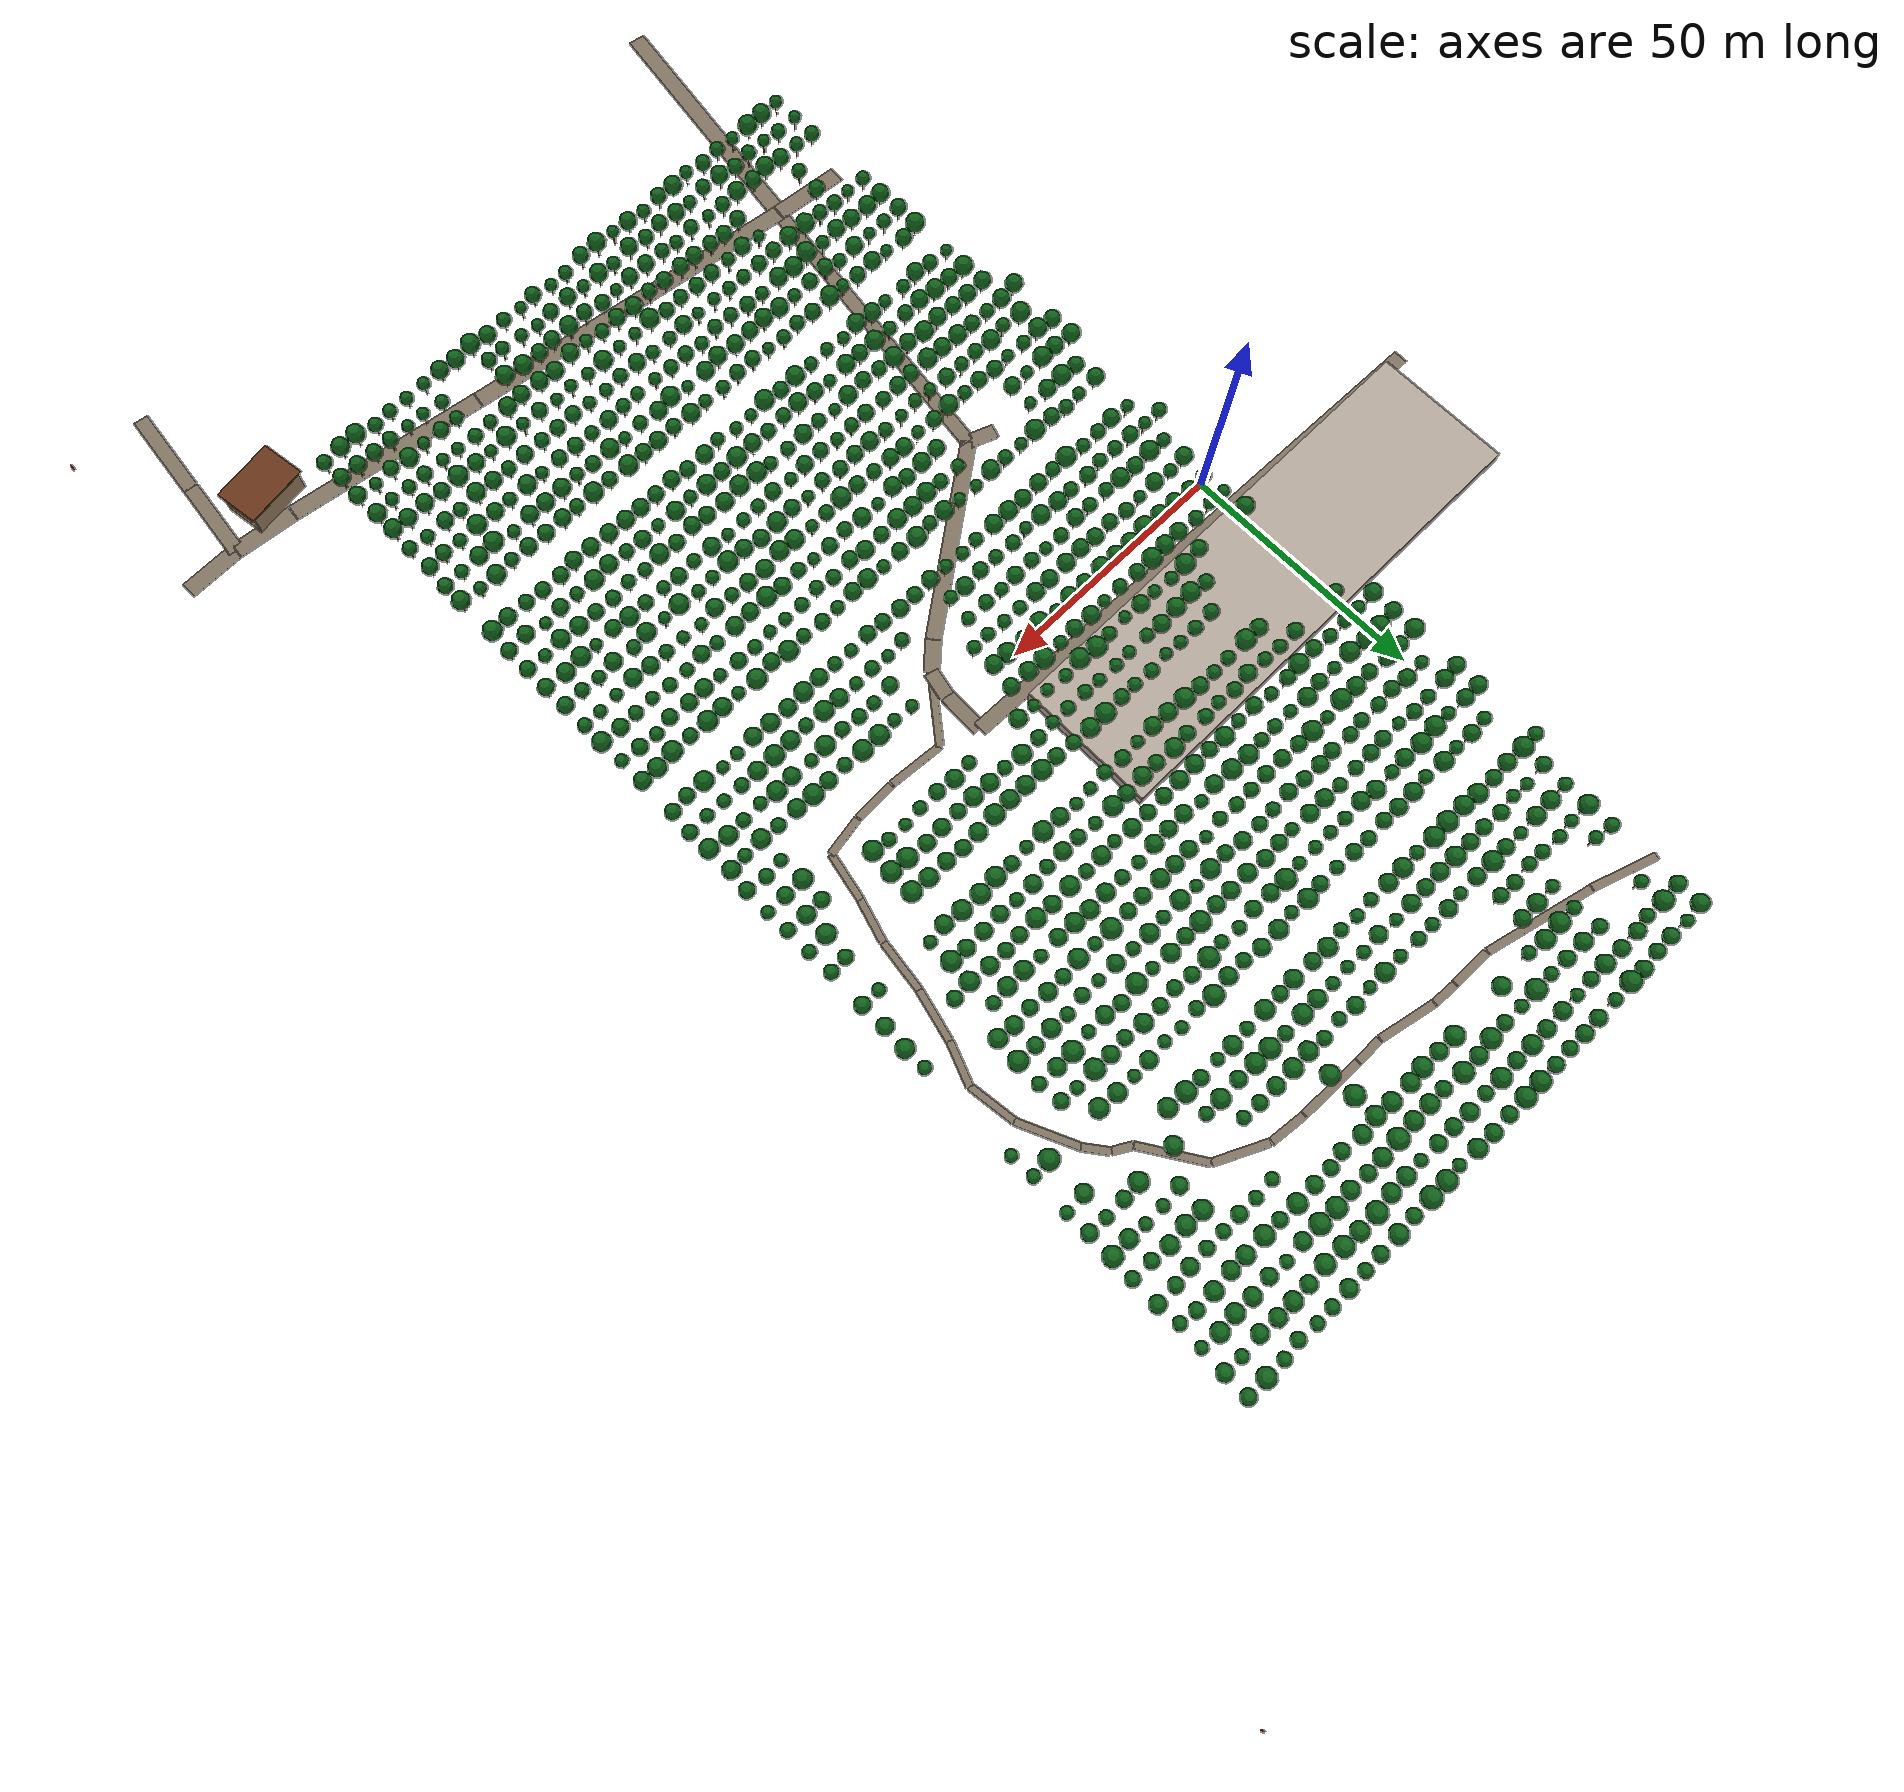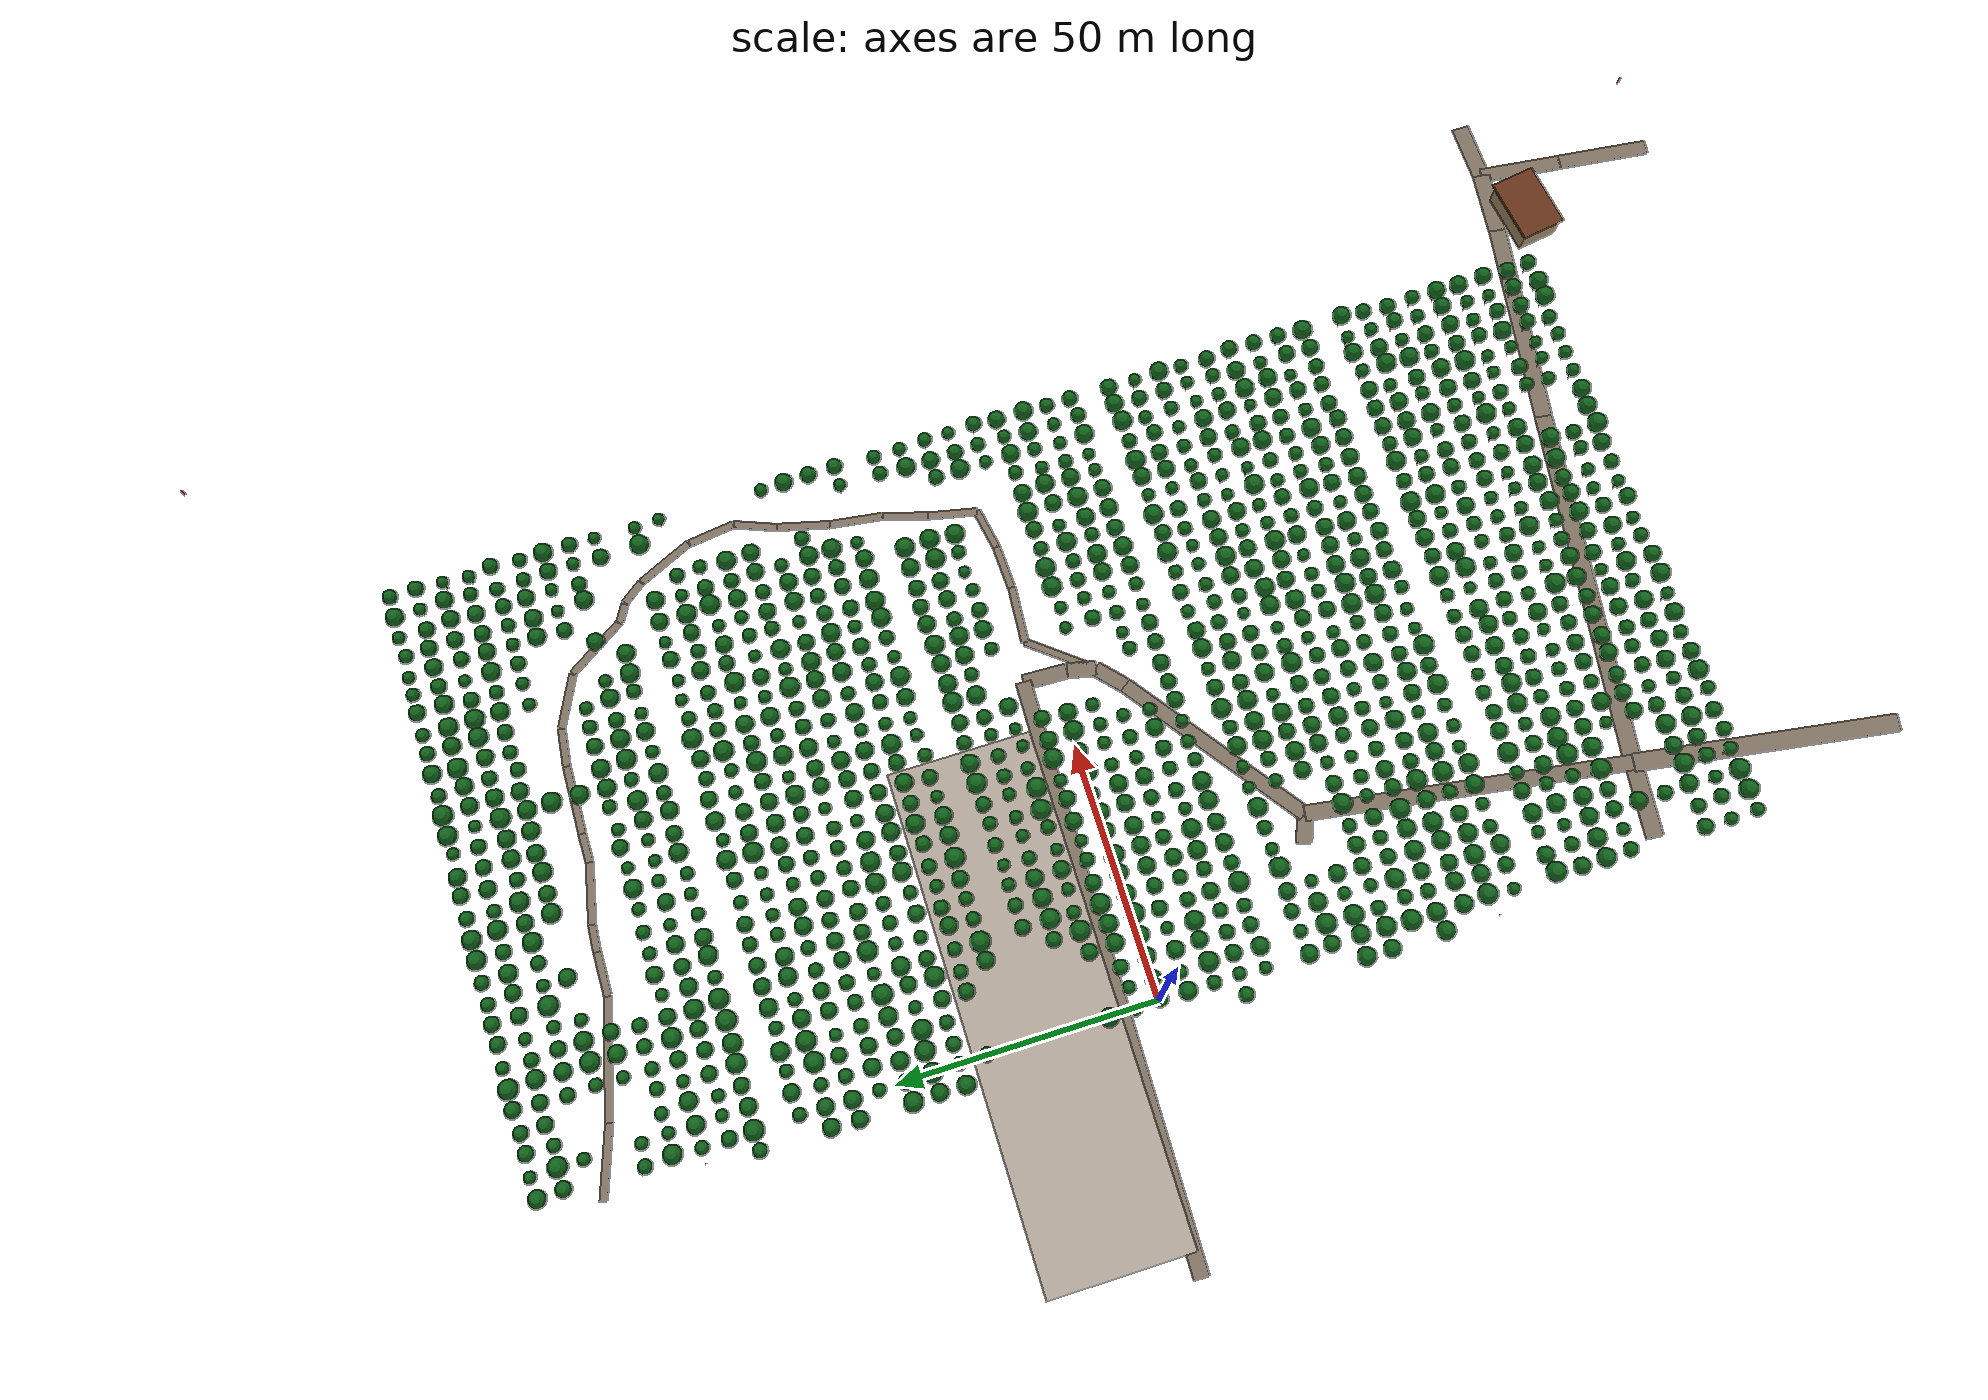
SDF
<sdf version="1.9">
 <world name="cheongsong_orchard">
  <model name="building_0">
   <static>true</static>
   <pose>5.6 21.5 1.5 0 0 0</pose>
   <link name="link">
    <collision name="collision"><geometry><box><size>98.0 27.8 3.0</size></box></geometry></collision>
    <visual name="visual">
     <geometry><box><size>98.0 27.8 3.0</size></box></geometry>
     <material><ambient>0.6 0.55 0.5 1</ambient><diffuse>0.7 0.65 0.6 1</diffuse></material>
    </visual>
   </link>
  </model>
  <model name="road_4">
   <static>true</static>
   <pose>8.2 -98.3 0.02 0 0 -0.1019</pose>
   <link name="link">
    <collision name="collision">
     <geometry><box><size>14.6 3.5 0.04</size></box></geometry>
     <surface><friction><ode><mu>0.9</mu><mu2>0.9</mu2></ode></friction></surface>
    </collision>
    <visual name="visual">
     <geometry><box><size>14.6 3.5 0.04</size></box></geometry>
     <material><ambient>0.4 0.35 0.28 1</ambient><diffuse>0.5 0.45 0.38 1</diffuse></material>
    </visual>
   </link>
  </model>
  <model name="road_5">
   <static>true</static>
   <pose>50.6 -103.7 0.02 0 0 -0.1323</pose>
   <link name="link">
    <collision name="collision">
     <geometry><box><size>70.8 3.5 0.04</size></box></geometry>
     <surface><friction><ode><mu>0.9</mu><mu2>0.9</mu2></ode></friction></surface>
    </collision>
    <visual name="visual">
     <geometry><box><size>70.8 3.5 0.04</size></box></geometry>
     <material><ambient>0.4 0.35 0.28 1</ambient><diffuse>0.5 0.45 0.38 1</diffuse></material>
    </visual>
   </link>
  </model>
  <model name="road_6">
   <static>true</static>
   <pose>105.9 -111.3 0.02 0 0 -0.1419</pose>
   <link name="link">
    <collision name="collision">
     <geometry><box><size>40.9 3.5 0.04</size></box></geometry>
     <surface><friction><ode><mu>0.9</mu><mu2>0.9</mu2></ode></friction></surface>
    </collision>
    <visual name="visual">
     <geometry><box><size>40.9 3.5 0.04</size></box></geometry>
     <material><ambient>0.4 0.35 0.28 1</ambient><diffuse>0.5 0.45 0.38 1</diffuse></material>
    </visual>
   </link>
  </model>
  <model name="road_7">
   <static>true</static>
   <pose>132.4 -114.8 0.02 0 0 -0.1008</pose>
   <link name="link">
    <collision name="collision">
     <geometry><box><size>12.5 3.5 0.04</size></box></geometry>
     <surface><friction><ode><mu>0.9</mu><mu2>0.9</mu2></ode></friction></surface>
    </collision>
    <visual name="visual">
     <geometry><box><size>12.5 3.5 0.04</size></box></geometry>
     <material><ambient>0.4 0.35 0.28 1</ambient><diffuse>0.5 0.45 0.38 1</diffuse></material>
    </visual>
   </link>
  </model>
  <model name="road_8">
   <static>true</static>
   <pose>144.3 -115.3 0.02 0 0 0.0247</pose>
   <link name="link">
    <collision name="collision">
     <geometry><box><size>11.4 3.5 0.04</size></box></geometry>
     <surface><friction><ode><mu>0.9</mu><mu2>0.9</mu2></ode></friction></surface>
    </collision>
    <visual name="visual">
     <geometry><box><size>11.4 3.5 0.04</size></box></geometry>
     <material><ambient>0.4 0.35 0.28 1</ambient><diffuse>0.5 0.45 0.38 1</diffuse></material>
    </visual>
   </link>
  </model>
  <model name="road_9">
   <static>true</static>
   <pose>20.2 -68.0 0.02 0 0 1.4209</pose>
   <link name="link">
    <collision name="collision">
     <geometry><box><size>62.9 3.0 0.04</size></box></geometry>
     <surface><friction><ode><mu>0.9</mu><mu2>0.9</mu2></ode></friction></surface>
    </collision>
    <visual name="visual">
     <geometry><box><size>62.9 3.0 0.04</size></box></geometry>
     <material><ambient>0.4 0.35 0.28 1</ambient><diffuse>0.5 0.45 0.38 1</diffuse></material>
    </visual>
   </link>
  </model>
  <model name="road_10">
   <static>true</static>
   <pose>41.6 -24.8 0.02 0 0 0.6248</pose>
   <link name="link">
    <collision name="collision">
     <geometry><box><size>41.4 3.0 0.04</size></box></geometry>
     <surface><friction><ode><mu>0.9</mu><mu2>0.9</mu2></ode></friction></surface>
    </collision>
    <visual name="visual">
     <geometry><box><size>41.4 3.0 0.04</size></box></geometry>
     <material><ambient>0.4 0.35 0.28 1</ambient><diffuse>0.5 0.45 0.38 1</diffuse></material>
    </visual>
   </link>
  </model>
  <model name="road_11">
   <static>true</static>
   <pose>60.8 -10.5 0.02 0 0 0.7350</pose>
   <link name="link">
    <collision name="collision">
     <geometry><box><size>6.5 3.0 0.04</size></box></geometry>
     <surface><friction><ode><mu>0.9</mu><mu2>0.9</mu2></ode></friction></surface>
    </collision>
    <visual name="visual">
     <geometry><box><size>6.5 3.0 0.04</size></box></geometry>
     <material><ambient>0.4 0.35 0.28 1</ambient><diffuse>0.5 0.45 0.38 1</diffuse></material>
    </visual>
   </link>
  </model>
  <model name="road_12">
   <static>true</static>
   <pose>63.9 -5.7 0.02 0 0 1.3389</pose>
   <link name="link">
    <collision name="collision">
     <geometry><box><size>5.5 3.0 0.04</size></box></geometry>
     <surface><friction><ode><mu>0.9</mu><mu2>0.9</mu2></ode></friction></surface>
    </collision>
    <visual name="visual">
     <geometry><box><size>5.5 3.0 0.04</size></box></geometry>
     <material><ambient>0.4 0.35 0.28 1</ambient><diffuse>0.5 0.45 0.38 1</diffuse></material>
    </visual>
   </link>
  </model>
  <model name="road_13">
   <static>true</static>
   <pose>64.6 1.3 0.02 0 0 1.5345</pose>
   <link name="link">
    <collision name="collision">
     <geometry><box><size>8.6 3.0 0.04</size></box></geometry>
     <surface><friction><ode><mu>0.9</mu><mu2>0.9</mu2></ode></friction></surface>
    </collision>
    <visual name="visual">
     <geometry><box><size>8.6 3.0 0.04</size></box></geometry>
     <material><ambient>0.4 0.35 0.28 1</ambient><diffuse>0.5 0.45 0.38 1</diffuse></material>
    </visual>
   </link>
  </model>
  <model name="road_14">
   <static>true</static>
   <pose>8.4 6.9 0.02 0 0 3.1190</pose>
   <link name="link">
    <collision name="collision">
     <geometry><box><size>112.9 3.0 0.04</size></box></geometry>
     <surface><friction><ode><mu>0.9</mu><mu2>0.9</mu2></ode></friction></surface>
    </collision>
    <visual name="visual">
     <geometry><box><size>112.9 3.0 0.04</size></box></geometry>
     <material><ambient>0.4 0.35 0.28 1</ambient><diffuse>0.5 0.45 0.38 1</diffuse></material>
    </visual>
   </link>
  </model>
  <model name="road_17">
   <static>true</static>
   <pose>22.2 -35.9 0.02 0 0 -0.3609</pose>
   <link name="link">
    <collision name="collision">
     <geometry><box><size>5.7 3.0 0.04</size></box></geometry>
     <surface><friction><ode><mu>0.9</mu><mu2>0.9</mu2></ode></friction></surface>
    </collision>
    <visual name="visual">
     <geometry><box><size>5.7 3.0 0.04</size></box></geometry>
     <material><ambient>0.4 0.35 0.28 1</ambient><diffuse>0.5 0.45 0.38 1</diffuse></material>
    </visual>
   </link>
  </model>
  <model name="road_18">
   <static>true</static>
   <pose>11.5 -124.5 0.02 0 0 -1.7239</pose>
   <link name="link">
    <collision name="collision">
     <geometry><box><size>51.5 3.5 0.04</size></box></geometry>
     <surface><friction><ode><mu>0.9</mu><mu2>0.9</mu2></ode></friction></surface>
    </collision>
    <visual name="visual">
     <geometry><box><size>51.5 3.5 0.04</size></box></geometry>
     <material><ambient>0.4 0.35 0.28 1</ambient><diffuse>0.5 0.45 0.38 1</diffuse></material>
    </visual>
   </link>
  </model>
  <model name="road_26">
   <static>true</static>
   <pose>135.6 -140.9 0.02 0 0 1.4537</pose>
   <link name="link">
    <collision name="collision">
     <geometry><box><size>18.3 3.0 0.04</size></box></geometry>
     <surface><friction><ode><mu>0.9</mu><mu2>0.9</mu2></ode></friction></surface>
    </collision>
    <visual name="visual">
     <geometry><box><size>18.3 3.0 0.04</size></box></geometry>
     <material><ambient>0.4 0.35 0.28 1</ambient><diffuse>0.5 0.45 0.38 1</diffuse></material>
    </visual>
   </link>
  </model>
  <model name="road_27">
   <static>true</static>
   <pose>137.6 -123.6 0.02 0 0 1.4529</pose>
   <link name="link">
    <collision name="collision">
     <geometry><box><size>16.4 3.0 0.04</size></box></geometry>
     <surface><friction><ode><mu>0.9</mu><mu2>0.9</mu2></ode></friction></surface>
    </collision>
    <visual name="visual">
     <geometry><box><size>16.4 3.0 0.04</size></box></geometry>
     <material><ambient>0.4 0.35 0.28 1</ambient><diffuse>0.5 0.45 0.38 1</diffuse></material>
    </visual>
   </link>
  </model>
  <model name="road_30">
   <static>true</static>
   <pose>67.8 -2.7 0.02 0 0 0.8952</pose>
   <link name="link">
    <collision name="collision">
     <geometry><box><size>14.5 1.5 0.04</size></box></geometry>
     <surface><friction><ode><mu>0.9</mu><mu2>0.9</mu2></ode></friction></surface>
    </collision>
    <visual name="visual">
     <geometry><box><size>14.5 1.5 0.04</size></box></geometry>
     <material><ambient>0.4 0.35 0.28 1</ambient><diffuse>0.5 0.45 0.38 1</diffuse></material>
    </visual>
   </link>
  </model>
  <model name="road_31">
   <static>true</static>
   <pose>77.9 2.5 0.02 0 0 -0.0748</pose>
   <link name="link">
    <collision name="collision">
     <geometry><box><size>11.3 1.5 0.04</size></box></geometry>
     <surface><friction><ode><mu>0.9</mu><mu2>0.9</mu2></ode></friction></surface>
    </collision>
    <visual name="visual">
     <geometry><box><size>11.3 1.5 0.04</size></box></geometry>
     <material><ambient>0.4 0.35 0.28 1</ambient><diffuse>0.5 0.45 0.38 1</diffuse></material>
    </visual>
   </link>
  </model>
  <model name="road_32">
   <static>true</static>
   <pose>87.9 2.3 0.02 0 0 0.0412</pose>
   <link name="link">
    <collision name="collision">
     <geometry><box><size>8.6 1.5 0.04</size></box></geometry>
     <surface><friction><ode><mu>0.9</mu><mu2>0.9</mu2></ode></friction></surface>
    </collision>
    <visual name="visual">
     <geometry><box><size>8.6 1.5 0.04</size></box></geometry>
     <material><ambient>0.4 0.35 0.28 1</ambient><diffuse>0.5 0.45 0.38 1</diffuse></material>
    </visual>
   </link>
  </model>
  <model name="road_33">
   <static>true</static>
   <pose>96.3 3.2 0.02 0 0 0.1778</pose>
   <link name="link">
    <collision name="collision">
     <geometry><box><size>8.2 1.5 0.04</size></box></geometry>
     <surface><friction><ode><mu>0.9</mu><mu2>0.9</mu2></ode></friction></surface>
    </collision>
    <visual name="visual">
     <geometry><box><size>8.2 1.5 0.04</size></box></geometry>
     <material><ambient>0.4 0.35 0.28 1</ambient><diffuse>0.5 0.45 0.38 1</diffuse></material>
    </visual>
   </link>
  </model>
  <model name="road_34">
   <static>true</static>
   <pose>101.3 8.7 0.02 0 0 1.3587</pose>
   <link name="link">
    <collision name="collision">
     <geometry><box><size>9.7 1.5 0.04</size></box></geometry>
     <surface><friction><ode><mu>0.9</mu><mu2>0.9</mu2></ode></friction></surface>
    </collision>
    <visual name="visual">
     <geometry><box><size>9.7 1.5 0.04</size></box></geometry>
     <material><ambient>0.4 0.35 0.28 1</ambient><diffuse>0.5 0.45 0.38 1</diffuse></material>
    </visual>
   </link>
  </model>
  <model name="road_35">
   <static>true</static>
   <pose>103.6 17.5 0.02 0 0 1.2752</pose>
   <link name="link">
    <collision name="collision">
     <geometry><box><size>8.7 1.5 0.04</size></box></geometry>
     <surface><friction><ode><mu>0.9</mu><mu2>0.9</mu2></ode></friction></surface>
    </collision>
    <visual name="visual">
     <geometry><box><size>8.7 1.5 0.04</size></box></geometry>
     <material><ambient>0.4 0.35 0.28 1</ambient><diffuse>0.5 0.45 0.38 1</diffuse></material>
    </visual>
   </link>
  </model>
  <model name="road_36">
   <static>true</static>
   <pose>105.6 26.9 0.02 0 0 1.4321</pose>
   <link name="link">
    <collision name="collision">
     <geometry><box><size>10.4 1.5 0.04</size></box></geometry>
     <surface><friction><ode><mu>0.9</mu><mu2>0.9</mu2></ode></friction></surface>
    </collision>
    <visual name="visual">
     <geometry><box><size>10.4 1.5 0.04</size></box></geometry>
     <material><ambient>0.4 0.35 0.28 1</ambient><diffuse>0.5 0.45 0.38 1</diffuse></material>
    </visual>
   </link>
  </model>
  <model name="road_37">
   <static>true</static>
   <pose>107.6 36.9 0.02 0 0 1.3204</pose>
   <link name="link">
    <collision name="collision">
     <geometry><box><size>10.2 1.5 0.04</size></box></geometry>
     <surface><friction><ode><mu>0.9</mu><mu2>0.9</mu2></ode></friction></surface>
    </collision>
    <visual name="visual">
     <geometry><box><size>10.2 1.5 0.04</size></box></geometry>
     <material><ambient>0.4 0.35 0.28 1</ambient><diffuse>0.5 0.45 0.38 1</diffuse></material>
    </visual>
   </link>
  </model>
  <model name="road_38">
   <static>true</static>
   <pose>110.4 45.8 0.02 0 0 1.1956</pose>
   <link name="link">
    <collision name="collision">
     <geometry><box><size>8.5 1.5 0.04</size></box></geometry>
     <surface><friction><ode><mu>0.9</mu><mu2>0.9</mu2></ode></friction></surface>
    </collision>
    <visual name="visual">
     <geometry><box><size>8.5 1.5 0.04</size></box></geometry>
     <material><ambient>0.4 0.35 0.28 1</ambient><diffuse>0.5 0.45 0.38 1</diffuse></material>
    </visual>
   </link>
  </model>
  <model name="road_39">
   <static>true</static>
   <pose>111.3 54.4 0.02 0 0 1.7000</pose>
   <link name="link">
    <collision name="collision">
     <geometry><box><size>9.3 1.5 0.04</size></box></geometry>
     <surface><friction><ode><mu>0.9</mu><mu2>0.9</mu2></ode></friction></surface>
    </collision>
    <visual name="visual">
     <geometry><box><size>9.3 1.5 0.04</size></box></geometry>
     <material><ambient>0.4 0.35 0.28 1</ambient><diffuse>0.5 0.45 0.38 1</diffuse></material>
    </visual>
   </link>
  </model>
  <model name="road_40">
   <static>true</static>
   <pose>108.3 64.4 0.02 0 0 2.0023</pose>
   <link name="link">
    <collision name="collision">
     <geometry><box><size>11.8 1.5 0.04</size></box></geometry>
     <surface><friction><ode><mu>0.9</mu><mu2>0.9</mu2></ode></friction></surface>
    </collision>
    <visual name="visual">
     <geometry><box><size>11.8 1.5 0.04</size></box></geometry>
     <material><ambient>0.4 0.35 0.28 1</ambient><diffuse>0.5 0.45 0.38 1</diffuse></material>
    </visual>
   </link>
  </model>
  <model name="road_41">
   <static>true</static>
   <pose>104.3 71.8 0.02 0 0 2.2252</pose>
   <link name="link">
    <collision name="collision">
     <geometry><box><size>5.1 1.5 0.04</size></box></geometry>
     <surface><friction><ode><mu>0.9</mu><mu2>0.9</mu2></ode></friction></surface>
    </collision>
    <visual name="visual">
     <geometry><box><size>5.1 1.5 0.04</size></box></geometry>
     <material><ambient>0.4 0.35 0.28 1</ambient><diffuse>0.5 0.45 0.38 1</diffuse></material>
    </visual>
   </link>
  </model>
  <model name="road_42">
   <static>true</static>
   <pose>101.0 74.8 0.02 0 0 2.6209</pose>
   <link name="link">
    <collision name="collision">
     <geometry><box><size>3.9 1.5 0.04</size></box></geometry>
     <surface><friction><ode><mu>0.9</mu><mu2>0.9</mu2></ode></friction></surface>
    </collision>
    <visual name="visual">
     <geometry><box><size>3.9 1.5 0.04</size></box></geometry>
     <material><ambient>0.4 0.35 0.28 1</ambient><diffuse>0.5 0.45 0.38 1</diffuse></material>
    </visual>
   </link>
  </model>
  <model name="road_43">
   <static>true</static>
   <pose>95.7 81.3 0.02 0 0 2.1487</pose>
   <link name="link">
    <collision name="collision">
     <geometry><box><size>13.2 1.5 0.04</size></box></geometry>
     <surface><friction><ode><mu>0.9</mu><mu2>0.9</mu2></ode></friction></surface>
    </collision>
    <visual name="visual">
     <geometry><box><size>13.2 1.5 0.04</size></box></geometry>
     <material><ambient>0.4 0.35 0.28 1</ambient><diffuse>0.5 0.45 0.38 1</diffuse></material>
    </visual>
   </link>
  </model>
  <model name="road_44">
   <static>true</static>
   <pose>87.3 89.1 0.02 0 0 2.6935</pose>
   <link name="link">
    <collision name="collision">
     <geometry><box><size>10.8 1.5 0.04</size></box></geometry>
     <surface><friction><ode><mu>0.9</mu><mu2>0.9</mu2></ode></friction></surface>
    </collision>
    <visual name="visual">
     <geometry><box><size>10.8 1.5 0.04</size></box></geometry>
     <material><ambient>0.4 0.35 0.28 1</ambient><diffuse>0.5 0.45 0.38 1</diffuse></material>
    </visual>
   </link>
  </model>
  <model name="road_45">
   <static>true</static>
   <pose>78.7 91.9 0.02 0 0 3.0266</pose>
   <link name="link">
    <collision name="collision">
     <geometry><box><size>7.4 1.5 0.04</size></box></geometry>
     <surface><friction><ode><mu>0.9</mu><mu2>0.9</mu2></ode></friction></surface>
    </collision>
    <visual name="visual">
     <geometry><box><size>7.4 1.5 0.04</size></box></geometry>
     <material><ambient>0.4 0.35 0.28 1</ambient><diffuse>0.5 0.45 0.38 1</diffuse></material>
    </visual>
   </link>
  </model>
  <model name="road_46">
   <static>true</static>
   <pose>68.4 92.5 0.02 0 0 3.1149</pose>
   <link name="link">
    <collision name="collision">
     <geometry><box><size>13.3 1.5 0.04</size></box></geometry>
     <surface><friction><ode><mu>0.9</mu><mu2>0.9</mu2></ode></friction></surface>
    </collision>
    <visual name="visual">
     <geometry><box><size>13.3 1.5 0.04</size></box></geometry>
     <material><ambient>0.4 0.35 0.28 1</ambient><diffuse>0.5 0.45 0.38 1</diffuse></material>
    </visual>
   </link>
  </model>
  <model name="road_47">
   <static>true</static>
   <pose>58.9 92.7 0.02 0 0 3.1416</pose>
   <link name="link">
    <collision name="collision">
     <geometry><box><size>5.6 1.5 0.04</size></box></geometry>
     <surface><friction><ode><mu>0.9</mu><mu2>0.9</mu2></ode></friction></surface>
    </collision>
    <visual name="visual">
     <geometry><box><size>5.6 1.5 0.04</size></box></geometry>
     <material><ambient>0.4 0.35 0.28 1</ambient><diffuse>0.5 0.45 0.38 1</diffuse></material>
    </visual>
   </link>
  </model>
  <model name="road_48">
   <static>true</static>
   <pose>50.4 93.9 0.02 0 0 2.9339</pose>
   <link name="link">
    <collision name="collision">
     <geometry><box><size>11.7 1.5 0.04</size></box></geometry>
     <surface><friction><ode><mu>0.9</mu><mu2>0.9</mu2></ode></friction></surface>
    </collision>
    <visual name="visual">
     <geometry><box><size>11.7 1.5 0.04</size></box></geometry>
     <material><ambient>0.4 0.35 0.28 1</ambient><diffuse>0.5 0.45 0.38 1</diffuse></material>
    </visual>
   </link>
  </model>
  <model name="road_49">
   <static>true</static>
   <pose>42.1 95.3 0.02 0 0 3.0728</pose>
   <link name="link">
    <collision name="collision">
     <geometry><box><size>5.2 1.5 0.04</size></box></geometry>
     <surface><friction><ode><mu>0.9</mu><mu2>0.9</mu2></ode></friction></surface>
    </collision>
    <visual name="visual">
     <geometry><box><size>5.2 1.5 0.04</size></box></geometry>
     <material><ambient>0.4 0.35 0.28 1</ambient><diffuse>0.5 0.45 0.38 1</diffuse></material>
    </visual>
   </link>
  </model>
  <model name="road_50">
   <static>true</static>
   <pose>35.4 95.5 0.02 0 0 3.1268</pose>
   <link name="link">
    <collision name="collision">
     <geometry><box><size>8.3 1.5 0.04</size></box></geometry>
     <surface><friction><ode><mu>0.9</mu><mu2>0.9</mu2></ode></friction></surface>
    </collision>
    <visual name="visual">
     <geometry><box><size>8.3 1.5 0.04</size></box></geometry>
     <material><ambient>0.4 0.35 0.28 1</ambient><diffuse>0.5 0.45 0.38 1</diffuse></material>
    </visual>
   </link>
  </model>
  <model name="road_51">
   <static>true</static>
   <pose>20.2 98.3 0.02 0 0 2.9003</pose>
   <link name="link">
    <collision name="collision">
     <geometry><box><size>22.6 1.5 0.04</size></box></geometry>
     <surface><friction><ode><mu>0.9</mu><mu2>0.9</mu2></ode></friction></surface>
    </collision>
    <visual name="visual">
     <geometry><box><size>22.6 1.5 0.04</size></box></geometry>
     <material><ambient>0.4 0.35 0.28 1</ambient><diffuse>0.5 0.45 0.38 1</diffuse></material>
    </visual>
   </link>
  </model>
  <model name="road_52">
   <static>true</static>
   <pose>2.8 103.1 0.02 0 0 2.8174</pose>
   <link name="link">
    <collision name="collision">
     <geometry><box><size>13.6 1.5 0.04</size></box></geometry>
     <surface><friction><ode><mu>0.9</mu><mu2>0.9</mu2></ode></friction></surface>
    </collision>
    <visual name="visual">
     <geometry><box><size>13.6 1.5 0.04</size></box></geometry>
     <material><ambient>0.4 0.35 0.28 1</ambient><diffuse>0.5 0.45 0.38 1</diffuse></material>
    </visual>
   </link>
  </model>
  <model name="apple_tree_26">
   <static>true</static>
   <pose>-0.25 -116.29 0 0 0 0</pose>
   <link name="link">
    <collision name="trunk_col">
     <pose>0 0 1.40 0 0 0</pose>
     <geometry><cylinder><radius>0.097</radius><length>2.79</length></cylinder></geometry>
    </collision>
    <visual name="trunk_vis">
     <pose>0 0 1.40 0 0 0</pose>
     <geometry><cylinder><radius>0.097</radius><length>2.79</length></cylinder></geometry>
     <material><ambient>0.35 0.22 0.08 1</ambient><diffuse>0.45 0.30 0.12 1</diffuse></material>
    </visual>
    <collision name="canopy_col">
     <pose>0 0 4.14 0 0 0</pose>
     <geometry><sphere><radius>1.35</radius></sphere></geometry>
    </collision>
    <visual name="canopy_vis">
     <pose>0 0 4.14 0 0 0</pose>
     <geometry><sphere><radius>1.35</radius></sphere></geometry>
     <material><ambient>0.04 0.28 0.06 1</ambient><diffuse>0.06 0.38 0.10 1</diffuse></material>
    </visual>
   </link>
  </model>
  <model name="apple_tree_27">
   <static>true</static>
   <pose>3.78 -116.24 0 0 0 0</pose>
   <link name="link">
    <collision name="trunk_col">
     <pose>0 0 1.11 0 0 0</pose>
     <geometry><cylinder><radius>0.097</radius><length>2.22</length></cylinder></geometry>
    </collision>
    <visual name="trunk_vis">
     <pose>0 0 1.11 0 0 0</pose>
     <geometry><cylinder><radius>0.097</radius><length>2.22</length></cylinder></geometry>
     <material><ambient>0.35 0.22 0.08 1</ambient><diffuse>0.45 0.30 0.12 1</diffuse></material>
    </visual>
    <collision name="canopy_col">
     <pose>0 0 4.16 0 0 0</pose>
     <geometry><sphere><radius>1.94</radius></sphere></geometry>
    </collision>
    <visual name="canopy_vis">
     <pose>0 0 4.16 0 0 0</pose>
     <geometry><sphere><radius>1.94</radius></sphere></geometry>
     <material><ambient>0.04 0.28 0.06 1</ambient><diffuse>0.06 0.38 0.10 1</diffuse></material>
    </visual>
   </link>
  </model>
  <model name="apple_tree_28">
   <static>true</static>
   <pose>7.78 -115.97 0 0 0 0</pose>
   <link name="link">
    <collision name="trunk_col">
     <pose>0 0 1.24 0 0 0</pose>
     <geometry><cylinder><radius>0.084</radius><length>2.49</length></cylinder></geometry>
    </collision>
    <visual name="trunk_vis">
     <pose>0 0 1.24 0 0 0</pose>
     <geometry><cylinder><radius>0.084</radius><length>2.49</length></cylinder></geometry>
     <material><ambient>0.35 0.22 0.08 1</ambient><diffuse>0.45 0.30 0.12 1</diffuse></material>
    </visual>
    <collision name="canopy_col">
     <pose>0 0 4.49 0 0 0</pose>
     <geometry><sphere><radius>2.00</radius></sphere></geometry>
    </collision>
    <visual name="canopy_vis">
     <pose>0 0 4.49 0 0 0</pose>
     <geometry><sphere><radius>2.00</radius></sphere></geometry>
     <material><ambient>0.04 0.28 0.06 1</ambient><diffuse>0.06 0.38 0.10 1</diffuse></material>
    </visual>
   </link>
  </model>
  <model name="apple_tree_29">
   <static>true</static>
   <pose>12.01 -115.91 0 0 0 0</pose>
   <link name="link">
    <collision name="trunk_col">
     <pose>0 0 1.43 0 0 0</pose>
     <geometry><cylinder><radius>0.139</radius><length>2.85</length></cylinder></geometry>
    </collision>
    <visual name="trunk_vis">
     <pose>0 0 1.43 0 0 0</pose>
     <geometry><cylinder><radius>0.139</radius><length>2.85</length></cylinder></geometry>
     <material><ambient>0.35 0.22 0.08 1</ambient><diffuse>0.45 0.30 0.12 1</diffuse></material>
    </visual>
    <collision name="canopy_col">
     <pose>0 0 4.19 0 0 0</pose>
     <geometry><sphere><radius>1.33</radius></sphere></geometry>
    </collision>
    <visual name="canopy_vis">
     <pose>0 0 4.19 0 0 0</pose>
     <geometry><sphere><radius>1.33</radius></sphere></geometry>
     <material><ambient>0.04 0.28 0.06 1</ambient><diffuse>0.06 0.38 0.10 1</diffuse></material>
    </visual>
   </link>
  </model>
  <model name="apple_tree_30">
   <static>true</static>
   <pose>15.80 -116.36 0 0 0 0</pose>
   <link name="link">
    <collision name="trunk_col">
     <pose>0 0 1.17 0 0 0</pose>
     <geometry><cylinder><radius>0.084</radius><length>2.34</length></cylinder></geometry>
    </collision>
    <visual name="trunk_vis">
     <pose>0 0 1.17 0 0 0</pose>
     <geometry><cylinder><radius>0.084</radius><length>2.34</length></cylinder></geometry>
     <material><ambient>0.35 0.22 0.08 1</ambient><diffuse>0.45 0.30 0.12 1</diffuse></material>
    </visual>
    <collision name="canopy_col">
     <pose>0 0 3.84 0 0 0</pose>
     <geometry><sphere><radius>1.50</radius></sphere></geometry>
    </collision>
    <visual name="canopy_vis">
     <pose>0 0 3.84 0 0 0</pose>
     <geometry><sphere><radius>1.50</radius></sphere></geometry>
     <material><ambient>0.04 0.28 0.06 1</ambient><diffuse>0.06 0.38 0.10 1</diffuse></material>
    </visual>
   </link>
  </model>
  <model name="apple_tree_31">
   <static>true</static>
   <pose>19.84 -116.04 0 0 0 0</pose>
   <link name="link">
    <collision name="trunk_col">
     <pose>0 0 1.00 0 0 0</pose>
     <geometry><cylinder><radius>0.121</radius><length>2.01</length></cylinder></geometry>
    </collision>
    <visual name="trunk_vis">
     <pose>0 0 1.00 0 0 0</pose>
     <geometry><cylinder><radius>0.121</radius><length>2.01</length></cylinder></geometry>
     <material><ambient>0.35 0.22 0.08 1</ambient><diffuse>0.45 0.30 0.12 1</diffuse></material>
    </visual>
    <collision name="canopy_col">
     <pose>0 0 3.61 0 0 0</pose>
     <geometry><sphere><radius>1.60</radius></sphere></geometry>
    </collision>
    <visual name="canopy_vis">
     <pose>0 0 3.61 0 0 0</pose>
     <geometry><sphere><radius>1.60</radius></sphere></geometry>
     <material><ambient>0.04 0.28 0.06 1</ambient><diffuse>0.06 0.38 0.10 1</diffuse></material>
    </visual>
   </link>
  </model>
  <model name="apple_tree_32">
   <static>true</static>
   <pose>24.02 -116.40 0 0 0 0</pose>
   <link name="link">
    <collision name="trunk_col">
     <pose>0 0 1.44 0 0 0</pose>
     <geometry><cylinder><radius>0.086</radius><length>2.89</length></cylinder></geometry>
    </collision>
    <visual name="trunk_vis">
     <pose>0 0 1.44 0 0 0</pose>
     <geometry><cylinder><radius>0.086</radius><length>2.89</length></cylinder></geometry>
     <material><ambient>0.35 0.22 0.08 1</ambient><diffuse>0.45 0.30 0.12 1</diffuse></material>
    </visual>
    <collision name="canopy_col">
     <pose>0 0 4.24 0 0 0</pose>
     <geometry><sphere><radius>1.35</radius></sphere></geometry>
    </collision>
    <visual name="canopy_vis">
     <pose>0 0 4.24 0 0 0</pose>
     <geometry><sphere><radius>1.35</radius></sphere></geometry>
     <material><ambient>0.04 0.28 0.06 1</ambient><diffuse>0.06 0.38 0.10 1</diffuse></material>
    </visual>
   </link>
  </model>
  <model name="apple_tree_33">
   <static>true</static>
   <pose>27.87 -116.08 0 0 0 0</pose>
   <link name="link">
    <collision name="trunk_col">
     <pose>0 0 1.09 0 0 0</pose>
     <geometry><cylinder><radius>0.088</radius><length>2.18</length></cylinder></geometry>
    </collision>
    <visual name="trunk_vis">
     <pose>0 0 1.09 0 0 0</pose>
     <geometry><cylinder><radius>0.088</radius><length>2.18</length></cylinder></geometry>
     <material><ambient>0.35 0.22 0.08 1</ambient><diffuse>0.45 0.30 0.12 1</diffuse></material>
    </visual>
    <collision name="canopy_col">
     <pose>0 0 4.09 0 0 0</pose>
     <geometry><sphere><radius>1.91</radius></sphere></geometry>
    </collision>
    <visual name="canopy_vis">
     <pose>0 0 4.09 0 0 0</pose>
     <geometry><sphere><radius>1.91</radius></sphere></geometry>
     <material><ambient>0.04 0.28 0.06 1</ambient><diffuse>0.06 0.38 0.10 1</diffuse></material>
    </visual>
   </link>
  </model>
  <model name="apple_tree_34">
   <static>true</static>
   <pose>31.66 -116.13 0 0 0 0</pose>
   <link name="link">
    <collision name="trunk_col">
     <pose>0 0 1.28 0 0 0</pose>
     <geometry><cylinder><radius>0.109</radius><length>2.55</length></cylinder></geometry>
    </collision>
    <visual name="trunk_vis">
     <pose>0 0 1.28 0 0 0</pose>
     <geometry><cylinder><radius>0.109</radius><length>2.55</length></cylinder></geometry>
     <material><ambient>0.35 0.22 0.08 1</ambient><diffuse>0.45 0.30 0.12 1</diffuse></material>
    </visual>
    <collision name="canopy_col">
     <pose>0 0 4.22 0 0 0</pose>
     <geometry><sphere><radius>1.67</radius></sphere></geometry>
    </collision>
    <visual name="canopy_vis">
     <pose>0 0 4.22 0 0 0</pose>
     <geometry><sphere><radius>1.67</radius></sphere></geometry>
     <material><ambient>0.04 0.28 0.06 1</ambient><diffuse>0.06 0.38 0.10 1</diffuse></material>
    </visual>
   </link>
  </model>
  <model name="apple_tree_35">
   <static>true</static>
   <pose>35.82 -115.93 0 0 0 0</pose>
   <link name="link">
    <collision name="trunk_col">
     <pose>0 0 1.07 0 0 0</pose>
     <geometry><cylinder><radius>0.130</radius><length>2.15</length></cylinder></geometry>
    </collision>
    <visual name="trunk_vis">
     <pose>0 0 1.07 0 0 0</pose>
     <geometry><cylinder><radius>0.130</radius><length>2.15</length></cylinder></geometry>
     <material><ambient>0.35 0.22 0.08 1</ambient><diffuse>0.45 0.30 0.12 1</diffuse></material>
    </visual>
    <collision name="canopy_col">
     <pose>0 0 3.54 0 0 0</pose>
     <geometry><sphere><radius>1.39</radius></sphere></geometry>
    </collision>
    <visual name="canopy_vis">
     <pose>0 0 3.54 0 0 0</pose>
     <geometry><sphere><radius>1.39</radius></sphere></geometry>
     <material><ambient>0.04 0.28 0.06 1</ambient><diffuse>0.06 0.38 0.10 1</diffuse></material>
    </visual>
   </link>
  </model>
  <model name="apple_tree_36">
   <static>true</static>
   <pose>39.75 -116.09 0 0 0 0</pose>
   <link name="link">
    <collision name="trunk_col">
     <pose>0 0 1.12 0 0 0</pose>
     <geometry><cylinder><radius>0.102</radius><length>2.24</length></cylinder></geometry>
    </collision>
    <visual name="trunk_vis">
     <pose>0 0 1.12 0 0 0</pose>
     <geometry><cylinder><radius>0.102</radius><length>2.24</length></cylinder></geometry>
     <material><ambient>0.35 0.22 0.08 1</ambient><diffuse>0.45 0.30 0.12 1</diffuse></material>
    </visual>
    <collision name="canopy_col">
     <pose>0 0 4.04 0 0 0</pose>
     <geometry><sphere><radius>1.80</radius></sphere></geometry>
    </collision>
    <visual name="canopy_vis">
     <pose>0 0 4.04 0 0 0</pose>
     <geometry><sphere><radius>1.80</radius></sphere></geometry>
     <material><ambient>0.04 0.28 0.06 1</ambient><diffuse>0.06 0.38 0.10 1</diffuse></material>
    </visual>
   </link>
  </model>
  <model name="apple_tree_37">
   <static>true</static>
   <pose>43.55 -116.21 0 0 0 0</pose>
   <link name="link">
    <collision name="trunk_col">
     <pose>0 0 1.46 0 0 0</pose>
     <geometry><cylinder><radius>0.150</radius><length>2.92</length></cylinder></geometry>
    </collision>
    <visual name="trunk_vis">
     <pose>0 0 1.46 0 0 0</pose>
     <geometry><cylinder><radius>0.150</radius><length>2.92</length></cylinder></geometry>
     <material><ambient>0.35 0.22 0.08 1</ambient><diffuse>0.45 0.30 0.12 1</diffuse></material>
    </visual>
    <collision name="canopy_col">
     <pose>0 0 4.18 0 0 0</pose>
     <geometry><sphere><radius>1.26</radius></sphere></geometry>
    </collision>
    <visual name="canopy_vis">
     <pose>0 0 4.18 0 0 0</pose>
     <geometry><sphere><radius>1.26</radius></sphere></geometry>
     <material><ambient>0.04 0.28 0.06 1</ambient><diffuse>0.06 0.38 0.10 1</diffuse></material>
    </visual>
   </link>
  </model>
  <model name="apple_tree_38">
   <static>true</static>
   <pose>47.64 -116.33 0 0 0 0</pose>
   <link name="link">
    <collision name="trunk_col">
     <pose>0 0 1.43 0 0 0</pose>
     <geometry><cylinder><radius>0.142</radius><length>2.86</length></cylinder></geometry>
    </collision>
    <visual name="trunk_vis">
     <pose>0 0 1.43 0 0 0</pose>
     <geometry><cylinder><radius>0.142</radius><length>2.86</length></cylinder></geometry>
     <material><ambient>0.35 0.22 0.08 1</ambient><diffuse>0.45 0.30 0.12 1</diffuse></material>
    </visual>
    <collision name="canopy_col">
     <pose>0 0 4.76 0 0 0</pose>
     <geometry><sphere><radius>1.90</radius></sphere></geometry>
    </collision>
    <visual name="canopy_vis">
     <pose>0 0 4.76 0 0 0</pose>
     <geometry><sphere><radius>1.90</radius></sphere></geometry>
     <material><ambient>0.04 0.28 0.06 1</ambient><diffuse>0.06 0.38 0.10 1</diffuse></material>
    </visual>
   </link>
  </model>
  <model name="apple_tree_39">
   <static>true</static>
   <pose>51.73 -116.39 0 0 0 0</pose>
   <link name="link">
    <collision name="trunk_col">
     <pose>0 0 1.38 0 0 0</pose>
     <geometry><cylinder><radius>0.129</radius><length>2.76</length></cylinder></geometry>
    </collision>
    <visual name="trunk_vis">
     <pose>0 0 1.38 0 0 0</pose>
     <geometry><cylinder><radius>0.129</radius><length>2.76</length></cylinder></geometry>
     <material><ambient>0.35 0.22 0.08 1</ambient><diffuse>0.45 0.30 0.12 1</diffuse></material>
    </visual>
    <collision name="canopy_col">
     <pose>0 0 4.45 0 0 0</pose>
     <geometry><sphere><radius>1.69</radius></sphere></geometry>
    </collision>
    <visual name="canopy_vis">
     <pose>0 0 4.45 0 0 0</pose>
     <geometry><sphere><radius>1.69</radius></sphere></geometry>
     <material><ambient>0.04 0.28 0.06 1</ambient><diffuse>0.06 0.38 0.10 1</diffuse></material>
    </visual>
   </link>
  </model>
  <model name="apple_tree_40">
   <static>true</static>
   <pose>56.10 -116.10 0 0 0 0</pose>
   <link name="link">
    <collision name="trunk_col">
     <pose>0 0 0.98 0 0 0</pose>
     <geometry><cylinder><radius>0.137</radius><length>1.96</length></cylinder></geometry>
    </collision>
    <visual name="trunk_vis">
     <pose>0 0 0.98 0 0 0</pose>
     <geometry><cylinder><radius>0.137</radius><length>1.96</length></cylinder></geometry>
     <material><ambient>0.35 0.22 0.08 1</ambient><diffuse>0.45 0.30 0.12 1</diffuse></material>
    </visual>
    <collision name="canopy_col">
     <pose>0 0 3.40 0 0 0</pose>
     <geometry><sphere><radius>1.44</radius></sphere></geometry>
    </collision>
    <visual name="canopy_vis">
     <pose>0 0 3.40 0 0 0</pose>
     <geometry><sphere><radius>1.44</radius></sphere></geometry>
     <material><ambient>0.04 0.28 0.06 1</ambient><diffuse>0.06 0.38 0.10 1</diffuse></material>
    </visual>
   </link>
  </model>
  <model name="apple_tree_41">
   <static>true</static>
   <pose>59.89 -115.99 0 0 0 0</pose>
   <link name="link">
    <collision name="trunk_col">
     <pose>0 0 1.00 0 0 0</pose>
     <geometry><cylinder><radius>0.103</radius><length>1.99</length></cylinder></geometry>
    </collision>
    <visual name="trunk_vis">
     <pose>0 0 1.00 0 0 0</pose>
     <geometry><cylinder><radius>0.103</radius><length>1.99</length></cylinder></geometry>
     <material><ambient>0.35 0.22 0.08 1</ambient><diffuse>0.45 0.30 0.12 1</diffuse></material>
    </visual>
    <collision name="canopy_col">
     <pose>0 0 3.30 0 0 0</pose>
     <geometry><sphere><radius>1.30</radius></sphere></geometry>
    </collision>
    <visual name="canopy_vis">
     <pose>0 0 3.30 0 0 0</pose>
     <geometry><sphere><radius>1.30</radius></sphere></geometry>
     <material><ambient>0.04 0.28 0.06 1</ambient><diffuse>0.06 0.38 0.10 1</diffuse></material>
    </visual>
   </link>
  </model>
  <model name="apple_tree_42">
   <static>true</static>
   <pose>64.10 -116.39 0 0 0 0</pose>
   <link name="link">
    <collision name="trunk_col">
     <pose>0 0 1.19 0 0 0</pose>
     <geometry><cylinder><radius>0.129</radius><length>2.38</length></cylinder></geometry>
    </collision>
    <visual name="trunk_vis">
     <pose>0 0 1.19 0 0 0</pose>
     <geometry><cylinder><radius>0.129</radius><length>2.38</length></cylinder></geometry>
     <material><ambient>0.35 0.22 0.08 1</ambient><diffuse>0.45 0.30 0.12 1</diffuse></material>
    </visual>
    <collision name="canopy_col">
     <pose>0 0 4.03 0 0 0</pose>
     <geometry><sphere><radius>1.65</radius></sphere></geometry>
    </collision>
    <visual name="canopy_vis">
     <pose>0 0 4.03 0 0 0</pose>
     <geometry><sphere><radius>1.65</radius></sphere></geometry>
     <material><ambient>0.04 0.28 0.06 1</ambient><diffuse>0.06 0.38 0.10 1</diffuse></material>
    </visual>
   </link>
  </model>
  <model name="apple_tree_43">
   <static>true</static>
   <pose>67.58 -115.92 0 0 0 0</pose>
   <link name="link">
    <collision name="trunk_col">
     <pose>0 0 1.31 0 0 0</pose>
     <geometry><cylinder><radius>0.090</radius><length>2.62</length></cylinder></geometry>
    </collision>
    <visual name="trunk_vis">
     <pose>0 0 1.31 0 0 0</pose>
     <geometry><cylinder><radius>0.090</radius><length>2.62</length></cylinder></geometry>
     <material><ambient>0.35 0.22 0.08 1</ambient><diffuse>0.45 0.30 0.12 1</diffuse></material>
    </visual>
    <collision name="canopy_col">
     <pose>0 0 3.85 0 0 0</pose>
     <geometry><sphere><radius>1.23</radius></sphere></geometry>
    </collision>
    <visual name="canopy_vis">
     <pose>0 0 3.85 0 0 0</pose>
     <geometry><sphere><radius>1.23</radius></sphere></geometry>
     <material><ambient>0.04 0.28 0.06 1</ambient><diffuse>0.06 0.38 0.10 1</diffuse></material>
    </visual>
   </link>
  </model>
  <model name="apple_tree_44">
   <static>true</static>
   <pose>71.73 -116.16 0 0 0 0</pose>
   <link name="link">
    <collision name="trunk_col">
     <pose>0 0 1.18 0 0 0</pose>
     <geometry><cylinder><radius>0.083</radius><length>2.37</length></cylinder></geometry>
    </collision>
    <visual name="trunk_vis">
     <pose>0 0 1.18 0 0 0</pose>
     <geometry><cylinder><radius>0.083</radius><length>2.37</length></cylinder></geometry>
     <material><ambient>0.35 0.22 0.08 1</ambient><diffuse>0.45 0.30 0.12 1</diffuse></material>
    </visual>
    <collision name="canopy_col">
     <pose>0 0 3.86 0 0 0</pose>
     <geometry><sphere><radius>1.49</radius></sphere></geometry>
    </collision>
    <visual name="canopy_vis">
     <pose>0 0 3.86 0 0 0</pose>
     <geometry><sphere><radius>1.49</radius></sphere></geometry>
     <material><ambient>0.04 0.28 0.06 1</ambient><diffuse>0.06 0.38 0.10 1</diffuse></material>
    </visual>
   </link>
  </model>
  <model name="apple_tree_45">
   <static>true</static>
   <pose>76.07 -115.91 0 0 0 0</pose>
   <link name="link">
    <collision name="trunk_col">
     <pose>0 0 0.99 0 0 0</pose>
     <geometry><cylinder><radius>0.105</radius><length>1.99</length></cylinder></geometry>
    </collision>
    <visual name="trunk_vis">
     <pose>0 0 0.99 0 0 0</pose>
     <geometry><cylinder><radius>0.105</radius><length>1.99</length></cylinder></geometry>
     <material><ambient>0.35 0.22 0.08 1</ambient><diffuse>0.45 0.30 0.12 1</diffuse></material>
    </visual>
    <collision name="canopy_col">
     <pose>0 0 3.73 0 0 0</pose>
     <geometry><sphere><radius>1.75</radius></sphere></geometry>
    </collision>
    <visual name="canopy_vis">
     <pose>0 0 3.73 0 0 0</pose>
     <geometry><sphere><radius>1.75</radius></sphere></geometry>
     <material><ambient>0.04 0.28 0.06 1</ambient><diffuse>0.06 0.38 0.10 1</diffuse></material>
    </visual>
   </link>
  </model>
  <model name="apple_tree_46">
   <static>true</static>
   <pose>79.91 -116.28 0 0 0 0</pose>
   <link name="link">
    <collision name="trunk_col">
     <pose>0 0 1.25 0 0 0</pose>
     <geometry><cylinder><radius>0.141</radius><length>2.50</length></cylinder></geometry>
    </collision>
    <visual name="trunk_vis">
     <pose>0 0 1.25 0 0 0</pose>
     <geometry><cylinder><radius>0.141</radius><length>2.50</length></cylinder></geometry>
     <material><ambient>0.35 0.22 0.08 1</ambient><diffuse>0.45 0.30 0.12 1</diffuse></material>
    </visual>
    <collision name="canopy_col">
     <pose>0 0 4.47 0 0 0</pose>
     <geometry><sphere><radius>1.98</radius></sphere></geometry>
    </collision>
    <visual name="canopy_vis">
     <pose>0 0 4.47 0 0 0</pose>
     <geometry><sphere><radius>1.98</radius></sphere></geometry>
     <material><ambient>0.04 0.28 0.06 1</ambient><diffuse>0.06 0.38 0.10 1</diffuse></material>
    </visual>
   </link>
  </model>
  <model name="apple_tree_47">
   <static>true</static>
   <pose>83.96 -115.93 0 0 0 0</pose>
   <link name="link">
    <collision name="trunk_col">
     <pose>0 0 1.09 0 0 0</pose>
     <geometry><cylinder><radius>0.091</radius><length>2.18</length></cylinder></geometry>
    </collision>
    <visual name="trunk_vis">
     <pose>0 0 1.09 0 0 0</pose>
     <geometry><cylinder><radius>0.091</radius><length>2.18</length></cylinder></geometry>
     <material><ambient>0.35 0.22 0.08 1</ambient><diffuse>0.45 0.30 0.12 1</diffuse></material>
    </visual>
    <collision name="canopy_col">
     <pose>0 0 4.02 0 0 0</pose>
     <geometry><sphere><radius>1.84</radius></sphere></geometry>
    </collision>
    <visual name="canopy_vis">
     <pose>0 0 4.02 0 0 0</pose>
     <geometry><sphere><radius>1.84</radius></sphere></geometry>
     <material><ambient>0.04 0.28 0.06 1</ambient><diffuse>0.06 0.38 0.10 1</diffuse></material>
    </visual>
   </link>
  </model>
  <model name="apple_tree_48">
   <static>true</static>
   <pose>87.62 -116.24 0 0 0 0</pose>
   <link name="link">
    <collision name="trunk_col">
     <pose>0 0 1.06 0 0 0</pose>
     <geometry><cylinder><radius>0.145</radius><length>2.12</length></cylinder></geometry>
    </collision>
    <visual name="trunk_vis">
     <pose>0 0 1.06 0 0 0</pose>
     <geometry><cylinder><radius>0.145</radius><length>2.12</length></cylinder></geometry>
     <material><ambient>0.35 0.22 0.08 1</ambient><diffuse>0.45 0.30 0.12 1</diffuse></material>
    </visual>
    <collision name="canopy_col">
     <pose>0 0 3.95 0 0 0</pose>
     <geometry><sphere><radius>1.83</radius></sphere></geometry>
    </collision>
    <visual name="canopy_vis">
     <pose>0 0 3.95 0 0 0</pose>
     <geometry><sphere><radius>1.83</radius></sphere></geometry>
     <material><ambient>0.04 0.28 0.06 1</ambient><diffuse>0.06 0.38 0.10 1</diffuse></material>
    </visual>
   </link>
  </model>
  <model name="apple_tree_49">
   <static>true</static>
   <pose>91.76 -116.09 0 0 0 0</pose>
   <link name="link">
    <collision name="trunk_col">
     <pose>0 0 1.33 0 0 0</pose>
     <geometry><cylinder><radius>0.097</radius><length>2.67</length></cylinder></geometry>
    </collision>
    <visual name="trunk_vis">
     <pose>0 0 1.33 0 0 0</pose>
     <geometry><cylinder><radius>0.097</radius><length>2.67</length></cylinder></geometry>
     <material><ambient>0.35 0.22 0.08 1</ambient><diffuse>0.45 0.30 0.12 1</diffuse></material>
    </visual>
    <collision name="canopy_col">
     <pose>0 0 3.99 0 0 0</pose>
     <geometry><sphere><radius>1.33</radius></sphere></geometry>
    </collision>
    <visual name="canopy_vis">
     <pose>0 0 3.99 0 0 0</pose>
     <geometry><sphere><radius>1.33</radius></sphere></geometry>
     <material><ambient>0.04 0.28 0.06 1</ambient><diffuse>0.06 0.38 0.10 1</diffuse></material>
    </visual>
   </link>
  </model>
  <model name="apple_tree_50">
   <static>true</static>
   <pose>95.93 -116.26 0 0 0 0</pose>
   <link name="link">
    <collision name="trunk_col">
     <pose>0 0 0.99 0 0 0</pose>
     <geometry><cylinder><radius>0.113</radius><length>1.99</length></cylinder></geometry>
    </collision>
    <visual name="trunk_vis">
     <pose>0 0 0.99 0 0 0</pose>
     <geometry><cylinder><radius>0.113</radius><length>1.99</length></cylinder></geometry>
     <material><ambient>0.35 0.22 0.08 1</ambient><diffuse>0.45 0.30 0.12 1</diffuse></material>
    </visual>
    <collision name="canopy_col">
     <pose>0 0 3.35 0 0 0</pose>
     <geometry><sphere><radius>1.36</radius></sphere></geometry>
    </collision>
    <visual name="canopy_vis">
     <pose>0 0 3.35 0 0 0</pose>
     <geometry><sphere><radius>1.36</radius></sphere></geometry>
     <material><ambient>0.04 0.28 0.06 1</ambient><diffuse>0.06 0.38 0.10 1</diffuse></material>
    </visual>
   </link>
  </model>
  <model name="apple_tree_51">
   <static>true</static>
   <pose>100.02 -116.29 0 0 0 0</pose>
   <link name="link">
    <collision name="trunk_col">
     <pose>0 0 0.99 0 0 0</pose>
     <geometry><cylinder><radius>0.141</radius><length>1.98</length></cylinder></geometry>
    </collision>
    <visual name="trunk_vis">
     <pose>0 0 0.99 0 0 0</pose>
     <geometry><cylinder><radius>0.141</radius><length>1.98</length></cylinder></geometry>
     <material><ambient>0.35 0.22 0.08 1</ambient><diffuse>0.45 0.30 0.12 1</diffuse></material>
    </visual>
    <collision name="canopy_col">
     <pose>0 0 3.39 0 0 0</pose>
     <geometry><sphere><radius>1.41</radius></sphere></geometry>
    </collision>
    <visual name="canopy_vis">
     <pose>0 0 3.39 0 0 0</pose>
     <geometry><sphere><radius>1.41</radius></sphere></geometry>
     <material><ambient>0.04 0.28 0.06 1</ambient><diffuse>0.06 0.38 0.10 1</diffuse></material>
    </visual>
   </link>
  </model>
  <model name="apple_tree_52">
   <static>true</static>
   <pose>103.86 -115.90 0 0 0 0</pose>
   <link name="link">
    <collision name="trunk_col">
     <pose>0 0 0.99 0 0 0</pose>
     <geometry><cylinder><radius>0.122</radius><length>1.99</length></cylinder></geometry>
    </collision>
    <visual name="trunk_vis">
     <pose>0 0 0.99 0 0 0</pose>
     <geometry><cylinder><radius>0.122</radius><length>1.99</length></cylinder></geometry>
     <material><ambient>0.35 0.22 0.08 1</ambient><diffuse>0.45 0.30 0.12 1</diffuse></material>
    </visual>
    <collision name="canopy_col">
     <pose>0 0 3.46 0 0 0</pose>
     <geometry><sphere><radius>1.48</radius></sphere></geometry>
    </collision>
    <visual name="canopy_vis">
     <pose>0 0 3.46 0 0 0</pose>
     <geometry><sphere><radius>1.48</radius></sphere></geometry>
     <material><ambient>0.04 0.28 0.06 1</ambient><diffuse>0.06 0.38 0.10 1</diffuse></material>
    </visual>
   </link>
  </model>
  <model name="apple_tree_53">
   <static>true</static>
   <pose>107.98 -116.23 0 0 0 0</pose>
   <link name="link">
    <collision name="trunk_col">
     <pose>0 0 1.45 0 0 0</pose>
     <geometry><cylinder><radius>0.088</radius><length>2.91</length></cylinder></geometry>
    </collision>
    <visual name="trunk_vis">
     <pose>0 0 1.45 0 0 0</pose>
     <geometry><cylinder><radius>0.088</radius><length>2.91</length></cylinder></geometry>
     <material><ambient>0.35 0.22 0.08 1</ambient><diffuse>0.45 0.30 0.12 1</diffuse></material>
    </visual>
    <collision name="canopy_col">
     <pose>0 0 4.83 0 0 0</pose>
     <geometry><sphere><radius>1.92</radius></sphere></geometry>
    </collision>
    <visual name="canopy_vis">
     <pose>0 0 4.83 0 0 0</pose>
     <geometry><sphere><radius>1.92</radius></sphere></geometry>
     <material><ambient>0.04 0.28 0.06 1</ambient><diffuse>0.06 0.38 0.10 1</diffuse></material>
    </visual>
   </link>
  </model>
  <model name="apple_tree_54">
   <static>true</static>
   <pose>111.62 -116.46 0 0 0 0</pose>
   <link name="link">
    <collision name="trunk_col">
     <pose>0 0 1.19 0 0 0</pose>
     <geometry><cylinder><radius>0.116</radius><length>2.38</length></cylinder></geometry>
    </collision>
    <visual name="trunk_vis">
     <pose>0 0 1.19 0 0 0</pose>
     <geometry><cylinder><radius>0.116</radius><length>2.38</length></cylinder></geometry>
     <material><ambient>0.35 0.22 0.08 1</ambient><diffuse>0.45 0.30 0.12 1</diffuse></material>
    </visual>
    <collision name="canopy_col">
     <pose>0 0 4.22 0 0 0</pose>
     <geometry><sphere><radius>1.85</radius></sphere></geometry>
    </collision>
    <visual name="canopy_vis">
     <pose>0 0 4.22 0 0 0</pose>
     <geometry><sphere><radius>1.85</radius></sphere></geometry>
     <material><ambient>0.04 0.28 0.06 1</ambient><diffuse>0.06 0.38 0.10 1</diffuse></material>
    </visual>
   </link>
  </model>
  <model name="apple_tree_55">
   <static>true</static>
   <pose>115.92 -115.93 0 0 0 0</pose>
   <link name="link">
    <collision name="trunk_col">
     <pose>0 0 1.33 0 0 0</pose>
     <geometry><cylinder><radius>0.094</radius><length>2.67</length></cylinder></geometry>
    </collision>
    <visual name="trunk_vis">
     <pose>0 0 1.33 0 0 0</pose>
     <geometry><cylinder><radius>0.094</radius><length>2.67</length></cylinder></geometry>
     <material><ambient>0.35 0.22 0.08 1</ambient><diffuse>0.45 0.30 0.12 1</diffuse></material>
    </visual>
    <collision name="canopy_col">
     <pose>0 0 4.21 0 0 0</pose>
     <geometry><sphere><radius>1.55</radius></sphere></geometry>
    </collision>
    <visual name="canopy_vis">
     <pose>0 0 4.21 0 0 0</pose>
     <geometry><sphere><radius>1.55</radius></sphere></geometry>
     <material><ambient>0.04 0.28 0.06 1</ambient><diffuse>0.06 0.38 0.10 1</diffuse></material>
    </visual>
   </link>
  </model>
  <model name="apple_tree_82">
   <static>true</static>
   <pose>-0.43 -111.03 0 0 0 0</pose>
   <link name="link">
    <collision name="trunk_col">
     <pose>0 0 1.39 0 0 0</pose>
     <geometry><cylinder><radius>0.122</radius><length>2.78</length></cylinder></geometry>
    </collision>
    <visual name="trunk_vis">
     <pose>0 0 1.39 0 0 0</pose>
     <geometry><cylinder><radius>0.122</radius><length>2.78</length></cylinder></geometry>
     <material><ambient>0.35 0.22 0.08 1</ambient><diffuse>0.45 0.30 0.12 1</diffuse></material>
    </visual>
    <collision name="canopy_col">
     <pose>0 0 4.08 0 0 0</pose>
     <geometry><sphere><radius>1.30</radius></sphere></geometry>
    </collision>
    <visual name="canopy_vis">
     <pose>0 0 4.08 0 0 0</pose>
     <geometry><sphere><radius>1.30</radius></sphere></geometry>
     <material><ambient>0.04 0.28 0.06 1</ambient><diffuse>0.06 0.38 0.10 1</diffuse></material>
    </visual>
   </link>
  </model>
  <model name="apple_tree_83">
   <static>true</static>
   <pose>4.10 -111.02 0 0 0 0</pose>
   <link name="link">
    <collision name="trunk_col">
     <pose>0 0 1.14 0 0 0</pose>
     <geometry><cylinder><radius>0.110</radius><length>2.29</length></cylinder></geometry>
    </collision>
    <visual name="trunk_vis">
     <pose>0 0 1.14 0 0 0</pose>
     <geometry><cylinder><radius>0.110</radius><length>2.29</length></cylinder></geometry>
     <material><ambient>0.35 0.22 0.08 1</ambient><diffuse>0.45 0.30 0.12 1</diffuse></material>
    </visual>
    <collision name="canopy_col">
     <pose>0 0 3.78 0 0 0</pose>
     <geometry><sphere><radius>1.50</radius></sphere></geometry>
    </collision>
    <visual name="canopy_vis">
     <pose>0 0 3.78 0 0 0</pose>
     <geometry><sphere><radius>1.50</radius></sphere></geometry>
     <material><ambient>0.04 0.28 0.06 1</ambient><diffuse>0.06 0.38 0.10 1</diffuse></material>
    </visual>
   </link>
  </model>
  <model name="apple_tree_84">
   <static>true</static>
   <pose>7.81 -111.28 0 0 0 0</pose>
   <link name="link">
    <collision name="trunk_col">
     <pose>0 0 1.39 0 0 0</pose>
     <geometry><cylinder><radius>0.138</radius><length>2.78</length></cylinder></geometry>
    </collision>
    <visual name="trunk_vis">
     <pose>0 0 1.39 0 0 0</pose>
     <geometry><cylinder><radius>0.138</radius><length>2.78</length></cylinder></geometry>
     <material><ambient>0.35 0.22 0.08 1</ambient><diffuse>0.45 0.30 0.12 1</diffuse></material>
    </visual>
    <collision name="canopy_col">
     <pose>0 0 4.06 0 0 0</pose>
     <geometry><sphere><radius>1.28</radius></sphere></geometry>
    </collision>
    <visual name="canopy_vis">
     <pose>0 0 4.06 0 0 0</pose>
     <geometry><sphere><radius>1.28</radius></sphere></geometry>
     <material><ambient>0.04 0.28 0.06 1</ambient><diffuse>0.06 0.38 0.10 1</diffuse></material>
    </visual>
   </link>
  </model>
  <model name="apple_tree_85">
   <static>true</static>
   <pose>12.09 -111.11 0 0 0 0</pose>
   <link name="link">
    <collision name="trunk_col">
     <pose>0 0 1.38 0 0 0</pose>
     <geometry><cylinder><radius>0.130</radius><length>2.76</length></cylinder></geometry>
    </collision>
    <visual name="trunk_vis">
     <pose>0 0 1.38 0 0 0</pose>
     <geometry><cylinder><radius>0.130</radius><length>2.76</length></cylinder></geometry>
     <material><ambient>0.35 0.22 0.08 1</ambient><diffuse>0.45 0.30 0.12 1</diffuse></material>
    </visual>
    <collision name="canopy_col">
     <pose>0 0 4.31 0 0 0</pose>
     <geometry><sphere><radius>1.55</radius></sphere></geometry>
    </collision>
    <visual name="canopy_vis">
     <pose>0 0 4.31 0 0 0</pose>
     <geometry><sphere><radius>1.55</radius></sphere></geometry>
     <material><ambient>0.04 0.28 0.06 1</ambient><diffuse>0.06 0.38 0.10 1</diffuse></material>
    </visual>
   </link>
  </model>
  <model name="apple_tree_86">
   <static>true</static>
   <pose>15.95 -110.91 0 0 0 0</pose>
   <link name="link">
    <collision name="trunk_col">
     <pose>0 0 1.11 0 0 0</pose>
     <geometry><cylinder><radius>0.137</radius><length>2.21</length></cylinder></geometry>
    </collision>
    <visual name="trunk_vis">
     <pose>0 0 1.11 0 0 0</pose>
     <geometry><cylinder><radius>0.137</radius><length>2.21</length></cylinder></geometry>
     <material><ambient>0.35 0.22 0.08 1</ambient><diffuse>0.45 0.30 0.12 1</diffuse></material>
    </visual>
    <collision name="canopy_col">
     <pose>0 0 3.84 0 0 0</pose>
     <geometry><sphere><radius>1.63</radius></sphere></geometry>
    </collision>
    <visual name="canopy_vis">
     <pose>0 0 3.84 0 0 0</pose>
     <geometry><sphere><radius>1.63</radius></sphere></geometry>
     <material><ambient>0.04 0.28 0.06 1</ambient><diffuse>0.06 0.38 0.10 1</diffuse></material>
    </visual>
   </link>
  </model>
  <model name="apple_tree_87">
   <static>true</static>
   <pose>19.80 -111.23 0 0 0 0</pose>
   <link name="link">
    <collision name="trunk_col">
     <pose>0 0 1.33 0 0 0</pose>
     <geometry><cylinder><radius>0.099</radius><length>2.66</length></cylinder></geometry>
    </collision>
    <visual name="trunk_vis">
     <pose>0 0 1.33 0 0 0</pose>
     <geometry><cylinder><radius>0.099</radius><length>2.66</length></cylinder></geometry>
     <material><ambient>0.35 0.22 0.08 1</ambient><diffuse>0.45 0.30 0.12 1</diffuse></material>
    </visual>
    <collision name="canopy_col">
     <pose>0 0 4.54 0 0 0</pose>
     <geometry><sphere><radius>1.88</radius></sphere></geometry>
    </collision>
    <visual name="canopy_vis">
     <pose>0 0 4.54 0 0 0</pose>
     <geometry><sphere><radius>1.88</radius></sphere></geometry>
     <material><ambient>0.04 0.28 0.06 1</ambient><diffuse>0.06 0.38 0.10 1</diffuse></material>
    </visual>
   </link>
  </model>
  <model name="apple_tree_88">
   <static>true</static>
   <pose>24.01 -111.44 0 0 0 0</pose>
   <link name="link">
    <collision name="trunk_col">
     <pose>0 0 1.40 0 0 0</pose>
     <geometry><cylinder><radius>0.097</radius><length>2.81</length></cylinder></geometry>
    </collision>
    <visual name="trunk_vis">
     <pose>0 0 1.40 0 0 0</pose>
     <geometry><cylinder><radius>0.097</radius><length>2.81</length></cylinder></geometry>
     <material><ambient>0.35 0.22 0.08 1</ambient><diffuse>0.45 0.30 0.12 1</diffuse></material>
    </visual>
    <collision name="canopy_col">
     <pose>0 0 4.38 0 0 0</pose>
     <geometry><sphere><radius>1.57</radius></sphere></geometry>
    </collision>
    <visual name="canopy_vis">
     <pose>0 0 4.38 0 0 0</pose>
     <geometry><sphere><radius>1.57</radius></sphere></geometry>
     <material><ambient>0.04 0.28 0.06 1</ambient><diffuse>0.06 0.38 0.10 1</diffuse></material>
    </visual>
   </link>
  </model>
  <model name="apple_tree_89">
   <static>true</static>
   <pose>27.88 -111.26 0 0 0 0</pose>
   <link name="link">
    <collision name="trunk_col">
     <pose>0 0 0.99 0 0 0</pose>
     <geometry><cylinder><radius>0.140</radius><length>1.98</length></cylinder></geometry>
    </collision>
    <visual name="trunk_vis">
     <pose>0 0 0.99 0 0 0</pose>
     <geometry><cylinder><radius>0.140</radius><length>1.98</length></cylinder></geometry>
     <material><ambient>0.35 0.22 0.08 1</ambient><diffuse>0.45 0.30 0.12 1</diffuse></material>
    </visual>
    <collision name="canopy_col">
     <pose>0 0 3.32 0 0 0</pose>
     <geometry><sphere><radius>1.35</radius></sphere></geometry>
    </collision>
    <visual name="canopy_vis">
     <pose>0 0 3.32 0 0 0</pose>
     <geometry><sphere><radius>1.35</radius></sphere></geometry>
     <material><ambient>0.04 0.28 0.06 1</ambient><diffuse>0.06 0.38 0.10 1</diffuse></material>
    </visual>
   </link>
  </model>
  <model name="apple_tree_90">
   <static>true</static>
   <pose>31.64 -111.01 0 0 0 0</pose>
   <link name="link">
    <collision name="trunk_col">
     <pose>0 0 1.14 0 0 0</pose>
     <geometry><cylinder><radius>0.142</radius><length>2.28</length></cylinder></geometry>
    </collision>
    <visual name="trunk_vis">
     <pose>0 0 1.14 0 0 0</pose>
     <geometry><cylinder><radius>0.142</radius><length>2.28</length></cylinder></geometry>
     <material><ambient>0.35 0.22 0.08 1</ambient><diffuse>0.45 0.30 0.12 1</diffuse></material>
    </visual>
    <collision name="canopy_col">
     <pose>0 0 4.04 0 0 0</pose>
     <geometry><sphere><radius>1.76</radius></sphere></geometry>
    </collision>
    <visual name="canopy_vis">
     <pose>0 0 4.04 0 0 0</pose>
     <geometry><sphere><radius>1.76</radius></sphere></geometry>
     <material><ambient>0.04 0.28 0.06 1</ambient><diffuse>0.06 0.38 0.10 1</diffuse></material>
    </visual>
   </link>
  </model>
  <model name="apple_tree_91">
   <static>true</static>
   <pose>35.75 -111.34 0 0 0 0</pose>
   <link name="link">
    <collision name="trunk_col">
     <pose>0 0 1.30 0 0 0</pose>
     <geometry><cylinder><radius>0.106</radius><length>2.60</length></cylinder></geometry>
    </collision>
    <visual name="trunk_vis">
     <pose>0 0 1.30 0 0 0</pose>
     <geometry><cylinder><radius>0.106</radius><length>2.60</length></cylinder></geometry>
     <material><ambient>0.35 0.22 0.08 1</ambient><diffuse>0.45 0.30 0.12 1</diffuse></material>
    </visual>
    <collision name="canopy_col">
     <pose>0 0 4.24 0 0 0</pose>
     <geometry><sphere><radius>1.64</radius></sphere></geometry>
    </collision>
    <visual name="canopy_vis">
     <pose>0 0 4.24 0 0 0</pose>
     <geometry><sphere><radius>1.64</radius></sphere></geometry>
     <material><ambient>0.04 0.28 0.06 1</ambient><diffuse>0.06 0.38 0.10 1</diffuse></material>
    </visual>
   </link>
  </model>
  <model name="apple_tree_92">
   <static>true</static>
   <pose>39.72 -110.89 0 0 0 0</pose>
   <link name="link">
    <collision name="trunk_col">
     <pose>0 0 1.24 0 0 0</pose>
     <geometry><cylinder><radius>0.105</radius><length>2.49</length></cylinder></geometry>
    </collision>
    <visual name="trunk_vis">
     <pose>0 0 1.24 0 0 0</pose>
     <geometry><cylinder><radius>0.105</radius><length>2.49</length></cylinder></geometry>
     <material><ambient>0.35 0.22 0.08 1</ambient><diffuse>0.45 0.30 0.12 1</diffuse></material>
    </visual>
    <collision name="canopy_col">
     <pose>0 0 4.05 0 0 0</pose>
     <geometry><sphere><radius>1.56</radius></sphere></geometry>
    </collision>
    <visual name="canopy_vis">
     <pose>0 0 4.05 0 0 0</pose>
     <geometry><sphere><radius>1.56</radius></sphere></geometry>
     <material><ambient>0.04 0.28 0.06 1</ambient><diffuse>0.06 0.38 0.10 1</diffuse></material>
    </visual>
   </link>
  </model>
  <model name="apple_tree_93">
   <static>true</static>
   <pose>43.69 -111.35 0 0 0 0</pose>
   <link name="link">
    <collision name="trunk_col">
     <pose>0 0 1.33 0 0 0</pose>
     <geometry><cylinder><radius>0.102</radius><length>2.65</length></cylinder></geometry>
    </collision>
    <visual name="trunk_vis">
     <pose>0 0 1.33 0 0 0</pose>
     <geometry><cylinder><radius>0.102</radius><length>2.65</length></cylinder></geometry>
     <material><ambient>0.35 0.22 0.08 1</ambient><diffuse>0.45 0.30 0.12 1</diffuse></material>
    </visual>
    <collision name="canopy_col">
     <pose>0 0 4.45 0 0 0</pose>
     <geometry><sphere><radius>1.79</radius></sphere></geometry>
    </collision>
    <visual name="canopy_vis">
     <pose>0 0 4.45 0 0 0</pose>
     <geometry><sphere><radius>1.79</radius></sphere></geometry>
     <material><ambient>0.04 0.28 0.06 1</ambient><diffuse>0.06 0.38 0.10 1</diffuse></material>
    </visual>
   </link>
  </model>
  <model name="apple_tree_94">
   <static>true</static>
   <pose>48.08 -111.08 0 0 0 0</pose>
   <link name="link">
    <collision name="trunk_col">
     <pose>0 0 1.07 0 0 0</pose>
     <geometry><cylinder><radius>0.132</radius><length>2.14</length></cylinder></geometry>
    </collision>
    <visual name="trunk_vis">
     <pose>0 0 1.07 0 0 0</pose>
     <geometry><cylinder><radius>0.132</radius><length>2.14</length></cylinder></geometry>
     <material><ambient>0.35 0.22 0.08 1</ambient><diffuse>0.45 0.30 0.12 1</diffuse></material>
    </visual>
    <collision name="canopy_col">
     <pose>0 0 3.56 0 0 0</pose>
     <geometry><sphere><radius>1.42</radius></sphere></geometry>
    </collision>
    <visual name="canopy_vis">
     <pose>0 0 3.56 0 0 0</pose>
     <geometry><sphere><radius>1.42</radius></sphere></geometry>
     <material><ambient>0.04 0.28 0.06 1</ambient><diffuse>0.06 0.38 0.10 1</diffuse></material>
    </visual>
   </link>
  </model>
  <model name="apple_tree_95">
   <static>true</static>
   <pose>51.86 -111.03 0 0 0 0</pose>
   <link name="link">
    <collision name="trunk_col">
     <pose>0 0 1.27 0 0 0</pose>
     <geometry><cylinder><radius>0.149</radius><length>2.53</length></cylinder></geometry>
    </collision>
    <visual name="trunk_vis">
     <pose>0 0 1.27 0 0 0</pose>
     <geometry><cylinder><radius>0.149</radius><length>2.53</length></cylinder></geometry>
     <material><ambient>0.35 0.22 0.08 1</ambient><diffuse>0.45 0.30 0.12 1</diffuse></material>
    </visual>
    <collision name="canopy_col">
     <pose>0 0 4.40 0 0 0</pose>
     <geometry><sphere><radius>1.87</radius></sphere></geometry>
    </collision>
    <visual name="canopy_vis">
     <pose>0 0 4.40 0 0 0</pose>
     <geometry><sphere><radius>1.87</radius></sphere></geometry>
     <material><ambient>0.04 0.28 0.06 1</ambient><diffuse>0.06 0.38 0.10 1</diffuse></material>
    </visual>
   </link>
  </model>
  <model name="apple_tree_96">
   <static>true</static>
   <pose>55.69 -111.27 0 0 0 0</pose>
   <link name="link">
    <collision name="trunk_col">
     <pose>0 0 1.12 0 0 0</pose>
     <geometry><cylinder><radius>0.130</radius><length>2.24</length></cylinder></geometry>
    </collision>
    <visual name="trunk_vis">
     <pose>0 0 1.12 0 0 0</pose>
     <geometry><cylinder><radius>0.130</radius><length>2.24</length></cylinder></geometry>
     <material><ambient>0.35 0.22 0.08 1</ambient><diffuse>0.45 0.30 0.12 1</diffuse></material>
    </visual>
    <collision name="canopy_col">
     <pose>0 0 3.55 0 0 0</pose>
     <geometry><sphere><radius>1.30</radius></sphere></geometry>
    </collision>
    <visual name="canopy_vis">
     <pose>0 0 3.55 0 0 0</pose>
     <geometry><sphere><radius>1.30</radius></sphere></geometry>
     <material><ambient>0.04 0.28 0.06 1</ambient><diffuse>0.06 0.38 0.10 1</diffuse></material>
    </visual>
   </link>
  </model>
  <model name="apple_tree_97">
   <static>true</static>
   <pose>59.54 -111.46 0 0 0 0</pose>
   <link name="link">
    <collision name="trunk_col">
     <pose>0 0 1.12 0 0 0</pose>
     <geometry><cylinder><radius>0.146</radius><length>2.23</length></cylinder></geometry>
    </collision>
    <visual name="trunk_vis">
     <pose>0 0 1.12 0 0 0</pose>
     <geometry><cylinder><radius>0.146</radius><length>2.23</length></cylinder></geometry>
     <material><ambient>0.35 0.22 0.08 1</ambient><diffuse>0.45 0.30 0.12 1</diffuse></material>
    </visual>
    <collision name="canopy_col">
     <pose>0 0 3.95 0 0 0</pose>
     <geometry><sphere><radius>1.71</radius></sphere></geometry>
    </collision>
    <visual name="canopy_vis">
     <pose>0 0 3.95 0 0 0</pose>
     <geometry><sphere><radius>1.71</radius></sphere></geometry>
     <material><ambient>0.04 0.28 0.06 1</ambient><diffuse>0.06 0.38 0.10 1</diffuse></material>
    </visual>
   </link>
  </model>
  <model name="apple_tree_98">
   <static>true</static>
   <pose>63.96 -111.43 0 0 0 0</pose>
   <link name="link">
    <collision name="trunk_col">
     <pose>0 0 0.98 0 0 0</pose>
     <geometry><cylinder><radius>0.100</radius><length>1.96</length></cylinder></geometry>
    </collision>
    <visual name="trunk_vis">
     <pose>0 0 0.98 0 0 0</pose>
     <geometry><cylinder><radius>0.100</radius><length>1.96</length></cylinder></geometry>
     <material><ambient>0.35 0.22 0.08 1</ambient><diffuse>0.45 0.30 0.12 1</diffuse></material>
    </visual>
    <collision name="canopy_col">
     <pose>0 0 3.54 0 0 0</pose>
     <geometry><sphere><radius>1.58</radius></sphere></geometry>
    </collision>
    <visual name="canopy_vis">
     <pose>0 0 3.54 0 0 0</pose>
     <geometry><sphere><radius>1.58</radius></sphere></geometry>
     <material><ambient>0.04 0.28 0.06 1</ambient><diffuse>0.06 0.38 0.10 1</diffuse></material>
    </visual>
   </link>
  </model>
  <model name="apple_tree_99">
   <static>true</static>
   <pose>67.71 -110.91 0 0 0 0</pose>
   <link name="link">
    <collision name="trunk_col">
     <pose>0 0 1.10 0 0 0</pose>
     <geometry><cylinder><radius>0.140</radius><length>2.20</length></cylinder></geometry>
    </collision>
    <visual name="trunk_vis">
     <pose>0 0 1.10 0 0 0</pose>
     <geometry><cylinder><radius>0.140</radius><length>2.20</length></cylinder></geometry>
     <material><ambient>0.35 0.22 0.08 1</ambient><diffuse>0.45 0.30 0.12 1</diffuse></material>
    </visual>
    <collision name="canopy_col">
     <pose>0 0 3.49 0 0 0</pose>
     <geometry><sphere><radius>1.29</radius></sphere></geometry>
    </collision>
    <visual name="canopy_vis">
     <pose>0 0 3.49 0 0 0</pose>
     <geometry><sphere><radius>1.29</radius></sphere></geometry>
     <material><ambient>0.04 0.28 0.06 1</ambient><diffuse>0.06 0.38 0.10 1</diffuse></material>
    </visual>
   </link>
  </model>
  <model name="apple_tree_100">
   <static>true</static>
   <pose>71.55 -111.19 0 0 0 0</pose>
   <link name="link">
    <collision name="trunk_col">
     <pose>0 0 1.26 0 0 0</pose>
     <geometry><cylinder><radius>0.128</radius><length>2.51</length></cylinder></geometry>
    </collision>
    <visual name="trunk_vis">
     <pose>0 0 1.26 0 0 0</pose>
     <geometry><cylinder><radius>0.128</radius><length>2.51</length></cylinder></geometry>
     <material><ambient>0.35 0.22 0.08 1</ambient><diffuse>0.45 0.30 0.12 1</diffuse></material>
    </visual>
    <collision name="canopy_col">
     <pose>0 0 3.83 0 0 0</pose>
     <geometry><sphere><radius>1.32</radius></sphere></geometry>
    </collision>
    <visual name="canopy_vis">
     <pose>0 0 3.83 0 0 0</pose>
     <geometry><sphere><radius>1.32</radius></sphere></geometry>
     <material><ambient>0.04 0.28 0.06 1</ambient><diffuse>0.06 0.38 0.10 1</diffuse></material>
    </visual>
   </link>
  </model>
  <model name="apple_tree_101">
   <static>true</static>
   <pose>76.09 -111.43 0 0 0 0</pose>
   <link name="link">
    <collision name="trunk_col">
     <pose>0 0 1.35 0 0 0</pose>
     <geometry><cylinder><radius>0.124</radius><length>2.69</length></cylinder></geometry>
    </collision>
    <visual name="trunk_vis">
     <pose>0 0 1.35 0 0 0</pose>
     <geometry><cylinder><radius>0.124</radius><length>2.69</length></cylinder></geometry>
     <material><ambient>0.35 0.22 0.08 1</ambient><diffuse>0.45 0.30 0.12 1</diffuse></material>
    </visual>
    <collision name="canopy_col">
     <pose>0 0 4.11 0 0 0</pose>
     <geometry><sphere><radius>1.41</radius></sphere></geometry>
    </collision>
    <visual name="canopy_vis">
     <pose>0 0 4.11 0 0 0</pose>
     <geometry><sphere><radius>1.41</radius></sphere></geometry>
     <material><ambient>0.04 0.28 0.06 1</ambient><diffuse>0.06 0.38 0.10 1</diffuse></material>
    </visual>
   </link>
  </model>
  <model name="apple_tree_102">
   <static>true</static>
   <pose>79.56 -111.35 0 0 0 0</pose>
   <link name="link">
    <collision name="trunk_col">
     <pose>0 0 1.24 0 0 0</pose>
     <geometry><cylinder><radius>0.091</radius><length>2.49</length></cylinder></geometry>
    </collision>
    <visual name="trunk_vis">
     <pose>0 0 1.24 0 0 0</pose>
     <geometry><cylinder><radius>0.091</radius><length>2.49</length></cylinder></geometry>
     <material><ambient>0.35 0.22 0.08 1</ambient><diffuse>0.45 0.30 0.12 1</diffuse></material>
    </visual>
    <collision name="canopy_col">
     <pose>0 0 4.02 0 0 0</pose>
     <geometry><sphere><radius>1.53</radius></sphere></geometry>
    </collision>
    <visual name="canopy_vis">
     <pose>0 0 4.02 0 0 0</pose>
     <geometry><sphere><radius>1.53</radius></sphere></geometry>
     <material><ambient>0.04 0.28 0.06 1</ambient><diffuse>0.06 0.38 0.10 1</diffuse></material>
    </visual>
   </link>
  </model>
  <model name="apple_tree_103">
   <static>true</static>
   <pose>91.68 -110.97 0 0 0 0</pose>
   <link name="link">
    <collision name="trunk_col">
     <pose>0 0 1.01 0 0 0</pose>
     <geometry><cylinder><radius>0.096</radius><length>2.02</length></cylinder></geometry>
    </collision>
    <visual name="trunk_vis">
     <pose>0 0 1.01 0 0 0</pose>
     <geometry><cylinder><radius>0.096</radius><length>2.02</length></cylinder></geometry>
     <material><ambient>0.35 0.22 0.08 1</ambient><diffuse>0.45 0.30 0.12 1</diffuse></material>
    </visual>
    <collision name="canopy_col">
     <pose>0 0 3.43 0 0 0</pose>
     <geometry><sphere><radius>1.41</radius></sphere></geometry>
    </collision>
    <visual name="canopy_vis">
     <pose>0 0 3.43 0 0 0</pose>
     <geometry><sphere><radius>1.41</radius></sphere></geometry>
     <material><ambient>0.04 0.28 0.06 1</ambient><diffuse>0.06 0.38 0.10 1</diffuse></material>
    </visual>
   </link>
  </model>
  <model name="apple_tree_104">
   <static>true</static>
   <pose>95.99 -111.14 0 0 0 0</pose>
   <link name="link">
    <collision name="trunk_col">
     <pose>0 0 1.37 0 0 0</pose>
     <geometry><cylinder><radius>0.094</radius><length>2.73</length></cylinder></geometry>
    </collision>
    <visual name="trunk_vis">
     <pose>0 0 1.37 0 0 0</pose>
     <geometry><cylinder><radius>0.094</radius><length>2.73</length></cylinder></geometry>
     <material><ambient>0.35 0.22 0.08 1</ambient><diffuse>0.45 0.30 0.12 1</diffuse></material>
    </visual>
    <collision name="canopy_col">
     <pose>0 0 4.03 0 0 0</pose>
     <geometry><sphere><radius>1.29</radius></sphere></geometry>
    </collision>
    <visual name="canopy_vis">
     <pose>0 0 4.03 0 0 0</pose>
     <geometry><sphere><radius>1.29</radius></sphere></geometry>
     <material><ambient>0.04 0.28 0.06 1</ambient><diffuse>0.06 0.38 0.10 1</diffuse></material>
    </visual>
   </link>
  </model>
  <model name="apple_tree_105">
   <static>true</static>
   <pose>99.65 -111.40 0 0 0 0</pose>
   <link name="link">
    <collision name="trunk_col">
     <pose>0 0 1.10 0 0 0</pose>
     <geometry><cylinder><radius>0.090</radius><length>2.21</length></cylinder></geometry>
    </collision>
    <visual name="trunk_vis">
     <pose>0 0 1.10 0 0 0</pose>
     <geometry><cylinder><radius>0.090</radius><length>2.21</length></cylinder></geometry>
     <material><ambient>0.35 0.22 0.08 1</ambient><diffuse>0.45 0.30 0.12 1</diffuse></material>
    </visual>
    <collision name="canopy_col">
     <pose>0 0 3.46 0 0 0</pose>
     <geometry><sphere><radius>1.25</radius></sphere></geometry>
    </collision>
    <visual name="canopy_vis">
     <pose>0 0 3.46 0 0 0</pose>
     <geometry><sphere><radius>1.25</radius></sphere></geometry>
     <material><ambient>0.04 0.28 0.06 1</ambient><diffuse>0.06 0.38 0.10 1</diffuse></material>
    </visual>
   </link>
  </model>
  <model name="apple_tree_106">
   <static>true</static>
   <pose>103.99 -111.13 0 0 0 0</pose>
   <link name="link">
    <collision name="trunk_col">
     <pose>0 0 1.38 0 0 0</pose>
     <geometry><cylinder><radius>0.144</radius><length>2.75</length></cylinder></geometry>
    </collision>
    <visual name="trunk_vis">
     <pose>0 0 1.38 0 0 0</pose>
     <geometry><cylinder><radius>0.144</radius><length>2.75</length></cylinder></geometry>
     <material><ambient>0.35 0.22 0.08 1</ambient><diffuse>0.45 0.30 0.12 1</diffuse></material>
    </visual>
    <collision name="canopy_col">
     <pose>0 0 4.30 0 0 0</pose>
     <geometry><sphere><radius>1.55</radius></sphere></geometry>
    </collision>
    <visual name="canopy_vis">
     <pose>0 0 4.30 0 0 0</pose>
     <geometry><sphere><radius>1.55</radius></sphere></geometry>
     <material><ambient>0.04 0.28 0.06 1</ambient><diffuse>0.06 0.38 0.10 1</diffuse></material>
    </visual>
   </link>
  </model>
  <model name="apple_tree_107">
   <static>true</static>
   <pose>107.79 -111.31 0 0 0 0</pose>
   <link name="link">
    <collision name="trunk_col">
     <pose>0 0 1.17 0 0 0</pose>
     <geometry><cylinder><radius>0.099</radius><length>2.34</length></cylinder></geometry>
    </collision>
    <visual name="trunk_vis">
     <pose>0 0 1.17 0 0 0</pose>
     <geometry><cylinder><radius>0.099</radius><length>2.34</length></cylinder></geometry>
     <material><ambient>0.35 0.22 0.08 1</ambient><diffuse>0.45 0.30 0.12 1</diffuse></material>
    </visual>
    <collision name="canopy_col">
     <pose>0 0 3.97 0 0 0</pose>
     <geometry><sphere><radius>1.63</radius></sphere></geometry>
    </collision>
    <visual name="canopy_vis">
     <pose>0 0 3.97 0 0 0</pose>
     <geometry><sphere><radius>1.63</radius></sphere></geometry>
     <material><ambient>0.04 0.28 0.06 1</ambient><diffuse>0.06 0.38 0.10 1</diffuse></material>
    </visual>
   </link>
  </model>
  <model name="apple_tree_108">
   <static>true</static>
   <pose>111.77 -111.13 0 0 0 0</pose>
   <link name="link">
    <collision name="trunk_col">
     <pose>0 0 1.41 0 0 0</pose>
     <geometry><cylinder><radius>0.131</radius><length>2.82</length></cylinder></geometry>
    </collision>
    <visual name="trunk_vis">
     <pose>0 0 1.41 0 0 0</pose>
     <geometry><cylinder><radius>0.131</radius><length>2.82</length></cylinder></geometry>
     <material><ambient>0.35 0.22 0.08 1</ambient><diffuse>0.45 0.30 0.12 1</diffuse></material>
    </visual>
    <collision name="canopy_col">
     <pose>0 0 4.50 0 0 0</pose>
     <geometry><sphere><radius>1.68</radius></sphere></geometry>
    </collision>
    <visual name="canopy_vis">
     <pose>0 0 4.50 0 0 0</pose>
     <geometry><sphere><radius>1.68</radius></sphere></geometry>
     <material><ambient>0.04 0.28 0.06 1</ambient><diffuse>0.06 0.38 0.10 1</diffuse></material>
    </visual>
   </link>
  </model>
  <model name="apple_tree_109">
   <static>true</static>
   <pose>115.53 -111.35 0 0 0 0</pose>
   <link name="link">
    <collision name="trunk_col">
     <pose>0 0 1.30 0 0 0</pose>
     <geometry><cylinder><radius>0.140</radius><length>2.61</length></cylinder></geometry>
    </collision>
    <visual name="trunk_vis">
     <pose>0 0 1.30 0 0 0</pose>
     <geometry><cylinder><radius>0.140</radius><length>2.61</length></cylinder></geometry>
     <material><ambient>0.35 0.22 0.08 1</ambient><diffuse>0.45 0.30 0.12 1</diffuse></material>
    </visual>
    <collision name="canopy_col">
     <pose>0 0 4.28 0 0 0</pose>
     <geometry><sphere><radius>1.67</radius></sphere></geometry>
    </collision>
    <visual name="canopy_vis">
     <pose>0 0 4.28 0 0 0</pose>
     <geometry><sphere><radius>1.67</radius></sphere></geometry>
     <material><ambient>0.04 0.28 0.06 1</ambient><diffuse>0.06 0.38 0.10 1</diffuse></material>
    </visual>
   </link>
  </model>
  <model name="apple_tree_134">
   <static>true</static>
   <pose>-0.34 -105.98 0 0 0 0</pose>
   <link name="link">
    <collision name="trunk_col">
     <pose>0 0 1.07 0 0 0</pose>
     <geometry><cylinder><radius>0.107</radius><length>2.14</length></cylinder></geometry>
    </collision>
    <visual name="trunk_vis">
     <pose>0 0 1.07 0 0 0</pose>
     <geometry><cylinder><radius>0.107</radius><length>2.14</length></cylinder></geometry>
     <material><ambient>0.35 0.22 0.08 1</ambient><diffuse>0.45 0.30 0.12 1</diffuse></material>
    </visual>
    <collision name="canopy_col">
     <pose>0 0 3.73 0 0 0</pose>
     <geometry><sphere><radius>1.59</radius></sphere></geometry>
    </collision>
    <visual name="canopy_vis">
     <pose>0 0 3.73 0 0 0</pose>
     <geometry><sphere><radius>1.59</radius></sphere></geometry>
     <material><ambient>0.04 0.28 0.06 1</ambient><diffuse>0.06 0.38 0.10 1</diffuse></material>
    </visual>
   </link>
  </model>
  <model name="apple_tree_135">
   <static>true</static>
   <pose>3.65 -106.15 0 0 0 0</pose>
   <link name="link">
    <collision name="trunk_col">
     <pose>0 0 1.26 0 0 0</pose>
     <geometry><cylinder><radius>0.149</radius><length>2.51</length></cylinder></geometry>
    </collision>
    <visual name="trunk_vis">
     <pose>0 0 1.26 0 0 0</pose>
     <geometry><cylinder><radius>0.149</radius><length>2.51</length></cylinder></geometry>
     <material><ambient>0.35 0.22 0.08 1</ambient><diffuse>0.45 0.30 0.12 1</diffuse></material>
    </visual>
    <collision name="canopy_col">
     <pose>0 0 3.95 0 0 0</pose>
     <geometry><sphere><radius>1.44</radius></sphere></geometry>
    </collision>
    <visual name="canopy_vis">
     <pose>0 0 3.95 0 0 0</pose>
     <geometry><sphere><radius>1.44</radius></sphere></geometry>
     <material><ambient>0.04 0.28 0.06 1</ambient><diffuse>0.06 0.38 0.10 1</diffuse></material>
    </visual>
   </link>
  </model>
  <model name="apple_tree_136">
   <static>true</static>
   <pose>8.10 -106.09 0 0 0 0</pose>
   <link name="link">
    <collision name="trunk_col">
     <pose>0 0 1.11 0 0 0</pose>
     <geometry><cylinder><radius>0.120</radius><length>2.22</length></cylinder></geometry>
    </collision>
    <visual name="trunk_vis">
     <pose>0 0 1.11 0 0 0</pose>
     <geometry><cylinder><radius>0.120</radius><length>2.22</length></cylinder></geometry>
     <material><ambient>0.35 0.22 0.08 1</ambient><diffuse>0.45 0.30 0.12 1</diffuse></material>
    </visual>
    <collision name="canopy_col">
     <pose>0 0 3.97 0 0 0</pose>
     <geometry><sphere><radius>1.75</radius></sphere></geometry>
    </collision>
    <visual name="canopy_vis">
     <pose>0 0 3.97 0 0 0</pose>
     <geometry><sphere><radius>1.75</radius></sphere></geometry>
     <material><ambient>0.04 0.28 0.06 1</ambient><diffuse>0.06 0.38 0.10 1</diffuse></material>
    </visual>
   </link>
  </model>
  <model name="apple_tree_137">
   <static>true</static>
   <pose>11.96 -106.46 0 0 0 0</pose>
   <link name="link">
    <collision name="trunk_col">
     <pose>0 0 1.27 0 0 0</pose>
     <geometry><cylinder><radius>0.115</radius><length>2.54</length></cylinder></geometry>
    </collision>
    <visual name="trunk_vis">
     <pose>0 0 1.27 0 0 0</pose>
     <geometry><cylinder><radius>0.115</radius><length>2.54</length></cylinder></geometry>
     <material><ambient>0.35 0.22 0.08 1</ambient><diffuse>0.45 0.30 0.12 1</diffuse></material>
    </visual>
    <collision name="canopy_col">
     <pose>0 0 4.46 0 0 0</pose>
     <geometry><sphere><radius>1.92</radius></sphere></geometry>
    </collision>
    <visual name="canopy_vis">
     <pose>0 0 4.46 0 0 0</pose>
     <geometry><sphere><radius>1.92</radius></sphere></geometry>
     <material><ambient>0.04 0.28 0.06 1</ambient><diffuse>0.06 0.38 0.10 1</diffuse></material>
    </visual>
   </link>
  </model>
  <model name="apple_tree_138">
   <static>true</static>
   <pose>15.68 -106.01 0 0 0 0</pose>
   <link name="link">
    <collision name="trunk_col">
     <pose>0 0 1.27 0 0 0</pose>
     <geometry><cylinder><radius>0.105</radius><length>2.54</length></cylinder></geometry>
    </collision>
    <visual name="trunk_vis">
     <pose>0 0 1.27 0 0 0</pose>
     <geometry><cylinder><radius>0.105</radius><length>2.54</length></cylinder></geometry>
     <material><ambient>0.35 0.22 0.08 1</ambient><diffuse>0.45 0.30 0.12 1</diffuse></material>
    </visual>
    <collision name="canopy_col">
     <pose>0 0 4.25 0 0 0</pose>
     <geometry><sphere><radius>1.71</radius></sphere></geometry>
    </collision>
    <visual name="canopy_vis">
     <pose>0 0 4.25 0 0 0</pose>
     <geometry><sphere><radius>1.71</radius></sphere></geometry>
     <material><ambient>0.04 0.28 0.06 1</ambient><diffuse>0.06 0.38 0.10 1</diffuse></material>
    </visual>
   </link>
  </model>
  <model name="apple_tree_139">
   <static>true</static>
   <pose>19.88 -106.08 0 0 0 0</pose>
   <link name="link">
    <collision name="trunk_col">
     <pose>0 0 1.33 0 0 0</pose>
     <geometry><cylinder><radius>0.126</radius><length>2.65</length></cylinder></geometry>
    </collision>
    <visual name="trunk_vis">
     <pose>0 0 1.33 0 0 0</pose>
     <geometry><cylinder><radius>0.126</radius><length>2.65</length></cylinder></geometry>
     <material><ambient>0.35 0.22 0.08 1</ambient><diffuse>0.45 0.30 0.12 1</diffuse></material>
    </visual>
    <collision name="canopy_col">
     <pose>0 0 4.52 0 0 0</pose>
     <geometry><sphere><radius>1.87</radius></sphere></geometry>
    </collision>
    <visual name="canopy_vis">
     <pose>0 0 4.52 0 0 0</pose>
     <geometry><sphere><radius>1.87</radius></sphere></geometry>
     <material><ambient>0.04 0.28 0.06 1</ambient><diffuse>0.06 0.38 0.10 1</diffuse></material>
    </visual>
   </link>
  </model>
  <model name="apple_tree_140">
   <static>true</static>
   <pose>23.89 -105.95 0 0 0 0</pose>
   <link name="link">
    <collision name="trunk_col">
     <pose>0 0 1.29 0 0 0</pose>
     <geometry><cylinder><radius>0.102</radius><length>2.58</length></cylinder></geometry>
    </collision>
    <visual name="trunk_vis">
     <pose>0 0 1.29 0 0 0</pose>
     <geometry><cylinder><radius>0.102</radius><length>2.58</length></cylinder></geometry>
     <material><ambient>0.35 0.22 0.08 1</ambient><diffuse>0.45 0.30 0.12 1</diffuse></material>
    </visual>
    <collision name="canopy_col">
     <pose>0 0 4.13 0 0 0</pose>
     <geometry><sphere><radius>1.55</radius></sphere></geometry>
    </collision>
    <visual name="canopy_vis">
     <pose>0 0 4.13 0 0 0</pose>
     <geometry><sphere><radius>1.55</radius></sphere></geometry>
     <material><ambient>0.04 0.28 0.06 1</ambient><diffuse>0.06 0.38 0.10 1</diffuse></material>
    </visual>
   </link>
  </model>
  <model name="apple_tree_141">
   <static>true</static>
   <pose>27.69 -105.97 0 0 0 0</pose>
   <link name="link">
    <collision name="trunk_col">
     <pose>0 0 1.37 0 0 0</pose>
     <geometry><cylinder><radius>0.113</radius><length>2.73</length></cylinder></geometry>
    </collision>
    <visual name="trunk_vis">
     <pose>0 0 1.37 0 0 0</pose>
     <geometry><cylinder><radius>0.113</radius><length>2.73</length></cylinder></geometry>
     <material><ambient>0.35 0.22 0.08 1</ambient><diffuse>0.45 0.30 0.12 1</diffuse></material>
    </visual>
    <collision name="canopy_col">
     <pose>0 0 3.99 0 0 0</pose>
     <geometry><sphere><radius>1.26</radius></sphere></geometry>
    </collision>
    <visual name="canopy_vis">
     <pose>0 0 3.99 0 0 0</pose>
     <geometry><sphere><radius>1.26</radius></sphere></geometry>
     <material><ambient>0.04 0.28 0.06 1</ambient><diffuse>0.06 0.38 0.10 1</diffuse></material>
    </visual>
   </link>
  </model>
  <model name="apple_tree_142">
   <static>true</static>
   <pose>31.96 -106.35 0 0 0 0</pose>
   <link name="link">
    <collision name="trunk_col">
     <pose>0 0 1.30 0 0 0</pose>
     <geometry><cylinder><radius>0.127</radius><length>2.61</length></cylinder></geometry>
    </collision>
    <visual name="trunk_vis">
     <pose>0 0 1.30 0 0 0</pose>
     <geometry><cylinder><radius>0.127</radius><length>2.61</length></cylinder></geometry>
     <material><ambient>0.35 0.22 0.08 1</ambient><diffuse>0.45 0.30 0.12 1</diffuse></material>
    </visual>
    <collision name="canopy_col">
     <pose>0 0 4.13 0 0 0</pose>
     <geometry><sphere><radius>1.52</radius></sphere></geometry>
    </collision>
    <visual name="canopy_vis">
     <pose>0 0 4.13 0 0 0</pose>
     <geometry><sphere><radius>1.52</radius></sphere></geometry>
     <material><ambient>0.04 0.28 0.06 1</ambient><diffuse>0.06 0.38 0.10 1</diffuse></material>
    </visual>
   </link>
  </model>
  <model name="apple_tree_143">
   <static>true</static>
   <pose>36.02 -106.16 0 0 0 0</pose>
   <link name="link">
    <collision name="trunk_col">
     <pose>0 0 1.02 0 0 0</pose>
     <geometry><cylinder><radius>0.108</radius><length>2.04</length></cylinder></geometry>
    </collision>
    <visual name="trunk_vis">
     <pose>0 0 1.02 0 0 0</pose>
     <geometry><cylinder><radius>0.108</radius><length>2.04</length></cylinder></geometry>
     <material><ambient>0.35 0.22 0.08 1</ambient><diffuse>0.45 0.30 0.12 1</diffuse></material>
    </visual>
    <collision name="canopy_col">
     <pose>0 0 3.45 0 0 0</pose>
     <geometry><sphere><radius>1.41</radius></sphere></geometry>
    </collision>
    <visual name="canopy_vis">
     <pose>0 0 3.45 0 0 0</pose>
     <geometry><sphere><radius>1.41</radius></sphere></geometry>
     <material><ambient>0.04 0.28 0.06 1</ambient><diffuse>0.06 0.38 0.10 1</diffuse></material>
    </visual>
   </link>
  </model>
  <model name="apple_tree_144">
   <static>true</static>
   <pose>39.58 -106.27 0 0 0 0</pose>
   <link name="link">
    <collision name="trunk_col">
     <pose>0 0 1.34 0 0 0</pose>
     <geometry><cylinder><radius>0.098</radius><length>2.68</length></cylinder></geometry>
    </collision>
    <visual name="trunk_vis">
     <pose>0 0 1.34 0 0 0</pose>
     <geometry><cylinder><radius>0.098</radius><length>2.68</length></cylinder></geometry>
     <material><ambient>0.35 0.22 0.08 1</ambient><diffuse>0.45 0.30 0.12 1</diffuse></material>
    </visual>
    <collision name="canopy_col">
     <pose>0 0 4.19 0 0 0</pose>
     <geometry><sphere><radius>1.50</radius></sphere></geometry>
    </collision>
    <visual name="canopy_vis">
     <pose>0 0 4.19 0 0 0</pose>
     <geometry><sphere><radius>1.50</radius></sphere></geometry>
     <material><ambient>0.04 0.28 0.06 1</ambient><diffuse>0.06 0.38 0.10 1</diffuse></material>
    </visual>
   </link>
  </model>
  <model name="apple_tree_145">
   <static>true</static>
   <pose>43.89 -106.27 0 0 0 0</pose>
   <link name="link">
    <collision name="trunk_col">
     <pose>0 0 1.30 0 0 0</pose>
     <geometry><cylinder><radius>0.113</radius><length>2.61</length></cylinder></geometry>
    </collision>
    <visual name="trunk_vis">
     <pose>0 0 1.30 0 0 0</pose>
     <geometry><cylinder><radius>0.113</radius><length>2.61</length></cylinder></geometry>
     <material><ambient>0.35 0.22 0.08 1</ambient><diffuse>0.45 0.30 0.12 1</diffuse></material>
    </visual>
    <collision name="canopy_col">
     <pose>0 0 4.30 0 0 0</pose>
     <geometry><sphere><radius>1.70</radius></sphere></geometry>
    </collision>
    <visual name="canopy_vis">
     <pose>0 0 4.30 0 0 0</pose>
     <geometry><sphere><radius>1.70</radius></sphere></geometry>
     <material><ambient>0.04 0.28 0.06 1</ambient><diffuse>0.06 0.38 0.10 1</diffuse></material>
    </visual>
   </link>
  </model>
  <model name="apple_tree_146">
   <static>true</static>
   <pose>48.08 -106.29 0 0 0 0</pose>
   <link name="link">
    <collision name="trunk_col">
     <pose>0 0 1.27 0 0 0</pose>
     <geometry><cylinder><radius>0.125</radius><length>2.54</length></cylinder></geometry>
    </collision>
    <visual name="trunk_vis">
     <pose>0 0 1.27 0 0 0</pose>
     <geometry><cylinder><radius>0.125</radius><length>2.54</length></cylinder></geometry>
     <material><ambient>0.35 0.22 0.08 1</ambient><diffuse>0.45 0.30 0.12 1</diffuse></material>
    </visual>
    <collision name="canopy_col">
     <pose>0 0 4.25 0 0 0</pose>
     <geometry><sphere><radius>1.71</radius></sphere></geometry>
    </collision>
    <visual name="canopy_vis">
     <pose>0 0 4.25 0 0 0</pose>
     <geometry><sphere><radius>1.71</radius></sphere></geometry>
     <material><ambient>0.04 0.28 0.06 1</ambient><diffuse>0.06 0.38 0.10 1</diffuse></material>
    </visual>
   </link>
  </model>
  <model name="apple_tree_147">
   <static>true</static>
   <pose>51.79 -106.07 0 0 0 0</pose>
   <link name="link">
    <collision name="trunk_col">
     <pose>0 0 1.29 0 0 0</pose>
     <geometry><cylinder><radius>0.088</radius><length>2.58</length></cylinder></geometry>
    </collision>
    <visual name="trunk_vis">
     <pose>0 0 1.29 0 0 0</pose>
     <geometry><cylinder><radius>0.088</radius><length>2.58</length></cylinder></geometry>
     <material><ambient>0.35 0.22 0.08 1</ambient><diffuse>0.45 0.30 0.12 1</diffuse></material>
    </visual>
    <collision name="canopy_col">
     <pose>0 0 3.82 0 0 0</pose>
     <geometry><sphere><radius>1.24</radius></sphere></geometry>
    </collision>
    <visual name="canopy_vis">
     <pose>0 0 3.82 0 0 0</pose>
     <geometry><sphere><radius>1.24</radius></sphere></geometry>
     <material><ambient>0.04 0.28 0.06 1</ambient><diffuse>0.06 0.38 0.10 1</diffuse></material>
    </visual>
   </link>
  </model>
  <model name="apple_tree_148">
   <static>true</static>
   <pose>55.53 -105.89 0 0 0 0</pose>
   <link name="link">
    <collision name="trunk_col">
     <pose>0 0 1.03 0 0 0</pose>
     <geometry><cylinder><radius>0.096</radius><length>2.06</length></cylinder></geometry>
    </collision>
    <visual name="trunk_vis">
     <pose>0 0 1.03 0 0 0</pose>
     <geometry><cylinder><radius>0.096</radius><length>2.06</length></cylinder></geometry>
     <material><ambient>0.35 0.22 0.08 1</ambient><diffuse>0.45 0.30 0.12 1</diffuse></material>
    </visual>
    <collision name="canopy_col">
     <pose>0 0 3.69 0 0 0</pose>
     <geometry><sphere><radius>1.63</radius></sphere></geometry>
    </collision>
    <visual name="canopy_vis">
     <pose>0 0 3.69 0 0 0</pose>
     <geometry><sphere><radius>1.63</radius></sphere></geometry>
     <material><ambient>0.04 0.28 0.06 1</ambient><diffuse>0.06 0.38 0.10 1</diffuse></material>
    </visual>
   </link>
  </model>
  <model name="apple_tree_149">
   <static>true</static>
   <pose>59.74 -106.27 0 0 0 0</pose>
   <link name="link">
    <collision name="trunk_col">
     <pose>0 0 1.44 0 0 0</pose>
     <geometry><cylinder><radius>0.129</radius><length>2.88</length></cylinder></geometry>
    </collision>
    <visual name="trunk_vis">
     <pose>0 0 1.44 0 0 0</pose>
     <geometry><cylinder><radius>0.129</radius><length>2.88</length></cylinder></geometry>
     <material><ambient>0.35 0.22 0.08 1</ambient><diffuse>0.45 0.30 0.12 1</diffuse></material>
    </visual>
    <collision name="canopy_col">
     <pose>0 0 4.51 0 0 0</pose>
     <geometry><sphere><radius>1.63</radius></sphere></geometry>
    </collision>
    <visual name="canopy_vis">
     <pose>0 0 4.51 0 0 0</pose>
     <geometry><sphere><radius>1.63</radius></sphere></geometry>
     <material><ambient>0.04 0.28 0.06 1</ambient><diffuse>0.06 0.38 0.10 1</diffuse></material>
    </visual>
   </link>
  </model>
  <model name="apple_tree_150">
   <static>true</static>
   <pose>63.86 -106.05 0 0 0 0</pose>
   <link name="link">
    <collision name="trunk_col">
     <pose>0 0 1.41 0 0 0</pose>
     <geometry><cylinder><radius>0.126</radius><length>2.81</length></cylinder></geometry>
    </collision>
    <visual name="trunk_vis">
     <pose>0 0 1.41 0 0 0</pose>
     <geometry><cylinder><radius>0.126</radius><length>2.81</length></cylinder></geometry>
     <material><ambient>0.35 0.22 0.08 1</ambient><diffuse>0.45 0.30 0.12 1</diffuse></material>
    </visual>
    <collision name="canopy_col">
     <pose>0 0 4.68 0 0 0</pose>
     <geometry><sphere><radius>1.87</radius></sphere></geometry>
    </collision>
    <visual name="canopy_vis">
     <pose>0 0 4.68 0 0 0</pose>
     <geometry><sphere><radius>1.87</radius></sphere></geometry>
     <material><ambient>0.04 0.28 0.06 1</ambient><diffuse>0.06 0.38 0.10 1</diffuse></material>
    </visual>
   </link>
  </model>
  <model name="apple_tree_151">
   <static>true</static>
   <pose>68.02 -106.22 0 0 0 0</pose>
   <link name="link">
    <collision name="trunk_col">
     <pose>0 0 1.30 0 0 0</pose>
     <geometry><cylinder><radius>0.125</radius><length>2.60</length></cylinder></geometry>
    </collision>
    <visual name="trunk_vis">
     <pose>0 0 1.30 0 0 0</pose>
     <geometry><cylinder><radius>0.125</radius><length>2.60</length></cylinder></geometry>
     <material><ambient>0.35 0.22 0.08 1</ambient><diffuse>0.45 0.30 0.12 1</diffuse></material>
    </visual>
    <collision name="canopy_col">
     <pose>0 0 4.27 0 0 0</pose>
     <geometry><sphere><radius>1.68</radius></sphere></geometry>
    </collision>
    <visual name="canopy_vis">
     <pose>0 0 4.27 0 0 0</pose>
     <geometry><sphere><radius>1.68</radius></sphere></geometry>
     <material><ambient>0.04 0.28 0.06 1</ambient><diffuse>0.06 0.38 0.10 1</diffuse></material>
    </visual>
   </link>
  </model>
  <model name="apple_tree_152">
   <static>true</static>
   <pose>71.52 -106.02 0 0 0 0</pose>
   <link name="link">
    <collision name="trunk_col">
     <pose>0 0 1.09 0 0 0</pose>
     <geometry><cylinder><radius>0.089</radius><length>2.19</length></cylinder></geometry>
    </collision>
    <visual name="trunk_vis">
     <pose>0 0 1.09 0 0 0</pose>
     <geometry><cylinder><radius>0.089</radius><length>2.19</length></cylinder></geometry>
     <material><ambient>0.35 0.22 0.08 1</ambient><diffuse>0.45 0.30 0.12 1</diffuse></material>
    </visual>
    <collision name="canopy_col">
     <pose>0 0 3.84 0 0 0</pose>
     <geometry><sphere><radius>1.65</radius></sphere></geometry>
    </collision>
    <visual name="canopy_vis">
     <pose>0 0 3.84 0 0 0</pose>
     <geometry><sphere><radius>1.65</radius></sphere></geometry>
     <material><ambient>0.04 0.28 0.06 1</ambient><diffuse>0.06 0.38 0.10 1</diffuse></material>
    </visual>
   </link>
  </model>
  <model name="apple_tree_153">
   <static>true</static>
   <pose>75.55 -106.03 0 0 0 0</pose>
   <link name="link">
    <collision name="trunk_col">
     <pose>0 0 1.08 0 0 0</pose>
     <geometry><cylinder><radius>0.095</radius><length>2.15</length></cylinder></geometry>
    </collision>
    <visual name="trunk_vis">
     <pose>0 0 1.08 0 0 0</pose>
     <geometry><cylinder><radius>0.095</radius><length>2.15</length></cylinder></geometry>
     <material><ambient>0.35 0.22 0.08 1</ambient><diffuse>0.45 0.30 0.12 1</diffuse></material>
    </visual>
    <collision name="canopy_col">
     <pose>0 0 4.05 0 0 0</pose>
     <geometry><sphere><radius>1.90</radius></sphere></geometry>
    </collision>
    <visual name="canopy_vis">
     <pose>0 0 4.05 0 0 0</pose>
     <geometry><sphere><radius>1.90</radius></sphere></geometry>
     <material><ambient>0.04 0.28 0.06 1</ambient><diffuse>0.06 0.38 0.10 1</diffuse></material>
    </visual>
   </link>
  </model>
  <model name="apple_tree_154">
   <static>true</static>
   <pose>79.71 -106.40 0 0 0 0</pose>
   <link name="link">
    <collision name="trunk_col">
     <pose>0 0 1.41 0 0 0</pose>
     <geometry><cylinder><radius>0.080</radius><length>2.83</length></cylinder></geometry>
    </collision>
    <visual name="trunk_vis">
     <pose>0 0 1.41 0 0 0</pose>
     <geometry><cylinder><radius>0.080</radius><length>2.83</length></cylinder></geometry>
     <material><ambient>0.35 0.22 0.08 1</ambient><diffuse>0.45 0.30 0.12 1</diffuse></material>
    </visual>
    <collision name="canopy_col">
     <pose>0 0 4.71 0 0 0</pose>
     <geometry><sphere><radius>1.89</radius></sphere></geometry>
    </collision>
    <visual name="canopy_vis">
     <pose>0 0 4.71 0 0 0</pose>
     <geometry><sphere><radius>1.89</radius></sphere></geometry>
     <material><ambient>0.04 0.28 0.06 1</ambient><diffuse>0.06 0.38 0.10 1</diffuse></material>
    </visual>
   </link>
  </model>
  <model name="apple_tree_155">
   <static>true</static>
   <pose>91.91 -106.47 0 0 0 0</pose>
   <link name="link">
    <collision name="trunk_col">
     <pose>0 0 0.98 0 0 0</pose>
     <geometry><cylinder><radius>0.135</radius><length>1.96</length></cylinder></geometry>
    </collision>
    <visual name="trunk_vis">
     <pose>0 0 0.98 0 0 0</pose>
     <geometry><cylinder><radius>0.135</radius><length>1.96</length></cylinder></geometry>
     <material><ambient>0.35 0.22 0.08 1</ambient><diffuse>0.45 0.30 0.12 1</diffuse></material>
    </visual>
    <collision name="canopy_col">
     <pose>0 0 3.35 0 0 0</pose>
     <geometry><sphere><radius>1.39</radius></sphere></geometry>
    </collision>
    <visual name="canopy_vis">
     <pose>0 0 3.35 0 0 0</pose>
     <geometry><sphere><radius>1.39</radius></sphere></geometry>
     <material><ambient>0.04 0.28 0.06 1</ambient><diffuse>0.06 0.38 0.10 1</diffuse></material>
    </visual>
   </link>
  </model>
  <model name="apple_tree_156">
   <static>true</static>
   <pose>95.70 -106.38 0 0 0 0</pose>
   <link name="link">
    <collision name="trunk_col">
     <pose>0 0 1.00 0 0 0</pose>
     <geometry><cylinder><radius>0.132</radius><length>2.00</length></cylinder></geometry>
    </collision>
    <visual name="trunk_vis">
     <pose>0 0 1.00 0 0 0</pose>
     <geometry><cylinder><radius>0.132</radius><length>2.00</length></cylinder></geometry>
     <material><ambient>0.35 0.22 0.08 1</ambient><diffuse>0.45 0.30 0.12 1</diffuse></material>
    </visual>
    <collision name="canopy_col">
     <pose>0 0 3.62 0 0 0</pose>
     <geometry><sphere><radius>1.62</radius></sphere></geometry>
    </collision>
    <visual name="canopy_vis">
     <pose>0 0 3.62 0 0 0</pose>
     <geometry><sphere><radius>1.62</radius></sphere></geometry>
     <material><ambient>0.04 0.28 0.06 1</ambient><diffuse>0.06 0.38 0.10 1</diffuse></material>
    </visual>
   </link>
  </model>
  <model name="apple_tree_157">
   <static>true</static>
   <pose>99.96 -106.20 0 0 0 0</pose>
   <link name="link">
    <collision name="trunk_col">
     <pose>0 0 1.35 0 0 0</pose>
     <geometry><cylinder><radius>0.116</radius><length>2.71</length></cylinder></geometry>
    </collision>
    <visual name="trunk_vis">
     <pose>0 0 1.35 0 0 0</pose>
     <geometry><cylinder><radius>0.116</radius><length>2.71</length></cylinder></geometry>
     <material><ambient>0.35 0.22 0.08 1</ambient><diffuse>0.45 0.30 0.12 1</diffuse></material>
    </visual>
    <collision name="canopy_col">
     <pose>0 0 4.00 0 0 0</pose>
     <geometry><sphere><radius>1.29</radius></sphere></geometry>
    </collision>
    <visual name="canopy_vis">
     <pose>0 0 4.00 0 0 0</pose>
     <geometry><sphere><radius>1.29</radius></sphere></geometry>
     <material><ambient>0.04 0.28 0.06 1</ambient><diffuse>0.06 0.38 0.10 1</diffuse></material>
    </visual>
   </link>
  </model>
  <model name="apple_tree_158">
   <static>true</static>
   <pose>103.81 -105.92 0 0 0 0</pose>
   <link name="link">
    <collision name="trunk_col">
     <pose>0 0 1.00 0 0 0</pose>
     <geometry><cylinder><radius>0.135</radius><length>1.99</length></cylinder></geometry>
    </collision>
    <visual name="trunk_vis">
     <pose>0 0 1.00 0 0 0</pose>
     <geometry><cylinder><radius>0.135</radius><length>1.99</length></cylinder></geometry>
     <material><ambient>0.35 0.22 0.08 1</ambient><diffuse>0.45 0.30 0.12 1</diffuse></material>
    </visual>
    <collision name="canopy_col">
     <pose>0 0 3.89 0 0 0</pose>
     <geometry><sphere><radius>1.89</radius></sphere></geometry>
    </collision>
    <visual name="canopy_vis">
     <pose>0 0 3.89 0 0 0</pose>
     <geometry><sphere><radius>1.89</radius></sphere></geometry>
     <material><ambient>0.04 0.28 0.06 1</ambient><diffuse>0.06 0.38 0.10 1</diffuse></material>
    </visual>
   </link>
  </model>
  <model name="apple_tree_159">
   <static>true</static>
   <pose>107.82 -106.21 0 0 0 0</pose>
   <link name="link">
    <collision name="trunk_col">
     <pose>0 0 1.44 0 0 0</pose>
     <geometry><cylinder><radius>0.084</radius><length>2.89</length></cylinder></geometry>
    </collision>
    <visual name="trunk_vis">
     <pose>0 0 1.44 0 0 0</pose>
     <geometry><cylinder><radius>0.084</radius><length>2.89</length></cylinder></geometry>
     <material><ambient>0.35 0.22 0.08 1</ambient><diffuse>0.45 0.30 0.12 1</diffuse></material>
    </visual>
    <collision name="canopy_col">
     <pose>0 0 4.47 0 0 0</pose>
     <geometry><sphere><radius>1.58</radius></sphere></geometry>
    </collision>
    <visual name="canopy_vis">
     <pose>0 0 4.47 0 0 0</pose>
     <geometry><sphere><radius>1.58</radius></sphere></geometry>
     <material><ambient>0.04 0.28 0.06 1</ambient><diffuse>0.06 0.38 0.10 1</diffuse></material>
    </visual>
   </link>
  </model>
  <model name="apple_tree_160">
   <static>true</static>
   <pose>111.75 -106.08 0 0 0 0</pose>
   <link name="link">
    <collision name="trunk_col">
     <pose>0 0 1.21 0 0 0</pose>
     <geometry><cylinder><radius>0.144</radius><length>2.43</length></cylinder></geometry>
    </collision>
    <visual name="trunk_vis">
     <pose>0 0 1.21 0 0 0</pose>
     <geometry><cylinder><radius>0.144</radius><length>2.43</length></cylinder></geometry>
     <material><ambient>0.35 0.22 0.08 1</ambient><diffuse>0.45 0.30 0.12 1</diffuse></material>
    </visual>
    <collision name="canopy_col">
     <pose>0 0 3.69 0 0 0</pose>
     <geometry><sphere><radius>1.26</radius></sphere></geometry>
    </collision>
    <visual name="canopy_vis">
     <pose>0 0 3.69 0 0 0</pose>
     <geometry><sphere><radius>1.26</radius></sphere></geometry>
     <material><ambient>0.04 0.28 0.06 1</ambient><diffuse>0.06 0.38 0.10 1</diffuse></material>
    </visual>
   </link>
  </model>
  <model name="apple_tree_161">
   <static>true</static>
   <pose>115.81 -106.23 0 0 0 0</pose>
   <link name="link">
    <collision name="trunk_col">
     <pose>0 0 1.36 0 0 0</pose>
     <geometry><cylinder><radius>0.088</radius><length>2.72</length></cylinder></geometry>
    </collision>
    <visual name="trunk_vis">
     <pose>0 0 1.36 0 0 0</pose>
     <geometry><cylinder><radius>0.088</radius><length>2.72</length></cylinder></geometry>
     <material><ambient>0.35 0.22 0.08 1</ambient><diffuse>0.45 0.30 0.12 1</diffuse></material>
    </visual>
    <collision name="canopy_col">
     <pose>0 0 4.45 0 0 0</pose>
     <geometry><sphere><radius>1.72</radius></sphere></geometry>
    </collision>
    <visual name="canopy_vis">
     <pose>0 0 4.45 0 0 0</pose>
     <geometry><sphere><radius>1.72</radius></sphere></geometry>
     <material><ambient>0.04 0.28 0.06 1</ambient><diffuse>0.06 0.38 0.10 1</diffuse></material>
    </visual>
   </link>
  </model>
  <model name="apple_tree_185">
   <static>true</static>
   <pose>7.79 -101.11 0 0 0 0</pose>
   <link name="link">
    <collision name="trunk_col">
     <pose>0 0 1.36 0 0 0</pose>
     <geometry><cylinder><radius>0.121</radius><length>2.73</length></cylinder></geometry>
    </collision>
    <visual name="trunk_vis">
     <pose>0 0 1.36 0 0 0</pose>
     <geometry><cylinder><radius>0.121</radius><length>2.73</length></cylinder></geometry>
     <material><ambient>0.35 0.22 0.08 1</ambient><diffuse>0.45 0.30 0.12 1</diffuse></material>
    </visual>
    <collision name="canopy_col">
     <pose>0 0 4.21 0 0 0</pose>
     <geometry><sphere><radius>1.48</radius></sphere></geometry>
    </collision>
    <visual name="canopy_vis">
     <pose>0 0 4.21 0 0 0</pose>
     <geometry><sphere><radius>1.48</radius></sphere></geometry>
     <material><ambient>0.04 0.28 0.06 1</ambient><diffuse>0.06 0.38 0.10 1</diffuse></material>
    </visual>
   </link>
  </model>
  <model name="apple_tree_186">
   <static>true</static>
   <pose>24.10 -101.44 0 0 0 0</pose>
   <link name="link">
    <collision name="trunk_col">
     <pose>0 0 1.26 0 0 0</pose>
     <geometry><cylinder><radius>0.107</radius><length>2.53</length></cylinder></geometry>
    </collision>
    <visual name="trunk_vis">
     <pose>0 0 1.26 0 0 0</pose>
     <geometry><cylinder><radius>0.107</radius><length>2.53</length></cylinder></geometry>
     <material><ambient>0.35 0.22 0.08 1</ambient><diffuse>0.45 0.30 0.12 1</diffuse></material>
    </visual>
    <collision name="canopy_col">
     <pose>0 0 4.19 0 0 0</pose>
     <geometry><sphere><radius>1.66</radius></sphere></geometry>
    </collision>
    <visual name="canopy_vis">
     <pose>0 0 4.19 0 0 0</pose>
     <geometry><sphere><radius>1.66</radius></sphere></geometry>
     <material><ambient>0.04 0.28 0.06 1</ambient><diffuse>0.06 0.38 0.10 1</diffuse></material>
    </visual>
   </link>
  </model>
  <model name="apple_tree_187">
   <static>true</static>
   <pose>28.08 -101.05 0 0 0 0</pose>
   <link name="link">
    <collision name="trunk_col">
     <pose>0 0 0.99 0 0 0</pose>
     <geometry><cylinder><radius>0.144</radius><length>1.99</length></cylinder></geometry>
    </collision>
    <visual name="trunk_vis">
     <pose>0 0 0.99 0 0 0</pose>
     <geometry><cylinder><radius>0.144</radius><length>1.99</length></cylinder></geometry>
     <material><ambient>0.35 0.22 0.08 1</ambient><diffuse>0.45 0.30 0.12 1</diffuse></material>
    </visual>
    <collision name="canopy_col">
     <pose>0 0 3.65 0 0 0</pose>
     <geometry><sphere><radius>1.66</radius></sphere></geometry>
    </collision>
    <visual name="canopy_vis">
     <pose>0 0 3.65 0 0 0</pose>
     <geometry><sphere><radius>1.66</radius></sphere></geometry>
     <material><ambient>0.04 0.28 0.06 1</ambient><diffuse>0.06 0.38 0.10 1</diffuse></material>
    </visual>
   </link>
  </model>
  <model name="apple_tree_188">
   <static>true</static>
   <pose>31.62 -101.13 0 0 0 0</pose>
   <link name="link">
    <collision name="trunk_col">
     <pose>0 0 1.22 0 0 0</pose>
     <geometry><cylinder><radius>0.147</radius><length>2.44</length></cylinder></geometry>
    </collision>
    <visual name="trunk_vis">
     <pose>0 0 1.22 0 0 0</pose>
     <geometry><cylinder><radius>0.147</radius><length>2.44</length></cylinder></geometry>
     <material><ambient>0.35 0.22 0.08 1</ambient><diffuse>0.45 0.30 0.12 1</diffuse></material>
    </visual>
    <collision name="canopy_col">
     <pose>0 0 4.00 0 0 0</pose>
     <geometry><sphere><radius>1.56</radius></sphere></geometry>
    </collision>
    <visual name="canopy_vis">
     <pose>0 0 4.00 0 0 0</pose>
     <geometry><sphere><radius>1.56</radius></sphere></geometry>
     <material><ambient>0.04 0.28 0.06 1</ambient><diffuse>0.06 0.38 0.10 1</diffuse></material>
    </visual>
   </link>
  </model>
  <model name="apple_tree_189">
   <static>true</static>
   <pose>36.00 -100.99 0 0 0 0</pose>
   <link name="link">
    <collision name="trunk_col">
     <pose>0 0 1.45 0 0 0</pose>
     <geometry><cylinder><radius>0.086</radius><length>2.91</length></cylinder></geometry>
    </collision>
    <visual name="trunk_vis">
     <pose>0 0 1.45 0 0 0</pose>
     <geometry><cylinder><radius>0.086</radius><length>2.91</length></cylinder></geometry>
     <material><ambient>0.35 0.22 0.08 1</ambient><diffuse>0.45 0.30 0.12 1</diffuse></material>
    </visual>
    <collision name="canopy_col">
     <pose>0 0 4.62 0 0 0</pose>
     <geometry><sphere><radius>1.72</radius></sphere></geometry>
    </collision>
    <visual name="canopy_vis">
     <pose>0 0 4.62 0 0 0</pose>
     <geometry><sphere><radius>1.72</radius></sphere></geometry>
     <material><ambient>0.04 0.28 0.06 1</ambient><diffuse>0.06 0.38 0.10 1</diffuse></material>
    </visual>
   </link>
  </model>
  <model name="apple_tree_190">
   <static>true</static>
   <pose>39.53 -101.06 0 0 0 0</pose>
   <link name="link">
    <collision name="trunk_col">
     <pose>0 0 1.46 0 0 0</pose>
     <geometry><cylinder><radius>0.117</radius><length>2.92</length></cylinder></geometry>
    </collision>
    <visual name="trunk_vis">
     <pose>0 0 1.46 0 0 0</pose>
     <geometry><cylinder><radius>0.117</radius><length>2.92</length></cylinder></geometry>
     <material><ambient>0.35 0.22 0.08 1</ambient><diffuse>0.45 0.30 0.12 1</diffuse></material>
    </visual>
    <collision name="canopy_col">
     <pose>0 0 4.60 0 0 0</pose>
     <geometry><sphere><radius>1.69</radius></sphere></geometry>
    </collision>
    <visual name="canopy_vis">
     <pose>0 0 4.60 0 0 0</pose>
     <geometry><sphere><radius>1.69</radius></sphere></geometry>
     <material><ambient>0.04 0.28 0.06 1</ambient><diffuse>0.06 0.38 0.10 1</diffuse></material>
    </visual>
   </link>
  </model>
  <model name="apple_tree_191">
   <static>true</static>
   <pose>43.90 -100.95 0 0 0 0</pose>
   <link name="link">
    <collision name="trunk_col">
     <pose>0 0 1.40 0 0 0</pose>
     <geometry><cylinder><radius>0.103</radius><length>2.80</length></cylinder></geometry>
    </collision>
    <visual name="trunk_vis">
     <pose>0 0 1.40 0 0 0</pose>
     <geometry><cylinder><radius>0.103</radius><length>2.80</length></cylinder></geometry>
     <material><ambient>0.35 0.22 0.08 1</ambient><diffuse>0.45 0.30 0.12 1</diffuse></material>
    </visual>
    <collision name="canopy_col">
     <pose>0 0 4.47 0 0 0</pose>
     <geometry><sphere><radius>1.67</radius></sphere></geometry>
    </collision>
    <visual name="canopy_vis">
     <pose>0 0 4.47 0 0 0</pose>
     <geometry><sphere><radius>1.67</radius></sphere></geometry>
     <material><ambient>0.04 0.28 0.06 1</ambient><diffuse>0.06 0.38 0.10 1</diffuse></material>
    </visual>
   </link>
  </model>
  <model name="apple_tree_192">
   <static>true</static>
   <pose>47.60 -101.28 0 0 0 0</pose>
   <link name="link">
    <collision name="trunk_col">
     <pose>0 0 1.45 0 0 0</pose>
     <geometry><cylinder><radius>0.129</radius><length>2.89</length></cylinder></geometry>
    </collision>
    <visual name="trunk_vis">
     <pose>0 0 1.45 0 0 0</pose>
     <geometry><cylinder><radius>0.129</radius><length>2.89</length></cylinder></geometry>
     <material><ambient>0.35 0.22 0.08 1</ambient><diffuse>0.45 0.30 0.12 1</diffuse></material>
    </visual>
    <collision name="canopy_col">
     <pose>0 0 4.41 0 0 0</pose>
     <geometry><sphere><radius>1.51</radius></sphere></geometry>
    </collision>
    <visual name="canopy_vis">
     <pose>0 0 4.41 0 0 0</pose>
     <geometry><sphere><radius>1.51</radius></sphere></geometry>
     <material><ambient>0.04 0.28 0.06 1</ambient><diffuse>0.06 0.38 0.10 1</diffuse></material>
    </visual>
   </link>
  </model>
  <model name="apple_tree_193">
   <static>true</static>
   <pose>51.87 -100.93 0 0 0 0</pose>
   <link name="link">
    <collision name="trunk_col">
     <pose>0 0 1.13 0 0 0</pose>
     <geometry><cylinder><radius>0.106</radius><length>2.25</length></cylinder></geometry>
    </collision>
    <visual name="trunk_vis">
     <pose>0 0 1.13 0 0 0</pose>
     <geometry><cylinder><radius>0.106</radius><length>2.25</length></cylinder></geometry>
     <material><ambient>0.35 0.22 0.08 1</ambient><diffuse>0.45 0.30 0.12 1</diffuse></material>
    </visual>
    <collision name="canopy_col">
     <pose>0 0 4.09 0 0 0</pose>
     <geometry><sphere><radius>1.83</radius></sphere></geometry>
    </collision>
    <visual name="canopy_vis">
     <pose>0 0 4.09 0 0 0</pose>
     <geometry><sphere><radius>1.83</radius></sphere></geometry>
     <material><ambient>0.04 0.28 0.06 1</ambient><diffuse>0.06 0.38 0.10 1</diffuse></material>
    </visual>
   </link>
  </model>
  <model name="apple_tree_194">
   <static>true</static>
   <pose>56.00 -101.09 0 0 0 0</pose>
   <link name="link">
    <collision name="trunk_col">
     <pose>0 0 1.38 0 0 0</pose>
     <geometry><cylinder><radius>0.132</radius><length>2.76</length></cylinder></geometry>
    </collision>
    <visual name="trunk_vis">
     <pose>0 0 1.38 0 0 0</pose>
     <geometry><cylinder><radius>0.132</radius><length>2.76</length></cylinder></geometry>
     <material><ambient>0.35 0.22 0.08 1</ambient><diffuse>0.45 0.30 0.12 1</diffuse></material>
    </visual>
    <collision name="canopy_col">
     <pose>0 0 4.51 0 0 0</pose>
     <geometry><sphere><radius>1.75</radius></sphere></geometry>
    </collision>
    <visual name="canopy_vis">
     <pose>0 0 4.51 0 0 0</pose>
     <geometry><sphere><radius>1.75</radius></sphere></geometry>
     <material><ambient>0.04 0.28 0.06 1</ambient><diffuse>0.06 0.38 0.10 1</diffuse></material>
    </visual>
   </link>
  </model>
  <model name="apple_tree_195">
   <static>true</static>
   <pose>59.83 -101.10 0 0 0 0</pose>
   <link name="link">
    <collision name="trunk_col">
     <pose>0 0 1.18 0 0 0</pose>
     <geometry><cylinder><radius>0.105</radius><length>2.36</length></cylinder></geometry>
    </collision>
    <visual name="trunk_vis">
     <pose>0 0 1.18 0 0 0</pose>
     <geometry><cylinder><radius>0.105</radius><length>2.36</length></cylinder></geometry>
     <material><ambient>0.35 0.22 0.08 1</ambient><diffuse>0.45 0.30 0.12 1</diffuse></material>
    </visual>
    <collision name="canopy_col">
     <pose>0 0 3.85 0 0 0</pose>
     <geometry><sphere><radius>1.49</radius></sphere></geometry>
    </collision>
    <visual name="canopy_vis">
     <pose>0 0 3.85 0 0 0</pose>
     <geometry><sphere><radius>1.49</radius></sphere></geometry>
     <material><ambient>0.04 0.28 0.06 1</ambient><diffuse>0.06 0.38 0.10 1</diffuse></material>
    </visual>
   </link>
  </model>
  <model name="apple_tree_196">
   <static>true</static>
   <pose>63.62 -101.36 0 0 0 0</pose>
   <link name="link">
    <collision name="trunk_col">
     <pose>0 0 1.44 0 0 0</pose>
     <geometry><cylinder><radius>0.114</radius><length>2.87</length></cylinder></geometry>
    </collision>
    <visual name="trunk_vis">
     <pose>0 0 1.44 0 0 0</pose>
     <geometry><cylinder><radius>0.114</radius><length>2.87</length></cylinder></geometry>
     <material><ambient>0.35 0.22 0.08 1</ambient><diffuse>0.45 0.30 0.12 1</diffuse></material>
    </visual>
    <collision name="canopy_col">
     <pose>0 0 4.26 0 0 0</pose>
     <geometry><sphere><radius>1.38</radius></sphere></geometry>
    </collision>
    <visual name="canopy_vis">
     <pose>0 0 4.26 0 0 0</pose>
     <geometry><sphere><radius>1.38</radius></sphere></geometry>
     <material><ambient>0.04 0.28 0.06 1</ambient><diffuse>0.06 0.38 0.10 1</diffuse></material>
    </visual>
   </link>
  </model>
  <model name="apple_tree_197">
   <static>true</static>
   <pose>67.59 -101.44 0 0 0 0</pose>
   <link name="link">
    <collision name="trunk_col">
     <pose>0 0 1.39 0 0 0</pose>
     <geometry><cylinder><radius>0.087</radius><length>2.77</length></cylinder></geometry>
    </collision>
    <visual name="trunk_vis">
     <pose>0 0 1.39 0 0 0</pose>
     <geometry><cylinder><radius>0.087</radius><length>2.77</length></cylinder></geometry>
     <material><ambient>0.35 0.22 0.08 1</ambient><diffuse>0.45 0.30 0.12 1</diffuse></material>
    </visual>
    <collision name="canopy_col">
     <pose>0 0 4.59 0 0 0</pose>
     <geometry><sphere><radius>1.82</radius></sphere></geometry>
    </collision>
    <visual name="canopy_vis">
     <pose>0 0 4.59 0 0 0</pose>
     <geometry><sphere><radius>1.82</radius></sphere></geometry>
     <material><ambient>0.04 0.28 0.06 1</ambient><diffuse>0.06 0.38 0.10 1</diffuse></material>
    </visual>
   </link>
  </model>
  <model name="apple_tree_198">
   <static>true</static>
   <pose>72.01 -100.96 0 0 0 0</pose>
   <link name="link">
    <collision name="trunk_col">
     <pose>0 0 0.99 0 0 0</pose>
     <geometry><cylinder><radius>0.104</radius><length>1.99</length></cylinder></geometry>
    </collision>
    <visual name="trunk_vis">
     <pose>0 0 0.99 0 0 0</pose>
     <geometry><cylinder><radius>0.104</radius><length>1.99</length></cylinder></geometry>
     <material><ambient>0.35 0.22 0.08 1</ambient><diffuse>0.45 0.30 0.12 1</diffuse></material>
    </visual>
    <collision name="canopy_col">
     <pose>0 0 3.80 0 0 0</pose>
     <geometry><sphere><radius>1.81</radius></sphere></geometry>
    </collision>
    <visual name="canopy_vis">
     <pose>0 0 3.80 0 0 0</pose>
     <geometry><sphere><radius>1.81</radius></sphere></geometry>
     <material><ambient>0.04 0.28 0.06 1</ambient><diffuse>0.06 0.38 0.10 1</diffuse></material>
    </visual>
   </link>
  </model>
  <model name="apple_tree_199">
   <static>true</static>
   <pose>75.59 -101.26 0 0 0 0</pose>
   <link name="link">
    <collision name="trunk_col">
     <pose>0 0 1.05 0 0 0</pose>
     <geometry><cylinder><radius>0.138</radius><length>2.11</length></cylinder></geometry>
    </collision>
    <visual name="trunk_vis">
     <pose>0 0 1.05 0 0 0</pose>
     <geometry><cylinder><radius>0.138</radius><length>2.11</length></cylinder></geometry>
     <material><ambient>0.35 0.22 0.08 1</ambient><diffuse>0.45 0.30 0.12 1</diffuse></material>
    </visual>
    <collision name="canopy_col">
     <pose>0 0 3.93 0 0 0</pose>
     <geometry><sphere><radius>1.82</radius></sphere></geometry>
    </collision>
    <visual name="canopy_vis">
     <pose>0 0 3.93 0 0 0</pose>
     <geometry><sphere><radius>1.82</radius></sphere></geometry>
     <material><ambient>0.04 0.28 0.06 1</ambient><diffuse>0.06 0.38 0.10 1</diffuse></material>
    </visual>
   </link>
  </model>
  <model name="apple_tree_200">
   <static>true</static>
   <pose>80.00 -101.39 0 0 0 0</pose>
   <link name="link">
    <collision name="trunk_col">
     <pose>0 0 1.19 0 0 0</pose>
     <geometry><cylinder><radius>0.109</radius><length>2.38</length></cylinder></geometry>
    </collision>
    <visual name="trunk_vis">
     <pose>0 0 1.19 0 0 0</pose>
     <geometry><cylinder><radius>0.109</radius><length>2.38</length></cylinder></geometry>
     <material><ambient>0.35 0.22 0.08 1</ambient><diffuse>0.45 0.30 0.12 1</diffuse></material>
    </visual>
    <collision name="canopy_col">
     <pose>0 0 4.12 0 0 0</pose>
     <geometry><sphere><radius>1.74</radius></sphere></geometry>
    </collision>
    <visual name="canopy_vis">
     <pose>0 0 4.12 0 0 0</pose>
     <geometry><sphere><radius>1.74</radius></sphere></geometry>
     <material><ambient>0.04 0.28 0.06 1</ambient><diffuse>0.06 0.38 0.10 1</diffuse></material>
    </visual>
   </link>
  </model>
  <model name="apple_tree_201">
   <static>true</static>
   <pose>83.63 -101.08 0 0 0 0</pose>
   <link name="link">
    <collision name="trunk_col">
     <pose>0 0 1.25 0 0 0</pose>
     <geometry><cylinder><radius>0.111</radius><length>2.51</length></cylinder></geometry>
    </collision>
    <visual name="trunk_vis">
     <pose>0 0 1.25 0 0 0</pose>
     <geometry><cylinder><radius>0.111</radius><length>2.51</length></cylinder></geometry>
     <material><ambient>0.35 0.22 0.08 1</ambient><diffuse>0.45 0.30 0.12 1</diffuse></material>
    </visual>
    <collision name="canopy_col">
     <pose>0 0 4.32 0 0 0</pose>
     <geometry><sphere><radius>1.82</radius></sphere></geometry>
    </collision>
    <visual name="canopy_vis">
     <pose>0 0 4.32 0 0 0</pose>
     <geometry><sphere><radius>1.82</radius></sphere></geometry>
     <material><ambient>0.04 0.28 0.06 1</ambient><diffuse>0.06 0.38 0.10 1</diffuse></material>
    </visual>
   </link>
  </model>
  <model name="apple_tree_202">
   <static>true</static>
   <pose>87.98 -101.19 0 0 0 0</pose>
   <link name="link">
    <collision name="trunk_col">
     <pose>0 0 1.18 0 0 0</pose>
     <geometry><cylinder><radius>0.091</radius><length>2.36</length></cylinder></geometry>
    </collision>
    <visual name="trunk_vis">
     <pose>0 0 1.18 0 0 0</pose>
     <geometry><cylinder><radius>0.091</radius><length>2.36</length></cylinder></geometry>
     <material><ambient>0.35 0.22 0.08 1</ambient><diffuse>0.45 0.30 0.12 1</diffuse></material>
    </visual>
    <collision name="canopy_col">
     <pose>0 0 3.72 0 0 0</pose>
     <geometry><sphere><radius>1.36</radius></sphere></geometry>
    </collision>
    <visual name="canopy_vis">
     <pose>0 0 3.72 0 0 0</pose>
     <geometry><sphere><radius>1.36</radius></sphere></geometry>
     <material><ambient>0.04 0.28 0.06 1</ambient><diffuse>0.06 0.38 0.10 1</diffuse></material>
    </visual>
   </link>
  </model>
  <model name="apple_tree_203">
   <static>true</static>
   <pose>91.87 -100.97 0 0 0 0</pose>
   <link name="link">
    <collision name="trunk_col">
     <pose>0 0 1.00 0 0 0</pose>
     <geometry><cylinder><radius>0.114</radius><length>2.00</length></cylinder></geometry>
    </collision>
    <visual name="trunk_vis">
     <pose>0 0 1.00 0 0 0</pose>
     <geometry><cylinder><radius>0.114</radius><length>2.00</length></cylinder></geometry>
     <material><ambient>0.35 0.22 0.08 1</ambient><diffuse>0.45 0.30 0.12 1</diffuse></material>
    </visual>
    <collision name="canopy_col">
     <pose>0 0 3.50 0 0 0</pose>
     <geometry><sphere><radius>1.50</radius></sphere></geometry>
    </collision>
    <visual name="canopy_vis">
     <pose>0 0 3.50 0 0 0</pose>
     <geometry><sphere><radius>1.50</radius></sphere></geometry>
     <material><ambient>0.04 0.28 0.06 1</ambient><diffuse>0.06 0.38 0.10 1</diffuse></material>
    </visual>
   </link>
  </model>
  <model name="apple_tree_204">
   <static>true</static>
   <pose>96.07 -101.06 0 0 0 0</pose>
   <link name="link">
    <collision name="trunk_col">
     <pose>0 0 1.23 0 0 0</pose>
     <geometry><cylinder><radius>0.089</radius><length>2.45</length></cylinder></geometry>
    </collision>
    <visual name="trunk_vis">
     <pose>0 0 1.23 0 0 0</pose>
     <geometry><cylinder><radius>0.089</radius><length>2.45</length></cylinder></geometry>
     <material><ambient>0.35 0.22 0.08 1</ambient><diffuse>0.45 0.30 0.12 1</diffuse></material>
    </visual>
    <collision name="canopy_col">
     <pose>0 0 3.72 0 0 0</pose>
     <geometry><sphere><radius>1.27</radius></sphere></geometry>
    </collision>
    <visual name="canopy_vis">
     <pose>0 0 3.72 0 0 0</pose>
     <geometry><sphere><radius>1.27</radius></sphere></geometry>
     <material><ambient>0.04 0.28 0.06 1</ambient><diffuse>0.06 0.38 0.10 1</diffuse></material>
    </visual>
   </link>
  </model>
  <model name="apple_tree_205">
   <static>true</static>
   <pose>99.61 -101.22 0 0 0 0</pose>
   <link name="link">
    <collision name="trunk_col">
     <pose>0 0 1.23 0 0 0</pose>
     <geometry><cylinder><radius>0.138</radius><length>2.45</length></cylinder></geometry>
    </collision>
    <visual name="trunk_vis">
     <pose>0 0 1.23 0 0 0</pose>
     <geometry><cylinder><radius>0.138</radius><length>2.45</length></cylinder></geometry>
     <material><ambient>0.35 0.22 0.08 1</ambient><diffuse>0.45 0.30 0.12 1</diffuse></material>
    </visual>
    <collision name="canopy_col">
     <pose>0 0 3.72 0 0 0</pose>
     <geometry><sphere><radius>1.27</radius></sphere></geometry>
    </collision>
    <visual name="canopy_vis">
     <pose>0 0 3.72 0 0 0</pose>
     <geometry><sphere><radius>1.27</radius></sphere></geometry>
     <material><ambient>0.04 0.28 0.06 1</ambient><diffuse>0.06 0.38 0.10 1</diffuse></material>
    </visual>
   </link>
  </model>
  <model name="apple_tree_206">
   <static>true</static>
   <pose>104.06 -101.00 0 0 0 0</pose>
   <link name="link">
    <collision name="trunk_col">
     <pose>0 0 1.41 0 0 0</pose>
     <geometry><cylinder><radius>0.145</radius><length>2.81</length></cylinder></geometry>
    </collision>
    <visual name="trunk_vis">
     <pose>0 0 1.41 0 0 0</pose>
     <geometry><cylinder><radius>0.145</radius><length>2.81</length></cylinder></geometry>
     <material><ambient>0.35 0.22 0.08 1</ambient><diffuse>0.45 0.30 0.12 1</diffuse></material>
    </visual>
    <collision name="canopy_col">
     <pose>0 0 4.34 0 0 0</pose>
     <geometry><sphere><radius>1.53</radius></sphere></geometry>
    </collision>
    <visual name="canopy_vis">
     <pose>0 0 4.34 0 0 0</pose>
     <geometry><sphere><radius>1.53</radius></sphere></geometry>
     <material><ambient>0.04 0.28 0.06 1</ambient><diffuse>0.06 0.38 0.10 1</diffuse></material>
    </visual>
   </link>
  </model>
  <model name="apple_tree_207">
   <static>true</static>
   <pose>107.75 -101.27 0 0 0 0</pose>
   <link name="link">
    <collision name="trunk_col">
     <pose>0 0 1.16 0 0 0</pose>
     <geometry><cylinder><radius>0.086</radius><length>2.33</length></cylinder></geometry>
    </collision>
    <visual name="trunk_vis">
     <pose>0 0 1.16 0 0 0</pose>
     <geometry><cylinder><radius>0.086</radius><length>2.33</length></cylinder></geometry>
     <material><ambient>0.35 0.22 0.08 1</ambient><diffuse>0.45 0.30 0.12 1</diffuse></material>
    </visual>
    <collision name="canopy_col">
     <pose>0 0 3.71 0 0 0</pose>
     <geometry><sphere><radius>1.38</radius></sphere></geometry>
    </collision>
    <visual name="canopy_vis">
     <pose>0 0 3.71 0 0 0</pose>
     <geometry><sphere><radius>1.38</radius></sphere></geometry>
     <material><ambient>0.04 0.28 0.06 1</ambient><diffuse>0.06 0.38 0.10 1</diffuse></material>
    </visual>
   </link>
  </model>
  <model name="apple_tree_208">
   <static>true</static>
   <pose>111.70 -101.43 0 0 0 0</pose>
   <link name="link">
    <collision name="trunk_col">
     <pose>0 0 1.32 0 0 0</pose>
     <geometry><cylinder><radius>0.103</radius><length>2.65</length></cylinder></geometry>
    </collision>
    <visual name="trunk_vis">
     <pose>0 0 1.32 0 0 0</pose>
     <geometry><cylinder><radius>0.103</radius><length>2.65</length></cylinder></geometry>
     <material><ambient>0.35 0.22 0.08 1</ambient><diffuse>0.45 0.30 0.12 1</diffuse></material>
    </visual>
    <collision name="canopy_col">
     <pose>0 0 3.96 0 0 0</pose>
     <geometry><sphere><radius>1.32</radius></sphere></geometry>
    </collision>
    <visual name="canopy_vis">
     <pose>0 0 3.96 0 0 0</pose>
     <geometry><sphere><radius>1.32</radius></sphere></geometry>
     <material><ambient>0.04 0.28 0.06 1</ambient><diffuse>0.06 0.38 0.10 1</diffuse></material>
    </visual>
   </link>
  </model>
  <model name="apple_tree_209">
   <static>true</static>
   <pose>115.53 -100.94 0 0 0 0</pose>
   <link name="link">
    <collision name="trunk_col">
     <pose>0 0 1.21 0 0 0</pose>
     <geometry><cylinder><radius>0.138</radius><length>2.41</length></cylinder></geometry>
    </collision>
    <visual name="trunk_vis">
     <pose>0 0 1.21 0 0 0</pose>
     <geometry><cylinder><radius>0.138</radius><length>2.41</length></cylinder></geometry>
     <material><ambient>0.35 0.22 0.08 1</ambient><diffuse>0.45 0.30 0.12 1</diffuse></material>
    </visual>
    <collision name="canopy_col">
     <pose>0 0 4.22 0 0 0</pose>
     <geometry><sphere><radius>1.81</radius></sphere></geometry>
    </collision>
    <visual name="canopy_vis">
     <pose>0 0 4.22 0 0 0</pose>
     <geometry><sphere><radius>1.81</radius></sphere></geometry>
     <material><ambient>0.04 0.28 0.06 1</ambient><diffuse>0.06 0.38 0.10 1</diffuse></material>
    </visual>
   </link>
  </model>
  <model name="apple_tree_236">
   <static>true</static>
   <pose>7.97 -96.00 0 0 0 0</pose>
   <link name="link">
    <collision name="trunk_col">
     <pose>0 0 1.01 0 0 0</pose>
     <geometry><cylinder><radius>0.148</radius><length>2.02</length></cylinder></geometry>
    </collision>
    <visual name="trunk_vis">
     <pose>0 0 1.01 0 0 0</pose>
     <geometry><cylinder><radius>0.148</radius><length>2.02</length></cylinder></geometry>
     <material><ambient>0.35 0.22 0.08 1</ambient><diffuse>0.45 0.30 0.12 1</diffuse></material>
    </visual>
    <collision name="canopy_col">
     <pose>0 0 3.74 0 0 0</pose>
     <geometry><sphere><radius>1.71</radius></sphere></geometry>
    </collision>
    <visual name="canopy_vis">
     <pose>0 0 3.74 0 0 0</pose>
     <geometry><sphere><radius>1.71</radius></sphere></geometry>
     <material><ambient>0.04 0.28 0.06 1</ambient><diffuse>0.06 0.38 0.10 1</diffuse></material>
    </visual>
   </link>
  </model>
  <model name="apple_tree_237">
   <static>true</static>
   <pose>23.62 -95.91 0 0 0 0</pose>
   <link name="link">
    <collision name="trunk_col">
     <pose>0 0 1.19 0 0 0</pose>
     <geometry><cylinder><radius>0.144</radius><length>2.37</length></cylinder></geometry>
    </collision>
    <visual name="trunk_vis">
     <pose>0 0 1.19 0 0 0</pose>
     <geometry><cylinder><radius>0.144</radius><length>2.37</length></cylinder></geometry>
     <material><ambient>0.35 0.22 0.08 1</ambient><diffuse>0.45 0.30 0.12 1</diffuse></material>
    </visual>
    <collision name="canopy_col">
     <pose>0 0 3.62 0 0 0</pose>
     <geometry><sphere><radius>1.24</radius></sphere></geometry>
    </collision>
    <visual name="canopy_vis">
     <pose>0 0 3.62 0 0 0</pose>
     <geometry><sphere><radius>1.24</radius></sphere></geometry>
     <material><ambient>0.04 0.28 0.06 1</ambient><diffuse>0.06 0.38 0.10 1</diffuse></material>
    </visual>
   </link>
  </model>
  <model name="apple_tree_238">
   <static>true</static>
   <pose>27.58 -96.40 0 0 0 0</pose>
   <link name="link">
    <collision name="trunk_col">
     <pose>0 0 1.06 0 0 0</pose>
     <geometry><cylinder><radius>0.103</radius><length>2.11</length></cylinder></geometry>
    </collision>
    <visual name="trunk_vis">
     <pose>0 0 1.06 0 0 0</pose>
     <geometry><cylinder><radius>0.103</radius><length>2.11</length></cylinder></geometry>
     <material><ambient>0.35 0.22 0.08 1</ambient><diffuse>0.45 0.30 0.12 1</diffuse></material>
    </visual>
    <collision name="canopy_col">
     <pose>0 0 3.88 0 0 0</pose>
     <geometry><sphere><radius>1.77</radius></sphere></geometry>
    </collision>
    <visual name="canopy_vis">
     <pose>0 0 3.88 0 0 0</pose>
     <geometry><sphere><radius>1.77</radius></sphere></geometry>
     <material><ambient>0.04 0.28 0.06 1</ambient><diffuse>0.06 0.38 0.10 1</diffuse></material>
    </visual>
   </link>
  </model>
  <model name="apple_tree_239">
   <static>true</static>
   <pose>31.72 -95.92 0 0 0 0</pose>
   <link name="link">
    <collision name="trunk_col">
     <pose>0 0 1.41 0 0 0</pose>
     <geometry><cylinder><radius>0.139</radius><length>2.82</length></cylinder></geometry>
    </collision>
    <visual name="trunk_vis">
     <pose>0 0 1.41 0 0 0</pose>
     <geometry><cylinder><radius>0.139</radius><length>2.82</length></cylinder></geometry>
     <material><ambient>0.35 0.22 0.08 1</ambient><diffuse>0.45 0.30 0.12 1</diffuse></material>
    </visual>
    <collision name="canopy_col">
     <pose>0 0 4.22 0 0 0</pose>
     <geometry><sphere><radius>1.40</radius></sphere></geometry>
    </collision>
    <visual name="canopy_vis">
     <pose>0 0 4.22 0 0 0</pose>
     <geometry><sphere><radius>1.40</radius></sphere></geometry>
     <material><ambient>0.04 0.28 0.06 1</ambient><diffuse>0.06 0.38 0.10 1</diffuse></material>
    </visual>
   </link>
  </model>
  <model name="apple_tree_240">
   <static>true</static>
   <pose>35.89 -96.16 0 0 0 0</pose>
   <link name="link">
    <collision name="trunk_col">
     <pose>0 0 1.04 0 0 0</pose>
     <geometry><cylinder><radius>0.101</radius><length>2.07</length></cylinder></geometry>
    </collision>
    <visual name="trunk_vis">
     <pose>0 0 1.04 0 0 0</pose>
     <geometry><cylinder><radius>0.101</radius><length>2.07</length></cylinder></geometry>
     <material><ambient>0.35 0.22 0.08 1</ambient><diffuse>0.45 0.30 0.12 1</diffuse></material>
    </visual>
    <collision name="canopy_col">
     <pose>0 0 3.70 0 0 0</pose>
     <geometry><sphere><radius>1.63</radius></sphere></geometry>
    </collision>
    <visual name="canopy_vis">
     <pose>0 0 3.70 0 0 0</pose>
     <geometry><sphere><radius>1.63</radius></sphere></geometry>
     <material><ambient>0.04 0.28 0.06 1</ambient><diffuse>0.06 0.38 0.10 1</diffuse></material>
    </visual>
   </link>
  </model>
  <model name="apple_tree_241">
   <static>true</static>
   <pose>39.85 -96.12 0 0 0 0</pose>
   <link name="link">
    <collision name="trunk_col">
     <pose>0 0 0.99 0 0 0</pose>
     <geometry><cylinder><radius>0.142</radius><length>1.98</length></cylinder></geometry>
    </collision>
    <visual name="trunk_vis">
     <pose>0 0 0.99 0 0 0</pose>
     <geometry><cylinder><radius>0.142</radius><length>1.98</length></cylinder></geometry>
     <material><ambient>0.35 0.22 0.08 1</ambient><diffuse>0.45 0.30 0.12 1</diffuse></material>
    </visual>
    <collision name="canopy_col">
     <pose>0 0 3.62 0 0 0</pose>
     <geometry><sphere><radius>1.64</radius></sphere></geometry>
    </collision>
    <visual name="canopy_vis">
     <pose>0 0 3.62 0 0 0</pose>
     <geometry><sphere><radius>1.64</radius></sphere></geometry>
     <material><ambient>0.04 0.28 0.06 1</ambient><diffuse>0.06 0.38 0.10 1</diffuse></material>
    </visual>
   </link>
  </model>
  <model name="apple_tree_242">
   <static>true</static>
   <pose>43.90 -96.31 0 0 0 0</pose>
   <link name="link">
    <collision name="trunk_col">
     <pose>0 0 1.09 0 0 0</pose>
     <geometry><cylinder><radius>0.137</radius><length>2.19</length></cylinder></geometry>
    </collision>
    <visual name="trunk_vis">
     <pose>0 0 1.09 0 0 0</pose>
     <geometry><cylinder><radius>0.137</radius><length>2.19</length></cylinder></geometry>
     <material><ambient>0.35 0.22 0.08 1</ambient><diffuse>0.45 0.30 0.12 1</diffuse></material>
    </visual>
    <collision name="canopy_col">
     <pose>0 0 3.71 0 0 0</pose>
     <geometry><sphere><radius>1.52</radius></sphere></geometry>
    </collision>
    <visual name="canopy_vis">
     <pose>0 0 3.71 0 0 0</pose>
     <geometry><sphere><radius>1.52</radius></sphere></geometry>
     <material><ambient>0.04 0.28 0.06 1</ambient><diffuse>0.06 0.38 0.10 1</diffuse></material>
    </visual>
   </link>
  </model>
  <model name="apple_tree_243">
   <static>true</static>
   <pose>47.78 -96.08 0 0 0 0</pose>
   <link name="link">
    <collision name="trunk_col">
     <pose>0 0 1.05 0 0 0</pose>
     <geometry><cylinder><radius>0.109</radius><length>2.10</length></cylinder></geometry>
    </collision>
    <visual name="trunk_vis">
     <pose>0 0 1.05 0 0 0</pose>
     <geometry><cylinder><radius>0.109</radius><length>2.10</length></cylinder></geometry>
     <material><ambient>0.35 0.22 0.08 1</ambient><diffuse>0.45 0.30 0.12 1</diffuse></material>
    </visual>
    <collision name="canopy_col">
     <pose>0 0 3.68 0 0 0</pose>
     <geometry><sphere><radius>1.57</radius></sphere></geometry>
    </collision>
    <visual name="canopy_vis">
     <pose>0 0 3.68 0 0 0</pose>
     <geometry><sphere><radius>1.57</radius></sphere></geometry>
     <material><ambient>0.04 0.28 0.06 1</ambient><diffuse>0.06 0.38 0.10 1</diffuse></material>
    </visual>
   </link>
  </model>
  <model name="apple_tree_244">
   <static>true</static>
   <pose>51.71 -96.40 0 0 0 0</pose>
   <link name="link">
    <collision name="trunk_col">
     <pose>0 0 1.39 0 0 0</pose>
     <geometry><cylinder><radius>0.102</radius><length>2.79</length></cylinder></geometry>
    </collision>
    <visual name="trunk_vis">
     <pose>0 0 1.39 0 0 0</pose>
     <geometry><cylinder><radius>0.102</radius><length>2.79</length></cylinder></geometry>
     <material><ambient>0.35 0.22 0.08 1</ambient><diffuse>0.45 0.30 0.12 1</diffuse></material>
    </visual>
    <collision name="canopy_col">
     <pose>0 0 4.78 0 0 0</pose>
     <geometry><sphere><radius>1.99</radius></sphere></geometry>
    </collision>
    <visual name="canopy_vis">
     <pose>0 0 4.78 0 0 0</pose>
     <geometry><sphere><radius>1.99</radius></sphere></geometry>
     <material><ambient>0.04 0.28 0.06 1</ambient><diffuse>0.06 0.38 0.10 1</diffuse></material>
    </visual>
   </link>
  </model>
  <model name="apple_tree_245">
   <static>true</static>
   <pose>55.72 -96.25 0 0 0 0</pose>
   <link name="link">
    <collision name="trunk_col">
     <pose>0 0 1.35 0 0 0</pose>
     <geometry><cylinder><radius>0.116</radius><length>2.69</length></cylinder></geometry>
    </collision>
    <visual name="trunk_vis">
     <pose>0 0 1.35 0 0 0</pose>
     <geometry><cylinder><radius>0.116</radius><length>2.69</length></cylinder></geometry>
     <material><ambient>0.35 0.22 0.08 1</ambient><diffuse>0.45 0.30 0.12 1</diffuse></material>
    </visual>
    <collision name="canopy_col">
     <pose>0 0 3.98 0 0 0</pose>
     <geometry><sphere><radius>1.28</radius></sphere></geometry>
    </collision>
    <visual name="canopy_vis">
     <pose>0 0 3.98 0 0 0</pose>
     <geometry><sphere><radius>1.28</radius></sphere></geometry>
     <material><ambient>0.04 0.28 0.06 1</ambient><diffuse>0.06 0.38 0.10 1</diffuse></material>
    </visual>
   </link>
  </model>
  <model name="apple_tree_246">
   <static>true</static>
   <pose>59.66 -96.42 0 0 0 0</pose>
   <link name="link">
    <collision name="trunk_col">
     <pose>0 0 1.19 0 0 0</pose>
     <geometry><cylinder><radius>0.090</radius><length>2.39</length></cylinder></geometry>
    </collision>
    <visual name="trunk_vis">
     <pose>0 0 1.19 0 0 0</pose>
     <geometry><cylinder><radius>0.090</radius><length>2.39</length></cylinder></geometry>
     <material><ambient>0.35 0.22 0.08 1</ambient><diffuse>0.45 0.30 0.12 1</diffuse></material>
    </visual>
    <collision name="canopy_col">
     <pose>0 0 3.63 0 0 0</pose>
     <geometry><sphere><radius>1.24</radius></sphere></geometry>
    </collision>
    <visual name="canopy_vis">
     <pose>0 0 3.63 0 0 0</pose>
     <geometry><sphere><radius>1.24</radius></sphere></geometry>
     <material><ambient>0.04 0.28 0.06 1</ambient><diffuse>0.06 0.38 0.10 1</diffuse></material>
    </visual>
   </link>
  </model>
  <model name="apple_tree_247">
   <static>true</static>
   <pose>64.08 -95.97 0 0 0 0</pose>
   <link name="link">
    <collision name="trunk_col">
     <pose>0 0 1.18 0 0 0</pose>
     <geometry><cylinder><radius>0.147</radius><length>2.36</length></cylinder></geometry>
    </collision>
    <visual name="trunk_vis">
     <pose>0 0 1.18 0 0 0</pose>
     <geometry><cylinder><radius>0.147</radius><length>2.36</length></cylinder></geometry>
     <material><ambient>0.35 0.22 0.08 1</ambient><diffuse>0.45 0.30 0.12 1</diffuse></material>
    </visual>
    <collision name="canopy_col">
     <pose>0 0 4.28 0 0 0</pose>
     <geometry><sphere><radius>1.92</radius></sphere></geometry>
    </collision>
    <visual name="canopy_vis">
     <pose>0 0 4.28 0 0 0</pose>
     <geometry><sphere><radius>1.92</radius></sphere></geometry>
     <material><ambient>0.04 0.28 0.06 1</ambient><diffuse>0.06 0.38 0.10 1</diffuse></material>
    </visual>
   </link>
  </model>
  <model name="apple_tree_248">
   <static>true</static>
   <pose>68.00 -95.93 0 0 0 0</pose>
   <link name="link">
    <collision name="trunk_col">
     <pose>0 0 1.33 0 0 0</pose>
     <geometry><cylinder><radius>0.093</radius><length>2.65</length></cylinder></geometry>
    </collision>
    <visual name="trunk_vis">
     <pose>0 0 1.33 0 0 0</pose>
     <geometry><cylinder><radius>0.093</radius><length>2.65</length></cylinder></geometry>
     <material><ambient>0.35 0.22 0.08 1</ambient><diffuse>0.45 0.30 0.12 1</diffuse></material>
    </visual>
    <collision name="canopy_col">
     <pose>0 0 3.98 0 0 0</pose>
     <geometry><sphere><radius>1.33</radius></sphere></geometry>
    </collision>
    <visual name="canopy_vis">
     <pose>0 0 3.98 0 0 0</pose>
     <geometry><sphere><radius>1.33</radius></sphere></geometry>
     <material><ambient>0.04 0.28 0.06 1</ambient><diffuse>0.06 0.38 0.10 1</diffuse></material>
    </visual>
   </link>
  </model>
  <model name="apple_tree_249">
   <static>true</static>
   <pose>72.11 -96.21 0 0 0 0</pose>
   <link name="link">
    <collision name="trunk_col">
     <pose>0 0 1.40 0 0 0</pose>
     <geometry><cylinder><radius>0.115</radius><length>2.81</length></cylinder></geometry>
    </collision>
    <visual name="trunk_vis">
     <pose>0 0 1.40 0 0 0</pose>
     <geometry><cylinder><radius>0.115</radius><length>2.81</length></cylinder></geometry>
     <material><ambient>0.35 0.22 0.08 1</ambient><diffuse>0.45 0.30 0.12 1</diffuse></material>
    </visual>
    <collision name="canopy_col">
     <pose>0 0 4.08 0 0 0</pose>
     <geometry><sphere><radius>1.27</radius></sphere></geometry>
    </collision>
    <visual name="canopy_vis">
     <pose>0 0 4.08 0 0 0</pose>
     <geometry><sphere><radius>1.27</radius></sphere></geometry>
     <material><ambient>0.04 0.28 0.06 1</ambient><diffuse>0.06 0.38 0.10 1</diffuse></material>
    </visual>
   </link>
  </model>
  <model name="apple_tree_250">
   <static>true</static>
   <pose>75.75 -96.22 0 0 0 0</pose>
   <link name="link">
    <collision name="trunk_col">
     <pose>0 0 1.09 0 0 0</pose>
     <geometry><cylinder><radius>0.121</radius><length>2.18</length></cylinder></geometry>
    </collision>
    <visual name="trunk_vis">
     <pose>0 0 1.09 0 0 0</pose>
     <geometry><cylinder><radius>0.121</radius><length>2.18</length></cylinder></geometry>
     <material><ambient>0.35 0.22 0.08 1</ambient><diffuse>0.45 0.30 0.12 1</diffuse></material>
    </visual>
    <collision name="canopy_col">
     <pose>0 0 3.42 0 0 0</pose>
     <geometry><sphere><radius>1.24</radius></sphere></geometry>
    </collision>
    <visual name="canopy_vis">
     <pose>0 0 3.42 0 0 0</pose>
     <geometry><sphere><radius>1.24</radius></sphere></geometry>
     <material><ambient>0.04 0.28 0.06 1</ambient><diffuse>0.06 0.38 0.10 1</diffuse></material>
    </visual>
   </link>
  </model>
  <model name="apple_tree_251">
   <static>true</static>
   <pose>79.85 -96.37 0 0 0 0</pose>
   <link name="link">
    <collision name="trunk_col">
     <pose>0 0 1.24 0 0 0</pose>
     <geometry><cylinder><radius>0.085</radius><length>2.49</length></cylinder></geometry>
    </collision>
    <visual name="trunk_vis">
     <pose>0 0 1.24 0 0 0</pose>
     <geometry><cylinder><radius>0.085</radius><length>2.49</length></cylinder></geometry>
     <material><ambient>0.35 0.22 0.08 1</ambient><diffuse>0.45 0.30 0.12 1</diffuse></material>
    </visual>
    <collision name="canopy_col">
     <pose>0 0 4.09 0 0 0</pose>
     <geometry><sphere><radius>1.60</radius></sphere></geometry>
    </collision>
    <visual name="canopy_vis">
     <pose>0 0 4.09 0 0 0</pose>
     <geometry><sphere><radius>1.60</radius></sphere></geometry>
     <material><ambient>0.04 0.28 0.06 1</ambient><diffuse>0.06 0.38 0.10 1</diffuse></material>
    </visual>
   </link>
  </model>
  <model name="apple_tree_252">
   <static>true</static>
   <pose>83.97 -96.32 0 0 0 0</pose>
   <link name="link">
    <collision name="trunk_col">
     <pose>0 0 1.46 0 0 0</pose>
     <geometry><cylinder><radius>0.128</radius><length>2.91</length></cylinder></geometry>
    </collision>
    <visual name="trunk_vis">
     <pose>0 0 1.46 0 0 0</pose>
     <geometry><cylinder><radius>0.128</radius><length>2.91</length></cylinder></geometry>
     <material><ambient>0.35 0.22 0.08 1</ambient><diffuse>0.45 0.30 0.12 1</diffuse></material>
    </visual>
    <collision name="canopy_col">
     <pose>0 0 4.21 0 0 0</pose>
     <geometry><sphere><radius>1.30</radius></sphere></geometry>
    </collision>
    <visual name="canopy_vis">
     <pose>0 0 4.21 0 0 0</pose>
     <geometry><sphere><radius>1.30</radius></sphere></geometry>
     <material><ambient>0.04 0.28 0.06 1</ambient><diffuse>0.06 0.38 0.10 1</diffuse></material>
    </visual>
   </link>
  </model>
  <model name="apple_tree_253">
   <static>true</static>
   <pose>88.10 -96.25 0 0 0 0</pose>
   <link name="link">
    <collision name="trunk_col">
     <pose>0 0 1.36 0 0 0</pose>
     <geometry><cylinder><radius>0.104</radius><length>2.73</length></cylinder></geometry>
    </collision>
    <visual name="trunk_vis">
     <pose>0 0 1.36 0 0 0</pose>
     <geometry><cylinder><radius>0.104</radius><length>2.73</length></cylinder></geometry>
     <material><ambient>0.35 0.22 0.08 1</ambient><diffuse>0.45 0.30 0.12 1</diffuse></material>
    </visual>
    <collision name="canopy_col">
     <pose>0 0 4.68 0 0 0</pose>
     <geometry><sphere><radius>1.95</radius></sphere></geometry>
    </collision>
    <visual name="canopy_vis">
     <pose>0 0 4.68 0 0 0</pose>
     <geometry><sphere><radius>1.95</radius></sphere></geometry>
     <material><ambient>0.04 0.28 0.06 1</ambient><diffuse>0.06 0.38 0.10 1</diffuse></material>
    </visual>
   </link>
  </model>
  <model name="apple_tree_254">
   <static>true</static>
   <pose>91.96 -96.37 0 0 0 0</pose>
   <link name="link">
    <collision name="trunk_col">
     <pose>0 0 1.22 0 0 0</pose>
     <geometry><cylinder><radius>0.115</radius><length>2.45</length></cylinder></geometry>
    </collision>
    <visual name="trunk_vis">
     <pose>0 0 1.22 0 0 0</pose>
     <geometry><cylinder><radius>0.115</radius><length>2.45</length></cylinder></geometry>
     <material><ambient>0.35 0.22 0.08 1</ambient><diffuse>0.45 0.30 0.12 1</diffuse></material>
    </visual>
    <collision name="canopy_col">
     <pose>0 0 3.68 0 0 0</pose>
     <geometry><sphere><radius>1.24</radius></sphere></geometry>
    </collision>
    <visual name="canopy_vis">
     <pose>0 0 3.68 0 0 0</pose>
     <geometry><sphere><radius>1.24</radius></sphere></geometry>
     <material><ambient>0.04 0.28 0.06 1</ambient><diffuse>0.06 0.38 0.10 1</diffuse></material>
    </visual>
   </link>
  </model>
  <model name="apple_tree_255">
   <static>true</static>
   <pose>95.59 -96.29 0 0 0 0</pose>
   <link name="link">
    <collision name="trunk_col">
     <pose>0 0 1.21 0 0 0</pose>
     <geometry><cylinder><radius>0.112</radius><length>2.41</length></cylinder></geometry>
    </collision>
    <visual name="trunk_vis">
     <pose>0 0 1.21 0 0 0</pose>
     <geometry><cylinder><radius>0.112</radius><length>2.41</length></cylinder></geometry>
     <material><ambient>0.35 0.22 0.08 1</ambient><diffuse>0.45 0.30 0.12 1</diffuse></material>
    </visual>
    <collision name="canopy_col">
     <pose>0 0 4.10 0 0 0</pose>
     <geometry><sphere><radius>1.69</radius></sphere></geometry>
    </collision>
    <visual name="canopy_vis">
     <pose>0 0 4.10 0 0 0</pose>
     <geometry><sphere><radius>1.69</radius></sphere></geometry>
     <material><ambient>0.04 0.28 0.06 1</ambient><diffuse>0.06 0.38 0.10 1</diffuse></material>
    </visual>
   </link>
  </model>
  <model name="apple_tree_256">
   <static>true</static>
   <pose>99.82 -96.29 0 0 0 0</pose>
   <link name="link">
    <collision name="trunk_col">
     <pose>0 0 1.27 0 0 0</pose>
     <geometry><cylinder><radius>0.091</radius><length>2.55</length></cylinder></geometry>
    </collision>
    <visual name="trunk_vis">
     <pose>0 0 1.27 0 0 0</pose>
     <geometry><cylinder><radius>0.091</radius><length>2.55</length></cylinder></geometry>
     <material><ambient>0.35 0.22 0.08 1</ambient><diffuse>0.45 0.30 0.12 1</diffuse></material>
    </visual>
    <collision name="canopy_col">
     <pose>0 0 4.54 0 0 0</pose>
     <geometry><sphere><radius>1.99</radius></sphere></geometry>
    </collision>
    <visual name="canopy_vis">
     <pose>0 0 4.54 0 0 0</pose>
     <geometry><sphere><radius>1.99</radius></sphere></geometry>
     <material><ambient>0.04 0.28 0.06 1</ambient><diffuse>0.06 0.38 0.10 1</diffuse></material>
    </visual>
   </link>
  </model>
  <model name="apple_tree_257">
   <static>true</static>
   <pose>103.95 -96.31 0 0 0 0</pose>
   <link name="link">
    <collision name="trunk_col">
     <pose>0 0 1.14 0 0 0</pose>
     <geometry><cylinder><radius>0.138</radius><length>2.28</length></cylinder></geometry>
    </collision>
    <visual name="trunk_vis">
     <pose>0 0 1.14 0 0 0</pose>
     <geometry><cylinder><radius>0.138</radius><length>2.28</length></cylinder></geometry>
     <material><ambient>0.35 0.22 0.08 1</ambient><diffuse>0.45 0.30 0.12 1</diffuse></material>
    </visual>
    <collision name="canopy_col">
     <pose>0 0 3.90 0 0 0</pose>
     <geometry><sphere><radius>1.63</radius></sphere></geometry>
    </collision>
    <visual name="canopy_vis">
     <pose>0 0 3.90 0 0 0</pose>
     <geometry><sphere><radius>1.63</radius></sphere></geometry>
     <material><ambient>0.04 0.28 0.06 1</ambient><diffuse>0.06 0.38 0.10 1</diffuse></material>
    </visual>
   </link>
  </model>
  <model name="apple_tree_258">
   <static>true</static>
   <pose>107.94 -96.31 0 0 0 0</pose>
   <link name="link">
    <collision name="trunk_col">
     <pose>0 0 1.37 0 0 0</pose>
     <geometry><cylinder><radius>0.106</radius><length>2.75</length></cylinder></geometry>
    </collision>
    <visual name="trunk_vis">
     <pose>0 0 1.37 0 0 0</pose>
     <geometry><cylinder><radius>0.106</radius><length>2.75</length></cylinder></geometry>
     <material><ambient>0.35 0.22 0.08 1</ambient><diffuse>0.45 0.30 0.12 1</diffuse></material>
    </visual>
    <collision name="canopy_col">
     <pose>0 0 4.48 0 0 0</pose>
     <geometry><sphere><radius>1.74</radius></sphere></geometry>
    </collision>
    <visual name="canopy_vis">
     <pose>0 0 4.48 0 0 0</pose>
     <geometry><sphere><radius>1.74</radius></sphere></geometry>
     <material><ambient>0.04 0.28 0.06 1</ambient><diffuse>0.06 0.38 0.10 1</diffuse></material>
    </visual>
   </link>
  </model>
  <model name="apple_tree_259">
   <static>true</static>
   <pose>112.10 -96.14 0 0 0 0</pose>
   <link name="link">
    <collision name="trunk_col">
     <pose>0 0 1.36 0 0 0</pose>
     <geometry><cylinder><radius>0.131</radius><length>2.73</length></cylinder></geometry>
    </collision>
    <visual name="trunk_vis">
     <pose>0 0 1.36 0 0 0</pose>
     <geometry><cylinder><radius>0.131</radius><length>2.73</length></cylinder></geometry>
     <material><ambient>0.35 0.22 0.08 1</ambient><diffuse>0.45 0.30 0.12 1</diffuse></material>
    </visual>
    <collision name="canopy_col">
     <pose>0 0 4.48 0 0 0</pose>
     <geometry><sphere><radius>1.75</radius></sphere></geometry>
    </collision>
    <visual name="canopy_vis">
     <pose>0 0 4.48 0 0 0</pose>
     <geometry><sphere><radius>1.75</radius></sphere></geometry>
     <material><ambient>0.04 0.28 0.06 1</ambient><diffuse>0.06 0.38 0.10 1</diffuse></material>
    </visual>
   </link>
  </model>
  <model name="apple_tree_260">
   <static>true</static>
   <pose>115.53 -96.20 0 0 0 0</pose>
   <link name="link">
    <collision name="trunk_col">
     <pose>0 0 1.45 0 0 0</pose>
     <geometry><cylinder><radius>0.135</radius><length>2.89</length></cylinder></geometry>
    </collision>
    <visual name="trunk_vis">
     <pose>0 0 1.45 0 0 0</pose>
     <geometry><cylinder><radius>0.135</radius><length>2.89</length></cylinder></geometry>
     <material><ambient>0.35 0.22 0.08 1</ambient><diffuse>0.45 0.30 0.12 1</diffuse></material>
    </visual>
    <collision name="canopy_col">
     <pose>0 0 4.71 0 0 0</pose>
     <geometry><sphere><radius>1.82</radius></sphere></geometry>
    </collision>
    <visual name="canopy_vis">
     <pose>0 0 4.71 0 0 0</pose>
     <geometry><sphere><radius>1.82</radius></sphere></geometry>
     <material><ambient>0.04 0.28 0.06 1</ambient><diffuse>0.06 0.38 0.10 1</diffuse></material>
    </visual>
   </link>
  </model>
  <model name="apple_tree_287">
   <static>true</static>
   <pose>-0.16 -91.19 0 0 0 0</pose>
   <link name="link">
    <collision name="trunk_col">
     <pose>0 0 1.25 0 0 0</pose>
     <geometry><cylinder><radius>0.090</radius><length>2.51</length></cylinder></geometry>
    </collision>
    <visual name="trunk_vis">
     <pose>0 0 1.25 0 0 0</pose>
     <geometry><cylinder><radius>0.090</radius><length>2.51</length></cylinder></geometry>
     <material><ambient>0.35 0.22 0.08 1</ambient><diffuse>0.45 0.30 0.12 1</diffuse></material>
    </visual>
    <collision name="canopy_col">
     <pose>0 0 3.97 0 0 0</pose>
     <geometry><sphere><radius>1.46</radius></sphere></geometry>
    </collision>
    <visual name="canopy_vis">
     <pose>0 0 3.97 0 0 0</pose>
     <geometry><sphere><radius>1.46</radius></sphere></geometry>
     <material><ambient>0.04 0.28 0.06 1</ambient><diffuse>0.06 0.38 0.10 1</diffuse></material>
    </visual>
   </link>
  </model>
  <model name="apple_tree_288">
   <static>true</static>
   <pose>3.82 -91.42 0 0 0 0</pose>
   <link name="link">
    <collision name="trunk_col">
     <pose>0 0 1.08 0 0 0</pose>
     <geometry><cylinder><radius>0.121</radius><length>2.15</length></cylinder></geometry>
    </collision>
    <visual name="trunk_vis">
     <pose>0 0 1.08 0 0 0</pose>
     <geometry><cylinder><radius>0.121</radius><length>2.15</length></cylinder></geometry>
     <material><ambient>0.35 0.22 0.08 1</ambient><diffuse>0.45 0.30 0.12 1</diffuse></material>
    </visual>
    <collision name="canopy_col">
     <pose>0 0 3.42 0 0 0</pose>
     <geometry><sphere><radius>1.27</radius></sphere></geometry>
    </collision>
    <visual name="canopy_vis">
     <pose>0 0 3.42 0 0 0</pose>
     <geometry><sphere><radius>1.27</radius></sphere></geometry>
     <material><ambient>0.04 0.28 0.06 1</ambient><diffuse>0.06 0.38 0.10 1</diffuse></material>
    </visual>
   </link>
  </model>
  <model name="apple_tree_289">
   <static>true</static>
   <pose>7.82 -91.00 0 0 0 0</pose>
   <link name="link">
    <collision name="trunk_col">
     <pose>0 0 1.20 0 0 0</pose>
     <geometry><cylinder><radius>0.116</radius><length>2.39</length></cylinder></geometry>
    </collision>
    <visual name="trunk_vis">
     <pose>0 0 1.20 0 0 0</pose>
     <geometry><cylinder><radius>0.116</radius><length>2.39</length></cylinder></geometry>
     <material><ambient>0.35 0.22 0.08 1</ambient><diffuse>0.45 0.30 0.12 1</diffuse></material>
    </visual>
    <collision name="canopy_col">
     <pose>0 0 3.96 0 0 0</pose>
     <geometry><sphere><radius>1.57</radius></sphere></geometry>
    </collision>
    <visual name="canopy_vis">
     <pose>0 0 3.96 0 0 0</pose>
     <geometry><sphere><radius>1.57</radius></sphere></geometry>
     <material><ambient>0.04 0.28 0.06 1</ambient><diffuse>0.06 0.38 0.10 1</diffuse></material>
    </visual>
   </link>
  </model>
  <model name="apple_tree_290">
   <static>true</static>
   <pose>11.55 -91.21 0 0 0 0</pose>
   <link name="link">
    <collision name="trunk_col">
     <pose>0 0 1.37 0 0 0</pose>
     <geometry><cylinder><radius>0.131</radius><length>2.74</length></cylinder></geometry>
    </collision>
    <visual name="trunk_vis">
     <pose>0 0 1.37 0 0 0</pose>
     <geometry><cylinder><radius>0.131</radius><length>2.74</length></cylinder></geometry>
     <material><ambient>0.35 0.22 0.08 1</ambient><diffuse>0.45 0.30 0.12 1</diffuse></material>
    </visual>
    <collision name="canopy_col">
     <pose>0 0 4.25 0 0 0</pose>
     <geometry><sphere><radius>1.52</radius></sphere></geometry>
    </collision>
    <visual name="canopy_vis">
     <pose>0 0 4.25 0 0 0</pose>
     <geometry><sphere><radius>1.52</radius></sphere></geometry>
     <material><ambient>0.04 0.28 0.06 1</ambient><diffuse>0.06 0.38 0.10 1</diffuse></material>
    </visual>
   </link>
  </model>
  <model name="apple_tree_291">
   <static>true</static>
   <pose>15.53 -91.24 0 0 0 0</pose>
   <link name="link">
    <collision name="trunk_col">
     <pose>0 0 1.35 0 0 0</pose>
     <geometry><cylinder><radius>0.134</radius><length>2.70</length></cylinder></geometry>
    </collision>
    <visual name="trunk_vis">
     <pose>0 0 1.35 0 0 0</pose>
     <geometry><cylinder><radius>0.134</radius><length>2.70</length></cylinder></geometry>
     <material><ambient>0.35 0.22 0.08 1</ambient><diffuse>0.45 0.30 0.12 1</diffuse></material>
    </visual>
    <collision name="canopy_col">
     <pose>0 0 4.68 0 0 0</pose>
     <geometry><sphere><radius>1.98</radius></sphere></geometry>
    </collision>
    <visual name="canopy_vis">
     <pose>0 0 4.68 0 0 0</pose>
     <geometry><sphere><radius>1.98</radius></sphere></geometry>
     <material><ambient>0.04 0.28 0.06 1</ambient><diffuse>0.06 0.38 0.10 1</diffuse></material>
    </visual>
   </link>
  </model>
  <model name="apple_tree_292">
   <static>true</static>
   <pose>19.90 -91.24 0 0 0 0</pose>
   <link name="link">
    <collision name="trunk_col">
     <pose>0 0 1.46 0 0 0</pose>
     <geometry><cylinder><radius>0.107</radius><length>2.92</length></cylinder></geometry>
    </collision>
    <visual name="trunk_vis">
     <pose>0 0 1.46 0 0 0</pose>
     <geometry><cylinder><radius>0.107</radius><length>2.92</length></cylinder></geometry>
     <material><ambient>0.35 0.22 0.08 1</ambient><diffuse>0.45 0.30 0.12 1</diffuse></material>
    </visual>
    <collision name="canopy_col">
     <pose>0 0 4.81 0 0 0</pose>
     <geometry><sphere><radius>1.90</radius></sphere></geometry>
    </collision>
    <visual name="canopy_vis">
     <pose>0 0 4.81 0 0 0</pose>
     <geometry><sphere><radius>1.90</radius></sphere></geometry>
     <material><ambient>0.04 0.28 0.06 1</ambient><diffuse>0.06 0.38 0.10 1</diffuse></material>
    </visual>
   </link>
  </model>
  <model name="apple_tree_293">
   <static>true</static>
   <pose>24.05 -91.26 0 0 0 0</pose>
   <link name="link">
    <collision name="trunk_col">
     <pose>0 0 1.31 0 0 0</pose>
     <geometry><cylinder><radius>0.126</radius><length>2.62</length></cylinder></geometry>
    </collision>
    <visual name="trunk_vis">
     <pose>0 0 1.31 0 0 0</pose>
     <geometry><cylinder><radius>0.126</radius><length>2.62</length></cylinder></geometry>
     <material><ambient>0.35 0.22 0.08 1</ambient><diffuse>0.45 0.30 0.12 1</diffuse></material>
    </visual>
    <collision name="canopy_col">
     <pose>0 0 4.25 0 0 0</pose>
     <geometry><sphere><radius>1.63</radius></sphere></geometry>
    </collision>
    <visual name="canopy_vis">
     <pose>0 0 4.25 0 0 0</pose>
     <geometry><sphere><radius>1.63</radius></sphere></geometry>
     <material><ambient>0.04 0.28 0.06 1</ambient><diffuse>0.06 0.38 0.10 1</diffuse></material>
    </visual>
   </link>
  </model>
  <model name="apple_tree_294">
   <static>true</static>
   <pose>27.90 -91.28 0 0 0 0</pose>
   <link name="link">
    <collision name="trunk_col">
     <pose>0 0 1.06 0 0 0</pose>
     <geometry><cylinder><radius>0.118</radius><length>2.12</length></cylinder></geometry>
    </collision>
    <visual name="trunk_vis">
     <pose>0 0 1.06 0 0 0</pose>
     <geometry><cylinder><radius>0.118</radius><length>2.12</length></cylinder></geometry>
     <material><ambient>0.35 0.22 0.08 1</ambient><diffuse>0.45 0.30 0.12 1</diffuse></material>
    </visual>
    <collision name="canopy_col">
     <pose>0 0 3.75 0 0 0</pose>
     <geometry><sphere><radius>1.62</radius></sphere></geometry>
    </collision>
    <visual name="canopy_vis">
     <pose>0 0 3.75 0 0 0</pose>
     <geometry><sphere><radius>1.62</radius></sphere></geometry>
     <material><ambient>0.04 0.28 0.06 1</ambient><diffuse>0.06 0.38 0.10 1</diffuse></material>
    </visual>
   </link>
  </model>
  <model name="apple_tree_295">
   <static>true</static>
   <pose>31.95 -91.36 0 0 0 0</pose>
   <link name="link">
    <collision name="trunk_col">
     <pose>0 0 0.98 0 0 0</pose>
     <geometry><cylinder><radius>0.082</radius><length>1.95</length></cylinder></geometry>
    </collision>
    <visual name="trunk_vis">
     <pose>0 0 0.98 0 0 0</pose>
     <geometry><cylinder><radius>0.082</radius><length>1.95</length></cylinder></geometry>
     <material><ambient>0.35 0.22 0.08 1</ambient><diffuse>0.45 0.30 0.12 1</diffuse></material>
    </visual>
    <collision name="canopy_col">
     <pose>0 0 3.39 0 0 0</pose>
     <geometry><sphere><radius>1.44</radius></sphere></geometry>
    </collision>
    <visual name="canopy_vis">
     <pose>0 0 3.39 0 0 0</pose>
     <geometry><sphere><radius>1.44</radius></sphere></geometry>
     <material><ambient>0.04 0.28 0.06 1</ambient><diffuse>0.06 0.38 0.10 1</diffuse></material>
    </visual>
   </link>
  </model>
  <model name="apple_tree_296">
   <static>true</static>
   <pose>35.91 -91.16 0 0 0 0</pose>
   <link name="link">
    <collision name="trunk_col">
     <pose>0 0 1.23 0 0 0</pose>
     <geometry><cylinder><radius>0.138</radius><length>2.47</length></cylinder></geometry>
    </collision>
    <visual name="trunk_vis">
     <pose>0 0 1.23 0 0 0</pose>
     <geometry><cylinder><radius>0.138</radius><length>2.47</length></cylinder></geometry>
     <material><ambient>0.35 0.22 0.08 1</ambient><diffuse>0.45 0.30 0.12 1</diffuse></material>
    </visual>
    <collision name="canopy_col">
     <pose>0 0 3.87 0 0 0</pose>
     <geometry><sphere><radius>1.40</radius></sphere></geometry>
    </collision>
    <visual name="canopy_vis">
     <pose>0 0 3.87 0 0 0</pose>
     <geometry><sphere><radius>1.40</radius></sphere></geometry>
     <material><ambient>0.04 0.28 0.06 1</ambient><diffuse>0.06 0.38 0.10 1</diffuse></material>
    </visual>
   </link>
  </model>
  <model name="apple_tree_297">
   <static>true</static>
   <pose>39.72 -91.32 0 0 0 0</pose>
   <link name="link">
    <collision name="trunk_col">
     <pose>0 0 1.43 0 0 0</pose>
     <geometry><cylinder><radius>0.131</radius><length>2.86</length></cylinder></geometry>
    </collision>
    <visual name="trunk_vis">
     <pose>0 0 1.43 0 0 0</pose>
     <geometry><cylinder><radius>0.131</radius><length>2.86</length></cylinder></geometry>
     <material><ambient>0.35 0.22 0.08 1</ambient><diffuse>0.45 0.30 0.12 1</diffuse></material>
    </visual>
    <collision name="canopy_col">
     <pose>0 0 4.15 0 0 0</pose>
     <geometry><sphere><radius>1.29</radius></sphere></geometry>
    </collision>
    <visual name="canopy_vis">
     <pose>0 0 4.15 0 0 0</pose>
     <geometry><sphere><radius>1.29</radius></sphere></geometry>
     <material><ambient>0.04 0.28 0.06 1</ambient><diffuse>0.06 0.38 0.10 1</diffuse></material>
    </visual>
   </link>
  </model>
  <model name="apple_tree_298">
   <static>true</static>
   <pose>44.00 -91.24 0 0 0 0</pose>
   <link name="link">
    <collision name="trunk_col">
     <pose>0 0 1.35 0 0 0</pose>
     <geometry><cylinder><radius>0.142</radius><length>2.70</length></cylinder></geometry>
    </collision>
    <visual name="trunk_vis">
     <pose>0 0 1.35 0 0 0</pose>
     <geometry><cylinder><radius>0.142</radius><length>2.70</length></cylinder></geometry>
     <material><ambient>0.35 0.22 0.08 1</ambient><diffuse>0.45 0.30 0.12 1</diffuse></material>
    </visual>
    <collision name="canopy_col">
     <pose>0 0 3.91 0 0 0</pose>
     <geometry><sphere><radius>1.21</radius></sphere></geometry>
    </collision>
    <visual name="canopy_vis">
     <pose>0 0 3.91 0 0 0</pose>
     <geometry><sphere><radius>1.21</radius></sphere></geometry>
     <material><ambient>0.04 0.28 0.06 1</ambient><diffuse>0.06 0.38 0.10 1</diffuse></material>
    </visual>
   </link>
  </model>
  <model name="apple_tree_299">
   <static>true</static>
   <pose>47.63 -91.43 0 0 0 0</pose>
   <link name="link">
    <collision name="trunk_col">
     <pose>0 0 0.99 0 0 0</pose>
     <geometry><cylinder><radius>0.122</radius><length>1.98</length></cylinder></geometry>
    </collision>
    <visual name="trunk_vis">
     <pose>0 0 0.99 0 0 0</pose>
     <geometry><cylinder><radius>0.122</radius><length>1.98</length></cylinder></geometry>
     <material><ambient>0.35 0.22 0.08 1</ambient><diffuse>0.45 0.30 0.12 1</diffuse></material>
    </visual>
    <collision name="canopy_col">
     <pose>0 0 3.75 0 0 0</pose>
     <geometry><sphere><radius>1.76</radius></sphere></geometry>
    </collision>
    <visual name="canopy_vis">
     <pose>0 0 3.75 0 0 0</pose>
     <geometry><sphere><radius>1.76</radius></sphere></geometry>
     <material><ambient>0.04 0.28 0.06 1</ambient><diffuse>0.06 0.38 0.10 1</diffuse></material>
    </visual>
   </link>
  </model>
  <model name="apple_tree_300">
   <static>true</static>
   <pose>51.54 -91.05 0 0 0 0</pose>
   <link name="link">
    <collision name="trunk_col">
     <pose>0 0 1.17 0 0 0</pose>
     <geometry><cylinder><radius>0.096</radius><length>2.34</length></cylinder></geometry>
    </collision>
    <visual name="trunk_vis">
     <pose>0 0 1.17 0 0 0</pose>
     <geometry><cylinder><radius>0.096</radius><length>2.34</length></cylinder></geometry>
     <material><ambient>0.35 0.22 0.08 1</ambient><diffuse>0.45 0.30 0.12 1</diffuse></material>
    </visual>
    <collision name="canopy_col">
     <pose>0 0 3.72 0 0 0</pose>
     <geometry><sphere><radius>1.37</radius></sphere></geometry>
    </collision>
    <visual name="canopy_vis">
     <pose>0 0 3.72 0 0 0</pose>
     <geometry><sphere><radius>1.37</radius></sphere></geometry>
     <material><ambient>0.04 0.28 0.06 1</ambient><diffuse>0.06 0.38 0.10 1</diffuse></material>
    </visual>
   </link>
  </model>
  <model name="apple_tree_301">
   <static>true</static>
   <pose>56.04 -90.90 0 0 0 0</pose>
   <link name="link">
    <collision name="trunk_col">
     <pose>0 0 1.23 0 0 0</pose>
     <geometry><cylinder><radius>0.109</radius><length>2.46</length></cylinder></geometry>
    </collision>
    <visual name="trunk_vis">
     <pose>0 0 1.23 0 0 0</pose>
     <geometry><cylinder><radius>0.109</radius><length>2.46</length></cylinder></geometry>
     <material><ambient>0.35 0.22 0.08 1</ambient><diffuse>0.45 0.30 0.12 1</diffuse></material>
    </visual>
    <collision name="canopy_col">
     <pose>0 0 3.88 0 0 0</pose>
     <geometry><sphere><radius>1.42</radius></sphere></geometry>
    </collision>
    <visual name="canopy_vis">
     <pose>0 0 3.88 0 0 0</pose>
     <geometry><sphere><radius>1.42</radius></sphere></geometry>
     <material><ambient>0.04 0.28 0.06 1</ambient><diffuse>0.06 0.38 0.10 1</diffuse></material>
    </visual>
   </link>
  </model>
  <model name="apple_tree_302">
   <static>true</static>
   <pose>59.84 -91.13 0 0 0 0</pose>
   <link name="link">
    <collision name="trunk_col">
     <pose>0 0 1.33 0 0 0</pose>
     <geometry><cylinder><radius>0.092</radius><length>2.67</length></cylinder></geometry>
    </collision>
    <visual name="trunk_vis">
     <pose>0 0 1.33 0 0 0</pose>
     <geometry><cylinder><radius>0.092</radius><length>2.67</length></cylinder></geometry>
     <material><ambient>0.35 0.22 0.08 1</ambient><diffuse>0.45 0.30 0.12 1</diffuse></material>
    </visual>
    <collision name="canopy_col">
     <pose>0 0 4.41 0 0 0</pose>
     <geometry><sphere><radius>1.74</radius></sphere></geometry>
    </collision>
    <visual name="canopy_vis">
     <pose>0 0 4.41 0 0 0</pose>
     <geometry><sphere><radius>1.74</radius></sphere></geometry>
     <material><ambient>0.04 0.28 0.06 1</ambient><diffuse>0.06 0.38 0.10 1</diffuse></material>
    </visual>
   </link>
  </model>
  <model name="apple_tree_303">
   <static>true</static>
   <pose>63.84 -91.46 0 0 0 0</pose>
   <link name="link">
    <collision name="trunk_col">
     <pose>0 0 1.14 0 0 0</pose>
     <geometry><cylinder><radius>0.125</radius><length>2.29</length></cylinder></geometry>
    </collision>
    <visual name="trunk_vis">
     <pose>0 0 1.14 0 0 0</pose>
     <geometry><cylinder><radius>0.125</radius><length>2.29</length></cylinder></geometry>
     <material><ambient>0.35 0.22 0.08 1</ambient><diffuse>0.45 0.30 0.12 1</diffuse></material>
    </visual>
    <collision name="canopy_col">
     <pose>0 0 3.79 0 0 0</pose>
     <geometry><sphere><radius>1.50</radius></sphere></geometry>
    </collision>
    <visual name="canopy_vis">
     <pose>0 0 3.79 0 0 0</pose>
     <geometry><sphere><radius>1.50</radius></sphere></geometry>
     <material><ambient>0.04 0.28 0.06 1</ambient><diffuse>0.06 0.38 0.10 1</diffuse></material>
    </visual>
   </link>
  </model>
  <model name="apple_tree_304">
   <static>true</static>
   <pose>67.83 -91.07 0 0 0 0</pose>
   <link name="link">
    <collision name="trunk_col">
     <pose>0 0 1.17 0 0 0</pose>
     <geometry><cylinder><radius>0.101</radius><length>2.35</length></cylinder></geometry>
    </collision>
    <visual name="trunk_vis">
     <pose>0 0 1.17 0 0 0</pose>
     <geometry><cylinder><radius>0.101</radius><length>2.35</length></cylinder></geometry>
     <material><ambient>0.35 0.22 0.08 1</ambient><diffuse>0.45 0.30 0.12 1</diffuse></material>
    </visual>
    <collision name="canopy_col">
     <pose>0 0 3.70 0 0 0</pose>
     <geometry><sphere><radius>1.35</radius></sphere></geometry>
    </collision>
    <visual name="canopy_vis">
     <pose>0 0 3.70 0 0 0</pose>
     <geometry><sphere><radius>1.35</radius></sphere></geometry>
     <material><ambient>0.04 0.28 0.06 1</ambient><diffuse>0.06 0.38 0.10 1</diffuse></material>
    </visual>
   </link>
  </model>
  <model name="apple_tree_305">
   <static>true</static>
   <pose>71.83 -91.34 0 0 0 0</pose>
   <link name="link">
    <collision name="trunk_col">
     <pose>0 0 1.08 0 0 0</pose>
     <geometry><cylinder><radius>0.140</radius><length>2.17</length></cylinder></geometry>
    </collision>
    <visual name="trunk_vis">
     <pose>0 0 1.08 0 0 0</pose>
     <geometry><cylinder><radius>0.140</radius><length>2.17</length></cylinder></geometry>
     <material><ambient>0.35 0.22 0.08 1</ambient><diffuse>0.45 0.30 0.12 1</diffuse></material>
    </visual>
    <collision name="canopy_col">
     <pose>0 0 3.49 0 0 0</pose>
     <geometry><sphere><radius>1.32</radius></sphere></geometry>
    </collision>
    <visual name="canopy_vis">
     <pose>0 0 3.49 0 0 0</pose>
     <geometry><sphere><radius>1.32</radius></sphere></geometry>
     <material><ambient>0.04 0.28 0.06 1</ambient><diffuse>0.06 0.38 0.10 1</diffuse></material>
    </visual>
   </link>
  </model>
  <model name="apple_tree_306">
   <static>true</static>
   <pose>75.79 -91.45 0 0 0 0</pose>
   <link name="link">
    <collision name="trunk_col">
     <pose>0 0 1.18 0 0 0</pose>
     <geometry><cylinder><radius>0.109</radius><length>2.35</length></cylinder></geometry>
    </collision>
    <visual name="trunk_vis">
     <pose>0 0 1.18 0 0 0</pose>
     <geometry><cylinder><radius>0.109</radius><length>2.35</length></cylinder></geometry>
     <material><ambient>0.35 0.22 0.08 1</ambient><diffuse>0.45 0.30 0.12 1</diffuse></material>
    </visual>
    <collision name="canopy_col">
     <pose>0 0 3.98 0 0 0</pose>
     <geometry><sphere><radius>1.62</radius></sphere></geometry>
    </collision>
    <visual name="canopy_vis">
     <pose>0 0 3.98 0 0 0</pose>
     <geometry><sphere><radius>1.62</radius></sphere></geometry>
     <material><ambient>0.04 0.28 0.06 1</ambient><diffuse>0.06 0.38 0.10 1</diffuse></material>
    </visual>
   </link>
  </model>
  <model name="apple_tree_307">
   <static>true</static>
   <pose>79.74 -91.34 0 0 0 0</pose>
   <link name="link">
    <collision name="trunk_col">
     <pose>0 0 1.14 0 0 0</pose>
     <geometry><cylinder><radius>0.086</radius><length>2.27</length></cylinder></geometry>
    </collision>
    <visual name="trunk_vis">
     <pose>0 0 1.14 0 0 0</pose>
     <geometry><cylinder><radius>0.086</radius><length>2.27</length></cylinder></geometry>
     <material><ambient>0.35 0.22 0.08 1</ambient><diffuse>0.45 0.30 0.12 1</diffuse></material>
    </visual>
    <collision name="canopy_col">
     <pose>0 0 3.83 0 0 0</pose>
     <geometry><sphere><radius>1.56</radius></sphere></geometry>
    </collision>
    <visual name="canopy_vis">
     <pose>0 0 3.83 0 0 0</pose>
     <geometry><sphere><radius>1.56</radius></sphere></geometry>
     <material><ambient>0.04 0.28 0.06 1</ambient><diffuse>0.06 0.38 0.10 1</diffuse></material>
    </visual>
   </link>
  </model>
  <model name="apple_tree_308">
   <static>true</static>
   <pose>83.73 -91.17 0 0 0 0</pose>
   <link name="link">
    <collision name="trunk_col">
     <pose>0 0 1.38 0 0 0</pose>
     <geometry><cylinder><radius>0.084</radius><length>2.76</length></cylinder></geometry>
    </collision>
    <visual name="trunk_vis">
     <pose>0 0 1.38 0 0 0</pose>
     <geometry><cylinder><radius>0.084</radius><length>2.76</length></cylinder></geometry>
     <material><ambient>0.35 0.22 0.08 1</ambient><diffuse>0.45 0.30 0.12 1</diffuse></material>
    </visual>
    <collision name="canopy_col">
     <pose>0 0 4.26 0 0 0</pose>
     <geometry><sphere><radius>1.50</radius></sphere></geometry>
    </collision>
    <visual name="canopy_vis">
     <pose>0 0 4.26 0 0 0</pose>
     <geometry><sphere><radius>1.50</radius></sphere></geometry>
     <material><ambient>0.04 0.28 0.06 1</ambient><diffuse>0.06 0.38 0.10 1</diffuse></material>
    </visual>
   </link>
  </model>
  <model name="apple_tree_309">
   <static>true</static>
   <pose>87.87 -91.47 0 0 0 0</pose>
   <link name="link">
    <collision name="trunk_col">
     <pose>0 0 1.01 0 0 0</pose>
     <geometry><cylinder><radius>0.136</radius><length>2.02</length></cylinder></geometry>
    </collision>
    <visual name="trunk_vis">
     <pose>0 0 1.01 0 0 0</pose>
     <geometry><cylinder><radius>0.136</radius><length>2.02</length></cylinder></geometry>
     <material><ambient>0.35 0.22 0.08 1</ambient><diffuse>0.45 0.30 0.12 1</diffuse></material>
    </visual>
    <collision name="canopy_col">
     <pose>0 0 3.69 0 0 0</pose>
     <geometry><sphere><radius>1.67</radius></sphere></geometry>
    </collision>
    <visual name="canopy_vis">
     <pose>0 0 3.69 0 0 0</pose>
     <geometry><sphere><radius>1.67</radius></sphere></geometry>
     <material><ambient>0.04 0.28 0.06 1</ambient><diffuse>0.06 0.38 0.10 1</diffuse></material>
    </visual>
   </link>
  </model>
  <model name="apple_tree_310">
   <static>true</static>
   <pose>91.91 -91.36 0 0 0 0</pose>
   <link name="link">
    <collision name="trunk_col">
     <pose>0 0 1.08 0 0 0</pose>
     <geometry><cylinder><radius>0.143</radius><length>2.15</length></cylinder></geometry>
    </collision>
    <visual name="trunk_vis">
     <pose>0 0 1.08 0 0 0</pose>
     <geometry><cylinder><radius>0.143</radius><length>2.15</length></cylinder></geometry>
     <material><ambient>0.35 0.22 0.08 1</ambient><diffuse>0.45 0.30 0.12 1</diffuse></material>
    </visual>
    <collision name="canopy_col">
     <pose>0 0 3.60 0 0 0</pose>
     <geometry><sphere><radius>1.44</radius></sphere></geometry>
    </collision>
    <visual name="canopy_vis">
     <pose>0 0 3.60 0 0 0</pose>
     <geometry><sphere><radius>1.44</radius></sphere></geometry>
     <material><ambient>0.04 0.28 0.06 1</ambient><diffuse>0.06 0.38 0.10 1</diffuse></material>
    </visual>
   </link>
  </model>
  <model name="apple_tree_311">
   <static>true</static>
   <pose>95.65 -91.30 0 0 0 0</pose>
   <link name="link">
    <collision name="trunk_col">
     <pose>0 0 1.11 0 0 0</pose>
     <geometry><cylinder><radius>0.113</radius><length>2.23</length></cylinder></geometry>
    </collision>
    <visual name="trunk_vis">
     <pose>0 0 1.11 0 0 0</pose>
     <geometry><cylinder><radius>0.113</radius><length>2.23</length></cylinder></geometry>
     <material><ambient>0.35 0.22 0.08 1</ambient><diffuse>0.45 0.30 0.12 1</diffuse></material>
    </visual>
    <collision name="canopy_col">
     <pose>0 0 3.94 0 0 0</pose>
     <geometry><sphere><radius>1.72</radius></sphere></geometry>
    </collision>
    <visual name="canopy_vis">
     <pose>0 0 3.94 0 0 0</pose>
     <geometry><sphere><radius>1.72</radius></sphere></geometry>
     <material><ambient>0.04 0.28 0.06 1</ambient><diffuse>0.06 0.38 0.10 1</diffuse></material>
    </visual>
   </link>
  </model>
  <model name="apple_tree_312">
   <static>true</static>
   <pose>99.70 -91.27 0 0 0 0</pose>
   <link name="link">
    <collision name="trunk_col">
     <pose>0 0 1.41 0 0 0</pose>
     <geometry><cylinder><radius>0.113</radius><length>2.81</length></cylinder></geometry>
    </collision>
    <visual name="trunk_vis">
     <pose>0 0 1.41 0 0 0</pose>
     <geometry><cylinder><radius>0.113</radius><length>2.81</length></cylinder></geometry>
     <material><ambient>0.35 0.22 0.08 1</ambient><diffuse>0.45 0.30 0.12 1</diffuse></material>
    </visual>
    <collision name="canopy_col">
     <pose>0 0 4.65 0 0 0</pose>
     <geometry><sphere><radius>1.84</radius></sphere></geometry>
    </collision>
    <visual name="canopy_vis">
     <pose>0 0 4.65 0 0 0</pose>
     <geometry><sphere><radius>1.84</radius></sphere></geometry>
     <material><ambient>0.04 0.28 0.06 1</ambient><diffuse>0.06 0.38 0.10 1</diffuse></material>
    </visual>
   </link>
  </model>
  <model name="apple_tree_313">
   <static>true</static>
   <pose>103.94 -91.03 0 0 0 0</pose>
   <link name="link">
    <collision name="trunk_col">
     <pose>0 0 1.13 0 0 0</pose>
     <geometry><cylinder><radius>0.094</radius><length>2.26</length></cylinder></geometry>
    </collision>
    <visual name="trunk_vis">
     <pose>0 0 1.13 0 0 0</pose>
     <geometry><cylinder><radius>0.094</radius><length>2.26</length></cylinder></geometry>
     <material><ambient>0.35 0.22 0.08 1</ambient><diffuse>0.45 0.30 0.12 1</diffuse></material>
    </visual>
    <collision name="canopy_col">
     <pose>0 0 3.71 0 0 0</pose>
     <geometry><sphere><radius>1.45</radius></sphere></geometry>
    </collision>
    <visual name="canopy_vis">
     <pose>0 0 3.71 0 0 0</pose>
     <geometry><sphere><radius>1.45</radius></sphere></geometry>
     <material><ambient>0.04 0.28 0.06 1</ambient><diffuse>0.06 0.38 0.10 1</diffuse></material>
    </visual>
   </link>
  </model>
  <model name="apple_tree_314">
   <static>true</static>
   <pose>107.54 -90.97 0 0 0 0</pose>
   <link name="link">
    <collision name="trunk_col">
     <pose>0 0 1.34 0 0 0</pose>
     <geometry><cylinder><radius>0.081</radius><length>2.67</length></cylinder></geometry>
    </collision>
    <visual name="trunk_vis">
     <pose>0 0 1.34 0 0 0</pose>
     <geometry><cylinder><radius>0.081</radius><length>2.67</length></cylinder></geometry>
     <material><ambient>0.35 0.22 0.08 1</ambient><diffuse>0.45 0.30 0.12 1</diffuse></material>
    </visual>
    <collision name="canopy_col">
     <pose>0 0 4.32 0 0 0</pose>
     <geometry><sphere><radius>1.64</radius></sphere></geometry>
    </collision>
    <visual name="canopy_vis">
     <pose>0 0 4.32 0 0 0</pose>
     <geometry><sphere><radius>1.64</radius></sphere></geometry>
     <material><ambient>0.04 0.28 0.06 1</ambient><diffuse>0.06 0.38 0.10 1</diffuse></material>
    </visual>
   </link>
  </model>
  <model name="apple_tree_315">
   <static>true</static>
   <pose>111.86 -91.06 0 0 0 0</pose>
   <link name="link">
    <collision name="trunk_col">
     <pose>0 0 1.12 0 0 0</pose>
     <geometry><cylinder><radius>0.094</radius><length>2.24</length></cylinder></geometry>
    </collision>
    <visual name="trunk_vis">
     <pose>0 0 1.12 0 0 0</pose>
     <geometry><cylinder><radius>0.094</radius><length>2.24</length></cylinder></geometry>
     <material><ambient>0.35 0.22 0.08 1</ambient><diffuse>0.45 0.30 0.12 1</diffuse></material>
    </visual>
    <collision name="canopy_col">
     <pose>0 0 3.62 0 0 0</pose>
     <geometry><sphere><radius>1.38</radius></sphere></geometry>
    </collision>
    <visual name="canopy_vis">
     <pose>0 0 3.62 0 0 0</pose>
     <geometry><sphere><radius>1.38</radius></sphere></geometry>
     <material><ambient>0.04 0.28 0.06 1</ambient><diffuse>0.06 0.38 0.10 1</diffuse></material>
    </visual>
   </link>
  </model>
  <model name="apple_tree_316">
   <static>true</static>
   <pose>115.85 -91.34 0 0 0 0</pose>
   <link name="link">
    <collision name="trunk_col">
     <pose>0 0 1.24 0 0 0</pose>
     <geometry><cylinder><radius>0.146</radius><length>2.49</length></cylinder></geometry>
    </collision>
    <visual name="trunk_vis">
     <pose>0 0 1.24 0 0 0</pose>
     <geometry><cylinder><radius>0.146</radius><length>2.49</length></cylinder></geometry>
     <material><ambient>0.35 0.22 0.08 1</ambient><diffuse>0.45 0.30 0.12 1</diffuse></material>
    </visual>
    <collision name="canopy_col">
     <pose>0 0 3.96 0 0 0</pose>
     <geometry><sphere><radius>1.47</radius></sphere></geometry>
    </collision>
    <visual name="canopy_vis">
     <pose>0 0 3.96 0 0 0</pose>
     <geometry><sphere><radius>1.47</radius></sphere></geometry>
     <material><ambient>0.04 0.28 0.06 1</ambient><diffuse>0.06 0.38 0.10 1</diffuse></material>
    </visual>
   </link>
  </model>
  <model name="apple_tree_342">
   <static>true</static>
   <pose>-0.21 -86.41 0 0 0 0</pose>
   <link name="link">
    <collision name="trunk_col">
     <pose>0 0 0.98 0 0 0</pose>
     <geometry><cylinder><radius>0.108</radius><length>1.96</length></cylinder></geometry>
    </collision>
    <visual name="trunk_vis">
     <pose>0 0 0.98 0 0 0</pose>
     <geometry><cylinder><radius>0.108</radius><length>1.96</length></cylinder></geometry>
     <material><ambient>0.35 0.22 0.08 1</ambient><diffuse>0.45 0.30 0.12 1</diffuse></material>
    </visual>
    <collision name="canopy_col">
     <pose>0 0 3.83 0 0 0</pose>
     <geometry><sphere><radius>1.87</radius></sphere></geometry>
    </collision>
    <visual name="canopy_vis">
     <pose>0 0 3.83 0 0 0</pose>
     <geometry><sphere><radius>1.87</radius></sphere></geometry>
     <material><ambient>0.04 0.28 0.06 1</ambient><diffuse>0.06 0.38 0.10 1</diffuse></material>
    </visual>
   </link>
  </model>
  <model name="apple_tree_343">
   <static>true</static>
   <pose>3.74 -85.97 0 0 0 0</pose>
   <link name="link">
    <collision name="trunk_col">
     <pose>0 0 1.19 0 0 0</pose>
     <geometry><cylinder><radius>0.110</radius><length>2.38</length></cylinder></geometry>
    </collision>
    <visual name="trunk_vis">
     <pose>0 0 1.19 0 0 0</pose>
     <geometry><cylinder><radius>0.110</radius><length>2.38</length></cylinder></geometry>
     <material><ambient>0.35 0.22 0.08 1</ambient><diffuse>0.45 0.30 0.12 1</diffuse></material>
    </visual>
    <collision name="canopy_col">
     <pose>0 0 4.24 0 0 0</pose>
     <geometry><sphere><radius>1.86</radius></sphere></geometry>
    </collision>
    <visual name="canopy_vis">
     <pose>0 0 4.24 0 0 0</pose>
     <geometry><sphere><radius>1.86</radius></sphere></geometry>
     <material><ambient>0.04 0.28 0.06 1</ambient><diffuse>0.06 0.38 0.10 1</diffuse></material>
    </visual>
   </link>
  </model>
  <model name="apple_tree_344">
   <static>true</static>
   <pose>7.90 -86.13 0 0 0 0</pose>
   <link name="link">
    <collision name="trunk_col">
     <pose>0 0 1.12 0 0 0</pose>
     <geometry><cylinder><radius>0.122</radius><length>2.24</length></cylinder></geometry>
    </collision>
    <visual name="trunk_vis">
     <pose>0 0 1.12 0 0 0</pose>
     <geometry><cylinder><radius>0.122</radius><length>2.24</length></cylinder></geometry>
     <material><ambient>0.35 0.22 0.08 1</ambient><diffuse>0.45 0.30 0.12 1</diffuse></material>
    </visual>
    <collision name="canopy_col">
     <pose>0 0 4.00 0 0 0</pose>
     <geometry><sphere><radius>1.76</radius></sphere></geometry>
    </collision>
    <visual name="canopy_vis">
     <pose>0 0 4.00 0 0 0</pose>
     <geometry><sphere><radius>1.76</radius></sphere></geometry>
     <material><ambient>0.04 0.28 0.06 1</ambient><diffuse>0.06 0.38 0.10 1</diffuse></material>
    </visual>
   </link>
  </model>
  <model name="apple_tree_345">
   <static>true</static>
   <pose>11.80 -86.38 0 0 0 0</pose>
   <link name="link">
    <collision name="trunk_col">
     <pose>0 0 1.17 0 0 0</pose>
     <geometry><cylinder><radius>0.102</radius><length>2.34</length></cylinder></geometry>
    </collision>
    <visual name="trunk_vis">
     <pose>0 0 1.17 0 0 0</pose>
     <geometry><cylinder><radius>0.102</radius><length>2.34</length></cylinder></geometry>
     <material><ambient>0.35 0.22 0.08 1</ambient><diffuse>0.45 0.30 0.12 1</diffuse></material>
    </visual>
    <collision name="canopy_col">
     <pose>0 0 4.13 0 0 0</pose>
     <geometry><sphere><radius>1.79</radius></sphere></geometry>
    </collision>
    <visual name="canopy_vis">
     <pose>0 0 4.13 0 0 0</pose>
     <geometry><sphere><radius>1.79</radius></sphere></geometry>
     <material><ambient>0.04 0.28 0.06 1</ambient><diffuse>0.06 0.38 0.10 1</diffuse></material>
    </visual>
   </link>
  </model>
  <model name="apple_tree_346">
   <static>true</static>
   <pose>15.89 -85.91 0 0 0 0</pose>
   <link name="link">
    <collision name="trunk_col">
     <pose>0 0 1.36 0 0 0</pose>
     <geometry><cylinder><radius>0.103</radius><length>2.71</length></cylinder></geometry>
    </collision>
    <visual name="trunk_vis">
     <pose>0 0 1.36 0 0 0</pose>
     <geometry><cylinder><radius>0.103</radius><length>2.71</length></cylinder></geometry>
     <material><ambient>0.35 0.22 0.08 1</ambient><diffuse>0.45 0.30 0.12 1</diffuse></material>
    </visual>
    <collision name="canopy_col">
     <pose>0 0 4.14 0 0 0</pose>
     <geometry><sphere><radius>1.42</radius></sphere></geometry>
    </collision>
    <visual name="canopy_vis">
     <pose>0 0 4.14 0 0 0</pose>
     <geometry><sphere><radius>1.42</radius></sphere></geometry>
     <material><ambient>0.04 0.28 0.06 1</ambient><diffuse>0.06 0.38 0.10 1</diffuse></material>
    </visual>
   </link>
  </model>
  <model name="apple_tree_347">
   <static>true</static>
   <pose>19.98 -86.27 0 0 0 0</pose>
   <link name="link">
    <collision name="trunk_col">
     <pose>0 0 1.43 0 0 0</pose>
     <geometry><cylinder><radius>0.094</radius><length>2.86</length></cylinder></geometry>
    </collision>
    <visual name="trunk_vis">
     <pose>0 0 1.43 0 0 0</pose>
     <geometry><cylinder><radius>0.094</radius><length>2.86</length></cylinder></geometry>
     <material><ambient>0.35 0.22 0.08 1</ambient><diffuse>0.45 0.30 0.12 1</diffuse></material>
    </visual>
    <collision name="canopy_col">
     <pose>0 0 4.86 0 0 0</pose>
     <geometry><sphere><radius>2.00</radius></sphere></geometry>
    </collision>
    <visual name="canopy_vis">
     <pose>0 0 4.86 0 0 0</pose>
     <geometry><sphere><radius>2.00</radius></sphere></geometry>
     <material><ambient>0.04 0.28 0.06 1</ambient><diffuse>0.06 0.38 0.10 1</diffuse></material>
    </visual>
   </link>
  </model>
  <model name="apple_tree_348">
   <static>true</static>
   <pose>23.62 -86.03 0 0 0 0</pose>
   <link name="link">
    <collision name="trunk_col">
     <pose>0 0 0.99 0 0 0</pose>
     <geometry><cylinder><radius>0.131</radius><length>1.98</length></cylinder></geometry>
    </collision>
    <visual name="trunk_vis">
     <pose>0 0 0.99 0 0 0</pose>
     <geometry><cylinder><radius>0.131</radius><length>1.98</length></cylinder></geometry>
     <material><ambient>0.35 0.22 0.08 1</ambient><diffuse>0.45 0.30 0.12 1</diffuse></material>
    </visual>
    <collision name="canopy_col">
     <pose>0 0 3.93 0 0 0</pose>
     <geometry><sphere><radius>1.95</radius></sphere></geometry>
    </collision>
    <visual name="canopy_vis">
     <pose>0 0 3.93 0 0 0</pose>
     <geometry><sphere><radius>1.95</radius></sphere></geometry>
     <material><ambient>0.04 0.28 0.06 1</ambient><diffuse>0.06 0.38 0.10 1</diffuse></material>
    </visual>
   </link>
  </model>
  <model name="apple_tree_349">
   <static>true</static>
   <pose>27.64 -86.01 0 0 0 0</pose>
   <link name="link">
    <collision name="trunk_col">
     <pose>0 0 1.38 0 0 0</pose>
     <geometry><cylinder><radius>0.085</radius><length>2.76</length></cylinder></geometry>
    </collision>
    <visual name="trunk_vis">
     <pose>0 0 1.38 0 0 0</pose>
     <geometry><cylinder><radius>0.085</radius><length>2.76</length></cylinder></geometry>
     <material><ambient>0.35 0.22 0.08 1</ambient><diffuse>0.45 0.30 0.12 1</diffuse></material>
    </visual>
    <collision name="canopy_col">
     <pose>0 0 4.64 0 0 0</pose>
     <geometry><sphere><radius>1.88</radius></sphere></geometry>
    </collision>
    <visual name="canopy_vis">
     <pose>0 0 4.64 0 0 0</pose>
     <geometry><sphere><radius>1.88</radius></sphere></geometry>
     <material><ambient>0.04 0.28 0.06 1</ambient><diffuse>0.06 0.38 0.10 1</diffuse></material>
    </visual>
   </link>
  </model>
  <model name="apple_tree_350">
   <static>true</static>
   <pose>31.99 -86.09 0 0 0 0</pose>
   <link name="link">
    <collision name="trunk_col">
     <pose>0 0 1.04 0 0 0</pose>
     <geometry><cylinder><radius>0.101</radius><length>2.09</length></cylinder></geometry>
    </collision>
    <visual name="trunk_vis">
     <pose>0 0 1.04 0 0 0</pose>
     <geometry><cylinder><radius>0.101</radius><length>2.09</length></cylinder></geometry>
     <material><ambient>0.35 0.22 0.08 1</ambient><diffuse>0.45 0.30 0.12 1</diffuse></material>
    </visual>
    <collision name="canopy_col">
     <pose>0 0 3.49 0 0 0</pose>
     <geometry><sphere><radius>1.40</radius></sphere></geometry>
    </collision>
    <visual name="canopy_vis">
     <pose>0 0 3.49 0 0 0</pose>
     <geometry><sphere><radius>1.40</radius></sphere></geometry>
     <material><ambient>0.04 0.28 0.06 1</ambient><diffuse>0.06 0.38 0.10 1</diffuse></material>
    </visual>
   </link>
  </model>
  <model name="apple_tree_351">
   <static>true</static>
   <pose>35.84 -86.02 0 0 0 0</pose>
   <link name="link">
    <collision name="trunk_col">
     <pose>0 0 1.15 0 0 0</pose>
     <geometry><cylinder><radius>0.143</radius><length>2.30</length></cylinder></geometry>
    </collision>
    <visual name="trunk_vis">
     <pose>0 0 1.15 0 0 0</pose>
     <geometry><cylinder><radius>0.143</radius><length>2.30</length></cylinder></geometry>
     <material><ambient>0.35 0.22 0.08 1</ambient><diffuse>0.45 0.30 0.12 1</diffuse></material>
    </visual>
    <collision name="canopy_col">
     <pose>0 0 3.93 0 0 0</pose>
     <geometry><sphere><radius>1.63</radius></sphere></geometry>
    </collision>
    <visual name="canopy_vis">
     <pose>0 0 3.93 0 0 0</pose>
     <geometry><sphere><radius>1.63</radius></sphere></geometry>
     <material><ambient>0.04 0.28 0.06 1</ambient><diffuse>0.06 0.38 0.10 1</diffuse></material>
    </visual>
   </link>
  </model>
  <model name="apple_tree_352">
   <static>true</static>
   <pose>39.89 -86.44 0 0 0 0</pose>
   <link name="link">
    <collision name="trunk_col">
     <pose>0 0 1.35 0 0 0</pose>
     <geometry><cylinder><radius>0.126</radius><length>2.70</length></cylinder></geometry>
    </collision>
    <visual name="trunk_vis">
     <pose>0 0 1.35 0 0 0</pose>
     <geometry><cylinder><radius>0.126</radius><length>2.70</length></cylinder></geometry>
     <material><ambient>0.35 0.22 0.08 1</ambient><diffuse>0.45 0.30 0.12 1</diffuse></material>
    </visual>
    <collision name="canopy_col">
     <pose>0 0 4.18 0 0 0</pose>
     <geometry><sphere><radius>1.48</radius></sphere></geometry>
    </collision>
    <visual name="canopy_vis">
     <pose>0 0 4.18 0 0 0</pose>
     <geometry><sphere><radius>1.48</radius></sphere></geometry>
     <material><ambient>0.04 0.28 0.06 1</ambient><diffuse>0.06 0.38 0.10 1</diffuse></material>
    </visual>
   </link>
  </model>
  <model name="apple_tree_353">
   <static>true</static>
   <pose>43.90 -86.46 0 0 0 0</pose>
   <link name="link">
    <collision name="trunk_col">
     <pose>0 0 1.45 0 0 0</pose>
     <geometry><cylinder><radius>0.127</radius><length>2.91</length></cylinder></geometry>
    </collision>
    <visual name="trunk_vis">
     <pose>0 0 1.45 0 0 0</pose>
     <geometry><cylinder><radius>0.127</radius><length>2.91</length></cylinder></geometry>
     <material><ambient>0.35 0.22 0.08 1</ambient><diffuse>0.45 0.30 0.12 1</diffuse></material>
    </visual>
    <collision name="canopy_col">
     <pose>0 0 4.43 0 0 0</pose>
     <geometry><sphere><radius>1.52</radius></sphere></geometry>
    </collision>
    <visual name="canopy_vis">
     <pose>0 0 4.43 0 0 0</pose>
     <geometry><sphere><radius>1.52</radius></sphere></geometry>
     <material><ambient>0.04 0.28 0.06 1</ambient><diffuse>0.06 0.38 0.10 1</diffuse></material>
    </visual>
   </link>
  </model>
  <model name="apple_tree_354">
   <static>true</static>
   <pose>47.96 -85.91 0 0 0 0</pose>
   <link name="link">
    <collision name="trunk_col">
     <pose>0 0 1.18 0 0 0</pose>
     <geometry><cylinder><radius>0.081</radius><length>2.37</length></cylinder></geometry>
    </collision>
    <visual name="trunk_vis">
     <pose>0 0 1.18 0 0 0</pose>
     <geometry><cylinder><radius>0.081</radius><length>2.37</length></cylinder></geometry>
     <material><ambient>0.35 0.22 0.08 1</ambient><diffuse>0.45 0.30 0.12 1</diffuse></material>
    </visual>
    <collision name="canopy_col">
     <pose>0 0 3.78 0 0 0</pose>
     <geometry><sphere><radius>1.41</radius></sphere></geometry>
    </collision>
    <visual name="canopy_vis">
     <pose>0 0 3.78 0 0 0</pose>
     <geometry><sphere><radius>1.41</radius></sphere></geometry>
     <material><ambient>0.04 0.28 0.06 1</ambient><diffuse>0.06 0.38 0.10 1</diffuse></material>
    </visual>
   </link>
  </model>
  <model name="apple_tree_355">
   <static>true</static>
   <pose>51.82 -86.18 0 0 0 0</pose>
   <link name="link">
    <collision name="trunk_col">
     <pose>0 0 1.26 0 0 0</pose>
     <geometry><cylinder><radius>0.120</radius><length>2.52</length></cylinder></geometry>
    </collision>
    <visual name="trunk_vis">
     <pose>0 0 1.26 0 0 0</pose>
     <geometry><cylinder><radius>0.120</radius><length>2.52</length></cylinder></geometry>
     <material><ambient>0.35 0.22 0.08 1</ambient><diffuse>0.45 0.30 0.12 1</diffuse></material>
    </visual>
    <collision name="canopy_col">
     <pose>0 0 4.07 0 0 0</pose>
     <geometry><sphere><radius>1.56</radius></sphere></geometry>
    </collision>
    <visual name="canopy_vis">
     <pose>0 0 4.07 0 0 0</pose>
     <geometry><sphere><radius>1.56</radius></sphere></geometry>
     <material><ambient>0.04 0.28 0.06 1</ambient><diffuse>0.06 0.38 0.10 1</diffuse></material>
    </visual>
   </link>
  </model>
  <model name="apple_tree_356">
   <static>true</static>
   <pose>55.75 -86.03 0 0 0 0</pose>
   <link name="link">
    <collision name="trunk_col">
     <pose>0 0 1.26 0 0 0</pose>
     <geometry><cylinder><radius>0.115</radius><length>2.52</length></cylinder></geometry>
    </collision>
    <visual name="trunk_vis">
     <pose>0 0 1.26 0 0 0</pose>
     <geometry><cylinder><radius>0.115</radius><length>2.52</length></cylinder></geometry>
     <material><ambient>0.35 0.22 0.08 1</ambient><diffuse>0.45 0.30 0.12 1</diffuse></material>
    </visual>
    <collision name="canopy_col">
     <pose>0 0 4.00 0 0 0</pose>
     <geometry><sphere><radius>1.48</radius></sphere></geometry>
    </collision>
    <visual name="canopy_vis">
     <pose>0 0 4.00 0 0 0</pose>
     <geometry><sphere><radius>1.48</radius></sphere></geometry>
     <material><ambient>0.04 0.28 0.06 1</ambient><diffuse>0.06 0.38 0.10 1</diffuse></material>
    </visual>
   </link>
  </model>
  <model name="apple_tree_357">
   <static>true</static>
   <pose>59.53 -86.43 0 0 0 0</pose>
   <link name="link">
    <collision name="trunk_col">
     <pose>0 0 1.18 0 0 0</pose>
     <geometry><cylinder><radius>0.147</radius><length>2.36</length></cylinder></geometry>
    </collision>
    <visual name="trunk_vis">
     <pose>0 0 1.18 0 0 0</pose>
     <geometry><cylinder><radius>0.147</radius><length>2.36</length></cylinder></geometry>
     <material><ambient>0.35 0.22 0.08 1</ambient><diffuse>0.45 0.30 0.12 1</diffuse></material>
    </visual>
    <collision name="canopy_col">
     <pose>0 0 3.65 0 0 0</pose>
     <geometry><sphere><radius>1.29</radius></sphere></geometry>
    </collision>
    <visual name="canopy_vis">
     <pose>0 0 3.65 0 0 0</pose>
     <geometry><sphere><radius>1.29</radius></sphere></geometry>
     <material><ambient>0.04 0.28 0.06 1</ambient><diffuse>0.06 0.38 0.10 1</diffuse></material>
    </visual>
   </link>
  </model>
  <model name="apple_tree_358">
   <static>true</static>
   <pose>64.07 -86.40 0 0 0 0</pose>
   <link name="link">
    <collision name="trunk_col">
     <pose>0 0 1.13 0 0 0</pose>
     <geometry><cylinder><radius>0.112</radius><length>2.25</length></cylinder></geometry>
    </collision>
    <visual name="trunk_vis">
     <pose>0 0 1.13 0 0 0</pose>
     <geometry><cylinder><radius>0.112</radius><length>2.25</length></cylinder></geometry>
     <material><ambient>0.35 0.22 0.08 1</ambient><diffuse>0.45 0.30 0.12 1</diffuse></material>
    </visual>
    <collision name="canopy_col">
     <pose>0 0 3.62 0 0 0</pose>
     <geometry><sphere><radius>1.37</radius></sphere></geometry>
    </collision>
    <visual name="canopy_vis">
     <pose>0 0 3.62 0 0 0</pose>
     <geometry><sphere><radius>1.37</radius></sphere></geometry>
     <material><ambient>0.04 0.28 0.06 1</ambient><diffuse>0.06 0.38 0.10 1</diffuse></material>
    </visual>
   </link>
  </model>
  <model name="apple_tree_359">
   <static>true</static>
   <pose>67.80 -86.20 0 0 0 0</pose>
   <link name="link">
    <collision name="trunk_col">
     <pose>0 0 1.19 0 0 0</pose>
     <geometry><cylinder><radius>0.129</radius><length>2.38</length></cylinder></geometry>
    </collision>
    <visual name="trunk_vis">
     <pose>0 0 1.19 0 0 0</pose>
     <geometry><cylinder><radius>0.129</radius><length>2.38</length></cylinder></geometry>
     <material><ambient>0.35 0.22 0.08 1</ambient><diffuse>0.45 0.30 0.12 1</diffuse></material>
    </visual>
    <collision name="canopy_col">
     <pose>0 0 3.83 0 0 0</pose>
     <geometry><sphere><radius>1.46</radius></sphere></geometry>
    </collision>
    <visual name="canopy_vis">
     <pose>0 0 3.83 0 0 0</pose>
     <geometry><sphere><radius>1.46</radius></sphere></geometry>
     <material><ambient>0.04 0.28 0.06 1</ambient><diffuse>0.06 0.38 0.10 1</diffuse></material>
    </visual>
   </link>
  </model>
  <model name="apple_tree_360">
   <static>true</static>
   <pose>71.69 -86.00 0 0 0 0</pose>
   <link name="link">
    <collision name="trunk_col">
     <pose>0 0 1.03 0 0 0</pose>
     <geometry><cylinder><radius>0.139</radius><length>2.06</length></cylinder></geometry>
    </collision>
    <visual name="trunk_vis">
     <pose>0 0 1.03 0 0 0</pose>
     <geometry><cylinder><radius>0.139</radius><length>2.06</length></cylinder></geometry>
     <material><ambient>0.35 0.22 0.08 1</ambient><diffuse>0.45 0.30 0.12 1</diffuse></material>
    </visual>
    <collision name="canopy_col">
     <pose>0 0 3.78 0 0 0</pose>
     <geometry><sphere><radius>1.72</radius></sphere></geometry>
    </collision>
    <visual name="canopy_vis">
     <pose>0 0 3.78 0 0 0</pose>
     <geometry><sphere><radius>1.72</radius></sphere></geometry>
     <material><ambient>0.04 0.28 0.06 1</ambient><diffuse>0.06 0.38 0.10 1</diffuse></material>
    </visual>
   </link>
  </model>
  <model name="apple_tree_361">
   <static>true</static>
   <pose>75.78 -86.23 0 0 0 0</pose>
   <link name="link">
    <collision name="trunk_col">
     <pose>0 0 0.98 0 0 0</pose>
     <geometry><cylinder><radius>0.095</radius><length>1.95</length></cylinder></geometry>
    </collision>
    <visual name="trunk_vis">
     <pose>0 0 0.98 0 0 0</pose>
     <geometry><cylinder><radius>0.095</radius><length>1.95</length></cylinder></geometry>
     <material><ambient>0.35 0.22 0.08 1</ambient><diffuse>0.45 0.30 0.12 1</diffuse></material>
    </visual>
    <collision name="canopy_col">
     <pose>0 0 3.38 0 0 0</pose>
     <geometry><sphere><radius>1.42</radius></sphere></geometry>
    </collision>
    <visual name="canopy_vis">
     <pose>0 0 3.38 0 0 0</pose>
     <geometry><sphere><radius>1.42</radius></sphere></geometry>
     <material><ambient>0.04 0.28 0.06 1</ambient><diffuse>0.06 0.38 0.10 1</diffuse></material>
    </visual>
   </link>
  </model>
  <model name="apple_tree_362">
   <static>true</static>
   <pose>79.93 -86.01 0 0 0 0</pose>
   <link name="link">
    <collision name="trunk_col">
     <pose>0 0 1.26 0 0 0</pose>
     <geometry><cylinder><radius>0.136</radius><length>2.51</length></cylinder></geometry>
    </collision>
    <visual name="trunk_vis">
     <pose>0 0 1.26 0 0 0</pose>
     <geometry><cylinder><radius>0.136</radius><length>2.51</length></cylinder></geometry>
     <material><ambient>0.35 0.22 0.08 1</ambient><diffuse>0.45 0.30 0.12 1</diffuse></material>
    </visual>
    <collision name="canopy_col">
     <pose>0 0 4.14 0 0 0</pose>
     <geometry><sphere><radius>1.63</radius></sphere></geometry>
    </collision>
    <visual name="canopy_vis">
     <pose>0 0 4.14 0 0 0</pose>
     <geometry><sphere><radius>1.63</radius></sphere></geometry>
     <material><ambient>0.04 0.28 0.06 1</ambient><diffuse>0.06 0.38 0.10 1</diffuse></material>
    </visual>
   </link>
  </model>
  <model name="apple_tree_363">
   <static>true</static>
   <pose>83.73 -86.37 0 0 0 0</pose>
   <link name="link">
    <collision name="trunk_col">
     <pose>0 0 1.03 0 0 0</pose>
     <geometry><cylinder><radius>0.127</radius><length>2.06</length></cylinder></geometry>
    </collision>
    <visual name="trunk_vis">
     <pose>0 0 1.03 0 0 0</pose>
     <geometry><cylinder><radius>0.127</radius><length>2.06</length></cylinder></geometry>
     <material><ambient>0.35 0.22 0.08 1</ambient><diffuse>0.45 0.30 0.12 1</diffuse></material>
    </visual>
    <collision name="canopy_col">
     <pose>0 0 3.65 0 0 0</pose>
     <geometry><sphere><radius>1.59</radius></sphere></geometry>
    </collision>
    <visual name="canopy_vis">
     <pose>0 0 3.65 0 0 0</pose>
     <geometry><sphere><radius>1.59</radius></sphere></geometry>
     <material><ambient>0.04 0.28 0.06 1</ambient><diffuse>0.06 0.38 0.10 1</diffuse></material>
    </visual>
   </link>
  </model>
  <model name="apple_tree_364">
   <static>true</static>
   <pose>88.09 -86.30 0 0 0 0</pose>
   <link name="link">
    <collision name="trunk_col">
     <pose>0 0 1.16 0 0 0</pose>
     <geometry><cylinder><radius>0.107</radius><length>2.33</length></cylinder></geometry>
    </collision>
    <visual name="trunk_vis">
     <pose>0 0 1.16 0 0 0</pose>
     <geometry><cylinder><radius>0.107</radius><length>2.33</length></cylinder></geometry>
     <material><ambient>0.35 0.22 0.08 1</ambient><diffuse>0.45 0.30 0.12 1</diffuse></material>
    </visual>
    <collision name="canopy_col">
     <pose>0 0 3.62 0 0 0</pose>
     <geometry><sphere><radius>1.29</radius></sphere></geometry>
    </collision>
    <visual name="canopy_vis">
     <pose>0 0 3.62 0 0 0</pose>
     <geometry><sphere><radius>1.29</radius></sphere></geometry>
     <material><ambient>0.04 0.28 0.06 1</ambient><diffuse>0.06 0.38 0.10 1</diffuse></material>
    </visual>
   </link>
  </model>
  <model name="apple_tree_365">
   <static>true</static>
   <pose>91.72 -86.21 0 0 0 0</pose>
   <link name="link">
    <collision name="trunk_col">
     <pose>0 0 1.06 0 0 0</pose>
     <geometry><cylinder><radius>0.127</radius><length>2.12</length></cylinder></geometry>
    </collision>
    <visual name="trunk_vis">
     <pose>0 0 1.06 0 0 0</pose>
     <geometry><cylinder><radius>0.127</radius><length>2.12</length></cylinder></geometry>
     <material><ambient>0.35 0.22 0.08 1</ambient><diffuse>0.45 0.30 0.12 1</diffuse></material>
    </visual>
    <collision name="canopy_col">
     <pose>0 0 3.96 0 0 0</pose>
     <geometry><sphere><radius>1.84</radius></sphere></geometry>
    </collision>
    <visual name="canopy_vis">
     <pose>0 0 3.96 0 0 0</pose>
     <geometry><sphere><radius>1.84</radius></sphere></geometry>
     <material><ambient>0.04 0.28 0.06 1</ambient><diffuse>0.06 0.38 0.10 1</diffuse></material>
    </visual>
   </link>
  </model>
  <model name="apple_tree_366">
   <static>true</static>
   <pose>96.06 -86.14 0 0 0 0</pose>
   <link name="link">
    <collision name="trunk_col">
     <pose>0 0 1.30 0 0 0</pose>
     <geometry><cylinder><radius>0.102</radius><length>2.61</length></cylinder></geometry>
    </collision>
    <visual name="trunk_vis">
     <pose>0 0 1.30 0 0 0</pose>
     <geometry><cylinder><radius>0.102</radius><length>2.61</length></cylinder></geometry>
     <material><ambient>0.35 0.22 0.08 1</ambient><diffuse>0.45 0.30 0.12 1</diffuse></material>
    </visual>
    <collision name="canopy_col">
     <pose>0 0 4.00 0 0 0</pose>
     <geometry><sphere><radius>1.39</radius></sphere></geometry>
    </collision>
    <visual name="canopy_vis">
     <pose>0 0 4.00 0 0 0</pose>
     <geometry><sphere><radius>1.39</radius></sphere></geometry>
     <material><ambient>0.04 0.28 0.06 1</ambient><diffuse>0.06 0.38 0.10 1</diffuse></material>
    </visual>
   </link>
  </model>
  <model name="apple_tree_367">
   <static>true</static>
   <pose>99.58 -86.27 0 0 0 0</pose>
   <link name="link">
    <collision name="trunk_col">
     <pose>0 0 1.04 0 0 0</pose>
     <geometry><cylinder><radius>0.107</radius><length>2.09</length></cylinder></geometry>
    </collision>
    <visual name="trunk_vis">
     <pose>0 0 1.04 0 0 0</pose>
     <geometry><cylinder><radius>0.107</radius><length>2.09</length></cylinder></geometry>
     <material><ambient>0.35 0.22 0.08 1</ambient><diffuse>0.45 0.30 0.12 1</diffuse></material>
    </visual>
    <collision name="canopy_col">
     <pose>0 0 3.76 0 0 0</pose>
     <geometry><sphere><radius>1.68</radius></sphere></geometry>
    </collision>
    <visual name="canopy_vis">
     <pose>0 0 3.76 0 0 0</pose>
     <geometry><sphere><radius>1.68</radius></sphere></geometry>
     <material><ambient>0.04 0.28 0.06 1</ambient><diffuse>0.06 0.38 0.10 1</diffuse></material>
    </visual>
   </link>
  </model>
  <model name="apple_tree_368">
   <static>true</static>
   <pose>103.86 -86.24 0 0 0 0</pose>
   <link name="link">
    <collision name="trunk_col">
     <pose>0 0 1.21 0 0 0</pose>
     <geometry><cylinder><radius>0.118</radius><length>2.42</length></cylinder></geometry>
    </collision>
    <visual name="trunk_vis">
     <pose>0 0 1.21 0 0 0</pose>
     <geometry><cylinder><radius>0.118</radius><length>2.42</length></cylinder></geometry>
     <material><ambient>0.35 0.22 0.08 1</ambient><diffuse>0.45 0.30 0.12 1</diffuse></material>
    </visual>
    <collision name="canopy_col">
     <pose>0 0 4.36 0 0 0</pose>
     <geometry><sphere><radius>1.94</radius></sphere></geometry>
    </collision>
    <visual name="canopy_vis">
     <pose>0 0 4.36 0 0 0</pose>
     <geometry><sphere><radius>1.94</radius></sphere></geometry>
     <material><ambient>0.04 0.28 0.06 1</ambient><diffuse>0.06 0.38 0.10 1</diffuse></material>
    </visual>
   </link>
  </model>
  <model name="apple_tree_369">
   <static>true</static>
   <pose>108.07 -86.39 0 0 0 0</pose>
   <link name="link">
    <collision name="trunk_col">
     <pose>0 0 1.06 0 0 0</pose>
     <geometry><cylinder><radius>0.100</radius><length>2.11</length></cylinder></geometry>
    </collision>
    <visual name="trunk_vis">
     <pose>0 0 1.06 0 0 0</pose>
     <geometry><cylinder><radius>0.100</radius><length>2.11</length></cylinder></geometry>
     <material><ambient>0.35 0.22 0.08 1</ambient><diffuse>0.45 0.30 0.12 1</diffuse></material>
    </visual>
    <collision name="canopy_col">
     <pose>0 0 3.46 0 0 0</pose>
     <geometry><sphere><radius>1.35</radius></sphere></geometry>
    </collision>
    <visual name="canopy_vis">
     <pose>0 0 3.46 0 0 0</pose>
     <geometry><sphere><radius>1.35</radius></sphere></geometry>
     <material><ambient>0.04 0.28 0.06 1</ambient><diffuse>0.06 0.38 0.10 1</diffuse></material>
    </visual>
   </link>
  </model>
  <model name="apple_tree_370">
   <static>true</static>
   <pose>112.02 -86.12 0 0 0 0</pose>
   <link name="link">
    <collision name="trunk_col">
     <pose>0 0 1.40 0 0 0</pose>
     <geometry><cylinder><radius>0.147</radius><length>2.79</length></cylinder></geometry>
    </collision>
    <visual name="trunk_vis">
     <pose>0 0 1.40 0 0 0</pose>
     <geometry><cylinder><radius>0.147</radius><length>2.79</length></cylinder></geometry>
     <material><ambient>0.35 0.22 0.08 1</ambient><diffuse>0.45 0.30 0.12 1</diffuse></material>
    </visual>
    <collision name="canopy_col">
     <pose>0 0 4.38 0 0 0</pose>
     <geometry><sphere><radius>1.59</radius></sphere></geometry>
    </collision>
    <visual name="canopy_vis">
     <pose>0 0 4.38 0 0 0</pose>
     <geometry><sphere><radius>1.59</radius></sphere></geometry>
     <material><ambient>0.04 0.28 0.06 1</ambient><diffuse>0.06 0.38 0.10 1</diffuse></material>
    </visual>
   </link>
  </model>
  <model name="apple_tree_371">
   <static>true</static>
   <pose>115.53 -86.03 0 0 0 0</pose>
   <link name="link">
    <collision name="trunk_col">
     <pose>0 0 1.12 0 0 0</pose>
     <geometry><cylinder><radius>0.099</radius><length>2.23</length></cylinder></geometry>
    </collision>
    <visual name="trunk_vis">
     <pose>0 0 1.12 0 0 0</pose>
     <geometry><cylinder><radius>0.099</radius><length>2.23</length></cylinder></geometry>
     <material><ambient>0.35 0.22 0.08 1</ambient><diffuse>0.45 0.30 0.12 1</diffuse></material>
    </visual>
    <collision name="canopy_col">
     <pose>0 0 3.86 0 0 0</pose>
     <geometry><sphere><radius>1.63</radius></sphere></geometry>
    </collision>
    <visual name="canopy_vis">
     <pose>0 0 3.86 0 0 0</pose>
     <geometry><sphere><radius>1.63</radius></sphere></geometry>
     <material><ambient>0.04 0.28 0.06 1</ambient><diffuse>0.06 0.38 0.10 1</diffuse></material>
    </visual>
   </link>
  </model>
  <model name="apple_tree_398">
   <static>true</static>
   <pose>-0.32 -81.44 0 0 0 0</pose>
   <link name="link">
    <collision name="trunk_col">
     <pose>0 0 1.24 0 0 0</pose>
     <geometry><cylinder><radius>0.122</radius><length>2.49</length></cylinder></geometry>
    </collision>
    <visual name="trunk_vis">
     <pose>0 0 1.24 0 0 0</pose>
     <geometry><cylinder><radius>0.122</radius><length>2.49</length></cylinder></geometry>
     <material><ambient>0.35 0.22 0.08 1</ambient><diffuse>0.45 0.30 0.12 1</diffuse></material>
    </visual>
    <collision name="canopy_col">
     <pose>0 0 4.18 0 0 0</pose>
     <geometry><sphere><radius>1.69</radius></sphere></geometry>
    </collision>
    <visual name="canopy_vis">
     <pose>0 0 4.18 0 0 0</pose>
     <geometry><sphere><radius>1.69</radius></sphere></geometry>
     <material><ambient>0.04 0.28 0.06 1</ambient><diffuse>0.06 0.38 0.10 1</diffuse></material>
    </visual>
   </link>
  </model>
  <model name="apple_tree_399">
   <static>true</static>
   <pose>3.98 -81.08 0 0 0 0</pose>
   <link name="link">
    <collision name="trunk_col">
     <pose>0 0 1.39 0 0 0</pose>
     <geometry><cylinder><radius>0.126</radius><length>2.78</length></cylinder></geometry>
    </collision>
    <visual name="trunk_vis">
     <pose>0 0 1.39 0 0 0</pose>
     <geometry><cylinder><radius>0.126</radius><length>2.78</length></cylinder></geometry>
     <material><ambient>0.35 0.22 0.08 1</ambient><diffuse>0.45 0.30 0.12 1</diffuse></material>
    </visual>
    <collision name="canopy_col">
     <pose>0 0 4.22 0 0 0</pose>
     <geometry><sphere><radius>1.44</radius></sphere></geometry>
    </collision>
    <visual name="canopy_vis">
     <pose>0 0 4.22 0 0 0</pose>
     <geometry><sphere><radius>1.44</radius></sphere></geometry>
     <material><ambient>0.04 0.28 0.06 1</ambient><diffuse>0.06 0.38 0.10 1</diffuse></material>
    </visual>
   </link>
  </model>
  <model name="apple_tree_400">
   <static>true</static>
   <pose>7.82 -81.18 0 0 0 0</pose>
   <link name="link">
    <collision name="trunk_col">
     <pose>0 0 1.34 0 0 0</pose>
     <geometry><cylinder><radius>0.101</radius><length>2.68</length></cylinder></geometry>
    </collision>
    <visual name="trunk_vis">
     <pose>0 0 1.34 0 0 0</pose>
     <geometry><cylinder><radius>0.101</radius><length>2.68</length></cylinder></geometry>
     <material><ambient>0.35 0.22 0.08 1</ambient><diffuse>0.45 0.30 0.12 1</diffuse></material>
    </visual>
    <collision name="canopy_col">
     <pose>0 0 3.92 0 0 0</pose>
     <geometry><sphere><radius>1.24</radius></sphere></geometry>
    </collision>
    <visual name="canopy_vis">
     <pose>0 0 3.92 0 0 0</pose>
     <geometry><sphere><radius>1.24</radius></sphere></geometry>
     <material><ambient>0.04 0.28 0.06 1</ambient><diffuse>0.06 0.38 0.10 1</diffuse></material>
    </visual>
   </link>
  </model>
  <model name="apple_tree_401">
   <static>true</static>
   <pose>12.03 -81.15 0 0 0 0</pose>
   <link name="link">
    <collision name="trunk_col">
     <pose>0 0 1.15 0 0 0</pose>
     <geometry><cylinder><radius>0.128</radius><length>2.31</length></cylinder></geometry>
    </collision>
    <visual name="trunk_vis">
     <pose>0 0 1.15 0 0 0</pose>
     <geometry><cylinder><radius>0.128</radius><length>2.31</length></cylinder></geometry>
     <material><ambient>0.35 0.22 0.08 1</ambient><diffuse>0.45 0.30 0.12 1</diffuse></material>
    </visual>
    <collision name="canopy_col">
     <pose>0 0 4.12 0 0 0</pose>
     <geometry><sphere><radius>1.81</radius></sphere></geometry>
    </collision>
    <visual name="canopy_vis">
     <pose>0 0 4.12 0 0 0</pose>
     <geometry><sphere><radius>1.81</radius></sphere></geometry>
     <material><ambient>0.04 0.28 0.06 1</ambient><diffuse>0.06 0.38 0.10 1</diffuse></material>
    </visual>
   </link>
  </model>
  <model name="apple_tree_402">
   <static>true</static>
   <pose>16.08 -81.03 0 0 0 0</pose>
   <link name="link">
    <collision name="trunk_col">
     <pose>0 0 0.98 0 0 0</pose>
     <geometry><cylinder><radius>0.085</radius><length>1.97</length></cylinder></geometry>
    </collision>
    <visual name="trunk_vis">
     <pose>0 0 0.98 0 0 0</pose>
     <geometry><cylinder><radius>0.085</radius><length>1.97</length></cylinder></geometry>
     <material><ambient>0.35 0.22 0.08 1</ambient><diffuse>0.45 0.30 0.12 1</diffuse></material>
    </visual>
    <collision name="canopy_col">
     <pose>0 0 3.38 0 0 0</pose>
     <geometry><sphere><radius>1.41</radius></sphere></geometry>
    </collision>
    <visual name="canopy_vis">
     <pose>0 0 3.38 0 0 0</pose>
     <geometry><sphere><radius>1.41</radius></sphere></geometry>
     <material><ambient>0.04 0.28 0.06 1</ambient><diffuse>0.06 0.38 0.10 1</diffuse></material>
    </visual>
   </link>
  </model>
  <model name="apple_tree_403">
   <static>true</static>
   <pose>19.53 -81.45 0 0 0 0</pose>
   <link name="link">
    <collision name="trunk_col">
     <pose>0 0 1.36 0 0 0</pose>
     <geometry><cylinder><radius>0.115</radius><length>2.72</length></cylinder></geometry>
    </collision>
    <visual name="trunk_vis">
     <pose>0 0 1.36 0 0 0</pose>
     <geometry><cylinder><radius>0.115</radius><length>2.72</length></cylinder></geometry>
     <material><ambient>0.35 0.22 0.08 1</ambient><diffuse>0.45 0.30 0.12 1</diffuse></material>
    </visual>
    <collision name="canopy_col">
     <pose>0 0 4.42 0 0 0</pose>
     <geometry><sphere><radius>1.70</radius></sphere></geometry>
    </collision>
    <visual name="canopy_vis">
     <pose>0 0 4.42 0 0 0</pose>
     <geometry><sphere><radius>1.70</radius></sphere></geometry>
     <material><ambient>0.04 0.28 0.06 1</ambient><diffuse>0.06 0.38 0.10 1</diffuse></material>
    </visual>
   </link>
  </model>
  <model name="apple_tree_404">
   <static>true</static>
   <pose>23.81 -81.24 0 0 0 0</pose>
   <link name="link">
    <collision name="trunk_col">
     <pose>0 0 1.32 0 0 0</pose>
     <geometry><cylinder><radius>0.086</radius><length>2.63</length></cylinder></geometry>
    </collision>
    <visual name="trunk_vis">
     <pose>0 0 1.32 0 0 0</pose>
     <geometry><cylinder><radius>0.086</radius><length>2.63</length></cylinder></geometry>
     <material><ambient>0.35 0.22 0.08 1</ambient><diffuse>0.45 0.30 0.12 1</diffuse></material>
    </visual>
    <collision name="canopy_col">
     <pose>0 0 4.26 0 0 0</pose>
     <geometry><sphere><radius>1.63</radius></sphere></geometry>
    </collision>
    <visual name="canopy_vis">
     <pose>0 0 4.26 0 0 0</pose>
     <geometry><sphere><radius>1.63</radius></sphere></geometry>
     <material><ambient>0.04 0.28 0.06 1</ambient><diffuse>0.06 0.38 0.10 1</diffuse></material>
    </visual>
   </link>
  </model>
  <model name="apple_tree_405">
   <static>true</static>
   <pose>27.88 -81.32 0 0 0 0</pose>
   <link name="link">
    <collision name="trunk_col">
     <pose>0 0 1.13 0 0 0</pose>
     <geometry><cylinder><radius>0.116</radius><length>2.25</length></cylinder></geometry>
    </collision>
    <visual name="trunk_vis">
     <pose>0 0 1.13 0 0 0</pose>
     <geometry><cylinder><radius>0.116</radius><length>2.25</length></cylinder></geometry>
     <material><ambient>0.35 0.22 0.08 1</ambient><diffuse>0.45 0.30 0.12 1</diffuse></material>
    </visual>
    <collision name="canopy_col">
     <pose>0 0 3.61 0 0 0</pose>
     <geometry><sphere><radius>1.36</radius></sphere></geometry>
    </collision>
    <visual name="canopy_vis">
     <pose>0 0 3.61 0 0 0</pose>
     <geometry><sphere><radius>1.36</radius></sphere></geometry>
     <material><ambient>0.04 0.28 0.06 1</ambient><diffuse>0.06 0.38 0.10 1</diffuse></material>
    </visual>
   </link>
  </model>
  <model name="apple_tree_406">
   <static>true</static>
   <pose>32.00 -81.17 0 0 0 0</pose>
   <link name="link">
    <collision name="trunk_col">
     <pose>0 0 1.17 0 0 0</pose>
     <geometry><cylinder><radius>0.124</radius><length>2.33</length></cylinder></geometry>
    </collision>
    <visual name="trunk_vis">
     <pose>0 0 1.17 0 0 0</pose>
     <geometry><cylinder><radius>0.124</radius><length>2.33</length></cylinder></geometry>
     <material><ambient>0.35 0.22 0.08 1</ambient><diffuse>0.45 0.30 0.12 1</diffuse></material>
    </visual>
    <collision name="canopy_col">
     <pose>0 0 4.20 0 0 0</pose>
     <geometry><sphere><radius>1.87</radius></sphere></geometry>
    </collision>
    <visual name="canopy_vis">
     <pose>0 0 4.20 0 0 0</pose>
     <geometry><sphere><radius>1.87</radius></sphere></geometry>
     <material><ambient>0.04 0.28 0.06 1</ambient><diffuse>0.06 0.38 0.10 1</diffuse></material>
    </visual>
   </link>
  </model>
  <model name="apple_tree_407">
   <static>true</static>
   <pose>35.92 -81.45 0 0 0 0</pose>
   <link name="link">
    <collision name="trunk_col">
     <pose>0 0 1.32 0 0 0</pose>
     <geometry><cylinder><radius>0.131</radius><length>2.63</length></cylinder></geometry>
    </collision>
    <visual name="trunk_vis">
     <pose>0 0 1.32 0 0 0</pose>
     <geometry><cylinder><radius>0.131</radius><length>2.63</length></cylinder></geometry>
     <material><ambient>0.35 0.22 0.08 1</ambient><diffuse>0.45 0.30 0.12 1</diffuse></material>
    </visual>
    <collision name="canopy_col">
     <pose>0 0 4.51 0 0 0</pose>
     <geometry><sphere><radius>1.88</radius></sphere></geometry>
    </collision>
    <visual name="canopy_vis">
     <pose>0 0 4.51 0 0 0</pose>
     <geometry><sphere><radius>1.88</radius></sphere></geometry>
     <material><ambient>0.04 0.28 0.06 1</ambient><diffuse>0.06 0.38 0.10 1</diffuse></material>
    </visual>
   </link>
  </model>
  <model name="apple_tree_408">
   <static>true</static>
   <pose>39.55 -81.44 0 0 0 0</pose>
   <link name="link">
    <collision name="trunk_col">
     <pose>0 0 1.19 0 0 0</pose>
     <geometry><cylinder><radius>0.112</radius><length>2.37</length></cylinder></geometry>
    </collision>
    <visual name="trunk_vis">
     <pose>0 0 1.19 0 0 0</pose>
     <geometry><cylinder><radius>0.112</radius><length>2.37</length></cylinder></geometry>
     <material><ambient>0.35 0.22 0.08 1</ambient><diffuse>0.45 0.30 0.12 1</diffuse></material>
    </visual>
    <collision name="canopy_col">
     <pose>0 0 4.06 0 0 0</pose>
     <geometry><sphere><radius>1.69</radius></sphere></geometry>
    </collision>
    <visual name="canopy_vis">
     <pose>0 0 4.06 0 0 0</pose>
     <geometry><sphere><radius>1.69</radius></sphere></geometry>
     <material><ambient>0.04 0.28 0.06 1</ambient><diffuse>0.06 0.38 0.10 1</diffuse></material>
    </visual>
   </link>
  </model>
  <model name="apple_tree_409">
   <static>true</static>
   <pose>43.70 -81.04 0 0 0 0</pose>
   <link name="link">
    <collision name="trunk_col">
     <pose>0 0 1.34 0 0 0</pose>
     <geometry><cylinder><radius>0.088</radius><length>2.67</length></cylinder></geometry>
    </collision>
    <visual name="trunk_vis">
     <pose>0 0 1.34 0 0 0</pose>
     <geometry><cylinder><radius>0.088</radius><length>2.67</length></cylinder></geometry>
     <material><ambient>0.35 0.22 0.08 1</ambient><diffuse>0.45 0.30 0.12 1</diffuse></material>
    </visual>
    <collision name="canopy_col">
     <pose>0 0 4.44 0 0 0</pose>
     <geometry><sphere><radius>1.77</radius></sphere></geometry>
    </collision>
    <visual name="canopy_vis">
     <pose>0 0 4.44 0 0 0</pose>
     <geometry><sphere><radius>1.77</radius></sphere></geometry>
     <material><ambient>0.04 0.28 0.06 1</ambient><diffuse>0.06 0.38 0.10 1</diffuse></material>
    </visual>
   </link>
  </model>
  <model name="apple_tree_410">
   <static>true</static>
   <pose>47.93 -81.39 0 0 0 0</pose>
   <link name="link">
    <collision name="trunk_col">
     <pose>0 0 1.44 0 0 0</pose>
     <geometry><cylinder><radius>0.117</radius><length>2.88</length></cylinder></geometry>
    </collision>
    <visual name="trunk_vis">
     <pose>0 0 1.44 0 0 0</pose>
     <geometry><cylinder><radius>0.117</radius><length>2.88</length></cylinder></geometry>
     <material><ambient>0.35 0.22 0.08 1</ambient><diffuse>0.45 0.30 0.12 1</diffuse></material>
    </visual>
    <collision name="canopy_col">
     <pose>0 0 4.71 0 0 0</pose>
     <geometry><sphere><radius>1.83</radius></sphere></geometry>
    </collision>
    <visual name="canopy_vis">
     <pose>0 0 4.71 0 0 0</pose>
     <geometry><sphere><radius>1.83</radius></sphere></geometry>
     <material><ambient>0.04 0.28 0.06 1</ambient><diffuse>0.06 0.38 0.10 1</diffuse></material>
    </visual>
   </link>
  </model>
  <model name="apple_tree_411">
   <static>true</static>
   <pose>51.54 -80.97 0 0 0 0</pose>
   <link name="link">
    <collision name="trunk_col">
     <pose>0 0 1.06 0 0 0</pose>
     <geometry><cylinder><radius>0.091</radius><length>2.11</length></cylinder></geometry>
    </collision>
    <visual name="trunk_vis">
     <pose>0 0 1.06 0 0 0</pose>
     <geometry><cylinder><radius>0.091</radius><length>2.11</length></cylinder></geometry>
     <material><ambient>0.35 0.22 0.08 1</ambient><diffuse>0.45 0.30 0.12 1</diffuse></material>
    </visual>
    <collision name="canopy_col">
     <pose>0 0 3.93 0 0 0</pose>
     <geometry><sphere><radius>1.82</radius></sphere></geometry>
    </collision>
    <visual name="canopy_vis">
     <pose>0 0 3.93 0 0 0</pose>
     <geometry><sphere><radius>1.82</radius></sphere></geometry>
     <material><ambient>0.04 0.28 0.06 1</ambient><diffuse>0.06 0.38 0.10 1</diffuse></material>
    </visual>
   </link>
  </model>
  <model name="apple_tree_412">
   <static>true</static>
   <pose>56.05 -81.09 0 0 0 0</pose>
   <link name="link">
    <collision name="trunk_col">
     <pose>0 0 1.03 0 0 0</pose>
     <geometry><cylinder><radius>0.132</radius><length>2.06</length></cylinder></geometry>
    </collision>
    <visual name="trunk_vis">
     <pose>0 0 1.03 0 0 0</pose>
     <geometry><cylinder><radius>0.132</radius><length>2.06</length></cylinder></geometry>
     <material><ambient>0.35 0.22 0.08 1</ambient><diffuse>0.45 0.30 0.12 1</diffuse></material>
    </visual>
    <collision name="canopy_col">
     <pose>0 0 3.26 0 0 0</pose>
     <geometry><sphere><radius>1.20</radius></sphere></geometry>
    </collision>
    <visual name="canopy_vis">
     <pose>0 0 3.26 0 0 0</pose>
     <geometry><sphere><radius>1.20</radius></sphere></geometry>
     <material><ambient>0.04 0.28 0.06 1</ambient><diffuse>0.06 0.38 0.10 1</diffuse></material>
    </visual>
   </link>
  </model>
  <model name="apple_tree_413">
   <static>true</static>
   <pose>60.03 -81.48 0 0 0 0</pose>
   <link name="link">
    <collision name="trunk_col">
     <pose>0 0 1.00 0 0 0</pose>
     <geometry><cylinder><radius>0.105</radius><length>1.99</length></cylinder></geometry>
    </collision>
    <visual name="trunk_vis">
     <pose>0 0 1.00 0 0 0</pose>
     <geometry><cylinder><radius>0.105</radius><length>1.99</length></cylinder></geometry>
     <material><ambient>0.35 0.22 0.08 1</ambient><diffuse>0.45 0.30 0.12 1</diffuse></material>
    </visual>
    <collision name="canopy_col">
     <pose>0 0 3.93 0 0 0</pose>
     <geometry><sphere><radius>1.94</radius></sphere></geometry>
    </collision>
    <visual name="canopy_vis">
     <pose>0 0 3.93 0 0 0</pose>
     <geometry><sphere><radius>1.94</radius></sphere></geometry>
     <material><ambient>0.04 0.28 0.06 1</ambient><diffuse>0.06 0.38 0.10 1</diffuse></material>
    </visual>
   </link>
  </model>
  <model name="apple_tree_414">
   <static>true</static>
   <pose>63.62 -80.91 0 0 0 0</pose>
   <link name="link">
    <collision name="trunk_col">
     <pose>0 0 0.99 0 0 0</pose>
     <geometry><cylinder><radius>0.136</radius><length>1.98</length></cylinder></geometry>
    </collision>
    <visual name="trunk_vis">
     <pose>0 0 0.99 0 0 0</pose>
     <geometry><cylinder><radius>0.136</radius><length>1.98</length></cylinder></geometry>
     <material><ambient>0.35 0.22 0.08 1</ambient><diffuse>0.45 0.30 0.12 1</diffuse></material>
    </visual>
    <collision name="canopy_col">
     <pose>0 0 3.76 0 0 0</pose>
     <geometry><sphere><radius>1.77</radius></sphere></geometry>
    </collision>
    <visual name="canopy_vis">
     <pose>0 0 3.76 0 0 0</pose>
     <geometry><sphere><radius>1.77</radius></sphere></geometry>
     <material><ambient>0.04 0.28 0.06 1</ambient><diffuse>0.06 0.38 0.10 1</diffuse></material>
    </visual>
   </link>
  </model>
  <model name="apple_tree_415">
   <static>true</static>
   <pose>67.90 -81.35 0 0 0 0</pose>
   <link name="link">
    <collision name="trunk_col">
     <pose>0 0 1.10 0 0 0</pose>
     <geometry><cylinder><radius>0.144</radius><length>2.19</length></cylinder></geometry>
    </collision>
    <visual name="trunk_vis">
     <pose>0 0 1.10 0 0 0</pose>
     <geometry><cylinder><radius>0.144</radius><length>2.19</length></cylinder></geometry>
     <material><ambient>0.35 0.22 0.08 1</ambient><diffuse>0.45 0.30 0.12 1</diffuse></material>
    </visual>
    <collision name="canopy_col">
     <pose>0 0 3.65 0 0 0</pose>
     <geometry><sphere><radius>1.46</radius></sphere></geometry>
    </collision>
    <visual name="canopy_vis">
     <pose>0 0 3.65 0 0 0</pose>
     <geometry><sphere><radius>1.46</radius></sphere></geometry>
     <material><ambient>0.04 0.28 0.06 1</ambient><diffuse>0.06 0.38 0.10 1</diffuse></material>
    </visual>
   </link>
  </model>
  <model name="apple_tree_416">
   <static>true</static>
   <pose>72.01 -81.15 0 0 0 0</pose>
   <link name="link">
    <collision name="trunk_col">
     <pose>0 0 1.03 0 0 0</pose>
     <geometry><cylinder><radius>0.127</radius><length>2.07</length></cylinder></geometry>
    </collision>
    <visual name="trunk_vis">
     <pose>0 0 1.03 0 0 0</pose>
     <geometry><cylinder><radius>0.127</radius><length>2.07</length></cylinder></geometry>
     <material><ambient>0.35 0.22 0.08 1</ambient><diffuse>0.45 0.30 0.12 1</diffuse></material>
    </visual>
    <collision name="canopy_col">
     <pose>0 0 3.31 0 0 0</pose>
     <geometry><sphere><radius>1.24</radius></sphere></geometry>
    </collision>
    <visual name="canopy_vis">
     <pose>0 0 3.31 0 0 0</pose>
     <geometry><sphere><radius>1.24</radius></sphere></geometry>
     <material><ambient>0.04 0.28 0.06 1</ambient><diffuse>0.06 0.38 0.10 1</diffuse></material>
    </visual>
   </link>
  </model>
  <model name="apple_tree_417">
   <static>true</static>
   <pose>75.64 -81.18 0 0 0 0</pose>
   <link name="link">
    <collision name="trunk_col">
     <pose>0 0 1.00 0 0 0</pose>
     <geometry><cylinder><radius>0.108</radius><length>1.99</length></cylinder></geometry>
    </collision>
    <visual name="trunk_vis">
     <pose>0 0 1.00 0 0 0</pose>
     <geometry><cylinder><radius>0.108</radius><length>1.99</length></cylinder></geometry>
     <material><ambient>0.35 0.22 0.08 1</ambient><diffuse>0.45 0.30 0.12 1</diffuse></material>
    </visual>
    <collision name="canopy_col">
     <pose>0 0 3.90 0 0 0</pose>
     <geometry><sphere><radius>1.90</radius></sphere></geometry>
    </collision>
    <visual name="canopy_vis">
     <pose>0 0 3.90 0 0 0</pose>
     <geometry><sphere><radius>1.90</radius></sphere></geometry>
     <material><ambient>0.04 0.28 0.06 1</ambient><diffuse>0.06 0.38 0.10 1</diffuse></material>
    </visual>
   </link>
  </model>
  <model name="apple_tree_418">
   <static>true</static>
   <pose>80.03 -81.03 0 0 0 0</pose>
   <link name="link">
    <collision name="trunk_col">
     <pose>0 0 1.13 0 0 0</pose>
     <geometry><cylinder><radius>0.086</radius><length>2.25</length></cylinder></geometry>
    </collision>
    <visual name="trunk_vis">
     <pose>0 0 1.13 0 0 0</pose>
     <geometry><cylinder><radius>0.086</radius><length>2.25</length></cylinder></geometry>
     <material><ambient>0.35 0.22 0.08 1</ambient><diffuse>0.45 0.30 0.12 1</diffuse></material>
    </visual>
    <collision name="canopy_col">
     <pose>0 0 3.82 0 0 0</pose>
     <geometry><sphere><radius>1.57</radius></sphere></geometry>
    </collision>
    <visual name="canopy_vis">
     <pose>0 0 3.82 0 0 0</pose>
     <geometry><sphere><radius>1.57</radius></sphere></geometry>
     <material><ambient>0.04 0.28 0.06 1</ambient><diffuse>0.06 0.38 0.10 1</diffuse></material>
    </visual>
   </link>
  </model>
  <model name="apple_tree_419">
   <static>true</static>
   <pose>83.73 -81.31 0 0 0 0</pose>
   <link name="link">
    <collision name="trunk_col">
     <pose>0 0 1.36 0 0 0</pose>
     <geometry><cylinder><radius>0.132</radius><length>2.71</length></cylinder></geometry>
    </collision>
    <visual name="trunk_vis">
     <pose>0 0 1.36 0 0 0</pose>
     <geometry><cylinder><radius>0.132</radius><length>2.71</length></cylinder></geometry>
     <material><ambient>0.35 0.22 0.08 1</ambient><diffuse>0.45 0.30 0.12 1</diffuse></material>
    </visual>
    <collision name="canopy_col">
     <pose>0 0 4.11 0 0 0</pose>
     <geometry><sphere><radius>1.39</radius></sphere></geometry>
    </collision>
    <visual name="canopy_vis">
     <pose>0 0 4.11 0 0 0</pose>
     <geometry><sphere><radius>1.39</radius></sphere></geometry>
     <material><ambient>0.04 0.28 0.06 1</ambient><diffuse>0.06 0.38 0.10 1</diffuse></material>
    </visual>
   </link>
  </model>
  <model name="apple_tree_420">
   <static>true</static>
   <pose>87.73 -80.91 0 0 0 0</pose>
   <link name="link">
    <collision name="trunk_col">
     <pose>0 0 1.46 0 0 0</pose>
     <geometry><cylinder><radius>0.134</radius><length>2.92</length></cylinder></geometry>
    </collision>
    <visual name="trunk_vis">
     <pose>0 0 1.46 0 0 0</pose>
     <geometry><cylinder><radius>0.134</radius><length>2.92</length></cylinder></geometry>
     <material><ambient>0.35 0.22 0.08 1</ambient><diffuse>0.45 0.30 0.12 1</diffuse></material>
    </visual>
    <collision name="canopy_col">
     <pose>0 0 4.71 0 0 0</pose>
     <geometry><sphere><radius>1.79</radius></sphere></geometry>
    </collision>
    <visual name="canopy_vis">
     <pose>0 0 4.71 0 0 0</pose>
     <geometry><sphere><radius>1.79</radius></sphere></geometry>
     <material><ambient>0.04 0.28 0.06 1</ambient><diffuse>0.06 0.38 0.10 1</diffuse></material>
    </visual>
   </link>
  </model>
  <model name="apple_tree_421">
   <static>true</static>
   <pose>91.65 -81.19 0 0 0 0</pose>
   <link name="link">
    <collision name="trunk_col">
     <pose>0 0 1.00 0 0 0</pose>
     <geometry><cylinder><radius>0.150</radius><length>2.01</length></cylinder></geometry>
    </collision>
    <visual name="trunk_vis">
     <pose>0 0 1.00 0 0 0</pose>
     <geometry><cylinder><radius>0.150</radius><length>2.01</length></cylinder></geometry>
     <material><ambient>0.35 0.22 0.08 1</ambient><diffuse>0.45 0.30 0.12 1</diffuse></material>
    </visual>
    <collision name="canopy_col">
     <pose>0 0 3.78 0 0 0</pose>
     <geometry><sphere><radius>1.77</radius></sphere></geometry>
    </collision>
    <visual name="canopy_vis">
     <pose>0 0 3.78 0 0 0</pose>
     <geometry><sphere><radius>1.77</radius></sphere></geometry>
     <material><ambient>0.04 0.28 0.06 1</ambient><diffuse>0.06 0.38 0.10 1</diffuse></material>
    </visual>
   </link>
  </model>
  <model name="apple_tree_422">
   <static>true</static>
   <pose>95.57 -80.94 0 0 0 0</pose>
   <link name="link">
    <collision name="trunk_col">
     <pose>0 0 1.41 0 0 0</pose>
     <geometry><cylinder><radius>0.116</radius><length>2.82</length></cylinder></geometry>
    </collision>
    <visual name="trunk_vis">
     <pose>0 0 1.41 0 0 0</pose>
     <geometry><cylinder><radius>0.116</radius><length>2.82</length></cylinder></geometry>
     <material><ambient>0.35 0.22 0.08 1</ambient><diffuse>0.45 0.30 0.12 1</diffuse></material>
    </visual>
    <collision name="canopy_col">
     <pose>0 0 4.59 0 0 0</pose>
     <geometry><sphere><radius>1.76</radius></sphere></geometry>
    </collision>
    <visual name="canopy_vis">
     <pose>0 0 4.59 0 0 0</pose>
     <geometry><sphere><radius>1.76</radius></sphere></geometry>
     <material><ambient>0.04 0.28 0.06 1</ambient><diffuse>0.06 0.38 0.10 1</diffuse></material>
    </visual>
   </link>
  </model>
  <model name="apple_tree_423">
   <static>true</static>
   <pose>99.73 -80.90 0 0 0 0</pose>
   <link name="link">
    <collision name="trunk_col">
     <pose>0 0 1.02 0 0 0</pose>
     <geometry><cylinder><radius>0.087</radius><length>2.03</length></cylinder></geometry>
    </collision>
    <visual name="trunk_vis">
     <pose>0 0 1.02 0 0 0</pose>
     <geometry><cylinder><radius>0.087</radius><length>2.03</length></cylinder></geometry>
     <material><ambient>0.35 0.22 0.08 1</ambient><diffuse>0.45 0.30 0.12 1</diffuse></material>
    </visual>
    <collision name="canopy_col">
     <pose>0 0 3.34 0 0 0</pose>
     <geometry><sphere><radius>1.31</radius></sphere></geometry>
    </collision>
    <visual name="canopy_vis">
     <pose>0 0 3.34 0 0 0</pose>
     <geometry><sphere><radius>1.31</radius></sphere></geometry>
     <material><ambient>0.04 0.28 0.06 1</ambient><diffuse>0.06 0.38 0.10 1</diffuse></material>
    </visual>
   </link>
  </model>
  <model name="apple_tree_424">
   <static>true</static>
   <pose>104.00 -81.44 0 0 0 0</pose>
   <link name="link">
    <collision name="trunk_col">
     <pose>0 0 1.25 0 0 0</pose>
     <geometry><cylinder><radius>0.110</radius><length>2.50</length></cylinder></geometry>
    </collision>
    <visual name="trunk_vis">
     <pose>0 0 1.25 0 0 0</pose>
     <geometry><cylinder><radius>0.110</radius><length>2.50</length></cylinder></geometry>
     <material><ambient>0.35 0.22 0.08 1</ambient><diffuse>0.45 0.30 0.12 1</diffuse></material>
    </visual>
    <collision name="canopy_col">
     <pose>0 0 4.47 0 0 0</pose>
     <geometry><sphere><radius>1.97</radius></sphere></geometry>
    </collision>
    <visual name="canopy_vis">
     <pose>0 0 4.47 0 0 0</pose>
     <geometry><sphere><radius>1.97</radius></sphere></geometry>
     <material><ambient>0.04 0.28 0.06 1</ambient><diffuse>0.06 0.38 0.10 1</diffuse></material>
    </visual>
   </link>
  </model>
  <model name="apple_tree_425">
   <static>true</static>
   <pose>107.65 -81.33 0 0 0 0</pose>
   <link name="link">
    <collision name="trunk_col">
     <pose>0 0 1.13 0 0 0</pose>
     <geometry><cylinder><radius>0.136</radius><length>2.26</length></cylinder></geometry>
    </collision>
    <visual name="trunk_vis">
     <pose>0 0 1.13 0 0 0</pose>
     <geometry><cylinder><radius>0.136</radius><length>2.26</length></cylinder></geometry>
     <material><ambient>0.35 0.22 0.08 1</ambient><diffuse>0.45 0.30 0.12 1</diffuse></material>
    </visual>
    <collision name="canopy_col">
     <pose>0 0 4.02 0 0 0</pose>
     <geometry><sphere><radius>1.76</radius></sphere></geometry>
    </collision>
    <visual name="canopy_vis">
     <pose>0 0 4.02 0 0 0</pose>
     <geometry><sphere><radius>1.76</radius></sphere></geometry>
     <material><ambient>0.04 0.28 0.06 1</ambient><diffuse>0.06 0.38 0.10 1</diffuse></material>
    </visual>
   </link>
  </model>
  <model name="apple_tree_426">
   <static>true</static>
   <pose>111.95 -81.30 0 0 0 0</pose>
   <link name="link">
    <collision name="trunk_col">
     <pose>0 0 1.11 0 0 0</pose>
     <geometry><cylinder><radius>0.085</radius><length>2.22</length></cylinder></geometry>
    </collision>
    <visual name="trunk_vis">
     <pose>0 0 1.11 0 0 0</pose>
     <geometry><cylinder><radius>0.085</radius><length>2.22</length></cylinder></geometry>
     <material><ambient>0.35 0.22 0.08 1</ambient><diffuse>0.45 0.30 0.12 1</diffuse></material>
    </visual>
    <collision name="canopy_col">
     <pose>0 0 3.58 0 0 0</pose>
     <geometry><sphere><radius>1.36</radius></sphere></geometry>
    </collision>
    <visual name="canopy_vis">
     <pose>0 0 3.58 0 0 0</pose>
     <geometry><sphere><radius>1.36</radius></sphere></geometry>
     <material><ambient>0.04 0.28 0.06 1</ambient><diffuse>0.06 0.38 0.10 1</diffuse></material>
    </visual>
   </link>
  </model>
  <model name="apple_tree_427">
   <static>true</static>
   <pose>115.98 -81.14 0 0 0 0</pose>
   <link name="link">
    <collision name="trunk_col">
     <pose>0 0 1.05 0 0 0</pose>
     <geometry><cylinder><radius>0.092</radius><length>2.10</length></cylinder></geometry>
    </collision>
    <visual name="trunk_vis">
     <pose>0 0 1.05 0 0 0</pose>
     <geometry><cylinder><radius>0.092</radius><length>2.10</length></cylinder></geometry>
     <material><ambient>0.35 0.22 0.08 1</ambient><diffuse>0.45 0.30 0.12 1</diffuse></material>
    </visual>
    <collision name="canopy_col">
     <pose>0 0 3.67 0 0 0</pose>
     <geometry><sphere><radius>1.57</radius></sphere></geometry>
    </collision>
    <visual name="canopy_vis">
     <pose>0 0 3.67 0 0 0</pose>
     <geometry><sphere><radius>1.57</radius></sphere></geometry>
     <material><ambient>0.04 0.28 0.06 1</ambient><diffuse>0.06 0.38 0.10 1</diffuse></material>
    </visual>
   </link>
  </model>
  <model name="apple_tree_456">
   <static>true</static>
   <pose>0.07 -76.41 0 0 0 0</pose>
   <link name="link">
    <collision name="trunk_col">
     <pose>0 0 1.34 0 0 0</pose>
     <geometry><cylinder><radius>0.097</radius><length>2.68</length></cylinder></geometry>
    </collision>
    <visual name="trunk_vis">
     <pose>0 0 1.34 0 0 0</pose>
     <geometry><cylinder><radius>0.097</radius><length>2.68</length></cylinder></geometry>
     <material><ambient>0.35 0.22 0.08 1</ambient><diffuse>0.45 0.30 0.12 1</diffuse></material>
    </visual>
    <collision name="canopy_col">
     <pose>0 0 4.66 0 0 0</pose>
     <geometry><sphere><radius>1.99</radius></sphere></geometry>
    </collision>
    <visual name="canopy_vis">
     <pose>0 0 4.66 0 0 0</pose>
     <geometry><sphere><radius>1.99</radius></sphere></geometry>
     <material><ambient>0.04 0.28 0.06 1</ambient><diffuse>0.06 0.38 0.10 1</diffuse></material>
    </visual>
   </link>
  </model>
  <model name="apple_tree_457">
   <static>true</static>
   <pose>3.61 -75.96 0 0 0 0</pose>
   <link name="link">
    <collision name="trunk_col">
     <pose>0 0 1.02 0 0 0</pose>
     <geometry><cylinder><radius>0.130</radius><length>2.04</length></cylinder></geometry>
    </collision>
    <visual name="trunk_vis">
     <pose>0 0 1.02 0 0 0</pose>
     <geometry><cylinder><radius>0.130</radius><length>2.04</length></cylinder></geometry>
     <material><ambient>0.35 0.22 0.08 1</ambient><diffuse>0.45 0.30 0.12 1</diffuse></material>
    </visual>
    <collision name="canopy_col">
     <pose>0 0 3.75 0 0 0</pose>
     <geometry><sphere><radius>1.71</radius></sphere></geometry>
    </collision>
    <visual name="canopy_vis">
     <pose>0 0 3.75 0 0 0</pose>
     <geometry><sphere><radius>1.71</radius></sphere></geometry>
     <material><ambient>0.04 0.28 0.06 1</ambient><diffuse>0.06 0.38 0.10 1</diffuse></material>
    </visual>
   </link>
  </model>
  <model name="apple_tree_458">
   <static>true</static>
   <pose>8.04 -76.22 0 0 0 0</pose>
   <link name="link">
    <collision name="trunk_col">
     <pose>0 0 1.10 0 0 0</pose>
     <geometry><cylinder><radius>0.097</radius><length>2.21</length></cylinder></geometry>
    </collision>
    <visual name="trunk_vis">
     <pose>0 0 1.10 0 0 0</pose>
     <geometry><cylinder><radius>0.097</radius><length>2.21</length></cylinder></geometry>
     <material><ambient>0.35 0.22 0.08 1</ambient><diffuse>0.45 0.30 0.12 1</diffuse></material>
    </visual>
    <collision name="canopy_col">
     <pose>0 0 3.46 0 0 0</pose>
     <geometry><sphere><radius>1.25</radius></sphere></geometry>
    </collision>
    <visual name="canopy_vis">
     <pose>0 0 3.46 0 0 0</pose>
     <geometry><sphere><radius>1.25</radius></sphere></geometry>
     <material><ambient>0.04 0.28 0.06 1</ambient><diffuse>0.06 0.38 0.10 1</diffuse></material>
    </visual>
   </link>
  </model>
  <model name="apple_tree_459">
   <static>true</static>
   <pose>11.66 -76.42 0 0 0 0</pose>
   <link name="link">
    <collision name="trunk_col">
     <pose>0 0 0.98 0 0 0</pose>
     <geometry><cylinder><radius>0.107</radius><length>1.95</length></cylinder></geometry>
    </collision>
    <visual name="trunk_vis">
     <pose>0 0 0.98 0 0 0</pose>
     <geometry><cylinder><radius>0.107</radius><length>1.95</length></cylinder></geometry>
     <material><ambient>0.35 0.22 0.08 1</ambient><diffuse>0.45 0.30 0.12 1</diffuse></material>
    </visual>
    <collision name="canopy_col">
     <pose>0 0 3.74 0 0 0</pose>
     <geometry><sphere><radius>1.79</radius></sphere></geometry>
    </collision>
    <visual name="canopy_vis">
     <pose>0 0 3.74 0 0 0</pose>
     <geometry><sphere><radius>1.79</radius></sphere></geometry>
     <material><ambient>0.04 0.28 0.06 1</ambient><diffuse>0.06 0.38 0.10 1</diffuse></material>
    </visual>
   </link>
  </model>
  <model name="apple_tree_460">
   <static>true</static>
   <pose>16.09 -75.96 0 0 0 0</pose>
   <link name="link">
    <collision name="trunk_col">
     <pose>0 0 1.22 0 0 0</pose>
     <geometry><cylinder><radius>0.107</radius><length>2.43</length></cylinder></geometry>
    </collision>
    <visual name="trunk_vis">
     <pose>0 0 1.22 0 0 0</pose>
     <geometry><cylinder><radius>0.107</radius><length>2.43</length></cylinder></geometry>
     <material><ambient>0.35 0.22 0.08 1</ambient><diffuse>0.45 0.30 0.12 1</diffuse></material>
    </visual>
    <collision name="canopy_col">
     <pose>0 0 4.07 0 0 0</pose>
     <geometry><sphere><radius>1.64</radius></sphere></geometry>
    </collision>
    <visual name="canopy_vis">
     <pose>0 0 4.07 0 0 0</pose>
     <geometry><sphere><radius>1.64</radius></sphere></geometry>
     <material><ambient>0.04 0.28 0.06 1</ambient><diffuse>0.06 0.38 0.10 1</diffuse></material>
    </visual>
   </link>
  </model>
  <model name="apple_tree_461">
   <static>true</static>
   <pose>19.67 -76.43 0 0 0 0</pose>
   <link name="link">
    <collision name="trunk_col">
     <pose>0 0 1.14 0 0 0</pose>
     <geometry><cylinder><radius>0.142</radius><length>2.28</length></cylinder></geometry>
    </collision>
    <visual name="trunk_vis">
     <pose>0 0 1.14 0 0 0</pose>
     <geometry><cylinder><radius>0.142</radius><length>2.28</length></cylinder></geometry>
     <material><ambient>0.35 0.22 0.08 1</ambient><diffuse>0.45 0.30 0.12 1</diffuse></material>
    </visual>
    <collision name="canopy_col">
     <pose>0 0 3.61 0 0 0</pose>
     <geometry><sphere><radius>1.33</radius></sphere></geometry>
    </collision>
    <visual name="canopy_vis">
     <pose>0 0 3.61 0 0 0</pose>
     <geometry><sphere><radius>1.33</radius></sphere></geometry>
     <material><ambient>0.04 0.28 0.06 1</ambient><diffuse>0.06 0.38 0.10 1</diffuse></material>
    </visual>
   </link>
  </model>
  <model name="apple_tree_462">
   <static>true</static>
   <pose>23.56 -75.92 0 0 0 0</pose>
   <link name="link">
    <collision name="trunk_col">
     <pose>0 0 1.45 0 0 0</pose>
     <geometry><cylinder><radius>0.104</radius><length>2.90</length></cylinder></geometry>
    </collision>
    <visual name="trunk_vis">
     <pose>0 0 1.45 0 0 0</pose>
     <geometry><cylinder><radius>0.104</radius><length>2.90</length></cylinder></geometry>
     <material><ambient>0.35 0.22 0.08 1</ambient><diffuse>0.45 0.30 0.12 1</diffuse></material>
    </visual>
    <collision name="canopy_col">
     <pose>0 0 4.89 0 0 0</pose>
     <geometry><sphere><radius>1.99</radius></sphere></geometry>
    </collision>
    <visual name="canopy_vis">
     <pose>0 0 4.89 0 0 0</pose>
     <geometry><sphere><radius>1.99</radius></sphere></geometry>
     <material><ambient>0.04 0.28 0.06 1</ambient><diffuse>0.06 0.38 0.10 1</diffuse></material>
    </visual>
   </link>
  </model>
  <model name="apple_tree_463">
   <static>true</static>
   <pose>28.05 -76.07 0 0 0 0</pose>
   <link name="link">
    <collision name="trunk_col">
     <pose>0 0 1.19 0 0 0</pose>
     <geometry><cylinder><radius>0.126</radius><length>2.37</length></cylinder></geometry>
    </collision>
    <visual name="trunk_vis">
     <pose>0 0 1.19 0 0 0</pose>
     <geometry><cylinder><radius>0.126</radius><length>2.37</length></cylinder></geometry>
     <material><ambient>0.35 0.22 0.08 1</ambient><diffuse>0.45 0.30 0.12 1</diffuse></material>
    </visual>
    <collision name="canopy_col">
     <pose>0 0 4.06 0 0 0</pose>
     <geometry><sphere><radius>1.69</radius></sphere></geometry>
    </collision>
    <visual name="canopy_vis">
     <pose>0 0 4.06 0 0 0</pose>
     <geometry><sphere><radius>1.69</radius></sphere></geometry>
     <material><ambient>0.04 0.28 0.06 1</ambient><diffuse>0.06 0.38 0.10 1</diffuse></material>
    </visual>
   </link>
  </model>
  <model name="apple_tree_464">
   <static>true</static>
   <pose>31.77 -76.46 0 0 0 0</pose>
   <link name="link">
    <collision name="trunk_col">
     <pose>0 0 1.14 0 0 0</pose>
     <geometry><cylinder><radius>0.148</radius><length>2.27</length></cylinder></geometry>
    </collision>
    <visual name="trunk_vis">
     <pose>0 0 1.14 0 0 0</pose>
     <geometry><cylinder><radius>0.148</radius><length>2.27</length></cylinder></geometry>
     <material><ambient>0.35 0.22 0.08 1</ambient><diffuse>0.45 0.30 0.12 1</diffuse></material>
    </visual>
    <collision name="canopy_col">
     <pose>0 0 3.80 0 0 0</pose>
     <geometry><sphere><radius>1.53</radius></sphere></geometry>
    </collision>
    <visual name="canopy_vis">
     <pose>0 0 3.80 0 0 0</pose>
     <geometry><sphere><radius>1.53</radius></sphere></geometry>
     <material><ambient>0.04 0.28 0.06 1</ambient><diffuse>0.06 0.38 0.10 1</diffuse></material>
    </visual>
   </link>
  </model>
  <model name="apple_tree_465">
   <static>true</static>
   <pose>35.84 -75.93 0 0 0 0</pose>
   <link name="link">
    <collision name="trunk_col">
     <pose>0 0 1.24 0 0 0</pose>
     <geometry><cylinder><radius>0.126</radius><length>2.48</length></cylinder></geometry>
    </collision>
    <visual name="trunk_vis">
     <pose>0 0 1.24 0 0 0</pose>
     <geometry><cylinder><radius>0.126</radius><length>2.48</length></cylinder></geometry>
     <material><ambient>0.35 0.22 0.08 1</ambient><diffuse>0.45 0.30 0.12 1</diffuse></material>
    </visual>
    <collision name="canopy_col">
     <pose>0 0 3.91 0 0 0</pose>
     <geometry><sphere><radius>1.44</radius></sphere></geometry>
    </collision>
    <visual name="canopy_vis">
     <pose>0 0 3.91 0 0 0</pose>
     <geometry><sphere><radius>1.44</radius></sphere></geometry>
     <material><ambient>0.04 0.28 0.06 1</ambient><diffuse>0.06 0.38 0.10 1</diffuse></material>
    </visual>
   </link>
  </model>
  <model name="apple_tree_466">
   <static>true</static>
   <pose>39.57 -76.25 0 0 0 0</pose>
   <link name="link">
    <collision name="trunk_col">
     <pose>0 0 1.24 0 0 0</pose>
     <geometry><cylinder><radius>0.114</radius><length>2.49</length></cylinder></geometry>
    </collision>
    <visual name="trunk_vis">
     <pose>0 0 1.24 0 0 0</pose>
     <geometry><cylinder><radius>0.114</radius><length>2.49</length></cylinder></geometry>
     <material><ambient>0.35 0.22 0.08 1</ambient><diffuse>0.45 0.30 0.12 1</diffuse></material>
    </visual>
    <collision name="canopy_col">
     <pose>0 0 3.73 0 0 0</pose>
     <geometry><sphere><radius>1.24</radius></sphere></geometry>
    </collision>
    <visual name="canopy_vis">
     <pose>0 0 3.73 0 0 0</pose>
     <geometry><sphere><radius>1.24</radius></sphere></geometry>
     <material><ambient>0.04 0.28 0.06 1</ambient><diffuse>0.06 0.38 0.10 1</diffuse></material>
    </visual>
   </link>
  </model>
  <model name="apple_tree_467">
   <static>true</static>
   <pose>43.51 -76.44 0 0 0 0</pose>
   <link name="link">
    <collision name="trunk_col">
     <pose>0 0 1.38 0 0 0</pose>
     <geometry><cylinder><radius>0.124</radius><length>2.75</length></cylinder></geometry>
    </collision>
    <visual name="trunk_vis">
     <pose>0 0 1.38 0 0 0</pose>
     <geometry><cylinder><radius>0.124</radius><length>2.75</length></cylinder></geometry>
     <material><ambient>0.35 0.22 0.08 1</ambient><diffuse>0.45 0.30 0.12 1</diffuse></material>
    </visual>
    <collision name="canopy_col">
     <pose>0 0 4.34 0 0 0</pose>
     <geometry><sphere><radius>1.58</radius></sphere></geometry>
    </collision>
    <visual name="canopy_vis">
     <pose>0 0 4.34 0 0 0</pose>
     <geometry><sphere><radius>1.58</radius></sphere></geometry>
     <material><ambient>0.04 0.28 0.06 1</ambient><diffuse>0.06 0.38 0.10 1</diffuse></material>
    </visual>
   </link>
  </model>
  <model name="apple_tree_468">
   <static>true</static>
   <pose>47.57 -76.37 0 0 0 0</pose>
   <link name="link">
    <collision name="trunk_col">
     <pose>0 0 1.29 0 0 0</pose>
     <geometry><cylinder><radius>0.148</radius><length>2.57</length></cylinder></geometry>
    </collision>
    <visual name="trunk_vis">
     <pose>0 0 1.29 0 0 0</pose>
     <geometry><cylinder><radius>0.148</radius><length>2.57</length></cylinder></geometry>
     <material><ambient>0.35 0.22 0.08 1</ambient><diffuse>0.45 0.30 0.12 1</diffuse></material>
    </visual>
    <collision name="canopy_col">
     <pose>0 0 4.15 0 0 0</pose>
     <geometry><sphere><radius>1.58</radius></sphere></geometry>
    </collision>
    <visual name="canopy_vis">
     <pose>0 0 4.15 0 0 0</pose>
     <geometry><sphere><radius>1.58</radius></sphere></geometry>
     <material><ambient>0.04 0.28 0.06 1</ambient><diffuse>0.06 0.38 0.10 1</diffuse></material>
    </visual>
   </link>
  </model>
  <model name="apple_tree_469">
   <static>true</static>
   <pose>51.58 -76.02 0 0 0 0</pose>
   <link name="link">
    <collision name="trunk_col">
     <pose>0 0 1.20 0 0 0</pose>
     <geometry><cylinder><radius>0.143</radius><length>2.41</length></cylinder></geometry>
    </collision>
    <visual name="trunk_vis">
     <pose>0 0 1.20 0 0 0</pose>
     <geometry><cylinder><radius>0.143</radius><length>2.41</length></cylinder></geometry>
     <material><ambient>0.35 0.22 0.08 1</ambient><diffuse>0.45 0.30 0.12 1</diffuse></material>
    </visual>
    <collision name="canopy_col">
     <pose>0 0 3.82 0 0 0</pose>
     <geometry><sphere><radius>1.41</radius></sphere></geometry>
    </collision>
    <visual name="canopy_vis">
     <pose>0 0 3.82 0 0 0</pose>
     <geometry><sphere><radius>1.41</radius></sphere></geometry>
     <material><ambient>0.04 0.28 0.06 1</ambient><diffuse>0.06 0.38 0.10 1</diffuse></material>
    </visual>
   </link>
  </model>
  <model name="apple_tree_470">
   <static>true</static>
   <pose>55.90 -76.26 0 0 0 0</pose>
   <link name="link">
    <collision name="trunk_col">
     <pose>0 0 1.16 0 0 0</pose>
     <geometry><cylinder><radius>0.107</radius><length>2.31</length></cylinder></geometry>
    </collision>
    <visual name="trunk_vis">
     <pose>0 0 1.16 0 0 0</pose>
     <geometry><cylinder><radius>0.107</radius><length>2.31</length></cylinder></geometry>
     <material><ambient>0.35 0.22 0.08 1</ambient><diffuse>0.45 0.30 0.12 1</diffuse></material>
    </visual>
    <collision name="canopy_col">
     <pose>0 0 3.66 0 0 0</pose>
     <geometry><sphere><radius>1.35</radius></sphere></geometry>
    </collision>
    <visual name="canopy_vis">
     <pose>0 0 3.66 0 0 0</pose>
     <geometry><sphere><radius>1.35</radius></sphere></geometry>
     <material><ambient>0.04 0.28 0.06 1</ambient><diffuse>0.06 0.38 0.10 1</diffuse></material>
    </visual>
   </link>
  </model>
  <model name="apple_tree_471">
   <static>true</static>
   <pose>59.84 -75.91 0 0 0 0</pose>
   <link name="link">
    <collision name="trunk_col">
     <pose>0 0 1.26 0 0 0</pose>
     <geometry><cylinder><radius>0.119</radius><length>2.52</length></cylinder></geometry>
    </collision>
    <visual name="trunk_vis">
     <pose>0 0 1.26 0 0 0</pose>
     <geometry><cylinder><radius>0.119</radius><length>2.52</length></cylinder></geometry>
     <material><ambient>0.35 0.22 0.08 1</ambient><diffuse>0.45 0.30 0.12 1</diffuse></material>
    </visual>
    <collision name="canopy_col">
     <pose>0 0 4.40 0 0 0</pose>
     <geometry><sphere><radius>1.87</radius></sphere></geometry>
    </collision>
    <visual name="canopy_vis">
     <pose>0 0 4.40 0 0 0</pose>
     <geometry><sphere><radius>1.87</radius></sphere></geometry>
     <material><ambient>0.04 0.28 0.06 1</ambient><diffuse>0.06 0.38 0.10 1</diffuse></material>
    </visual>
   </link>
  </model>
  <model name="apple_tree_472">
   <static>true</static>
   <pose>64.00 -76.24 0 0 0 0</pose>
   <link name="link">
    <collision name="trunk_col">
     <pose>0 0 1.24 0 0 0</pose>
     <geometry><cylinder><radius>0.141</radius><length>2.47</length></cylinder></geometry>
    </collision>
    <visual name="trunk_vis">
     <pose>0 0 1.24 0 0 0</pose>
     <geometry><cylinder><radius>0.141</radius><length>2.47</length></cylinder></geometry>
     <material><ambient>0.35 0.22 0.08 1</ambient><diffuse>0.45 0.30 0.12 1</diffuse></material>
    </visual>
    <collision name="canopy_col">
     <pose>0 0 4.05 0 0 0</pose>
     <geometry><sphere><radius>1.58</radius></sphere></geometry>
    </collision>
    <visual name="canopy_vis">
     <pose>0 0 4.05 0 0 0</pose>
     <geometry><sphere><radius>1.58</radius></sphere></geometry>
     <material><ambient>0.04 0.28 0.06 1</ambient><diffuse>0.06 0.38 0.10 1</diffuse></material>
    </visual>
   </link>
  </model>
  <model name="apple_tree_473">
   <static>true</static>
   <pose>68.04 -76.20 0 0 0 0</pose>
   <link name="link">
    <collision name="trunk_col">
     <pose>0 0 1.01 0 0 0</pose>
     <geometry><cylinder><radius>0.143</radius><length>2.03</length></cylinder></geometry>
    </collision>
    <visual name="trunk_vis">
     <pose>0 0 1.01 0 0 0</pose>
     <geometry><cylinder><radius>0.143</radius><length>2.03</length></cylinder></geometry>
     <material><ambient>0.35 0.22 0.08 1</ambient><diffuse>0.45 0.30 0.12 1</diffuse></material>
    </visual>
    <collision name="canopy_col">
     <pose>0 0 3.80 0 0 0</pose>
     <geometry><sphere><radius>1.77</radius></sphere></geometry>
    </collision>
    <visual name="canopy_vis">
     <pose>0 0 3.80 0 0 0</pose>
     <geometry><sphere><radius>1.77</radius></sphere></geometry>
     <material><ambient>0.04 0.28 0.06 1</ambient><diffuse>0.06 0.38 0.10 1</diffuse></material>
    </visual>
   </link>
  </model>
  <model name="apple_tree_474">
   <static>true</static>
   <pose>71.81 -75.95 0 0 0 0</pose>
   <link name="link">
    <collision name="trunk_col">
     <pose>0 0 1.37 0 0 0</pose>
     <geometry><cylinder><radius>0.127</radius><length>2.73</length></cylinder></geometry>
    </collision>
    <visual name="trunk_vis">
     <pose>0 0 1.37 0 0 0</pose>
     <geometry><cylinder><radius>0.127</radius><length>2.73</length></cylinder></geometry>
     <material><ambient>0.35 0.22 0.08 1</ambient><diffuse>0.45 0.30 0.12 1</diffuse></material>
    </visual>
    <collision name="canopy_col">
     <pose>0 0 4.43 0 0 0</pose>
     <geometry><sphere><radius>1.70</radius></sphere></geometry>
    </collision>
    <visual name="canopy_vis">
     <pose>0 0 4.43 0 0 0</pose>
     <geometry><sphere><radius>1.70</radius></sphere></geometry>
     <material><ambient>0.04 0.28 0.06 1</ambient><diffuse>0.06 0.38 0.10 1</diffuse></material>
    </visual>
   </link>
  </model>
  <model name="apple_tree_475">
   <static>true</static>
   <pose>75.58 -76.04 0 0 0 0</pose>
   <link name="link">
    <collision name="trunk_col">
     <pose>0 0 1.06 0 0 0</pose>
     <geometry><cylinder><radius>0.149</radius><length>2.12</length></cylinder></geometry>
    </collision>
    <visual name="trunk_vis">
     <pose>0 0 1.06 0 0 0</pose>
     <geometry><cylinder><radius>0.149</radius><length>2.12</length></cylinder></geometry>
     <material><ambient>0.35 0.22 0.08 1</ambient><diffuse>0.45 0.30 0.12 1</diffuse></material>
    </visual>
    <collision name="canopy_col">
     <pose>0 0 4.10 0 0 0</pose>
     <geometry><sphere><radius>1.98</radius></sphere></geometry>
    </collision>
    <visual name="canopy_vis">
     <pose>0 0 4.10 0 0 0</pose>
     <geometry><sphere><radius>1.98</radius></sphere></geometry>
     <material><ambient>0.04 0.28 0.06 1</ambient><diffuse>0.06 0.38 0.10 1</diffuse></material>
    </visual>
   </link>
  </model>
  <model name="apple_tree_476">
   <static>true</static>
   <pose>80.00 -76.41 0 0 0 0</pose>
   <link name="link">
    <collision name="trunk_col">
     <pose>0 0 1.18 0 0 0</pose>
     <geometry><cylinder><radius>0.149</radius><length>2.36</length></cylinder></geometry>
    </collision>
    <visual name="trunk_vis">
     <pose>0 0 1.18 0 0 0</pose>
     <geometry><cylinder><radius>0.149</radius><length>2.36</length></cylinder></geometry>
     <material><ambient>0.35 0.22 0.08 1</ambient><diffuse>0.45 0.30 0.12 1</diffuse></material>
    </visual>
    <collision name="canopy_col">
     <pose>0 0 3.91 0 0 0</pose>
     <geometry><sphere><radius>1.55</radius></sphere></geometry>
    </collision>
    <visual name="canopy_vis">
     <pose>0 0 3.91 0 0 0</pose>
     <geometry><sphere><radius>1.55</radius></sphere></geometry>
     <material><ambient>0.04 0.28 0.06 1</ambient><diffuse>0.06 0.38 0.10 1</diffuse></material>
    </visual>
   </link>
  </model>
  <model name="apple_tree_477">
   <static>true</static>
   <pose>84.11 -76.11 0 0 0 0</pose>
   <link name="link">
    <collision name="trunk_col">
     <pose>0 0 1.38 0 0 0</pose>
     <geometry><cylinder><radius>0.098</radius><length>2.76</length></cylinder></geometry>
    </collision>
    <visual name="trunk_vis">
     <pose>0 0 1.38 0 0 0</pose>
     <geometry><cylinder><radius>0.098</radius><length>2.76</length></cylinder></geometry>
     <material><ambient>0.35 0.22 0.08 1</ambient><diffuse>0.45 0.30 0.12 1</diffuse></material>
    </visual>
    <collision name="canopy_col">
     <pose>0 0 4.69 0 0 0</pose>
     <geometry><sphere><radius>1.93</radius></sphere></geometry>
    </collision>
    <visual name="canopy_vis">
     <pose>0 0 4.69 0 0 0</pose>
     <geometry><sphere><radius>1.93</radius></sphere></geometry>
     <material><ambient>0.04 0.28 0.06 1</ambient><diffuse>0.06 0.38 0.10 1</diffuse></material>
    </visual>
   </link>
  </model>
  <model name="apple_tree_478">
   <static>true</static>
   <pose>88.06 -76.45 0 0 0 0</pose>
   <link name="link">
    <collision name="trunk_col">
     <pose>0 0 1.16 0 0 0</pose>
     <geometry><cylinder><radius>0.108</radius><length>2.33</length></cylinder></geometry>
    </collision>
    <visual name="trunk_vis">
     <pose>0 0 1.16 0 0 0</pose>
     <geometry><cylinder><radius>0.108</radius><length>2.33</length></cylinder></geometry>
     <material><ambient>0.35 0.22 0.08 1</ambient><diffuse>0.45 0.30 0.12 1</diffuse></material>
    </visual>
    <collision name="canopy_col">
     <pose>0 0 3.79 0 0 0</pose>
     <geometry><sphere><radius>1.46</radius></sphere></geometry>
    </collision>
    <visual name="canopy_vis">
     <pose>0 0 3.79 0 0 0</pose>
     <geometry><sphere><radius>1.46</radius></sphere></geometry>
     <material><ambient>0.04 0.28 0.06 1</ambient><diffuse>0.06 0.38 0.10 1</diffuse></material>
    </visual>
   </link>
  </model>
  <model name="apple_tree_479">
   <static>true</static>
   <pose>91.68 -76.21 0 0 0 0</pose>
   <link name="link">
    <collision name="trunk_col">
     <pose>0 0 1.40 0 0 0</pose>
     <geometry><cylinder><radius>0.135</radius><length>2.80</length></cylinder></geometry>
    </collision>
    <visual name="trunk_vis">
     <pose>0 0 1.40 0 0 0</pose>
     <geometry><cylinder><radius>0.135</radius><length>2.80</length></cylinder></geometry>
     <material><ambient>0.35 0.22 0.08 1</ambient><diffuse>0.45 0.30 0.12 1</diffuse></material>
    </visual>
    <collision name="canopy_col">
     <pose>0 0 4.50 0 0 0</pose>
     <geometry><sphere><radius>1.70</radius></sphere></geometry>
    </collision>
    <visual name="canopy_vis">
     <pose>0 0 4.50 0 0 0</pose>
     <geometry><sphere><radius>1.70</radius></sphere></geometry>
     <material><ambient>0.04 0.28 0.06 1</ambient><diffuse>0.06 0.38 0.10 1</diffuse></material>
    </visual>
   </link>
  </model>
  <model name="apple_tree_480">
   <static>true</static>
   <pose>95.82 -76.24 0 0 0 0</pose>
   <link name="link">
    <collision name="trunk_col">
     <pose>0 0 1.18 0 0 0</pose>
     <geometry><cylinder><radius>0.090</radius><length>2.35</length></cylinder></geometry>
    </collision>
    <visual name="trunk_vis">
     <pose>0 0 1.18 0 0 0</pose>
     <geometry><cylinder><radius>0.090</radius><length>2.35</length></cylinder></geometry>
     <material><ambient>0.35 0.22 0.08 1</ambient><diffuse>0.45 0.30 0.12 1</diffuse></material>
    </visual>
    <collision name="canopy_col">
     <pose>0 0 4.02 0 0 0</pose>
     <geometry><sphere><radius>1.67</radius></sphere></geometry>
    </collision>
    <visual name="canopy_vis">
     <pose>0 0 4.02 0 0 0</pose>
     <geometry><sphere><radius>1.67</radius></sphere></geometry>
     <material><ambient>0.04 0.28 0.06 1</ambient><diffuse>0.06 0.38 0.10 1</diffuse></material>
    </visual>
   </link>
  </model>
  <model name="apple_tree_481">
   <static>true</static>
   <pose>99.88 -76.47 0 0 0 0</pose>
   <link name="link">
    <collision name="trunk_col">
     <pose>0 0 1.11 0 0 0</pose>
     <geometry><cylinder><radius>0.090</radius><length>2.22</length></cylinder></geometry>
    </collision>
    <visual name="trunk_vis">
     <pose>0 0 1.11 0 0 0</pose>
     <geometry><cylinder><radius>0.090</radius><length>2.22</length></cylinder></geometry>
     <material><ambient>0.35 0.22 0.08 1</ambient><diffuse>0.45 0.30 0.12 1</diffuse></material>
    </visual>
    <collision name="canopy_col">
     <pose>0 0 3.91 0 0 0</pose>
     <geometry><sphere><radius>1.69</radius></sphere></geometry>
    </collision>
    <visual name="canopy_vis">
     <pose>0 0 3.91 0 0 0</pose>
     <geometry><sphere><radius>1.69</radius></sphere></geometry>
     <material><ambient>0.04 0.28 0.06 1</ambient><diffuse>0.06 0.38 0.10 1</diffuse></material>
    </visual>
   </link>
  </model>
  <model name="apple_tree_482">
   <static>true</static>
   <pose>103.93 -76.47 0 0 0 0</pose>
   <link name="link">
    <collision name="trunk_col">
     <pose>0 0 1.41 0 0 0</pose>
     <geometry><cylinder><radius>0.103</radius><length>2.82</length></cylinder></geometry>
    </collision>
    <visual name="trunk_vis">
     <pose>0 0 1.41 0 0 0</pose>
     <geometry><cylinder><radius>0.103</radius><length>2.82</length></cylinder></geometry>
     <material><ambient>0.35 0.22 0.08 1</ambient><diffuse>0.45 0.30 0.12 1</diffuse></material>
    </visual>
    <collision name="canopy_col">
     <pose>0 0 4.21 0 0 0</pose>
     <geometry><sphere><radius>1.39</radius></sphere></geometry>
    </collision>
    <visual name="canopy_vis">
     <pose>0 0 4.21 0 0 0</pose>
     <geometry><sphere><radius>1.39</radius></sphere></geometry>
     <material><ambient>0.04 0.28 0.06 1</ambient><diffuse>0.06 0.38 0.10 1</diffuse></material>
    </visual>
   </link>
  </model>
  <model name="apple_tree_483">
   <static>true</static>
   <pose>107.96 -75.94 0 0 0 0</pose>
   <link name="link">
    <collision name="trunk_col">
     <pose>0 0 1.41 0 0 0</pose>
     <geometry><cylinder><radius>0.081</radius><length>2.82</length></cylinder></geometry>
    </collision>
    <visual name="trunk_vis">
     <pose>0 0 1.41 0 0 0</pose>
     <geometry><cylinder><radius>0.081</radius><length>2.82</length></cylinder></geometry>
     <material><ambient>0.35 0.22 0.08 1</ambient><diffuse>0.45 0.30 0.12 1</diffuse></material>
    </visual>
    <collision name="canopy_col">
     <pose>0 0 4.68 0 0 0</pose>
     <geometry><sphere><radius>1.85</radius></sphere></geometry>
    </collision>
    <visual name="canopy_vis">
     <pose>0 0 4.68 0 0 0</pose>
     <geometry><sphere><radius>1.85</radius></sphere></geometry>
     <material><ambient>0.04 0.28 0.06 1</ambient><diffuse>0.06 0.38 0.10 1</diffuse></material>
    </visual>
   </link>
  </model>
  <model name="apple_tree_484">
   <static>true</static>
   <pose>111.69 -76.32 0 0 0 0</pose>
   <link name="link">
    <collision name="trunk_col">
     <pose>0 0 1.21 0 0 0</pose>
     <geometry><cylinder><radius>0.129</radius><length>2.43</length></cylinder></geometry>
    </collision>
    <visual name="trunk_vis">
     <pose>0 0 1.21 0 0 0</pose>
     <geometry><cylinder><radius>0.129</radius><length>2.43</length></cylinder></geometry>
     <material><ambient>0.35 0.22 0.08 1</ambient><diffuse>0.45 0.30 0.12 1</diffuse></material>
    </visual>
    <collision name="canopy_col">
     <pose>0 0 3.71 0 0 0</pose>
     <geometry><sphere><radius>1.28</radius></sphere></geometry>
    </collision>
    <visual name="canopy_vis">
     <pose>0 0 3.71 0 0 0</pose>
     <geometry><sphere><radius>1.28</radius></sphere></geometry>
     <material><ambient>0.04 0.28 0.06 1</ambient><diffuse>0.06 0.38 0.10 1</diffuse></material>
    </visual>
   </link>
  </model>
  <model name="apple_tree_485">
   <static>true</static>
   <pose>116.03 -76.41 0 0 0 0</pose>
   <link name="link">
    <collision name="trunk_col">
     <pose>0 0 1.45 0 0 0</pose>
     <geometry><cylinder><radius>0.111</radius><length>2.90</length></cylinder></geometry>
    </collision>
    <visual name="trunk_vis">
     <pose>0 0 1.45 0 0 0</pose>
     <geometry><cylinder><radius>0.111</radius><length>2.90</length></cylinder></geometry>
     <material><ambient>0.35 0.22 0.08 1</ambient><diffuse>0.45 0.30 0.12 1</diffuse></material>
    </visual>
    <collision name="canopy_col">
     <pose>0 0 4.76 0 0 0</pose>
     <geometry><sphere><radius>1.86</radius></sphere></geometry>
    </collision>
    <visual name="canopy_vis">
     <pose>0 0 4.76 0 0 0</pose>
     <geometry><sphere><radius>1.86</radius></sphere></geometry>
     <material><ambient>0.04 0.28 0.06 1</ambient><diffuse>0.06 0.38 0.10 1</diffuse></material>
    </visual>
   </link>
  </model>
  <model name="apple_tree_515">
   <static>true</static>
   <pose>-0.43 -68.19 0 0 0 0</pose>
   <link name="link">
    <collision name="trunk_col">
     <pose>0 0 1.12 0 0 0</pose>
     <geometry><cylinder><radius>0.085</radius><length>2.25</length></cylinder></geometry>
    </collision>
    <visual name="trunk_vis">
     <pose>0 0 1.12 0 0 0</pose>
     <geometry><cylinder><radius>0.085</radius><length>2.25</length></cylinder></geometry>
     <material><ambient>0.35 0.22 0.08 1</ambient><diffuse>0.45 0.30 0.12 1</diffuse></material>
    </visual>
    <collision name="canopy_col">
     <pose>0 0 3.49 0 0 0</pose>
     <geometry><sphere><radius>1.24</radius></sphere></geometry>
    </collision>
    <visual name="canopy_vis">
     <pose>0 0 3.49 0 0 0</pose>
     <geometry><sphere><radius>1.24</radius></sphere></geometry>
     <material><ambient>0.04 0.28 0.06 1</ambient><diffuse>0.06 0.38 0.10 1</diffuse></material>
    </visual>
   </link>
  </model>
  <model name="apple_tree_516">
   <static>true</static>
   <pose>4.08 -68.22 0 0 0 0</pose>
   <link name="link">
    <collision name="trunk_col">
     <pose>0 0 1.23 0 0 0</pose>
     <geometry><cylinder><radius>0.117</radius><length>2.46</length></cylinder></geometry>
    </collision>
    <visual name="trunk_vis">
     <pose>0 0 1.23 0 0 0</pose>
     <geometry><cylinder><radius>0.117</radius><length>2.46</length></cylinder></geometry>
     <material><ambient>0.35 0.22 0.08 1</ambient><diffuse>0.45 0.30 0.12 1</diffuse></material>
    </visual>
    <collision name="canopy_col">
     <pose>0 0 4.00 0 0 0</pose>
     <geometry><sphere><radius>1.55</radius></sphere></geometry>
    </collision>
    <visual name="canopy_vis">
     <pose>0 0 4.00 0 0 0</pose>
     <geometry><sphere><radius>1.55</radius></sphere></geometry>
     <material><ambient>0.04 0.28 0.06 1</ambient><diffuse>0.06 0.38 0.10 1</diffuse></material>
    </visual>
   </link>
  </model>
  <model name="apple_tree_517">
   <static>true</static>
   <pose>7.92 -68.41 0 0 0 0</pose>
   <link name="link">
    <collision name="trunk_col">
     <pose>0 0 1.46 0 0 0</pose>
     <geometry><cylinder><radius>0.114</radius><length>2.92</length></cylinder></geometry>
    </collision>
    <visual name="trunk_vis">
     <pose>0 0 1.46 0 0 0</pose>
     <geometry><cylinder><radius>0.114</radius><length>2.92</length></cylinder></geometry>
     <material><ambient>0.35 0.22 0.08 1</ambient><diffuse>0.45 0.30 0.12 1</diffuse></material>
    </visual>
    <collision name="canopy_col">
     <pose>0 0 4.72 0 0 0</pose>
     <geometry><sphere><radius>1.80</radius></sphere></geometry>
    </collision>
    <visual name="canopy_vis">
     <pose>0 0 4.72 0 0 0</pose>
     <geometry><sphere><radius>1.80</radius></sphere></geometry>
     <material><ambient>0.04 0.28 0.06 1</ambient><diffuse>0.06 0.38 0.10 1</diffuse></material>
    </visual>
   </link>
  </model>
  <model name="apple_tree_518">
   <static>true</static>
   <pose>11.61 -67.95 0 0 0 0</pose>
   <link name="link">
    <collision name="trunk_col">
     <pose>0 0 1.37 0 0 0</pose>
     <geometry><cylinder><radius>0.081</radius><length>2.74</length></cylinder></geometry>
    </collision>
    <visual name="trunk_vis">
     <pose>0 0 1.37 0 0 0</pose>
     <geometry><cylinder><radius>0.081</radius><length>2.74</length></cylinder></geometry>
     <material><ambient>0.35 0.22 0.08 1</ambient><diffuse>0.45 0.30 0.12 1</diffuse></material>
    </visual>
    <collision name="canopy_col">
     <pose>0 0 4.12 0 0 0</pose>
     <geometry><sphere><radius>1.38</radius></sphere></geometry>
    </collision>
    <visual name="canopy_vis">
     <pose>0 0 4.12 0 0 0</pose>
     <geometry><sphere><radius>1.38</radius></sphere></geometry>
     <material><ambient>0.04 0.28 0.06 1</ambient><diffuse>0.06 0.38 0.10 1</diffuse></material>
    </visual>
   </link>
  </model>
  <model name="apple_tree_519">
   <static>true</static>
   <pose>16.10 -68.36 0 0 0 0</pose>
   <link name="link">
    <collision name="trunk_col">
     <pose>0 0 0.99 0 0 0</pose>
     <geometry><cylinder><radius>0.115</radius><length>1.97</length></cylinder></geometry>
    </collision>
    <visual name="trunk_vis">
     <pose>0 0 0.99 0 0 0</pose>
     <geometry><cylinder><radius>0.115</radius><length>1.97</length></cylinder></geometry>
     <material><ambient>0.35 0.22 0.08 1</ambient><diffuse>0.45 0.30 0.12 1</diffuse></material>
    </visual>
    <collision name="canopy_col">
     <pose>0 0 3.27 0 0 0</pose>
     <geometry><sphere><radius>1.30</radius></sphere></geometry>
    </collision>
    <visual name="canopy_vis">
     <pose>0 0 3.27 0 0 0</pose>
     <geometry><sphere><radius>1.30</radius></sphere></geometry>
     <material><ambient>0.04 0.28 0.06 1</ambient><diffuse>0.06 0.38 0.10 1</diffuse></material>
    </visual>
   </link>
  </model>
  <model name="apple_tree_520">
   <static>true</static>
   <pose>19.94 -68.01 0 0 0 0</pose>
   <link name="link">
    <collision name="trunk_col">
     <pose>0 0 1.16 0 0 0</pose>
     <geometry><cylinder><radius>0.125</radius><length>2.32</length></cylinder></geometry>
    </collision>
    <visual name="trunk_vis">
     <pose>0 0 1.16 0 0 0</pose>
     <geometry><cylinder><radius>0.125</radius><length>2.32</length></cylinder></geometry>
     <material><ambient>0.35 0.22 0.08 1</ambient><diffuse>0.45 0.30 0.12 1</diffuse></material>
    </visual>
    <collision name="canopy_col">
     <pose>0 0 4.13 0 0 0</pose>
     <geometry><sphere><radius>1.82</radius></sphere></geometry>
    </collision>
    <visual name="canopy_vis">
     <pose>0 0 4.13 0 0 0</pose>
     <geometry><sphere><radius>1.82</radius></sphere></geometry>
     <material><ambient>0.04 0.28 0.06 1</ambient><diffuse>0.06 0.38 0.10 1</diffuse></material>
    </visual>
   </link>
  </model>
  <model name="apple_tree_521">
   <static>true</static>
   <pose>23.91 -68.33 0 0 0 0</pose>
   <link name="link">
    <collision name="trunk_col">
     <pose>0 0 1.27 0 0 0</pose>
     <geometry><cylinder><radius>0.090</radius><length>2.54</length></cylinder></geometry>
    </collision>
    <visual name="trunk_vis">
     <pose>0 0 1.27 0 0 0</pose>
     <geometry><cylinder><radius>0.090</radius><length>2.54</length></cylinder></geometry>
     <material><ambient>0.35 0.22 0.08 1</ambient><diffuse>0.45 0.30 0.12 1</diffuse></material>
    </visual>
    <collision name="canopy_col">
     <pose>0 0 4.41 0 0 0</pose>
     <geometry><sphere><radius>1.86</radius></sphere></geometry>
    </collision>
    <visual name="canopy_vis">
     <pose>0 0 4.41 0 0 0</pose>
     <geometry><sphere><radius>1.86</radius></sphere></geometry>
     <material><ambient>0.04 0.28 0.06 1</ambient><diffuse>0.06 0.38 0.10 1</diffuse></material>
    </visual>
   </link>
  </model>
  <model name="apple_tree_522">
   <static>true</static>
   <pose>27.57 -68.06 0 0 0 0</pose>
   <link name="link">
    <collision name="trunk_col">
     <pose>0 0 1.03 0 0 0</pose>
     <geometry><cylinder><radius>0.088</radius><length>2.06</length></cylinder></geometry>
    </collision>
    <visual name="trunk_vis">
     <pose>0 0 1.03 0 0 0</pose>
     <geometry><cylinder><radius>0.088</radius><length>2.06</length></cylinder></geometry>
     <material><ambient>0.35 0.22 0.08 1</ambient><diffuse>0.45 0.30 0.12 1</diffuse></material>
    </visual>
    <collision name="canopy_col">
     <pose>0 0 3.35 0 0 0</pose>
     <geometry><sphere><radius>1.29</radius></sphere></geometry>
    </collision>
    <visual name="canopy_vis">
     <pose>0 0 3.35 0 0 0</pose>
     <geometry><sphere><radius>1.29</radius></sphere></geometry>
     <material><ambient>0.04 0.28 0.06 1</ambient><diffuse>0.06 0.38 0.10 1</diffuse></material>
    </visual>
   </link>
  </model>
  <model name="apple_tree_523">
   <static>true</static>
   <pose>31.63 -68.37 0 0 0 0</pose>
   <link name="link">
    <collision name="trunk_col">
     <pose>0 0 1.10 0 0 0</pose>
     <geometry><cylinder><radius>0.117</radius><length>2.21</length></cylinder></geometry>
    </collision>
    <visual name="trunk_vis">
     <pose>0 0 1.10 0 0 0</pose>
     <geometry><cylinder><radius>0.117</radius><length>2.21</length></cylinder></geometry>
     <material><ambient>0.35 0.22 0.08 1</ambient><diffuse>0.45 0.30 0.12 1</diffuse></material>
    </visual>
    <collision name="canopy_col">
     <pose>0 0 3.57 0 0 0</pose>
     <geometry><sphere><radius>1.36</radius></sphere></geometry>
    </collision>
    <visual name="canopy_vis">
     <pose>0 0 3.57 0 0 0</pose>
     <geometry><sphere><radius>1.36</radius></sphere></geometry>
     <material><ambient>0.04 0.28 0.06 1</ambient><diffuse>0.06 0.38 0.10 1</diffuse></material>
    </visual>
   </link>
  </model>
  <model name="apple_tree_524">
   <static>true</static>
   <pose>35.93 -68.31 0 0 0 0</pose>
   <link name="link">
    <collision name="trunk_col">
     <pose>0 0 0.99 0 0 0</pose>
     <geometry><cylinder><radius>0.115</radius><length>1.99</length></cylinder></geometry>
    </collision>
    <visual name="trunk_vis">
     <pose>0 0 0.99 0 0 0</pose>
     <geometry><cylinder><radius>0.115</radius><length>1.99</length></cylinder></geometry>
     <material><ambient>0.35 0.22 0.08 1</ambient><diffuse>0.45 0.30 0.12 1</diffuse></material>
    </visual>
    <collision name="canopy_col">
     <pose>0 0 3.35 0 0 0</pose>
     <geometry><sphere><radius>1.37</radius></sphere></geometry>
    </collision>
    <visual name="canopy_vis">
     <pose>0 0 3.35 0 0 0</pose>
     <geometry><sphere><radius>1.37</radius></sphere></geometry>
     <material><ambient>0.04 0.28 0.06 1</ambient><diffuse>0.06 0.38 0.10 1</diffuse></material>
    </visual>
   </link>
  </model>
  <model name="apple_tree_525">
   <static>true</static>
   <pose>40.07 -68.29 0 0 0 0</pose>
   <link name="link">
    <collision name="trunk_col">
     <pose>0 0 0.98 0 0 0</pose>
     <geometry><cylinder><radius>0.127</radius><length>1.95</length></cylinder></geometry>
    </collision>
    <visual name="trunk_vis">
     <pose>0 0 0.98 0 0 0</pose>
     <geometry><cylinder><radius>0.127</radius><length>1.95</length></cylinder></geometry>
     <material><ambient>0.35 0.22 0.08 1</ambient><diffuse>0.45 0.30 0.12 1</diffuse></material>
    </visual>
    <collision name="canopy_col">
     <pose>0 0 3.88 0 0 0</pose>
     <geometry><sphere><radius>1.93</radius></sphere></geometry>
    </collision>
    <visual name="canopy_vis">
     <pose>0 0 3.88 0 0 0</pose>
     <geometry><sphere><radius>1.93</radius></sphere></geometry>
     <material><ambient>0.04 0.28 0.06 1</ambient><diffuse>0.06 0.38 0.10 1</diffuse></material>
    </visual>
   </link>
  </model>
  <model name="apple_tree_526">
   <static>true</static>
   <pose>44.01 -68.09 0 0 0 0</pose>
   <link name="link">
    <collision name="trunk_col">
     <pose>0 0 1.05 0 0 0</pose>
     <geometry><cylinder><radius>0.086</radius><length>2.10</length></cylinder></geometry>
    </collision>
    <visual name="trunk_vis">
     <pose>0 0 1.05 0 0 0</pose>
     <geometry><cylinder><radius>0.086</radius><length>2.10</length></cylinder></geometry>
     <material><ambient>0.35 0.22 0.08 1</ambient><diffuse>0.45 0.30 0.12 1</diffuse></material>
    </visual>
    <collision name="canopy_col">
     <pose>0 0 3.70 0 0 0</pose>
     <geometry><sphere><radius>1.61</radius></sphere></geometry>
    </collision>
    <visual name="canopy_vis">
     <pose>0 0 3.70 0 0 0</pose>
     <geometry><sphere><radius>1.61</radius></sphere></geometry>
     <material><ambient>0.04 0.28 0.06 1</ambient><diffuse>0.06 0.38 0.10 1</diffuse></material>
    </visual>
   </link>
  </model>
  <model name="apple_tree_527">
   <static>true</static>
   <pose>47.94 -68.43 0 0 0 0</pose>
   <link name="link">
    <collision name="trunk_col">
     <pose>0 0 1.10 0 0 0</pose>
     <geometry><cylinder><radius>0.096</radius><length>2.20</length></cylinder></geometry>
    </collision>
    <visual name="trunk_vis">
     <pose>0 0 1.10 0 0 0</pose>
     <geometry><cylinder><radius>0.096</radius><length>2.20</length></cylinder></geometry>
     <material><ambient>0.35 0.22 0.08 1</ambient><diffuse>0.45 0.30 0.12 1</diffuse></material>
    </visual>
    <collision name="canopy_col">
     <pose>0 0 4.19 0 0 0</pose>
     <geometry><sphere><radius>1.99</radius></sphere></geometry>
    </collision>
    <visual name="canopy_vis">
     <pose>0 0 4.19 0 0 0</pose>
     <geometry><sphere><radius>1.99</radius></sphere></geometry>
     <material><ambient>0.04 0.28 0.06 1</ambient><diffuse>0.06 0.38 0.10 1</diffuse></material>
    </visual>
   </link>
  </model>
  <model name="apple_tree_528">
   <static>true</static>
   <pose>51.69 -68.21 0 0 0 0</pose>
   <link name="link">
    <collision name="trunk_col">
     <pose>0 0 1.02 0 0 0</pose>
     <geometry><cylinder><radius>0.092</radius><length>2.05</length></cylinder></geometry>
    </collision>
    <visual name="trunk_vis">
     <pose>0 0 1.02 0 0 0</pose>
     <geometry><cylinder><radius>0.092</radius><length>2.05</length></cylinder></geometry>
     <material><ambient>0.35 0.22 0.08 1</ambient><diffuse>0.45 0.30 0.12 1</diffuse></material>
    </visual>
    <collision name="canopy_col">
     <pose>0 0 3.28 0 0 0</pose>
     <geometry><sphere><radius>1.23</radius></sphere></geometry>
    </collision>
    <visual name="canopy_vis">
     <pose>0 0 3.28 0 0 0</pose>
     <geometry><sphere><radius>1.23</radius></sphere></geometry>
     <material><ambient>0.04 0.28 0.06 1</ambient><diffuse>0.06 0.38 0.10 1</diffuse></material>
    </visual>
   </link>
  </model>
  <model name="apple_tree_529">
   <static>true</static>
   <pose>55.68 -68.01 0 0 0 0</pose>
   <link name="link">
    <collision name="trunk_col">
     <pose>0 0 1.13 0 0 0</pose>
     <geometry><cylinder><radius>0.132</radius><length>2.25</length></cylinder></geometry>
    </collision>
    <visual name="trunk_vis">
     <pose>0 0 1.13 0 0 0</pose>
     <geometry><cylinder><radius>0.132</radius><length>2.25</length></cylinder></geometry>
     <material><ambient>0.35 0.22 0.08 1</ambient><diffuse>0.45 0.30 0.12 1</diffuse></material>
    </visual>
    <collision name="canopy_col">
     <pose>0 0 3.53 0 0 0</pose>
     <geometry><sphere><radius>1.28</radius></sphere></geometry>
    </collision>
    <visual name="canopy_vis">
     <pose>0 0 3.53 0 0 0</pose>
     <geometry><sphere><radius>1.28</radius></sphere></geometry>
     <material><ambient>0.04 0.28 0.06 1</ambient><diffuse>0.06 0.38 0.10 1</diffuse></material>
    </visual>
   </link>
  </model>
  <model name="apple_tree_530">
   <static>true</static>
   <pose>59.97 -68.46 0 0 0 0</pose>
   <link name="link">
    <collision name="trunk_col">
     <pose>0 0 1.39 0 0 0</pose>
     <geometry><cylinder><radius>0.126</radius><length>2.78</length></cylinder></geometry>
    </collision>
    <visual name="trunk_vis">
     <pose>0 0 1.39 0 0 0</pose>
     <geometry><cylinder><radius>0.126</radius><length>2.78</length></cylinder></geometry>
     <material><ambient>0.35 0.22 0.08 1</ambient><diffuse>0.45 0.30 0.12 1</diffuse></material>
    </visual>
    <collision name="canopy_col">
     <pose>0 0 4.12 0 0 0</pose>
     <geometry><sphere><radius>1.34</radius></sphere></geometry>
    </collision>
    <visual name="canopy_vis">
     <pose>0 0 4.12 0 0 0</pose>
     <geometry><sphere><radius>1.34</radius></sphere></geometry>
     <material><ambient>0.04 0.28 0.06 1</ambient><diffuse>0.06 0.38 0.10 1</diffuse></material>
    </visual>
   </link>
  </model>
  <model name="apple_tree_531">
   <static>true</static>
   <pose>63.76 -67.96 0 0 0 0</pose>
   <link name="link">
    <collision name="trunk_col">
     <pose>0 0 1.06 0 0 0</pose>
     <geometry><cylinder><radius>0.089</radius><length>2.11</length></cylinder></geometry>
    </collision>
    <visual name="trunk_vis">
     <pose>0 0 1.06 0 0 0</pose>
     <geometry><cylinder><radius>0.089</radius><length>2.11</length></cylinder></geometry>
     <material><ambient>0.35 0.22 0.08 1</ambient><diffuse>0.45 0.30 0.12 1</diffuse></material>
    </visual>
    <collision name="canopy_col">
     <pose>0 0 3.89 0 0 0</pose>
     <geometry><sphere><radius>1.78</radius></sphere></geometry>
    </collision>
    <visual name="canopy_vis">
     <pose>0 0 3.89 0 0 0</pose>
     <geometry><sphere><radius>1.78</radius></sphere></geometry>
     <material><ambient>0.04 0.28 0.06 1</ambient><diffuse>0.06 0.38 0.10 1</diffuse></material>
    </visual>
   </link>
  </model>
  <model name="apple_tree_532">
   <static>true</static>
   <pose>68.10 -67.98 0 0 0 0</pose>
   <link name="link">
    <collision name="trunk_col">
     <pose>0 0 1.03 0 0 0</pose>
     <geometry><cylinder><radius>0.144</radius><length>2.05</length></cylinder></geometry>
    </collision>
    <visual name="trunk_vis">
     <pose>0 0 1.03 0 0 0</pose>
     <geometry><cylinder><radius>0.144</radius><length>2.05</length></cylinder></geometry>
     <material><ambient>0.35 0.22 0.08 1</ambient><diffuse>0.45 0.30 0.12 1</diffuse></material>
    </visual>
    <collision name="canopy_col">
     <pose>0 0 3.64 0 0 0</pose>
     <geometry><sphere><radius>1.59</radius></sphere></geometry>
    </collision>
    <visual name="canopy_vis">
     <pose>0 0 3.64 0 0 0</pose>
     <geometry><sphere><radius>1.59</radius></sphere></geometry>
     <material><ambient>0.04 0.28 0.06 1</ambient><diffuse>0.06 0.38 0.10 1</diffuse></material>
    </visual>
   </link>
  </model>
  <model name="apple_tree_533">
   <static>true</static>
   <pose>71.85 -68.23 0 0 0 0</pose>
   <link name="link">
    <collision name="trunk_col">
     <pose>0 0 1.27 0 0 0</pose>
     <geometry><cylinder><radius>0.135</radius><length>2.55</length></cylinder></geometry>
    </collision>
    <visual name="trunk_vis">
     <pose>0 0 1.27 0 0 0</pose>
     <geometry><cylinder><radius>0.135</radius><length>2.55</length></cylinder></geometry>
     <material><ambient>0.35 0.22 0.08 1</ambient><diffuse>0.45 0.30 0.12 1</diffuse></material>
    </visual>
    <collision name="canopy_col">
     <pose>0 0 4.24 0 0 0</pose>
     <geometry><sphere><radius>1.69</radius></sphere></geometry>
    </collision>
    <visual name="canopy_vis">
     <pose>0 0 4.24 0 0 0</pose>
     <geometry><sphere><radius>1.69</radius></sphere></geometry>
     <material><ambient>0.04 0.28 0.06 1</ambient><diffuse>0.06 0.38 0.10 1</diffuse></material>
    </visual>
   </link>
  </model>
  <model name="apple_tree_534">
   <static>true</static>
   <pose>76.03 -67.96 0 0 0 0</pose>
   <link name="link">
    <collision name="trunk_col">
     <pose>0 0 1.33 0 0 0</pose>
     <geometry><cylinder><radius>0.142</radius><length>2.66</length></cylinder></geometry>
    </collision>
    <visual name="trunk_vis">
     <pose>0 0 1.33 0 0 0</pose>
     <geometry><cylinder><radius>0.142</radius><length>2.66</length></cylinder></geometry>
     <material><ambient>0.35 0.22 0.08 1</ambient><diffuse>0.45 0.30 0.12 1</diffuse></material>
    </visual>
    <collision name="canopy_col">
     <pose>0 0 4.25 0 0 0</pose>
     <geometry><sphere><radius>1.59</radius></sphere></geometry>
    </collision>
    <visual name="canopy_vis">
     <pose>0 0 4.25 0 0 0</pose>
     <geometry><sphere><radius>1.59</radius></sphere></geometry>
     <material><ambient>0.04 0.28 0.06 1</ambient><diffuse>0.06 0.38 0.10 1</diffuse></material>
    </visual>
   </link>
  </model>
  <model name="apple_tree_535">
   <static>true</static>
   <pose>79.80 -67.96 0 0 0 0</pose>
   <link name="link">
    <collision name="trunk_col">
     <pose>0 0 1.19 0 0 0</pose>
     <geometry><cylinder><radius>0.084</radius><length>2.38</length></cylinder></geometry>
    </collision>
    <visual name="trunk_vis">
     <pose>0 0 1.19 0 0 0</pose>
     <geometry><cylinder><radius>0.084</radius><length>2.38</length></cylinder></geometry>
     <material><ambient>0.35 0.22 0.08 1</ambient><diffuse>0.45 0.30 0.12 1</diffuse></material>
    </visual>
    <collision name="canopy_col">
     <pose>0 0 4.10 0 0 0</pose>
     <geometry><sphere><radius>1.72</radius></sphere></geometry>
    </collision>
    <visual name="canopy_vis">
     <pose>0 0 4.10 0 0 0</pose>
     <geometry><sphere><radius>1.72</radius></sphere></geometry>
     <material><ambient>0.04 0.28 0.06 1</ambient><diffuse>0.06 0.38 0.10 1</diffuse></material>
    </visual>
   </link>
  </model>
  <model name="apple_tree_536">
   <static>true</static>
   <pose>83.52 -67.97 0 0 0 0</pose>
   <link name="link">
    <collision name="trunk_col">
     <pose>0 0 1.23 0 0 0</pose>
     <geometry><cylinder><radius>0.132</radius><length>2.46</length></cylinder></geometry>
    </collision>
    <visual name="trunk_vis">
     <pose>0 0 1.23 0 0 0</pose>
     <geometry><cylinder><radius>0.132</radius><length>2.46</length></cylinder></geometry>
     <material><ambient>0.35 0.22 0.08 1</ambient><diffuse>0.45 0.30 0.12 1</diffuse></material>
    </visual>
    <collision name="canopy_col">
     <pose>0 0 4.24 0 0 0</pose>
     <geometry><sphere><radius>1.78</radius></sphere></geometry>
    </collision>
    <visual name="canopy_vis">
     <pose>0 0 4.24 0 0 0</pose>
     <geometry><sphere><radius>1.78</radius></sphere></geometry>
     <material><ambient>0.04 0.28 0.06 1</ambient><diffuse>0.06 0.38 0.10 1</diffuse></material>
    </visual>
   </link>
  </model>
  <model name="apple_tree_537">
   <static>true</static>
   <pose>87.64 -67.92 0 0 0 0</pose>
   <link name="link">
    <collision name="trunk_col">
     <pose>0 0 1.40 0 0 0</pose>
     <geometry><cylinder><radius>0.116</radius><length>2.80</length></cylinder></geometry>
    </collision>
    <visual name="trunk_vis">
     <pose>0 0 1.40 0 0 0</pose>
     <geometry><cylinder><radius>0.116</radius><length>2.80</length></cylinder></geometry>
     <material><ambient>0.35 0.22 0.08 1</ambient><diffuse>0.45 0.30 0.12 1</diffuse></material>
    </visual>
    <collision name="canopy_col">
     <pose>0 0 4.55 0 0 0</pose>
     <geometry><sphere><radius>1.75</radius></sphere></geometry>
    </collision>
    <visual name="canopy_vis">
     <pose>0 0 4.55 0 0 0</pose>
     <geometry><sphere><radius>1.75</radius></sphere></geometry>
     <material><ambient>0.04 0.28 0.06 1</ambient><diffuse>0.06 0.38 0.10 1</diffuse></material>
    </visual>
   </link>
  </model>
  <model name="apple_tree_538">
   <static>true</static>
   <pose>91.88 -68.23 0 0 0 0</pose>
   <link name="link">
    <collision name="trunk_col">
     <pose>0 0 1.33 0 0 0</pose>
     <geometry><cylinder><radius>0.114</radius><length>2.66</length></cylinder></geometry>
    </collision>
    <visual name="trunk_vis">
     <pose>0 0 1.33 0 0 0</pose>
     <geometry><cylinder><radius>0.114</radius><length>2.66</length></cylinder></geometry>
     <material><ambient>0.35 0.22 0.08 1</ambient><diffuse>0.45 0.30 0.12 1</diffuse></material>
    </visual>
    <collision name="canopy_col">
     <pose>0 0 4.39 0 0 0</pose>
     <geometry><sphere><radius>1.73</radius></sphere></geometry>
    </collision>
    <visual name="canopy_vis">
     <pose>0 0 4.39 0 0 0</pose>
     <geometry><sphere><radius>1.73</radius></sphere></geometry>
     <material><ambient>0.04 0.28 0.06 1</ambient><diffuse>0.06 0.38 0.10 1</diffuse></material>
    </visual>
   </link>
  </model>
  <model name="apple_tree_539">
   <static>true</static>
   <pose>95.90 -68.40 0 0 0 0</pose>
   <link name="link">
    <collision name="trunk_col">
     <pose>0 0 1.38 0 0 0</pose>
     <geometry><cylinder><radius>0.142</radius><length>2.76</length></cylinder></geometry>
    </collision>
    <visual name="trunk_vis">
     <pose>0 0 1.38 0 0 0</pose>
     <geometry><cylinder><radius>0.142</radius><length>2.76</length></cylinder></geometry>
     <material><ambient>0.35 0.22 0.08 1</ambient><diffuse>0.45 0.30 0.12 1</diffuse></material>
    </visual>
    <collision name="canopy_col">
     <pose>0 0 4.45 0 0 0</pose>
     <geometry><sphere><radius>1.69</radius></sphere></geometry>
    </collision>
    <visual name="canopy_vis">
     <pose>0 0 4.45 0 0 0</pose>
     <geometry><sphere><radius>1.69</radius></sphere></geometry>
     <material><ambient>0.04 0.28 0.06 1</ambient><diffuse>0.06 0.38 0.10 1</diffuse></material>
    </visual>
   </link>
  </model>
  <model name="apple_tree_540">
   <static>true</static>
   <pose>99.52 -67.93 0 0 0 0</pose>
   <link name="link">
    <collision name="trunk_col">
     <pose>0 0 1.22 0 0 0</pose>
     <geometry><cylinder><radius>0.113</radius><length>2.44</length></cylinder></geometry>
    </collision>
    <visual name="trunk_vis">
     <pose>0 0 1.22 0 0 0</pose>
     <geometry><cylinder><radius>0.113</radius><length>2.44</length></cylinder></geometry>
     <material><ambient>0.35 0.22 0.08 1</ambient><diffuse>0.45 0.30 0.12 1</diffuse></material>
    </visual>
    <collision name="canopy_col">
     <pose>0 0 4.04 0 0 0</pose>
     <geometry><sphere><radius>1.60</radius></sphere></geometry>
    </collision>
    <visual name="canopy_vis">
     <pose>0 0 4.04 0 0 0</pose>
     <geometry><sphere><radius>1.60</radius></sphere></geometry>
     <material><ambient>0.04 0.28 0.06 1</ambient><diffuse>0.06 0.38 0.10 1</diffuse></material>
    </visual>
   </link>
  </model>
  <model name="apple_tree_541">
   <static>true</static>
   <pose>103.79 -68.01 0 0 0 0</pose>
   <link name="link">
    <collision name="trunk_col">
     <pose>0 0 1.19 0 0 0</pose>
     <geometry><cylinder><radius>0.140</radius><length>2.39</length></cylinder></geometry>
    </collision>
    <visual name="trunk_vis">
     <pose>0 0 1.19 0 0 0</pose>
     <geometry><cylinder><radius>0.140</radius><length>2.39</length></cylinder></geometry>
     <material><ambient>0.35 0.22 0.08 1</ambient><diffuse>0.45 0.30 0.12 1</diffuse></material>
    </visual>
    <collision name="canopy_col">
     <pose>0 0 3.94 0 0 0</pose>
     <geometry><sphere><radius>1.56</radius></sphere></geometry>
    </collision>
    <visual name="canopy_vis">
     <pose>0 0 3.94 0 0 0</pose>
     <geometry><sphere><radius>1.56</radius></sphere></geometry>
     <material><ambient>0.04 0.28 0.06 1</ambient><diffuse>0.06 0.38 0.10 1</diffuse></material>
    </visual>
   </link>
  </model>
  <model name="apple_tree_542">
   <static>true</static>
   <pose>107.58 -68.19 0 0 0 0</pose>
   <link name="link">
    <collision name="trunk_col">
     <pose>0 0 1.29 0 0 0</pose>
     <geometry><cylinder><radius>0.087</radius><length>2.59</length></cylinder></geometry>
    </collision>
    <visual name="trunk_vis">
     <pose>0 0 1.29 0 0 0</pose>
     <geometry><cylinder><radius>0.087</radius><length>2.59</length></cylinder></geometry>
     <material><ambient>0.35 0.22 0.08 1</ambient><diffuse>0.45 0.30 0.12 1</diffuse></material>
    </visual>
    <collision name="canopy_col">
     <pose>0 0 4.12 0 0 0</pose>
     <geometry><sphere><radius>1.53</radius></sphere></geometry>
    </collision>
    <visual name="canopy_vis">
     <pose>0 0 4.12 0 0 0</pose>
     <geometry><sphere><radius>1.53</radius></sphere></geometry>
     <material><ambient>0.04 0.28 0.06 1</ambient><diffuse>0.06 0.38 0.10 1</diffuse></material>
    </visual>
   </link>
  </model>
  <model name="apple_tree_543">
   <static>true</static>
   <pose>111.84 -68.49 0 0 0 0</pose>
   <link name="link">
    <collision name="trunk_col">
     <pose>0 0 1.02 0 0 0</pose>
     <geometry><cylinder><radius>0.122</radius><length>2.04</length></cylinder></geometry>
    </collision>
    <visual name="trunk_vis">
     <pose>0 0 1.02 0 0 0</pose>
     <geometry><cylinder><radius>0.122</radius><length>2.04</length></cylinder></geometry>
     <material><ambient>0.35 0.22 0.08 1</ambient><diffuse>0.45 0.30 0.12 1</diffuse></material>
    </visual>
    <collision name="canopy_col">
     <pose>0 0 3.73 0 0 0</pose>
     <geometry><sphere><radius>1.70</radius></sphere></geometry>
    </collision>
    <visual name="canopy_vis">
     <pose>0 0 3.73 0 0 0</pose>
     <geometry><sphere><radius>1.70</radius></sphere></geometry>
     <material><ambient>0.04 0.28 0.06 1</ambient><diffuse>0.06 0.38 0.10 1</diffuse></material>
    </visual>
   </link>
  </model>
  <model name="apple_tree_544">
   <static>true</static>
   <pose>115.69 -68.18 0 0 0 0</pose>
   <link name="link">
    <collision name="trunk_col">
     <pose>0 0 1.08 0 0 0</pose>
     <geometry><cylinder><radius>0.127</radius><length>2.15</length></cylinder></geometry>
    </collision>
    <visual name="trunk_vis">
     <pose>0 0 1.08 0 0 0</pose>
     <geometry><cylinder><radius>0.127</radius><length>2.15</length></cylinder></geometry>
     <material><ambient>0.35 0.22 0.08 1</ambient><diffuse>0.45 0.30 0.12 1</diffuse></material>
    </visual>
    <collision name="canopy_col">
     <pose>0 0 4.11 0 0 0</pose>
     <geometry><sphere><radius>1.96</radius></sphere></geometry>
    </collision>
    <visual name="canopy_vis">
     <pose>0 0 4.11 0 0 0</pose>
     <geometry><sphere><radius>1.96</radius></sphere></geometry>
     <material><ambient>0.04 0.28 0.06 1</ambient><diffuse>0.06 0.38 0.10 1</diffuse></material>
    </visual>
   </link>
  </model>
  <model name="apple_tree_571">
   <static>true</static>
   <pose>0.04 -63.09 0 0 0 0</pose>
   <link name="link">
    <collision name="trunk_col">
     <pose>0 0 1.14 0 0 0</pose>
     <geometry><cylinder><radius>0.101</radius><length>2.27</length></cylinder></geometry>
    </collision>
    <visual name="trunk_vis">
     <pose>0 0 1.14 0 0 0</pose>
     <geometry><cylinder><radius>0.101</radius><length>2.27</length></cylinder></geometry>
     <material><ambient>0.35 0.22 0.08 1</ambient><diffuse>0.45 0.30 0.12 1</diffuse></material>
    </visual>
    <collision name="canopy_col">
     <pose>0 0 4.23 0 0 0</pose>
     <geometry><sphere><radius>1.96</radius></sphere></geometry>
    </collision>
    <visual name="canopy_vis">
     <pose>0 0 4.23 0 0 0</pose>
     <geometry><sphere><radius>1.96</radius></sphere></geometry>
     <material><ambient>0.04 0.28 0.06 1</ambient><diffuse>0.06 0.38 0.10 1</diffuse></material>
    </visual>
   </link>
  </model>
  <model name="apple_tree_572">
   <static>true</static>
   <pose>3.88 -63.20 0 0 0 0</pose>
   <link name="link">
    <collision name="trunk_col">
     <pose>0 0 1.25 0 0 0</pose>
     <geometry><cylinder><radius>0.133</radius><length>2.50</length></cylinder></geometry>
    </collision>
    <visual name="trunk_vis">
     <pose>0 0 1.25 0 0 0</pose>
     <geometry><cylinder><radius>0.133</radius><length>2.50</length></cylinder></geometry>
     <material><ambient>0.35 0.22 0.08 1</ambient><diffuse>0.45 0.30 0.12 1</diffuse></material>
    </visual>
    <collision name="canopy_col">
     <pose>0 0 4.22 0 0 0</pose>
     <geometry><sphere><radius>1.72</radius></sphere></geometry>
    </collision>
    <visual name="canopy_vis">
     <pose>0 0 4.22 0 0 0</pose>
     <geometry><sphere><radius>1.72</radius></sphere></geometry>
     <material><ambient>0.04 0.28 0.06 1</ambient><diffuse>0.06 0.38 0.10 1</diffuse></material>
    </visual>
   </link>
  </model>
  <model name="apple_tree_573">
   <static>true</static>
   <pose>7.58 -63.28 0 0 0 0</pose>
   <link name="link">
    <collision name="trunk_col">
     <pose>0 0 1.09 0 0 0</pose>
     <geometry><cylinder><radius>0.125</radius><length>2.18</length></cylinder></geometry>
    </collision>
    <visual name="trunk_vis">
     <pose>0 0 1.09 0 0 0</pose>
     <geometry><cylinder><radius>0.125</radius><length>2.18</length></cylinder></geometry>
     <material><ambient>0.35 0.22 0.08 1</ambient><diffuse>0.45 0.30 0.12 1</diffuse></material>
    </visual>
    <collision name="canopy_col">
     <pose>0 0 4.12 0 0 0</pose>
     <geometry><sphere><radius>1.93</radius></sphere></geometry>
    </collision>
    <visual name="canopy_vis">
     <pose>0 0 4.12 0 0 0</pose>
     <geometry><sphere><radius>1.93</radius></sphere></geometry>
     <material><ambient>0.04 0.28 0.06 1</ambient><diffuse>0.06 0.38 0.10 1</diffuse></material>
    </visual>
   </link>
  </model>
  <model name="apple_tree_574">
   <static>true</static>
   <pose>11.66 -63.47 0 0 0 0</pose>
   <link name="link">
    <collision name="trunk_col">
     <pose>0 0 1.41 0 0 0</pose>
     <geometry><cylinder><radius>0.107</radius><length>2.81</length></cylinder></geometry>
    </collision>
    <visual name="trunk_vis">
     <pose>0 0 1.41 0 0 0</pose>
     <geometry><cylinder><radius>0.107</radius><length>2.81</length></cylinder></geometry>
     <material><ambient>0.35 0.22 0.08 1</ambient><diffuse>0.45 0.30 0.12 1</diffuse></material>
    </visual>
    <collision name="canopy_col">
     <pose>0 0 4.65 0 0 0</pose>
     <geometry><sphere><radius>1.84</radius></sphere></geometry>
    </collision>
    <visual name="canopy_vis">
     <pose>0 0 4.65 0 0 0</pose>
     <geometry><sphere><radius>1.84</radius></sphere></geometry>
     <material><ambient>0.04 0.28 0.06 1</ambient><diffuse>0.06 0.38 0.10 1</diffuse></material>
    </visual>
   </link>
  </model>
  <model name="apple_tree_575">
   <static>true</static>
   <pose>15.58 -63.34 0 0 0 0</pose>
   <link name="link">
    <collision name="trunk_col">
     <pose>0 0 1.33 0 0 0</pose>
     <geometry><cylinder><radius>0.082</radius><length>2.66</length></cylinder></geometry>
    </collision>
    <visual name="trunk_vis">
     <pose>0 0 1.33 0 0 0</pose>
     <geometry><cylinder><radius>0.082</radius><length>2.66</length></cylinder></geometry>
     <material><ambient>0.35 0.22 0.08 1</ambient><diffuse>0.45 0.30 0.12 1</diffuse></material>
    </visual>
    <collision name="canopy_col">
     <pose>0 0 4.27 0 0 0</pose>
     <geometry><sphere><radius>1.61</radius></sphere></geometry>
    </collision>
    <visual name="canopy_vis">
     <pose>0 0 4.27 0 0 0</pose>
     <geometry><sphere><radius>1.61</radius></sphere></geometry>
     <material><ambient>0.04 0.28 0.06 1</ambient><diffuse>0.06 0.38 0.10 1</diffuse></material>
    </visual>
   </link>
  </model>
  <model name="apple_tree_576">
   <static>true</static>
   <pose>19.97 -63.18 0 0 0 0</pose>
   <link name="link">
    <collision name="trunk_col">
     <pose>0 0 1.22 0 0 0</pose>
     <geometry><cylinder><radius>0.114</radius><length>2.45</length></cylinder></geometry>
    </collision>
    <visual name="trunk_vis">
     <pose>0 0 1.22 0 0 0</pose>
     <geometry><cylinder><radius>0.114</radius><length>2.45</length></cylinder></geometry>
     <material><ambient>0.35 0.22 0.08 1</ambient><diffuse>0.45 0.30 0.12 1</diffuse></material>
    </visual>
    <collision name="canopy_col">
     <pose>0 0 3.88 0 0 0</pose>
     <geometry><sphere><radius>1.44</radius></sphere></geometry>
    </collision>
    <visual name="canopy_vis">
     <pose>0 0 3.88 0 0 0</pose>
     <geometry><sphere><radius>1.44</radius></sphere></geometry>
     <material><ambient>0.04 0.28 0.06 1</ambient><diffuse>0.06 0.38 0.10 1</diffuse></material>
    </visual>
   </link>
  </model>
  <model name="apple_tree_577">
   <static>true</static>
   <pose>23.90 -63.30 0 0 0 0</pose>
   <link name="link">
    <collision name="trunk_col">
     <pose>0 0 1.02 0 0 0</pose>
     <geometry><cylinder><radius>0.087</radius><length>2.03</length></cylinder></geometry>
    </collision>
    <visual name="trunk_vis">
     <pose>0 0 1.02 0 0 0</pose>
     <geometry><cylinder><radius>0.087</radius><length>2.03</length></cylinder></geometry>
     <material><ambient>0.35 0.22 0.08 1</ambient><diffuse>0.45 0.30 0.12 1</diffuse></material>
    </visual>
    <collision name="canopy_col">
     <pose>0 0 4.01 0 0 0</pose>
     <geometry><sphere><radius>1.98</radius></sphere></geometry>
    </collision>
    <visual name="canopy_vis">
     <pose>0 0 4.01 0 0 0</pose>
     <geometry><sphere><radius>1.98</radius></sphere></geometry>
     <material><ambient>0.04 0.28 0.06 1</ambient><diffuse>0.06 0.38 0.10 1</diffuse></material>
    </visual>
   </link>
  </model>
  <model name="apple_tree_578">
   <static>true</static>
   <pose>27.97 -63.17 0 0 0 0</pose>
   <link name="link">
    <collision name="trunk_col">
     <pose>0 0 1.28 0 0 0</pose>
     <geometry><cylinder><radius>0.095</radius><length>2.56</length></cylinder></geometry>
    </collision>
    <visual name="trunk_vis">
     <pose>0 0 1.28 0 0 0</pose>
     <geometry><cylinder><radius>0.095</radius><length>2.56</length></cylinder></geometry>
     <material><ambient>0.35 0.22 0.08 1</ambient><diffuse>0.45 0.30 0.12 1</diffuse></material>
    </visual>
    <collision name="canopy_col">
     <pose>0 0 4.26 0 0 0</pose>
     <geometry><sphere><radius>1.70</radius></sphere></geometry>
    </collision>
    <visual name="canopy_vis">
     <pose>0 0 4.26 0 0 0</pose>
     <geometry><sphere><radius>1.70</radius></sphere></geometry>
     <material><ambient>0.04 0.28 0.06 1</ambient><diffuse>0.06 0.38 0.10 1</diffuse></material>
    </visual>
   </link>
  </model>
  <model name="apple_tree_579">
   <static>true</static>
   <pose>31.64 -63.08 0 0 0 0</pose>
   <link name="link">
    <collision name="trunk_col">
     <pose>0 0 1.38 0 0 0</pose>
     <geometry><cylinder><radius>0.094</radius><length>2.76</length></cylinder></geometry>
    </collision>
    <visual name="trunk_vis">
     <pose>0 0 1.38 0 0 0</pose>
     <geometry><cylinder><radius>0.094</radius><length>2.76</length></cylinder></geometry>
     <material><ambient>0.35 0.22 0.08 1</ambient><diffuse>0.45 0.30 0.12 1</diffuse></material>
    </visual>
    <collision name="canopy_col">
     <pose>0 0 4.63 0 0 0</pose>
     <geometry><sphere><radius>1.86</radius></sphere></geometry>
    </collision>
    <visual name="canopy_vis">
     <pose>0 0 4.63 0 0 0</pose>
     <geometry><sphere><radius>1.86</radius></sphere></geometry>
     <material><ambient>0.04 0.28 0.06 1</ambient><diffuse>0.06 0.38 0.10 1</diffuse></material>
    </visual>
   </link>
  </model>
  <model name="apple_tree_580">
   <static>true</static>
   <pose>36.04 -63.04 0 0 0 0</pose>
   <link name="link">
    <collision name="trunk_col">
     <pose>0 0 1.19 0 0 0</pose>
     <geometry><cylinder><radius>0.137</radius><length>2.37</length></cylinder></geometry>
    </collision>
    <visual name="trunk_vis">
     <pose>0 0 1.19 0 0 0</pose>
     <geometry><cylinder><radius>0.137</radius><length>2.37</length></cylinder></geometry>
     <material><ambient>0.35 0.22 0.08 1</ambient><diffuse>0.45 0.30 0.12 1</diffuse></material>
    </visual>
    <collision name="canopy_col">
     <pose>0 0 3.63 0 0 0</pose>
     <geometry><sphere><radius>1.26</radius></sphere></geometry>
    </collision>
    <visual name="canopy_vis">
     <pose>0 0 3.63 0 0 0</pose>
     <geometry><sphere><radius>1.26</radius></sphere></geometry>
     <material><ambient>0.04 0.28 0.06 1</ambient><diffuse>0.06 0.38 0.10 1</diffuse></material>
    </visual>
   </link>
  </model>
  <model name="apple_tree_581">
   <static>true</static>
   <pose>39.83 -63.10 0 0 0 0</pose>
   <link name="link">
    <collision name="trunk_col">
     <pose>0 0 1.28 0 0 0</pose>
     <geometry><cylinder><radius>0.133</radius><length>2.55</length></cylinder></geometry>
    </collision>
    <visual name="trunk_vis">
     <pose>0 0 1.28 0 0 0</pose>
     <geometry><cylinder><radius>0.133</radius><length>2.55</length></cylinder></geometry>
     <material><ambient>0.35 0.22 0.08 1</ambient><diffuse>0.45 0.30 0.12 1</diffuse></material>
    </visual>
    <collision name="canopy_col">
     <pose>0 0 4.22 0 0 0</pose>
     <geometry><sphere><radius>1.67</radius></sphere></geometry>
    </collision>
    <visual name="canopy_vis">
     <pose>0 0 4.22 0 0 0</pose>
     <geometry><sphere><radius>1.67</radius></sphere></geometry>
     <material><ambient>0.04 0.28 0.06 1</ambient><diffuse>0.06 0.38 0.10 1</diffuse></material>
    </visual>
   </link>
  </model>
  <model name="apple_tree_582">
   <static>true</static>
   <pose>43.93 -63.45 0 0 0 0</pose>
   <link name="link">
    <collision name="trunk_col">
     <pose>0 0 1.43 0 0 0</pose>
     <geometry><cylinder><radius>0.087</radius><length>2.85</length></cylinder></geometry>
    </collision>
    <visual name="trunk_vis">
     <pose>0 0 1.43 0 0 0</pose>
     <geometry><cylinder><radius>0.087</radius><length>2.85</length></cylinder></geometry>
     <material><ambient>0.35 0.22 0.08 1</ambient><diffuse>0.45 0.30 0.12 1</diffuse></material>
    </visual>
    <collision name="canopy_col">
     <pose>0 0 4.68 0 0 0</pose>
     <geometry><sphere><radius>1.83</radius></sphere></geometry>
    </collision>
    <visual name="canopy_vis">
     <pose>0 0 4.68 0 0 0</pose>
     <geometry><sphere><radius>1.83</radius></sphere></geometry>
     <material><ambient>0.04 0.28 0.06 1</ambient><diffuse>0.06 0.38 0.10 1</diffuse></material>
    </visual>
   </link>
  </model>
  <model name="apple_tree_583">
   <static>true</static>
   <pose>47.69 -63.44 0 0 0 0</pose>
   <link name="link">
    <collision name="trunk_col">
     <pose>0 0 1.35 0 0 0</pose>
     <geometry><cylinder><radius>0.111</radius><length>2.70</length></cylinder></geometry>
    </collision>
    <visual name="trunk_vis">
     <pose>0 0 1.35 0 0 0</pose>
     <geometry><cylinder><radius>0.111</radius><length>2.70</length></cylinder></geometry>
     <material><ambient>0.35 0.22 0.08 1</ambient><diffuse>0.45 0.30 0.12 1</diffuse></material>
    </visual>
    <collision name="canopy_col">
     <pose>0 0 4.21 0 0 0</pose>
     <geometry><sphere><radius>1.52</radius></sphere></geometry>
    </collision>
    <visual name="canopy_vis">
     <pose>0 0 4.21 0 0 0</pose>
     <geometry><sphere><radius>1.52</radius></sphere></geometry>
     <material><ambient>0.04 0.28 0.06 1</ambient><diffuse>0.06 0.38 0.10 1</diffuse></material>
    </visual>
   </link>
  </model>
  <model name="apple_tree_584">
   <static>true</static>
   <pose>51.91 -63.21 0 0 0 0</pose>
   <link name="link">
    <collision name="trunk_col">
     <pose>0 0 1.24 0 0 0</pose>
     <geometry><cylinder><radius>0.090</radius><length>2.47</length></cylinder></geometry>
    </collision>
    <visual name="trunk_vis">
     <pose>0 0 1.24 0 0 0</pose>
     <geometry><cylinder><radius>0.090</radius><length>2.47</length></cylinder></geometry>
     <material><ambient>0.35 0.22 0.08 1</ambient><diffuse>0.45 0.30 0.12 1</diffuse></material>
    </visual>
    <collision name="canopy_col">
     <pose>0 0 3.98 0 0 0</pose>
     <geometry><sphere><radius>1.51</radius></sphere></geometry>
    </collision>
    <visual name="canopy_vis">
     <pose>0 0 3.98 0 0 0</pose>
     <geometry><sphere><radius>1.51</radius></sphere></geometry>
     <material><ambient>0.04 0.28 0.06 1</ambient><diffuse>0.06 0.38 0.10 1</diffuse></material>
    </visual>
   </link>
  </model>
  <model name="apple_tree_585">
   <static>true</static>
   <pose>55.99 -63.16 0 0 0 0</pose>
   <link name="link">
    <collision name="trunk_col">
     <pose>0 0 1.44 0 0 0</pose>
     <geometry><cylinder><radius>0.090</radius><length>2.89</length></cylinder></geometry>
    </collision>
    <visual name="trunk_vis">
     <pose>0 0 1.44 0 0 0</pose>
     <geometry><cylinder><radius>0.090</radius><length>2.89</length></cylinder></geometry>
     <material><ambient>0.35 0.22 0.08 1</ambient><diffuse>0.45 0.30 0.12 1</diffuse></material>
    </visual>
    <collision name="canopy_col">
     <pose>0 0 4.63 0 0 0</pose>
     <geometry><sphere><radius>1.74</radius></sphere></geometry>
    </collision>
    <visual name="canopy_vis">
     <pose>0 0 4.63 0 0 0</pose>
     <geometry><sphere><radius>1.74</radius></sphere></geometry>
     <material><ambient>0.04 0.28 0.06 1</ambient><diffuse>0.06 0.38 0.10 1</diffuse></material>
    </visual>
   </link>
  </model>
  <model name="apple_tree_586">
   <static>true</static>
   <pose>60.06 -63.01 0 0 0 0</pose>
   <link name="link">
    <collision name="trunk_col">
     <pose>0 0 1.33 0 0 0</pose>
     <geometry><cylinder><radius>0.106</radius><length>2.66</length></cylinder></geometry>
    </collision>
    <visual name="trunk_vis">
     <pose>0 0 1.33 0 0 0</pose>
     <geometry><cylinder><radius>0.106</radius><length>2.66</length></cylinder></geometry>
     <material><ambient>0.35 0.22 0.08 1</ambient><diffuse>0.45 0.30 0.12 1</diffuse></material>
    </visual>
    <collision name="canopy_col">
     <pose>0 0 4.62 0 0 0</pose>
     <geometry><sphere><radius>1.96</radius></sphere></geometry>
    </collision>
    <visual name="canopy_vis">
     <pose>0 0 4.62 0 0 0</pose>
     <geometry><sphere><radius>1.96</radius></sphere></geometry>
     <material><ambient>0.04 0.28 0.06 1</ambient><diffuse>0.06 0.38 0.10 1</diffuse></material>
    </visual>
   </link>
  </model>
  <model name="apple_tree_587">
   <static>true</static>
   <pose>63.84 -63.16 0 0 0 0</pose>
   <link name="link">
    <collision name="trunk_col">
     <pose>0 0 1.04 0 0 0</pose>
     <geometry><cylinder><radius>0.080</radius><length>2.07</length></cylinder></geometry>
    </collision>
    <visual name="trunk_vis">
     <pose>0 0 1.04 0 0 0</pose>
     <geometry><cylinder><radius>0.080</radius><length>2.07</length></cylinder></geometry>
     <material><ambient>0.35 0.22 0.08 1</ambient><diffuse>0.45 0.30 0.12 1</diffuse></material>
    </visual>
    <collision name="canopy_col">
     <pose>0 0 3.75 0 0 0</pose>
     <geometry><sphere><radius>1.68</radius></sphere></geometry>
    </collision>
    <visual name="canopy_vis">
     <pose>0 0 3.75 0 0 0</pose>
     <geometry><sphere><radius>1.68</radius></sphere></geometry>
     <material><ambient>0.04 0.28 0.06 1</ambient><diffuse>0.06 0.38 0.10 1</diffuse></material>
    </visual>
   </link>
  </model>
  <model name="apple_tree_588">
   <static>true</static>
   <pose>67.83 -62.92 0 0 0 0</pose>
   <link name="link">
    <collision name="trunk_col">
     <pose>0 0 1.12 0 0 0</pose>
     <geometry><cylinder><radius>0.132</radius><length>2.25</length></cylinder></geometry>
    </collision>
    <visual name="trunk_vis">
     <pose>0 0 1.12 0 0 0</pose>
     <geometry><cylinder><radius>0.132</radius><length>2.25</length></cylinder></geometry>
     <material><ambient>0.35 0.22 0.08 1</ambient><diffuse>0.45 0.30 0.12 1</diffuse></material>
    </visual>
    <collision name="canopy_col">
     <pose>0 0 4.17 0 0 0</pose>
     <geometry><sphere><radius>1.92</radius></sphere></geometry>
    </collision>
    <visual name="canopy_vis">
     <pose>0 0 4.17 0 0 0</pose>
     <geometry><sphere><radius>1.92</radius></sphere></geometry>
     <material><ambient>0.04 0.28 0.06 1</ambient><diffuse>0.06 0.38 0.10 1</diffuse></material>
    </visual>
   </link>
  </model>
  <model name="apple_tree_589">
   <static>true</static>
   <pose>71.72 -63.24 0 0 0 0</pose>
   <link name="link">
    <collision name="trunk_col">
     <pose>0 0 1.29 0 0 0</pose>
     <geometry><cylinder><radius>0.116</radius><length>2.58</length></cylinder></geometry>
    </collision>
    <visual name="trunk_vis">
     <pose>0 0 1.29 0 0 0</pose>
     <geometry><cylinder><radius>0.116</radius><length>2.58</length></cylinder></geometry>
     <material><ambient>0.35 0.22 0.08 1</ambient><diffuse>0.45 0.30 0.12 1</diffuse></material>
    </visual>
    <collision name="canopy_col">
     <pose>0 0 3.91 0 0 0</pose>
     <geometry><sphere><radius>1.33</radius></sphere></geometry>
    </collision>
    <visual name="canopy_vis">
     <pose>0 0 3.91 0 0 0</pose>
     <geometry><sphere><radius>1.33</radius></sphere></geometry>
     <material><ambient>0.04 0.28 0.06 1</ambient><diffuse>0.06 0.38 0.10 1</diffuse></material>
    </visual>
   </link>
  </model>
  <model name="apple_tree_590">
   <static>true</static>
   <pose>75.64 -62.99 0 0 0 0</pose>
   <link name="link">
    <collision name="trunk_col">
     <pose>0 0 1.07 0 0 0</pose>
     <geometry><cylinder><radius>0.093</radius><length>2.14</length></cylinder></geometry>
    </collision>
    <visual name="trunk_vis">
     <pose>0 0 1.07 0 0 0</pose>
     <geometry><cylinder><radius>0.093</radius><length>2.14</length></cylinder></geometry>
     <material><ambient>0.35 0.22 0.08 1</ambient><diffuse>0.45 0.30 0.12 1</diffuse></material>
    </visual>
    <collision name="canopy_col">
     <pose>0 0 3.98 0 0 0</pose>
     <geometry><sphere><radius>1.84</radius></sphere></geometry>
    </collision>
    <visual name="canopy_vis">
     <pose>0 0 3.98 0 0 0</pose>
     <geometry><sphere><radius>1.84</radius></sphere></geometry>
     <material><ambient>0.04 0.28 0.06 1</ambient><diffuse>0.06 0.38 0.10 1</diffuse></material>
    </visual>
   </link>
  </model>
  <model name="apple_tree_591">
   <static>true</static>
   <pose>79.80 -63.29 0 0 0 0</pose>
   <link name="link">
    <collision name="trunk_col">
     <pose>0 0 1.04 0 0 0</pose>
     <geometry><cylinder><radius>0.126</radius><length>2.08</length></cylinder></geometry>
    </collision>
    <visual name="trunk_vis">
     <pose>0 0 1.04 0 0 0</pose>
     <geometry><cylinder><radius>0.126</radius><length>2.08</length></cylinder></geometry>
     <material><ambient>0.35 0.22 0.08 1</ambient><diffuse>0.45 0.30 0.12 1</diffuse></material>
    </visual>
    <collision name="canopy_col">
     <pose>0 0 3.36 0 0 0</pose>
     <geometry><sphere><radius>1.28</radius></sphere></geometry>
    </collision>
    <visual name="canopy_vis">
     <pose>0 0 3.36 0 0 0</pose>
     <geometry><sphere><radius>1.28</radius></sphere></geometry>
     <material><ambient>0.04 0.28 0.06 1</ambient><diffuse>0.06 0.38 0.10 1</diffuse></material>
    </visual>
   </link>
  </model>
  <model name="apple_tree_592">
   <static>true</static>
   <pose>83.88 -62.95 0 0 0 0</pose>
   <link name="link">
    <collision name="trunk_col">
     <pose>0 0 1.13 0 0 0</pose>
     <geometry><cylinder><radius>0.112</radius><length>2.26</length></cylinder></geometry>
    </collision>
    <visual name="trunk_vis">
     <pose>0 0 1.13 0 0 0</pose>
     <geometry><cylinder><radius>0.112</radius><length>2.26</length></cylinder></geometry>
     <material><ambient>0.35 0.22 0.08 1</ambient><diffuse>0.45 0.30 0.12 1</diffuse></material>
    </visual>
    <collision name="canopy_col">
     <pose>0 0 3.95 0 0 0</pose>
     <geometry><sphere><radius>1.69</radius></sphere></geometry>
    </collision>
    <visual name="canopy_vis">
     <pose>0 0 3.95 0 0 0</pose>
     <geometry><sphere><radius>1.69</radius></sphere></geometry>
     <material><ambient>0.04 0.28 0.06 1</ambient><diffuse>0.06 0.38 0.10 1</diffuse></material>
    </visual>
   </link>
  </model>
  <model name="apple_tree_593">
   <static>true</static>
   <pose>87.69 -63.14 0 0 0 0</pose>
   <link name="link">
    <collision name="trunk_col">
     <pose>0 0 1.25 0 0 0</pose>
     <geometry><cylinder><radius>0.106</radius><length>2.50</length></cylinder></geometry>
    </collision>
    <visual name="trunk_vis">
     <pose>0 0 1.25 0 0 0</pose>
     <geometry><cylinder><radius>0.106</radius><length>2.50</length></cylinder></geometry>
     <material><ambient>0.35 0.22 0.08 1</ambient><diffuse>0.45 0.30 0.12 1</diffuse></material>
    </visual>
    <collision name="canopy_col">
     <pose>0 0 3.95 0 0 0</pose>
     <geometry><sphere><radius>1.45</radius></sphere></geometry>
    </collision>
    <visual name="canopy_vis">
     <pose>0 0 3.95 0 0 0</pose>
     <geometry><sphere><radius>1.45</radius></sphere></geometry>
     <material><ambient>0.04 0.28 0.06 1</ambient><diffuse>0.06 0.38 0.10 1</diffuse></material>
    </visual>
   </link>
  </model>
  <model name="apple_tree_594">
   <static>true</static>
   <pose>91.77 -63.49 0 0 0 0</pose>
   <link name="link">
    <collision name="trunk_col">
     <pose>0 0 1.10 0 0 0</pose>
     <geometry><cylinder><radius>0.096</radius><length>2.19</length></cylinder></geometry>
    </collision>
    <visual name="trunk_vis">
     <pose>0 0 1.10 0 0 0</pose>
     <geometry><cylinder><radius>0.096</radius><length>2.19</length></cylinder></geometry>
     <material><ambient>0.35 0.22 0.08 1</ambient><diffuse>0.45 0.30 0.12 1</diffuse></material>
    </visual>
    <collision name="canopy_col">
     <pose>0 0 3.98 0 0 0</pose>
     <geometry><sphere><radius>1.79</radius></sphere></geometry>
    </collision>
    <visual name="canopy_vis">
     <pose>0 0 3.98 0 0 0</pose>
     <geometry><sphere><radius>1.79</radius></sphere></geometry>
     <material><ambient>0.04 0.28 0.06 1</ambient><diffuse>0.06 0.38 0.10 1</diffuse></material>
    </visual>
   </link>
  </model>
  <model name="apple_tree_595">
   <static>true</static>
   <pose>95.77 -62.99 0 0 0 0</pose>
   <link name="link">
    <collision name="trunk_col">
     <pose>0 0 1.04 0 0 0</pose>
     <geometry><cylinder><radius>0.131</radius><length>2.08</length></cylinder></geometry>
    </collision>
    <visual name="trunk_vis">
     <pose>0 0 1.04 0 0 0</pose>
     <geometry><cylinder><radius>0.131</radius><length>2.08</length></cylinder></geometry>
     <material><ambient>0.35 0.22 0.08 1</ambient><diffuse>0.45 0.30 0.12 1</diffuse></material>
    </visual>
    <collision name="canopy_col">
     <pose>0 0 3.98 0 0 0</pose>
     <geometry><sphere><radius>1.90</radius></sphere></geometry>
    </collision>
    <visual name="canopy_vis">
     <pose>0 0 3.98 0 0 0</pose>
     <geometry><sphere><radius>1.90</radius></sphere></geometry>
     <material><ambient>0.04 0.28 0.06 1</ambient><diffuse>0.06 0.38 0.10 1</diffuse></material>
    </visual>
   </link>
  </model>
  <model name="apple_tree_596">
   <static>true</static>
   <pose>99.79 -63.27 0 0 0 0</pose>
   <link name="link">
    <collision name="trunk_col">
     <pose>0 0 1.12 0 0 0</pose>
     <geometry><cylinder><radius>0.119</radius><length>2.25</length></cylinder></geometry>
    </collision>
    <visual name="trunk_vis">
     <pose>0 0 1.12 0 0 0</pose>
     <geometry><cylinder><radius>0.119</radius><length>2.25</length></cylinder></geometry>
     <material><ambient>0.35 0.22 0.08 1</ambient><diffuse>0.45 0.30 0.12 1</diffuse></material>
    </visual>
    <collision name="canopy_col">
     <pose>0 0 3.59 0 0 0</pose>
     <geometry><sphere><radius>1.34</radius></sphere></geometry>
    </collision>
    <visual name="canopy_vis">
     <pose>0 0 3.59 0 0 0</pose>
     <geometry><sphere><radius>1.34</radius></sphere></geometry>
     <material><ambient>0.04 0.28 0.06 1</ambient><diffuse>0.06 0.38 0.10 1</diffuse></material>
    </visual>
   </link>
  </model>
  <model name="apple_tree_597">
   <static>true</static>
   <pose>103.87 -62.98 0 0 0 0</pose>
   <link name="link">
    <collision name="trunk_col">
     <pose>0 0 1.39 0 0 0</pose>
     <geometry><cylinder><radius>0.090</radius><length>2.79</length></cylinder></geometry>
    </collision>
    <visual name="trunk_vis">
     <pose>0 0 1.39 0 0 0</pose>
     <geometry><cylinder><radius>0.090</radius><length>2.79</length></cylinder></geometry>
     <material><ambient>0.35 0.22 0.08 1</ambient><diffuse>0.45 0.30 0.12 1</diffuse></material>
    </visual>
    <collision name="canopy_col">
     <pose>0 0 4.42 0 0 0</pose>
     <geometry><sphere><radius>1.63</radius></sphere></geometry>
    </collision>
    <visual name="canopy_vis">
     <pose>0 0 4.42 0 0 0</pose>
     <geometry><sphere><radius>1.63</radius></sphere></geometry>
     <material><ambient>0.04 0.28 0.06 1</ambient><diffuse>0.06 0.38 0.10 1</diffuse></material>
    </visual>
   </link>
  </model>
  <model name="apple_tree_598">
   <static>true</static>
   <pose>107.67 -62.96 0 0 0 0</pose>
   <link name="link">
    <collision name="trunk_col">
     <pose>0 0 1.01 0 0 0</pose>
     <geometry><cylinder><radius>0.085</radius><length>2.02</length></cylinder></geometry>
    </collision>
    <visual name="trunk_vis">
     <pose>0 0 1.01 0 0 0</pose>
     <geometry><cylinder><radius>0.085</radius><length>2.02</length></cylinder></geometry>
     <material><ambient>0.35 0.22 0.08 1</ambient><diffuse>0.45 0.30 0.12 1</diffuse></material>
    </visual>
    <collision name="canopy_col">
     <pose>0 0 3.24 0 0 0</pose>
     <geometry><sphere><radius>1.21</radius></sphere></geometry>
    </collision>
    <visual name="canopy_vis">
     <pose>0 0 3.24 0 0 0</pose>
     <geometry><sphere><radius>1.21</radius></sphere></geometry>
     <material><ambient>0.04 0.28 0.06 1</ambient><diffuse>0.06 0.38 0.10 1</diffuse></material>
    </visual>
   </link>
  </model>
  <model name="apple_tree_599">
   <static>true</static>
   <pose>111.81 -63.47 0 0 0 0</pose>
   <link name="link">
    <collision name="trunk_col">
     <pose>0 0 1.26 0 0 0</pose>
     <geometry><cylinder><radius>0.108</radius><length>2.52</length></cylinder></geometry>
    </collision>
    <visual name="trunk_vis">
     <pose>0 0 1.26 0 0 0</pose>
     <geometry><cylinder><radius>0.108</radius><length>2.52</length></cylinder></geometry>
     <material><ambient>0.35 0.22 0.08 1</ambient><diffuse>0.45 0.30 0.12 1</diffuse></material>
    </visual>
    <collision name="canopy_col">
     <pose>0 0 4.19 0 0 0</pose>
     <geometry><sphere><radius>1.67</radius></sphere></geometry>
    </collision>
    <visual name="canopy_vis">
     <pose>0 0 4.19 0 0 0</pose>
     <geometry><sphere><radius>1.67</radius></sphere></geometry>
     <material><ambient>0.04 0.28 0.06 1</ambient><diffuse>0.06 0.38 0.10 1</diffuse></material>
    </visual>
   </link>
  </model>
  <model name="apple_tree_600">
   <static>true</static>
   <pose>116.05 -63.16 0 0 0 0</pose>
   <link name="link">
    <collision name="trunk_col">
     <pose>0 0 1.24 0 0 0</pose>
     <geometry><cylinder><radius>0.150</radius><length>2.48</length></cylinder></geometry>
    </collision>
    <visual name="trunk_vis">
     <pose>0 0 1.24 0 0 0</pose>
     <geometry><cylinder><radius>0.150</radius><length>2.48</length></cylinder></geometry>
     <material><ambient>0.35 0.22 0.08 1</ambient><diffuse>0.45 0.30 0.12 1</diffuse></material>
    </visual>
    <collision name="canopy_col">
     <pose>0 0 4.06 0 0 0</pose>
     <geometry><sphere><radius>1.58</radius></sphere></geometry>
    </collision>
    <visual name="canopy_vis">
     <pose>0 0 4.06 0 0 0</pose>
     <geometry><sphere><radius>1.58</radius></sphere></geometry>
     <material><ambient>0.04 0.28 0.06 1</ambient><diffuse>0.06 0.38 0.10 1</diffuse></material>
    </visual>
   </link>
  </model>
  <model name="apple_tree_628">
   <static>true</static>
   <pose>-0.34 -58.31 0 0 0 0</pose>
   <link name="link">
    <collision name="trunk_col">
     <pose>0 0 1.14 0 0 0</pose>
     <geometry><cylinder><radius>0.129</radius><length>2.29</length></cylinder></geometry>
    </collision>
    <visual name="trunk_vis">
     <pose>0 0 1.14 0 0 0</pose>
     <geometry><cylinder><radius>0.129</radius><length>2.29</length></cylinder></geometry>
     <material><ambient>0.35 0.22 0.08 1</ambient><diffuse>0.45 0.30 0.12 1</diffuse></material>
    </visual>
    <collision name="canopy_col">
     <pose>0 0 4.07 0 0 0</pose>
     <geometry><sphere><radius>1.79</radius></sphere></geometry>
    </collision>
    <visual name="canopy_vis">
     <pose>0 0 4.07 0 0 0</pose>
     <geometry><sphere><radius>1.79</radius></sphere></geometry>
     <material><ambient>0.04 0.28 0.06 1</ambient><diffuse>0.06 0.38 0.10 1</diffuse></material>
    </visual>
   </link>
  </model>
  <model name="apple_tree_629">
   <static>true</static>
   <pose>4.02 -58.09 0 0 0 0</pose>
   <link name="link">
    <collision name="trunk_col">
     <pose>0 0 1.34 0 0 0</pose>
     <geometry><cylinder><radius>0.111</radius><length>2.68</length></cylinder></geometry>
    </collision>
    <visual name="trunk_vis">
     <pose>0 0 1.34 0 0 0</pose>
     <geometry><cylinder><radius>0.111</radius><length>2.68</length></cylinder></geometry>
     <material><ambient>0.35 0.22 0.08 1</ambient><diffuse>0.45 0.30 0.12 1</diffuse></material>
    </visual>
    <collision name="canopy_col">
     <pose>0 0 4.44 0 0 0</pose>
     <geometry><sphere><radius>1.76</radius></sphere></geometry>
    </collision>
    <visual name="canopy_vis">
     <pose>0 0 4.44 0 0 0</pose>
     <geometry><sphere><radius>1.76</radius></sphere></geometry>
     <material><ambient>0.04 0.28 0.06 1</ambient><diffuse>0.06 0.38 0.10 1</diffuse></material>
    </visual>
   </link>
  </model>
  <model name="apple_tree_630">
   <static>true</static>
   <pose>7.61 -58.36 0 0 0 0</pose>
   <link name="link">
    <collision name="trunk_col">
     <pose>0 0 1.17 0 0 0</pose>
     <geometry><cylinder><radius>0.104</radius><length>2.34</length></cylinder></geometry>
    </collision>
    <visual name="trunk_vis">
     <pose>0 0 1.17 0 0 0</pose>
     <geometry><cylinder><radius>0.104</radius><length>2.34</length></cylinder></geometry>
     <material><ambient>0.35 0.22 0.08 1</ambient><diffuse>0.45 0.30 0.12 1</diffuse></material>
    </visual>
    <collision name="canopy_col">
     <pose>0 0 3.98 0 0 0</pose>
     <geometry><sphere><radius>1.64</radius></sphere></geometry>
    </collision>
    <visual name="canopy_vis">
     <pose>0 0 3.98 0 0 0</pose>
     <geometry><sphere><radius>1.64</radius></sphere></geometry>
     <material><ambient>0.04 0.28 0.06 1</ambient><diffuse>0.06 0.38 0.10 1</diffuse></material>
    </visual>
   </link>
  </model>
  <model name="apple_tree_631">
   <static>true</static>
   <pose>11.90 -58.32 0 0 0 0</pose>
   <link name="link">
    <collision name="trunk_col">
     <pose>0 0 1.44 0 0 0</pose>
     <geometry><cylinder><radius>0.084</radius><length>2.89</length></cylinder></geometry>
    </collision>
    <visual name="trunk_vis">
     <pose>0 0 1.44 0 0 0</pose>
     <geometry><cylinder><radius>0.084</radius><length>2.89</length></cylinder></geometry>
     <material><ambient>0.35 0.22 0.08 1</ambient><diffuse>0.45 0.30 0.12 1</diffuse></material>
    </visual>
    <collision name="canopy_col">
     <pose>0 0 4.71 0 0 0</pose>
     <geometry><sphere><radius>1.82</radius></sphere></geometry>
    </collision>
    <visual name="canopy_vis">
     <pose>0 0 4.71 0 0 0</pose>
     <geometry><sphere><radius>1.82</radius></sphere></geometry>
     <material><ambient>0.04 0.28 0.06 1</ambient><diffuse>0.06 0.38 0.10 1</diffuse></material>
    </visual>
   </link>
  </model>
  <model name="apple_tree_632">
   <static>true</static>
   <pose>15.62 -58.19 0 0 0 0</pose>
   <link name="link">
    <collision name="trunk_col">
     <pose>0 0 0.98 0 0 0</pose>
     <geometry><cylinder><radius>0.140</radius><length>1.96</length></cylinder></geometry>
    </collision>
    <visual name="trunk_vis">
     <pose>0 0 0.98 0 0 0</pose>
     <geometry><cylinder><radius>0.140</radius><length>1.96</length></cylinder></geometry>
     <material><ambient>0.35 0.22 0.08 1</ambient><diffuse>0.45 0.30 0.12 1</diffuse></material>
    </visual>
    <collision name="canopy_col">
     <pose>0 0 3.91 0 0 0</pose>
     <geometry><sphere><radius>1.94</radius></sphere></geometry>
    </collision>
    <visual name="canopy_vis">
     <pose>0 0 3.91 0 0 0</pose>
     <geometry><sphere><radius>1.94</radius></sphere></geometry>
     <material><ambient>0.04 0.28 0.06 1</ambient><diffuse>0.06 0.38 0.10 1</diffuse></material>
    </visual>
   </link>
  </model>
  <model name="apple_tree_633">
   <static>true</static>
   <pose>19.82 -58.37 0 0 0 0</pose>
   <link name="link">
    <collision name="trunk_col">
     <pose>0 0 1.36 0 0 0</pose>
     <geometry><cylinder><radius>0.116</radius><length>2.71</length></cylinder></geometry>
    </collision>
    <visual name="trunk_vis">
     <pose>0 0 1.36 0 0 0</pose>
     <geometry><cylinder><radius>0.116</radius><length>2.71</length></cylinder></geometry>
     <material><ambient>0.35 0.22 0.08 1</ambient><diffuse>0.45 0.30 0.12 1</diffuse></material>
    </visual>
    <collision name="canopy_col">
     <pose>0 0 4.47 0 0 0</pose>
     <geometry><sphere><radius>1.76</radius></sphere></geometry>
    </collision>
    <visual name="canopy_vis">
     <pose>0 0 4.47 0 0 0</pose>
     <geometry><sphere><radius>1.76</radius></sphere></geometry>
     <material><ambient>0.04 0.28 0.06 1</ambient><diffuse>0.06 0.38 0.10 1</diffuse></material>
    </visual>
   </link>
  </model>
  <model name="apple_tree_634">
   <static>true</static>
   <pose>23.88 -58.09 0 0 0 0</pose>
   <link name="link">
    <collision name="trunk_col">
     <pose>0 0 1.15 0 0 0</pose>
     <geometry><cylinder><radius>0.126</radius><length>2.30</length></cylinder></geometry>
    </collision>
    <visual name="trunk_vis">
     <pose>0 0 1.15 0 0 0</pose>
     <geometry><cylinder><radius>0.126</radius><length>2.30</length></cylinder></geometry>
     <material><ambient>0.35 0.22 0.08 1</ambient><diffuse>0.45 0.30 0.12 1</diffuse></material>
    </visual>
    <collision name="canopy_col">
     <pose>0 0 4.28 0 0 0</pose>
     <geometry><sphere><radius>1.98</radius></sphere></geometry>
    </collision>
    <visual name="canopy_vis">
     <pose>0 0 4.28 0 0 0</pose>
     <geometry><sphere><radius>1.98</radius></sphere></geometry>
     <material><ambient>0.04 0.28 0.06 1</ambient><diffuse>0.06 0.38 0.10 1</diffuse></material>
    </visual>
   </link>
  </model>
  <model name="apple_tree_635">
   <static>true</static>
   <pose>27.56 -58.32 0 0 0 0</pose>
   <link name="link">
    <collision name="trunk_col">
     <pose>0 0 1.17 0 0 0</pose>
     <geometry><cylinder><radius>0.127</radius><length>2.34</length></cylinder></geometry>
    </collision>
    <visual name="trunk_vis">
     <pose>0 0 1.17 0 0 0</pose>
     <geometry><cylinder><radius>0.127</radius><length>2.34</length></cylinder></geometry>
     <material><ambient>0.35 0.22 0.08 1</ambient><diffuse>0.45 0.30 0.12 1</diffuse></material>
    </visual>
    <collision name="canopy_col">
     <pose>0 0 3.86 0 0 0</pose>
     <geometry><sphere><radius>1.52</radius></sphere></geometry>
    </collision>
    <visual name="canopy_vis">
     <pose>0 0 3.86 0 0 0</pose>
     <geometry><sphere><radius>1.52</radius></sphere></geometry>
     <material><ambient>0.04 0.28 0.06 1</ambient><diffuse>0.06 0.38 0.10 1</diffuse></material>
    </visual>
   </link>
  </model>
  <model name="apple_tree_636">
   <static>true</static>
   <pose>31.63 -58.48 0 0 0 0</pose>
   <link name="link">
    <collision name="trunk_col">
     <pose>0 0 1.32 0 0 0</pose>
     <geometry><cylinder><radius>0.144</radius><length>2.64</length></cylinder></geometry>
    </collision>
    <visual name="trunk_vis">
     <pose>0 0 1.32 0 0 0</pose>
     <geometry><cylinder><radius>0.144</radius><length>2.64</length></cylinder></geometry>
     <material><ambient>0.35 0.22 0.08 1</ambient><diffuse>0.45 0.30 0.12 1</diffuse></material>
    </visual>
    <collision name="canopy_col">
     <pose>0 0 4.28 0 0 0</pose>
     <geometry><sphere><radius>1.64</radius></sphere></geometry>
    </collision>
    <visual name="canopy_vis">
     <pose>0 0 4.28 0 0 0</pose>
     <geometry><sphere><radius>1.64</radius></sphere></geometry>
     <material><ambient>0.04 0.28 0.06 1</ambient><diffuse>0.06 0.38 0.10 1</diffuse></material>
    </visual>
   </link>
  </model>
  <model name="apple_tree_637">
   <static>true</static>
   <pose>35.95 -58.15 0 0 0 0</pose>
   <link name="link">
    <collision name="trunk_col">
     <pose>0 0 1.26 0 0 0</pose>
     <geometry><cylinder><radius>0.104</radius><length>2.52</length></cylinder></geometry>
    </collision>
    <visual name="trunk_vis">
     <pose>0 0 1.26 0 0 0</pose>
     <geometry><cylinder><radius>0.104</radius><length>2.52</length></cylinder></geometry>
     <material><ambient>0.35 0.22 0.08 1</ambient><diffuse>0.45 0.30 0.12 1</diffuse></material>
    </visual>
    <collision name="canopy_col">
     <pose>0 0 4.37 0 0 0</pose>
     <geometry><sphere><radius>1.85</radius></sphere></geometry>
    </collision>
    <visual name="canopy_vis">
     <pose>0 0 4.37 0 0 0</pose>
     <geometry><sphere><radius>1.85</radius></sphere></geometry>
     <material><ambient>0.04 0.28 0.06 1</ambient><diffuse>0.06 0.38 0.10 1</diffuse></material>
    </visual>
   </link>
  </model>
  <model name="apple_tree_638">
   <static>true</static>
   <pose>39.65 -57.91 0 0 0 0</pose>
   <link name="link">
    <collision name="trunk_col">
     <pose>0 0 1.20 0 0 0</pose>
     <geometry><cylinder><radius>0.108</radius><length>2.39</length></cylinder></geometry>
    </collision>
    <visual name="trunk_vis">
     <pose>0 0 1.20 0 0 0</pose>
     <geometry><cylinder><radius>0.108</radius><length>2.39</length></cylinder></geometry>
     <material><ambient>0.35 0.22 0.08 1</ambient><diffuse>0.45 0.30 0.12 1</diffuse></material>
    </visual>
    <collision name="canopy_col">
     <pose>0 0 3.60 0 0 0</pose>
     <geometry><sphere><radius>1.20</radius></sphere></geometry>
    </collision>
    <visual name="canopy_vis">
     <pose>0 0 3.60 0 0 0</pose>
     <geometry><sphere><radius>1.20</radius></sphere></geometry>
     <material><ambient>0.04 0.28 0.06 1</ambient><diffuse>0.06 0.38 0.10 1</diffuse></material>
    </visual>
   </link>
  </model>
  <model name="apple_tree_639">
   <static>true</static>
   <pose>43.62 -58.19 0 0 0 0</pose>
   <link name="link">
    <collision name="trunk_col">
     <pose>0 0 1.25 0 0 0</pose>
     <geometry><cylinder><radius>0.115</radius><length>2.49</length></cylinder></geometry>
    </collision>
    <visual name="trunk_vis">
     <pose>0 0 1.25 0 0 0</pose>
     <geometry><cylinder><radius>0.115</radius><length>2.49</length></cylinder></geometry>
     <material><ambient>0.35 0.22 0.08 1</ambient><diffuse>0.45 0.30 0.12 1</diffuse></material>
    </visual>
    <collision name="canopy_col">
     <pose>0 0 3.97 0 0 0</pose>
     <geometry><sphere><radius>1.47</radius></sphere></geometry>
    </collision>
    <visual name="canopy_vis">
     <pose>0 0 3.97 0 0 0</pose>
     <geometry><sphere><radius>1.47</radius></sphere></geometry>
     <material><ambient>0.04 0.28 0.06 1</ambient><diffuse>0.06 0.38 0.10 1</diffuse></material>
    </visual>
   </link>
  </model>
  <model name="apple_tree_640">
   <static>true</static>
   <pose>47.58 -58.18 0 0 0 0</pose>
   <link name="link">
    <collision name="trunk_col">
     <pose>0 0 1.10 0 0 0</pose>
     <geometry><cylinder><radius>0.118</radius><length>2.20</length></cylinder></geometry>
    </collision>
    <visual name="trunk_vis">
     <pose>0 0 1.10 0 0 0</pose>
     <geometry><cylinder><radius>0.118</radius><length>2.20</length></cylinder></geometry>
     <material><ambient>0.35 0.22 0.08 1</ambient><diffuse>0.45 0.30 0.12 1</diffuse></material>
    </visual>
    <collision name="canopy_col">
     <pose>0 0 4.04 0 0 0</pose>
     <geometry><sphere><radius>1.83</radius></sphere></geometry>
    </collision>
    <visual name="canopy_vis">
     <pose>0 0 4.04 0 0 0</pose>
     <geometry><sphere><radius>1.83</radius></sphere></geometry>
     <material><ambient>0.04 0.28 0.06 1</ambient><diffuse>0.06 0.38 0.10 1</diffuse></material>
    </visual>
   </link>
  </model>
  <model name="apple_tree_641">
   <static>true</static>
   <pose>51.89 -57.89 0 0 0 0</pose>
   <link name="link">
    <collision name="trunk_col">
     <pose>0 0 1.30 0 0 0</pose>
     <geometry><cylinder><radius>0.096</radius><length>2.61</length></cylinder></geometry>
    </collision>
    <visual name="trunk_vis">
     <pose>0 0 1.30 0 0 0</pose>
     <geometry><cylinder><radius>0.096</radius><length>2.61</length></cylinder></geometry>
     <material><ambient>0.35 0.22 0.08 1</ambient><diffuse>0.45 0.30 0.12 1</diffuse></material>
    </visual>
    <collision name="canopy_col">
     <pose>0 0 4.06 0 0 0</pose>
     <geometry><sphere><radius>1.45</radius></sphere></geometry>
    </collision>
    <visual name="canopy_vis">
     <pose>0 0 4.06 0 0 0</pose>
     <geometry><sphere><radius>1.45</radius></sphere></geometry>
     <material><ambient>0.04 0.28 0.06 1</ambient><diffuse>0.06 0.38 0.10 1</diffuse></material>
    </visual>
   </link>
  </model>
  <model name="apple_tree_642">
   <static>true</static>
   <pose>56.08 -58.18 0 0 0 0</pose>
   <link name="link">
    <collision name="trunk_col">
     <pose>0 0 0.98 0 0 0</pose>
     <geometry><cylinder><radius>0.138</radius><length>1.96</length></cylinder></geometry>
    </collision>
    <visual name="trunk_vis">
     <pose>0 0 0.98 0 0 0</pose>
     <geometry><cylinder><radius>0.138</radius><length>1.96</length></cylinder></geometry>
     <material><ambient>0.35 0.22 0.08 1</ambient><diffuse>0.45 0.30 0.12 1</diffuse></material>
    </visual>
    <collision name="canopy_col">
     <pose>0 0 3.36 0 0 0</pose>
     <geometry><sphere><radius>1.40</radius></sphere></geometry>
    </collision>
    <visual name="canopy_vis">
     <pose>0 0 3.36 0 0 0</pose>
     <geometry><sphere><radius>1.40</radius></sphere></geometry>
     <material><ambient>0.04 0.28 0.06 1</ambient><diffuse>0.06 0.38 0.10 1</diffuse></material>
    </visual>
   </link>
  </model>
  <model name="apple_tree_643">
   <static>true</static>
   <pose>59.57 -58.09 0 0 0 0</pose>
   <link name="link">
    <collision name="trunk_col">
     <pose>0 0 1.38 0 0 0</pose>
     <geometry><cylinder><radius>0.085</radius><length>2.75</length></cylinder></geometry>
    </collision>
    <visual name="trunk_vis">
     <pose>0 0 1.38 0 0 0</pose>
     <geometry><cylinder><radius>0.085</radius><length>2.75</length></cylinder></geometry>
     <material><ambient>0.35 0.22 0.08 1</ambient><diffuse>0.45 0.30 0.12 1</diffuse></material>
    </visual>
    <collision name="canopy_col">
     <pose>0 0 4.70 0 0 0</pose>
     <geometry><sphere><radius>1.95</radius></sphere></geometry>
    </collision>
    <visual name="canopy_vis">
     <pose>0 0 4.70 0 0 0</pose>
     <geometry><sphere><radius>1.95</radius></sphere></geometry>
     <material><ambient>0.04 0.28 0.06 1</ambient><diffuse>0.06 0.38 0.10 1</diffuse></material>
    </visual>
   </link>
  </model>
  <model name="apple_tree_644">
   <static>true</static>
   <pose>63.80 -58.28 0 0 0 0</pose>
   <link name="link">
    <collision name="trunk_col">
     <pose>0 0 1.41 0 0 0</pose>
     <geometry><cylinder><radius>0.099</radius><length>2.82</length></cylinder></geometry>
    </collision>
    <visual name="trunk_vis">
     <pose>0 0 1.41 0 0 0</pose>
     <geometry><cylinder><radius>0.099</radius><length>2.82</length></cylinder></geometry>
     <material><ambient>0.35 0.22 0.08 1</ambient><diffuse>0.45 0.30 0.12 1</diffuse></material>
    </visual>
    <collision name="canopy_col">
     <pose>0 0 4.78 0 0 0</pose>
     <geometry><sphere><radius>1.96</radius></sphere></geometry>
    </collision>
    <visual name="canopy_vis">
     <pose>0 0 4.78 0 0 0</pose>
     <geometry><sphere><radius>1.96</radius></sphere></geometry>
     <material><ambient>0.04 0.28 0.06 1</ambient><diffuse>0.06 0.38 0.10 1</diffuse></material>
    </visual>
   </link>
  </model>
  <model name="apple_tree_645">
   <static>true</static>
   <pose>67.92 -57.94 0 0 0 0</pose>
   <link name="link">
    <collision name="trunk_col">
     <pose>0 0 1.22 0 0 0</pose>
     <geometry><cylinder><radius>0.094</radius><length>2.44</length></cylinder></geometry>
    </collision>
    <visual name="trunk_vis">
     <pose>0 0 1.22 0 0 0</pose>
     <geometry><cylinder><radius>0.094</radius><length>2.44</length></cylinder></geometry>
     <material><ambient>0.35 0.22 0.08 1</ambient><diffuse>0.45 0.30 0.12 1</diffuse></material>
    </visual>
    <collision name="canopy_col">
     <pose>0 0 4.22 0 0 0</pose>
     <geometry><sphere><radius>1.79</radius></sphere></geometry>
    </collision>
    <visual name="canopy_vis">
     <pose>0 0 4.22 0 0 0</pose>
     <geometry><sphere><radius>1.79</radius></sphere></geometry>
     <material><ambient>0.04 0.28 0.06 1</ambient><diffuse>0.06 0.38 0.10 1</diffuse></material>
    </visual>
   </link>
  </model>
  <model name="apple_tree_646">
   <static>true</static>
   <pose>72.03 -58.37 0 0 0 0</pose>
   <link name="link">
    <collision name="trunk_col">
     <pose>0 0 1.07 0 0 0</pose>
     <geometry><cylinder><radius>0.097</radius><length>2.15</length></cylinder></geometry>
    </collision>
    <visual name="trunk_vis">
     <pose>0 0 1.07 0 0 0</pose>
     <geometry><cylinder><radius>0.097</radius><length>2.15</length></cylinder></geometry>
     <material><ambient>0.35 0.22 0.08 1</ambient><diffuse>0.45 0.30 0.12 1</diffuse></material>
    </visual>
    <collision name="canopy_col">
     <pose>0 0 3.84 0 0 0</pose>
     <geometry><sphere><radius>1.69</radius></sphere></geometry>
    </collision>
    <visual name="canopy_vis">
     <pose>0 0 3.84 0 0 0</pose>
     <geometry><sphere><radius>1.69</radius></sphere></geometry>
     <material><ambient>0.04 0.28 0.06 1</ambient><diffuse>0.06 0.38 0.10 1</diffuse></material>
    </visual>
   </link>
  </model>
  <model name="apple_tree_647">
   <static>true</static>
   <pose>75.60 -58.43 0 0 0 0</pose>
   <link name="link">
    <collision name="trunk_col">
     <pose>0 0 1.42 0 0 0</pose>
     <geometry><cylinder><radius>0.127</radius><length>2.85</length></cylinder></geometry>
    </collision>
    <visual name="trunk_vis">
     <pose>0 0 1.42 0 0 0</pose>
     <geometry><cylinder><radius>0.127</radius><length>2.85</length></cylinder></geometry>
     <material><ambient>0.35 0.22 0.08 1</ambient><diffuse>0.45 0.30 0.12 1</diffuse></material>
    </visual>
    <collision name="canopy_col">
     <pose>0 0 4.58 0 0 0</pose>
     <geometry><sphere><radius>1.73</radius></sphere></geometry>
    </collision>
    <visual name="canopy_vis">
     <pose>0 0 4.58 0 0 0</pose>
     <geometry><sphere><radius>1.73</radius></sphere></geometry>
     <material><ambient>0.04 0.28 0.06 1</ambient><diffuse>0.06 0.38 0.10 1</diffuse></material>
    </visual>
   </link>
  </model>
  <model name="apple_tree_648">
   <static>true</static>
   <pose>79.88 -58.03 0 0 0 0</pose>
   <link name="link">
    <collision name="trunk_col">
     <pose>0 0 1.24 0 0 0</pose>
     <geometry><cylinder><radius>0.083</radius><length>2.48</length></cylinder></geometry>
    </collision>
    <visual name="trunk_vis">
     <pose>0 0 1.24 0 0 0</pose>
     <geometry><cylinder><radius>0.083</radius><length>2.48</length></cylinder></geometry>
     <material><ambient>0.35 0.22 0.08 1</ambient><diffuse>0.45 0.30 0.12 1</diffuse></material>
    </visual>
    <collision name="canopy_col">
     <pose>0 0 4.06 0 0 0</pose>
     <geometry><sphere><radius>1.59</radius></sphere></geometry>
    </collision>
    <visual name="canopy_vis">
     <pose>0 0 4.06 0 0 0</pose>
     <geometry><sphere><radius>1.59</radius></sphere></geometry>
     <material><ambient>0.04 0.28 0.06 1</ambient><diffuse>0.06 0.38 0.10 1</diffuse></material>
    </visual>
   </link>
  </model>
  <model name="apple_tree_649">
   <static>true</static>
   <pose>83.88 -58.19 0 0 0 0</pose>
   <link name="link">
    <collision name="trunk_col">
     <pose>0 0 1.46 0 0 0</pose>
     <geometry><cylinder><radius>0.143</radius><length>2.91</length></cylinder></geometry>
    </collision>
    <visual name="trunk_vis">
     <pose>0 0 1.46 0 0 0</pose>
     <geometry><cylinder><radius>0.143</radius><length>2.91</length></cylinder></geometry>
     <material><ambient>0.35 0.22 0.08 1</ambient><diffuse>0.45 0.30 0.12 1</diffuse></material>
    </visual>
    <collision name="canopy_col">
     <pose>0 0 4.81 0 0 0</pose>
     <geometry><sphere><radius>1.90</radius></sphere></geometry>
    </collision>
    <visual name="canopy_vis">
     <pose>0 0 4.81 0 0 0</pose>
     <geometry><sphere><radius>1.90</radius></sphere></geometry>
     <material><ambient>0.04 0.28 0.06 1</ambient><diffuse>0.06 0.38 0.10 1</diffuse></material>
    </visual>
   </link>
  </model>
  <model name="apple_tree_650">
   <static>true</static>
   <pose>87.80 -57.90 0 0 0 0</pose>
   <link name="link">
    <collision name="trunk_col">
     <pose>0 0 1.42 0 0 0</pose>
     <geometry><cylinder><radius>0.100</radius><length>2.84</length></cylinder></geometry>
    </collision>
    <visual name="trunk_vis">
     <pose>0 0 1.42 0 0 0</pose>
     <geometry><cylinder><radius>0.100</radius><length>2.84</length></cylinder></geometry>
     <material><ambient>0.35 0.22 0.08 1</ambient><diffuse>0.45 0.30 0.12 1</diffuse></material>
    </visual>
    <collision name="canopy_col">
     <pose>0 0 4.22 0 0 0</pose>
     <geometry><sphere><radius>1.38</radius></sphere></geometry>
    </collision>
    <visual name="canopy_vis">
     <pose>0 0 4.22 0 0 0</pose>
     <geometry><sphere><radius>1.38</radius></sphere></geometry>
     <material><ambient>0.04 0.28 0.06 1</ambient><diffuse>0.06 0.38 0.10 1</diffuse></material>
    </visual>
   </link>
  </model>
  <model name="apple_tree_651">
   <static>true</static>
   <pose>91.57 -58.27 0 0 0 0</pose>
   <link name="link">
    <collision name="trunk_col">
     <pose>0 0 1.40 0 0 0</pose>
     <geometry><cylinder><radius>0.093</radius><length>2.79</length></cylinder></geometry>
    </collision>
    <visual name="trunk_vis">
     <pose>0 0 1.40 0 0 0</pose>
     <geometry><cylinder><radius>0.093</radius><length>2.79</length></cylinder></geometry>
     <material><ambient>0.35 0.22 0.08 1</ambient><diffuse>0.45 0.30 0.12 1</diffuse></material>
    </visual>
    <collision name="canopy_col">
     <pose>0 0 4.20 0 0 0</pose>
     <geometry><sphere><radius>1.41</radius></sphere></geometry>
    </collision>
    <visual name="canopy_vis">
     <pose>0 0 4.20 0 0 0</pose>
     <geometry><sphere><radius>1.41</radius></sphere></geometry>
     <material><ambient>0.04 0.28 0.06 1</ambient><diffuse>0.06 0.38 0.10 1</diffuse></material>
    </visual>
   </link>
  </model>
  <model name="apple_tree_652">
   <static>true</static>
   <pose>95.67 -57.91 0 0 0 0</pose>
   <link name="link">
    <collision name="trunk_col">
     <pose>0 0 1.14 0 0 0</pose>
     <geometry><cylinder><radius>0.093</radius><length>2.28</length></cylinder></geometry>
    </collision>
    <visual name="trunk_vis">
     <pose>0 0 1.14 0 0 0</pose>
     <geometry><cylinder><radius>0.093</radius><length>2.28</length></cylinder></geometry>
     <material><ambient>0.35 0.22 0.08 1</ambient><diffuse>0.45 0.30 0.12 1</diffuse></material>
    </visual>
    <collision name="canopy_col">
     <pose>0 0 3.82 0 0 0</pose>
     <geometry><sphere><radius>1.54</radius></sphere></geometry>
    </collision>
    <visual name="canopy_vis">
     <pose>0 0 3.82 0 0 0</pose>
     <geometry><sphere><radius>1.54</radius></sphere></geometry>
     <material><ambient>0.04 0.28 0.06 1</ambient><diffuse>0.06 0.38 0.10 1</diffuse></material>
    </visual>
   </link>
  </model>
  <model name="apple_tree_653">
   <static>true</static>
   <pose>99.76 -58.04 0 0 0 0</pose>
   <link name="link">
    <collision name="trunk_col">
     <pose>0 0 1.15 0 0 0</pose>
     <geometry><cylinder><radius>0.108</radius><length>2.31</length></cylinder></geometry>
    </collision>
    <visual name="trunk_vis">
     <pose>0 0 1.15 0 0 0</pose>
     <geometry><cylinder><radius>0.108</radius><length>2.31</length></cylinder></geometry>
     <material><ambient>0.35 0.22 0.08 1</ambient><diffuse>0.45 0.30 0.12 1</diffuse></material>
    </visual>
    <collision name="canopy_col">
     <pose>0 0 3.87 0 0 0</pose>
     <geometry><sphere><radius>1.56</radius></sphere></geometry>
    </collision>
    <visual name="canopy_vis">
     <pose>0 0 3.87 0 0 0</pose>
     <geometry><sphere><radius>1.56</radius></sphere></geometry>
     <material><ambient>0.04 0.28 0.06 1</ambient><diffuse>0.06 0.38 0.10 1</diffuse></material>
    </visual>
   </link>
  </model>
  <model name="apple_tree_654">
   <static>true</static>
   <pose>103.85 -57.90 0 0 0 0</pose>
   <link name="link">
    <collision name="trunk_col">
     <pose>0 0 1.31 0 0 0</pose>
     <geometry><cylinder><radius>0.137</radius><length>2.62</length></cylinder></geometry>
    </collision>
    <visual name="trunk_vis">
     <pose>0 0 1.31 0 0 0</pose>
     <geometry><cylinder><radius>0.137</radius><length>2.62</length></cylinder></geometry>
     <material><ambient>0.35 0.22 0.08 1</ambient><diffuse>0.45 0.30 0.12 1</diffuse></material>
    </visual>
    <collision name="canopy_col">
     <pose>0 0 4.40 0 0 0</pose>
     <geometry><sphere><radius>1.78</radius></sphere></geometry>
    </collision>
    <visual name="canopy_vis">
     <pose>0 0 4.40 0 0 0</pose>
     <geometry><sphere><radius>1.78</radius></sphere></geometry>
     <material><ambient>0.04 0.28 0.06 1</ambient><diffuse>0.06 0.38 0.10 1</diffuse></material>
    </visual>
   </link>
  </model>
  <model name="apple_tree_655">
   <static>true</static>
   <pose>107.99 -58.16 0 0 0 0</pose>
   <link name="link">
    <collision name="trunk_col">
     <pose>0 0 1.39 0 0 0</pose>
     <geometry><cylinder><radius>0.094</radius><length>2.78</length></cylinder></geometry>
    </collision>
    <visual name="trunk_vis">
     <pose>0 0 1.39 0 0 0</pose>
     <geometry><cylinder><radius>0.094</radius><length>2.78</length></cylinder></geometry>
     <material><ambient>0.35 0.22 0.08 1</ambient><diffuse>0.45 0.30 0.12 1</diffuse></material>
    </visual>
    <collision name="canopy_col">
     <pose>0 0 4.62 0 0 0</pose>
     <geometry><sphere><radius>1.84</radius></sphere></geometry>
    </collision>
    <visual name="canopy_vis">
     <pose>0 0 4.62 0 0 0</pose>
     <geometry><sphere><radius>1.84</radius></sphere></geometry>
     <material><ambient>0.04 0.28 0.06 1</ambient><diffuse>0.06 0.38 0.10 1</diffuse></material>
    </visual>
   </link>
  </model>
  <model name="apple_tree_656">
   <static>true</static>
   <pose>111.95 -58.21 0 0 0 0</pose>
   <link name="link">
    <collision name="trunk_col">
     <pose>0 0 0.98 0 0 0</pose>
     <geometry><cylinder><radius>0.110</radius><length>1.96</length></cylinder></geometry>
    </collision>
    <visual name="trunk_vis">
     <pose>0 0 0.98 0 0 0</pose>
     <geometry><cylinder><radius>0.110</radius><length>1.96</length></cylinder></geometry>
     <material><ambient>0.35 0.22 0.08 1</ambient><diffuse>0.45 0.30 0.12 1</diffuse></material>
    </visual>
    <collision name="canopy_col">
     <pose>0 0 3.27 0 0 0</pose>
     <geometry><sphere><radius>1.31</radius></sphere></geometry>
    </collision>
    <visual name="canopy_vis">
     <pose>0 0 3.27 0 0 0</pose>
     <geometry><sphere><radius>1.31</radius></sphere></geometry>
     <material><ambient>0.04 0.28 0.06 1</ambient><diffuse>0.06 0.38 0.10 1</diffuse></material>
    </visual>
   </link>
  </model>
  <model name="apple_tree_657">
   <static>true</static>
   <pose>116.05 -58.11 0 0 0 0</pose>
   <link name="link">
    <collision name="trunk_col">
     <pose>0 0 1.24 0 0 0</pose>
     <geometry><cylinder><radius>0.102</radius><length>2.47</length></cylinder></geometry>
    </collision>
    <visual name="trunk_vis">
     <pose>0 0 1.24 0 0 0</pose>
     <geometry><cylinder><radius>0.102</radius><length>2.47</length></cylinder></geometry>
     <material><ambient>0.35 0.22 0.08 1</ambient><diffuse>0.45 0.30 0.12 1</diffuse></material>
    </visual>
    <collision name="canopy_col">
     <pose>0 0 4.06 0 0 0</pose>
     <geometry><sphere><radius>1.59</radius></sphere></geometry>
    </collision>
    <visual name="canopy_vis">
     <pose>0 0 4.06 0 0 0</pose>
     <geometry><sphere><radius>1.59</radius></sphere></geometry>
     <material><ambient>0.04 0.28 0.06 1</ambient><diffuse>0.06 0.38 0.10 1</diffuse></material>
    </visual>
   </link>
  </model>
  <model name="apple_tree_686">
   <static>true</static>
   <pose>-3.99 -53.42 0 0 0 0</pose>
   <link name="link">
    <collision name="trunk_col">
     <pose>0 0 1.35 0 0 0</pose>
     <geometry><cylinder><radius>0.097</radius><length>2.70</length></cylinder></geometry>
    </collision>
    <visual name="trunk_vis">
     <pose>0 0 1.35 0 0 0</pose>
     <geometry><cylinder><radius>0.097</radius><length>2.70</length></cylinder></geometry>
     <material><ambient>0.35 0.22 0.08 1</ambient><diffuse>0.45 0.30 0.12 1</diffuse></material>
    </visual>
    <collision name="canopy_col">
     <pose>0 0 4.52 0 0 0</pose>
     <geometry><sphere><radius>1.82</radius></sphere></geometry>
    </collision>
    <visual name="canopy_vis">
     <pose>0 0 4.52 0 0 0</pose>
     <geometry><sphere><radius>1.82</radius></sphere></geometry>
     <material><ambient>0.04 0.28 0.06 1</ambient><diffuse>0.06 0.38 0.10 1</diffuse></material>
    </visual>
   </link>
  </model>
  <model name="apple_tree_687">
   <static>true</static>
   <pose>-0.22 -53.05 0 0 0 0</pose>
   <link name="link">
    <collision name="trunk_col">
     <pose>0 0 0.99 0 0 0</pose>
     <geometry><cylinder><radius>0.112</radius><length>1.98</length></cylinder></geometry>
    </collision>
    <visual name="trunk_vis">
     <pose>0 0 0.99 0 0 0</pose>
     <geometry><cylinder><radius>0.112</radius><length>1.98</length></cylinder></geometry>
     <material><ambient>0.35 0.22 0.08 1</ambient><diffuse>0.45 0.30 0.12 1</diffuse></material>
    </visual>
    <collision name="canopy_col">
     <pose>0 0 3.80 0 0 0</pose>
     <geometry><sphere><radius>1.82</radius></sphere></geometry>
    </collision>
    <visual name="canopy_vis">
     <pose>0 0 3.80 0 0 0</pose>
     <geometry><sphere><radius>1.82</radius></sphere></geometry>
     <material><ambient>0.04 0.28 0.06 1</ambient><diffuse>0.06 0.38 0.10 1</diffuse></material>
    </visual>
   </link>
  </model>
  <model name="apple_tree_688">
   <static>true</static>
   <pose>3.82 -52.90 0 0 0 0</pose>
   <link name="link">
    <collision name="trunk_col">
     <pose>0 0 1.21 0 0 0</pose>
     <geometry><cylinder><radius>0.128</radius><length>2.41</length></cylinder></geometry>
    </collision>
    <visual name="trunk_vis">
     <pose>0 0 1.21 0 0 0</pose>
     <geometry><cylinder><radius>0.128</radius><length>2.41</length></cylinder></geometry>
     <material><ambient>0.35 0.22 0.08 1</ambient><diffuse>0.45 0.30 0.12 1</diffuse></material>
    </visual>
    <collision name="canopy_col">
     <pose>0 0 3.86 0 0 0</pose>
     <geometry><sphere><radius>1.45</radius></sphere></geometry>
    </collision>
    <visual name="canopy_vis">
     <pose>0 0 3.86 0 0 0</pose>
     <geometry><sphere><radius>1.45</radius></sphere></geometry>
     <material><ambient>0.04 0.28 0.06 1</ambient><diffuse>0.06 0.38 0.10 1</diffuse></material>
    </visual>
   </link>
  </model>
  <model name="apple_tree_689">
   <static>true</static>
   <pose>7.70 -53.11 0 0 0 0</pose>
   <link name="link">
    <collision name="trunk_col">
     <pose>0 0 1.00 0 0 0</pose>
     <geometry><cylinder><radius>0.146</radius><length>1.99</length></cylinder></geometry>
    </collision>
    <visual name="trunk_vis">
     <pose>0 0 1.00 0 0 0</pose>
     <geometry><cylinder><radius>0.146</radius><length>1.99</length></cylinder></geometry>
     <material><ambient>0.35 0.22 0.08 1</ambient><diffuse>0.45 0.30 0.12 1</diffuse></material>
    </visual>
    <collision name="canopy_col">
     <pose>0 0 3.61 0 0 0</pose>
     <geometry><sphere><radius>1.62</radius></sphere></geometry>
    </collision>
    <visual name="canopy_vis">
     <pose>0 0 3.61 0 0 0</pose>
     <geometry><sphere><radius>1.62</radius></sphere></geometry>
     <material><ambient>0.04 0.28 0.06 1</ambient><diffuse>0.06 0.38 0.10 1</diffuse></material>
    </visual>
   </link>
  </model>
  <model name="apple_tree_690">
   <static>true</static>
   <pose>11.66 -53.11 0 0 0 0</pose>
   <link name="link">
    <collision name="trunk_col">
     <pose>0 0 1.07 0 0 0</pose>
     <geometry><cylinder><radius>0.142</radius><length>2.14</length></cylinder></geometry>
    </collision>
    <visual name="trunk_vis">
     <pose>0 0 1.07 0 0 0</pose>
     <geometry><cylinder><radius>0.142</radius><length>2.14</length></cylinder></geometry>
     <material><ambient>0.35 0.22 0.08 1</ambient><diffuse>0.45 0.30 0.12 1</diffuse></material>
    </visual>
    <collision name="canopy_col">
     <pose>0 0 4.03 0 0 0</pose>
     <geometry><sphere><radius>1.89</radius></sphere></geometry>
    </collision>
    <visual name="canopy_vis">
     <pose>0 0 4.03 0 0 0</pose>
     <geometry><sphere><radius>1.89</radius></sphere></geometry>
     <material><ambient>0.04 0.28 0.06 1</ambient><diffuse>0.06 0.38 0.10 1</diffuse></material>
    </visual>
   </link>
  </model>
  <model name="apple_tree_691">
   <static>true</static>
   <pose>15.86 -53.08 0 0 0 0</pose>
   <link name="link">
    <collision name="trunk_col">
     <pose>0 0 1.31 0 0 0</pose>
     <geometry><cylinder><radius>0.091</radius><length>2.62</length></cylinder></geometry>
    </collision>
    <visual name="trunk_vis">
     <pose>0 0 1.31 0 0 0</pose>
     <geometry><cylinder><radius>0.091</radius><length>2.62</length></cylinder></geometry>
     <material><ambient>0.35 0.22 0.08 1</ambient><diffuse>0.45 0.30 0.12 1</diffuse></material>
    </visual>
    <collision name="canopy_col">
     <pose>0 0 4.44 0 0 0</pose>
     <geometry><sphere><radius>1.82</radius></sphere></geometry>
    </collision>
    <visual name="canopy_vis">
     <pose>0 0 4.44 0 0 0</pose>
     <geometry><sphere><radius>1.82</radius></sphere></geometry>
     <material><ambient>0.04 0.28 0.06 1</ambient><diffuse>0.06 0.38 0.10 1</diffuse></material>
    </visual>
   </link>
  </model>
  <model name="apple_tree_692">
   <static>true</static>
   <pose>19.66 -53.19 0 0 0 0</pose>
   <link name="link">
    <collision name="trunk_col">
     <pose>0 0 1.31 0 0 0</pose>
     <geometry><cylinder><radius>0.104</radius><length>2.62</length></cylinder></geometry>
    </collision>
    <visual name="trunk_vis">
     <pose>0 0 1.31 0 0 0</pose>
     <geometry><cylinder><radius>0.104</radius><length>2.62</length></cylinder></geometry>
     <material><ambient>0.35 0.22 0.08 1</ambient><diffuse>0.45 0.30 0.12 1</diffuse></material>
    </visual>
    <collision name="canopy_col">
     <pose>0 0 4.59 0 0 0</pose>
     <geometry><sphere><radius>1.98</radius></sphere></geometry>
    </collision>
    <visual name="canopy_vis">
     <pose>0 0 4.59 0 0 0</pose>
     <geometry><sphere><radius>1.98</radius></sphere></geometry>
     <material><ambient>0.04 0.28 0.06 1</ambient><diffuse>0.06 0.38 0.10 1</diffuse></material>
    </visual>
   </link>
  </model>
  <model name="apple_tree_693">
   <static>true</static>
   <pose>23.97 -53.45 0 0 0 0</pose>
   <link name="link">
    <collision name="trunk_col">
     <pose>0 0 1.15 0 0 0</pose>
     <geometry><cylinder><radius>0.091</radius><length>2.30</length></cylinder></geometry>
    </collision>
    <visual name="trunk_vis">
     <pose>0 0 1.15 0 0 0</pose>
     <geometry><cylinder><radius>0.091</radius><length>2.30</length></cylinder></geometry>
     <material><ambient>0.35 0.22 0.08 1</ambient><diffuse>0.45 0.30 0.12 1</diffuse></material>
    </visual>
    <collision name="canopy_col">
     <pose>0 0 3.93 0 0 0</pose>
     <geometry><sphere><radius>1.63</radius></sphere></geometry>
    </collision>
    <visual name="canopy_vis">
     <pose>0 0 3.93 0 0 0</pose>
     <geometry><sphere><radius>1.63</radius></sphere></geometry>
     <material><ambient>0.04 0.28 0.06 1</ambient><diffuse>0.06 0.38 0.10 1</diffuse></material>
    </visual>
   </link>
  </model>
  <model name="apple_tree_694">
   <static>true</static>
   <pose>27.57 -53.20 0 0 0 0</pose>
   <link name="link">
    <collision name="trunk_col">
     <pose>0 0 1.13 0 0 0</pose>
     <geometry><cylinder><radius>0.119</radius><length>2.26</length></cylinder></geometry>
    </collision>
    <visual name="trunk_vis">
     <pose>0 0 1.13 0 0 0</pose>
     <geometry><cylinder><radius>0.119</radius><length>2.26</length></cylinder></geometry>
     <material><ambient>0.35 0.22 0.08 1</ambient><diffuse>0.45 0.30 0.12 1</diffuse></material>
    </visual>
    <collision name="canopy_col">
     <pose>0 0 3.97 0 0 0</pose>
     <geometry><sphere><radius>1.72</radius></sphere></geometry>
    </collision>
    <visual name="canopy_vis">
     <pose>0 0 3.97 0 0 0</pose>
     <geometry><sphere><radius>1.72</radius></sphere></geometry>
     <material><ambient>0.04 0.28 0.06 1</ambient><diffuse>0.06 0.38 0.10 1</diffuse></material>
    </visual>
   </link>
  </model>
  <model name="apple_tree_695">
   <static>true</static>
   <pose>31.72 -52.95 0 0 0 0</pose>
   <link name="link">
    <collision name="trunk_col">
     <pose>0 0 1.33 0 0 0</pose>
     <geometry><cylinder><radius>0.081</radius><length>2.66</length></cylinder></geometry>
    </collision>
    <visual name="trunk_vis">
     <pose>0 0 1.33 0 0 0</pose>
     <geometry><cylinder><radius>0.081</radius><length>2.66</length></cylinder></geometry>
     <material><ambient>0.35 0.22 0.08 1</ambient><diffuse>0.45 0.30 0.12 1</diffuse></material>
    </visual>
    <collision name="canopy_col">
     <pose>0 0 4.17 0 0 0</pose>
     <geometry><sphere><radius>1.50</radius></sphere></geometry>
    </collision>
    <visual name="canopy_vis">
     <pose>0 0 4.17 0 0 0</pose>
     <geometry><sphere><radius>1.50</radius></sphere></geometry>
     <material><ambient>0.04 0.28 0.06 1</ambient><diffuse>0.06 0.38 0.10 1</diffuse></material>
    </visual>
   </link>
  </model>
  <model name="apple_tree_696">
   <static>true</static>
   <pose>35.95 -53.34 0 0 0 0</pose>
   <link name="link">
    <collision name="trunk_col">
     <pose>0 0 0.99 0 0 0</pose>
     <geometry><cylinder><radius>0.129</radius><length>1.99</length></cylinder></geometry>
    </collision>
    <visual name="trunk_vis">
     <pose>0 0 0.99 0 0 0</pose>
     <geometry><cylinder><radius>0.129</radius><length>1.99</length></cylinder></geometry>
     <material><ambient>0.35 0.22 0.08 1</ambient><diffuse>0.45 0.30 0.12 1</diffuse></material>
    </visual>
    <collision name="canopy_col">
     <pose>0 0 3.64 0 0 0</pose>
     <geometry><sphere><radius>1.65</radius></sphere></geometry>
    </collision>
    <visual name="canopy_vis">
     <pose>0 0 3.64 0 0 0</pose>
     <geometry><sphere><radius>1.65</radius></sphere></geometry>
     <material><ambient>0.04 0.28 0.06 1</ambient><diffuse>0.06 0.38 0.10 1</diffuse></material>
    </visual>
   </link>
  </model>
  <model name="apple_tree_697">
   <static>true</static>
   <pose>39.84 -53.20 0 0 0 0</pose>
   <link name="link">
    <collision name="trunk_col">
     <pose>0 0 1.25 0 0 0</pose>
     <geometry><cylinder><radius>0.118</radius><length>2.50</length></cylinder></geometry>
    </collision>
    <visual name="trunk_vis">
     <pose>0 0 1.25 0 0 0</pose>
     <geometry><cylinder><radius>0.118</radius><length>2.50</length></cylinder></geometry>
     <material><ambient>0.35 0.22 0.08 1</ambient><diffuse>0.45 0.30 0.12 1</diffuse></material>
    </visual>
    <collision name="canopy_col">
     <pose>0 0 3.96 0 0 0</pose>
     <geometry><sphere><radius>1.46</radius></sphere></geometry>
    </collision>
    <visual name="canopy_vis">
     <pose>0 0 3.96 0 0 0</pose>
     <geometry><sphere><radius>1.46</radius></sphere></geometry>
     <material><ambient>0.04 0.28 0.06 1</ambient><diffuse>0.06 0.38 0.10 1</diffuse></material>
    </visual>
   </link>
  </model>
  <model name="apple_tree_698">
   <static>true</static>
   <pose>43.79 -52.97 0 0 0 0</pose>
   <link name="link">
    <collision name="trunk_col">
     <pose>0 0 1.27 0 0 0</pose>
     <geometry><cylinder><radius>0.140</radius><length>2.53</length></cylinder></geometry>
    </collision>
    <visual name="trunk_vis">
     <pose>0 0 1.27 0 0 0</pose>
     <geometry><cylinder><radius>0.140</radius><length>2.53</length></cylinder></geometry>
     <material><ambient>0.35 0.22 0.08 1</ambient><diffuse>0.45 0.30 0.12 1</diffuse></material>
    </visual>
    <collision name="canopy_col">
     <pose>0 0 3.86 0 0 0</pose>
     <geometry><sphere><radius>1.33</radius></sphere></geometry>
    </collision>
    <visual name="canopy_vis">
     <pose>0 0 3.86 0 0 0</pose>
     <geometry><sphere><radius>1.33</radius></sphere></geometry>
     <material><ambient>0.04 0.28 0.06 1</ambient><diffuse>0.06 0.38 0.10 1</diffuse></material>
    </visual>
   </link>
  </model>
  <model name="apple_tree_699">
   <static>true</static>
   <pose>47.83 -53.22 0 0 0 0</pose>
   <link name="link">
    <collision name="trunk_col">
     <pose>0 0 1.37 0 0 0</pose>
     <geometry><cylinder><radius>0.118</radius><length>2.75</length></cylinder></geometry>
    </collision>
    <visual name="trunk_vis">
     <pose>0 0 1.37 0 0 0</pose>
     <geometry><cylinder><radius>0.118</radius><length>2.75</length></cylinder></geometry>
     <material><ambient>0.35 0.22 0.08 1</ambient><diffuse>0.45 0.30 0.12 1</diffuse></material>
    </visual>
    <collision name="canopy_col">
     <pose>0 0 4.31 0 0 0</pose>
     <geometry><sphere><radius>1.56</radius></sphere></geometry>
    </collision>
    <visual name="canopy_vis">
     <pose>0 0 4.31 0 0 0</pose>
     <geometry><sphere><radius>1.56</radius></sphere></geometry>
     <material><ambient>0.04 0.28 0.06 1</ambient><diffuse>0.06 0.38 0.10 1</diffuse></material>
    </visual>
   </link>
  </model>
  <model name="apple_tree_700">
   <static>true</static>
   <pose>51.98 -53.19 0 0 0 0</pose>
   <link name="link">
    <collision name="trunk_col">
     <pose>0 0 1.33 0 0 0</pose>
     <geometry><cylinder><radius>0.142</radius><length>2.67</length></cylinder></geometry>
    </collision>
    <visual name="trunk_vis">
     <pose>0 0 1.33 0 0 0</pose>
     <geometry><cylinder><radius>0.142</radius><length>2.67</length></cylinder></geometry>
     <material><ambient>0.35 0.22 0.08 1</ambient><diffuse>0.45 0.30 0.12 1</diffuse></material>
    </visual>
    <collision name="canopy_col">
     <pose>0 0 4.36 0 0 0</pose>
     <geometry><sphere><radius>1.70</radius></sphere></geometry>
    </collision>
    <visual name="canopy_vis">
     <pose>0 0 4.36 0 0 0</pose>
     <geometry><sphere><radius>1.70</radius></sphere></geometry>
     <material><ambient>0.04 0.28 0.06 1</ambient><diffuse>0.06 0.38 0.10 1</diffuse></material>
    </visual>
   </link>
  </model>
  <model name="apple_tree_701">
   <static>true</static>
   <pose>55.58 -53.18 0 0 0 0</pose>
   <link name="link">
    <collision name="trunk_col">
     <pose>0 0 1.01 0 0 0</pose>
     <geometry><cylinder><radius>0.138</radius><length>2.02</length></cylinder></geometry>
    </collision>
    <visual name="trunk_vis">
     <pose>0 0 1.01 0 0 0</pose>
     <geometry><cylinder><radius>0.138</radius><length>2.02</length></cylinder></geometry>
     <material><ambient>0.35 0.22 0.08 1</ambient><diffuse>0.45 0.30 0.12 1</diffuse></material>
    </visual>
    <collision name="canopy_col">
     <pose>0 0 3.32 0 0 0</pose>
     <geometry><sphere><radius>1.30</radius></sphere></geometry>
    </collision>
    <visual name="canopy_vis">
     <pose>0 0 3.32 0 0 0</pose>
     <geometry><sphere><radius>1.30</radius></sphere></geometry>
     <material><ambient>0.04 0.28 0.06 1</ambient><diffuse>0.06 0.38 0.10 1</diffuse></material>
    </visual>
   </link>
  </model>
  <model name="apple_tree_702">
   <static>true</static>
   <pose>60.03 -53.37 0 0 0 0</pose>
   <link name="link">
    <collision name="trunk_col">
     <pose>0 0 1.21 0 0 0</pose>
     <geometry><cylinder><radius>0.087</radius><length>2.42</length></cylinder></geometry>
    </collision>
    <visual name="trunk_vis">
     <pose>0 0 1.21 0 0 0</pose>
     <geometry><cylinder><radius>0.087</radius><length>2.42</length></cylinder></geometry>
     <material><ambient>0.35 0.22 0.08 1</ambient><diffuse>0.45 0.30 0.12 1</diffuse></material>
    </visual>
    <collision name="canopy_col">
     <pose>0 0 4.08 0 0 0</pose>
     <geometry><sphere><radius>1.66</radius></sphere></geometry>
    </collision>
    <visual name="canopy_vis">
     <pose>0 0 4.08 0 0 0</pose>
     <geometry><sphere><radius>1.66</radius></sphere></geometry>
     <material><ambient>0.04 0.28 0.06 1</ambient><diffuse>0.06 0.38 0.10 1</diffuse></material>
    </visual>
   </link>
  </model>
  <model name="apple_tree_703">
   <static>true</static>
   <pose>64.01 -53.09 0 0 0 0</pose>
   <link name="link">
    <collision name="trunk_col">
     <pose>0 0 1.23 0 0 0</pose>
     <geometry><cylinder><radius>0.129</radius><length>2.46</length></cylinder></geometry>
    </collision>
    <visual name="trunk_vis">
     <pose>0 0 1.23 0 0 0</pose>
     <geometry><cylinder><radius>0.129</radius><length>2.46</length></cylinder></geometry>
     <material><ambient>0.35 0.22 0.08 1</ambient><diffuse>0.45 0.30 0.12 1</diffuse></material>
    </visual>
    <collision name="canopy_col">
     <pose>0 0 3.87 0 0 0</pose>
     <geometry><sphere><radius>1.40</radius></sphere></geometry>
    </collision>
    <visual name="canopy_vis">
     <pose>0 0 3.87 0 0 0</pose>
     <geometry><sphere><radius>1.40</radius></sphere></geometry>
     <material><ambient>0.04 0.28 0.06 1</ambient><diffuse>0.06 0.38 0.10 1</diffuse></material>
    </visual>
   </link>
  </model>
  <model name="apple_tree_704">
   <static>true</static>
   <pose>67.73 -53.13 0 0 0 0</pose>
   <link name="link">
    <collision name="trunk_col">
     <pose>0 0 1.01 0 0 0</pose>
     <geometry><cylinder><radius>0.145</radius><length>2.02</length></cylinder></geometry>
    </collision>
    <visual name="trunk_vis">
     <pose>0 0 1.01 0 0 0</pose>
     <geometry><cylinder><radius>0.145</radius><length>2.02</length></cylinder></geometry>
     <material><ambient>0.35 0.22 0.08 1</ambient><diffuse>0.45 0.30 0.12 1</diffuse></material>
    </visual>
    <collision name="canopy_col">
     <pose>0 0 3.39 0 0 0</pose>
     <geometry><sphere><radius>1.37</radius></sphere></geometry>
    </collision>
    <visual name="canopy_vis">
     <pose>0 0 3.39 0 0 0</pose>
     <geometry><sphere><radius>1.37</radius></sphere></geometry>
     <material><ambient>0.04 0.28 0.06 1</ambient><diffuse>0.06 0.38 0.10 1</diffuse></material>
    </visual>
   </link>
  </model>
  <model name="apple_tree_705">
   <static>true</static>
   <pose>71.81 -52.96 0 0 0 0</pose>
   <link name="link">
    <collision name="trunk_col">
     <pose>0 0 1.01 0 0 0</pose>
     <geometry><cylinder><radius>0.136</radius><length>2.03</length></cylinder></geometry>
    </collision>
    <visual name="trunk_vis">
     <pose>0 0 1.01 0 0 0</pose>
     <geometry><cylinder><radius>0.136</radius><length>2.03</length></cylinder></geometry>
     <material><ambient>0.35 0.22 0.08 1</ambient><diffuse>0.45 0.30 0.12 1</diffuse></material>
    </visual>
    <collision name="canopy_col">
     <pose>0 0 3.28 0 0 0</pose>
     <geometry><sphere><radius>1.25</radius></sphere></geometry>
    </collision>
    <visual name="canopy_vis">
     <pose>0 0 3.28 0 0 0</pose>
     <geometry><sphere><radius>1.25</radius></sphere></geometry>
     <material><ambient>0.04 0.28 0.06 1</ambient><diffuse>0.06 0.38 0.10 1</diffuse></material>
    </visual>
   </link>
  </model>
  <model name="apple_tree_706">
   <static>true</static>
   <pose>75.85 -52.93 0 0 0 0</pose>
   <link name="link">
    <collision name="trunk_col">
     <pose>0 0 1.18 0 0 0</pose>
     <geometry><cylinder><radius>0.106</radius><length>2.36</length></cylinder></geometry>
    </collision>
    <visual name="trunk_vis">
     <pose>0 0 1.18 0 0 0</pose>
     <geometry><cylinder><radius>0.106</radius><length>2.36</length></cylinder></geometry>
     <material><ambient>0.35 0.22 0.08 1</ambient><diffuse>0.45 0.30 0.12 1</diffuse></material>
    </visual>
    <collision name="canopy_col">
     <pose>0 0 4.12 0 0 0</pose>
     <geometry><sphere><radius>1.77</radius></sphere></geometry>
    </collision>
    <visual name="canopy_vis">
     <pose>0 0 4.12 0 0 0</pose>
     <geometry><sphere><radius>1.77</radius></sphere></geometry>
     <material><ambient>0.04 0.28 0.06 1</ambient><diffuse>0.06 0.38 0.10 1</diffuse></material>
    </visual>
   </link>
  </model>
  <model name="apple_tree_707">
   <static>true</static>
   <pose>80.00 -53.33 0 0 0 0</pose>
   <link name="link">
    <collision name="trunk_col">
     <pose>0 0 0.99 0 0 0</pose>
     <geometry><cylinder><radius>0.085</radius><length>1.99</length></cylinder></geometry>
    </collision>
    <visual name="trunk_vis">
     <pose>0 0 0.99 0 0 0</pose>
     <geometry><cylinder><radius>0.085</radius><length>1.99</length></cylinder></geometry>
     <material><ambient>0.35 0.22 0.08 1</ambient><diffuse>0.45 0.30 0.12 1</diffuse></material>
    </visual>
    <collision name="canopy_col">
     <pose>0 0 3.43 0 0 0</pose>
     <geometry><sphere><radius>1.44</radius></sphere></geometry>
    </collision>
    <visual name="canopy_vis">
     <pose>0 0 3.43 0 0 0</pose>
     <geometry><sphere><radius>1.44</radius></sphere></geometry>
     <material><ambient>0.04 0.28 0.06 1</ambient><diffuse>0.06 0.38 0.10 1</diffuse></material>
    </visual>
   </link>
  </model>
  <model name="apple_tree_708">
   <static>true</static>
   <pose>84.08 -52.91 0 0 0 0</pose>
   <link name="link">
    <collision name="trunk_col">
     <pose>0 0 1.02 0 0 0</pose>
     <geometry><cylinder><radius>0.131</radius><length>2.04</length></cylinder></geometry>
    </collision>
    <visual name="trunk_vis">
     <pose>0 0 1.02 0 0 0</pose>
     <geometry><cylinder><radius>0.131</radius><length>2.04</length></cylinder></geometry>
     <material><ambient>0.35 0.22 0.08 1</ambient><diffuse>0.45 0.30 0.12 1</diffuse></material>
    </visual>
    <collision name="canopy_col">
     <pose>0 0 3.67 0 0 0</pose>
     <geometry><sphere><radius>1.63</radius></sphere></geometry>
    </collision>
    <visual name="canopy_vis">
     <pose>0 0 3.67 0 0 0</pose>
     <geometry><sphere><radius>1.63</radius></sphere></geometry>
     <material><ambient>0.04 0.28 0.06 1</ambient><diffuse>0.06 0.38 0.10 1</diffuse></material>
    </visual>
   </link>
  </model>
  <model name="apple_tree_709">
   <static>true</static>
   <pose>87.62 -53.17 0 0 0 0</pose>
   <link name="link">
    <collision name="trunk_col">
     <pose>0 0 1.10 0 0 0</pose>
     <geometry><cylinder><radius>0.124</radius><length>2.19</length></cylinder></geometry>
    </collision>
    <visual name="trunk_vis">
     <pose>0 0 1.10 0 0 0</pose>
     <geometry><cylinder><radius>0.124</radius><length>2.19</length></cylinder></geometry>
     <material><ambient>0.35 0.22 0.08 1</ambient><diffuse>0.45 0.30 0.12 1</diffuse></material>
    </visual>
    <collision name="canopy_col">
     <pose>0 0 3.54 0 0 0</pose>
     <geometry><sphere><radius>1.34</radius></sphere></geometry>
    </collision>
    <visual name="canopy_vis">
     <pose>0 0 3.54 0 0 0</pose>
     <geometry><sphere><radius>1.34</radius></sphere></geometry>
     <material><ambient>0.04 0.28 0.06 1</ambient><diffuse>0.06 0.38 0.10 1</diffuse></material>
    </visual>
   </link>
  </model>
  <model name="apple_tree_710">
   <static>true</static>
   <pose>91.96 -53.24 0 0 0 0</pose>
   <link name="link">
    <collision name="trunk_col">
     <pose>0 0 1.03 0 0 0</pose>
     <geometry><cylinder><radius>0.125</radius><length>2.05</length></cylinder></geometry>
    </collision>
    <visual name="trunk_vis">
     <pose>0 0 1.03 0 0 0</pose>
     <geometry><cylinder><radius>0.125</radius><length>2.05</length></cylinder></geometry>
     <material><ambient>0.35 0.22 0.08 1</ambient><diffuse>0.45 0.30 0.12 1</diffuse></material>
    </visual>
    <collision name="canopy_col">
     <pose>0 0 3.54 0 0 0</pose>
     <geometry><sphere><radius>1.49</radius></sphere></geometry>
    </collision>
    <visual name="canopy_vis">
     <pose>0 0 3.54 0 0 0</pose>
     <geometry><sphere><radius>1.49</radius></sphere></geometry>
     <material><ambient>0.04 0.28 0.06 1</ambient><diffuse>0.06 0.38 0.10 1</diffuse></material>
    </visual>
   </link>
  </model>
  <model name="apple_tree_711">
   <static>true</static>
   <pose>96.11 -52.98 0 0 0 0</pose>
   <link name="link">
    <collision name="trunk_col">
     <pose>0 0 1.18 0 0 0</pose>
     <geometry><cylinder><radius>0.124</radius><length>2.35</length></cylinder></geometry>
    </collision>
    <visual name="trunk_vis">
     <pose>0 0 1.18 0 0 0</pose>
     <geometry><cylinder><radius>0.124</radius><length>2.35</length></cylinder></geometry>
     <material><ambient>0.35 0.22 0.08 1</ambient><diffuse>0.45 0.30 0.12 1</diffuse></material>
    </visual>
    <collision name="canopy_col">
     <pose>0 0 4.21 0 0 0</pose>
     <geometry><sphere><radius>1.86</radius></sphere></geometry>
    </collision>
    <visual name="canopy_vis">
     <pose>0 0 4.21 0 0 0</pose>
     <geometry><sphere><radius>1.86</radius></sphere></geometry>
     <material><ambient>0.04 0.28 0.06 1</ambient><diffuse>0.06 0.38 0.10 1</diffuse></material>
    </visual>
   </link>
  </model>
  <model name="apple_tree_712">
   <static>true</static>
   <pose>99.70 -53.35 0 0 0 0</pose>
   <link name="link">
    <collision name="trunk_col">
     <pose>0 0 1.24 0 0 0</pose>
     <geometry><cylinder><radius>0.106</radius><length>2.48</length></cylinder></geometry>
    </collision>
    <visual name="trunk_vis">
     <pose>0 0 1.24 0 0 0</pose>
     <geometry><cylinder><radius>0.106</radius><length>2.48</length></cylinder></geometry>
     <material><ambient>0.35 0.22 0.08 1</ambient><diffuse>0.45 0.30 0.12 1</diffuse></material>
    </visual>
    <collision name="canopy_col">
     <pose>0 0 4.12 0 0 0</pose>
     <geometry><sphere><radius>1.64</radius></sphere></geometry>
    </collision>
    <visual name="canopy_vis">
     <pose>0 0 4.12 0 0 0</pose>
     <geometry><sphere><radius>1.64</radius></sphere></geometry>
     <material><ambient>0.04 0.28 0.06 1</ambient><diffuse>0.06 0.38 0.10 1</diffuse></material>
    </visual>
   </link>
  </model>
  <model name="apple_tree_713">
   <static>true</static>
   <pose>103.96 -53.27 0 0 0 0</pose>
   <link name="link">
    <collision name="trunk_col">
     <pose>0 0 1.20 0 0 0</pose>
     <geometry><cylinder><radius>0.147</radius><length>2.39</length></cylinder></geometry>
    </collision>
    <visual name="trunk_vis">
     <pose>0 0 1.20 0 0 0</pose>
     <geometry><cylinder><radius>0.147</radius><length>2.39</length></cylinder></geometry>
     <material><ambient>0.35 0.22 0.08 1</ambient><diffuse>0.45 0.30 0.12 1</diffuse></material>
    </visual>
    <collision name="canopy_col">
     <pose>0 0 3.59 0 0 0</pose>
     <geometry><sphere><radius>1.20</radius></sphere></geometry>
    </collision>
    <visual name="canopy_vis">
     <pose>0 0 3.59 0 0 0</pose>
     <geometry><sphere><radius>1.20</radius></sphere></geometry>
     <material><ambient>0.04 0.28 0.06 1</ambient><diffuse>0.06 0.38 0.10 1</diffuse></material>
    </visual>
   </link>
  </model>
  <model name="apple_tree_714">
   <static>true</static>
   <pose>107.53 -53.32 0 0 0 0</pose>
   <link name="link">
    <collision name="trunk_col">
     <pose>0 0 0.98 0 0 0</pose>
     <geometry><cylinder><radius>0.089</radius><length>1.97</length></cylinder></geometry>
    </collision>
    <visual name="trunk_vis">
     <pose>0 0 0.98 0 0 0</pose>
     <geometry><cylinder><radius>0.089</radius><length>1.97</length></cylinder></geometry>
     <material><ambient>0.35 0.22 0.08 1</ambient><diffuse>0.45 0.30 0.12 1</diffuse></material>
    </visual>
    <collision name="canopy_col">
     <pose>0 0 3.88 0 0 0</pose>
     <geometry><sphere><radius>1.91</radius></sphere></geometry>
    </collision>
    <visual name="canopy_vis">
     <pose>0 0 3.88 0 0 0</pose>
     <geometry><sphere><radius>1.91</radius></sphere></geometry>
     <material><ambient>0.04 0.28 0.06 1</ambient><diffuse>0.06 0.38 0.10 1</diffuse></material>
    </visual>
   </link>
  </model>
  <model name="apple_tree_715">
   <static>true</static>
   <pose>111.51 -52.90 0 0 0 0</pose>
   <link name="link">
    <collision name="trunk_col">
     <pose>0 0 1.08 0 0 0</pose>
     <geometry><cylinder><radius>0.102</radius><length>2.16</length></cylinder></geometry>
    </collision>
    <visual name="trunk_vis">
     <pose>0 0 1.08 0 0 0</pose>
     <geometry><cylinder><radius>0.102</radius><length>2.16</length></cylinder></geometry>
     <material><ambient>0.35 0.22 0.08 1</ambient><diffuse>0.45 0.30 0.12 1</diffuse></material>
    </visual>
    <collision name="canopy_col">
     <pose>0 0 3.98 0 0 0</pose>
     <geometry><sphere><radius>1.82</radius></sphere></geometry>
    </collision>
    <visual name="canopy_vis">
     <pose>0 0 3.98 0 0 0</pose>
     <geometry><sphere><radius>1.82</radius></sphere></geometry>
     <material><ambient>0.04 0.28 0.06 1</ambient><diffuse>0.06 0.38 0.10 1</diffuse></material>
    </visual>
   </link>
  </model>
  <model name="apple_tree_716">
   <static>true</static>
   <pose>116.08 -53.00 0 0 0 0</pose>
   <link name="link">
    <collision name="trunk_col">
     <pose>0 0 1.42 0 0 0</pose>
     <geometry><cylinder><radius>0.116</radius><length>2.85</length></cylinder></geometry>
    </collision>
    <visual name="trunk_vis">
     <pose>0 0 1.42 0 0 0</pose>
     <geometry><cylinder><radius>0.116</radius><length>2.85</length></cylinder></geometry>
     <material><ambient>0.35 0.22 0.08 1</ambient><diffuse>0.45 0.30 0.12 1</diffuse></material>
    </visual>
    <collision name="canopy_col">
     <pose>0 0 4.50 0 0 0</pose>
     <geometry><sphere><radius>1.66</radius></sphere></geometry>
    </collision>
    <visual name="canopy_vis">
     <pose>0 0 4.50 0 0 0</pose>
     <geometry><sphere><radius>1.66</radius></sphere></geometry>
     <material><ambient>0.04 0.28 0.06 1</ambient><diffuse>0.06 0.38 0.10 1</diffuse></material>
    </visual>
   </link>
  </model>
  <model name="apple_tree_746">
   <static>true</static>
   <pose>-0.30 -48.07 0 0 0 0</pose>
   <link name="link">
    <collision name="trunk_col">
     <pose>0 0 1.23 0 0 0</pose>
     <geometry><cylinder><radius>0.089</radius><length>2.46</length></cylinder></geometry>
    </collision>
    <visual name="trunk_vis">
     <pose>0 0 1.23 0 0 0</pose>
     <geometry><cylinder><radius>0.089</radius><length>2.46</length></cylinder></geometry>
     <material><ambient>0.35 0.22 0.08 1</ambient><diffuse>0.45 0.30 0.12 1</diffuse></material>
    </visual>
    <collision name="canopy_col">
     <pose>0 0 4.46 0 0 0</pose>
     <geometry><sphere><radius>2.00</radius></sphere></geometry>
    </collision>
    <visual name="canopy_vis">
     <pose>0 0 4.46 0 0 0</pose>
     <geometry><sphere><radius>2.00</radius></sphere></geometry>
     <material><ambient>0.04 0.28 0.06 1</ambient><diffuse>0.06 0.38 0.10 1</diffuse></material>
    </visual>
   </link>
  </model>
  <model name="apple_tree_747">
   <static>true</static>
   <pose>4.10 -48.40 0 0 0 0</pose>
   <link name="link">
    <collision name="trunk_col">
     <pose>0 0 1.43 0 0 0</pose>
     <geometry><cylinder><radius>0.144</radius><length>2.86</length></cylinder></geometry>
    </collision>
    <visual name="trunk_vis">
     <pose>0 0 1.43 0 0 0</pose>
     <geometry><cylinder><radius>0.144</radius><length>2.86</length></cylinder></geometry>
     <material><ambient>0.35 0.22 0.08 1</ambient><diffuse>0.45 0.30 0.12 1</diffuse></material>
    </visual>
    <collision name="canopy_col">
     <pose>0 0 4.31 0 0 0</pose>
     <geometry><sphere><radius>1.45</radius></sphere></geometry>
    </collision>
    <visual name="canopy_vis">
     <pose>0 0 4.31 0 0 0</pose>
     <geometry><sphere><radius>1.45</radius></sphere></geometry>
     <material><ambient>0.04 0.28 0.06 1</ambient><diffuse>0.06 0.38 0.10 1</diffuse></material>
    </visual>
   </link>
  </model>
  <model name="apple_tree_748">
   <static>true</static>
   <pose>7.84 -47.92 0 0 0 0</pose>
   <link name="link">
    <collision name="trunk_col">
     <pose>0 0 1.03 0 0 0</pose>
     <geometry><cylinder><radius>0.102</radius><length>2.07</length></cylinder></geometry>
    </collision>
    <visual name="trunk_vis">
     <pose>0 0 1.03 0 0 0</pose>
     <geometry><cylinder><radius>0.102</radius><length>2.07</length></cylinder></geometry>
     <material><ambient>0.35 0.22 0.08 1</ambient><diffuse>0.45 0.30 0.12 1</diffuse></material>
    </visual>
    <collision name="canopy_col">
     <pose>0 0 3.97 0 0 0</pose>
     <geometry><sphere><radius>1.90</radius></sphere></geometry>
    </collision>
    <visual name="canopy_vis">
     <pose>0 0 3.97 0 0 0</pose>
     <geometry><sphere><radius>1.90</radius></sphere></geometry>
     <material><ambient>0.04 0.28 0.06 1</ambient><diffuse>0.06 0.38 0.10 1</diffuse></material>
    </visual>
   </link>
  </model>
  <model name="apple_tree_749">
   <static>true</static>
   <pose>11.95 -48.03 0 0 0 0</pose>
   <link name="link">
    <collision name="trunk_col">
     <pose>0 0 1.40 0 0 0</pose>
     <geometry><cylinder><radius>0.109</radius><length>2.81</length></cylinder></geometry>
    </collision>
    <visual name="trunk_vis">
     <pose>0 0 1.40 0 0 0</pose>
     <geometry><cylinder><radius>0.109</radius><length>2.81</length></cylinder></geometry>
     <material><ambient>0.35 0.22 0.08 1</ambient><diffuse>0.45 0.30 0.12 1</diffuse></material>
    </visual>
    <collision name="canopy_col">
     <pose>0 0 4.34 0 0 0</pose>
     <geometry><sphere><radius>1.53</radius></sphere></geometry>
    </collision>
    <visual name="canopy_vis">
     <pose>0 0 4.34 0 0 0</pose>
     <geometry><sphere><radius>1.53</radius></sphere></geometry>
     <material><ambient>0.04 0.28 0.06 1</ambient><diffuse>0.06 0.38 0.10 1</diffuse></material>
    </visual>
   </link>
  </model>
  <model name="apple_tree_750">
   <static>true</static>
   <pose>15.78 -47.93 0 0 0 0</pose>
   <link name="link">
    <collision name="trunk_col">
     <pose>0 0 1.41 0 0 0</pose>
     <geometry><cylinder><radius>0.145</radius><length>2.82</length></cylinder></geometry>
    </collision>
    <visual name="trunk_vis">
     <pose>0 0 1.41 0 0 0</pose>
     <geometry><cylinder><radius>0.145</radius><length>2.82</length></cylinder></geometry>
     <material><ambient>0.35 0.22 0.08 1</ambient><diffuse>0.45 0.30 0.12 1</diffuse></material>
    </visual>
    <collision name="canopy_col">
     <pose>0 0 4.24 0 0 0</pose>
     <geometry><sphere><radius>1.42</radius></sphere></geometry>
    </collision>
    <visual name="canopy_vis">
     <pose>0 0 4.24 0 0 0</pose>
     <geometry><sphere><radius>1.42</radius></sphere></geometry>
     <material><ambient>0.04 0.28 0.06 1</ambient><diffuse>0.06 0.38 0.10 1</diffuse></material>
    </visual>
   </link>
  </model>
  <model name="apple_tree_751">
   <static>true</static>
   <pose>19.73 -48.08 0 0 0 0</pose>
   <link name="link">
    <collision name="trunk_col">
     <pose>0 0 1.21 0 0 0</pose>
     <geometry><cylinder><radius>0.115</radius><length>2.41</length></cylinder></geometry>
    </collision>
    <visual name="trunk_vis">
     <pose>0 0 1.21 0 0 0</pose>
     <geometry><cylinder><radius>0.115</radius><length>2.41</length></cylinder></geometry>
     <material><ambient>0.35 0.22 0.08 1</ambient><diffuse>0.45 0.30 0.12 1</diffuse></material>
    </visual>
    <collision name="canopy_col">
     <pose>0 0 4.10 0 0 0</pose>
     <geometry><sphere><radius>1.68</radius></sphere></geometry>
    </collision>
    <visual name="canopy_vis">
     <pose>0 0 4.10 0 0 0</pose>
     <geometry><sphere><radius>1.68</radius></sphere></geometry>
     <material><ambient>0.04 0.28 0.06 1</ambient><diffuse>0.06 0.38 0.10 1</diffuse></material>
    </visual>
   </link>
  </model>
  <model name="apple_tree_752">
   <static>true</static>
   <pose>23.94 -48.27 0 0 0 0</pose>
   <link name="link">
    <collision name="trunk_col">
     <pose>0 0 1.39 0 0 0</pose>
     <geometry><cylinder><radius>0.114</radius><length>2.78</length></cylinder></geometry>
    </collision>
    <visual name="trunk_vis">
     <pose>0 0 1.39 0 0 0</pose>
     <geometry><cylinder><radius>0.114</radius><length>2.78</length></cylinder></geometry>
     <material><ambient>0.35 0.22 0.08 1</ambient><diffuse>0.45 0.30 0.12 1</diffuse></material>
    </visual>
    <collision name="canopy_col">
     <pose>0 0 4.09 0 0 0</pose>
     <geometry><sphere><radius>1.31</radius></sphere></geometry>
    </collision>
    <visual name="canopy_vis">
     <pose>0 0 4.09 0 0 0</pose>
     <geometry><sphere><radius>1.31</radius></sphere></geometry>
     <material><ambient>0.04 0.28 0.06 1</ambient><diffuse>0.06 0.38 0.10 1</diffuse></material>
    </visual>
   </link>
  </model>
  <model name="apple_tree_753">
   <static>true</static>
   <pose>27.63 -48.47 0 0 0 0</pose>
   <link name="link">
    <collision name="trunk_col">
     <pose>0 0 1.35 0 0 0</pose>
     <geometry><cylinder><radius>0.081</radius><length>2.70</length></cylinder></geometry>
    </collision>
    <visual name="trunk_vis">
     <pose>0 0 1.35 0 0 0</pose>
     <geometry><cylinder><radius>0.081</radius><length>2.70</length></cylinder></geometry>
     <material><ambient>0.35 0.22 0.08 1</ambient><diffuse>0.45 0.30 0.12 1</diffuse></material>
    </visual>
    <collision name="canopy_col">
     <pose>0 0 4.11 0 0 0</pose>
     <geometry><sphere><radius>1.42</radius></sphere></geometry>
    </collision>
    <visual name="canopy_vis">
     <pose>0 0 4.11 0 0 0</pose>
     <geometry><sphere><radius>1.42</radius></sphere></geometry>
     <material><ambient>0.04 0.28 0.06 1</ambient><diffuse>0.06 0.38 0.10 1</diffuse></material>
    </visual>
   </link>
  </model>
  <model name="apple_tree_754">
   <static>true</static>
   <pose>31.76 -48.04 0 0 0 0</pose>
   <link name="link">
    <collision name="trunk_col">
     <pose>0 0 1.46 0 0 0</pose>
     <geometry><cylinder><radius>0.133</radius><length>2.91</length></cylinder></geometry>
    </collision>
    <visual name="trunk_vis">
     <pose>0 0 1.46 0 0 0</pose>
     <geometry><cylinder><radius>0.133</radius><length>2.91</length></cylinder></geometry>
     <material><ambient>0.35 0.22 0.08 1</ambient><diffuse>0.45 0.30 0.12 1</diffuse></material>
    </visual>
    <collision name="canopy_col">
     <pose>0 0 4.17 0 0 0</pose>
     <geometry><sphere><radius>1.25</radius></sphere></geometry>
    </collision>
    <visual name="canopy_vis">
     <pose>0 0 4.17 0 0 0</pose>
     <geometry><sphere><radius>1.25</radius></sphere></geometry>
     <material><ambient>0.04 0.28 0.06 1</ambient><diffuse>0.06 0.38 0.10 1</diffuse></material>
    </visual>
   </link>
  </model>
  <model name="apple_tree_755">
   <static>true</static>
   <pose>36.07 -47.90 0 0 0 0</pose>
   <link name="link">
    <collision name="trunk_col">
     <pose>0 0 1.40 0 0 0</pose>
     <geometry><cylinder><radius>0.114</radius><length>2.80</length></cylinder></geometry>
    </collision>
    <visual name="trunk_vis">
     <pose>0 0 1.40 0 0 0</pose>
     <geometry><cylinder><radius>0.114</radius><length>2.80</length></cylinder></geometry>
     <material><ambient>0.35 0.22 0.08 1</ambient><diffuse>0.45 0.30 0.12 1</diffuse></material>
    </visual>
    <collision name="canopy_col">
     <pose>0 0 4.26 0 0 0</pose>
     <geometry><sphere><radius>1.46</radius></sphere></geometry>
    </collision>
    <visual name="canopy_vis">
     <pose>0 0 4.26 0 0 0</pose>
     <geometry><sphere><radius>1.46</radius></sphere></geometry>
     <material><ambient>0.04 0.28 0.06 1</ambient><diffuse>0.06 0.38 0.10 1</diffuse></material>
    </visual>
   </link>
  </model>
  <model name="apple_tree_756">
   <static>true</static>
   <pose>39.79 -48.34 0 0 0 0</pose>
   <link name="link">
    <collision name="trunk_col">
     <pose>0 0 1.17 0 0 0</pose>
     <geometry><cylinder><radius>0.083</radius><length>2.34</length></cylinder></geometry>
    </collision>
    <visual name="trunk_vis">
     <pose>0 0 1.17 0 0 0</pose>
     <geometry><cylinder><radius>0.083</radius><length>2.34</length></cylinder></geometry>
     <material><ambient>0.35 0.22 0.08 1</ambient><diffuse>0.45 0.30 0.12 1</diffuse></material>
    </visual>
    <collision name="canopy_col">
     <pose>0 0 4.13 0 0 0</pose>
     <geometry><sphere><radius>1.79</radius></sphere></geometry>
    </collision>
    <visual name="canopy_vis">
     <pose>0 0 4.13 0 0 0</pose>
     <geometry><sphere><radius>1.79</radius></sphere></geometry>
     <material><ambient>0.04 0.28 0.06 1</ambient><diffuse>0.06 0.38 0.10 1</diffuse></material>
    </visual>
   </link>
  </model>
  <model name="apple_tree_757">
   <static>true</static>
   <pose>43.74 -48.30 0 0 0 0</pose>
   <link name="link">
    <collision name="trunk_col">
     <pose>0 0 1.27 0 0 0</pose>
     <geometry><cylinder><radius>0.132</radius><length>2.55</length></cylinder></geometry>
    </collision>
    <visual name="trunk_vis">
     <pose>0 0 1.27 0 0 0</pose>
     <geometry><cylinder><radius>0.132</radius><length>2.55</length></cylinder></geometry>
     <material><ambient>0.35 0.22 0.08 1</ambient><diffuse>0.45 0.30 0.12 1</diffuse></material>
    </visual>
    <collision name="canopy_col">
     <pose>0 0 4.22 0 0 0</pose>
     <geometry><sphere><radius>1.68</radius></sphere></geometry>
    </collision>
    <visual name="canopy_vis">
     <pose>0 0 4.22 0 0 0</pose>
     <geometry><sphere><radius>1.68</radius></sphere></geometry>
     <material><ambient>0.04 0.28 0.06 1</ambient><diffuse>0.06 0.38 0.10 1</diffuse></material>
    </visual>
   </link>
  </model>
  <model name="apple_tree_758">
   <static>true</static>
   <pose>47.83 -47.96 0 0 0 0</pose>
   <link name="link">
    <collision name="trunk_col">
     <pose>0 0 1.36 0 0 0</pose>
     <geometry><cylinder><radius>0.116</radius><length>2.72</length></cylinder></geometry>
    </collision>
    <visual name="trunk_vis">
     <pose>0 0 1.36 0 0 0</pose>
     <geometry><cylinder><radius>0.116</radius><length>2.72</length></cylinder></geometry>
     <material><ambient>0.35 0.22 0.08 1</ambient><diffuse>0.45 0.30 0.12 1</diffuse></material>
    </visual>
    <collision name="canopy_col">
     <pose>0 0 4.28 0 0 0</pose>
     <geometry><sphere><radius>1.56</radius></sphere></geometry>
    </collision>
    <visual name="canopy_vis">
     <pose>0 0 4.28 0 0 0</pose>
     <geometry><sphere><radius>1.56</radius></sphere></geometry>
     <material><ambient>0.04 0.28 0.06 1</ambient><diffuse>0.06 0.38 0.10 1</diffuse></material>
    </visual>
   </link>
  </model>
  <model name="apple_tree_759">
   <static>true</static>
   <pose>52.01 -48.46 0 0 0 0</pose>
   <link name="link">
    <collision name="trunk_col">
     <pose>0 0 1.46 0 0 0</pose>
     <geometry><cylinder><radius>0.116</radius><length>2.92</length></cylinder></geometry>
    </collision>
    <visual name="trunk_vis">
     <pose>0 0 1.46 0 0 0</pose>
     <geometry><cylinder><radius>0.116</radius><length>2.92</length></cylinder></geometry>
     <material><ambient>0.35 0.22 0.08 1</ambient><diffuse>0.45 0.30 0.12 1</diffuse></material>
    </visual>
    <collision name="canopy_col">
     <pose>0 0 4.44 0 0 0</pose>
     <geometry><sphere><radius>1.52</radius></sphere></geometry>
    </collision>
    <visual name="canopy_vis">
     <pose>0 0 4.44 0 0 0</pose>
     <geometry><sphere><radius>1.52</radius></sphere></geometry>
     <material><ambient>0.04 0.28 0.06 1</ambient><diffuse>0.06 0.38 0.10 1</diffuse></material>
    </visual>
   </link>
  </model>
  <model name="apple_tree_760">
   <static>true</static>
   <pose>55.95 -48.15 0 0 0 0</pose>
   <link name="link">
    <collision name="trunk_col">
     <pose>0 0 1.23 0 0 0</pose>
     <geometry><cylinder><radius>0.124</radius><length>2.45</length></cylinder></geometry>
    </collision>
    <visual name="trunk_vis">
     <pose>0 0 1.23 0 0 0</pose>
     <geometry><cylinder><radius>0.124</radius><length>2.45</length></cylinder></geometry>
     <material><ambient>0.35 0.22 0.08 1</ambient><diffuse>0.45 0.30 0.12 1</diffuse></material>
    </visual>
    <collision name="canopy_col">
     <pose>0 0 3.69 0 0 0</pose>
     <geometry><sphere><radius>1.24</radius></sphere></geometry>
    </collision>
    <visual name="canopy_vis">
     <pose>0 0 3.69 0 0 0</pose>
     <geometry><sphere><radius>1.24</radius></sphere></geometry>
     <material><ambient>0.04 0.28 0.06 1</ambient><diffuse>0.06 0.38 0.10 1</diffuse></material>
    </visual>
   </link>
  </model>
  <model name="apple_tree_761">
   <static>true</static>
   <pose>59.81 -48.38 0 0 0 0</pose>
   <link name="link">
    <collision name="trunk_col">
     <pose>0 0 1.26 0 0 0</pose>
     <geometry><cylinder><radius>0.143</radius><length>2.52</length></cylinder></geometry>
    </collision>
    <visual name="trunk_vis">
     <pose>0 0 1.26 0 0 0</pose>
     <geometry><cylinder><radius>0.143</radius><length>2.52</length></cylinder></geometry>
     <material><ambient>0.35 0.22 0.08 1</ambient><diffuse>0.45 0.30 0.12 1</diffuse></material>
    </visual>
    <collision name="canopy_col">
     <pose>0 0 4.16 0 0 0</pose>
     <geometry><sphere><radius>1.64</radius></sphere></geometry>
    </collision>
    <visual name="canopy_vis">
     <pose>0 0 4.16 0 0 0</pose>
     <geometry><sphere><radius>1.64</radius></sphere></geometry>
     <material><ambient>0.04 0.28 0.06 1</ambient><diffuse>0.06 0.38 0.10 1</diffuse></material>
    </visual>
   </link>
  </model>
  <model name="apple_tree_762">
   <static>true</static>
   <pose>63.75 -48.30 0 0 0 0</pose>
   <link name="link">
    <collision name="trunk_col">
     <pose>0 0 0.99 0 0 0</pose>
     <geometry><cylinder><radius>0.112</radius><length>1.97</length></cylinder></geometry>
    </collision>
    <visual name="trunk_vis">
     <pose>0 0 0.99 0 0 0</pose>
     <geometry><cylinder><radius>0.112</radius><length>1.97</length></cylinder></geometry>
     <material><ambient>0.35 0.22 0.08 1</ambient><diffuse>0.45 0.30 0.12 1</diffuse></material>
    </visual>
    <collision name="canopy_col">
     <pose>0 0 3.89 0 0 0</pose>
     <geometry><sphere><radius>1.92</radius></sphere></geometry>
    </collision>
    <visual name="canopy_vis">
     <pose>0 0 3.89 0 0 0</pose>
     <geometry><sphere><radius>1.92</radius></sphere></geometry>
     <material><ambient>0.04 0.28 0.06 1</ambient><diffuse>0.06 0.38 0.10 1</diffuse></material>
    </visual>
   </link>
  </model>
  <model name="apple_tree_763">
   <static>true</static>
   <pose>68.05 -47.96 0 0 0 0</pose>
   <link name="link">
    <collision name="trunk_col">
     <pose>0 0 1.02 0 0 0</pose>
     <geometry><cylinder><radius>0.103</radius><length>2.04</length></cylinder></geometry>
    </collision>
    <visual name="trunk_vis">
     <pose>0 0 1.02 0 0 0</pose>
     <geometry><cylinder><radius>0.103</radius><length>2.04</length></cylinder></geometry>
     <material><ambient>0.35 0.22 0.08 1</ambient><diffuse>0.45 0.30 0.12 1</diffuse></material>
    </visual>
    <collision name="canopy_col">
     <pose>0 0 3.76 0 0 0</pose>
     <geometry><sphere><radius>1.72</radius></sphere></geometry>
    </collision>
    <visual name="canopy_vis">
     <pose>0 0 3.76 0 0 0</pose>
     <geometry><sphere><radius>1.72</radius></sphere></geometry>
     <material><ambient>0.04 0.28 0.06 1</ambient><diffuse>0.06 0.38 0.10 1</diffuse></material>
    </visual>
   </link>
  </model>
  <model name="apple_tree_764">
   <static>true</static>
   <pose>71.94 -48.39 0 0 0 0</pose>
   <link name="link">
    <collision name="trunk_col">
     <pose>0 0 1.33 0 0 0</pose>
     <geometry><cylinder><radius>0.086</radius><length>2.66</length></cylinder></geometry>
    </collision>
    <visual name="trunk_vis">
     <pose>0 0 1.33 0 0 0</pose>
     <geometry><cylinder><radius>0.086</radius><length>2.66</length></cylinder></geometry>
     <material><ambient>0.35 0.22 0.08 1</ambient><diffuse>0.45 0.30 0.12 1</diffuse></material>
    </visual>
    <collision name="canopy_col">
     <pose>0 0 4.43 0 0 0</pose>
     <geometry><sphere><radius>1.76</radius></sphere></geometry>
    </collision>
    <visual name="canopy_vis">
     <pose>0 0 4.43 0 0 0</pose>
     <geometry><sphere><radius>1.76</radius></sphere></geometry>
     <material><ambient>0.04 0.28 0.06 1</ambient><diffuse>0.06 0.38 0.10 1</diffuse></material>
    </visual>
   </link>
  </model>
  <model name="apple_tree_765">
   <static>true</static>
   <pose>75.89 -48.44 0 0 0 0</pose>
   <link name="link">
    <collision name="trunk_col">
     <pose>0 0 1.32 0 0 0</pose>
     <geometry><cylinder><radius>0.131</radius><length>2.64</length></cylinder></geometry>
    </collision>
    <visual name="trunk_vis">
     <pose>0 0 1.32 0 0 0</pose>
     <geometry><cylinder><radius>0.131</radius><length>2.64</length></cylinder></geometry>
     <material><ambient>0.35 0.22 0.08 1</ambient><diffuse>0.45 0.30 0.12 1</diffuse></material>
    </visual>
    <collision name="canopy_col">
     <pose>0 0 4.62 0 0 0</pose>
     <geometry><sphere><radius>1.98</radius></sphere></geometry>
    </collision>
    <visual name="canopy_vis">
     <pose>0 0 4.62 0 0 0</pose>
     <geometry><sphere><radius>1.98</radius></sphere></geometry>
     <material><ambient>0.04 0.28 0.06 1</ambient><diffuse>0.06 0.38 0.10 1</diffuse></material>
    </visual>
   </link>
  </model>
  <model name="apple_tree_766">
   <static>true</static>
   <pose>79.88 -48.39 0 0 0 0</pose>
   <link name="link">
    <collision name="trunk_col">
     <pose>0 0 1.24 0 0 0</pose>
     <geometry><cylinder><radius>0.083</radius><length>2.49</length></cylinder></geometry>
    </collision>
    <visual name="trunk_vis">
     <pose>0 0 1.24 0 0 0</pose>
     <geometry><cylinder><radius>0.083</radius><length>2.49</length></cylinder></geometry>
     <material><ambient>0.35 0.22 0.08 1</ambient><diffuse>0.45 0.30 0.12 1</diffuse></material>
    </visual>
    <collision name="canopy_col">
     <pose>0 0 3.82 0 0 0</pose>
     <geometry><sphere><radius>1.34</radius></sphere></geometry>
    </collision>
    <visual name="canopy_vis">
     <pose>0 0 3.82 0 0 0</pose>
     <geometry><sphere><radius>1.34</radius></sphere></geometry>
     <material><ambient>0.04 0.28 0.06 1</ambient><diffuse>0.06 0.38 0.10 1</diffuse></material>
    </visual>
   </link>
  </model>
  <model name="apple_tree_767">
   <static>true</static>
   <pose>83.71 -47.97 0 0 0 0</pose>
   <link name="link">
    <collision name="trunk_col">
     <pose>0 0 1.40 0 0 0</pose>
     <geometry><cylinder><radius>0.091</radius><length>2.79</length></cylinder></geometry>
    </collision>
    <visual name="trunk_vis">
     <pose>0 0 1.40 0 0 0</pose>
     <geometry><cylinder><radius>0.091</radius><length>2.79</length></cylinder></geometry>
     <material><ambient>0.35 0.22 0.08 1</ambient><diffuse>0.45 0.30 0.12 1</diffuse></material>
    </visual>
    <collision name="canopy_col">
     <pose>0 0 4.11 0 0 0</pose>
     <geometry><sphere><radius>1.32</radius></sphere></geometry>
    </collision>
    <visual name="canopy_vis">
     <pose>0 0 4.11 0 0 0</pose>
     <geometry><sphere><radius>1.32</radius></sphere></geometry>
     <material><ambient>0.04 0.28 0.06 1</ambient><diffuse>0.06 0.38 0.10 1</diffuse></material>
    </visual>
   </link>
  </model>
  <model name="apple_tree_768">
   <static>true</static>
   <pose>87.97 -48.46 0 0 0 0</pose>
   <link name="link">
    <collision name="trunk_col">
     <pose>0 0 1.13 0 0 0</pose>
     <geometry><cylinder><radius>0.131</radius><length>2.25</length></cylinder></geometry>
    </collision>
    <visual name="trunk_vis">
     <pose>0 0 1.13 0 0 0</pose>
     <geometry><cylinder><radius>0.131</radius><length>2.25</length></cylinder></geometry>
     <material><ambient>0.35 0.22 0.08 1</ambient><diffuse>0.45 0.30 0.12 1</diffuse></material>
    </visual>
    <collision name="canopy_col">
     <pose>0 0 4.22 0 0 0</pose>
     <geometry><sphere><radius>1.97</radius></sphere></geometry>
    </collision>
    <visual name="canopy_vis">
     <pose>0 0 4.22 0 0 0</pose>
     <geometry><sphere><radius>1.97</radius></sphere></geometry>
     <material><ambient>0.04 0.28 0.06 1</ambient><diffuse>0.06 0.38 0.10 1</diffuse></material>
    </visual>
   </link>
  </model>
  <model name="apple_tree_769">
   <static>true</static>
   <pose>91.68 -48.38 0 0 0 0</pose>
   <link name="link">
    <collision name="trunk_col">
     <pose>0 0 1.41 0 0 0</pose>
     <geometry><cylinder><radius>0.147</radius><length>2.83</length></cylinder></geometry>
    </collision>
    <visual name="trunk_vis">
     <pose>0 0 1.41 0 0 0</pose>
     <geometry><cylinder><radius>0.147</radius><length>2.83</length></cylinder></geometry>
     <material><ambient>0.35 0.22 0.08 1</ambient><diffuse>0.45 0.30 0.12 1</diffuse></material>
    </visual>
    <collision name="canopy_col">
     <pose>0 0 4.03 0 0 0</pose>
     <geometry><sphere><radius>1.20</radius></sphere></geometry>
    </collision>
    <visual name="canopy_vis">
     <pose>0 0 4.03 0 0 0</pose>
     <geometry><sphere><radius>1.20</radius></sphere></geometry>
     <material><ambient>0.04 0.28 0.06 1</ambient><diffuse>0.06 0.38 0.10 1</diffuse></material>
    </visual>
   </link>
  </model>
  <model name="apple_tree_770">
   <static>true</static>
   <pose>95.97 -48.48 0 0 0 0</pose>
   <link name="link">
    <collision name="trunk_col">
     <pose>0 0 1.22 0 0 0</pose>
     <geometry><cylinder><radius>0.115</radius><length>2.44</length></cylinder></geometry>
    </collision>
    <visual name="trunk_vis">
     <pose>0 0 1.22 0 0 0</pose>
     <geometry><cylinder><radius>0.115</radius><length>2.44</length></cylinder></geometry>
     <material><ambient>0.35 0.22 0.08 1</ambient><diffuse>0.45 0.30 0.12 1</diffuse></material>
    </visual>
    <collision name="canopy_col">
     <pose>0 0 4.28 0 0 0</pose>
     <geometry><sphere><radius>1.85</radius></sphere></geometry>
    </collision>
    <visual name="canopy_vis">
     <pose>0 0 4.28 0 0 0</pose>
     <geometry><sphere><radius>1.85</radius></sphere></geometry>
     <material><ambient>0.04 0.28 0.06 1</ambient><diffuse>0.06 0.38 0.10 1</diffuse></material>
    </visual>
   </link>
  </model>
  <model name="apple_tree_771">
   <static>true</static>
   <pose>99.53 -47.98 0 0 0 0</pose>
   <link name="link">
    <collision name="trunk_col">
     <pose>0 0 1.30 0 0 0</pose>
     <geometry><cylinder><radius>0.139</radius><length>2.60</length></cylinder></geometry>
    </collision>
    <visual name="trunk_vis">
     <pose>0 0 1.30 0 0 0</pose>
     <geometry><cylinder><radius>0.139</radius><length>2.60</length></cylinder></geometry>
     <material><ambient>0.35 0.22 0.08 1</ambient><diffuse>0.45 0.30 0.12 1</diffuse></material>
    </visual>
    <collision name="canopy_col">
     <pose>0 0 4.04 0 0 0</pose>
     <geometry><sphere><radius>1.44</radius></sphere></geometry>
    </collision>
    <visual name="canopy_vis">
     <pose>0 0 4.04 0 0 0</pose>
     <geometry><sphere><radius>1.44</radius></sphere></geometry>
     <material><ambient>0.04 0.28 0.06 1</ambient><diffuse>0.06 0.38 0.10 1</diffuse></material>
    </visual>
   </link>
  </model>
  <model name="apple_tree_772">
   <static>true</static>
   <pose>104.06 -48.46 0 0 0 0</pose>
   <link name="link">
    <collision name="trunk_col">
     <pose>0 0 1.18 0 0 0</pose>
     <geometry><cylinder><radius>0.092</radius><length>2.36</length></cylinder></geometry>
    </collision>
    <visual name="trunk_vis">
     <pose>0 0 1.18 0 0 0</pose>
     <geometry><cylinder><radius>0.092</radius><length>2.36</length></cylinder></geometry>
     <material><ambient>0.35 0.22 0.08 1</ambient><diffuse>0.45 0.30 0.12 1</diffuse></material>
    </visual>
    <collision name="canopy_col">
     <pose>0 0 4.09 0 0 0</pose>
     <geometry><sphere><radius>1.74</radius></sphere></geometry>
    </collision>
    <visual name="canopy_vis">
     <pose>0 0 4.09 0 0 0</pose>
     <geometry><sphere><radius>1.74</radius></sphere></geometry>
     <material><ambient>0.04 0.28 0.06 1</ambient><diffuse>0.06 0.38 0.10 1</diffuse></material>
    </visual>
   </link>
  </model>
  <model name="apple_tree_773">
   <static>true</static>
   <pose>107.88 -48.07 0 0 0 0</pose>
   <link name="link">
    <collision name="trunk_col">
     <pose>0 0 1.27 0 0 0</pose>
     <geometry><cylinder><radius>0.135</radius><length>2.53</length></cylinder></geometry>
    </collision>
    <visual name="trunk_vis">
     <pose>0 0 1.27 0 0 0</pose>
     <geometry><cylinder><radius>0.135</radius><length>2.53</length></cylinder></geometry>
     <material><ambient>0.35 0.22 0.08 1</ambient><diffuse>0.45 0.30 0.12 1</diffuse></material>
    </visual>
    <collision name="canopy_col">
     <pose>0 0 3.87 0 0 0</pose>
     <geometry><sphere><radius>1.34</radius></sphere></geometry>
    </collision>
    <visual name="canopy_vis">
     <pose>0 0 3.87 0 0 0</pose>
     <geometry><sphere><radius>1.34</radius></sphere></geometry>
     <material><ambient>0.04 0.28 0.06 1</ambient><diffuse>0.06 0.38 0.10 1</diffuse></material>
    </visual>
   </link>
  </model>
  <model name="apple_tree_774">
   <static>true</static>
   <pose>111.78 -48.14 0 0 0 0</pose>
   <link name="link">
    <collision name="trunk_col">
     <pose>0 0 1.43 0 0 0</pose>
     <geometry><cylinder><radius>0.087</radius><length>2.86</length></cylinder></geometry>
    </collision>
    <visual name="trunk_vis">
     <pose>0 0 1.43 0 0 0</pose>
     <geometry><cylinder><radius>0.087</radius><length>2.86</length></cylinder></geometry>
     <material><ambient>0.35 0.22 0.08 1</ambient><diffuse>0.45 0.30 0.12 1</diffuse></material>
    </visual>
    <collision name="canopy_col">
     <pose>0 0 4.30 0 0 0</pose>
     <geometry><sphere><radius>1.44</radius></sphere></geometry>
    </collision>
    <visual name="canopy_vis">
     <pose>0 0 4.30 0 0 0</pose>
     <geometry><sphere><radius>1.44</radius></sphere></geometry>
     <material><ambient>0.04 0.28 0.06 1</ambient><diffuse>0.06 0.38 0.10 1</diffuse></material>
    </visual>
   </link>
  </model>
  <model name="apple_tree_775">
   <static>true</static>
   <pose>115.73 -48.26 0 0 0 0</pose>
   <link name="link">
    <collision name="trunk_col">
     <pose>0 0 1.01 0 0 0</pose>
     <geometry><cylinder><radius>0.110</radius><length>2.02</length></cylinder></geometry>
    </collision>
    <visual name="trunk_vis">
     <pose>0 0 1.01 0 0 0</pose>
     <geometry><cylinder><radius>0.110</radius><length>2.02</length></cylinder></geometry>
     <material><ambient>0.35 0.22 0.08 1</ambient><diffuse>0.45 0.30 0.12 1</diffuse></material>
    </visual>
    <collision name="canopy_col">
     <pose>0 0 3.66 0 0 0</pose>
     <geometry><sphere><radius>1.64</radius></sphere></geometry>
    </collision>
    <visual name="canopy_vis">
     <pose>0 0 3.66 0 0 0</pose>
     <geometry><sphere><radius>1.64</radius></sphere></geometry>
     <material><ambient>0.04 0.28 0.06 1</ambient><diffuse>0.06 0.38 0.10 1</diffuse></material>
    </visual>
   </link>
  </model>
  <model name="apple_tree_804">
   <static>true</static>
   <pose>-4.01 -43.07 0 0 0 0</pose>
   <link name="link">
    <collision name="trunk_col">
     <pose>0 0 1.02 0 0 0</pose>
     <geometry><cylinder><radius>0.102</radius><length>2.04</length></cylinder></geometry>
    </collision>
    <visual name="trunk_vis">
     <pose>0 0 1.02 0 0 0</pose>
     <geometry><cylinder><radius>0.102</radius><length>2.04</length></cylinder></geometry>
     <material><ambient>0.35 0.22 0.08 1</ambient><diffuse>0.45 0.30 0.12 1</diffuse></material>
    </visual>
    <collision name="canopy_col">
     <pose>0 0 3.76 0 0 0</pose>
     <geometry><sphere><radius>1.72</radius></sphere></geometry>
    </collision>
    <visual name="canopy_vis">
     <pose>0 0 3.76 0 0 0</pose>
     <geometry><sphere><radius>1.72</radius></sphere></geometry>
     <material><ambient>0.04 0.28 0.06 1</ambient><diffuse>0.06 0.38 0.10 1</diffuse></material>
    </visual>
   </link>
  </model>
  <model name="apple_tree_805">
   <static>true</static>
   <pose>-0.03 -43.21 0 0 0 0</pose>
   <link name="link">
    <collision name="trunk_col">
     <pose>0 0 1.44 0 0 0</pose>
     <geometry><cylinder><radius>0.090</radius><length>2.87</length></cylinder></geometry>
    </collision>
    <visual name="trunk_vis">
     <pose>0 0 1.44 0 0 0</pose>
     <geometry><cylinder><radius>0.090</radius><length>2.87</length></cylinder></geometry>
     <material><ambient>0.35 0.22 0.08 1</ambient><diffuse>0.45 0.30 0.12 1</diffuse></material>
    </visual>
    <collision name="canopy_col">
     <pose>0 0 4.79 0 0 0</pose>
     <geometry><sphere><radius>1.92</radius></sphere></geometry>
    </collision>
    <visual name="canopy_vis">
     <pose>0 0 4.79 0 0 0</pose>
     <geometry><sphere><radius>1.92</radius></sphere></geometry>
     <material><ambient>0.04 0.28 0.06 1</ambient><diffuse>0.06 0.38 0.10 1</diffuse></material>
    </visual>
   </link>
  </model>
  <model name="apple_tree_806">
   <static>true</static>
   <pose>3.67 -43.27 0 0 0 0</pose>
   <link name="link">
    <collision name="trunk_col">
     <pose>0 0 1.06 0 0 0</pose>
     <geometry><cylinder><radius>0.144</radius><length>2.13</length></cylinder></geometry>
    </collision>
    <visual name="trunk_vis">
     <pose>0 0 1.06 0 0 0</pose>
     <geometry><cylinder><radius>0.144</radius><length>2.13</length></cylinder></geometry>
     <material><ambient>0.35 0.22 0.08 1</ambient><diffuse>0.45 0.30 0.12 1</diffuse></material>
    </visual>
    <collision name="canopy_col">
     <pose>0 0 3.59 0 0 0</pose>
     <geometry><sphere><radius>1.46</radius></sphere></geometry>
    </collision>
    <visual name="canopy_vis">
     <pose>0 0 3.59 0 0 0</pose>
     <geometry><sphere><radius>1.46</radius></sphere></geometry>
     <material><ambient>0.04 0.28 0.06 1</ambient><diffuse>0.06 0.38 0.10 1</diffuse></material>
    </visual>
   </link>
  </model>
  <model name="apple_tree_807">
   <static>true</static>
   <pose>8.03 -43.29 0 0 0 0</pose>
   <link name="link">
    <collision name="trunk_col">
     <pose>0 0 1.21 0 0 0</pose>
     <geometry><cylinder><radius>0.085</radius><length>2.43</length></cylinder></geometry>
    </collision>
    <visual name="trunk_vis">
     <pose>0 0 1.21 0 0 0</pose>
     <geometry><cylinder><radius>0.085</radius><length>2.43</length></cylinder></geometry>
     <material><ambient>0.35 0.22 0.08 1</ambient><diffuse>0.45 0.30 0.12 1</diffuse></material>
    </visual>
    <collision name="canopy_col">
     <pose>0 0 3.72 0 0 0</pose>
     <geometry><sphere><radius>1.29</radius></sphere></geometry>
    </collision>
    <visual name="canopy_vis">
     <pose>0 0 3.72 0 0 0</pose>
     <geometry><sphere><radius>1.29</radius></sphere></geometry>
     <material><ambient>0.04 0.28 0.06 1</ambient><diffuse>0.06 0.38 0.10 1</diffuse></material>
    </visual>
   </link>
  </model>
  <model name="apple_tree_808">
   <static>true</static>
   <pose>11.80 -42.98 0 0 0 0</pose>
   <link name="link">
    <collision name="trunk_col">
     <pose>0 0 1.11 0 0 0</pose>
     <geometry><cylinder><radius>0.104</radius><length>2.23</length></cylinder></geometry>
    </collision>
    <visual name="trunk_vis">
     <pose>0 0 1.11 0 0 0</pose>
     <geometry><cylinder><radius>0.104</radius><length>2.23</length></cylinder></geometry>
     <material><ambient>0.35 0.22 0.08 1</ambient><diffuse>0.45 0.30 0.12 1</diffuse></material>
    </visual>
    <collision name="canopy_col">
     <pose>0 0 3.88 0 0 0</pose>
     <geometry><sphere><radius>1.66</radius></sphere></geometry>
    </collision>
    <visual name="canopy_vis">
     <pose>0 0 3.88 0 0 0</pose>
     <geometry><sphere><radius>1.66</radius></sphere></geometry>
     <material><ambient>0.04 0.28 0.06 1</ambient><diffuse>0.06 0.38 0.10 1</diffuse></material>
    </visual>
   </link>
  </model>
  <model name="apple_tree_809">
   <static>true</static>
   <pose>15.82 -43.25 0 0 0 0</pose>
   <link name="link">
    <collision name="trunk_col">
     <pose>0 0 1.32 0 0 0</pose>
     <geometry><cylinder><radius>0.087</radius><length>2.65</length></cylinder></geometry>
    </collision>
    <visual name="trunk_vis">
     <pose>0 0 1.32 0 0 0</pose>
     <geometry><cylinder><radius>0.087</radius><length>2.65</length></cylinder></geometry>
     <material><ambient>0.35 0.22 0.08 1</ambient><diffuse>0.45 0.30 0.12 1</diffuse></material>
    </visual>
    <collision name="canopy_col">
     <pose>0 0 4.29 0 0 0</pose>
     <geometry><sphere><radius>1.64</radius></sphere></geometry>
    </collision>
    <visual name="canopy_vis">
     <pose>0 0 4.29 0 0 0</pose>
     <geometry><sphere><radius>1.64</radius></sphere></geometry>
     <material><ambient>0.04 0.28 0.06 1</ambient><diffuse>0.06 0.38 0.10 1</diffuse></material>
    </visual>
   </link>
  </model>
  <model name="apple_tree_810">
   <static>true</static>
   <pose>19.55 -43.31 0 0 0 0</pose>
   <link name="link">
    <collision name="trunk_col">
     <pose>0 0 1.20 0 0 0</pose>
     <geometry><cylinder><radius>0.121</radius><length>2.40</length></cylinder></geometry>
    </collision>
    <visual name="trunk_vis">
     <pose>0 0 1.20 0 0 0</pose>
     <geometry><cylinder><radius>0.121</radius><length>2.40</length></cylinder></geometry>
     <material><ambient>0.35 0.22 0.08 1</ambient><diffuse>0.45 0.30 0.12 1</diffuse></material>
    </visual>
    <collision name="canopy_col">
     <pose>0 0 3.79 0 0 0</pose>
     <geometry><sphere><radius>1.39</radius></sphere></geometry>
    </collision>
    <visual name="canopy_vis">
     <pose>0 0 3.79 0 0 0</pose>
     <geometry><sphere><radius>1.39</radius></sphere></geometry>
     <material><ambient>0.04 0.28 0.06 1</ambient><diffuse>0.06 0.38 0.10 1</diffuse></material>
    </visual>
   </link>
  </model>
  <model name="apple_tree_811">
   <static>true</static>
   <pose>23.84 -43.35 0 0 0 0</pose>
   <link name="link">
    <collision name="trunk_col">
     <pose>0 0 1.30 0 0 0</pose>
     <geometry><cylinder><radius>0.085</radius><length>2.60</length></cylinder></geometry>
    </collision>
    <visual name="trunk_vis">
     <pose>0 0 1.30 0 0 0</pose>
     <geometry><cylinder><radius>0.085</radius><length>2.60</length></cylinder></geometry>
     <material><ambient>0.35 0.22 0.08 1</ambient><diffuse>0.45 0.30 0.12 1</diffuse></material>
    </visual>
    <collision name="canopy_col">
     <pose>0 0 4.54 0 0 0</pose>
     <geometry><sphere><radius>1.94</radius></sphere></geometry>
    </collision>
    <visual name="canopy_vis">
     <pose>0 0 4.54 0 0 0</pose>
     <geometry><sphere><radius>1.94</radius></sphere></geometry>
     <material><ambient>0.04 0.28 0.06 1</ambient><diffuse>0.06 0.38 0.10 1</diffuse></material>
    </visual>
   </link>
  </model>
  <model name="apple_tree_812">
   <static>true</static>
   <pose>27.86 -43.20 0 0 0 0</pose>
   <link name="link">
    <collision name="trunk_col">
     <pose>0 0 1.26 0 0 0</pose>
     <geometry><cylinder><radius>0.112</radius><length>2.53</length></cylinder></geometry>
    </collision>
    <visual name="trunk_vis">
     <pose>0 0 1.26 0 0 0</pose>
     <geometry><cylinder><radius>0.112</radius><length>2.53</length></cylinder></geometry>
     <material><ambient>0.35 0.22 0.08 1</ambient><diffuse>0.45 0.30 0.12 1</diffuse></material>
    </visual>
    <collision name="canopy_col">
     <pose>0 0 4.17 0 0 0</pose>
     <geometry><sphere><radius>1.64</radius></sphere></geometry>
    </collision>
    <visual name="canopy_vis">
     <pose>0 0 4.17 0 0 0</pose>
     <geometry><sphere><radius>1.64</radius></sphere></geometry>
     <material><ambient>0.04 0.28 0.06 1</ambient><diffuse>0.06 0.38 0.10 1</diffuse></material>
    </visual>
   </link>
  </model>
  <model name="apple_tree_813">
   <static>true</static>
   <pose>32.00 -43.38 0 0 0 0</pose>
   <link name="link">
    <collision name="trunk_col">
     <pose>0 0 1.44 0 0 0</pose>
     <geometry><cylinder><radius>0.085</radius><length>2.88</length></cylinder></geometry>
    </collision>
    <visual name="trunk_vis">
     <pose>0 0 1.44 0 0 0</pose>
     <geometry><cylinder><radius>0.085</radius><length>2.88</length></cylinder></geometry>
     <material><ambient>0.35 0.22 0.08 1</ambient><diffuse>0.45 0.30 0.12 1</diffuse></material>
    </visual>
    <collision name="canopy_col">
     <pose>0 0 4.17 0 0 0</pose>
     <geometry><sphere><radius>1.29</radius></sphere></geometry>
    </collision>
    <visual name="canopy_vis">
     <pose>0 0 4.17 0 0 0</pose>
     <geometry><sphere><radius>1.29</radius></sphere></geometry>
     <material><ambient>0.04 0.28 0.06 1</ambient><diffuse>0.06 0.38 0.10 1</diffuse></material>
    </visual>
   </link>
  </model>
  <model name="apple_tree_814">
   <static>true</static>
   <pose>36.00 -43.03 0 0 0 0</pose>
   <link name="link">
    <collision name="trunk_col">
     <pose>0 0 1.16 0 0 0</pose>
     <geometry><cylinder><radius>0.115</radius><length>2.32</length></cylinder></geometry>
    </collision>
    <visual name="trunk_vis">
     <pose>0 0 1.16 0 0 0</pose>
     <geometry><cylinder><radius>0.115</radius><length>2.32</length></cylinder></geometry>
     <material><ambient>0.35 0.22 0.08 1</ambient><diffuse>0.45 0.30 0.12 1</diffuse></material>
    </visual>
    <collision name="canopy_col">
     <pose>0 0 4.05 0 0 0</pose>
     <geometry><sphere><radius>1.73</radius></sphere></geometry>
    </collision>
    <visual name="canopy_vis">
     <pose>0 0 4.05 0 0 0</pose>
     <geometry><sphere><radius>1.73</radius></sphere></geometry>
     <material><ambient>0.04 0.28 0.06 1</ambient><diffuse>0.06 0.38 0.10 1</diffuse></material>
    </visual>
   </link>
  </model>
  <model name="apple_tree_815">
   <static>true</static>
   <pose>39.56 -43.00 0 0 0 0</pose>
   <link name="link">
    <collision name="trunk_col">
     <pose>0 0 1.41 0 0 0</pose>
     <geometry><cylinder><radius>0.143</radius><length>2.82</length></cylinder></geometry>
    </collision>
    <visual name="trunk_vis">
     <pose>0 0 1.41 0 0 0</pose>
     <geometry><cylinder><radius>0.143</radius><length>2.82</length></cylinder></geometry>
     <material><ambient>0.35 0.22 0.08 1</ambient><diffuse>0.45 0.30 0.12 1</diffuse></material>
    </visual>
    <collision name="canopy_col">
     <pose>0 0 4.52 0 0 0</pose>
     <geometry><sphere><radius>1.71</radius></sphere></geometry>
    </collision>
    <visual name="canopy_vis">
     <pose>0 0 4.52 0 0 0</pose>
     <geometry><sphere><radius>1.71</radius></sphere></geometry>
     <material><ambient>0.04 0.28 0.06 1</ambient><diffuse>0.06 0.38 0.10 1</diffuse></material>
    </visual>
   </link>
  </model>
  <model name="apple_tree_816">
   <static>true</static>
   <pose>43.51 -43.40 0 0 0 0</pose>
   <link name="link">
    <collision name="trunk_col">
     <pose>0 0 1.05 0 0 0</pose>
     <geometry><cylinder><radius>0.117</radius><length>2.10</length></cylinder></geometry>
    </collision>
    <visual name="trunk_vis">
     <pose>0 0 1.05 0 0 0</pose>
     <geometry><cylinder><radius>0.117</radius><length>2.10</length></cylinder></geometry>
     <material><ambient>0.35 0.22 0.08 1</ambient><diffuse>0.45 0.30 0.12 1</diffuse></material>
    </visual>
    <collision name="canopy_col">
     <pose>0 0 3.61 0 0 0</pose>
     <geometry><sphere><radius>1.51</radius></sphere></geometry>
    </collision>
    <visual name="canopy_vis">
     <pose>0 0 3.61 0 0 0</pose>
     <geometry><sphere><radius>1.51</radius></sphere></geometry>
     <material><ambient>0.04 0.28 0.06 1</ambient><diffuse>0.06 0.38 0.10 1</diffuse></material>
    </visual>
   </link>
  </model>
  <model name="apple_tree_817">
   <static>true</static>
   <pose>47.86 -43.37 0 0 0 0</pose>
   <link name="link">
    <collision name="trunk_col">
     <pose>0 0 1.31 0 0 0</pose>
     <geometry><cylinder><radius>0.102</radius><length>2.61</length></cylinder></geometry>
    </collision>
    <visual name="trunk_vis">
     <pose>0 0 1.31 0 0 0</pose>
     <geometry><cylinder><radius>0.102</radius><length>2.61</length></cylinder></geometry>
     <material><ambient>0.35 0.22 0.08 1</ambient><diffuse>0.45 0.30 0.12 1</diffuse></material>
    </visual>
    <collision name="canopy_col">
     <pose>0 0 4.27 0 0 0</pose>
     <geometry><sphere><radius>1.66</radius></sphere></geometry>
    </collision>
    <visual name="canopy_vis">
     <pose>0 0 4.27 0 0 0</pose>
     <geometry><sphere><radius>1.66</radius></sphere></geometry>
     <material><ambient>0.04 0.28 0.06 1</ambient><diffuse>0.06 0.38 0.10 1</diffuse></material>
    </visual>
   </link>
  </model>
  <model name="apple_tree_818">
   <static>true</static>
   <pose>52.06 -43.31 0 0 0 0</pose>
   <link name="link">
    <collision name="trunk_col">
     <pose>0 0 1.43 0 0 0</pose>
     <geometry><cylinder><radius>0.110</radius><length>2.87</length></cylinder></geometry>
    </collision>
    <visual name="trunk_vis">
     <pose>0 0 1.43 0 0 0</pose>
     <geometry><cylinder><radius>0.110</radius><length>2.87</length></cylinder></geometry>
     <material><ambient>0.35 0.22 0.08 1</ambient><diffuse>0.45 0.30 0.12 1</diffuse></material>
    </visual>
    <collision name="canopy_col">
     <pose>0 0 4.86 0 0 0</pose>
     <geometry><sphere><radius>1.99</radius></sphere></geometry>
    </collision>
    <visual name="canopy_vis">
     <pose>0 0 4.86 0 0 0</pose>
     <geometry><sphere><radius>1.99</radius></sphere></geometry>
     <material><ambient>0.04 0.28 0.06 1</ambient><diffuse>0.06 0.38 0.10 1</diffuse></material>
    </visual>
   </link>
  </model>
  <model name="apple_tree_819">
   <static>true</static>
   <pose>55.72 -43.44 0 0 0 0</pose>
   <link name="link">
    <collision name="trunk_col">
     <pose>0 0 0.98 0 0 0</pose>
     <geometry><cylinder><radius>0.149</radius><length>1.96</length></cylinder></geometry>
    </collision>
    <visual name="trunk_vis">
     <pose>0 0 0.98 0 0 0</pose>
     <geometry><cylinder><radius>0.149</radius><length>1.96</length></cylinder></geometry>
     <material><ambient>0.35 0.22 0.08 1</ambient><diffuse>0.45 0.30 0.12 1</diffuse></material>
    </visual>
    <collision name="canopy_col">
     <pose>0 0 3.48 0 0 0</pose>
     <geometry><sphere><radius>1.52</radius></sphere></geometry>
    </collision>
    <visual name="canopy_vis">
     <pose>0 0 3.48 0 0 0</pose>
     <geometry><sphere><radius>1.52</radius></sphere></geometry>
     <material><ambient>0.04 0.28 0.06 1</ambient><diffuse>0.06 0.38 0.10 1</diffuse></material>
    </visual>
   </link>
  </model>
  <model name="apple_tree_820">
   <static>true</static>
   <pose>59.59 -43.31 0 0 0 0</pose>
   <link name="link">
    <collision name="trunk_col">
     <pose>0 0 1.15 0 0 0</pose>
     <geometry><cylinder><radius>0.118</radius><length>2.31</length></cylinder></geometry>
    </collision>
    <visual name="trunk_vis">
     <pose>0 0 1.15 0 0 0</pose>
     <geometry><cylinder><radius>0.118</radius><length>2.31</length></cylinder></geometry>
     <material><ambient>0.35 0.22 0.08 1</ambient><diffuse>0.45 0.30 0.12 1</diffuse></material>
    </visual>
    <collision name="canopy_col">
     <pose>0 0 3.55 0 0 0</pose>
     <geometry><sphere><radius>1.24</radius></sphere></geometry>
    </collision>
    <visual name="canopy_vis">
     <pose>0 0 3.55 0 0 0</pose>
     <geometry><sphere><radius>1.24</radius></sphere></geometry>
     <material><ambient>0.04 0.28 0.06 1</ambient><diffuse>0.06 0.38 0.10 1</diffuse></material>
    </visual>
   </link>
  </model>
  <model name="apple_tree_821">
   <static>true</static>
   <pose>64.02 -43.27 0 0 0 0</pose>
   <link name="link">
    <collision name="trunk_col">
     <pose>0 0 1.18 0 0 0</pose>
     <geometry><cylinder><radius>0.100</radius><length>2.36</length></cylinder></geometry>
    </collision>
    <visual name="trunk_vis">
     <pose>0 0 1.18 0 0 0</pose>
     <geometry><cylinder><radius>0.100</radius><length>2.36</length></cylinder></geometry>
     <material><ambient>0.35 0.22 0.08 1</ambient><diffuse>0.45 0.30 0.12 1</diffuse></material>
    </visual>
    <collision name="canopy_col">
     <pose>0 0 4.25 0 0 0</pose>
     <geometry><sphere><radius>1.90</radius></sphere></geometry>
    </collision>
    <visual name="canopy_vis">
     <pose>0 0 4.25 0 0 0</pose>
     <geometry><sphere><radius>1.90</radius></sphere></geometry>
     <material><ambient>0.04 0.28 0.06 1</ambient><diffuse>0.06 0.38 0.10 1</diffuse></material>
    </visual>
   </link>
  </model>
  <model name="apple_tree_822">
   <static>true</static>
   <pose>67.59 -43.48 0 0 0 0</pose>
   <link name="link">
    <collision name="trunk_col">
     <pose>0 0 1.29 0 0 0</pose>
     <geometry><cylinder><radius>0.090</radius><length>2.58</length></cylinder></geometry>
    </collision>
    <visual name="trunk_vis">
     <pose>0 0 1.29 0 0 0</pose>
     <geometry><cylinder><radius>0.090</radius><length>2.58</length></cylinder></geometry>
     <material><ambient>0.35 0.22 0.08 1</ambient><diffuse>0.45 0.30 0.12 1</diffuse></material>
    </visual>
    <collision name="canopy_col">
     <pose>0 0 4.49 0 0 0</pose>
     <geometry><sphere><radius>1.91</radius></sphere></geometry>
    </collision>
    <visual name="canopy_vis">
     <pose>0 0 4.49 0 0 0</pose>
     <geometry><sphere><radius>1.91</radius></sphere></geometry>
     <material><ambient>0.04 0.28 0.06 1</ambient><diffuse>0.06 0.38 0.10 1</diffuse></material>
    </visual>
   </link>
  </model>
  <model name="apple_tree_823">
   <static>true</static>
   <pose>71.91 -42.90 0 0 0 0</pose>
   <link name="link">
    <collision name="trunk_col">
     <pose>0 0 1.04 0 0 0</pose>
     <geometry><cylinder><radius>0.090</radius><length>2.08</length></cylinder></geometry>
    </collision>
    <visual name="trunk_vis">
     <pose>0 0 1.04 0 0 0</pose>
     <geometry><cylinder><radius>0.090</radius><length>2.08</length></cylinder></geometry>
     <material><ambient>0.35 0.22 0.08 1</ambient><diffuse>0.45 0.30 0.12 1</diffuse></material>
    </visual>
    <collision name="canopy_col">
     <pose>0 0 3.93 0 0 0</pose>
     <geometry><sphere><radius>1.84</radius></sphere></geometry>
    </collision>
    <visual name="canopy_vis">
     <pose>0 0 3.93 0 0 0</pose>
     <geometry><sphere><radius>1.84</radius></sphere></geometry>
     <material><ambient>0.04 0.28 0.06 1</ambient><diffuse>0.06 0.38 0.10 1</diffuse></material>
    </visual>
   </link>
  </model>
  <model name="apple_tree_824">
   <static>true</static>
   <pose>76.03 -42.95 0 0 0 0</pose>
   <link name="link">
    <collision name="trunk_col">
     <pose>0 0 1.31 0 0 0</pose>
     <geometry><cylinder><radius>0.145</radius><length>2.63</length></cylinder></geometry>
    </collision>
    <visual name="trunk_vis">
     <pose>0 0 1.31 0 0 0</pose>
     <geometry><cylinder><radius>0.145</radius><length>2.63</length></cylinder></geometry>
     <material><ambient>0.35 0.22 0.08 1</ambient><diffuse>0.45 0.30 0.12 1</diffuse></material>
    </visual>
    <collision name="canopy_col">
     <pose>0 0 4.33 0 0 0</pose>
     <geometry><sphere><radius>1.70</radius></sphere></geometry>
    </collision>
    <visual name="canopy_vis">
     <pose>0 0 4.33 0 0 0</pose>
     <geometry><sphere><radius>1.70</radius></sphere></geometry>
     <material><ambient>0.04 0.28 0.06 1</ambient><diffuse>0.06 0.38 0.10 1</diffuse></material>
    </visual>
   </link>
  </model>
  <model name="apple_tree_825">
   <static>true</static>
   <pose>79.78 -43.24 0 0 0 0</pose>
   <link name="link">
    <collision name="trunk_col">
     <pose>0 0 1.37 0 0 0</pose>
     <geometry><cylinder><radius>0.107</radius><length>2.75</length></cylinder></geometry>
    </collision>
    <visual name="trunk_vis">
     <pose>0 0 1.37 0 0 0</pose>
     <geometry><cylinder><radius>0.107</radius><length>2.75</length></cylinder></geometry>
     <material><ambient>0.35 0.22 0.08 1</ambient><diffuse>0.45 0.30 0.12 1</diffuse></material>
    </visual>
    <collision name="canopy_col">
     <pose>0 0 4.13 0 0 0</pose>
     <geometry><sphere><radius>1.38</radius></sphere></geometry>
    </collision>
    <visual name="canopy_vis">
     <pose>0 0 4.13 0 0 0</pose>
     <geometry><sphere><radius>1.38</radius></sphere></geometry>
     <material><ambient>0.04 0.28 0.06 1</ambient><diffuse>0.06 0.38 0.10 1</diffuse></material>
    </visual>
   </link>
  </model>
  <model name="apple_tree_826">
   <static>true</static>
   <pose>83.77 -43.49 0 0 0 0</pose>
   <link name="link">
    <collision name="trunk_col">
     <pose>0 0 1.22 0 0 0</pose>
     <geometry><cylinder><radius>0.131</radius><length>2.44</length></cylinder></geometry>
    </collision>
    <visual name="trunk_vis">
     <pose>0 0 1.22 0 0 0</pose>
     <geometry><cylinder><radius>0.131</radius><length>2.44</length></cylinder></geometry>
     <material><ambient>0.35 0.22 0.08 1</ambient><diffuse>0.45 0.30 0.12 1</diffuse></material>
    </visual>
    <collision name="canopy_col">
     <pose>0 0 4.21 0 0 0</pose>
     <geometry><sphere><radius>1.77</radius></sphere></geometry>
    </collision>
    <visual name="canopy_vis">
     <pose>0 0 4.21 0 0 0</pose>
     <geometry><sphere><radius>1.77</radius></sphere></geometry>
     <material><ambient>0.04 0.28 0.06 1</ambient><diffuse>0.06 0.38 0.10 1</diffuse></material>
    </visual>
   </link>
  </model>
  <model name="apple_tree_827">
   <static>true</static>
   <pose>87.67 -42.93 0 0 0 0</pose>
   <link name="link">
    <collision name="trunk_col">
     <pose>0 0 1.26 0 0 0</pose>
     <geometry><cylinder><radius>0.082</radius><length>2.51</length></cylinder></geometry>
    </collision>
    <visual name="trunk_vis">
     <pose>0 0 1.26 0 0 0</pose>
     <geometry><cylinder><radius>0.082</radius><length>2.51</length></cylinder></geometry>
     <material><ambient>0.35 0.22 0.08 1</ambient><diffuse>0.45 0.30 0.12 1</diffuse></material>
    </visual>
    <collision name="canopy_col">
     <pose>0 0 3.74 0 0 0</pose>
     <geometry><sphere><radius>1.23</radius></sphere></geometry>
    </collision>
    <visual name="canopy_vis">
     <pose>0 0 3.74 0 0 0</pose>
     <geometry><sphere><radius>1.23</radius></sphere></geometry>
     <material><ambient>0.04 0.28 0.06 1</ambient><diffuse>0.06 0.38 0.10 1</diffuse></material>
    </visual>
   </link>
  </model>
  <model name="apple_tree_828">
   <static>true</static>
   <pose>91.80 -43.27 0 0 0 0</pose>
   <link name="link">
    <collision name="trunk_col">
     <pose>0 0 1.26 0 0 0</pose>
     <geometry><cylinder><radius>0.147</radius><length>2.52</length></cylinder></geometry>
    </collision>
    <visual name="trunk_vis">
     <pose>0 0 1.26 0 0 0</pose>
     <geometry><cylinder><radius>0.147</radius><length>2.52</length></cylinder></geometry>
     <material><ambient>0.35 0.22 0.08 1</ambient><diffuse>0.45 0.30 0.12 1</diffuse></material>
    </visual>
    <collision name="canopy_col">
     <pose>0 0 3.78 0 0 0</pose>
     <geometry><sphere><radius>1.26</radius></sphere></geometry>
    </collision>
    <visual name="canopy_vis">
     <pose>0 0 3.78 0 0 0</pose>
     <geometry><sphere><radius>1.26</radius></sphere></geometry>
     <material><ambient>0.04 0.28 0.06 1</ambient><diffuse>0.06 0.38 0.10 1</diffuse></material>
    </visual>
   </link>
  </model>
  <model name="apple_tree_829">
   <static>true</static>
   <pose>95.95 -43.17 0 0 0 0</pose>
   <link name="link">
    <collision name="trunk_col">
     <pose>0 0 1.39 0 0 0</pose>
     <geometry><cylinder><radius>0.133</radius><length>2.79</length></cylinder></geometry>
    </collision>
    <visual name="trunk_vis">
     <pose>0 0 1.39 0 0 0</pose>
     <geometry><cylinder><radius>0.133</radius><length>2.79</length></cylinder></geometry>
     <material><ambient>0.35 0.22 0.08 1</ambient><diffuse>0.45 0.30 0.12 1</diffuse></material>
    </visual>
    <collision name="canopy_col">
     <pose>0 0 4.21 0 0 0</pose>
     <geometry><sphere><radius>1.42</radius></sphere></geometry>
    </collision>
    <visual name="canopy_vis">
     <pose>0 0 4.21 0 0 0</pose>
     <geometry><sphere><radius>1.42</radius></sphere></geometry>
     <material><ambient>0.04 0.28 0.06 1</ambient><diffuse>0.06 0.38 0.10 1</diffuse></material>
    </visual>
   </link>
  </model>
  <model name="apple_tree_830">
   <static>true</static>
   <pose>99.82 -43.18 0 0 0 0</pose>
   <link name="link">
    <collision name="trunk_col">
     <pose>0 0 1.27 0 0 0</pose>
     <geometry><cylinder><radius>0.097</radius><length>2.54</length></cylinder></geometry>
    </collision>
    <visual name="trunk_vis">
     <pose>0 0 1.27 0 0 0</pose>
     <geometry><cylinder><radius>0.097</radius><length>2.54</length></cylinder></geometry>
     <material><ambient>0.35 0.22 0.08 1</ambient><diffuse>0.45 0.30 0.12 1</diffuse></material>
    </visual>
    <collision name="canopy_col">
     <pose>0 0 4.25 0 0 0</pose>
     <geometry><sphere><radius>1.70</radius></sphere></geometry>
    </collision>
    <visual name="canopy_vis">
     <pose>0 0 4.25 0 0 0</pose>
     <geometry><sphere><radius>1.70</radius></sphere></geometry>
     <material><ambient>0.04 0.28 0.06 1</ambient><diffuse>0.06 0.38 0.10 1</diffuse></material>
    </visual>
   </link>
  </model>
  <model name="apple_tree_831">
   <static>true</static>
   <pose>103.68 -43.47 0 0 0 0</pose>
   <link name="link">
    <collision name="trunk_col">
     <pose>0 0 1.42 0 0 0</pose>
     <geometry><cylinder><radius>0.132</radius><length>2.85</length></cylinder></geometry>
    </collision>
    <visual name="trunk_vis">
     <pose>0 0 1.42 0 0 0</pose>
     <geometry><cylinder><radius>0.132</radius><length>2.85</length></cylinder></geometry>
     <material><ambient>0.35 0.22 0.08 1</ambient><diffuse>0.45 0.30 0.12 1</diffuse></material>
    </visual>
    <collision name="canopy_col">
     <pose>0 0 4.63 0 0 0</pose>
     <geometry><sphere><radius>1.78</radius></sphere></geometry>
    </collision>
    <visual name="canopy_vis">
     <pose>0 0 4.63 0 0 0</pose>
     <geometry><sphere><radius>1.78</radius></sphere></geometry>
     <material><ambient>0.04 0.28 0.06 1</ambient><diffuse>0.06 0.38 0.10 1</diffuse></material>
    </visual>
   </link>
  </model>
  <model name="apple_tree_832">
   <static>true</static>
   <pose>107.85 -43.45 0 0 0 0</pose>
   <link name="link">
    <collision name="trunk_col">
     <pose>0 0 1.21 0 0 0</pose>
     <geometry><cylinder><radius>0.092</radius><length>2.41</length></cylinder></geometry>
    </collision>
    <visual name="trunk_vis">
     <pose>0 0 1.21 0 0 0</pose>
     <geometry><cylinder><radius>0.092</radius><length>2.41</length></cylinder></geometry>
     <material><ambient>0.35 0.22 0.08 1</ambient><diffuse>0.45 0.30 0.12 1</diffuse></material>
    </visual>
    <collision name="canopy_col">
     <pose>0 0 3.65 0 0 0</pose>
     <geometry><sphere><radius>1.24</radius></sphere></geometry>
    </collision>
    <visual name="canopy_vis">
     <pose>0 0 3.65 0 0 0</pose>
     <geometry><sphere><radius>1.24</radius></sphere></geometry>
     <material><ambient>0.04 0.28 0.06 1</ambient><diffuse>0.06 0.38 0.10 1</diffuse></material>
    </visual>
   </link>
  </model>
  <model name="apple_tree_833">
   <static>true</static>
   <pose>112.10 -43.00 0 0 0 0</pose>
   <link name="link">
    <collision name="trunk_col">
     <pose>0 0 1.28 0 0 0</pose>
     <geometry><cylinder><radius>0.100</radius><length>2.56</length></cylinder></geometry>
    </collision>
    <visual name="trunk_vis">
     <pose>0 0 1.28 0 0 0</pose>
     <geometry><cylinder><radius>0.100</radius><length>2.56</length></cylinder></geometry>
     <material><ambient>0.35 0.22 0.08 1</ambient><diffuse>0.45 0.30 0.12 1</diffuse></material>
    </visual>
    <collision name="canopy_col">
     <pose>0 0 3.82 0 0 0</pose>
     <geometry><sphere><radius>1.27</radius></sphere></geometry>
    </collision>
    <visual name="canopy_vis">
     <pose>0 0 3.82 0 0 0</pose>
     <geometry><sphere><radius>1.27</radius></sphere></geometry>
     <material><ambient>0.04 0.28 0.06 1</ambient><diffuse>0.06 0.38 0.10 1</diffuse></material>
    </visual>
   </link>
  </model>
  <model name="apple_tree_834">
   <static>true</static>
   <pose>115.81 -42.98 0 0 0 0</pose>
   <link name="link">
    <collision name="trunk_col">
     <pose>0 0 1.11 0 0 0</pose>
     <geometry><cylinder><radius>0.089</radius><length>2.22</length></cylinder></geometry>
    </collision>
    <visual name="trunk_vis">
     <pose>0 0 1.11 0 0 0</pose>
     <geometry><cylinder><radius>0.089</radius><length>2.22</length></cylinder></geometry>
     <material><ambient>0.35 0.22 0.08 1</ambient><diffuse>0.45 0.30 0.12 1</diffuse></material>
    </visual>
    <collision name="canopy_col">
     <pose>0 0 3.65 0 0 0</pose>
     <geometry><sphere><radius>1.42</radius></sphere></geometry>
    </collision>
    <visual name="canopy_vis">
     <pose>0 0 3.65 0 0 0</pose>
     <geometry><sphere><radius>1.42</radius></sphere></geometry>
     <material><ambient>0.04 0.28 0.06 1</ambient><diffuse>0.06 0.38 0.10 1</diffuse></material>
    </visual>
   </link>
  </model>
  <model name="apple_tree_863">
   <static>true</static>
   <pose>-4.01 -38.10 0 0 0 0</pose>
   <link name="link">
    <collision name="trunk_col">
     <pose>0 0 1.22 0 0 0</pose>
     <geometry><cylinder><radius>0.148</radius><length>2.44</length></cylinder></geometry>
    </collision>
    <visual name="trunk_vis">
     <pose>0 0 1.22 0 0 0</pose>
     <geometry><cylinder><radius>0.148</radius><length>2.44</length></cylinder></geometry>
     <material><ambient>0.35 0.22 0.08 1</ambient><diffuse>0.45 0.30 0.12 1</diffuse></material>
    </visual>
    <collision name="canopy_col">
     <pose>0 0 4.29 0 0 0</pose>
     <geometry><sphere><radius>1.85</radius></sphere></geometry>
    </collision>
    <visual name="canopy_vis">
     <pose>0 0 4.29 0 0 0</pose>
     <geometry><sphere><radius>1.85</radius></sphere></geometry>
     <material><ambient>0.04 0.28 0.06 1</ambient><diffuse>0.06 0.38 0.10 1</diffuse></material>
    </visual>
   </link>
  </model>
  <model name="apple_tree_864">
   <static>true</static>
   <pose>0.09 -38.48 0 0 0 0</pose>
   <link name="link">
    <collision name="trunk_col">
     <pose>0 0 1.14 0 0 0</pose>
     <geometry><cylinder><radius>0.104</radius><length>2.28</length></cylinder></geometry>
    </collision>
    <visual name="trunk_vis">
     <pose>0 0 1.14 0 0 0</pose>
     <geometry><cylinder><radius>0.104</radius><length>2.28</length></cylinder></geometry>
     <material><ambient>0.35 0.22 0.08 1</ambient><diffuse>0.45 0.30 0.12 1</diffuse></material>
    </visual>
    <collision name="canopy_col">
     <pose>0 0 4.06 0 0 0</pose>
     <geometry><sphere><radius>1.78</radius></sphere></geometry>
    </collision>
    <visual name="canopy_vis">
     <pose>0 0 4.06 0 0 0</pose>
     <geometry><sphere><radius>1.78</radius></sphere></geometry>
     <material><ambient>0.04 0.28 0.06 1</ambient><diffuse>0.06 0.38 0.10 1</diffuse></material>
    </visual>
   </link>
  </model>
  <model name="apple_tree_865">
   <static>true</static>
   <pose>3.75 -38.36 0 0 0 0</pose>
   <link name="link">
    <collision name="trunk_col">
     <pose>0 0 1.29 0 0 0</pose>
     <geometry><cylinder><radius>0.117</radius><length>2.59</length></cylinder></geometry>
    </collision>
    <visual name="trunk_vis">
     <pose>0 0 1.29 0 0 0</pose>
     <geometry><cylinder><radius>0.117</radius><length>2.59</length></cylinder></geometry>
     <material><ambient>0.35 0.22 0.08 1</ambient><diffuse>0.45 0.30 0.12 1</diffuse></material>
    </visual>
    <collision name="canopy_col">
     <pose>0 0 4.54 0 0 0</pose>
     <geometry><sphere><radius>1.95</radius></sphere></geometry>
    </collision>
    <visual name="canopy_vis">
     <pose>0 0 4.54 0 0 0</pose>
     <geometry><sphere><radius>1.95</radius></sphere></geometry>
     <material><ambient>0.04 0.28 0.06 1</ambient><diffuse>0.06 0.38 0.10 1</diffuse></material>
    </visual>
   </link>
  </model>
  <model name="apple_tree_866">
   <static>true</static>
   <pose>8.03 -38.17 0 0 0 0</pose>
   <link name="link">
    <collision name="trunk_col">
     <pose>0 0 1.34 0 0 0</pose>
     <geometry><cylinder><radius>0.096</radius><length>2.67</length></cylinder></geometry>
    </collision>
    <visual name="trunk_vis">
     <pose>0 0 1.34 0 0 0</pose>
     <geometry><cylinder><radius>0.096</radius><length>2.67</length></cylinder></geometry>
     <material><ambient>0.35 0.22 0.08 1</ambient><diffuse>0.45 0.30 0.12 1</diffuse></material>
    </visual>
    <collision name="canopy_col">
     <pose>0 0 3.93 0 0 0</pose>
     <geometry><sphere><radius>1.26</radius></sphere></geometry>
    </collision>
    <visual name="canopy_vis">
     <pose>0 0 3.93 0 0 0</pose>
     <geometry><sphere><radius>1.26</radius></sphere></geometry>
     <material><ambient>0.04 0.28 0.06 1</ambient><diffuse>0.06 0.38 0.10 1</diffuse></material>
    </visual>
   </link>
  </model>
  <model name="apple_tree_867">
   <static>true</static>
   <pose>11.95 -38.20 0 0 0 0</pose>
   <link name="link">
    <collision name="trunk_col">
     <pose>0 0 0.98 0 0 0</pose>
     <geometry><cylinder><radius>0.144</radius><length>1.97</length></cylinder></geometry>
    </collision>
    <visual name="trunk_vis">
     <pose>0 0 0.98 0 0 0</pose>
     <geometry><cylinder><radius>0.144</radius><length>1.97</length></cylinder></geometry>
     <material><ambient>0.35 0.22 0.08 1</ambient><diffuse>0.45 0.30 0.12 1</diffuse></material>
    </visual>
    <collision name="canopy_col">
     <pose>0 0 3.66 0 0 0</pose>
     <geometry><sphere><radius>1.69</radius></sphere></geometry>
    </collision>
    <visual name="canopy_vis">
     <pose>0 0 3.66 0 0 0</pose>
     <geometry><sphere><radius>1.69</radius></sphere></geometry>
     <material><ambient>0.04 0.28 0.06 1</ambient><diffuse>0.06 0.38 0.10 1</diffuse></material>
    </visual>
   </link>
  </model>
  <model name="apple_tree_868">
   <static>true</static>
   <pose>32.01 -38.45 0 0 0 0</pose>
   <link name="link">
    <collision name="trunk_col">
     <pose>0 0 1.37 0 0 0</pose>
     <geometry><cylinder><radius>0.088</radius><length>2.75</length></cylinder></geometry>
    </collision>
    <visual name="trunk_vis">
     <pose>0 0 1.37 0 0 0</pose>
     <geometry><cylinder><radius>0.088</radius><length>2.75</length></cylinder></geometry>
     <material><ambient>0.35 0.22 0.08 1</ambient><diffuse>0.45 0.30 0.12 1</diffuse></material>
    </visual>
    <collision name="canopy_col">
     <pose>0 0 4.42 0 0 0</pose>
     <geometry><sphere><radius>1.68</radius></sphere></geometry>
    </collision>
    <visual name="canopy_vis">
     <pose>0 0 4.42 0 0 0</pose>
     <geometry><sphere><radius>1.68</radius></sphere></geometry>
     <material><ambient>0.04 0.28 0.06 1</ambient><diffuse>0.06 0.38 0.10 1</diffuse></material>
    </visual>
   </link>
  </model>
  <model name="apple_tree_869">
   <static>true</static>
   <pose>35.88 -38.45 0 0 0 0</pose>
   <link name="link">
    <collision name="trunk_col">
     <pose>0 0 1.07 0 0 0</pose>
     <geometry><cylinder><radius>0.104</radius><length>2.15</length></cylinder></geometry>
    </collision>
    <visual name="trunk_vis">
     <pose>0 0 1.07 0 0 0</pose>
     <geometry><cylinder><radius>0.104</radius><length>2.15</length></cylinder></geometry>
     <material><ambient>0.35 0.22 0.08 1</ambient><diffuse>0.45 0.30 0.12 1</diffuse></material>
    </visual>
    <collision name="canopy_col">
     <pose>0 0 4.02 0 0 0</pose>
     <geometry><sphere><radius>1.87</radius></sphere></geometry>
    </collision>
    <visual name="canopy_vis">
     <pose>0 0 4.02 0 0 0</pose>
     <geometry><sphere><radius>1.87</radius></sphere></geometry>
     <material><ambient>0.04 0.28 0.06 1</ambient><diffuse>0.06 0.38 0.10 1</diffuse></material>
    </visual>
   </link>
  </model>
  <model name="apple_tree_870">
   <static>true</static>
   <pose>39.95 -38.25 0 0 0 0</pose>
   <link name="link">
    <collision name="trunk_col">
     <pose>0 0 1.03 0 0 0</pose>
     <geometry><cylinder><radius>0.128</radius><length>2.07</length></cylinder></geometry>
    </collision>
    <visual name="trunk_vis">
     <pose>0 0 1.03 0 0 0</pose>
     <geometry><cylinder><radius>0.128</radius><length>2.07</length></cylinder></geometry>
     <material><ambient>0.35 0.22 0.08 1</ambient><diffuse>0.45 0.30 0.12 1</diffuse></material>
    </visual>
    <collision name="canopy_col">
     <pose>0 0 3.70 0 0 0</pose>
     <geometry><sphere><radius>1.64</radius></sphere></geometry>
    </collision>
    <visual name="canopy_vis">
     <pose>0 0 3.70 0 0 0</pose>
     <geometry><sphere><radius>1.64</radius></sphere></geometry>
     <material><ambient>0.04 0.28 0.06 1</ambient><diffuse>0.06 0.38 0.10 1</diffuse></material>
    </visual>
   </link>
  </model>
  <model name="apple_tree_871">
   <static>true</static>
   <pose>43.53 -38.43 0 0 0 0</pose>
   <link name="link">
    <collision name="trunk_col">
     <pose>0 0 1.39 0 0 0</pose>
     <geometry><cylinder><radius>0.123</radius><length>2.78</length></cylinder></geometry>
    </collision>
    <visual name="trunk_vis">
     <pose>0 0 1.39 0 0 0</pose>
     <geometry><cylinder><radius>0.123</radius><length>2.78</length></cylinder></geometry>
     <material><ambient>0.35 0.22 0.08 1</ambient><diffuse>0.45 0.30 0.12 1</diffuse></material>
    </visual>
    <collision name="canopy_col">
     <pose>0 0 4.60 0 0 0</pose>
     <geometry><sphere><radius>1.82</radius></sphere></geometry>
    </collision>
    <visual name="canopy_vis">
     <pose>0 0 4.60 0 0 0</pose>
     <geometry><sphere><radius>1.82</radius></sphere></geometry>
     <material><ambient>0.04 0.28 0.06 1</ambient><diffuse>0.06 0.38 0.10 1</diffuse></material>
    </visual>
   </link>
  </model>
  <model name="apple_tree_872">
   <static>true</static>
   <pose>47.52 -38.20 0 0 0 0</pose>
   <link name="link">
    <collision name="trunk_col">
     <pose>0 0 0.98 0 0 0</pose>
     <geometry><cylinder><radius>0.093</radius><length>1.96</length></cylinder></geometry>
    </collision>
    <visual name="trunk_vis">
     <pose>0 0 0.98 0 0 0</pose>
     <geometry><cylinder><radius>0.093</radius><length>1.96</length></cylinder></geometry>
     <material><ambient>0.35 0.22 0.08 1</ambient><diffuse>0.45 0.30 0.12 1</diffuse></material>
    </visual>
    <collision name="canopy_col">
     <pose>0 0 3.23 0 0 0</pose>
     <geometry><sphere><radius>1.27</radius></sphere></geometry>
    </collision>
    <visual name="canopy_vis">
     <pose>0 0 3.23 0 0 0</pose>
     <geometry><sphere><radius>1.27</radius></sphere></geometry>
     <material><ambient>0.04 0.28 0.06 1</ambient><diffuse>0.06 0.38 0.10 1</diffuse></material>
    </visual>
   </link>
  </model>
  <model name="apple_tree_873">
   <static>true</static>
   <pose>51.90 -37.96 0 0 0 0</pose>
   <link name="link">
    <collision name="trunk_col">
     <pose>0 0 1.18 0 0 0</pose>
     <geometry><cylinder><radius>0.137</radius><length>2.36</length></cylinder></geometry>
    </collision>
    <visual name="trunk_vis">
     <pose>0 0 1.18 0 0 0</pose>
     <geometry><cylinder><radius>0.137</radius><length>2.36</length></cylinder></geometry>
     <material><ambient>0.35 0.22 0.08 1</ambient><diffuse>0.45 0.30 0.12 1</diffuse></material>
    </visual>
    <collision name="canopy_col">
     <pose>0 0 4.17 0 0 0</pose>
     <geometry><sphere><radius>1.82</radius></sphere></geometry>
    </collision>
    <visual name="canopy_vis">
     <pose>0 0 4.17 0 0 0</pose>
     <geometry><sphere><radius>1.82</radius></sphere></geometry>
     <material><ambient>0.04 0.28 0.06 1</ambient><diffuse>0.06 0.38 0.10 1</diffuse></material>
    </visual>
   </link>
  </model>
  <model name="apple_tree_874">
   <static>true</static>
   <pose>55.93 -38.37 0 0 0 0</pose>
   <link name="link">
    <collision name="trunk_col">
     <pose>0 0 1.29 0 0 0</pose>
     <geometry><cylinder><radius>0.117</radius><length>2.57</length></cylinder></geometry>
    </collision>
    <visual name="trunk_vis">
     <pose>0 0 1.29 0 0 0</pose>
     <geometry><cylinder><radius>0.117</radius><length>2.57</length></cylinder></geometry>
     <material><ambient>0.35 0.22 0.08 1</ambient><diffuse>0.45 0.30 0.12 1</diffuse></material>
    </visual>
    <collision name="canopy_col">
     <pose>0 0 4.10 0 0 0</pose>
     <geometry><sphere><radius>1.53</radius></sphere></geometry>
    </collision>
    <visual name="canopy_vis">
     <pose>0 0 4.10 0 0 0</pose>
     <geometry><sphere><radius>1.53</radius></sphere></geometry>
     <material><ambient>0.04 0.28 0.06 1</ambient><diffuse>0.06 0.38 0.10 1</diffuse></material>
    </visual>
   </link>
  </model>
  <model name="apple_tree_875">
   <static>true</static>
   <pose>60.07 -38.12 0 0 0 0</pose>
   <link name="link">
    <collision name="trunk_col">
     <pose>0 0 0.99 0 0 0</pose>
     <geometry><cylinder><radius>0.093</radius><length>1.99</length></cylinder></geometry>
    </collision>
    <visual name="trunk_vis">
     <pose>0 0 0.99 0 0 0</pose>
     <geometry><cylinder><radius>0.093</radius><length>1.99</length></cylinder></geometry>
     <material><ambient>0.35 0.22 0.08 1</ambient><diffuse>0.45 0.30 0.12 1</diffuse></material>
    </visual>
    <collision name="canopy_col">
     <pose>0 0 3.59 0 0 0</pose>
     <geometry><sphere><radius>1.60</radius></sphere></geometry>
    </collision>
    <visual name="canopy_vis">
     <pose>0 0 3.59 0 0 0</pose>
     <geometry><sphere><radius>1.60</radius></sphere></geometry>
     <material><ambient>0.04 0.28 0.06 1</ambient><diffuse>0.06 0.38 0.10 1</diffuse></material>
    </visual>
   </link>
  </model>
  <model name="apple_tree_876">
   <static>true</static>
   <pose>64.08 -38.11 0 0 0 0</pose>
   <link name="link">
    <collision name="trunk_col">
     <pose>0 0 1.36 0 0 0</pose>
     <geometry><cylinder><radius>0.104</radius><length>2.71</length></cylinder></geometry>
    </collision>
    <visual name="trunk_vis">
     <pose>0 0 1.36 0 0 0</pose>
     <geometry><cylinder><radius>0.104</radius><length>2.71</length></cylinder></geometry>
     <material><ambient>0.35 0.22 0.08 1</ambient><diffuse>0.45 0.30 0.12 1</diffuse></material>
    </visual>
    <collision name="canopy_col">
     <pose>0 0 3.92 0 0 0</pose>
     <geometry><sphere><radius>1.20</radius></sphere></geometry>
    </collision>
    <visual name="canopy_vis">
     <pose>0 0 3.92 0 0 0</pose>
     <geometry><sphere><radius>1.20</radius></sphere></geometry>
     <material><ambient>0.04 0.28 0.06 1</ambient><diffuse>0.06 0.38 0.10 1</diffuse></material>
    </visual>
   </link>
  </model>
  <model name="apple_tree_877">
   <static>true</static>
   <pose>67.65 -38.42 0 0 0 0</pose>
   <link name="link">
    <collision name="trunk_col">
     <pose>0 0 1.23 0 0 0</pose>
     <geometry><cylinder><radius>0.087</radius><length>2.47</length></cylinder></geometry>
    </collision>
    <visual name="trunk_vis">
     <pose>0 0 1.23 0 0 0</pose>
     <geometry><cylinder><radius>0.087</radius><length>2.47</length></cylinder></geometry>
     <material><ambient>0.35 0.22 0.08 1</ambient><diffuse>0.45 0.30 0.12 1</diffuse></material>
    </visual>
    <collision name="canopy_col">
     <pose>0 0 3.96 0 0 0</pose>
     <geometry><sphere><radius>1.49</radius></sphere></geometry>
    </collision>
    <visual name="canopy_vis">
     <pose>0 0 3.96 0 0 0</pose>
     <geometry><sphere><radius>1.49</radius></sphere></geometry>
     <material><ambient>0.04 0.28 0.06 1</ambient><diffuse>0.06 0.38 0.10 1</diffuse></material>
    </visual>
   </link>
  </model>
  <model name="apple_tree_878">
   <static>true</static>
   <pose>71.97 -38.17 0 0 0 0</pose>
   <link name="link">
    <collision name="trunk_col">
     <pose>0 0 1.08 0 0 0</pose>
     <geometry><cylinder><radius>0.134</radius><length>2.16</length></cylinder></geometry>
    </collision>
    <visual name="trunk_vis">
     <pose>0 0 1.08 0 0 0</pose>
     <geometry><cylinder><radius>0.134</radius><length>2.16</length></cylinder></geometry>
     <material><ambient>0.35 0.22 0.08 1</ambient><diffuse>0.45 0.30 0.12 1</diffuse></material>
    </visual>
    <collision name="canopy_col">
     <pose>0 0 3.89 0 0 0</pose>
     <geometry><sphere><radius>1.73</radius></sphere></geometry>
    </collision>
    <visual name="canopy_vis">
     <pose>0 0 3.89 0 0 0</pose>
     <geometry><sphere><radius>1.73</radius></sphere></geometry>
     <material><ambient>0.04 0.28 0.06 1</ambient><diffuse>0.06 0.38 0.10 1</diffuse></material>
    </visual>
   </link>
  </model>
  <model name="apple_tree_879">
   <static>true</static>
   <pose>75.68 -38.37 0 0 0 0</pose>
   <link name="link">
    <collision name="trunk_col">
     <pose>0 0 1.36 0 0 0</pose>
     <geometry><cylinder><radius>0.128</radius><length>2.73</length></cylinder></geometry>
    </collision>
    <visual name="trunk_vis">
     <pose>0 0 1.36 0 0 0</pose>
     <geometry><cylinder><radius>0.128</radius><length>2.73</length></cylinder></geometry>
     <material><ambient>0.35 0.22 0.08 1</ambient><diffuse>0.45 0.30 0.12 1</diffuse></material>
    </visual>
    <collision name="canopy_col">
     <pose>0 0 4.70 0 0 0</pose>
     <geometry><sphere><radius>1.97</radius></sphere></geometry>
    </collision>
    <visual name="canopy_vis">
     <pose>0 0 4.70 0 0 0</pose>
     <geometry><sphere><radius>1.97</radius></sphere></geometry>
     <material><ambient>0.04 0.28 0.06 1</ambient><diffuse>0.06 0.38 0.10 1</diffuse></material>
    </visual>
   </link>
  </model>
  <model name="apple_tree_880">
   <static>true</static>
   <pose>79.80 -38.38 0 0 0 0</pose>
   <link name="link">
    <collision name="trunk_col">
     <pose>0 0 1.30 0 0 0</pose>
     <geometry><cylinder><radius>0.083</radius><length>2.60</length></cylinder></geometry>
    </collision>
    <visual name="trunk_vis">
     <pose>0 0 1.30 0 0 0</pose>
     <geometry><cylinder><radius>0.083</radius><length>2.60</length></cylinder></geometry>
     <material><ambient>0.35 0.22 0.08 1</ambient><diffuse>0.45 0.30 0.12 1</diffuse></material>
    </visual>
    <collision name="canopy_col">
     <pose>0 0 4.32 0 0 0</pose>
     <geometry><sphere><radius>1.72</radius></sphere></geometry>
    </collision>
    <visual name="canopy_vis">
     <pose>0 0 4.32 0 0 0</pose>
     <geometry><sphere><radius>1.72</radius></sphere></geometry>
     <material><ambient>0.04 0.28 0.06 1</ambient><diffuse>0.06 0.38 0.10 1</diffuse></material>
    </visual>
   </link>
  </model>
  <model name="apple_tree_881">
   <static>true</static>
   <pose>83.65 -38.22 0 0 0 0</pose>
   <link name="link">
    <collision name="trunk_col">
     <pose>0 0 1.26 0 0 0</pose>
     <geometry><cylinder><radius>0.109</radius><length>2.52</length></cylinder></geometry>
    </collision>
    <visual name="trunk_vis">
     <pose>0 0 1.26 0 0 0</pose>
     <geometry><cylinder><radius>0.109</radius><length>2.52</length></cylinder></geometry>
     <material><ambient>0.35 0.22 0.08 1</ambient><diffuse>0.45 0.30 0.12 1</diffuse></material>
    </visual>
    <collision name="canopy_col">
     <pose>0 0 4.31 0 0 0</pose>
     <geometry><sphere><radius>1.80</radius></sphere></geometry>
    </collision>
    <visual name="canopy_vis">
     <pose>0 0 4.31 0 0 0</pose>
     <geometry><sphere><radius>1.80</radius></sphere></geometry>
     <material><ambient>0.04 0.28 0.06 1</ambient><diffuse>0.06 0.38 0.10 1</diffuse></material>
    </visual>
   </link>
  </model>
  <model name="apple_tree_882">
   <static>true</static>
   <pose>88.05 -38.35 0 0 0 0</pose>
   <link name="link">
    <collision name="trunk_col">
     <pose>0 0 1.03 0 0 0</pose>
     <geometry><cylinder><radius>0.096</radius><length>2.06</length></cylinder></geometry>
    </collision>
    <visual name="trunk_vis">
     <pose>0 0 1.03 0 0 0</pose>
     <geometry><cylinder><radius>0.096</radius><length>2.06</length></cylinder></geometry>
     <material><ambient>0.35 0.22 0.08 1</ambient><diffuse>0.45 0.30 0.12 1</diffuse></material>
    </visual>
    <collision name="canopy_col">
     <pose>0 0 3.45 0 0 0</pose>
     <geometry><sphere><radius>1.39</radius></sphere></geometry>
    </collision>
    <visual name="canopy_vis">
     <pose>0 0 3.45 0 0 0</pose>
     <geometry><sphere><radius>1.39</radius></sphere></geometry>
     <material><ambient>0.04 0.28 0.06 1</ambient><diffuse>0.06 0.38 0.10 1</diffuse></material>
    </visual>
   </link>
  </model>
  <model name="apple_tree_883">
   <static>true</static>
   <pose>91.76 -38.37 0 0 0 0</pose>
   <link name="link">
    <collision name="trunk_col">
     <pose>0 0 1.41 0 0 0</pose>
     <geometry><cylinder><radius>0.085</radius><length>2.82</length></cylinder></geometry>
    </collision>
    <visual name="trunk_vis">
     <pose>0 0 1.41 0 0 0</pose>
     <geometry><cylinder><radius>0.085</radius><length>2.82</length></cylinder></geometry>
     <material><ambient>0.35 0.22 0.08 1</ambient><diffuse>0.45 0.30 0.12 1</diffuse></material>
    </visual>
    <collision name="canopy_col">
     <pose>0 0 4.49 0 0 0</pose>
     <geometry><sphere><radius>1.67</radius></sphere></geometry>
    </collision>
    <visual name="canopy_vis">
     <pose>0 0 4.49 0 0 0</pose>
     <geometry><sphere><radius>1.67</radius></sphere></geometry>
     <material><ambient>0.04 0.28 0.06 1</ambient><diffuse>0.06 0.38 0.10 1</diffuse></material>
    </visual>
   </link>
  </model>
  <model name="apple_tree_884">
   <static>true</static>
   <pose>95.54 -38.23 0 0 0 0</pose>
   <link name="link">
    <collision name="trunk_col">
     <pose>0 0 1.08 0 0 0</pose>
     <geometry><cylinder><radius>0.123</radius><length>2.16</length></cylinder></geometry>
    </collision>
    <visual name="trunk_vis">
     <pose>0 0 1.08 0 0 0</pose>
     <geometry><cylinder><radius>0.123</radius><length>2.16</length></cylinder></geometry>
     <material><ambient>0.35 0.22 0.08 1</ambient><diffuse>0.45 0.30 0.12 1</diffuse></material>
    </visual>
    <collision name="canopy_col">
     <pose>0 0 3.50 0 0 0</pose>
     <geometry><sphere><radius>1.34</radius></sphere></geometry>
    </collision>
    <visual name="canopy_vis">
     <pose>0 0 3.50 0 0 0</pose>
     <geometry><sphere><radius>1.34</radius></sphere></geometry>
     <material><ambient>0.04 0.28 0.06 1</ambient><diffuse>0.06 0.38 0.10 1</diffuse></material>
    </visual>
   </link>
  </model>
  <model name="apple_tree_885">
   <static>true</static>
   <pose>99.73 -38.21 0 0 0 0</pose>
   <link name="link">
    <collision name="trunk_col">
     <pose>0 0 1.07 0 0 0</pose>
     <geometry><cylinder><radius>0.105</radius><length>2.14</length></cylinder></geometry>
    </collision>
    <visual name="trunk_vis">
     <pose>0 0 1.07 0 0 0</pose>
     <geometry><cylinder><radius>0.105</radius><length>2.14</length></cylinder></geometry>
     <material><ambient>0.35 0.22 0.08 1</ambient><diffuse>0.45 0.30 0.12 1</diffuse></material>
    </visual>
    <collision name="canopy_col">
     <pose>0 0 3.56 0 0 0</pose>
     <geometry><sphere><radius>1.42</radius></sphere></geometry>
    </collision>
    <visual name="canopy_vis">
     <pose>0 0 3.56 0 0 0</pose>
     <geometry><sphere><radius>1.42</radius></sphere></geometry>
     <material><ambient>0.04 0.28 0.06 1</ambient><diffuse>0.06 0.38 0.10 1</diffuse></material>
    </visual>
   </link>
  </model>
  <model name="apple_tree_886">
   <static>true</static>
   <pose>103.71 -38.47 0 0 0 0</pose>
   <link name="link">
    <collision name="trunk_col">
     <pose>0 0 1.25 0 0 0</pose>
     <geometry><cylinder><radius>0.100</radius><length>2.50</length></cylinder></geometry>
    </collision>
    <visual name="trunk_vis">
     <pose>0 0 1.25 0 0 0</pose>
     <geometry><cylinder><radius>0.100</radius><length>2.50</length></cylinder></geometry>
     <material><ambient>0.35 0.22 0.08 1</ambient><diffuse>0.45 0.30 0.12 1</diffuse></material>
    </visual>
    <collision name="canopy_col">
     <pose>0 0 3.79 0 0 0</pose>
     <geometry><sphere><radius>1.29</radius></sphere></geometry>
    </collision>
    <visual name="canopy_vis">
     <pose>0 0 3.79 0 0 0</pose>
     <geometry><sphere><radius>1.29</radius></sphere></geometry>
     <material><ambient>0.04 0.28 0.06 1</ambient><diffuse>0.06 0.38 0.10 1</diffuse></material>
    </visual>
   </link>
  </model>
  <model name="apple_tree_887">
   <static>true</static>
   <pose>107.79 -38.24 0 0 0 0</pose>
   <link name="link">
    <collision name="trunk_col">
     <pose>0 0 1.35 0 0 0</pose>
     <geometry><cylinder><radius>0.095</radius><length>2.69</length></cylinder></geometry>
    </collision>
    <visual name="trunk_vis">
     <pose>0 0 1.35 0 0 0</pose>
     <geometry><cylinder><radius>0.095</radius><length>2.69</length></cylinder></geometry>
     <material><ambient>0.35 0.22 0.08 1</ambient><diffuse>0.45 0.30 0.12 1</diffuse></material>
    </visual>
    <collision name="canopy_col">
     <pose>0 0 4.13 0 0 0</pose>
     <geometry><sphere><radius>1.44</radius></sphere></geometry>
    </collision>
    <visual name="canopy_vis">
     <pose>0 0 4.13 0 0 0</pose>
     <geometry><sphere><radius>1.44</radius></sphere></geometry>
     <material><ambient>0.04 0.28 0.06 1</ambient><diffuse>0.06 0.38 0.10 1</diffuse></material>
    </visual>
   </link>
  </model>
  <model name="apple_tree_888">
   <static>true</static>
   <pose>111.60 -38.01 0 0 0 0</pose>
   <link name="link">
    <collision name="trunk_col">
     <pose>0 0 1.44 0 0 0</pose>
     <geometry><cylinder><radius>0.143</radius><length>2.88</length></cylinder></geometry>
    </collision>
    <visual name="trunk_vis">
     <pose>0 0 1.44 0 0 0</pose>
     <geometry><cylinder><radius>0.143</radius><length>2.88</length></cylinder></geometry>
     <material><ambient>0.35 0.22 0.08 1</ambient><diffuse>0.45 0.30 0.12 1</diffuse></material>
    </visual>
    <collision name="canopy_col">
     <pose>0 0 4.54 0 0 0</pose>
     <geometry><sphere><radius>1.66</radius></sphere></geometry>
    </collision>
    <visual name="canopy_vis">
     <pose>0 0 4.54 0 0 0</pose>
     <geometry><sphere><radius>1.66</radius></sphere></geometry>
     <material><ambient>0.04 0.28 0.06 1</ambient><diffuse>0.06 0.38 0.10 1</diffuse></material>
    </visual>
   </link>
  </model>
  <model name="apple_tree_889">
   <static>true</static>
   <pose>115.84 -38.35 0 0 0 0</pose>
   <link name="link">
    <collision name="trunk_col">
     <pose>0 0 1.18 0 0 0</pose>
     <geometry><cylinder><radius>0.117</radius><length>2.35</length></cylinder></geometry>
    </collision>
    <visual name="trunk_vis">
     <pose>0 0 1.18 0 0 0</pose>
     <geometry><cylinder><radius>0.117</radius><length>2.35</length></cylinder></geometry>
     <material><ambient>0.35 0.22 0.08 1</ambient><diffuse>0.45 0.30 0.12 1</diffuse></material>
    </visual>
    <collision name="canopy_col">
     <pose>0 0 4.24 0 0 0</pose>
     <geometry><sphere><radius>1.89</radius></sphere></geometry>
    </collision>
    <visual name="canopy_vis">
     <pose>0 0 4.24 0 0 0</pose>
     <geometry><sphere><radius>1.89</radius></sphere></geometry>
     <material><ambient>0.04 0.28 0.06 1</ambient><diffuse>0.06 0.38 0.10 1</diffuse></material>
    </visual>
   </link>
  </model>
  <model name="apple_tree_916">
   <static>true</static>
   <pose>0.08 -32.93 0 0 0 0</pose>
   <link name="link">
    <collision name="trunk_col">
     <pose>0 0 1.05 0 0 0</pose>
     <geometry><cylinder><radius>0.148</radius><length>2.10</length></cylinder></geometry>
    </collision>
    <visual name="trunk_vis">
     <pose>0 0 1.05 0 0 0</pose>
     <geometry><cylinder><radius>0.148</radius><length>2.10</length></cylinder></geometry>
     <material><ambient>0.35 0.22 0.08 1</ambient><diffuse>0.45 0.30 0.12 1</diffuse></material>
    </visual>
    <collision name="canopy_col">
     <pose>0 0 3.74 0 0 0</pose>
     <geometry><sphere><radius>1.64</radius></sphere></geometry>
    </collision>
    <visual name="canopy_vis">
     <pose>0 0 3.74 0 0 0</pose>
     <geometry><sphere><radius>1.64</radius></sphere></geometry>
     <material><ambient>0.04 0.28 0.06 1</ambient><diffuse>0.06 0.38 0.10 1</diffuse></material>
    </visual>
   </link>
  </model>
  <model name="apple_tree_917">
   <static>true</static>
   <pose>3.81 -33.10 0 0 0 0</pose>
   <link name="link">
    <collision name="trunk_col">
     <pose>0 0 1.12 0 0 0</pose>
     <geometry><cylinder><radius>0.143</radius><length>2.24</length></cylinder></geometry>
    </collision>
    <visual name="trunk_vis">
     <pose>0 0 1.12 0 0 0</pose>
     <geometry><cylinder><radius>0.143</radius><length>2.24</length></cylinder></geometry>
     <material><ambient>0.35 0.22 0.08 1</ambient><diffuse>0.45 0.30 0.12 1</diffuse></material>
    </visual>
    <collision name="canopy_col">
     <pose>0 0 4.21 0 0 0</pose>
     <geometry><sphere><radius>1.98</radius></sphere></geometry>
    </collision>
    <visual name="canopy_vis">
     <pose>0 0 4.21 0 0 0</pose>
     <geometry><sphere><radius>1.98</radius></sphere></geometry>
     <material><ambient>0.04 0.28 0.06 1</ambient><diffuse>0.06 0.38 0.10 1</diffuse></material>
    </visual>
   </link>
  </model>
  <model name="apple_tree_918">
   <static>true</static>
   <pose>7.96 -32.89 0 0 0 0</pose>
   <link name="link">
    <collision name="trunk_col">
     <pose>0 0 1.30 0 0 0</pose>
     <geometry><cylinder><radius>0.136</radius><length>2.60</length></cylinder></geometry>
    </collision>
    <visual name="trunk_vis">
     <pose>0 0 1.30 0 0 0</pose>
     <geometry><cylinder><radius>0.136</radius><length>2.60</length></cylinder></geometry>
     <material><ambient>0.35 0.22 0.08 1</ambient><diffuse>0.45 0.30 0.12 1</diffuse></material>
    </visual>
    <collision name="canopy_col">
     <pose>0 0 4.38 0 0 0</pose>
     <geometry><sphere><radius>1.78</radius></sphere></geometry>
    </collision>
    <visual name="canopy_vis">
     <pose>0 0 4.38 0 0 0</pose>
     <geometry><sphere><radius>1.78</radius></sphere></geometry>
     <material><ambient>0.04 0.28 0.06 1</ambient><diffuse>0.06 0.38 0.10 1</diffuse></material>
    </visual>
   </link>
  </model>
  <model name="apple_tree_919">
   <static>true</static>
   <pose>12.06 -33.29 0 0 0 0</pose>
   <link name="link">
    <collision name="trunk_col">
     <pose>0 0 1.03 0 0 0</pose>
     <geometry><cylinder><radius>0.114</radius><length>2.06</length></cylinder></geometry>
    </collision>
    <visual name="trunk_vis">
     <pose>0 0 1.03 0 0 0</pose>
     <geometry><cylinder><radius>0.114</radius><length>2.06</length></cylinder></geometry>
     <material><ambient>0.35 0.22 0.08 1</ambient><diffuse>0.45 0.30 0.12 1</diffuse></material>
    </visual>
    <collision name="canopy_col">
     <pose>0 0 3.29 0 0 0</pose>
     <geometry><sphere><radius>1.23</radius></sphere></geometry>
    </collision>
    <visual name="canopy_vis">
     <pose>0 0 3.29 0 0 0</pose>
     <geometry><sphere><radius>1.23</radius></sphere></geometry>
     <material><ambient>0.04 0.28 0.06 1</ambient><diffuse>0.06 0.38 0.10 1</diffuse></material>
    </visual>
   </link>
  </model>
  <model name="apple_tree_920">
   <static>true</static>
   <pose>31.63 -33.17 0 0 0 0</pose>
   <link name="link">
    <collision name="trunk_col">
     <pose>0 0 1.36 0 0 0</pose>
     <geometry><cylinder><radius>0.134</radius><length>2.71</length></cylinder></geometry>
    </collision>
    <visual name="trunk_vis">
     <pose>0 0 1.36 0 0 0</pose>
     <geometry><cylinder><radius>0.134</radius><length>2.71</length></cylinder></geometry>
     <material><ambient>0.35 0.22 0.08 1</ambient><diffuse>0.45 0.30 0.12 1</diffuse></material>
    </visual>
    <collision name="canopy_col">
     <pose>0 0 4.07 0 0 0</pose>
     <geometry><sphere><radius>1.36</radius></sphere></geometry>
    </collision>
    <visual name="canopy_vis">
     <pose>0 0 4.07 0 0 0</pose>
     <geometry><sphere><radius>1.36</radius></sphere></geometry>
     <material><ambient>0.04 0.28 0.06 1</ambient><diffuse>0.06 0.38 0.10 1</diffuse></material>
    </visual>
   </link>
  </model>
  <model name="apple_tree_921">
   <static>true</static>
   <pose>36.06 -33.27 0 0 0 0</pose>
   <link name="link">
    <collision name="trunk_col">
     <pose>0 0 1.05 0 0 0</pose>
     <geometry><cylinder><radius>0.140</radius><length>2.09</length></cylinder></geometry>
    </collision>
    <visual name="trunk_vis">
     <pose>0 0 1.05 0 0 0</pose>
     <geometry><cylinder><radius>0.140</radius><length>2.09</length></cylinder></geometry>
     <material><ambient>0.35 0.22 0.08 1</ambient><diffuse>0.45 0.30 0.12 1</diffuse></material>
    </visual>
    <collision name="canopy_col">
     <pose>0 0 3.59 0 0 0</pose>
     <geometry><sphere><radius>1.50</radius></sphere></geometry>
    </collision>
    <visual name="canopy_vis">
     <pose>0 0 3.59 0 0 0</pose>
     <geometry><sphere><radius>1.50</radius></sphere></geometry>
     <material><ambient>0.04 0.28 0.06 1</ambient><diffuse>0.06 0.38 0.10 1</diffuse></material>
    </visual>
   </link>
  </model>
  <model name="apple_tree_922">
   <static>true</static>
   <pose>39.73 -33.32 0 0 0 0</pose>
   <link name="link">
    <collision name="trunk_col">
     <pose>0 0 1.15 0 0 0</pose>
     <geometry><cylinder><radius>0.148</radius><length>2.29</length></cylinder></geometry>
    </collision>
    <visual name="trunk_vis">
     <pose>0 0 1.15 0 0 0</pose>
     <geometry><cylinder><radius>0.148</radius><length>2.29</length></cylinder></geometry>
     <material><ambient>0.35 0.22 0.08 1</ambient><diffuse>0.45 0.30 0.12 1</diffuse></material>
    </visual>
    <collision name="canopy_col">
     <pose>0 0 4.19 0 0 0</pose>
     <geometry><sphere><radius>1.90</radius></sphere></geometry>
    </collision>
    <visual name="canopy_vis">
     <pose>0 0 4.19 0 0 0</pose>
     <geometry><sphere><radius>1.90</radius></sphere></geometry>
     <material><ambient>0.04 0.28 0.06 1</ambient><diffuse>0.06 0.38 0.10 1</diffuse></material>
    </visual>
   </link>
  </model>
  <model name="apple_tree_923">
   <static>true</static>
   <pose>43.56 -33.05 0 0 0 0</pose>
   <link name="link">
    <collision name="trunk_col">
     <pose>0 0 1.19 0 0 0</pose>
     <geometry><cylinder><radius>0.149</radius><length>2.38</length></cylinder></geometry>
    </collision>
    <visual name="trunk_vis">
     <pose>0 0 1.19 0 0 0</pose>
     <geometry><cylinder><radius>0.149</radius><length>2.38</length></cylinder></geometry>
     <material><ambient>0.35 0.22 0.08 1</ambient><diffuse>0.45 0.30 0.12 1</diffuse></material>
    </visual>
    <collision name="canopy_col">
     <pose>0 0 4.23 0 0 0</pose>
     <geometry><sphere><radius>1.84</radius></sphere></geometry>
    </collision>
    <visual name="canopy_vis">
     <pose>0 0 4.23 0 0 0</pose>
     <geometry><sphere><radius>1.84</radius></sphere></geometry>
     <material><ambient>0.04 0.28 0.06 1</ambient><diffuse>0.06 0.38 0.10 1</diffuse></material>
    </visual>
   </link>
  </model>
  <model name="apple_tree_924">
   <static>true</static>
   <pose>47.68 -33.01 0 0 0 0</pose>
   <link name="link">
    <collision name="trunk_col">
     <pose>0 0 1.45 0 0 0</pose>
     <geometry><cylinder><radius>0.110</radius><length>2.90</length></cylinder></geometry>
    </collision>
    <visual name="trunk_vis">
     <pose>0 0 1.45 0 0 0</pose>
     <geometry><cylinder><radius>0.110</radius><length>2.90</length></cylinder></geometry>
     <material><ambient>0.35 0.22 0.08 1</ambient><diffuse>0.45 0.30 0.12 1</diffuse></material>
    </visual>
    <collision name="canopy_col">
     <pose>0 0 4.81 0 0 0</pose>
     <geometry><sphere><radius>1.92</radius></sphere></geometry>
    </collision>
    <visual name="canopy_vis">
     <pose>0 0 4.81 0 0 0</pose>
     <geometry><sphere><radius>1.92</radius></sphere></geometry>
     <material><ambient>0.04 0.28 0.06 1</ambient><diffuse>0.06 0.38 0.10 1</diffuse></material>
    </visual>
   </link>
  </model>
  <model name="apple_tree_925">
   <static>true</static>
   <pose>51.59 -33.14 0 0 0 0</pose>
   <link name="link">
    <collision name="trunk_col">
     <pose>0 0 1.02 0 0 0</pose>
     <geometry><cylinder><radius>0.095</radius><length>2.03</length></cylinder></geometry>
    </collision>
    <visual name="trunk_vis">
     <pose>0 0 1.02 0 0 0</pose>
     <geometry><cylinder><radius>0.095</radius><length>2.03</length></cylinder></geometry>
     <material><ambient>0.35 0.22 0.08 1</ambient><diffuse>0.45 0.30 0.12 1</diffuse></material>
    </visual>
    <collision name="canopy_col">
     <pose>0 0 3.61 0 0 0</pose>
     <geometry><sphere><radius>1.58</radius></sphere></geometry>
    </collision>
    <visual name="canopy_vis">
     <pose>0 0 3.61 0 0 0</pose>
     <geometry><sphere><radius>1.58</radius></sphere></geometry>
     <material><ambient>0.04 0.28 0.06 1</ambient><diffuse>0.06 0.38 0.10 1</diffuse></material>
    </visual>
   </link>
  </model>
  <model name="apple_tree_926">
   <static>true</static>
   <pose>56.03 -32.90 0 0 0 0</pose>
   <link name="link">
    <collision name="trunk_col">
     <pose>0 0 1.01 0 0 0</pose>
     <geometry><cylinder><radius>0.147</radius><length>2.01</length></cylinder></geometry>
    </collision>
    <visual name="trunk_vis">
     <pose>0 0 1.01 0 0 0</pose>
     <geometry><cylinder><radius>0.147</radius><length>2.01</length></cylinder></geometry>
     <material><ambient>0.35 0.22 0.08 1</ambient><diffuse>0.45 0.30 0.12 1</diffuse></material>
    </visual>
    <collision name="canopy_col">
     <pose>0 0 3.82 0 0 0</pose>
     <geometry><sphere><radius>1.80</radius></sphere></geometry>
    </collision>
    <visual name="canopy_vis">
     <pose>0 0 3.82 0 0 0</pose>
     <geometry><sphere><radius>1.80</radius></sphere></geometry>
     <material><ambient>0.04 0.28 0.06 1</ambient><diffuse>0.06 0.38 0.10 1</diffuse></material>
    </visual>
   </link>
  </model>
  <model name="apple_tree_927">
   <static>true</static>
   <pose>59.56 -33.24 0 0 0 0</pose>
   <link name="link">
    <collision name="trunk_col">
     <pose>0 0 1.42 0 0 0</pose>
     <geometry><cylinder><radius>0.109</radius><length>2.84</length></cylinder></geometry>
    </collision>
    <visual name="trunk_vis">
     <pose>0 0 1.42 0 0 0</pose>
     <geometry><cylinder><radius>0.109</radius><length>2.84</length></cylinder></geometry>
     <material><ambient>0.35 0.22 0.08 1</ambient><diffuse>0.45 0.30 0.12 1</diffuse></material>
    </visual>
    <collision name="canopy_col">
     <pose>0 0 4.49 0 0 0</pose>
     <geometry><sphere><radius>1.64</radius></sphere></geometry>
    </collision>
    <visual name="canopy_vis">
     <pose>0 0 4.49 0 0 0</pose>
     <geometry><sphere><radius>1.64</radius></sphere></geometry>
     <material><ambient>0.04 0.28 0.06 1</ambient><diffuse>0.06 0.38 0.10 1</diffuse></material>
    </visual>
   </link>
  </model>
  <model name="apple_tree_928">
   <static>true</static>
   <pose>63.94 -33.04 0 0 0 0</pose>
   <link name="link">
    <collision name="trunk_col">
     <pose>0 0 1.04 0 0 0</pose>
     <geometry><cylinder><radius>0.093</radius><length>2.08</length></cylinder></geometry>
    </collision>
    <visual name="trunk_vis">
     <pose>0 0 1.04 0 0 0</pose>
     <geometry><cylinder><radius>0.093</radius><length>2.08</length></cylinder></geometry>
     <material><ambient>0.35 0.22 0.08 1</ambient><diffuse>0.45 0.30 0.12 1</diffuse></material>
    </visual>
    <collision name="canopy_col">
     <pose>0 0 3.59 0 0 0</pose>
     <geometry><sphere><radius>1.51</radius></sphere></geometry>
    </collision>
    <visual name="canopy_vis">
     <pose>0 0 3.59 0 0 0</pose>
     <geometry><sphere><radius>1.51</radius></sphere></geometry>
     <material><ambient>0.04 0.28 0.06 1</ambient><diffuse>0.06 0.38 0.10 1</diffuse></material>
    </visual>
   </link>
  </model>
  <model name="apple_tree_929">
   <static>true</static>
   <pose>67.84 -33.46 0 0 0 0</pose>
   <link name="link">
    <collision name="trunk_col">
     <pose>0 0 1.38 0 0 0</pose>
     <geometry><cylinder><radius>0.138</radius><length>2.76</length></cylinder></geometry>
    </collision>
    <visual name="trunk_vis">
     <pose>0 0 1.38 0 0 0</pose>
     <geometry><cylinder><radius>0.138</radius><length>2.76</length></cylinder></geometry>
     <material><ambient>0.35 0.22 0.08 1</ambient><diffuse>0.45 0.30 0.12 1</diffuse></material>
    </visual>
    <collision name="canopy_col">
     <pose>0 0 4.20 0 0 0</pose>
     <geometry><sphere><radius>1.44</radius></sphere></geometry>
    </collision>
    <visual name="canopy_vis">
     <pose>0 0 4.20 0 0 0</pose>
     <geometry><sphere><radius>1.44</radius></sphere></geometry>
     <material><ambient>0.04 0.28 0.06 1</ambient><diffuse>0.06 0.38 0.10 1</diffuse></material>
    </visual>
   </link>
  </model>
  <model name="apple_tree_930">
   <static>true</static>
   <pose>71.85 -33.21 0 0 0 0</pose>
   <link name="link">
    <collision name="trunk_col">
     <pose>0 0 0.99 0 0 0</pose>
     <geometry><cylinder><radius>0.080</radius><length>1.98</length></cylinder></geometry>
    </collision>
    <visual name="trunk_vis">
     <pose>0 0 0.99 0 0 0</pose>
     <geometry><cylinder><radius>0.080</radius><length>1.98</length></cylinder></geometry>
     <material><ambient>0.35 0.22 0.08 1</ambient><diffuse>0.45 0.30 0.12 1</diffuse></material>
    </visual>
    <collision name="canopy_col">
     <pose>0 0 3.39 0 0 0</pose>
     <geometry><sphere><radius>1.41</radius></sphere></geometry>
    </collision>
    <visual name="canopy_vis">
     <pose>0 0 3.39 0 0 0</pose>
     <geometry><sphere><radius>1.41</radius></sphere></geometry>
     <material><ambient>0.04 0.28 0.06 1</ambient><diffuse>0.06 0.38 0.10 1</diffuse></material>
    </visual>
   </link>
  </model>
  <model name="apple_tree_931">
   <static>true</static>
   <pose>76.03 -33.11 0 0 0 0</pose>
   <link name="link">
    <collision name="trunk_col">
     <pose>0 0 1.21 0 0 0</pose>
     <geometry><cylinder><radius>0.129</radius><length>2.41</length></cylinder></geometry>
    </collision>
    <visual name="trunk_vis">
     <pose>0 0 1.21 0 0 0</pose>
     <geometry><cylinder><radius>0.129</radius><length>2.41</length></cylinder></geometry>
     <material><ambient>0.35 0.22 0.08 1</ambient><diffuse>0.45 0.30 0.12 1</diffuse></material>
    </visual>
    <collision name="canopy_col">
     <pose>0 0 3.71 0 0 0</pose>
     <geometry><sphere><radius>1.30</radius></sphere></geometry>
    </collision>
    <visual name="canopy_vis">
     <pose>0 0 3.71 0 0 0</pose>
     <geometry><sphere><radius>1.30</radius></sphere></geometry>
     <material><ambient>0.04 0.28 0.06 1</ambient><diffuse>0.06 0.38 0.10 1</diffuse></material>
    </visual>
   </link>
  </model>
  <model name="apple_tree_932">
   <static>true</static>
   <pose>79.82 -33.14 0 0 0 0</pose>
   <link name="link">
    <collision name="trunk_col">
     <pose>0 0 1.39 0 0 0</pose>
     <geometry><cylinder><radius>0.091</radius><length>2.77</length></cylinder></geometry>
    </collision>
    <visual name="trunk_vis">
     <pose>0 0 1.39 0 0 0</pose>
     <geometry><cylinder><radius>0.091</radius><length>2.77</length></cylinder></geometry>
     <material><ambient>0.35 0.22 0.08 1</ambient><diffuse>0.45 0.30 0.12 1</diffuse></material>
    </visual>
    <collision name="canopy_col">
     <pose>0 0 4.02 0 0 0</pose>
     <geometry><sphere><radius>1.25</radius></sphere></geometry>
    </collision>
    <visual name="canopy_vis">
     <pose>0 0 4.02 0 0 0</pose>
     <geometry><sphere><radius>1.25</radius></sphere></geometry>
     <material><ambient>0.04 0.28 0.06 1</ambient><diffuse>0.06 0.38 0.10 1</diffuse></material>
    </visual>
   </link>
  </model>
  <model name="apple_tree_933">
   <static>true</static>
   <pose>83.70 -32.96 0 0 0 0</pose>
   <link name="link">
    <collision name="trunk_col">
     <pose>0 0 1.04 0 0 0</pose>
     <geometry><cylinder><radius>0.091</radius><length>2.08</length></cylinder></geometry>
    </collision>
    <visual name="trunk_vis">
     <pose>0 0 1.04 0 0 0</pose>
     <geometry><cylinder><radius>0.091</radius><length>2.08</length></cylinder></geometry>
     <material><ambient>0.35 0.22 0.08 1</ambient><diffuse>0.45 0.30 0.12 1</diffuse></material>
    </visual>
    <collision name="canopy_col">
     <pose>0 0 3.50 0 0 0</pose>
     <geometry><sphere><radius>1.42</radius></sphere></geometry>
    </collision>
    <visual name="canopy_vis">
     <pose>0 0 3.50 0 0 0</pose>
     <geometry><sphere><radius>1.42</radius></sphere></geometry>
     <material><ambient>0.04 0.28 0.06 1</ambient><diffuse>0.06 0.38 0.10 1</diffuse></material>
    </visual>
   </link>
  </model>
  <model name="apple_tree_934">
   <static>true</static>
   <pose>87.76 -32.94 0 0 0 0</pose>
   <link name="link">
    <collision name="trunk_col">
     <pose>0 0 1.15 0 0 0</pose>
     <geometry><cylinder><radius>0.100</radius><length>2.30</length></cylinder></geometry>
    </collision>
    <visual name="trunk_vis">
     <pose>0 0 1.15 0 0 0</pose>
     <geometry><cylinder><radius>0.100</radius><length>2.30</length></cylinder></geometry>
     <material><ambient>0.35 0.22 0.08 1</ambient><diffuse>0.45 0.30 0.12 1</diffuse></material>
    </visual>
    <collision name="canopy_col">
     <pose>0 0 3.92 0 0 0</pose>
     <geometry><sphere><radius>1.62</radius></sphere></geometry>
    </collision>
    <visual name="canopy_vis">
     <pose>0 0 3.92 0 0 0</pose>
     <geometry><sphere><radius>1.62</radius></sphere></geometry>
     <material><ambient>0.04 0.28 0.06 1</ambient><diffuse>0.06 0.38 0.10 1</diffuse></material>
    </visual>
   </link>
  </model>
  <model name="apple_tree_935">
   <static>true</static>
   <pose>92.07 -33.18 0 0 0 0</pose>
   <link name="link">
    <collision name="trunk_col">
     <pose>0 0 1.35 0 0 0</pose>
     <geometry><cylinder><radius>0.093</radius><length>2.70</length></cylinder></geometry>
    </collision>
    <visual name="trunk_vis">
     <pose>0 0 1.35 0 0 0</pose>
     <geometry><cylinder><radius>0.093</radius><length>2.70</length></cylinder></geometry>
     <material><ambient>0.35 0.22 0.08 1</ambient><diffuse>0.45 0.30 0.12 1</diffuse></material>
    </visual>
    <collision name="canopy_col">
     <pose>0 0 3.97 0 0 0</pose>
     <geometry><sphere><radius>1.28</radius></sphere></geometry>
    </collision>
    <visual name="canopy_vis">
     <pose>0 0 3.97 0 0 0</pose>
     <geometry><sphere><radius>1.28</radius></sphere></geometry>
     <material><ambient>0.04 0.28 0.06 1</ambient><diffuse>0.06 0.38 0.10 1</diffuse></material>
    </visual>
   </link>
  </model>
  <model name="apple_tree_936">
   <static>true</static>
   <pose>95.96 -33.16 0 0 0 0</pose>
   <link name="link">
    <collision name="trunk_col">
     <pose>0 0 1.40 0 0 0</pose>
     <geometry><cylinder><radius>0.138</radius><length>2.80</length></cylinder></geometry>
    </collision>
    <visual name="trunk_vis">
     <pose>0 0 1.40 0 0 0</pose>
     <geometry><cylinder><radius>0.138</radius><length>2.80</length></cylinder></geometry>
     <material><ambient>0.35 0.22 0.08 1</ambient><diffuse>0.45 0.30 0.12 1</diffuse></material>
    </visual>
    <collision name="canopy_col">
     <pose>0 0 4.55 0 0 0</pose>
     <geometry><sphere><radius>1.75</radius></sphere></geometry>
    </collision>
    <visual name="canopy_vis">
     <pose>0 0 4.55 0 0 0</pose>
     <geometry><sphere><radius>1.75</radius></sphere></geometry>
     <material><ambient>0.04 0.28 0.06 1</ambient><diffuse>0.06 0.38 0.10 1</diffuse></material>
    </visual>
   </link>
  </model>
  <model name="apple_tree_937">
   <static>true</static>
   <pose>99.69 -33.08 0 0 0 0</pose>
   <link name="link">
    <collision name="trunk_col">
     <pose>0 0 1.31 0 0 0</pose>
     <geometry><cylinder><radius>0.087</radius><length>2.62</length></cylinder></geometry>
    </collision>
    <visual name="trunk_vis">
     <pose>0 0 1.31 0 0 0</pose>
     <geometry><cylinder><radius>0.087</radius><length>2.62</length></cylinder></geometry>
     <material><ambient>0.35 0.22 0.08 1</ambient><diffuse>0.45 0.30 0.12 1</diffuse></material>
    </visual>
    <collision name="canopy_col">
     <pose>0 0 4.29 0 0 0</pose>
     <geometry><sphere><radius>1.66</radius></sphere></geometry>
    </collision>
    <visual name="canopy_vis">
     <pose>0 0 4.29 0 0 0</pose>
     <geometry><sphere><radius>1.66</radius></sphere></geometry>
     <material><ambient>0.04 0.28 0.06 1</ambient><diffuse>0.06 0.38 0.10 1</diffuse></material>
    </visual>
   </link>
  </model>
  <model name="apple_tree_938">
   <static>true</static>
   <pose>104.00 -33.48 0 0 0 0</pose>
   <link name="link">
    <collision name="trunk_col">
     <pose>0 0 1.23 0 0 0</pose>
     <geometry><cylinder><radius>0.106</radius><length>2.46</length></cylinder></geometry>
    </collision>
    <visual name="trunk_vis">
     <pose>0 0 1.23 0 0 0</pose>
     <geometry><cylinder><radius>0.106</radius><length>2.46</length></cylinder></geometry>
     <material><ambient>0.35 0.22 0.08 1</ambient><diffuse>0.45 0.30 0.12 1</diffuse></material>
    </visual>
    <collision name="canopy_col">
     <pose>0 0 4.04 0 0 0</pose>
     <geometry><sphere><radius>1.59</radius></sphere></geometry>
    </collision>
    <visual name="canopy_vis">
     <pose>0 0 4.04 0 0 0</pose>
     <geometry><sphere><radius>1.59</radius></sphere></geometry>
     <material><ambient>0.04 0.28 0.06 1</ambient><diffuse>0.06 0.38 0.10 1</diffuse></material>
    </visual>
   </link>
  </model>
  <model name="apple_tree_939">
   <static>true</static>
   <pose>107.71 -32.94 0 0 0 0</pose>
   <link name="link">
    <collision name="trunk_col">
     <pose>0 0 1.02 0 0 0</pose>
     <geometry><cylinder><radius>0.091</radius><length>2.05</length></cylinder></geometry>
    </collision>
    <visual name="trunk_vis">
     <pose>0 0 1.02 0 0 0</pose>
     <geometry><cylinder><radius>0.091</radius><length>2.05</length></cylinder></geometry>
     <material><ambient>0.35 0.22 0.08 1</ambient><diffuse>0.45 0.30 0.12 1</diffuse></material>
    </visual>
    <collision name="canopy_col">
     <pose>0 0 3.43 0 0 0</pose>
     <geometry><sphere><radius>1.38</radius></sphere></geometry>
    </collision>
    <visual name="canopy_vis">
     <pose>0 0 3.43 0 0 0</pose>
     <geometry><sphere><radius>1.38</radius></sphere></geometry>
     <material><ambient>0.04 0.28 0.06 1</ambient><diffuse>0.06 0.38 0.10 1</diffuse></material>
    </visual>
   </link>
  </model>
  <model name="apple_tree_940">
   <static>true</static>
   <pose>111.62 -32.95 0 0 0 0</pose>
   <link name="link">
    <collision name="trunk_col">
     <pose>0 0 1.27 0 0 0</pose>
     <geometry><cylinder><radius>0.138</radius><length>2.55</length></cylinder></geometry>
    </collision>
    <visual name="trunk_vis">
     <pose>0 0 1.27 0 0 0</pose>
     <geometry><cylinder><radius>0.138</radius><length>2.55</length></cylinder></geometry>
     <material><ambient>0.35 0.22 0.08 1</ambient><diffuse>0.45 0.30 0.12 1</diffuse></material>
    </visual>
    <collision name="canopy_col">
     <pose>0 0 4.17 0 0 0</pose>
     <geometry><sphere><radius>1.62</radius></sphere></geometry>
    </collision>
    <visual name="canopy_vis">
     <pose>0 0 4.17 0 0 0</pose>
     <geometry><sphere><radius>1.62</radius></sphere></geometry>
     <material><ambient>0.04 0.28 0.06 1</ambient><diffuse>0.06 0.38 0.10 1</diffuse></material>
    </visual>
   </link>
  </model>
  <model name="apple_tree_941">
   <static>true</static>
   <pose>115.61 -33.31 0 0 0 0</pose>
   <link name="link">
    <collision name="trunk_col">
     <pose>0 0 1.34 0 0 0</pose>
     <geometry><cylinder><radius>0.088</radius><length>2.68</length></cylinder></geometry>
    </collision>
    <visual name="trunk_vis">
     <pose>0 0 1.34 0 0 0</pose>
     <geometry><cylinder><radius>0.088</radius><length>2.68</length></cylinder></geometry>
     <material><ambient>0.35 0.22 0.08 1</ambient><diffuse>0.45 0.30 0.12 1</diffuse></material>
    </visual>
    <collision name="canopy_col">
     <pose>0 0 3.98 0 0 0</pose>
     <geometry><sphere><radius>1.30</radius></sphere></geometry>
    </collision>
    <visual name="canopy_vis">
     <pose>0 0 3.98 0 0 0</pose>
     <geometry><sphere><radius>1.30</radius></sphere></geometry>
     <material><ambient>0.04 0.28 0.06 1</ambient><diffuse>0.06 0.38 0.10 1</diffuse></material>
    </visual>
   </link>
  </model>
  <model name="apple_tree_969">
   <static>true</static>
   <pose>-0.46 -28.33 0 0 0 0</pose>
   <link name="link">
    <collision name="trunk_col">
     <pose>0 0 1.26 0 0 0</pose>
     <geometry><cylinder><radius>0.106</radius><length>2.53</length></cylinder></geometry>
    </collision>
    <visual name="trunk_vis">
     <pose>0 0 1.26 0 0 0</pose>
     <geometry><cylinder><radius>0.106</radius><length>2.53</length></cylinder></geometry>
     <material><ambient>0.35 0.22 0.08 1</ambient><diffuse>0.45 0.30 0.12 1</diffuse></material>
    </visual>
    <collision name="canopy_col">
     <pose>0 0 4.27 0 0 0</pose>
     <geometry><sphere><radius>1.74</radius></sphere></geometry>
    </collision>
    <visual name="canopy_vis">
     <pose>0 0 4.27 0 0 0</pose>
     <geometry><sphere><radius>1.74</radius></sphere></geometry>
     <material><ambient>0.04 0.28 0.06 1</ambient><diffuse>0.06 0.38 0.10 1</diffuse></material>
    </visual>
   </link>
  </model>
  <model name="apple_tree_970">
   <static>true</static>
   <pose>3.97 -28.32 0 0 0 0</pose>
   <link name="link">
    <collision name="trunk_col">
     <pose>0 0 1.00 0 0 0</pose>
     <geometry><cylinder><radius>0.121</radius><length>2.01</length></cylinder></geometry>
    </collision>
    <visual name="trunk_vis">
     <pose>0 0 1.00 0 0 0</pose>
     <geometry><cylinder><radius>0.121</radius><length>2.01</length></cylinder></geometry>
     <material><ambient>0.35 0.22 0.08 1</ambient><diffuse>0.45 0.30 0.12 1</diffuse></material>
    </visual>
    <collision name="canopy_col">
     <pose>0 0 3.31 0 0 0</pose>
     <geometry><sphere><radius>1.30</radius></sphere></geometry>
    </collision>
    <visual name="canopy_vis">
     <pose>0 0 3.31 0 0 0</pose>
     <geometry><sphere><radius>1.30</radius></sphere></geometry>
     <material><ambient>0.04 0.28 0.06 1</ambient><diffuse>0.06 0.38 0.10 1</diffuse></material>
    </visual>
   </link>
  </model>
  <model name="apple_tree_971">
   <static>true</static>
   <pose>7.87 -27.94 0 0 0 0</pose>
   <link name="link">
    <collision name="trunk_col">
     <pose>0 0 1.01 0 0 0</pose>
     <geometry><cylinder><radius>0.101</radius><length>2.01</length></cylinder></geometry>
    </collision>
    <visual name="trunk_vis">
     <pose>0 0 1.01 0 0 0</pose>
     <geometry><cylinder><radius>0.101</radius><length>2.01</length></cylinder></geometry>
     <material><ambient>0.35 0.22 0.08 1</ambient><diffuse>0.45 0.30 0.12 1</diffuse></material>
    </visual>
    <collision name="canopy_col">
     <pose>0 0 3.48 0 0 0</pose>
     <geometry><sphere><radius>1.47</radius></sphere></geometry>
    </collision>
    <visual name="canopy_vis">
     <pose>0 0 3.48 0 0 0</pose>
     <geometry><sphere><radius>1.47</radius></sphere></geometry>
     <material><ambient>0.04 0.28 0.06 1</ambient><diffuse>0.06 0.38 0.10 1</diffuse></material>
    </visual>
   </link>
  </model>
  <model name="apple_tree_972">
   <static>true</static>
   <pose>11.52 -28.29 0 0 0 0</pose>
   <link name="link">
    <collision name="trunk_col">
     <pose>0 0 1.20 0 0 0</pose>
     <geometry><cylinder><radius>0.140</radius><length>2.40</length></cylinder></geometry>
    </collision>
    <visual name="trunk_vis">
     <pose>0 0 1.20 0 0 0</pose>
     <geometry><cylinder><radius>0.140</radius><length>2.40</length></cylinder></geometry>
     <material><ambient>0.35 0.22 0.08 1</ambient><diffuse>0.45 0.30 0.12 1</diffuse></material>
    </visual>
    <collision name="canopy_col">
     <pose>0 0 4.05 0 0 0</pose>
     <geometry><sphere><radius>1.65</radius></sphere></geometry>
    </collision>
    <visual name="canopy_vis">
     <pose>0 0 4.05 0 0 0</pose>
     <geometry><sphere><radius>1.65</radius></sphere></geometry>
     <material><ambient>0.04 0.28 0.06 1</ambient><diffuse>0.06 0.38 0.10 1</diffuse></material>
    </visual>
   </link>
  </model>
  <model name="apple_tree_973">
   <static>true</static>
   <pose>16.05 -28.33 0 0 0 0</pose>
   <link name="link">
    <collision name="trunk_col">
     <pose>0 0 1.31 0 0 0</pose>
     <geometry><cylinder><radius>0.121</radius><length>2.63</length></cylinder></geometry>
    </collision>
    <visual name="trunk_vis">
     <pose>0 0 1.31 0 0 0</pose>
     <geometry><cylinder><radius>0.121</radius><length>2.63</length></cylinder></geometry>
     <material><ambient>0.35 0.22 0.08 1</ambient><diffuse>0.45 0.30 0.12 1</diffuse></material>
    </visual>
    <collision name="canopy_col">
     <pose>0 0 4.62 0 0 0</pose>
     <geometry><sphere><radius>1.99</radius></sphere></geometry>
    </collision>
    <visual name="canopy_vis">
     <pose>0 0 4.62 0 0 0</pose>
     <geometry><sphere><radius>1.99</radius></sphere></geometry>
     <material><ambient>0.04 0.28 0.06 1</ambient><diffuse>0.06 0.38 0.10 1</diffuse></material>
    </visual>
   </link>
  </model>
  <model name="apple_tree_974">
   <static>true</static>
   <pose>19.74 -28.26 0 0 0 0</pose>
   <link name="link">
    <collision name="trunk_col">
     <pose>0 0 1.25 0 0 0</pose>
     <geometry><cylinder><radius>0.137</radius><length>2.51</length></cylinder></geometry>
    </collision>
    <visual name="trunk_vis">
     <pose>0 0 1.25 0 0 0</pose>
     <geometry><cylinder><radius>0.137</radius><length>2.51</length></cylinder></geometry>
     <material><ambient>0.35 0.22 0.08 1</ambient><diffuse>0.45 0.30 0.12 1</diffuse></material>
    </visual>
    <collision name="canopy_col">
     <pose>0 0 3.79 0 0 0</pose>
     <geometry><sphere><radius>1.28</radius></sphere></geometry>
    </collision>
    <visual name="canopy_vis">
     <pose>0 0 3.79 0 0 0</pose>
     <geometry><sphere><radius>1.28</radius></sphere></geometry>
     <material><ambient>0.04 0.28 0.06 1</ambient><diffuse>0.06 0.38 0.10 1</diffuse></material>
    </visual>
   </link>
  </model>
  <model name="apple_tree_975">
   <static>true</static>
   <pose>23.92 -28.29 0 0 0 0</pose>
   <link name="link">
    <collision name="trunk_col">
     <pose>0 0 1.22 0 0 0</pose>
     <geometry><cylinder><radius>0.134</radius><length>2.44</length></cylinder></geometry>
    </collision>
    <visual name="trunk_vis">
     <pose>0 0 1.22 0 0 0</pose>
     <geometry><cylinder><radius>0.134</radius><length>2.44</length></cylinder></geometry>
     <material><ambient>0.35 0.22 0.08 1</ambient><diffuse>0.45 0.30 0.12 1</diffuse></material>
    </visual>
    <collision name="canopy_col">
     <pose>0 0 3.91 0 0 0</pose>
     <geometry><sphere><radius>1.47</radius></sphere></geometry>
    </collision>
    <visual name="canopy_vis">
     <pose>0 0 3.91 0 0 0</pose>
     <geometry><sphere><radius>1.47</radius></sphere></geometry>
     <material><ambient>0.04 0.28 0.06 1</ambient><diffuse>0.06 0.38 0.10 1</diffuse></material>
    </visual>
   </link>
  </model>
  <model name="apple_tree_976">
   <static>true</static>
   <pose>27.88 -28.27 0 0 0 0</pose>
   <link name="link">
    <collision name="trunk_col">
     <pose>0 0 1.19 0 0 0</pose>
     <geometry><cylinder><radius>0.115</radius><length>2.38</length></cylinder></geometry>
    </collision>
    <visual name="trunk_vis">
     <pose>0 0 1.19 0 0 0</pose>
     <geometry><cylinder><radius>0.115</radius><length>2.38</length></cylinder></geometry>
     <material><ambient>0.35 0.22 0.08 1</ambient><diffuse>0.45 0.30 0.12 1</diffuse></material>
    </visual>
    <collision name="canopy_col">
     <pose>0 0 4.25 0 0 0</pose>
     <geometry><sphere><radius>1.88</radius></sphere></geometry>
    </collision>
    <visual name="canopy_vis">
     <pose>0 0 4.25 0 0 0</pose>
     <geometry><sphere><radius>1.88</radius></sphere></geometry>
     <material><ambient>0.04 0.28 0.06 1</ambient><diffuse>0.06 0.38 0.10 1</diffuse></material>
    </visual>
   </link>
  </model>
  <model name="apple_tree_977">
   <static>true</static>
   <pose>31.98 -27.99 0 0 0 0</pose>
   <link name="link">
    <collision name="trunk_col">
     <pose>0 0 1.24 0 0 0</pose>
     <geometry><cylinder><radius>0.100</radius><length>2.47</length></cylinder></geometry>
    </collision>
    <visual name="trunk_vis">
     <pose>0 0 1.24 0 0 0</pose>
     <geometry><cylinder><radius>0.100</radius><length>2.47</length></cylinder></geometry>
     <material><ambient>0.35 0.22 0.08 1</ambient><diffuse>0.45 0.30 0.12 1</diffuse></material>
    </visual>
    <collision name="canopy_col">
     <pose>0 0 3.71 0 0 0</pose>
     <geometry><sphere><radius>1.24</radius></sphere></geometry>
    </collision>
    <visual name="canopy_vis">
     <pose>0 0 3.71 0 0 0</pose>
     <geometry><sphere><radius>1.24</radius></sphere></geometry>
     <material><ambient>0.04 0.28 0.06 1</ambient><diffuse>0.06 0.38 0.10 1</diffuse></material>
    </visual>
   </link>
  </model>
  <model name="apple_tree_978">
   <static>true</static>
   <pose>36.11 -28.25 0 0 0 0</pose>
   <link name="link">
    <collision name="trunk_col">
     <pose>0 0 1.09 0 0 0</pose>
     <geometry><cylinder><radius>0.132</radius><length>2.17</length></cylinder></geometry>
    </collision>
    <visual name="trunk_vis">
     <pose>0 0 1.09 0 0 0</pose>
     <geometry><cylinder><radius>0.132</radius><length>2.17</length></cylinder></geometry>
     <material><ambient>0.35 0.22 0.08 1</ambient><diffuse>0.45 0.30 0.12 1</diffuse></material>
    </visual>
    <collision name="canopy_col">
     <pose>0 0 3.44 0 0 0</pose>
     <geometry><sphere><radius>1.27</radius></sphere></geometry>
    </collision>
    <visual name="canopy_vis">
     <pose>0 0 3.44 0 0 0</pose>
     <geometry><sphere><radius>1.27</radius></sphere></geometry>
     <material><ambient>0.04 0.28 0.06 1</ambient><diffuse>0.06 0.38 0.10 1</diffuse></material>
    </visual>
   </link>
  </model>
  <model name="apple_tree_979">
   <static>true</static>
   <pose>40.02 -28.43 0 0 0 0</pose>
   <link name="link">
    <collision name="trunk_col">
     <pose>0 0 1.14 0 0 0</pose>
     <geometry><cylinder><radius>0.085</radius><length>2.28</length></cylinder></geometry>
    </collision>
    <visual name="trunk_vis">
     <pose>0 0 1.14 0 0 0</pose>
     <geometry><cylinder><radius>0.085</radius><length>2.28</length></cylinder></geometry>
     <material><ambient>0.35 0.22 0.08 1</ambient><diffuse>0.45 0.30 0.12 1</diffuse></material>
    </visual>
    <collision name="canopy_col">
     <pose>0 0 4.12 0 0 0</pose>
     <geometry><sphere><radius>1.84</radius></sphere></geometry>
    </collision>
    <visual name="canopy_vis">
     <pose>0 0 4.12 0 0 0</pose>
     <geometry><sphere><radius>1.84</radius></sphere></geometry>
     <material><ambient>0.04 0.28 0.06 1</ambient><diffuse>0.06 0.38 0.10 1</diffuse></material>
    </visual>
   </link>
  </model>
  <model name="apple_tree_980">
   <static>true</static>
   <pose>43.80 -28.36 0 0 0 0</pose>
   <link name="link">
    <collision name="trunk_col">
     <pose>0 0 1.36 0 0 0</pose>
     <geometry><cylinder><radius>0.126</radius><length>2.73</length></cylinder></geometry>
    </collision>
    <visual name="trunk_vis">
     <pose>0 0 1.36 0 0 0</pose>
     <geometry><cylinder><radius>0.126</radius><length>2.73</length></cylinder></geometry>
     <material><ambient>0.35 0.22 0.08 1</ambient><diffuse>0.45 0.30 0.12 1</diffuse></material>
    </visual>
    <collision name="canopy_col">
     <pose>0 0 4.17 0 0 0</pose>
     <geometry><sphere><radius>1.44</radius></sphere></geometry>
    </collision>
    <visual name="canopy_vis">
     <pose>0 0 4.17 0 0 0</pose>
     <geometry><sphere><radius>1.44</radius></sphere></geometry>
     <material><ambient>0.04 0.28 0.06 1</ambient><diffuse>0.06 0.38 0.10 1</diffuse></material>
    </visual>
   </link>
  </model>
  <model name="apple_tree_981">
   <static>true</static>
   <pose>47.64 -27.91 0 0 0 0</pose>
   <link name="link">
    <collision name="trunk_col">
     <pose>0 0 1.34 0 0 0</pose>
     <geometry><cylinder><radius>0.113</radius><length>2.67</length></cylinder></geometry>
    </collision>
    <visual name="trunk_vis">
     <pose>0 0 1.34 0 0 0</pose>
     <geometry><cylinder><radius>0.113</radius><length>2.67</length></cylinder></geometry>
     <material><ambient>0.35 0.22 0.08 1</ambient><diffuse>0.45 0.30 0.12 1</diffuse></material>
    </visual>
    <collision name="canopy_col">
     <pose>0 0 4.62 0 0 0</pose>
     <geometry><sphere><radius>1.95</radius></sphere></geometry>
    </collision>
    <visual name="canopy_vis">
     <pose>0 0 4.62 0 0 0</pose>
     <geometry><sphere><radius>1.95</radius></sphere></geometry>
     <material><ambient>0.04 0.28 0.06 1</ambient><diffuse>0.06 0.38 0.10 1</diffuse></material>
    </visual>
   </link>
  </model>
  <model name="apple_tree_982">
   <static>true</static>
   <pose>51.83 -28.12 0 0 0 0</pose>
   <link name="link">
    <collision name="trunk_col">
     <pose>0 0 1.35 0 0 0</pose>
     <geometry><cylinder><radius>0.110</radius><length>2.70</length></cylinder></geometry>
    </collision>
    <visual name="trunk_vis">
     <pose>0 0 1.35 0 0 0</pose>
     <geometry><cylinder><radius>0.110</radius><length>2.70</length></cylinder></geometry>
     <material><ambient>0.35 0.22 0.08 1</ambient><diffuse>0.45 0.30 0.12 1</diffuse></material>
    </visual>
    <collision name="canopy_col">
     <pose>0 0 4.35 0 0 0</pose>
     <geometry><sphere><radius>1.65</radius></sphere></geometry>
    </collision>
    <visual name="canopy_vis">
     <pose>0 0 4.35 0 0 0</pose>
     <geometry><sphere><radius>1.65</radius></sphere></geometry>
     <material><ambient>0.04 0.28 0.06 1</ambient><diffuse>0.06 0.38 0.10 1</diffuse></material>
    </visual>
   </link>
  </model>
  <model name="apple_tree_983">
   <static>true</static>
   <pose>55.89 -28.18 0 0 0 0</pose>
   <link name="link">
    <collision name="trunk_col">
     <pose>0 0 1.15 0 0 0</pose>
     <geometry><cylinder><radius>0.090</radius><length>2.31</length></cylinder></geometry>
    </collision>
    <visual name="trunk_vis">
     <pose>0 0 1.15 0 0 0</pose>
     <geometry><cylinder><radius>0.090</radius><length>2.31</length></cylinder></geometry>
     <material><ambient>0.35 0.22 0.08 1</ambient><diffuse>0.45 0.30 0.12 1</diffuse></material>
    </visual>
    <collision name="canopy_col">
     <pose>0 0 3.63 0 0 0</pose>
     <geometry><sphere><radius>1.32</radius></sphere></geometry>
    </collision>
    <visual name="canopy_vis">
     <pose>0 0 3.63 0 0 0</pose>
     <geometry><sphere><radius>1.32</radius></sphere></geometry>
     <material><ambient>0.04 0.28 0.06 1</ambient><diffuse>0.06 0.38 0.10 1</diffuse></material>
    </visual>
   </link>
  </model>
  <model name="apple_tree_984">
   <static>true</static>
   <pose>59.92 -28.31 0 0 0 0</pose>
   <link name="link">
    <collision name="trunk_col">
     <pose>0 0 1.19 0 0 0</pose>
     <geometry><cylinder><radius>0.102</radius><length>2.37</length></cylinder></geometry>
    </collision>
    <visual name="trunk_vis">
     <pose>0 0 1.19 0 0 0</pose>
     <geometry><cylinder><radius>0.102</radius><length>2.37</length></cylinder></geometry>
     <material><ambient>0.35 0.22 0.08 1</ambient><diffuse>0.45 0.30 0.12 1</diffuse></material>
    </visual>
    <collision name="canopy_col">
     <pose>0 0 4.24 0 0 0</pose>
     <geometry><sphere><radius>1.86</radius></sphere></geometry>
    </collision>
    <visual name="canopy_vis">
     <pose>0 0 4.24 0 0 0</pose>
     <geometry><sphere><radius>1.86</radius></sphere></geometry>
     <material><ambient>0.04 0.28 0.06 1</ambient><diffuse>0.06 0.38 0.10 1</diffuse></material>
    </visual>
   </link>
  </model>
  <model name="apple_tree_985">
   <static>true</static>
   <pose>63.55 -28.37 0 0 0 0</pose>
   <link name="link">
    <collision name="trunk_col">
     <pose>0 0 1.18 0 0 0</pose>
     <geometry><cylinder><radius>0.138</radius><length>2.35</length></cylinder></geometry>
    </collision>
    <visual name="trunk_vis">
     <pose>0 0 1.18 0 0 0</pose>
     <geometry><cylinder><radius>0.138</radius><length>2.35</length></cylinder></geometry>
     <material><ambient>0.35 0.22 0.08 1</ambient><diffuse>0.45 0.30 0.12 1</diffuse></material>
    </visual>
    <collision name="canopy_col">
     <pose>0 0 4.07 0 0 0</pose>
     <geometry><sphere><radius>1.72</radius></sphere></geometry>
    </collision>
    <visual name="canopy_vis">
     <pose>0 0 4.07 0 0 0</pose>
     <geometry><sphere><radius>1.72</radius></sphere></geometry>
     <material><ambient>0.04 0.28 0.06 1</ambient><diffuse>0.06 0.38 0.10 1</diffuse></material>
    </visual>
   </link>
  </model>
  <model name="apple_tree_986">
   <static>true</static>
   <pose>67.66 -28.13 0 0 0 0</pose>
   <link name="link">
    <collision name="trunk_col">
     <pose>0 0 1.17 0 0 0</pose>
     <geometry><cylinder><radius>0.088</radius><length>2.35</length></cylinder></geometry>
    </collision>
    <visual name="trunk_vis">
     <pose>0 0 1.17 0 0 0</pose>
     <geometry><cylinder><radius>0.088</radius><length>2.35</length></cylinder></geometry>
     <material><ambient>0.35 0.22 0.08 1</ambient><diffuse>0.45 0.30 0.12 1</diffuse></material>
    </visual>
    <collision name="canopy_col">
     <pose>0 0 3.70 0 0 0</pose>
     <geometry><sphere><radius>1.35</radius></sphere></geometry>
    </collision>
    <visual name="canopy_vis">
     <pose>0 0 3.70 0 0 0</pose>
     <geometry><sphere><radius>1.35</radius></sphere></geometry>
     <material><ambient>0.04 0.28 0.06 1</ambient><diffuse>0.06 0.38 0.10 1</diffuse></material>
    </visual>
   </link>
  </model>
  <model name="apple_tree_987">
   <static>true</static>
   <pose>71.66 -27.99 0 0 0 0</pose>
   <link name="link">
    <collision name="trunk_col">
     <pose>0 0 1.20 0 0 0</pose>
     <geometry><cylinder><radius>0.119</radius><length>2.40</length></cylinder></geometry>
    </collision>
    <visual name="trunk_vis">
     <pose>0 0 1.20 0 0 0</pose>
     <geometry><cylinder><radius>0.119</radius><length>2.40</length></cylinder></geometry>
     <material><ambient>0.35 0.22 0.08 1</ambient><diffuse>0.45 0.30 0.12 1</diffuse></material>
    </visual>
    <collision name="canopy_col">
     <pose>0 0 3.95 0 0 0</pose>
     <geometry><sphere><radius>1.55</radius></sphere></geometry>
    </collision>
    <visual name="canopy_vis">
     <pose>0 0 3.95 0 0 0</pose>
     <geometry><sphere><radius>1.55</radius></sphere></geometry>
     <material><ambient>0.04 0.28 0.06 1</ambient><diffuse>0.06 0.38 0.10 1</diffuse></material>
    </visual>
   </link>
  </model>
  <model name="apple_tree_988">
   <static>true</static>
   <pose>75.90 -28.47 0 0 0 0</pose>
   <link name="link">
    <collision name="trunk_col">
     <pose>0 0 1.05 0 0 0</pose>
     <geometry><cylinder><radius>0.090</radius><length>2.11</length></cylinder></geometry>
    </collision>
    <visual name="trunk_vis">
     <pose>0 0 1.05 0 0 0</pose>
     <geometry><cylinder><radius>0.090</radius><length>2.11</length></cylinder></geometry>
     <material><ambient>0.35 0.22 0.08 1</ambient><diffuse>0.45 0.30 0.12 1</diffuse></material>
    </visual>
    <collision name="canopy_col">
     <pose>0 0 3.51 0 0 0</pose>
     <geometry><sphere><radius>1.41</radius></sphere></geometry>
    </collision>
    <visual name="canopy_vis">
     <pose>0 0 3.51 0 0 0</pose>
     <geometry><sphere><radius>1.41</radius></sphere></geometry>
     <material><ambient>0.04 0.28 0.06 1</ambient><diffuse>0.06 0.38 0.10 1</diffuse></material>
    </visual>
   </link>
  </model>
  <model name="apple_tree_989">
   <static>true</static>
   <pose>79.99 -28.09 0 0 0 0</pose>
   <link name="link">
    <collision name="trunk_col">
     <pose>0 0 1.06 0 0 0</pose>
     <geometry><cylinder><radius>0.140</radius><length>2.12</length></cylinder></geometry>
    </collision>
    <visual name="trunk_vis">
     <pose>0 0 1.06 0 0 0</pose>
     <geometry><cylinder><radius>0.140</radius><length>2.12</length></cylinder></geometry>
     <material><ambient>0.35 0.22 0.08 1</ambient><diffuse>0.45 0.30 0.12 1</diffuse></material>
    </visual>
    <collision name="canopy_col">
     <pose>0 0 4.09 0 0 0</pose>
     <geometry><sphere><radius>1.97</radius></sphere></geometry>
    </collision>
    <visual name="canopy_vis">
     <pose>0 0 4.09 0 0 0</pose>
     <geometry><sphere><radius>1.97</radius></sphere></geometry>
     <material><ambient>0.04 0.28 0.06 1</ambient><diffuse>0.06 0.38 0.10 1</diffuse></material>
    </visual>
   </link>
  </model>
  <model name="apple_tree_990">
   <static>true</static>
   <pose>83.80 -28.48 0 0 0 0</pose>
   <link name="link">
    <collision name="trunk_col">
     <pose>0 0 1.39 0 0 0</pose>
     <geometry><cylinder><radius>0.086</radius><length>2.79</length></cylinder></geometry>
    </collision>
    <visual name="trunk_vis">
     <pose>0 0 1.39 0 0 0</pose>
     <geometry><cylinder><radius>0.086</radius><length>2.79</length></cylinder></geometry>
     <material><ambient>0.35 0.22 0.08 1</ambient><diffuse>0.45 0.30 0.12 1</diffuse></material>
    </visual>
    <collision name="canopy_col">
     <pose>0 0 4.47 0 0 0</pose>
     <geometry><sphere><radius>1.68</radius></sphere></geometry>
    </collision>
    <visual name="canopy_vis">
     <pose>0 0 4.47 0 0 0</pose>
     <geometry><sphere><radius>1.68</radius></sphere></geometry>
     <material><ambient>0.04 0.28 0.06 1</ambient><diffuse>0.06 0.38 0.10 1</diffuse></material>
    </visual>
   </link>
  </model>
  <model name="apple_tree_991">
   <static>true</static>
   <pose>87.95 -27.93 0 0 0 0</pose>
   <link name="link">
    <collision name="trunk_col">
     <pose>0 0 1.23 0 0 0</pose>
     <geometry><cylinder><radius>0.138</radius><length>2.46</length></cylinder></geometry>
    </collision>
    <visual name="trunk_vis">
     <pose>0 0 1.23 0 0 0</pose>
     <geometry><cylinder><radius>0.138</radius><length>2.46</length></cylinder></geometry>
     <material><ambient>0.35 0.22 0.08 1</ambient><diffuse>0.45 0.30 0.12 1</diffuse></material>
    </visual>
    <collision name="canopy_col">
     <pose>0 0 4.42 0 0 0</pose>
     <geometry><sphere><radius>1.96</radius></sphere></geometry>
    </collision>
    <visual name="canopy_vis">
     <pose>0 0 4.42 0 0 0</pose>
     <geometry><sphere><radius>1.96</radius></sphere></geometry>
     <material><ambient>0.04 0.28 0.06 1</ambient><diffuse>0.06 0.38 0.10 1</diffuse></material>
    </visual>
   </link>
  </model>
  <model name="apple_tree_992">
   <static>true</static>
   <pose>92.07 -28.34 0 0 0 0</pose>
   <link name="link">
    <collision name="trunk_col">
     <pose>0 0 1.41 0 0 0</pose>
     <geometry><cylinder><radius>0.097</radius><length>2.81</length></cylinder></geometry>
    </collision>
    <visual name="trunk_vis">
     <pose>0 0 1.41 0 0 0</pose>
     <geometry><cylinder><radius>0.097</radius><length>2.81</length></cylinder></geometry>
     <material><ambient>0.35 0.22 0.08 1</ambient><diffuse>0.45 0.30 0.12 1</diffuse></material>
    </visual>
    <collision name="canopy_col">
     <pose>0 0 4.11 0 0 0</pose>
     <geometry><sphere><radius>1.30</radius></sphere></geometry>
    </collision>
    <visual name="canopy_vis">
     <pose>0 0 4.11 0 0 0</pose>
     <geometry><sphere><radius>1.30</radius></sphere></geometry>
     <material><ambient>0.04 0.28 0.06 1</ambient><diffuse>0.06 0.38 0.10 1</diffuse></material>
    </visual>
   </link>
  </model>
  <model name="apple_tree_993">
   <static>true</static>
   <pose>95.99 -28.29 0 0 0 0</pose>
   <link name="link">
    <collision name="trunk_col">
     <pose>0 0 1.26 0 0 0</pose>
     <geometry><cylinder><radius>0.107</radius><length>2.52</length></cylinder></geometry>
    </collision>
    <visual name="trunk_vis">
     <pose>0 0 1.26 0 0 0</pose>
     <geometry><cylinder><radius>0.107</radius><length>2.52</length></cylinder></geometry>
     <material><ambient>0.35 0.22 0.08 1</ambient><diffuse>0.45 0.30 0.12 1</diffuse></material>
    </visual>
    <collision name="canopy_col">
     <pose>0 0 4.32 0 0 0</pose>
     <geometry><sphere><radius>1.80</radius></sphere></geometry>
    </collision>
    <visual name="canopy_vis">
     <pose>0 0 4.32 0 0 0</pose>
     <geometry><sphere><radius>1.80</radius></sphere></geometry>
     <material><ambient>0.04 0.28 0.06 1</ambient><diffuse>0.06 0.38 0.10 1</diffuse></material>
    </visual>
   </link>
  </model>
  <model name="apple_tree_994">
   <static>true</static>
   <pose>99.65 -28.24 0 0 0 0</pose>
   <link name="link">
    <collision name="trunk_col">
     <pose>0 0 1.05 0 0 0</pose>
     <geometry><cylinder><radius>0.092</radius><length>2.09</length></cylinder></geometry>
    </collision>
    <visual name="trunk_vis">
     <pose>0 0 1.05 0 0 0</pose>
     <geometry><cylinder><radius>0.092</radius><length>2.09</length></cylinder></geometry>
     <material><ambient>0.35 0.22 0.08 1</ambient><diffuse>0.45 0.30 0.12 1</diffuse></material>
    </visual>
    <collision name="canopy_col">
     <pose>0 0 4.07 0 0 0</pose>
     <geometry><sphere><radius>1.98</radius></sphere></geometry>
    </collision>
    <visual name="canopy_vis">
     <pose>0 0 4.07 0 0 0</pose>
     <geometry><sphere><radius>1.98</radius></sphere></geometry>
     <material><ambient>0.04 0.28 0.06 1</ambient><diffuse>0.06 0.38 0.10 1</diffuse></material>
    </visual>
   </link>
  </model>
  <model name="apple_tree_995">
   <static>true</static>
   <pose>103.77 -28.34 0 0 0 0</pose>
   <link name="link">
    <collision name="trunk_col">
     <pose>0 0 1.26 0 0 0</pose>
     <geometry><cylinder><radius>0.114</radius><length>2.52</length></cylinder></geometry>
    </collision>
    <visual name="trunk_vis">
     <pose>0 0 1.26 0 0 0</pose>
     <geometry><cylinder><radius>0.114</radius><length>2.52</length></cylinder></geometry>
     <material><ambient>0.35 0.22 0.08 1</ambient><diffuse>0.45 0.30 0.12 1</diffuse></material>
    </visual>
    <collision name="canopy_col">
     <pose>0 0 4.02 0 0 0</pose>
     <geometry><sphere><radius>1.50</radius></sphere></geometry>
    </collision>
    <visual name="canopy_vis">
     <pose>0 0 4.02 0 0 0</pose>
     <geometry><sphere><radius>1.50</radius></sphere></geometry>
     <material><ambient>0.04 0.28 0.06 1</ambient><diffuse>0.06 0.38 0.10 1</diffuse></material>
    </visual>
   </link>
  </model>
  <model name="apple_tree_996">
   <static>true</static>
   <pose>108.08 -28.30 0 0 0 0</pose>
   <link name="link">
    <collision name="trunk_col">
     <pose>0 0 1.18 0 0 0</pose>
     <geometry><cylinder><radius>0.128</radius><length>2.36</length></cylinder></geometry>
    </collision>
    <visual name="trunk_vis">
     <pose>0 0 1.18 0 0 0</pose>
     <geometry><cylinder><radius>0.128</radius><length>2.36</length></cylinder></geometry>
     <material><ambient>0.35 0.22 0.08 1</ambient><diffuse>0.45 0.30 0.12 1</diffuse></material>
    </visual>
    <collision name="canopy_col">
     <pose>0 0 4.33 0 0 0</pose>
     <geometry><sphere><radius>1.97</radius></sphere></geometry>
    </collision>
    <visual name="canopy_vis">
     <pose>0 0 4.33 0 0 0</pose>
     <geometry><sphere><radius>1.97</radius></sphere></geometry>
     <material><ambient>0.04 0.28 0.06 1</ambient><diffuse>0.06 0.38 0.10 1</diffuse></material>
    </visual>
   </link>
  </model>
  <model name="apple_tree_997">
   <static>true</static>
   <pose>112.04 -27.93 0 0 0 0</pose>
   <link name="link">
    <collision name="trunk_col">
     <pose>0 0 1.15 0 0 0</pose>
     <geometry><cylinder><radius>0.130</radius><length>2.30</length></cylinder></geometry>
    </collision>
    <visual name="trunk_vis">
     <pose>0 0 1.15 0 0 0</pose>
     <geometry><cylinder><radius>0.130</radius><length>2.30</length></cylinder></geometry>
     <material><ambient>0.35 0.22 0.08 1</ambient><diffuse>0.45 0.30 0.12 1</diffuse></material>
    </visual>
    <collision name="canopy_col">
     <pose>0 0 4.16 0 0 0</pose>
     <geometry><sphere><radius>1.86</radius></sphere></geometry>
    </collision>
    <visual name="canopy_vis">
     <pose>0 0 4.16 0 0 0</pose>
     <geometry><sphere><radius>1.86</radius></sphere></geometry>
     <material><ambient>0.04 0.28 0.06 1</ambient><diffuse>0.06 0.38 0.10 1</diffuse></material>
    </visual>
   </link>
  </model>
  <model name="apple_tree_998">
   <static>true</static>
   <pose>115.52 -27.91 0 0 0 0</pose>
   <link name="link">
    <collision name="trunk_col">
     <pose>0 0 1.27 0 0 0</pose>
     <geometry><cylinder><radius>0.139</radius><length>2.54</length></cylinder></geometry>
    </collision>
    <visual name="trunk_vis">
     <pose>0 0 1.27 0 0 0</pose>
     <geometry><cylinder><radius>0.139</radius><length>2.54</length></cylinder></geometry>
     <material><ambient>0.35 0.22 0.08 1</ambient><diffuse>0.45 0.30 0.12 1</diffuse></material>
    </visual>
    <collision name="canopy_col">
     <pose>0 0 4.27 0 0 0</pose>
     <geometry><sphere><radius>1.73</radius></sphere></geometry>
    </collision>
    <visual name="canopy_vis">
     <pose>0 0 4.27 0 0 0</pose>
     <geometry><sphere><radius>1.73</radius></sphere></geometry>
     <material><ambient>0.04 0.28 0.06 1</ambient><diffuse>0.06 0.38 0.10 1</diffuse></material>
    </visual>
   </link>
  </model>
  <model name="apple_tree_1028">
   <static>true</static>
   <pose>-0.40 -19.98 0 0 0 0</pose>
   <link name="link">
    <collision name="trunk_col">
     <pose>0 0 1.30 0 0 0</pose>
     <geometry><cylinder><radius>0.136</radius><length>2.59</length></cylinder></geometry>
    </collision>
    <visual name="trunk_vis">
     <pose>0 0 1.30 0 0 0</pose>
     <geometry><cylinder><radius>0.136</radius><length>2.59</length></cylinder></geometry>
     <material><ambient>0.35 0.22 0.08 1</ambient><diffuse>0.45 0.30 0.12 1</diffuse></material>
    </visual>
    <collision name="canopy_col">
     <pose>0 0 3.83 0 0 0</pose>
     <geometry><sphere><radius>1.24</radius></sphere></geometry>
    </collision>
    <visual name="canopy_vis">
     <pose>0 0 3.83 0 0 0</pose>
     <geometry><sphere><radius>1.24</radius></sphere></geometry>
     <material><ambient>0.04 0.28 0.06 1</ambient><diffuse>0.06 0.38 0.10 1</diffuse></material>
    </visual>
   </link>
  </model>
  <model name="apple_tree_1029">
   <static>true</static>
   <pose>3.60 -20.35 0 0 0 0</pose>
   <link name="link">
    <collision name="trunk_col">
     <pose>0 0 0.99 0 0 0</pose>
     <geometry><cylinder><radius>0.098</radius><length>1.98</length></cylinder></geometry>
    </collision>
    <visual name="trunk_vis">
     <pose>0 0 0.99 0 0 0</pose>
     <geometry><cylinder><radius>0.098</radius><length>1.98</length></cylinder></geometry>
     <material><ambient>0.35 0.22 0.08 1</ambient><diffuse>0.45 0.30 0.12 1</diffuse></material>
    </visual>
    <collision name="canopy_col">
     <pose>0 0 3.75 0 0 0</pose>
     <geometry><sphere><radius>1.76</radius></sphere></geometry>
    </collision>
    <visual name="canopy_vis">
     <pose>0 0 3.75 0 0 0</pose>
     <geometry><sphere><radius>1.76</radius></sphere></geometry>
     <material><ambient>0.04 0.28 0.06 1</ambient><diffuse>0.06 0.38 0.10 1</diffuse></material>
    </visual>
   </link>
  </model>
  <model name="apple_tree_1030">
   <static>true</static>
   <pose>7.77 -19.89 0 0 0 0</pose>
   <link name="link">
    <collision name="trunk_col">
     <pose>0 0 1.43 0 0 0</pose>
     <geometry><cylinder><radius>0.083</radius><length>2.85</length></cylinder></geometry>
    </collision>
    <visual name="trunk_vis">
     <pose>0 0 1.43 0 0 0</pose>
     <geometry><cylinder><radius>0.083</radius><length>2.85</length></cylinder></geometry>
     <material><ambient>0.35 0.22 0.08 1</ambient><diffuse>0.45 0.30 0.12 1</diffuse></material>
    </visual>
    <collision name="canopy_col">
     <pose>0 0 4.34 0 0 0</pose>
     <geometry><sphere><radius>1.49</radius></sphere></geometry>
    </collision>
    <visual name="canopy_vis">
     <pose>0 0 4.34 0 0 0</pose>
     <geometry><sphere><radius>1.49</radius></sphere></geometry>
     <material><ambient>0.04 0.28 0.06 1</ambient><diffuse>0.06 0.38 0.10 1</diffuse></material>
    </visual>
   </link>
  </model>
  <model name="apple_tree_1031">
   <static>true</static>
   <pose>11.51 -20.03 0 0 0 0</pose>
   <link name="link">
    <collision name="trunk_col">
     <pose>0 0 1.06 0 0 0</pose>
     <geometry><cylinder><radius>0.144</radius><length>2.13</length></cylinder></geometry>
    </collision>
    <visual name="trunk_vis">
     <pose>0 0 1.06 0 0 0</pose>
     <geometry><cylinder><radius>0.144</radius><length>2.13</length></cylinder></geometry>
     <material><ambient>0.35 0.22 0.08 1</ambient><diffuse>0.45 0.30 0.12 1</diffuse></material>
    </visual>
    <collision name="canopy_col">
     <pose>0 0 3.52 0 0 0</pose>
     <geometry><sphere><radius>1.40</radius></sphere></geometry>
    </collision>
    <visual name="canopy_vis">
     <pose>0 0 3.52 0 0 0</pose>
     <geometry><sphere><radius>1.40</radius></sphere></geometry>
     <material><ambient>0.04 0.28 0.06 1</ambient><diffuse>0.06 0.38 0.10 1</diffuse></material>
    </visual>
   </link>
  </model>
  <model name="apple_tree_1032">
   <static>true</static>
   <pose>15.81 -20.43 0 0 0 0</pose>
   <link name="link">
    <collision name="trunk_col">
     <pose>0 0 1.14 0 0 0</pose>
     <geometry><cylinder><radius>0.100</radius><length>2.27</length></cylinder></geometry>
    </collision>
    <visual name="trunk_vis">
     <pose>0 0 1.14 0 0 0</pose>
     <geometry><cylinder><radius>0.100</radius><length>2.27</length></cylinder></geometry>
     <material><ambient>0.35 0.22 0.08 1</ambient><diffuse>0.45 0.30 0.12 1</diffuse></material>
    </visual>
    <collision name="canopy_col">
     <pose>0 0 4.26 0 0 0</pose>
     <geometry><sphere><radius>1.99</radius></sphere></geometry>
    </collision>
    <visual name="canopy_vis">
     <pose>0 0 4.26 0 0 0</pose>
     <geometry><sphere><radius>1.99</radius></sphere></geometry>
     <material><ambient>0.04 0.28 0.06 1</ambient><diffuse>0.06 0.38 0.10 1</diffuse></material>
    </visual>
   </link>
  </model>
  <model name="apple_tree_1033">
   <static>true</static>
   <pose>19.58 -20.27 0 0 0 0</pose>
   <link name="link">
    <collision name="trunk_col">
     <pose>0 0 1.43 0 0 0</pose>
     <geometry><cylinder><radius>0.087</radius><length>2.86</length></cylinder></geometry>
    </collision>
    <visual name="trunk_vis">
     <pose>0 0 1.43 0 0 0</pose>
     <geometry><cylinder><radius>0.087</radius><length>2.86</length></cylinder></geometry>
     <material><ambient>0.35 0.22 0.08 1</ambient><diffuse>0.45 0.30 0.12 1</diffuse></material>
    </visual>
    <collision name="canopy_col">
     <pose>0 0 4.31 0 0 0</pose>
     <geometry><sphere><radius>1.46</radius></sphere></geometry>
    </collision>
    <visual name="canopy_vis">
     <pose>0 0 4.31 0 0 0</pose>
     <geometry><sphere><radius>1.46</radius></sphere></geometry>
     <material><ambient>0.04 0.28 0.06 1</ambient><diffuse>0.06 0.38 0.10 1</diffuse></material>
    </visual>
   </link>
  </model>
  <model name="apple_tree_1034">
   <static>true</static>
   <pose>23.53 -20.21 0 0 0 0</pose>
   <link name="link">
    <collision name="trunk_col">
     <pose>0 0 1.32 0 0 0</pose>
     <geometry><cylinder><radius>0.114</radius><length>2.64</length></cylinder></geometry>
    </collision>
    <visual name="trunk_vis">
     <pose>0 0 1.32 0 0 0</pose>
     <geometry><cylinder><radius>0.114</radius><length>2.64</length></cylinder></geometry>
     <material><ambient>0.35 0.22 0.08 1</ambient><diffuse>0.45 0.30 0.12 1</diffuse></material>
    </visual>
    <collision name="canopy_col">
     <pose>0 0 4.34 0 0 0</pose>
     <geometry><sphere><radius>1.70</radius></sphere></geometry>
    </collision>
    <visual name="canopy_vis">
     <pose>0 0 4.34 0 0 0</pose>
     <geometry><sphere><radius>1.70</radius></sphere></geometry>
     <material><ambient>0.04 0.28 0.06 1</ambient><diffuse>0.06 0.38 0.10 1</diffuse></material>
    </visual>
   </link>
  </model>
  <model name="apple_tree_1035">
   <static>true</static>
   <pose>27.67 -20.09 0 0 0 0</pose>
   <link name="link">
    <collision name="trunk_col">
     <pose>0 0 1.14 0 0 0</pose>
     <geometry><cylinder><radius>0.083</radius><length>2.27</length></cylinder></geometry>
    </collision>
    <visual name="trunk_vis">
     <pose>0 0 1.14 0 0 0</pose>
     <geometry><cylinder><radius>0.083</radius><length>2.27</length></cylinder></geometry>
     <material><ambient>0.35 0.22 0.08 1</ambient><diffuse>0.45 0.30 0.12 1</diffuse></material>
    </visual>
    <collision name="canopy_col">
     <pose>0 0 3.97 0 0 0</pose>
     <geometry><sphere><radius>1.70</radius></sphere></geometry>
    </collision>
    <visual name="canopy_vis">
     <pose>0 0 3.97 0 0 0</pose>
     <geometry><sphere><radius>1.70</radius></sphere></geometry>
     <material><ambient>0.04 0.28 0.06 1</ambient><diffuse>0.06 0.38 0.10 1</diffuse></material>
    </visual>
   </link>
  </model>
  <model name="apple_tree_1036">
   <static>true</static>
   <pose>31.78 -19.92 0 0 0 0</pose>
   <link name="link">
    <collision name="trunk_col">
     <pose>0 0 1.46 0 0 0</pose>
     <geometry><cylinder><radius>0.143</radius><length>2.92</length></cylinder></geometry>
    </collision>
    <visual name="trunk_vis">
     <pose>0 0 1.46 0 0 0</pose>
     <geometry><cylinder><radius>0.143</radius><length>2.92</length></cylinder></geometry>
     <material><ambient>0.35 0.22 0.08 1</ambient><diffuse>0.45 0.30 0.12 1</diffuse></material>
    </visual>
    <collision name="canopy_col">
     <pose>0 0 4.76 0 0 0</pose>
     <geometry><sphere><radius>1.84</radius></sphere></geometry>
    </collision>
    <visual name="canopy_vis">
     <pose>0 0 4.76 0 0 0</pose>
     <geometry><sphere><radius>1.84</radius></sphere></geometry>
     <material><ambient>0.04 0.28 0.06 1</ambient><diffuse>0.06 0.38 0.10 1</diffuse></material>
    </visual>
   </link>
  </model>
  <model name="apple_tree_1037">
   <static>true</static>
   <pose>35.59 -19.97 0 0 0 0</pose>
   <link name="link">
    <collision name="trunk_col">
     <pose>0 0 1.37 0 0 0</pose>
     <geometry><cylinder><radius>0.100</radius><length>2.73</length></cylinder></geometry>
    </collision>
    <visual name="trunk_vis">
     <pose>0 0 1.37 0 0 0</pose>
     <geometry><cylinder><radius>0.100</radius><length>2.73</length></cylinder></geometry>
     <material><ambient>0.35 0.22 0.08 1</ambient><diffuse>0.45 0.30 0.12 1</diffuse></material>
    </visual>
    <collision name="canopy_col">
     <pose>0 0 4.57 0 0 0</pose>
     <geometry><sphere><radius>1.84</radius></sphere></geometry>
    </collision>
    <visual name="canopy_vis">
     <pose>0 0 4.57 0 0 0</pose>
     <geometry><sphere><radius>1.84</radius></sphere></geometry>
     <material><ambient>0.04 0.28 0.06 1</ambient><diffuse>0.06 0.38 0.10 1</diffuse></material>
    </visual>
   </link>
  </model>
  <model name="apple_tree_1038">
   <static>true</static>
   <pose>39.96 -20.16 0 0 0 0</pose>
   <link name="link">
    <collision name="trunk_col">
     <pose>0 0 1.27 0 0 0</pose>
     <geometry><cylinder><radius>0.086</radius><length>2.54</length></cylinder></geometry>
    </collision>
    <visual name="trunk_vis">
     <pose>0 0 1.27 0 0 0</pose>
     <geometry><cylinder><radius>0.086</radius><length>2.54</length></cylinder></geometry>
     <material><ambient>0.35 0.22 0.08 1</ambient><diffuse>0.45 0.30 0.12 1</diffuse></material>
    </visual>
    <collision name="canopy_col">
     <pose>0 0 3.94 0 0 0</pose>
     <geometry><sphere><radius>1.40</radius></sphere></geometry>
    </collision>
    <visual name="canopy_vis">
     <pose>0 0 3.94 0 0 0</pose>
     <geometry><sphere><radius>1.40</radius></sphere></geometry>
     <material><ambient>0.04 0.28 0.06 1</ambient><diffuse>0.06 0.38 0.10 1</diffuse></material>
    </visual>
   </link>
  </model>
  <model name="apple_tree_1039">
   <static>true</static>
   <pose>43.65 -20.03 0 0 0 0</pose>
   <link name="link">
    <collision name="trunk_col">
     <pose>0 0 1.17 0 0 0</pose>
     <geometry><cylinder><radius>0.081</radius><length>2.34</length></cylinder></geometry>
    </collision>
    <visual name="trunk_vis">
     <pose>0 0 1.17 0 0 0</pose>
     <geometry><cylinder><radius>0.081</radius><length>2.34</length></cylinder></geometry>
     <material><ambient>0.35 0.22 0.08 1</ambient><diffuse>0.45 0.30 0.12 1</diffuse></material>
    </visual>
    <collision name="canopy_col">
     <pose>0 0 3.71 0 0 0</pose>
     <geometry><sphere><radius>1.37</radius></sphere></geometry>
    </collision>
    <visual name="canopy_vis">
     <pose>0 0 3.71 0 0 0</pose>
     <geometry><sphere><radius>1.37</radius></sphere></geometry>
     <material><ambient>0.04 0.28 0.06 1</ambient><diffuse>0.06 0.38 0.10 1</diffuse></material>
    </visual>
   </link>
  </model>
  <model name="apple_tree_1040">
   <static>true</static>
   <pose>47.74 -20.25 0 0 0 0</pose>
   <link name="link">
    <collision name="trunk_col">
     <pose>0 0 1.29 0 0 0</pose>
     <geometry><cylinder><radius>0.147</radius><length>2.58</length></cylinder></geometry>
    </collision>
    <visual name="trunk_vis">
     <pose>0 0 1.29 0 0 0</pose>
     <geometry><cylinder><radius>0.147</radius><length>2.58</length></cylinder></geometry>
     <material><ambient>0.35 0.22 0.08 1</ambient><diffuse>0.45 0.30 0.12 1</diffuse></material>
    </visual>
    <collision name="canopy_col">
     <pose>0 0 3.90 0 0 0</pose>
     <geometry><sphere><radius>1.32</radius></sphere></geometry>
    </collision>
    <visual name="canopy_vis">
     <pose>0 0 3.90 0 0 0</pose>
     <geometry><sphere><radius>1.32</radius></sphere></geometry>
     <material><ambient>0.04 0.28 0.06 1</ambient><diffuse>0.06 0.38 0.10 1</diffuse></material>
    </visual>
   </link>
  </model>
  <model name="apple_tree_1041">
   <static>true</static>
   <pose>51.85 -20.24 0 0 0 0</pose>
   <link name="link">
    <collision name="trunk_col">
     <pose>0 0 1.34 0 0 0</pose>
     <geometry><cylinder><radius>0.137</radius><length>2.69</length></cylinder></geometry>
    </collision>
    <visual name="trunk_vis">
     <pose>0 0 1.34 0 0 0</pose>
     <geometry><cylinder><radius>0.137</radius><length>2.69</length></cylinder></geometry>
     <material><ambient>0.35 0.22 0.08 1</ambient><diffuse>0.45 0.30 0.12 1</diffuse></material>
    </visual>
    <collision name="canopy_col">
     <pose>0 0 4.38 0 0 0</pose>
     <geometry><sphere><radius>1.69</radius></sphere></geometry>
    </collision>
    <visual name="canopy_vis">
     <pose>0 0 4.38 0 0 0</pose>
     <geometry><sphere><radius>1.69</radius></sphere></geometry>
     <material><ambient>0.04 0.28 0.06 1</ambient><diffuse>0.06 0.38 0.10 1</diffuse></material>
    </visual>
   </link>
  </model>
  <model name="apple_tree_1042">
   <static>true</static>
   <pose>55.77 -20.23 0 0 0 0</pose>
   <link name="link">
    <collision name="trunk_col">
     <pose>0 0 0.99 0 0 0</pose>
     <geometry><cylinder><radius>0.104</radius><length>1.99</length></cylinder></geometry>
    </collision>
    <visual name="trunk_vis">
     <pose>0 0 0.99 0 0 0</pose>
     <geometry><cylinder><radius>0.104</radius><length>1.99</length></cylinder></geometry>
     <material><ambient>0.35 0.22 0.08 1</ambient><diffuse>0.45 0.30 0.12 1</diffuse></material>
    </visual>
    <collision name="canopy_col">
     <pose>0 0 3.56 0 0 0</pose>
     <geometry><sphere><radius>1.57</radius></sphere></geometry>
    </collision>
    <visual name="canopy_vis">
     <pose>0 0 3.56 0 0 0</pose>
     <geometry><sphere><radius>1.57</radius></sphere></geometry>
     <material><ambient>0.04 0.28 0.06 1</ambient><diffuse>0.06 0.38 0.10 1</diffuse></material>
    </visual>
   </link>
  </model>
  <model name="apple_tree_1043">
   <static>true</static>
   <pose>59.65 -20.08 0 0 0 0</pose>
   <link name="link">
    <collision name="trunk_col">
     <pose>0 0 1.05 0 0 0</pose>
     <geometry><cylinder><radius>0.115</radius><length>2.10</length></cylinder></geometry>
    </collision>
    <visual name="trunk_vis">
     <pose>0 0 1.05 0 0 0</pose>
     <geometry><cylinder><radius>0.115</radius><length>2.10</length></cylinder></geometry>
     <material><ambient>0.35 0.22 0.08 1</ambient><diffuse>0.45 0.30 0.12 1</diffuse></material>
    </visual>
    <collision name="canopy_col">
     <pose>0 0 3.80 0 0 0</pose>
     <geometry><sphere><radius>1.70</radius></sphere></geometry>
    </collision>
    <visual name="canopy_vis">
     <pose>0 0 3.80 0 0 0</pose>
     <geometry><sphere><radius>1.70</radius></sphere></geometry>
     <material><ambient>0.04 0.28 0.06 1</ambient><diffuse>0.06 0.38 0.10 1</diffuse></material>
    </visual>
   </link>
  </model>
  <model name="apple_tree_1044">
   <static>true</static>
   <pose>63.83 -20.32 0 0 0 0</pose>
   <link name="link">
    <collision name="trunk_col">
     <pose>0 0 1.19 0 0 0</pose>
     <geometry><cylinder><radius>0.144</radius><length>2.38</length></cylinder></geometry>
    </collision>
    <visual name="trunk_vis">
     <pose>0 0 1.19 0 0 0</pose>
     <geometry><cylinder><radius>0.144</radius><length>2.38</length></cylinder></geometry>
     <material><ambient>0.35 0.22 0.08 1</ambient><diffuse>0.45 0.30 0.12 1</diffuse></material>
    </visual>
    <collision name="canopy_col">
     <pose>0 0 3.96 0 0 0</pose>
     <geometry><sphere><radius>1.58</radius></sphere></geometry>
    </collision>
    <visual name="canopy_vis">
     <pose>0 0 3.96 0 0 0</pose>
     <geometry><sphere><radius>1.58</radius></sphere></geometry>
     <material><ambient>0.04 0.28 0.06 1</ambient><diffuse>0.06 0.38 0.10 1</diffuse></material>
    </visual>
   </link>
  </model>
  <model name="apple_tree_1045">
   <static>true</static>
   <pose>67.60 -20.41 0 0 0 0</pose>
   <link name="link">
    <collision name="trunk_col">
     <pose>0 0 1.42 0 0 0</pose>
     <geometry><cylinder><radius>0.139</radius><length>2.83</length></cylinder></geometry>
    </collision>
    <visual name="trunk_vis">
     <pose>0 0 1.42 0 0 0</pose>
     <geometry><cylinder><radius>0.139</radius><length>2.83</length></cylinder></geometry>
     <material><ambient>0.35 0.22 0.08 1</ambient><diffuse>0.45 0.30 0.12 1</diffuse></material>
    </visual>
    <collision name="canopy_col">
     <pose>0 0 4.45 0 0 0</pose>
     <geometry><sphere><radius>1.62</radius></sphere></geometry>
    </collision>
    <visual name="canopy_vis">
     <pose>0 0 4.45 0 0 0</pose>
     <geometry><sphere><radius>1.62</radius></sphere></geometry>
     <material><ambient>0.04 0.28 0.06 1</ambient><diffuse>0.06 0.38 0.10 1</diffuse></material>
    </visual>
   </link>
  </model>
  <model name="apple_tree_1046">
   <static>true</static>
   <pose>71.69 -20.46 0 0 0 0</pose>
   <link name="link">
    <collision name="trunk_col">
     <pose>0 0 1.01 0 0 0</pose>
     <geometry><cylinder><radius>0.083</radius><length>2.02</length></cylinder></geometry>
    </collision>
    <visual name="trunk_vis">
     <pose>0 0 1.01 0 0 0</pose>
     <geometry><cylinder><radius>0.083</radius><length>2.02</length></cylinder></geometry>
     <material><ambient>0.35 0.22 0.08 1</ambient><diffuse>0.45 0.30 0.12 1</diffuse></material>
    </visual>
    <collision name="canopy_col">
     <pose>0 0 3.31 0 0 0</pose>
     <geometry><sphere><radius>1.29</radius></sphere></geometry>
    </collision>
    <visual name="canopy_vis">
     <pose>0 0 3.31 0 0 0</pose>
     <geometry><sphere><radius>1.29</radius></sphere></geometry>
     <material><ambient>0.04 0.28 0.06 1</ambient><diffuse>0.06 0.38 0.10 1</diffuse></material>
    </visual>
   </link>
  </model>
  <model name="apple_tree_1047">
   <static>true</static>
   <pose>75.77 -20.43 0 0 0 0</pose>
   <link name="link">
    <collision name="trunk_col">
     <pose>0 0 1.30 0 0 0</pose>
     <geometry><cylinder><radius>0.120</radius><length>2.59</length></cylinder></geometry>
    </collision>
    <visual name="trunk_vis">
     <pose>0 0 1.30 0 0 0</pose>
     <geometry><cylinder><radius>0.120</radius><length>2.59</length></cylinder></geometry>
     <material><ambient>0.35 0.22 0.08 1</ambient><diffuse>0.45 0.30 0.12 1</diffuse></material>
    </visual>
    <collision name="canopy_col">
     <pose>0 0 4.00 0 0 0</pose>
     <geometry><sphere><radius>1.40</radius></sphere></geometry>
    </collision>
    <visual name="canopy_vis">
     <pose>0 0 4.00 0 0 0</pose>
     <geometry><sphere><radius>1.40</radius></sphere></geometry>
     <material><ambient>0.04 0.28 0.06 1</ambient><diffuse>0.06 0.38 0.10 1</diffuse></material>
    </visual>
   </link>
  </model>
  <model name="apple_tree_1048">
   <static>true</static>
   <pose>79.66 -20.44 0 0 0 0</pose>
   <link name="link">
    <collision name="trunk_col">
     <pose>0 0 1.22 0 0 0</pose>
     <geometry><cylinder><radius>0.088</radius><length>2.44</length></cylinder></geometry>
    </collision>
    <visual name="trunk_vis">
     <pose>0 0 1.22 0 0 0</pose>
     <geometry><cylinder><radius>0.088</radius><length>2.44</length></cylinder></geometry>
     <material><ambient>0.35 0.22 0.08 1</ambient><diffuse>0.45 0.30 0.12 1</diffuse></material>
    </visual>
    <collision name="canopy_col">
     <pose>0 0 4.17 0 0 0</pose>
     <geometry><sphere><radius>1.73</radius></sphere></geometry>
    </collision>
    <visual name="canopy_vis">
     <pose>0 0 4.17 0 0 0</pose>
     <geometry><sphere><radius>1.73</radius></sphere></geometry>
     <material><ambient>0.04 0.28 0.06 1</ambient><diffuse>0.06 0.38 0.10 1</diffuse></material>
    </visual>
   </link>
  </model>
  <model name="apple_tree_1049">
   <static>true</static>
   <pose>83.62 -20.38 0 0 0 0</pose>
   <link name="link">
    <collision name="trunk_col">
     <pose>0 0 1.17 0 0 0</pose>
     <geometry><cylinder><radius>0.086</radius><length>2.33</length></cylinder></geometry>
    </collision>
    <visual name="trunk_vis">
     <pose>0 0 1.17 0 0 0</pose>
     <geometry><cylinder><radius>0.086</radius><length>2.33</length></cylinder></geometry>
     <material><ambient>0.35 0.22 0.08 1</ambient><diffuse>0.45 0.30 0.12 1</diffuse></material>
    </visual>
    <collision name="canopy_col">
     <pose>0 0 4.23 0 0 0</pose>
     <geometry><sphere><radius>1.90</radius></sphere></geometry>
    </collision>
    <visual name="canopy_vis">
     <pose>0 0 4.23 0 0 0</pose>
     <geometry><sphere><radius>1.90</radius></sphere></geometry>
     <material><ambient>0.04 0.28 0.06 1</ambient><diffuse>0.06 0.38 0.10 1</diffuse></material>
    </visual>
   </link>
  </model>
  <model name="apple_tree_1050">
   <static>true</static>
   <pose>87.69 -20.14 0 0 0 0</pose>
   <link name="link">
    <collision name="trunk_col">
     <pose>0 0 1.20 0 0 0</pose>
     <geometry><cylinder><radius>0.127</radius><length>2.39</length></cylinder></geometry>
    </collision>
    <visual name="trunk_vis">
     <pose>0 0 1.20 0 0 0</pose>
     <geometry><cylinder><radius>0.127</radius><length>2.39</length></cylinder></geometry>
     <material><ambient>0.35 0.22 0.08 1</ambient><diffuse>0.45 0.30 0.12 1</diffuse></material>
    </visual>
    <collision name="canopy_col">
     <pose>0 0 4.09 0 0 0</pose>
     <geometry><sphere><radius>1.70</radius></sphere></geometry>
    </collision>
    <visual name="canopy_vis">
     <pose>0 0 4.09 0 0 0</pose>
     <geometry><sphere><radius>1.70</radius></sphere></geometry>
     <material><ambient>0.04 0.28 0.06 1</ambient><diffuse>0.06 0.38 0.10 1</diffuse></material>
    </visual>
   </link>
  </model>
  <model name="apple_tree_1051">
   <static>true</static>
   <pose>91.90 -20.21 0 0 0 0</pose>
   <link name="link">
    <collision name="trunk_col">
     <pose>0 0 1.17 0 0 0</pose>
     <geometry><cylinder><radius>0.126</radius><length>2.34</length></cylinder></geometry>
    </collision>
    <visual name="trunk_vis">
     <pose>0 0 1.17 0 0 0</pose>
     <geometry><cylinder><radius>0.126</radius><length>2.34</length></cylinder></geometry>
     <material><ambient>0.35 0.22 0.08 1</ambient><diffuse>0.45 0.30 0.12 1</diffuse></material>
    </visual>
    <collision name="canopy_col">
     <pose>0 0 4.14 0 0 0</pose>
     <geometry><sphere><radius>1.80</radius></sphere></geometry>
    </collision>
    <visual name="canopy_vis">
     <pose>0 0 4.14 0 0 0</pose>
     <geometry><sphere><radius>1.80</radius></sphere></geometry>
     <material><ambient>0.04 0.28 0.06 1</ambient><diffuse>0.06 0.38 0.10 1</diffuse></material>
    </visual>
   </link>
  </model>
  <model name="apple_tree_1052">
   <static>true</static>
   <pose>95.95 -20.31 0 0 0 0</pose>
   <link name="link">
    <collision name="trunk_col">
     <pose>0 0 1.37 0 0 0</pose>
     <geometry><cylinder><radius>0.123</radius><length>2.74</length></cylinder></geometry>
    </collision>
    <visual name="trunk_vis">
     <pose>0 0 1.37 0 0 0</pose>
     <geometry><cylinder><radius>0.123</radius><length>2.74</length></cylinder></geometry>
     <material><ambient>0.35 0.22 0.08 1</ambient><diffuse>0.45 0.30 0.12 1</diffuse></material>
    </visual>
    <collision name="canopy_col">
     <pose>0 0 4.50 0 0 0</pose>
     <geometry><sphere><radius>1.75</radius></sphere></geometry>
    </collision>
    <visual name="canopy_vis">
     <pose>0 0 4.50 0 0 0</pose>
     <geometry><sphere><radius>1.75</radius></sphere></geometry>
     <material><ambient>0.04 0.28 0.06 1</ambient><diffuse>0.06 0.38 0.10 1</diffuse></material>
    </visual>
   </link>
  </model>
  <model name="apple_tree_1053">
   <static>true</static>
   <pose>100.09 -20.08 0 0 0 0</pose>
   <link name="link">
    <collision name="trunk_col">
     <pose>0 0 1.37 0 0 0</pose>
     <geometry><cylinder><radius>0.086</radius><length>2.73</length></cylinder></geometry>
    </collision>
    <visual name="trunk_vis">
     <pose>0 0 1.37 0 0 0</pose>
     <geometry><cylinder><radius>0.086</radius><length>2.73</length></cylinder></geometry>
     <material><ambient>0.35 0.22 0.08 1</ambient><diffuse>0.45 0.30 0.12 1</diffuse></material>
    </visual>
    <collision name="canopy_col">
     <pose>0 0 4.04 0 0 0</pose>
     <geometry><sphere><radius>1.31</radius></sphere></geometry>
    </collision>
    <visual name="canopy_vis">
     <pose>0 0 4.04 0 0 0</pose>
     <geometry><sphere><radius>1.31</radius></sphere></geometry>
     <material><ambient>0.04 0.28 0.06 1</ambient><diffuse>0.06 0.38 0.10 1</diffuse></material>
    </visual>
   </link>
  </model>
  <model name="apple_tree_1054">
   <static>true</static>
   <pose>103.62 -20.00 0 0 0 0</pose>
   <link name="link">
    <collision name="trunk_col">
     <pose>0 0 1.31 0 0 0</pose>
     <geometry><cylinder><radius>0.093</radius><length>2.63</length></cylinder></geometry>
    </collision>
    <visual name="trunk_vis">
     <pose>0 0 1.31 0 0 0</pose>
     <geometry><cylinder><radius>0.093</radius><length>2.63</length></cylinder></geometry>
     <material><ambient>0.35 0.22 0.08 1</ambient><diffuse>0.45 0.30 0.12 1</diffuse></material>
    </visual>
    <collision name="canopy_col">
     <pose>0 0 3.85 0 0 0</pose>
     <geometry><sphere><radius>1.22</radius></sphere></geometry>
    </collision>
    <visual name="canopy_vis">
     <pose>0 0 3.85 0 0 0</pose>
     <geometry><sphere><radius>1.22</radius></sphere></geometry>
     <material><ambient>0.04 0.28 0.06 1</ambient><diffuse>0.06 0.38 0.10 1</diffuse></material>
    </visual>
   </link>
  </model>
  <model name="apple_tree_1055">
   <static>true</static>
   <pose>107.80 -20.40 0 0 0 0</pose>
   <link name="link">
    <collision name="trunk_col">
     <pose>0 0 1.09 0 0 0</pose>
     <geometry><cylinder><radius>0.139</radius><length>2.19</length></cylinder></geometry>
    </collision>
    <visual name="trunk_vis">
     <pose>0 0 1.09 0 0 0</pose>
     <geometry><cylinder><radius>0.139</radius><length>2.19</length></cylinder></geometry>
     <material><ambient>0.35 0.22 0.08 1</ambient><diffuse>0.45 0.30 0.12 1</diffuse></material>
    </visual>
    <collision name="canopy_col">
     <pose>0 0 4.07 0 0 0</pose>
     <geometry><sphere><radius>1.89</radius></sphere></geometry>
    </collision>
    <visual name="canopy_vis">
     <pose>0 0 4.07 0 0 0</pose>
     <geometry><sphere><radius>1.89</radius></sphere></geometry>
     <material><ambient>0.04 0.28 0.06 1</ambient><diffuse>0.06 0.38 0.10 1</diffuse></material>
    </visual>
   </link>
  </model>
  <model name="apple_tree_1056">
   <static>true</static>
   <pose>111.83 -20.44 0 0 0 0</pose>
   <link name="link">
    <collision name="trunk_col">
     <pose>0 0 1.35 0 0 0</pose>
     <geometry><cylinder><radius>0.090</radius><length>2.70</length></cylinder></geometry>
    </collision>
    <visual name="trunk_vis">
     <pose>0 0 1.35 0 0 0</pose>
     <geometry><cylinder><radius>0.090</radius><length>2.70</length></cylinder></geometry>
     <material><ambient>0.35 0.22 0.08 1</ambient><diffuse>0.45 0.30 0.12 1</diffuse></material>
    </visual>
    <collision name="canopy_col">
     <pose>0 0 4.24 0 0 0</pose>
     <geometry><sphere><radius>1.54</radius></sphere></geometry>
    </collision>
    <visual name="canopy_vis">
     <pose>0 0 4.24 0 0 0</pose>
     <geometry><sphere><radius>1.54</radius></sphere></geometry>
     <material><ambient>0.04 0.28 0.06 1</ambient><diffuse>0.06 0.38 0.10 1</diffuse></material>
    </visual>
   </link>
  </model>
  <model name="apple_tree_1057">
   <static>true</static>
   <pose>115.58 -19.95 0 0 0 0</pose>
   <link name="link">
    <collision name="trunk_col">
     <pose>0 0 1.34 0 0 0</pose>
     <geometry><cylinder><radius>0.111</radius><length>2.67</length></cylinder></geometry>
    </collision>
    <visual name="trunk_vis">
     <pose>0 0 1.34 0 0 0</pose>
     <geometry><cylinder><radius>0.111</radius><length>2.67</length></cylinder></geometry>
     <material><ambient>0.35 0.22 0.08 1</ambient><diffuse>0.45 0.30 0.12 1</diffuse></material>
    </visual>
    <collision name="canopy_col">
     <pose>0 0 4.26 0 0 0</pose>
     <geometry><sphere><radius>1.59</radius></sphere></geometry>
    </collision>
    <visual name="canopy_vis">
     <pose>0 0 4.26 0 0 0</pose>
     <geometry><sphere><radius>1.59</radius></sphere></geometry>
     <material><ambient>0.04 0.28 0.06 1</ambient><diffuse>0.06 0.38 0.10 1</diffuse></material>
    </visual>
   </link>
  </model>
  <model name="apple_tree_1086">
   <static>true</static>
   <pose>-3.96 -15.11 0 0 0 0</pose>
   <link name="link">
    <collision name="trunk_col">
     <pose>0 0 1.28 0 0 0</pose>
     <geometry><cylinder><radius>0.111</radius><length>2.55</length></cylinder></geometry>
    </collision>
    <visual name="trunk_vis">
     <pose>0 0 1.28 0 0 0</pose>
     <geometry><cylinder><radius>0.111</radius><length>2.55</length></cylinder></geometry>
     <material><ambient>0.35 0.22 0.08 1</ambient><diffuse>0.45 0.30 0.12 1</diffuse></material>
    </visual>
    <collision name="canopy_col">
     <pose>0 0 4.03 0 0 0</pose>
     <geometry><sphere><radius>1.48</radius></sphere></geometry>
    </collision>
    <visual name="canopy_vis">
     <pose>0 0 4.03 0 0 0</pose>
     <geometry><sphere><radius>1.48</radius></sphere></geometry>
     <material><ambient>0.04 0.28 0.06 1</ambient><diffuse>0.06 0.38 0.10 1</diffuse></material>
    </visual>
   </link>
  </model>
  <model name="apple_tree_1087">
   <static>true</static>
   <pose>-0.00 -15.10 0 0 0 0</pose>
   <link name="link">
    <collision name="trunk_col">
     <pose>0 0 1.35 0 0 0</pose>
     <geometry><cylinder><radius>0.142</radius><length>2.71</length></cylinder></geometry>
    </collision>
    <visual name="trunk_vis">
     <pose>0 0 1.35 0 0 0</pose>
     <geometry><cylinder><radius>0.142</radius><length>2.71</length></cylinder></geometry>
     <material><ambient>0.35 0.22 0.08 1</ambient><diffuse>0.45 0.30 0.12 1</diffuse></material>
    </visual>
    <collision name="canopy_col">
     <pose>0 0 3.97 0 0 0</pose>
     <geometry><sphere><radius>1.27</radius></sphere></geometry>
    </collision>
    <visual name="canopy_vis">
     <pose>0 0 3.97 0 0 0</pose>
     <geometry><sphere><radius>1.27</radius></sphere></geometry>
     <material><ambient>0.04 0.28 0.06 1</ambient><diffuse>0.06 0.38 0.10 1</diffuse></material>
    </visual>
   </link>
  </model>
  <model name="apple_tree_1088">
   <static>true</static>
   <pose>3.83 -15.26 0 0 0 0</pose>
   <link name="link">
    <collision name="trunk_col">
     <pose>0 0 1.33 0 0 0</pose>
     <geometry><cylinder><radius>0.142</radius><length>2.65</length></cylinder></geometry>
    </collision>
    <visual name="trunk_vis">
     <pose>0 0 1.33 0 0 0</pose>
     <geometry><cylinder><radius>0.142</radius><length>2.65</length></cylinder></geometry>
     <material><ambient>0.35 0.22 0.08 1</ambient><diffuse>0.45 0.30 0.12 1</diffuse></material>
    </visual>
    <collision name="canopy_col">
     <pose>0 0 4.27 0 0 0</pose>
     <geometry><sphere><radius>1.62</radius></sphere></geometry>
    </collision>
    <visual name="canopy_vis">
     <pose>0 0 4.27 0 0 0</pose>
     <geometry><sphere><radius>1.62</radius></sphere></geometry>
     <material><ambient>0.04 0.28 0.06 1</ambient><diffuse>0.06 0.38 0.10 1</diffuse></material>
    </visual>
   </link>
  </model>
  <model name="apple_tree_1089">
   <static>true</static>
   <pose>7.83 -15.36 0 0 0 0</pose>
   <link name="link">
    <collision name="trunk_col">
     <pose>0 0 1.22 0 0 0</pose>
     <geometry><cylinder><radius>0.102</radius><length>2.45</length></cylinder></geometry>
    </collision>
    <visual name="trunk_vis">
     <pose>0 0 1.22 0 0 0</pose>
     <geometry><cylinder><radius>0.102</radius><length>2.45</length></cylinder></geometry>
     <material><ambient>0.35 0.22 0.08 1</ambient><diffuse>0.45 0.30 0.12 1</diffuse></material>
    </visual>
    <collision name="canopy_col">
     <pose>0 0 3.92 0 0 0</pose>
     <geometry><sphere><radius>1.47</radius></sphere></geometry>
    </collision>
    <visual name="canopy_vis">
     <pose>0 0 3.92 0 0 0</pose>
     <geometry><sphere><radius>1.47</radius></sphere></geometry>
     <material><ambient>0.04 0.28 0.06 1</ambient><diffuse>0.06 0.38 0.10 1</diffuse></material>
    </visual>
   </link>
  </model>
  <model name="apple_tree_1090">
   <static>true</static>
   <pose>11.89 -15.48 0 0 0 0</pose>
   <link name="link">
    <collision name="trunk_col">
     <pose>0 0 1.41 0 0 0</pose>
     <geometry><cylinder><radius>0.118</radius><length>2.82</length></cylinder></geometry>
    </collision>
    <visual name="trunk_vis">
     <pose>0 0 1.41 0 0 0</pose>
     <geometry><cylinder><radius>0.118</radius><length>2.82</length></cylinder></geometry>
     <material><ambient>0.35 0.22 0.08 1</ambient><diffuse>0.45 0.30 0.12 1</diffuse></material>
    </visual>
    <collision name="canopy_col">
     <pose>0 0 4.23 0 0 0</pose>
     <geometry><sphere><radius>1.41</radius></sphere></geometry>
    </collision>
    <visual name="canopy_vis">
     <pose>0 0 4.23 0 0 0</pose>
     <geometry><sphere><radius>1.41</radius></sphere></geometry>
     <material><ambient>0.04 0.28 0.06 1</ambient><diffuse>0.06 0.38 0.10 1</diffuse></material>
    </visual>
   </link>
  </model>
  <model name="apple_tree_1091">
   <static>true</static>
   <pose>15.78 -14.90 0 0 0 0</pose>
   <link name="link">
    <collision name="trunk_col">
     <pose>0 0 1.37 0 0 0</pose>
     <geometry><cylinder><radius>0.149</radius><length>2.74</length></cylinder></geometry>
    </collision>
    <visual name="trunk_vis">
     <pose>0 0 1.37 0 0 0</pose>
     <geometry><cylinder><radius>0.149</radius><length>2.74</length></cylinder></geometry>
     <material><ambient>0.35 0.22 0.08 1</ambient><diffuse>0.45 0.30 0.12 1</diffuse></material>
    </visual>
    <collision name="canopy_col">
     <pose>0 0 4.39 0 0 0</pose>
     <geometry><sphere><radius>1.65</radius></sphere></geometry>
    </collision>
    <visual name="canopy_vis">
     <pose>0 0 4.39 0 0 0</pose>
     <geometry><sphere><radius>1.65</radius></sphere></geometry>
     <material><ambient>0.04 0.28 0.06 1</ambient><diffuse>0.06 0.38 0.10 1</diffuse></material>
    </visual>
   </link>
  </model>
  <model name="apple_tree_1092">
   <static>true</static>
   <pose>20.05 -15.11 0 0 0 0</pose>
   <link name="link">
    <collision name="trunk_col">
     <pose>0 0 1.23 0 0 0</pose>
     <geometry><cylinder><radius>0.122</radius><length>2.47</length></cylinder></geometry>
    </collision>
    <visual name="trunk_vis">
     <pose>0 0 1.23 0 0 0</pose>
     <geometry><cylinder><radius>0.122</radius><length>2.47</length></cylinder></geometry>
     <material><ambient>0.35 0.22 0.08 1</ambient><diffuse>0.45 0.30 0.12 1</diffuse></material>
    </visual>
    <collision name="canopy_col">
     <pose>0 0 3.95 0 0 0</pose>
     <geometry><sphere><radius>1.48</radius></sphere></geometry>
    </collision>
    <visual name="canopy_vis">
     <pose>0 0 3.95 0 0 0</pose>
     <geometry><sphere><radius>1.48</radius></sphere></geometry>
     <material><ambient>0.04 0.28 0.06 1</ambient><diffuse>0.06 0.38 0.10 1</diffuse></material>
    </visual>
   </link>
  </model>
  <model name="apple_tree_1093">
   <static>true</static>
   <pose>23.68 -15.02 0 0 0 0</pose>
   <link name="link">
    <collision name="trunk_col">
     <pose>0 0 1.32 0 0 0</pose>
     <geometry><cylinder><radius>0.127</radius><length>2.65</length></cylinder></geometry>
    </collision>
    <visual name="trunk_vis">
     <pose>0 0 1.32 0 0 0</pose>
     <geometry><cylinder><radius>0.127</radius><length>2.65</length></cylinder></geometry>
     <material><ambient>0.35 0.22 0.08 1</ambient><diffuse>0.45 0.30 0.12 1</diffuse></material>
    </visual>
    <collision name="canopy_col">
     <pose>0 0 4.42 0 0 0</pose>
     <geometry><sphere><radius>1.77</radius></sphere></geometry>
    </collision>
    <visual name="canopy_vis">
     <pose>0 0 4.42 0 0 0</pose>
     <geometry><sphere><radius>1.77</radius></sphere></geometry>
     <material><ambient>0.04 0.28 0.06 1</ambient><diffuse>0.06 0.38 0.10 1</diffuse></material>
    </visual>
   </link>
  </model>
  <model name="apple_tree_1094">
   <static>true</static>
   <pose>27.82 -15.34 0 0 0 0</pose>
   <link name="link">
    <collision name="trunk_col">
     <pose>0 0 1.13 0 0 0</pose>
     <geometry><cylinder><radius>0.121</radius><length>2.27</length></cylinder></geometry>
    </collision>
    <visual name="trunk_vis">
     <pose>0 0 1.13 0 0 0</pose>
     <geometry><cylinder><radius>0.121</radius><length>2.27</length></cylinder></geometry>
     <material><ambient>0.35 0.22 0.08 1</ambient><diffuse>0.45 0.30 0.12 1</diffuse></material>
    </visual>
    <collision name="canopy_col">
     <pose>0 0 4.13 0 0 0</pose>
     <geometry><sphere><radius>1.86</radius></sphere></geometry>
    </collision>
    <visual name="canopy_vis">
     <pose>0 0 4.13 0 0 0</pose>
     <geometry><sphere><radius>1.86</radius></sphere></geometry>
     <material><ambient>0.04 0.28 0.06 1</ambient><diffuse>0.06 0.38 0.10 1</diffuse></material>
    </visual>
   </link>
  </model>
  <model name="apple_tree_1095">
   <static>true</static>
   <pose>31.73 -15.43 0 0 0 0</pose>
   <link name="link">
    <collision name="trunk_col">
     <pose>0 0 1.32 0 0 0</pose>
     <geometry><cylinder><radius>0.138</radius><length>2.64</length></cylinder></geometry>
    </collision>
    <visual name="trunk_vis">
     <pose>0 0 1.32 0 0 0</pose>
     <geometry><cylinder><radius>0.138</radius><length>2.64</length></cylinder></geometry>
     <material><ambient>0.35 0.22 0.08 1</ambient><diffuse>0.45 0.30 0.12 1</diffuse></material>
    </visual>
    <collision name="canopy_col">
     <pose>0 0 3.91 0 0 0</pose>
     <geometry><sphere><radius>1.27</radius></sphere></geometry>
    </collision>
    <visual name="canopy_vis">
     <pose>0 0 3.91 0 0 0</pose>
     <geometry><sphere><radius>1.27</radius></sphere></geometry>
     <material><ambient>0.04 0.28 0.06 1</ambient><diffuse>0.06 0.38 0.10 1</diffuse></material>
    </visual>
   </link>
  </model>
  <model name="apple_tree_1096">
   <static>true</static>
   <pose>35.55 -14.96 0 0 0 0</pose>
   <link name="link">
    <collision name="trunk_col">
     <pose>0 0 1.21 0 0 0</pose>
     <geometry><cylinder><radius>0.111</radius><length>2.41</length></cylinder></geometry>
    </collision>
    <visual name="trunk_vis">
     <pose>0 0 1.21 0 0 0</pose>
     <geometry><cylinder><radius>0.111</radius><length>2.41</length></cylinder></geometry>
     <material><ambient>0.35 0.22 0.08 1</ambient><diffuse>0.45 0.30 0.12 1</diffuse></material>
    </visual>
    <collision name="canopy_col">
     <pose>0 0 3.91 0 0 0</pose>
     <geometry><sphere><radius>1.50</radius></sphere></geometry>
    </collision>
    <visual name="canopy_vis">
     <pose>0 0 3.91 0 0 0</pose>
     <geometry><sphere><radius>1.50</radius></sphere></geometry>
     <material><ambient>0.04 0.28 0.06 1</ambient><diffuse>0.06 0.38 0.10 1</diffuse></material>
    </visual>
   </link>
  </model>
  <model name="apple_tree_1097">
   <static>true</static>
   <pose>39.83 -15.14 0 0 0 0</pose>
   <link name="link">
    <collision name="trunk_col">
     <pose>0 0 1.23 0 0 0</pose>
     <geometry><cylinder><radius>0.108</radius><length>2.46</length></cylinder></geometry>
    </collision>
    <visual name="trunk_vis">
     <pose>0 0 1.23 0 0 0</pose>
     <geometry><cylinder><radius>0.108</radius><length>2.46</length></cylinder></geometry>
     <material><ambient>0.35 0.22 0.08 1</ambient><diffuse>0.45 0.30 0.12 1</diffuse></material>
    </visual>
    <collision name="canopy_col">
     <pose>0 0 3.87 0 0 0</pose>
     <geometry><sphere><radius>1.41</radius></sphere></geometry>
    </collision>
    <visual name="canopy_vis">
     <pose>0 0 3.87 0 0 0</pose>
     <geometry><sphere><radius>1.41</radius></sphere></geometry>
     <material><ambient>0.04 0.28 0.06 1</ambient><diffuse>0.06 0.38 0.10 1</diffuse></material>
    </visual>
   </link>
  </model>
  <model name="apple_tree_1098">
   <static>true</static>
   <pose>43.81 -15.24 0 0 0 0</pose>
   <link name="link">
    <collision name="trunk_col">
     <pose>0 0 1.19 0 0 0</pose>
     <geometry><cylinder><radius>0.145</radius><length>2.38</length></cylinder></geometry>
    </collision>
    <visual name="trunk_vis">
     <pose>0 0 1.19 0 0 0</pose>
     <geometry><cylinder><radius>0.145</radius><length>2.38</length></cylinder></geometry>
     <material><ambient>0.35 0.22 0.08 1</ambient><diffuse>0.45 0.30 0.12 1</diffuse></material>
    </visual>
    <collision name="canopy_col">
     <pose>0 0 3.97 0 0 0</pose>
     <geometry><sphere><radius>1.59</radius></sphere></geometry>
    </collision>
    <visual name="canopy_vis">
     <pose>0 0 3.97 0 0 0</pose>
     <geometry><sphere><radius>1.59</radius></sphere></geometry>
     <material><ambient>0.04 0.28 0.06 1</ambient><diffuse>0.06 0.38 0.10 1</diffuse></material>
    </visual>
   </link>
  </model>
  <model name="apple_tree_1099">
   <static>true</static>
   <pose>48.09 -15.00 0 0 0 0</pose>
   <link name="link">
    <collision name="trunk_col">
     <pose>0 0 1.05 0 0 0</pose>
     <geometry><cylinder><radius>0.089</radius><length>2.09</length></cylinder></geometry>
    </collision>
    <visual name="trunk_vis">
     <pose>0 0 1.05 0 0 0</pose>
     <geometry><cylinder><radius>0.089</radius><length>2.09</length></cylinder></geometry>
     <material><ambient>0.35 0.22 0.08 1</ambient><diffuse>0.45 0.30 0.12 1</diffuse></material>
    </visual>
    <collision name="canopy_col">
     <pose>0 0 3.86 0 0 0</pose>
     <geometry><sphere><radius>1.77</radius></sphere></geometry>
    </collision>
    <visual name="canopy_vis">
     <pose>0 0 3.86 0 0 0</pose>
     <geometry><sphere><radius>1.77</radius></sphere></geometry>
     <material><ambient>0.04 0.28 0.06 1</ambient><diffuse>0.06 0.38 0.10 1</diffuse></material>
    </visual>
   </link>
  </model>
  <model name="apple_tree_1100">
   <static>true</static>
   <pose>51.59 -15.07 0 0 0 0</pose>
   <link name="link">
    <collision name="trunk_col">
     <pose>0 0 1.40 0 0 0</pose>
     <geometry><cylinder><radius>0.088</radius><length>2.79</length></cylinder></geometry>
    </collision>
    <visual name="trunk_vis">
     <pose>0 0 1.40 0 0 0</pose>
     <geometry><cylinder><radius>0.088</radius><length>2.79</length></cylinder></geometry>
     <material><ambient>0.35 0.22 0.08 1</ambient><diffuse>0.45 0.30 0.12 1</diffuse></material>
    </visual>
    <collision name="canopy_col">
     <pose>0 0 4.16 0 0 0</pose>
     <geometry><sphere><radius>1.37</radius></sphere></geometry>
    </collision>
    <visual name="canopy_vis">
     <pose>0 0 4.16 0 0 0</pose>
     <geometry><sphere><radius>1.37</radius></sphere></geometry>
     <material><ambient>0.04 0.28 0.06 1</ambient><diffuse>0.06 0.38 0.10 1</diffuse></material>
    </visual>
   </link>
  </model>
  <model name="apple_tree_1101">
   <static>true</static>
   <pose>63.98 -15.24 0 0 0 0</pose>
   <link name="link">
    <collision name="trunk_col">
     <pose>0 0 1.43 0 0 0</pose>
     <geometry><cylinder><radius>0.101</radius><length>2.86</length></cylinder></geometry>
    </collision>
    <visual name="trunk_vis">
     <pose>0 0 1.43 0 0 0</pose>
     <geometry><cylinder><radius>0.101</radius><length>2.86</length></cylinder></geometry>
     <material><ambient>0.35 0.22 0.08 1</ambient><diffuse>0.45 0.30 0.12 1</diffuse></material>
    </visual>
    <collision name="canopy_col">
     <pose>0 0 4.29 0 0 0</pose>
     <geometry><sphere><radius>1.43</radius></sphere></geometry>
    </collision>
    <visual name="canopy_vis">
     <pose>0 0 4.29 0 0 0</pose>
     <geometry><sphere><radius>1.43</radius></sphere></geometry>
     <material><ambient>0.04 0.28 0.06 1</ambient><diffuse>0.06 0.38 0.10 1</diffuse></material>
    </visual>
   </link>
  </model>
  <model name="apple_tree_1102">
   <static>true</static>
   <pose>67.62 -15.05 0 0 0 0</pose>
   <link name="link">
    <collision name="trunk_col">
     <pose>0 0 0.98 0 0 0</pose>
     <geometry><cylinder><radius>0.118</radius><length>1.95</length></cylinder></geometry>
    </collision>
    <visual name="trunk_vis">
     <pose>0 0 0.98 0 0 0</pose>
     <geometry><cylinder><radius>0.118</radius><length>1.95</length></cylinder></geometry>
     <material><ambient>0.35 0.22 0.08 1</ambient><diffuse>0.45 0.30 0.12 1</diffuse></material>
    </visual>
    <collision name="canopy_col">
     <pose>0 0 3.21 0 0 0</pose>
     <geometry><sphere><radius>1.25</radius></sphere></geometry>
    </collision>
    <visual name="canopy_vis">
     <pose>0 0 3.21 0 0 0</pose>
     <geometry><sphere><radius>1.25</radius></sphere></geometry>
     <material><ambient>0.04 0.28 0.06 1</ambient><diffuse>0.06 0.38 0.10 1</diffuse></material>
    </visual>
   </link>
  </model>
  <model name="apple_tree_1103">
   <static>true</static>
   <pose>71.54 -15.20 0 0 0 0</pose>
   <link name="link">
    <collision name="trunk_col">
     <pose>0 0 1.13 0 0 0</pose>
     <geometry><cylinder><radius>0.112</radius><length>2.25</length></cylinder></geometry>
    </collision>
    <visual name="trunk_vis">
     <pose>0 0 1.13 0 0 0</pose>
     <geometry><cylinder><radius>0.112</radius><length>2.25</length></cylinder></geometry>
     <material><ambient>0.35 0.22 0.08 1</ambient><diffuse>0.45 0.30 0.12 1</diffuse></material>
    </visual>
    <collision name="canopy_col">
     <pose>0 0 3.72 0 0 0</pose>
     <geometry><sphere><radius>1.47</radius></sphere></geometry>
    </collision>
    <visual name="canopy_vis">
     <pose>0 0 3.72 0 0 0</pose>
     <geometry><sphere><radius>1.47</radius></sphere></geometry>
     <material><ambient>0.04 0.28 0.06 1</ambient><diffuse>0.06 0.38 0.10 1</diffuse></material>
    </visual>
   </link>
  </model>
  <model name="apple_tree_1104">
   <static>true</static>
   <pose>75.74 -14.99 0 0 0 0</pose>
   <link name="link">
    <collision name="trunk_col">
     <pose>0 0 1.38 0 0 0</pose>
     <geometry><cylinder><radius>0.089</radius><length>2.76</length></cylinder></geometry>
    </collision>
    <visual name="trunk_vis">
     <pose>0 0 1.38 0 0 0</pose>
     <geometry><cylinder><radius>0.089</radius><length>2.76</length></cylinder></geometry>
     <material><ambient>0.35 0.22 0.08 1</ambient><diffuse>0.45 0.30 0.12 1</diffuse></material>
    </visual>
    <collision name="canopy_col">
     <pose>0 0 4.07 0 0 0</pose>
     <geometry><sphere><radius>1.31</radius></sphere></geometry>
    </collision>
    <visual name="canopy_vis">
     <pose>0 0 4.07 0 0 0</pose>
     <geometry><sphere><radius>1.31</radius></sphere></geometry>
     <material><ambient>0.04 0.28 0.06 1</ambient><diffuse>0.06 0.38 0.10 1</diffuse></material>
    </visual>
   </link>
  </model>
  <model name="apple_tree_1105">
   <static>true</static>
   <pose>79.89 -15.03 0 0 0 0</pose>
   <link name="link">
    <collision name="trunk_col">
     <pose>0 0 1.30 0 0 0</pose>
     <geometry><cylinder><radius>0.090</radius><length>2.60</length></cylinder></geometry>
    </collision>
    <visual name="trunk_vis">
     <pose>0 0 1.30 0 0 0</pose>
     <geometry><cylinder><radius>0.090</radius><length>2.60</length></cylinder></geometry>
     <material><ambient>0.35 0.22 0.08 1</ambient><diffuse>0.45 0.30 0.12 1</diffuse></material>
    </visual>
    <collision name="canopy_col">
     <pose>0 0 4.38 0 0 0</pose>
     <geometry><sphere><radius>1.78</radius></sphere></geometry>
    </collision>
    <visual name="canopy_vis">
     <pose>0 0 4.38 0 0 0</pose>
     <geometry><sphere><radius>1.78</radius></sphere></geometry>
     <material><ambient>0.04 0.28 0.06 1</ambient><diffuse>0.06 0.38 0.10 1</diffuse></material>
    </visual>
   </link>
  </model>
  <model name="apple_tree_1106">
   <static>true</static>
   <pose>83.56 -15.11 0 0 0 0</pose>
   <link name="link">
    <collision name="trunk_col">
     <pose>0 0 1.28 0 0 0</pose>
     <geometry><cylinder><radius>0.107</radius><length>2.56</length></cylinder></geometry>
    </collision>
    <visual name="trunk_vis">
     <pose>0 0 1.28 0 0 0</pose>
     <geometry><cylinder><radius>0.107</radius><length>2.56</length></cylinder></geometry>
     <material><ambient>0.35 0.22 0.08 1</ambient><diffuse>0.45 0.30 0.12 1</diffuse></material>
    </visual>
    <collision name="canopy_col">
     <pose>0 0 4.48 0 0 0</pose>
     <geometry><sphere><radius>1.92</radius></sphere></geometry>
    </collision>
    <visual name="canopy_vis">
     <pose>0 0 4.48 0 0 0</pose>
     <geometry><sphere><radius>1.92</radius></sphere></geometry>
     <material><ambient>0.04 0.28 0.06 1</ambient><diffuse>0.06 0.38 0.10 1</diffuse></material>
    </visual>
   </link>
  </model>
  <model name="apple_tree_1107">
   <static>true</static>
   <pose>87.71 -15.46 0 0 0 0</pose>
   <link name="link">
    <collision name="trunk_col">
     <pose>0 0 1.30 0 0 0</pose>
     <geometry><cylinder><radius>0.111</radius><length>2.60</length></cylinder></geometry>
    </collision>
    <visual name="trunk_vis">
     <pose>0 0 1.30 0 0 0</pose>
     <geometry><cylinder><radius>0.111</radius><length>2.60</length></cylinder></geometry>
     <material><ambient>0.35 0.22 0.08 1</ambient><diffuse>0.45 0.30 0.12 1</diffuse></material>
    </visual>
    <collision name="canopy_col">
     <pose>0 0 4.03 0 0 0</pose>
     <geometry><sphere><radius>1.42</radius></sphere></geometry>
    </collision>
    <visual name="canopy_vis">
     <pose>0 0 4.03 0 0 0</pose>
     <geometry><sphere><radius>1.42</radius></sphere></geometry>
     <material><ambient>0.04 0.28 0.06 1</ambient><diffuse>0.06 0.38 0.10 1</diffuse></material>
    </visual>
   </link>
  </model>
  <model name="apple_tree_1108">
   <static>true</static>
   <pose>91.56 -15.39 0 0 0 0</pose>
   <link name="link">
    <collision name="trunk_col">
     <pose>0 0 0.99 0 0 0</pose>
     <geometry><cylinder><radius>0.124</radius><length>1.97</length></cylinder></geometry>
    </collision>
    <visual name="trunk_vis">
     <pose>0 0 0.99 0 0 0</pose>
     <geometry><cylinder><radius>0.124</radius><length>1.97</length></cylinder></geometry>
     <material><ambient>0.35 0.22 0.08 1</ambient><diffuse>0.45 0.30 0.12 1</diffuse></material>
    </visual>
    <collision name="canopy_col">
     <pose>0 0 3.79 0 0 0</pose>
     <geometry><sphere><radius>1.82</radius></sphere></geometry>
    </collision>
    <visual name="canopy_vis">
     <pose>0 0 3.79 0 0 0</pose>
     <geometry><sphere><radius>1.82</radius></sphere></geometry>
     <material><ambient>0.04 0.28 0.06 1</ambient><diffuse>0.06 0.38 0.10 1</diffuse></material>
    </visual>
   </link>
  </model>
  <model name="apple_tree_1109">
   <static>true</static>
   <pose>95.70 -15.10 0 0 0 0</pose>
   <link name="link">
    <collision name="trunk_col">
     <pose>0 0 1.29 0 0 0</pose>
     <geometry><cylinder><radius>0.086</radius><length>2.58</length></cylinder></geometry>
    </collision>
    <visual name="trunk_vis">
     <pose>0 0 1.29 0 0 0</pose>
     <geometry><cylinder><radius>0.086</radius><length>2.58</length></cylinder></geometry>
     <material><ambient>0.35 0.22 0.08 1</ambient><diffuse>0.45 0.30 0.12 1</diffuse></material>
    </visual>
    <collision name="canopy_col">
     <pose>0 0 4.54 0 0 0</pose>
     <geometry><sphere><radius>1.96</radius></sphere></geometry>
    </collision>
    <visual name="canopy_vis">
     <pose>0 0 4.54 0 0 0</pose>
     <geometry><sphere><radius>1.96</radius></sphere></geometry>
     <material><ambient>0.04 0.28 0.06 1</ambient><diffuse>0.06 0.38 0.10 1</diffuse></material>
    </visual>
   </link>
  </model>
  <model name="apple_tree_1110">
   <static>true</static>
   <pose>99.84 -15.03 0 0 0 0</pose>
   <link name="link">
    <collision name="trunk_col">
     <pose>0 0 1.44 0 0 0</pose>
     <geometry><cylinder><radius>0.117</radius><length>2.88</length></cylinder></geometry>
    </collision>
    <visual name="trunk_vis">
     <pose>0 0 1.44 0 0 0</pose>
     <geometry><cylinder><radius>0.117</radius><length>2.88</length></cylinder></geometry>
     <material><ambient>0.35 0.22 0.08 1</ambient><diffuse>0.45 0.30 0.12 1</diffuse></material>
    </visual>
    <collision name="canopy_col">
     <pose>0 0 4.68 0 0 0</pose>
     <geometry><sphere><radius>1.80</radius></sphere></geometry>
    </collision>
    <visual name="canopy_vis">
     <pose>0 0 4.68 0 0 0</pose>
     <geometry><sphere><radius>1.80</radius></sphere></geometry>
     <material><ambient>0.04 0.28 0.06 1</ambient><diffuse>0.06 0.38 0.10 1</diffuse></material>
    </visual>
   </link>
  </model>
  <model name="apple_tree_1111">
   <static>true</static>
   <pose>103.52 -15.23 0 0 0 0</pose>
   <link name="link">
    <collision name="trunk_col">
     <pose>0 0 1.18 0 0 0</pose>
     <geometry><cylinder><radius>0.140</radius><length>2.35</length></cylinder></geometry>
    </collision>
    <visual name="trunk_vis">
     <pose>0 0 1.18 0 0 0</pose>
     <geometry><cylinder><radius>0.140</radius><length>2.35</length></cylinder></geometry>
     <material><ambient>0.35 0.22 0.08 1</ambient><diffuse>0.45 0.30 0.12 1</diffuse></material>
    </visual>
    <collision name="canopy_col">
     <pose>0 0 3.81 0 0 0</pose>
     <geometry><sphere><radius>1.45</radius></sphere></geometry>
    </collision>
    <visual name="canopy_vis">
     <pose>0 0 3.81 0 0 0</pose>
     <geometry><sphere><radius>1.45</radius></sphere></geometry>
     <material><ambient>0.04 0.28 0.06 1</ambient><diffuse>0.06 0.38 0.10 1</diffuse></material>
    </visual>
   </link>
  </model>
  <model name="apple_tree_1112">
   <static>true</static>
   <pose>107.66 -15.42 0 0 0 0</pose>
   <link name="link">
    <collision name="trunk_col">
     <pose>0 0 1.02 0 0 0</pose>
     <geometry><cylinder><radius>0.092</radius><length>2.05</length></cylinder></geometry>
    </collision>
    <visual name="trunk_vis">
     <pose>0 0 1.02 0 0 0</pose>
     <geometry><cylinder><radius>0.092</radius><length>2.05</length></cylinder></geometry>
     <material><ambient>0.35 0.22 0.08 1</ambient><diffuse>0.45 0.30 0.12 1</diffuse></material>
    </visual>
    <collision name="canopy_col">
     <pose>0 0 3.36 0 0 0</pose>
     <geometry><sphere><radius>1.32</radius></sphere></geometry>
    </collision>
    <visual name="canopy_vis">
     <pose>0 0 3.36 0 0 0</pose>
     <geometry><sphere><radius>1.32</radius></sphere></geometry>
     <material><ambient>0.04 0.28 0.06 1</ambient><diffuse>0.06 0.38 0.10 1</diffuse></material>
    </visual>
   </link>
  </model>
  <model name="apple_tree_1113">
   <static>true</static>
   <pose>111.66 -15.44 0 0 0 0</pose>
   <link name="link">
    <collision name="trunk_col">
     <pose>0 0 1.12 0 0 0</pose>
     <geometry><cylinder><radius>0.109</radius><length>2.25</length></cylinder></geometry>
    </collision>
    <visual name="trunk_vis">
     <pose>0 0 1.12 0 0 0</pose>
     <geometry><cylinder><radius>0.109</radius><length>2.25</length></cylinder></geometry>
     <material><ambient>0.35 0.22 0.08 1</ambient><diffuse>0.45 0.30 0.12 1</diffuse></material>
    </visual>
    <collision name="canopy_col">
     <pose>0 0 3.58 0 0 0</pose>
     <geometry><sphere><radius>1.34</radius></sphere></geometry>
    </collision>
    <visual name="canopy_vis">
     <pose>0 0 3.58 0 0 0</pose>
     <geometry><sphere><radius>1.34</radius></sphere></geometry>
     <material><ambient>0.04 0.28 0.06 1</ambient><diffuse>0.06 0.38 0.10 1</diffuse></material>
    </visual>
   </link>
  </model>
  <model name="apple_tree_1114">
   <static>true</static>
   <pose>115.88 -15.29 0 0 0 0</pose>
   <link name="link">
    <collision name="trunk_col">
     <pose>0 0 0.99 0 0 0</pose>
     <geometry><cylinder><radius>0.084</radius><length>1.98</length></cylinder></geometry>
    </collision>
    <visual name="trunk_vis">
     <pose>0 0 0.99 0 0 0</pose>
     <geometry><cylinder><radius>0.084</radius><length>1.98</length></cylinder></geometry>
     <material><ambient>0.35 0.22 0.08 1</ambient><diffuse>0.45 0.30 0.12 1</diffuse></material>
    </visual>
    <collision name="canopy_col">
     <pose>0 0 3.49 0 0 0</pose>
     <geometry><sphere><radius>1.51</radius></sphere></geometry>
    </collision>
    <visual name="canopy_vis">
     <pose>0 0 3.49 0 0 0</pose>
     <geometry><sphere><radius>1.51</radius></sphere></geometry>
     <material><ambient>0.04 0.28 0.06 1</ambient><diffuse>0.06 0.38 0.10 1</diffuse></material>
    </visual>
   </link>
  </model>
  <model name="apple_tree_1144">
   <static>true</static>
   <pose>-0.11 -10.29 0 0 0 0</pose>
   <link name="link">
    <collision name="trunk_col">
     <pose>0 0 1.10 0 0 0</pose>
     <geometry><cylinder><radius>0.088</radius><length>2.19</length></cylinder></geometry>
    </collision>
    <visual name="trunk_vis">
     <pose>0 0 1.10 0 0 0</pose>
     <geometry><cylinder><radius>0.088</radius><length>2.19</length></cylinder></geometry>
     <material><ambient>0.35 0.22 0.08 1</ambient><diffuse>0.45 0.30 0.12 1</diffuse></material>
    </visual>
    <collision name="canopy_col">
     <pose>0 0 3.58 0 0 0</pose>
     <geometry><sphere><radius>1.39</radius></sphere></geometry>
    </collision>
    <visual name="canopy_vis">
     <pose>0 0 3.58 0 0 0</pose>
     <geometry><sphere><radius>1.39</radius></sphere></geometry>
     <material><ambient>0.04 0.28 0.06 1</ambient><diffuse>0.06 0.38 0.10 1</diffuse></material>
    </visual>
   </link>
  </model>
  <model name="apple_tree_1145">
   <static>true</static>
   <pose>3.71 -10.46 0 0 0 0</pose>
   <link name="link">
    <collision name="trunk_col">
     <pose>0 0 1.14 0 0 0</pose>
     <geometry><cylinder><radius>0.136</radius><length>2.28</length></cylinder></geometry>
    </collision>
    <visual name="trunk_vis">
     <pose>0 0 1.14 0 0 0</pose>
     <geometry><cylinder><radius>0.136</radius><length>2.28</length></cylinder></geometry>
     <material><ambient>0.35 0.22 0.08 1</ambient><diffuse>0.45 0.30 0.12 1</diffuse></material>
    </visual>
    <collision name="canopy_col">
     <pose>0 0 4.23 0 0 0</pose>
     <geometry><sphere><radius>1.95</radius></sphere></geometry>
    </collision>
    <visual name="canopy_vis">
     <pose>0 0 4.23 0 0 0</pose>
     <geometry><sphere><radius>1.95</radius></sphere></geometry>
     <material><ambient>0.04 0.28 0.06 1</ambient><diffuse>0.06 0.38 0.10 1</diffuse></material>
    </visual>
   </link>
  </model>
  <model name="apple_tree_1146">
   <static>true</static>
   <pose>7.98 -10.12 0 0 0 0</pose>
   <link name="link">
    <collision name="trunk_col">
     <pose>0 0 1.35 0 0 0</pose>
     <geometry><cylinder><radius>0.124</radius><length>2.69</length></cylinder></geometry>
    </collision>
    <visual name="trunk_vis">
     <pose>0 0 1.35 0 0 0</pose>
     <geometry><cylinder><radius>0.124</radius><length>2.69</length></cylinder></geometry>
     <material><ambient>0.35 0.22 0.08 1</ambient><diffuse>0.45 0.30 0.12 1</diffuse></material>
    </visual>
    <collision name="canopy_col">
     <pose>0 0 4.36 0 0 0</pose>
     <geometry><sphere><radius>1.66</radius></sphere></geometry>
    </collision>
    <visual name="canopy_vis">
     <pose>0 0 4.36 0 0 0</pose>
     <geometry><sphere><radius>1.66</radius></sphere></geometry>
     <material><ambient>0.04 0.28 0.06 1</ambient><diffuse>0.06 0.38 0.10 1</diffuse></material>
    </visual>
   </link>
  </model>
  <model name="apple_tree_1147">
   <static>true</static>
   <pose>11.56 -10.45 0 0 0 0</pose>
   <link name="link">
    <collision name="trunk_col">
     <pose>0 0 0.99 0 0 0</pose>
     <geometry><cylinder><radius>0.102</radius><length>1.98</length></cylinder></geometry>
    </collision>
    <visual name="trunk_vis">
     <pose>0 0 0.99 0 0 0</pose>
     <geometry><cylinder><radius>0.102</radius><length>1.98</length></cylinder></geometry>
     <material><ambient>0.35 0.22 0.08 1</ambient><diffuse>0.45 0.30 0.12 1</diffuse></material>
    </visual>
    <collision name="canopy_col">
     <pose>0 0 3.86 0 0 0</pose>
     <geometry><sphere><radius>1.88</radius></sphere></geometry>
    </collision>
    <visual name="canopy_vis">
     <pose>0 0 3.86 0 0 0</pose>
     <geometry><sphere><radius>1.88</radius></sphere></geometry>
     <material><ambient>0.04 0.28 0.06 1</ambient><diffuse>0.06 0.38 0.10 1</diffuse></material>
    </visual>
   </link>
  </model>
  <model name="apple_tree_1148">
   <static>true</static>
   <pose>15.55 -10.41 0 0 0 0</pose>
   <link name="link">
    <collision name="trunk_col">
     <pose>0 0 1.42 0 0 0</pose>
     <geometry><cylinder><radius>0.111</radius><length>2.85</length></cylinder></geometry>
    </collision>
    <visual name="trunk_vis">
     <pose>0 0 1.42 0 0 0</pose>
     <geometry><cylinder><radius>0.111</radius><length>2.85</length></cylinder></geometry>
     <material><ambient>0.35 0.22 0.08 1</ambient><diffuse>0.45 0.30 0.12 1</diffuse></material>
    </visual>
    <collision name="canopy_col">
     <pose>0 0 4.29 0 0 0</pose>
     <geometry><sphere><radius>1.44</radius></sphere></geometry>
    </collision>
    <visual name="canopy_vis">
     <pose>0 0 4.29 0 0 0</pose>
     <geometry><sphere><radius>1.44</radius></sphere></geometry>
     <material><ambient>0.04 0.28 0.06 1</ambient><diffuse>0.06 0.38 0.10 1</diffuse></material>
    </visual>
   </link>
  </model>
  <model name="apple_tree_1149">
   <static>true</static>
   <pose>19.89 -10.45 0 0 0 0</pose>
   <link name="link">
    <collision name="trunk_col">
     <pose>0 0 1.31 0 0 0</pose>
     <geometry><cylinder><radius>0.119</radius><length>2.61</length></cylinder></geometry>
    </collision>
    <visual name="trunk_vis">
     <pose>0 0 1.31 0 0 0</pose>
     <geometry><cylinder><radius>0.119</radius><length>2.61</length></cylinder></geometry>
     <material><ambient>0.35 0.22 0.08 1</ambient><diffuse>0.45 0.30 0.12 1</diffuse></material>
    </visual>
    <collision name="canopy_col">
     <pose>0 0 4.05 0 0 0</pose>
     <geometry><sphere><radius>1.44</radius></sphere></geometry>
    </collision>
    <visual name="canopy_vis">
     <pose>0 0 4.05 0 0 0</pose>
     <geometry><sphere><radius>1.44</radius></sphere></geometry>
     <material><ambient>0.04 0.28 0.06 1</ambient><diffuse>0.06 0.38 0.10 1</diffuse></material>
    </visual>
   </link>
  </model>
  <model name="apple_tree_1150">
   <static>true</static>
   <pose>23.74 -10.43 0 0 0 0</pose>
   <link name="link">
    <collision name="trunk_col">
     <pose>0 0 1.34 0 0 0</pose>
     <geometry><cylinder><radius>0.096</radius><length>2.68</length></cylinder></geometry>
    </collision>
    <visual name="trunk_vis">
     <pose>0 0 1.34 0 0 0</pose>
     <geometry><cylinder><radius>0.096</radius><length>2.68</length></cylinder></geometry>
     <material><ambient>0.35 0.22 0.08 1</ambient><diffuse>0.45 0.30 0.12 1</diffuse></material>
    </visual>
    <collision name="canopy_col">
     <pose>0 0 4.36 0 0 0</pose>
     <geometry><sphere><radius>1.68</radius></sphere></geometry>
    </collision>
    <visual name="canopy_vis">
     <pose>0 0 4.36 0 0 0</pose>
     <geometry><sphere><radius>1.68</radius></sphere></geometry>
     <material><ambient>0.04 0.28 0.06 1</ambient><diffuse>0.06 0.38 0.10 1</diffuse></material>
    </visual>
   </link>
  </model>
  <model name="apple_tree_1151">
   <static>true</static>
   <pose>28.01 -9.95 0 0 0 0</pose>
   <link name="link">
    <collision name="trunk_col">
     <pose>0 0 1.04 0 0 0</pose>
     <geometry><cylinder><radius>0.116</radius><length>2.07</length></cylinder></geometry>
    </collision>
    <visual name="trunk_vis">
     <pose>0 0 1.04 0 0 0</pose>
     <geometry><cylinder><radius>0.116</radius><length>2.07</length></cylinder></geometry>
     <material><ambient>0.35 0.22 0.08 1</ambient><diffuse>0.45 0.30 0.12 1</diffuse></material>
    </visual>
    <collision name="canopy_col">
     <pose>0 0 3.56 0 0 0</pose>
     <geometry><sphere><radius>1.48</radius></sphere></geometry>
    </collision>
    <visual name="canopy_vis">
     <pose>0 0 3.56 0 0 0</pose>
     <geometry><sphere><radius>1.48</radius></sphere></geometry>
     <material><ambient>0.04 0.28 0.06 1</ambient><diffuse>0.06 0.38 0.10 1</diffuse></material>
    </visual>
   </link>
  </model>
  <model name="apple_tree_1152">
   <static>true</static>
   <pose>31.80 -10.12 0 0 0 0</pose>
   <link name="link">
    <collision name="trunk_col">
     <pose>0 0 1.07 0 0 0</pose>
     <geometry><cylinder><radius>0.090</radius><length>2.13</length></cylinder></geometry>
    </collision>
    <visual name="trunk_vis">
     <pose>0 0 1.07 0 0 0</pose>
     <geometry><cylinder><radius>0.090</radius><length>2.13</length></cylinder></geometry>
     <material><ambient>0.35 0.22 0.08 1</ambient><diffuse>0.45 0.30 0.12 1</diffuse></material>
    </visual>
    <collision name="canopy_col">
     <pose>0 0 3.37 0 0 0</pose>
     <geometry><sphere><radius>1.24</radius></sphere></geometry>
    </collision>
    <visual name="canopy_vis">
     <pose>0 0 3.37 0 0 0</pose>
     <geometry><sphere><radius>1.24</radius></sphere></geometry>
     <material><ambient>0.04 0.28 0.06 1</ambient><diffuse>0.06 0.38 0.10 1</diffuse></material>
    </visual>
   </link>
  </model>
  <model name="apple_tree_1153">
   <static>true</static>
   <pose>35.59 -10.14 0 0 0 0</pose>
   <link name="link">
    <collision name="trunk_col">
     <pose>0 0 1.23 0 0 0</pose>
     <geometry><cylinder><radius>0.126</radius><length>2.45</length></cylinder></geometry>
    </collision>
    <visual name="trunk_vis">
     <pose>0 0 1.23 0 0 0</pose>
     <geometry><cylinder><radius>0.126</radius><length>2.45</length></cylinder></geometry>
     <material><ambient>0.35 0.22 0.08 1</ambient><diffuse>0.45 0.30 0.12 1</diffuse></material>
    </visual>
    <collision name="canopy_col">
     <pose>0 0 3.94 0 0 0</pose>
     <geometry><sphere><radius>1.49</radius></sphere></geometry>
    </collision>
    <visual name="canopy_vis">
     <pose>0 0 3.94 0 0 0</pose>
     <geometry><sphere><radius>1.49</radius></sphere></geometry>
     <material><ambient>0.04 0.28 0.06 1</ambient><diffuse>0.06 0.38 0.10 1</diffuse></material>
    </visual>
   </link>
  </model>
  <model name="apple_tree_1154">
   <static>true</static>
   <pose>39.86 -10.16 0 0 0 0</pose>
   <link name="link">
    <collision name="trunk_col">
     <pose>0 0 1.05 0 0 0</pose>
     <geometry><cylinder><radius>0.113</radius><length>2.09</length></cylinder></geometry>
    </collision>
    <visual name="trunk_vis">
     <pose>0 0 1.05 0 0 0</pose>
     <geometry><cylinder><radius>0.113</radius><length>2.09</length></cylinder></geometry>
     <material><ambient>0.35 0.22 0.08 1</ambient><diffuse>0.45 0.30 0.12 1</diffuse></material>
    </visual>
    <collision name="canopy_col">
     <pose>0 0 3.77 0 0 0</pose>
     <geometry><sphere><radius>1.68</radius></sphere></geometry>
    </collision>
    <visual name="canopy_vis">
     <pose>0 0 3.77 0 0 0</pose>
     <geometry><sphere><radius>1.68</radius></sphere></geometry>
     <material><ambient>0.04 0.28 0.06 1</ambient><diffuse>0.06 0.38 0.10 1</diffuse></material>
    </visual>
   </link>
  </model>
  <model name="apple_tree_1155">
   <static>true</static>
   <pose>43.69 -9.91 0 0 0 0</pose>
   <link name="link">
    <collision name="trunk_col">
     <pose>0 0 1.23 0 0 0</pose>
     <geometry><cylinder><radius>0.126</radius><length>2.45</length></cylinder></geometry>
    </collision>
    <visual name="trunk_vis">
     <pose>0 0 1.23 0 0 0</pose>
     <geometry><cylinder><radius>0.126</radius><length>2.45</length></cylinder></geometry>
     <material><ambient>0.35 0.22 0.08 1</ambient><diffuse>0.45 0.30 0.12 1</diffuse></material>
    </visual>
    <collision name="canopy_col">
     <pose>0 0 3.77 0 0 0</pose>
     <geometry><sphere><radius>1.32</radius></sphere></geometry>
    </collision>
    <visual name="canopy_vis">
     <pose>0 0 3.77 0 0 0</pose>
     <geometry><sphere><radius>1.32</radius></sphere></geometry>
     <material><ambient>0.04 0.28 0.06 1</ambient><diffuse>0.06 0.38 0.10 1</diffuse></material>
    </visual>
   </link>
  </model>
  <model name="apple_tree_1156">
   <static>true</static>
   <pose>47.65 -10.00 0 0 0 0</pose>
   <link name="link">
    <collision name="trunk_col">
     <pose>0 0 1.25 0 0 0</pose>
     <geometry><cylinder><radius>0.084</radius><length>2.50</length></cylinder></geometry>
    </collision>
    <visual name="trunk_vis">
     <pose>0 0 1.25 0 0 0</pose>
     <geometry><cylinder><radius>0.084</radius><length>2.50</length></cylinder></geometry>
     <material><ambient>0.35 0.22 0.08 1</ambient><diffuse>0.45 0.30 0.12 1</diffuse></material>
    </visual>
    <collision name="canopy_col">
     <pose>0 0 3.97 0 0 0</pose>
     <geometry><sphere><radius>1.48</radius></sphere></geometry>
    </collision>
    <visual name="canopy_vis">
     <pose>0 0 3.97 0 0 0</pose>
     <geometry><sphere><radius>1.48</radius></sphere></geometry>
     <material><ambient>0.04 0.28 0.06 1</ambient><diffuse>0.06 0.38 0.10 1</diffuse></material>
    </visual>
   </link>
  </model>
  <model name="apple_tree_1157">
   <static>true</static>
   <pose>52.10 -10.11 0 0 0 0</pose>
   <link name="link">
    <collision name="trunk_col">
     <pose>0 0 1.07 0 0 0</pose>
     <geometry><cylinder><radius>0.085</radius><length>2.15</length></cylinder></geometry>
    </collision>
    <visual name="trunk_vis">
     <pose>0 0 1.07 0 0 0</pose>
     <geometry><cylinder><radius>0.085</radius><length>2.15</length></cylinder></geometry>
     <material><ambient>0.35 0.22 0.08 1</ambient><diffuse>0.45 0.30 0.12 1</diffuse></material>
    </visual>
    <collision name="canopy_col">
     <pose>0 0 3.50 0 0 0</pose>
     <geometry><sphere><radius>1.35</radius></sphere></geometry>
    </collision>
    <visual name="canopy_vis">
     <pose>0 0 3.50 0 0 0</pose>
     <geometry><sphere><radius>1.35</radius></sphere></geometry>
     <material><ambient>0.04 0.28 0.06 1</ambient><diffuse>0.06 0.38 0.10 1</diffuse></material>
    </visual>
   </link>
  </model>
  <model name="apple_tree_1158">
   <static>true</static>
   <pose>71.71 -10.43 0 0 0 0</pose>
   <link name="link">
    <collision name="trunk_col">
     <pose>0 0 1.40 0 0 0</pose>
     <geometry><cylinder><radius>0.144</radius><length>2.80</length></cylinder></geometry>
    </collision>
    <visual name="trunk_vis">
     <pose>0 0 1.40 0 0 0</pose>
     <geometry><cylinder><radius>0.144</radius><length>2.80</length></cylinder></geometry>
     <material><ambient>0.35 0.22 0.08 1</ambient><diffuse>0.45 0.30 0.12 1</diffuse></material>
    </visual>
    <collision name="canopy_col">
     <pose>0 0 4.40 0 0 0</pose>
     <geometry><sphere><radius>1.60</radius></sphere></geometry>
    </collision>
    <visual name="canopy_vis">
     <pose>0 0 4.40 0 0 0</pose>
     <geometry><sphere><radius>1.60</radius></sphere></geometry>
     <material><ambient>0.04 0.28 0.06 1</ambient><diffuse>0.06 0.38 0.10 1</diffuse></material>
    </visual>
   </link>
  </model>
  <model name="apple_tree_1159">
   <static>true</static>
   <pose>76.06 -10.11 0 0 0 0</pose>
   <link name="link">
    <collision name="trunk_col">
     <pose>0 0 1.31 0 0 0</pose>
     <geometry><cylinder><radius>0.113</radius><length>2.63</length></cylinder></geometry>
    </collision>
    <visual name="trunk_vis">
     <pose>0 0 1.31 0 0 0</pose>
     <geometry><cylinder><radius>0.113</radius><length>2.63</length></cylinder></geometry>
     <material><ambient>0.35 0.22 0.08 1</ambient><diffuse>0.45 0.30 0.12 1</diffuse></material>
    </visual>
    <collision name="canopy_col">
     <pose>0 0 4.00 0 0 0</pose>
     <geometry><sphere><radius>1.37</radius></sphere></geometry>
    </collision>
    <visual name="canopy_vis">
     <pose>0 0 4.00 0 0 0</pose>
     <geometry><sphere><radius>1.37</radius></sphere></geometry>
     <material><ambient>0.04 0.28 0.06 1</ambient><diffuse>0.06 0.38 0.10 1</diffuse></material>
    </visual>
   </link>
  </model>
  <model name="apple_tree_1160">
   <static>true</static>
   <pose>79.80 -10.03 0 0 0 0</pose>
   <link name="link">
    <collision name="trunk_col">
     <pose>0 0 1.37 0 0 0</pose>
     <geometry><cylinder><radius>0.137</radius><length>2.74</length></cylinder></geometry>
    </collision>
    <visual name="trunk_vis">
     <pose>0 0 1.37 0 0 0</pose>
     <geometry><cylinder><radius>0.137</radius><length>2.74</length></cylinder></geometry>
     <material><ambient>0.35 0.22 0.08 1</ambient><diffuse>0.45 0.30 0.12 1</diffuse></material>
    </visual>
    <collision name="canopy_col">
     <pose>0 0 4.25 0 0 0</pose>
     <geometry><sphere><radius>1.50</radius></sphere></geometry>
    </collision>
    <visual name="canopy_vis">
     <pose>0 0 4.25 0 0 0</pose>
     <geometry><sphere><radius>1.50</radius></sphere></geometry>
     <material><ambient>0.04 0.28 0.06 1</ambient><diffuse>0.06 0.38 0.10 1</diffuse></material>
    </visual>
   </link>
  </model>
  <model name="apple_tree_1161">
   <static>true</static>
   <pose>83.63 -10.39 0 0 0 0</pose>
   <link name="link">
    <collision name="trunk_col">
     <pose>0 0 1.41 0 0 0</pose>
     <geometry><cylinder><radius>0.130</radius><length>2.81</length></cylinder></geometry>
    </collision>
    <visual name="trunk_vis">
     <pose>0 0 1.41 0 0 0</pose>
     <geometry><cylinder><radius>0.130</radius><length>2.81</length></cylinder></geometry>
     <material><ambient>0.35 0.22 0.08 1</ambient><diffuse>0.45 0.30 0.12 1</diffuse></material>
    </visual>
    <collision name="canopy_col">
     <pose>0 0 4.29 0 0 0</pose>
     <geometry><sphere><radius>1.47</radius></sphere></geometry>
    </collision>
    <visual name="canopy_vis">
     <pose>0 0 4.29 0 0 0</pose>
     <geometry><sphere><radius>1.47</radius></sphere></geometry>
     <material><ambient>0.04 0.28 0.06 1</ambient><diffuse>0.06 0.38 0.10 1</diffuse></material>
    </visual>
   </link>
  </model>
  <model name="apple_tree_1162">
   <static>true</static>
   <pose>87.84 -10.38 0 0 0 0</pose>
   <link name="link">
    <collision name="trunk_col">
     <pose>0 0 0.99 0 0 0</pose>
     <geometry><cylinder><radius>0.139</radius><length>1.97</length></cylinder></geometry>
    </collision>
    <visual name="trunk_vis">
     <pose>0 0 0.99 0 0 0</pose>
     <geometry><cylinder><radius>0.139</radius><length>1.97</length></cylinder></geometry>
     <material><ambient>0.35 0.22 0.08 1</ambient><diffuse>0.45 0.30 0.12 1</diffuse></material>
    </visual>
    <collision name="canopy_col">
     <pose>0 0 3.90 0 0 0</pose>
     <geometry><sphere><radius>1.93</radius></sphere></geometry>
    </collision>
    <visual name="canopy_vis">
     <pose>0 0 3.90 0 0 0</pose>
     <geometry><sphere><radius>1.93</radius></sphere></geometry>
     <material><ambient>0.04 0.28 0.06 1</ambient><diffuse>0.06 0.38 0.10 1</diffuse></material>
    </visual>
   </link>
  </model>
  <model name="apple_tree_1163">
   <static>true</static>
   <pose>91.52 -10.08 0 0 0 0</pose>
   <link name="link">
    <collision name="trunk_col">
     <pose>0 0 1.16 0 0 0</pose>
     <geometry><cylinder><radius>0.135</radius><length>2.32</length></cylinder></geometry>
    </collision>
    <visual name="trunk_vis">
     <pose>0 0 1.16 0 0 0</pose>
     <geometry><cylinder><radius>0.135</radius><length>2.32</length></cylinder></geometry>
     <material><ambient>0.35 0.22 0.08 1</ambient><diffuse>0.45 0.30 0.12 1</diffuse></material>
    </visual>
    <collision name="canopy_col">
     <pose>0 0 3.61 0 0 0</pose>
     <geometry><sphere><radius>1.29</radius></sphere></geometry>
    </collision>
    <visual name="canopy_vis">
     <pose>0 0 3.61 0 0 0</pose>
     <geometry><sphere><radius>1.29</radius></sphere></geometry>
     <material><ambient>0.04 0.28 0.06 1</ambient><diffuse>0.06 0.38 0.10 1</diffuse></material>
    </visual>
   </link>
  </model>
  <model name="apple_tree_1164">
   <static>true</static>
   <pose>96.07 -10.31 0 0 0 0</pose>
   <link name="link">
    <collision name="trunk_col">
     <pose>0 0 1.09 0 0 0</pose>
     <geometry><cylinder><radius>0.137</radius><length>2.18</length></cylinder></geometry>
    </collision>
    <visual name="trunk_vis">
     <pose>0 0 1.09 0 0 0</pose>
     <geometry><cylinder><radius>0.137</radius><length>2.18</length></cylinder></geometry>
     <material><ambient>0.35 0.22 0.08 1</ambient><diffuse>0.45 0.30 0.12 1</diffuse></material>
    </visual>
    <collision name="canopy_col">
     <pose>0 0 3.91 0 0 0</pose>
     <geometry><sphere><radius>1.73</radius></sphere></geometry>
    </collision>
    <visual name="canopy_vis">
     <pose>0 0 3.91 0 0 0</pose>
     <geometry><sphere><radius>1.73</radius></sphere></geometry>
     <material><ambient>0.04 0.28 0.06 1</ambient><diffuse>0.06 0.38 0.10 1</diffuse></material>
    </visual>
   </link>
  </model>
  <model name="apple_tree_1165">
   <static>true</static>
   <pose>100.08 -9.90 0 0 0 0</pose>
   <link name="link">
    <collision name="trunk_col">
     <pose>0 0 1.46 0 0 0</pose>
     <geometry><cylinder><radius>0.142</radius><length>2.92</length></cylinder></geometry>
    </collision>
    <visual name="trunk_vis">
     <pose>0 0 1.46 0 0 0</pose>
     <geometry><cylinder><radius>0.142</radius><length>2.92</length></cylinder></geometry>
     <material><ambient>0.35 0.22 0.08 1</ambient><diffuse>0.45 0.30 0.12 1</diffuse></material>
    </visual>
    <collision name="canopy_col">
     <pose>0 0 4.83 0 0 0</pose>
     <geometry><sphere><radius>1.90</radius></sphere></geometry>
    </collision>
    <visual name="canopy_vis">
     <pose>0 0 4.83 0 0 0</pose>
     <geometry><sphere><radius>1.90</radius></sphere></geometry>
     <material><ambient>0.04 0.28 0.06 1</ambient><diffuse>0.06 0.38 0.10 1</diffuse></material>
    </visual>
   </link>
  </model>
  <model name="apple_tree_1166">
   <static>true</static>
   <pose>103.55 -10.40 0 0 0 0</pose>
   <link name="link">
    <collision name="trunk_col">
     <pose>0 0 1.43 0 0 0</pose>
     <geometry><cylinder><radius>0.136</radius><length>2.85</length></cylinder></geometry>
    </collision>
    <visual name="trunk_vis">
     <pose>0 0 1.43 0 0 0</pose>
     <geometry><cylinder><radius>0.136</radius><length>2.85</length></cylinder></geometry>
     <material><ambient>0.35 0.22 0.08 1</ambient><diffuse>0.45 0.30 0.12 1</diffuse></material>
    </visual>
    <collision name="canopy_col">
     <pose>0 0 4.20 0 0 0</pose>
     <geometry><sphere><radius>1.35</radius></sphere></geometry>
    </collision>
    <visual name="canopy_vis">
     <pose>0 0 4.20 0 0 0</pose>
     <geometry><sphere><radius>1.35</radius></sphere></geometry>
     <material><ambient>0.04 0.28 0.06 1</ambient><diffuse>0.06 0.38 0.10 1</diffuse></material>
    </visual>
   </link>
  </model>
  <model name="apple_tree_1167">
   <static>true</static>
   <pose>107.74 -10.26 0 0 0 0</pose>
   <link name="link">
    <collision name="trunk_col">
     <pose>0 0 1.27 0 0 0</pose>
     <geometry><cylinder><radius>0.148</radius><length>2.53</length></cylinder></geometry>
    </collision>
    <visual name="trunk_vis">
     <pose>0 0 1.27 0 0 0</pose>
     <geometry><cylinder><radius>0.148</radius><length>2.53</length></cylinder></geometry>
     <material><ambient>0.35 0.22 0.08 1</ambient><diffuse>0.45 0.30 0.12 1</diffuse></material>
    </visual>
    <collision name="canopy_col">
     <pose>0 0 3.93 0 0 0</pose>
     <geometry><sphere><radius>1.40</radius></sphere></geometry>
    </collision>
    <visual name="canopy_vis">
     <pose>0 0 3.93 0 0 0</pose>
     <geometry><sphere><radius>1.40</radius></sphere></geometry>
     <material><ambient>0.04 0.28 0.06 1</ambient><diffuse>0.06 0.38 0.10 1</diffuse></material>
    </visual>
   </link>
  </model>
  <model name="apple_tree_1168">
   <static>true</static>
   <pose>111.54 -10.12 0 0 0 0</pose>
   <link name="link">
    <collision name="trunk_col">
     <pose>0 0 1.07 0 0 0</pose>
     <geometry><cylinder><radius>0.117</radius><length>2.13</length></cylinder></geometry>
    </collision>
    <visual name="trunk_vis">
     <pose>0 0 1.07 0 0 0</pose>
     <geometry><cylinder><radius>0.117</radius><length>2.13</length></cylinder></geometry>
     <material><ambient>0.35 0.22 0.08 1</ambient><diffuse>0.45 0.30 0.12 1</diffuse></material>
    </visual>
    <collision name="canopy_col">
     <pose>0 0 3.97 0 0 0</pose>
     <geometry><sphere><radius>1.83</radius></sphere></geometry>
    </collision>
    <visual name="canopy_vis">
     <pose>0 0 3.97 0 0 0</pose>
     <geometry><sphere><radius>1.83</radius></sphere></geometry>
     <material><ambient>0.04 0.28 0.06 1</ambient><diffuse>0.06 0.38 0.10 1</diffuse></material>
    </visual>
   </link>
  </model>
  <model name="apple_tree_1169">
   <static>true</static>
   <pose>115.71 -10.46 0 0 0 0</pose>
   <link name="link">
    <collision name="trunk_col">
     <pose>0 0 1.36 0 0 0</pose>
     <geometry><cylinder><radius>0.141</radius><length>2.73</length></cylinder></geometry>
    </collision>
    <visual name="trunk_vis">
     <pose>0 0 1.36 0 0 0</pose>
     <geometry><cylinder><radius>0.141</radius><length>2.73</length></cylinder></geometry>
     <material><ambient>0.35 0.22 0.08 1</ambient><diffuse>0.45 0.30 0.12 1</diffuse></material>
    </visual>
    <collision name="canopy_col">
     <pose>0 0 4.61 0 0 0</pose>
     <geometry><sphere><radius>1.88</radius></sphere></geometry>
    </collision>
    <visual name="canopy_vis">
     <pose>0 0 4.61 0 0 0</pose>
     <geometry><sphere><radius>1.88</radius></sphere></geometry>
     <material><ambient>0.04 0.28 0.06 1</ambient><diffuse>0.06 0.38 0.10 1</diffuse></material>
    </visual>
   </link>
  </model>
  <model name="apple_tree_1199">
   <static>true</static>
   <pose>-0.12 -5.23 0 0 0 0</pose>
   <link name="link">
    <collision name="trunk_col">
     <pose>0 0 1.16 0 0 0</pose>
     <geometry><cylinder><radius>0.126</radius><length>2.33</length></cylinder></geometry>
    </collision>
    <visual name="trunk_vis">
     <pose>0 0 1.16 0 0 0</pose>
     <geometry><cylinder><radius>0.126</radius><length>2.33</length></cylinder></geometry>
     <material><ambient>0.35 0.22 0.08 1</ambient><diffuse>0.45 0.30 0.12 1</diffuse></material>
    </visual>
    <collision name="canopy_col">
     <pose>0 0 4.08 0 0 0</pose>
     <geometry><sphere><radius>1.76</radius></sphere></geometry>
    </collision>
    <visual name="canopy_vis">
     <pose>0 0 4.08 0 0 0</pose>
     <geometry><sphere><radius>1.76</radius></sphere></geometry>
     <material><ambient>0.04 0.28 0.06 1</ambient><diffuse>0.06 0.38 0.10 1</diffuse></material>
    </visual>
   </link>
  </model>
  <model name="apple_tree_1200">
   <static>true</static>
   <pose>3.57 -5.07 0 0 0 0</pose>
   <link name="link">
    <collision name="trunk_col">
     <pose>0 0 1.00 0 0 0</pose>
     <geometry><cylinder><radius>0.142</radius><length>1.99</length></cylinder></geometry>
    </collision>
    <visual name="trunk_vis">
     <pose>0 0 1.00 0 0 0</pose>
     <geometry><cylinder><radius>0.142</radius><length>1.99</length></cylinder></geometry>
     <material><ambient>0.35 0.22 0.08 1</ambient><diffuse>0.45 0.30 0.12 1</diffuse></material>
    </visual>
    <collision name="canopy_col">
     <pose>0 0 3.32 0 0 0</pose>
     <geometry><sphere><radius>1.33</radius></sphere></geometry>
    </collision>
    <visual name="canopy_vis">
     <pose>0 0 3.32 0 0 0</pose>
     <geometry><sphere><radius>1.33</radius></sphere></geometry>
     <material><ambient>0.04 0.28 0.06 1</ambient><diffuse>0.06 0.38 0.10 1</diffuse></material>
    </visual>
   </link>
  </model>
  <model name="apple_tree_1201">
   <static>true</static>
   <pose>7.63 -5.46 0 0 0 0</pose>
   <link name="link">
    <collision name="trunk_col">
     <pose>0 0 0.99 0 0 0</pose>
     <geometry><cylinder><radius>0.125</radius><length>1.98</length></cylinder></geometry>
    </collision>
    <visual name="trunk_vis">
     <pose>0 0 0.99 0 0 0</pose>
     <geometry><cylinder><radius>0.125</radius><length>1.98</length></cylinder></geometry>
     <material><ambient>0.35 0.22 0.08 1</ambient><diffuse>0.45 0.30 0.12 1</diffuse></material>
    </visual>
    <collision name="canopy_col">
     <pose>0 0 3.72 0 0 0</pose>
     <geometry><sphere><radius>1.74</radius></sphere></geometry>
    </collision>
    <visual name="canopy_vis">
     <pose>0 0 3.72 0 0 0</pose>
     <geometry><sphere><radius>1.74</radius></sphere></geometry>
     <material><ambient>0.04 0.28 0.06 1</ambient><diffuse>0.06 0.38 0.10 1</diffuse></material>
    </visual>
   </link>
  </model>
  <model name="apple_tree_1202">
   <static>true</static>
   <pose>11.79 -5.28 0 0 0 0</pose>
   <link name="link">
    <collision name="trunk_col">
     <pose>0 0 1.17 0 0 0</pose>
     <geometry><cylinder><radius>0.094</radius><length>2.34</length></cylinder></geometry>
    </collision>
    <visual name="trunk_vis">
     <pose>0 0 1.17 0 0 0</pose>
     <geometry><cylinder><radius>0.094</radius><length>2.34</length></cylinder></geometry>
     <material><ambient>0.35 0.22 0.08 1</ambient><diffuse>0.45 0.30 0.12 1</diffuse></material>
    </visual>
    <collision name="canopy_col">
     <pose>0 0 3.57 0 0 0</pose>
     <geometry><sphere><radius>1.23</radius></sphere></geometry>
    </collision>
    <visual name="canopy_vis">
     <pose>0 0 3.57 0 0 0</pose>
     <geometry><sphere><radius>1.23</radius></sphere></geometry>
     <material><ambient>0.04 0.28 0.06 1</ambient><diffuse>0.06 0.38 0.10 1</diffuse></material>
    </visual>
   </link>
  </model>
  <model name="apple_tree_1203">
   <static>true</static>
   <pose>15.66 -5.06 0 0 0 0</pose>
   <link name="link">
    <collision name="trunk_col">
     <pose>0 0 1.04 0 0 0</pose>
     <geometry><cylinder><radius>0.127</radius><length>2.08</length></cylinder></geometry>
    </collision>
    <visual name="trunk_vis">
     <pose>0 0 1.04 0 0 0</pose>
     <geometry><cylinder><radius>0.127</radius><length>2.08</length></cylinder></geometry>
     <material><ambient>0.35 0.22 0.08 1</ambient><diffuse>0.45 0.30 0.12 1</diffuse></material>
    </visual>
    <collision name="canopy_col">
     <pose>0 0 3.65 0 0 0</pose>
     <geometry><sphere><radius>1.57</radius></sphere></geometry>
    </collision>
    <visual name="canopy_vis">
     <pose>0 0 3.65 0 0 0</pose>
     <geometry><sphere><radius>1.57</radius></sphere></geometry>
     <material><ambient>0.04 0.28 0.06 1</ambient><diffuse>0.06 0.38 0.10 1</diffuse></material>
    </visual>
   </link>
  </model>
  <model name="apple_tree_1204">
   <static>true</static>
   <pose>19.79 -5.44 0 0 0 0</pose>
   <link name="link">
    <collision name="trunk_col">
     <pose>0 0 1.30 0 0 0</pose>
     <geometry><cylinder><radius>0.130</radius><length>2.59</length></cylinder></geometry>
    </collision>
    <visual name="trunk_vis">
     <pose>0 0 1.30 0 0 0</pose>
     <geometry><cylinder><radius>0.130</radius><length>2.59</length></cylinder></geometry>
     <material><ambient>0.35 0.22 0.08 1</ambient><diffuse>0.45 0.30 0.12 1</diffuse></material>
    </visual>
    <collision name="canopy_col">
     <pose>0 0 4.14 0 0 0</pose>
     <geometry><sphere><radius>1.55</radius></sphere></geometry>
    </collision>
    <visual name="canopy_vis">
     <pose>0 0 4.14 0 0 0</pose>
     <geometry><sphere><radius>1.55</radius></sphere></geometry>
     <material><ambient>0.04 0.28 0.06 1</ambient><diffuse>0.06 0.38 0.10 1</diffuse></material>
    </visual>
   </link>
  </model>
  <model name="apple_tree_1205">
   <static>true</static>
   <pose>23.79 -5.32 0 0 0 0</pose>
   <link name="link">
    <collision name="trunk_col">
     <pose>0 0 1.05 0 0 0</pose>
     <geometry><cylinder><radius>0.139</radius><length>2.11</length></cylinder></geometry>
    </collision>
    <visual name="trunk_vis">
     <pose>0 0 1.05 0 0 0</pose>
     <geometry><cylinder><radius>0.139</radius><length>2.11</length></cylinder></geometry>
     <material><ambient>0.35 0.22 0.08 1</ambient><diffuse>0.45 0.30 0.12 1</diffuse></material>
    </visual>
    <collision name="canopy_col">
     <pose>0 0 3.79 0 0 0</pose>
     <geometry><sphere><radius>1.69</radius></sphere></geometry>
    </collision>
    <visual name="canopy_vis">
     <pose>0 0 3.79 0 0 0</pose>
     <geometry><sphere><radius>1.69</radius></sphere></geometry>
     <material><ambient>0.04 0.28 0.06 1</ambient><diffuse>0.06 0.38 0.10 1</diffuse></material>
    </visual>
   </link>
  </model>
  <model name="apple_tree_1206">
   <static>true</static>
   <pose>27.62 -5.42 0 0 0 0</pose>
   <link name="link">
    <collision name="trunk_col">
     <pose>0 0 1.34 0 0 0</pose>
     <geometry><cylinder><radius>0.092</radius><length>2.67</length></cylinder></geometry>
    </collision>
    <visual name="trunk_vis">
     <pose>0 0 1.34 0 0 0</pose>
     <geometry><cylinder><radius>0.092</radius><length>2.67</length></cylinder></geometry>
     <material><ambient>0.35 0.22 0.08 1</ambient><diffuse>0.45 0.30 0.12 1</diffuse></material>
    </visual>
    <collision name="canopy_col">
     <pose>0 0 4.41 0 0 0</pose>
     <geometry><sphere><radius>1.74</radius></sphere></geometry>
    </collision>
    <visual name="canopy_vis">
     <pose>0 0 4.41 0 0 0</pose>
     <geometry><sphere><radius>1.74</radius></sphere></geometry>
     <material><ambient>0.04 0.28 0.06 1</ambient><diffuse>0.06 0.38 0.10 1</diffuse></material>
    </visual>
   </link>
  </model>
  <model name="apple_tree_1207">
   <static>true</static>
   <pose>31.52 -5.33 0 0 0 0</pose>
   <link name="link">
    <collision name="trunk_col">
     <pose>0 0 1.19 0 0 0</pose>
     <geometry><cylinder><radius>0.092</radius><length>2.38</length></cylinder></geometry>
    </collision>
    <visual name="trunk_vis">
     <pose>0 0 1.19 0 0 0</pose>
     <geometry><cylinder><radius>0.092</radius><length>2.38</length></cylinder></geometry>
     <material><ambient>0.35 0.22 0.08 1</ambient><diffuse>0.45 0.30 0.12 1</diffuse></material>
    </visual>
    <collision name="canopy_col">
     <pose>0 0 4.15 0 0 0</pose>
     <geometry><sphere><radius>1.77</radius></sphere></geometry>
    </collision>
    <visual name="canopy_vis">
     <pose>0 0 4.15 0 0 0</pose>
     <geometry><sphere><radius>1.77</radius></sphere></geometry>
     <material><ambient>0.04 0.28 0.06 1</ambient><diffuse>0.06 0.38 0.10 1</diffuse></material>
    </visual>
   </link>
  </model>
  <model name="apple_tree_1208">
   <static>true</static>
   <pose>36.05 -5.17 0 0 0 0</pose>
   <link name="link">
    <collision name="trunk_col">
     <pose>0 0 1.19 0 0 0</pose>
     <geometry><cylinder><radius>0.083</radius><length>2.38</length></cylinder></geometry>
    </collision>
    <visual name="trunk_vis">
     <pose>0 0 1.19 0 0 0</pose>
     <geometry><cylinder><radius>0.083</radius><length>2.38</length></cylinder></geometry>
     <material><ambient>0.35 0.22 0.08 1</ambient><diffuse>0.45 0.30 0.12 1</diffuse></material>
    </visual>
    <collision name="canopy_col">
     <pose>0 0 4.09 0 0 0</pose>
     <geometry><sphere><radius>1.71</radius></sphere></geometry>
    </collision>
    <visual name="canopy_vis">
     <pose>0 0 4.09 0 0 0</pose>
     <geometry><sphere><radius>1.71</radius></sphere></geometry>
     <material><ambient>0.04 0.28 0.06 1</ambient><diffuse>0.06 0.38 0.10 1</diffuse></material>
    </visual>
   </link>
  </model>
  <model name="apple_tree_1209">
   <static>true</static>
   <pose>39.82 -5.09 0 0 0 0</pose>
   <link name="link">
    <collision name="trunk_col">
     <pose>0 0 1.30 0 0 0</pose>
     <geometry><cylinder><radius>0.087</radius><length>2.59</length></cylinder></geometry>
    </collision>
    <visual name="trunk_vis">
     <pose>0 0 1.30 0 0 0</pose>
     <geometry><cylinder><radius>0.087</radius><length>2.59</length></cylinder></geometry>
     <material><ambient>0.35 0.22 0.08 1</ambient><diffuse>0.45 0.30 0.12 1</diffuse></material>
    </visual>
    <collision name="canopy_col">
     <pose>0 0 4.35 0 0 0</pose>
     <geometry><sphere><radius>1.75</radius></sphere></geometry>
    </collision>
    <visual name="canopy_vis">
     <pose>0 0 4.35 0 0 0</pose>
     <geometry><sphere><radius>1.75</radius></sphere></geometry>
     <material><ambient>0.04 0.28 0.06 1</ambient><diffuse>0.06 0.38 0.10 1</diffuse></material>
    </visual>
   </link>
  </model>
  <model name="apple_tree_1210">
   <static>true</static>
   <pose>43.78 -5.13 0 0 0 0</pose>
   <link name="link">
    <collision name="trunk_col">
     <pose>0 0 1.00 0 0 0</pose>
     <geometry><cylinder><radius>0.106</radius><length>2.00</length></cylinder></geometry>
    </collision>
    <visual name="trunk_vis">
     <pose>0 0 1.00 0 0 0</pose>
     <geometry><cylinder><radius>0.106</radius><length>2.00</length></cylinder></geometry>
     <material><ambient>0.35 0.22 0.08 1</ambient><diffuse>0.45 0.30 0.12 1</diffuse></material>
    </visual>
    <collision name="canopy_col">
     <pose>0 0 3.36 0 0 0</pose>
     <geometry><sphere><radius>1.36</radius></sphere></geometry>
    </collision>
    <visual name="canopy_vis">
     <pose>0 0 3.36 0 0 0</pose>
     <geometry><sphere><radius>1.36</radius></sphere></geometry>
     <material><ambient>0.04 0.28 0.06 1</ambient><diffuse>0.06 0.38 0.10 1</diffuse></material>
    </visual>
   </link>
  </model>
  <model name="apple_tree_1211">
   <static>true</static>
   <pose>48.04 -5.01 0 0 0 0</pose>
   <link name="link">
    <collision name="trunk_col">
     <pose>0 0 1.38 0 0 0</pose>
     <geometry><cylinder><radius>0.092</radius><length>2.76</length></cylinder></geometry>
    </collision>
    <visual name="trunk_vis">
     <pose>0 0 1.38 0 0 0</pose>
     <geometry><cylinder><radius>0.092</radius><length>2.76</length></cylinder></geometry>
     <material><ambient>0.35 0.22 0.08 1</ambient><diffuse>0.45 0.30 0.12 1</diffuse></material>
    </visual>
    <collision name="canopy_col">
     <pose>0 0 4.09 0 0 0</pose>
     <geometry><sphere><radius>1.33</radius></sphere></geometry>
    </collision>
    <visual name="canopy_vis">
     <pose>0 0 4.09 0 0 0</pose>
     <geometry><sphere><radius>1.33</radius></sphere></geometry>
     <material><ambient>0.04 0.28 0.06 1</ambient><diffuse>0.06 0.38 0.10 1</diffuse></material>
    </visual>
   </link>
  </model>
  <model name="apple_tree_1212">
   <static>true</static>
   <pose>51.76 -5.42 0 0 0 0</pose>
   <link name="link">
    <collision name="trunk_col">
     <pose>0 0 1.13 0 0 0</pose>
     <geometry><cylinder><radius>0.119</radius><length>2.27</length></cylinder></geometry>
    </collision>
    <visual name="trunk_vis">
     <pose>0 0 1.13 0 0 0</pose>
     <geometry><cylinder><radius>0.119</radius><length>2.27</length></cylinder></geometry>
     <material><ambient>0.35 0.22 0.08 1</ambient><diffuse>0.45 0.30 0.12 1</diffuse></material>
    </visual>
    <collision name="canopy_col">
     <pose>0 0 3.62 0 0 0</pose>
     <geometry><sphere><radius>1.35</radius></sphere></geometry>
    </collision>
    <visual name="canopy_vis">
     <pose>0 0 3.62 0 0 0</pose>
     <geometry><sphere><radius>1.35</radius></sphere></geometry>
     <material><ambient>0.04 0.28 0.06 1</ambient><diffuse>0.06 0.38 0.10 1</diffuse></material>
    </visual>
   </link>
  </model>
  <model name="apple_tree_1213">
   <static>true</static>
   <pose>55.63 -5.16 0 0 0 0</pose>
   <link name="link">
    <collision name="trunk_col">
     <pose>0 0 1.43 0 0 0</pose>
     <geometry><cylinder><radius>0.088</radius><length>2.87</length></cylinder></geometry>
    </collision>
    <visual name="trunk_vis">
     <pose>0 0 1.43 0 0 0</pose>
     <geometry><cylinder><radius>0.088</radius><length>2.87</length></cylinder></geometry>
     <material><ambient>0.35 0.22 0.08 1</ambient><diffuse>0.45 0.30 0.12 1</diffuse></material>
    </visual>
    <collision name="canopy_col">
     <pose>0 0 4.24 0 0 0</pose>
     <geometry><sphere><radius>1.37</radius></sphere></geometry>
    </collision>
    <visual name="canopy_vis">
     <pose>0 0 4.24 0 0 0</pose>
     <geometry><sphere><radius>1.37</radius></sphere></geometry>
     <material><ambient>0.04 0.28 0.06 1</ambient><diffuse>0.06 0.38 0.10 1</diffuse></material>
    </visual>
   </link>
  </model>
  <model name="apple_tree_1214">
   <static>true</static>
   <pose>71.55 -5.00 0 0 0 0</pose>
   <link name="link">
    <collision name="trunk_col">
     <pose>0 0 1.29 0 0 0</pose>
     <geometry><cylinder><radius>0.106</radius><length>2.58</length></cylinder></geometry>
    </collision>
    <visual name="trunk_vis">
     <pose>0 0 1.29 0 0 0</pose>
     <geometry><cylinder><radius>0.106</radius><length>2.58</length></cylinder></geometry>
     <material><ambient>0.35 0.22 0.08 1</ambient><diffuse>0.45 0.30 0.12 1</diffuse></material>
    </visual>
    <collision name="canopy_col">
     <pose>0 0 3.84 0 0 0</pose>
     <geometry><sphere><radius>1.25</radius></sphere></geometry>
    </collision>
    <visual name="canopy_vis">
     <pose>0 0 3.84 0 0 0</pose>
     <geometry><sphere><radius>1.25</radius></sphere></geometry>
     <material><ambient>0.04 0.28 0.06 1</ambient><diffuse>0.06 0.38 0.10 1</diffuse></material>
    </visual>
   </link>
  </model>
  <model name="apple_tree_1215">
   <static>true</static>
   <pose>75.64 -5.31 0 0 0 0</pose>
   <link name="link">
    <collision name="trunk_col">
     <pose>0 0 1.27 0 0 0</pose>
     <geometry><cylinder><radius>0.149</radius><length>2.53</length></cylinder></geometry>
    </collision>
    <visual name="trunk_vis">
     <pose>0 0 1.27 0 0 0</pose>
     <geometry><cylinder><radius>0.149</radius><length>2.53</length></cylinder></geometry>
     <material><ambient>0.35 0.22 0.08 1</ambient><diffuse>0.45 0.30 0.12 1</diffuse></material>
    </visual>
    <collision name="canopy_col">
     <pose>0 0 3.82 0 0 0</pose>
     <geometry><sphere><radius>1.28</radius></sphere></geometry>
    </collision>
    <visual name="canopy_vis">
     <pose>0 0 3.82 0 0 0</pose>
     <geometry><sphere><radius>1.28</radius></sphere></geometry>
     <material><ambient>0.04 0.28 0.06 1</ambient><diffuse>0.06 0.38 0.10 1</diffuse></material>
    </visual>
   </link>
  </model>
  <model name="apple_tree_1216">
   <static>true</static>
   <pose>79.83 -4.90 0 0 0 0</pose>
   <link name="link">
    <collision name="trunk_col">
     <pose>0 0 1.39 0 0 0</pose>
     <geometry><cylinder><radius>0.092</radius><length>2.78</length></cylinder></geometry>
    </collision>
    <visual name="trunk_vis">
     <pose>0 0 1.39 0 0 0</pose>
     <geometry><cylinder><radius>0.092</radius><length>2.78</length></cylinder></geometry>
     <material><ambient>0.35 0.22 0.08 1</ambient><diffuse>0.45 0.30 0.12 1</diffuse></material>
    </visual>
    <collision name="canopy_col">
     <pose>0 0 4.75 0 0 0</pose>
     <geometry><sphere><radius>1.97</radius></sphere></geometry>
    </collision>
    <visual name="canopy_vis">
     <pose>0 0 4.75 0 0 0</pose>
     <geometry><sphere><radius>1.97</radius></sphere></geometry>
     <material><ambient>0.04 0.28 0.06 1</ambient><diffuse>0.06 0.38 0.10 1</diffuse></material>
    </visual>
   </link>
  </model>
  <model name="apple_tree_1217">
   <static>true</static>
   <pose>83.87 -4.90 0 0 0 0</pose>
   <link name="link">
    <collision name="trunk_col">
     <pose>0 0 1.31 0 0 0</pose>
     <geometry><cylinder><radius>0.127</radius><length>2.63</length></cylinder></geometry>
    </collision>
    <visual name="trunk_vis">
     <pose>0 0 1.31 0 0 0</pose>
     <geometry><cylinder><radius>0.127</radius><length>2.63</length></cylinder></geometry>
     <material><ambient>0.35 0.22 0.08 1</ambient><diffuse>0.45 0.30 0.12 1</diffuse></material>
    </visual>
    <collision name="canopy_col">
     <pose>0 0 4.61 0 0 0</pose>
     <geometry><sphere><radius>1.98</radius></sphere></geometry>
    </collision>
    <visual name="canopy_vis">
     <pose>0 0 4.61 0 0 0</pose>
     <geometry><sphere><radius>1.98</radius></sphere></geometry>
     <material><ambient>0.04 0.28 0.06 1</ambient><diffuse>0.06 0.38 0.10 1</diffuse></material>
    </visual>
   </link>
  </model>
  <model name="apple_tree_1218">
   <static>true</static>
   <pose>87.93 -5.29 0 0 0 0</pose>
   <link name="link">
    <collision name="trunk_col">
     <pose>0 0 1.28 0 0 0</pose>
     <geometry><cylinder><radius>0.142</radius><length>2.57</length></cylinder></geometry>
    </collision>
    <visual name="trunk_vis">
     <pose>0 0 1.28 0 0 0</pose>
     <geometry><cylinder><radius>0.142</radius><length>2.57</length></cylinder></geometry>
     <material><ambient>0.35 0.22 0.08 1</ambient><diffuse>0.45 0.30 0.12 1</diffuse></material>
    </visual>
    <collision name="canopy_col">
     <pose>0 0 4.02 0 0 0</pose>
     <geometry><sphere><radius>1.45</radius></sphere></geometry>
    </collision>
    <visual name="canopy_vis">
     <pose>0 0 4.02 0 0 0</pose>
     <geometry><sphere><radius>1.45</radius></sphere></geometry>
     <material><ambient>0.04 0.28 0.06 1</ambient><diffuse>0.06 0.38 0.10 1</diffuse></material>
    </visual>
   </link>
  </model>
  <model name="apple_tree_1219">
   <static>true</static>
   <pose>92.02 -5.20 0 0 0 0</pose>
   <link name="link">
    <collision name="trunk_col">
     <pose>0 0 1.14 0 0 0</pose>
     <geometry><cylinder><radius>0.123</radius><length>2.28</length></cylinder></geometry>
    </collision>
    <visual name="trunk_vis">
     <pose>0 0 1.14 0 0 0</pose>
     <geometry><cylinder><radius>0.123</radius><length>2.28</length></cylinder></geometry>
     <material><ambient>0.35 0.22 0.08 1</ambient><diffuse>0.45 0.30 0.12 1</diffuse></material>
    </visual>
    <collision name="canopy_col">
     <pose>0 0 3.94 0 0 0</pose>
     <geometry><sphere><radius>1.67</radius></sphere></geometry>
    </collision>
    <visual name="canopy_vis">
     <pose>0 0 3.94 0 0 0</pose>
     <geometry><sphere><radius>1.67</radius></sphere></geometry>
     <material><ambient>0.04 0.28 0.06 1</ambient><diffuse>0.06 0.38 0.10 1</diffuse></material>
    </visual>
   </link>
  </model>
  <model name="apple_tree_1220">
   <static>true</static>
   <pose>95.74 -5.11 0 0 0 0</pose>
   <link name="link">
    <collision name="trunk_col">
     <pose>0 0 1.09 0 0 0</pose>
     <geometry><cylinder><radius>0.121</radius><length>2.18</length></cylinder></geometry>
    </collision>
    <visual name="trunk_vis">
     <pose>0 0 1.09 0 0 0</pose>
     <geometry><cylinder><radius>0.121</radius><length>2.18</length></cylinder></geometry>
     <material><ambient>0.35 0.22 0.08 1</ambient><diffuse>0.45 0.30 0.12 1</diffuse></material>
    </visual>
    <collision name="canopy_col">
     <pose>0 0 4.17 0 0 0</pose>
     <geometry><sphere><radius>1.99</radius></sphere></geometry>
    </collision>
    <visual name="canopy_vis">
     <pose>0 0 4.17 0 0 0</pose>
     <geometry><sphere><radius>1.99</radius></sphere></geometry>
     <material><ambient>0.04 0.28 0.06 1</ambient><diffuse>0.06 0.38 0.10 1</diffuse></material>
    </visual>
   </link>
  </model>
  <model name="apple_tree_1221">
   <static>true</static>
   <pose>99.63 -5.26 0 0 0 0</pose>
   <link name="link">
    <collision name="trunk_col">
     <pose>0 0 1.29 0 0 0</pose>
     <geometry><cylinder><radius>0.097</radius><length>2.58</length></cylinder></geometry>
    </collision>
    <visual name="trunk_vis">
     <pose>0 0 1.29 0 0 0</pose>
     <geometry><cylinder><radius>0.097</radius><length>2.58</length></cylinder></geometry>
     <material><ambient>0.35 0.22 0.08 1</ambient><diffuse>0.45 0.30 0.12 1</diffuse></material>
    </visual>
    <collision name="canopy_col">
     <pose>0 0 4.36 0 0 0</pose>
     <geometry><sphere><radius>1.78</radius></sphere></geometry>
    </collision>
    <visual name="canopy_vis">
     <pose>0 0 4.36 0 0 0</pose>
     <geometry><sphere><radius>1.78</radius></sphere></geometry>
     <material><ambient>0.04 0.28 0.06 1</ambient><diffuse>0.06 0.38 0.10 1</diffuse></material>
    </visual>
   </link>
  </model>
  <model name="apple_tree_1222">
   <static>true</static>
   <pose>104.10 -5.22 0 0 0 0</pose>
   <link name="link">
    <collision name="trunk_col">
     <pose>0 0 1.40 0 0 0</pose>
     <geometry><cylinder><radius>0.089</radius><length>2.81</length></cylinder></geometry>
    </collision>
    <visual name="trunk_vis">
     <pose>0 0 1.40 0 0 0</pose>
     <geometry><cylinder><radius>0.089</radius><length>2.81</length></cylinder></geometry>
     <material><ambient>0.35 0.22 0.08 1</ambient><diffuse>0.45 0.30 0.12 1</diffuse></material>
    </visual>
    <collision name="canopy_col">
     <pose>0 0 4.26 0 0 0</pose>
     <geometry><sphere><radius>1.45</radius></sphere></geometry>
    </collision>
    <visual name="canopy_vis">
     <pose>0 0 4.26 0 0 0</pose>
     <geometry><sphere><radius>1.45</radius></sphere></geometry>
     <material><ambient>0.04 0.28 0.06 1</ambient><diffuse>0.06 0.38 0.10 1</diffuse></material>
    </visual>
   </link>
  </model>
  <model name="apple_tree_1223">
   <static>true</static>
   <pose>107.98 -5.47 0 0 0 0</pose>
   <link name="link">
    <collision name="trunk_col">
     <pose>0 0 1.36 0 0 0</pose>
     <geometry><cylinder><radius>0.109</radius><length>2.72</length></cylinder></geometry>
    </collision>
    <visual name="trunk_vis">
     <pose>0 0 1.36 0 0 0</pose>
     <geometry><cylinder><radius>0.109</radius><length>2.72</length></cylinder></geometry>
     <material><ambient>0.35 0.22 0.08 1</ambient><diffuse>0.45 0.30 0.12 1</diffuse></material>
    </visual>
    <collision name="canopy_col">
     <pose>0 0 4.57 0 0 0</pose>
     <geometry><sphere><radius>1.85</radius></sphere></geometry>
    </collision>
    <visual name="canopy_vis">
     <pose>0 0 4.57 0 0 0</pose>
     <geometry><sphere><radius>1.85</radius></sphere></geometry>
     <material><ambient>0.04 0.28 0.06 1</ambient><diffuse>0.06 0.38 0.10 1</diffuse></material>
    </visual>
   </link>
  </model>
  <model name="apple_tree_1224">
   <static>true</static>
   <pose>111.96 -5.35 0 0 0 0</pose>
   <link name="link">
    <collision name="trunk_col">
     <pose>0 0 1.33 0 0 0</pose>
     <geometry><cylinder><radius>0.104</radius><length>2.66</length></cylinder></geometry>
    </collision>
    <visual name="trunk_vis">
     <pose>0 0 1.33 0 0 0</pose>
     <geometry><cylinder><radius>0.104</radius><length>2.66</length></cylinder></geometry>
     <material><ambient>0.35 0.22 0.08 1</ambient><diffuse>0.45 0.30 0.12 1</diffuse></material>
    </visual>
    <collision name="canopy_col">
     <pose>0 0 4.03 0 0 0</pose>
     <geometry><sphere><radius>1.36</radius></sphere></geometry>
    </collision>
    <visual name="canopy_vis">
     <pose>0 0 4.03 0 0 0</pose>
     <geometry><sphere><radius>1.36</radius></sphere></geometry>
     <material><ambient>0.04 0.28 0.06 1</ambient><diffuse>0.06 0.38 0.10 1</diffuse></material>
    </visual>
   </link>
  </model>
  <model name="apple_tree_1225">
   <static>true</static>
   <pose>115.54 -4.94 0 0 0 0</pose>
   <link name="link">
    <collision name="trunk_col">
     <pose>0 0 1.46 0 0 0</pose>
     <geometry><cylinder><radius>0.136</radius><length>2.91</length></cylinder></geometry>
    </collision>
    <visual name="trunk_vis">
     <pose>0 0 1.46 0 0 0</pose>
     <geometry><cylinder><radius>0.136</radius><length>2.91</length></cylinder></geometry>
     <material><ambient>0.35 0.22 0.08 1</ambient><diffuse>0.45 0.30 0.12 1</diffuse></material>
    </visual>
    <collision name="canopy_col">
     <pose>0 0 4.67 0 0 0</pose>
     <geometry><sphere><radius>1.76</radius></sphere></geometry>
    </collision>
    <visual name="canopy_vis">
     <pose>0 0 4.67 0 0 0</pose>
     <geometry><sphere><radius>1.76</radius></sphere></geometry>
     <material><ambient>0.04 0.28 0.06 1</ambient><diffuse>0.06 0.38 0.10 1</diffuse></material>
    </visual>
   </link>
  </model>
  <model name="apple_tree_1255">
   <static>true</static>
   <pose>0.03 -0.01 0 0 0 0</pose>
   <link name="link">
    <collision name="trunk_col">
     <pose>0 0 0.98 0 0 0</pose>
     <geometry><cylinder><radius>0.141</radius><length>1.95</length></cylinder></geometry>
    </collision>
    <visual name="trunk_vis">
     <pose>0 0 0.98 0 0 0</pose>
     <geometry><cylinder><radius>0.141</radius><length>1.95</length></cylinder></geometry>
     <material><ambient>0.35 0.22 0.08 1</ambient><diffuse>0.45 0.30 0.12 1</diffuse></material>
    </visual>
    <collision name="canopy_col">
     <pose>0 0 3.47 0 0 0</pose>
     <geometry><sphere><radius>1.52</radius></sphere></geometry>
    </collision>
    <visual name="canopy_vis">
     <pose>0 0 3.47 0 0 0</pose>
     <geometry><sphere><radius>1.52</radius></sphere></geometry>
     <material><ambient>0.04 0.28 0.06 1</ambient><diffuse>0.06 0.38 0.10 1</diffuse></material>
    </visual>
   </link>
  </model>
  <model name="apple_tree_1256">
   <static>true</static>
   <pose>4.01 0.07 0 0 0 0</pose>
   <link name="link">
    <collision name="trunk_col">
     <pose>0 0 0.99 0 0 0</pose>
     <geometry><cylinder><radius>0.089</radius><length>1.98</length></cylinder></geometry>
    </collision>
    <visual name="trunk_vis">
     <pose>0 0 0.99 0 0 0</pose>
     <geometry><cylinder><radius>0.089</radius><length>1.98</length></cylinder></geometry>
     <material><ambient>0.35 0.22 0.08 1</ambient><diffuse>0.45 0.30 0.12 1</diffuse></material>
    </visual>
    <collision name="canopy_col">
     <pose>0 0 3.60 0 0 0</pose>
     <geometry><sphere><radius>1.62</radius></sphere></geometry>
    </collision>
    <visual name="canopy_vis">
     <pose>0 0 3.60 0 0 0</pose>
     <geometry><sphere><radius>1.62</radius></sphere></geometry>
     <material><ambient>0.04 0.28 0.06 1</ambient><diffuse>0.06 0.38 0.10 1</diffuse></material>
    </visual>
   </link>
  </model>
  <model name="apple_tree_1257">
   <static>true</static>
   <pose>8.08 -0.04 0 0 0 0</pose>
   <link name="link">
    <collision name="trunk_col">
     <pose>0 0 1.10 0 0 0</pose>
     <geometry><cylinder><radius>0.112</radius><length>2.19</length></cylinder></geometry>
    </collision>
    <visual name="trunk_vis">
     <pose>0 0 1.10 0 0 0</pose>
     <geometry><cylinder><radius>0.112</radius><length>2.19</length></cylinder></geometry>
     <material><ambient>0.35 0.22 0.08 1</ambient><diffuse>0.45 0.30 0.12 1</diffuse></material>
    </visual>
    <collision name="canopy_col">
     <pose>0 0 3.94 0 0 0</pose>
     <geometry><sphere><radius>1.75</radius></sphere></geometry>
    </collision>
    <visual name="canopy_vis">
     <pose>0 0 3.94 0 0 0</pose>
     <geometry><sphere><radius>1.75</radius></sphere></geometry>
     <material><ambient>0.04 0.28 0.06 1</ambient><diffuse>0.06 0.38 0.10 1</diffuse></material>
    </visual>
   </link>
  </model>
  <model name="apple_tree_1258">
   <static>true</static>
   <pose>12.03 -0.18 0 0 0 0</pose>
   <link name="link">
    <collision name="trunk_col">
     <pose>0 0 1.30 0 0 0</pose>
     <geometry><cylinder><radius>0.080</radius><length>2.59</length></cylinder></geometry>
    </collision>
    <visual name="trunk_vis">
     <pose>0 0 1.30 0 0 0</pose>
     <geometry><cylinder><radius>0.080</radius><length>2.59</length></cylinder></geometry>
     <material><ambient>0.35 0.22 0.08 1</ambient><diffuse>0.45 0.30 0.12 1</diffuse></material>
    </visual>
    <collision name="canopy_col">
     <pose>0 0 4.30 0 0 0</pose>
     <geometry><sphere><radius>1.71</radius></sphere></geometry>
    </collision>
    <visual name="canopy_vis">
     <pose>0 0 4.30 0 0 0</pose>
     <geometry><sphere><radius>1.71</radius></sphere></geometry>
     <material><ambient>0.04 0.28 0.06 1</ambient><diffuse>0.06 0.38 0.10 1</diffuse></material>
    </visual>
   </link>
  </model>
  <model name="apple_tree_1259">
   <static>true</static>
   <pose>16.08 -0.30 0 0 0 0</pose>
   <link name="link">
    <collision name="trunk_col">
     <pose>0 0 1.28 0 0 0</pose>
     <geometry><cylinder><radius>0.141</radius><length>2.57</length></cylinder></geometry>
    </collision>
    <visual name="trunk_vis">
     <pose>0 0 1.28 0 0 0</pose>
     <geometry><cylinder><radius>0.141</radius><length>2.57</length></cylinder></geometry>
     <material><ambient>0.35 0.22 0.08 1</ambient><diffuse>0.45 0.30 0.12 1</diffuse></material>
    </visual>
    <collision name="canopy_col">
     <pose>0 0 4.54 0 0 0</pose>
     <geometry><sphere><radius>1.98</radius></sphere></geometry>
    </collision>
    <visual name="canopy_vis">
     <pose>0 0 4.54 0 0 0</pose>
     <geometry><sphere><radius>1.98</radius></sphere></geometry>
     <material><ambient>0.04 0.28 0.06 1</ambient><diffuse>0.06 0.38 0.10 1</diffuse></material>
    </visual>
   </link>
  </model>
  <model name="apple_tree_1260">
   <static>true</static>
   <pose>19.95 -0.08 0 0 0 0</pose>
   <link name="link">
    <collision name="trunk_col">
     <pose>0 0 1.09 0 0 0</pose>
     <geometry><cylinder><radius>0.114</radius><length>2.18</length></cylinder></geometry>
    </collision>
    <visual name="trunk_vis">
     <pose>0 0 1.09 0 0 0</pose>
     <geometry><cylinder><radius>0.114</radius><length>2.18</length></cylinder></geometry>
     <material><ambient>0.35 0.22 0.08 1</ambient><diffuse>0.45 0.30 0.12 1</diffuse></material>
    </visual>
    <collision name="canopy_col">
     <pose>0 0 3.97 0 0 0</pose>
     <geometry><sphere><radius>1.79</radius></sphere></geometry>
    </collision>
    <visual name="canopy_vis">
     <pose>0 0 3.97 0 0 0</pose>
     <geometry><sphere><radius>1.79</radius></sphere></geometry>
     <material><ambient>0.04 0.28 0.06 1</ambient><diffuse>0.06 0.38 0.10 1</diffuse></material>
    </visual>
   </link>
  </model>
  <model name="apple_tree_1261">
   <static>true</static>
   <pose>23.94 0.03 0 0 0 0</pose>
   <link name="link">
    <collision name="trunk_col">
     <pose>0 0 1.40 0 0 0</pose>
     <geometry><cylinder><radius>0.135</radius><length>2.80</length></cylinder></geometry>
    </collision>
    <visual name="trunk_vis">
     <pose>0 0 1.40 0 0 0</pose>
     <geometry><cylinder><radius>0.135</radius><length>2.80</length></cylinder></geometry>
     <material><ambient>0.35 0.22 0.08 1</ambient><diffuse>0.45 0.30 0.12 1</diffuse></material>
    </visual>
    <collision name="canopy_col">
     <pose>0 0 4.58 0 0 0</pose>
     <geometry><sphere><radius>1.77</radius></sphere></geometry>
    </collision>
    <visual name="canopy_vis">
     <pose>0 0 4.58 0 0 0</pose>
     <geometry><sphere><radius>1.77</radius></sphere></geometry>
     <material><ambient>0.04 0.28 0.06 1</ambient><diffuse>0.06 0.38 0.10 1</diffuse></material>
    </visual>
   </link>
  </model>
  <model name="apple_tree_1262">
   <static>true</static>
   <pose>27.53 -0.19 0 0 0 0</pose>
   <link name="link">
    <collision name="trunk_col">
     <pose>0 0 1.02 0 0 0</pose>
     <geometry><cylinder><radius>0.138</radius><length>2.03</length></cylinder></geometry>
    </collision>
    <visual name="trunk_vis">
     <pose>0 0 1.02 0 0 0</pose>
     <geometry><cylinder><radius>0.138</radius><length>2.03</length></cylinder></geometry>
     <material><ambient>0.35 0.22 0.08 1</ambient><diffuse>0.45 0.30 0.12 1</diffuse></material>
    </visual>
    <collision name="canopy_col">
     <pose>0 0 4.03 0 0 0</pose>
     <geometry><sphere><radius>2.00</radius></sphere></geometry>
    </collision>
    <visual name="canopy_vis">
     <pose>0 0 4.03 0 0 0</pose>
     <geometry><sphere><radius>2.00</radius></sphere></geometry>
     <material><ambient>0.04 0.28 0.06 1</ambient><diffuse>0.06 0.38 0.10 1</diffuse></material>
    </visual>
   </link>
  </model>
  <model name="apple_tree_1263">
   <static>true</static>
   <pose>32.10 -0.21 0 0 0 0</pose>
   <link name="link">
    <collision name="trunk_col">
     <pose>0 0 1.41 0 0 0</pose>
     <geometry><cylinder><radius>0.147</radius><length>2.82</length></cylinder></geometry>
    </collision>
    <visual name="trunk_vis">
     <pose>0 0 1.41 0 0 0</pose>
     <geometry><cylinder><radius>0.147</radius><length>2.82</length></cylinder></geometry>
     <material><ambient>0.35 0.22 0.08 1</ambient><diffuse>0.45 0.30 0.12 1</diffuse></material>
    </visual>
    <collision name="canopy_col">
     <pose>0 0 4.41 0 0 0</pose>
     <geometry><sphere><radius>1.59</radius></sphere></geometry>
    </collision>
    <visual name="canopy_vis">
     <pose>0 0 4.41 0 0 0</pose>
     <geometry><sphere><radius>1.59</radius></sphere></geometry>
     <material><ambient>0.04 0.28 0.06 1</ambient><diffuse>0.06 0.38 0.10 1</diffuse></material>
    </visual>
   </link>
  </model>
  <model name="apple_tree_1264">
   <static>true</static>
   <pose>35.83 -0.34 0 0 0 0</pose>
   <link name="link">
    <collision name="trunk_col">
     <pose>0 0 1.06 0 0 0</pose>
     <geometry><cylinder><radius>0.146</radius><length>2.12</length></cylinder></geometry>
    </collision>
    <visual name="trunk_vis">
     <pose>0 0 1.06 0 0 0</pose>
     <geometry><cylinder><radius>0.146</radius><length>2.12</length></cylinder></geometry>
     <material><ambient>0.35 0.22 0.08 1</ambient><diffuse>0.45 0.30 0.12 1</diffuse></material>
    </visual>
    <collision name="canopy_col">
     <pose>0 0 3.88 0 0 0</pose>
     <geometry><sphere><radius>1.76</radius></sphere></geometry>
    </collision>
    <visual name="canopy_vis">
     <pose>0 0 3.88 0 0 0</pose>
     <geometry><sphere><radius>1.76</radius></sphere></geometry>
     <material><ambient>0.04 0.28 0.06 1</ambient><diffuse>0.06 0.38 0.10 1</diffuse></material>
    </visual>
   </link>
  </model>
  <model name="apple_tree_1265">
   <static>true</static>
   <pose>39.57 0.11 0 0 0 0</pose>
   <link name="link">
    <collision name="trunk_col">
     <pose>0 0 0.99 0 0 0</pose>
     <geometry><cylinder><radius>0.145</radius><length>1.98</length></cylinder></geometry>
    </collision>
    <visual name="trunk_vis">
     <pose>0 0 0.99 0 0 0</pose>
     <geometry><cylinder><radius>0.145</radius><length>1.98</length></cylinder></geometry>
     <material><ambient>0.35 0.22 0.08 1</ambient><diffuse>0.45 0.30 0.12 1</diffuse></material>
    </visual>
    <collision name="canopy_col">
     <pose>0 0 3.44 0 0 0</pose>
     <geometry><sphere><radius>1.46</radius></sphere></geometry>
    </collision>
    <visual name="canopy_vis">
     <pose>0 0 3.44 0 0 0</pose>
     <geometry><sphere><radius>1.46</radius></sphere></geometry>
     <material><ambient>0.04 0.28 0.06 1</ambient><diffuse>0.06 0.38 0.10 1</diffuse></material>
    </visual>
   </link>
  </model>
  <model name="apple_tree_1266">
   <static>true</static>
   <pose>43.74 -0.32 0 0 0 0</pose>
   <link name="link">
    <collision name="trunk_col">
     <pose>0 0 1.33 0 0 0</pose>
     <geometry><cylinder><radius>0.127</radius><length>2.65</length></cylinder></geometry>
    </collision>
    <visual name="trunk_vis">
     <pose>0 0 1.33 0 0 0</pose>
     <geometry><cylinder><radius>0.127</radius><length>2.65</length></cylinder></geometry>
     <material><ambient>0.35 0.22 0.08 1</ambient><diffuse>0.45 0.30 0.12 1</diffuse></material>
    </visual>
    <collision name="canopy_col">
     <pose>0 0 4.61 0 0 0</pose>
     <geometry><sphere><radius>1.96</radius></sphere></geometry>
    </collision>
    <visual name="canopy_vis">
     <pose>0 0 4.61 0 0 0</pose>
     <geometry><sphere><radius>1.96</radius></sphere></geometry>
     <material><ambient>0.04 0.28 0.06 1</ambient><diffuse>0.06 0.38 0.10 1</diffuse></material>
    </visual>
   </link>
  </model>
  <model name="apple_tree_1267">
   <static>true</static>
   <pose>47.91 -0.09 0 0 0 0</pose>
   <link name="link">
    <collision name="trunk_col">
     <pose>0 0 1.42 0 0 0</pose>
     <geometry><cylinder><radius>0.124</radius><length>2.85</length></cylinder></geometry>
    </collision>
    <visual name="trunk_vis">
     <pose>0 0 1.42 0 0 0</pose>
     <geometry><cylinder><radius>0.124</radius><length>2.85</length></cylinder></geometry>
     <material><ambient>0.35 0.22 0.08 1</ambient><diffuse>0.45 0.30 0.12 1</diffuse></material>
    </visual>
    <collision name="canopy_col">
     <pose>0 0 4.44 0 0 0</pose>
     <geometry><sphere><radius>1.59</radius></sphere></geometry>
    </collision>
    <visual name="canopy_vis">
     <pose>0 0 4.44 0 0 0</pose>
     <geometry><sphere><radius>1.59</radius></sphere></geometry>
     <material><ambient>0.04 0.28 0.06 1</ambient><diffuse>0.06 0.38 0.10 1</diffuse></material>
    </visual>
   </link>
  </model>
  <model name="apple_tree_1268">
   <static>true</static>
   <pose>51.99 -0.29 0 0 0 0</pose>
   <link name="link">
    <collision name="trunk_col">
     <pose>0 0 1.08 0 0 0</pose>
     <geometry><cylinder><radius>0.120</radius><length>2.17</length></cylinder></geometry>
    </collision>
    <visual name="trunk_vis">
     <pose>0 0 1.08 0 0 0</pose>
     <geometry><cylinder><radius>0.120</radius><length>2.17</length></cylinder></geometry>
     <material><ambient>0.35 0.22 0.08 1</ambient><diffuse>0.45 0.30 0.12 1</diffuse></material>
    </visual>
    <collision name="canopy_col">
     <pose>0 0 4.11 0 0 0</pose>
     <geometry><sphere><radius>1.94</radius></sphere></geometry>
    </collision>
    <visual name="canopy_vis">
     <pose>0 0 4.11 0 0 0</pose>
     <geometry><sphere><radius>1.94</radius></sphere></geometry>
     <material><ambient>0.04 0.28 0.06 1</ambient><diffuse>0.06 0.38 0.10 1</diffuse></material>
    </visual>
   </link>
  </model>
  <model name="apple_tree_1269">
   <static>true</static>
   <pose>55.55 -0.28 0 0 0 0</pose>
   <link name="link">
    <collision name="trunk_col">
     <pose>0 0 1.42 0 0 0</pose>
     <geometry><cylinder><radius>0.132</radius><length>2.84</length></cylinder></geometry>
    </collision>
    <visual name="trunk_vis">
     <pose>0 0 1.42 0 0 0</pose>
     <geometry><cylinder><radius>0.132</radius><length>2.84</length></cylinder></geometry>
     <material><ambient>0.35 0.22 0.08 1</ambient><diffuse>0.45 0.30 0.12 1</diffuse></material>
    </visual>
    <collision name="canopy_col">
     <pose>0 0 4.62 0 0 0</pose>
     <geometry><sphere><radius>1.78</radius></sphere></geometry>
    </collision>
    <visual name="canopy_vis">
     <pose>0 0 4.62 0 0 0</pose>
     <geometry><sphere><radius>1.78</radius></sphere></geometry>
     <material><ambient>0.04 0.28 0.06 1</ambient><diffuse>0.06 0.38 0.10 1</diffuse></material>
    </visual>
   </link>
  </model>
  <model name="apple_tree_1270">
   <static>true</static>
   <pose>108.07 -0.41 0 0 0 0</pose>
   <link name="link">
    <collision name="trunk_col">
     <pose>0 0 1.30 0 0 0</pose>
     <geometry><cylinder><radius>0.121</radius><length>2.60</length></cylinder></geometry>
    </collision>
    <visual name="trunk_vis">
     <pose>0 0 1.30 0 0 0</pose>
     <geometry><cylinder><radius>0.121</radius><length>2.60</length></cylinder></geometry>
     <material><ambient>0.35 0.22 0.08 1</ambient><diffuse>0.45 0.30 0.12 1</diffuse></material>
    </visual>
    <collision name="canopy_col">
     <pose>0 0 3.88 0 0 0</pose>
     <geometry><sphere><radius>1.29</radius></sphere></geometry>
    </collision>
    <visual name="canopy_vis">
     <pose>0 0 3.88 0 0 0</pose>
     <geometry><sphere><radius>1.29</radius></sphere></geometry>
     <material><ambient>0.04 0.28 0.06 1</ambient><diffuse>0.06 0.38 0.10 1</diffuse></material>
    </visual>
   </link>
  </model>
  <model name="apple_tree_1271">
   <static>true</static>
   <pose>111.91 -0.01 0 0 0 0</pose>
   <link name="link">
    <collision name="trunk_col">
     <pose>0 0 1.32 0 0 0</pose>
     <geometry><cylinder><radius>0.122</radius><length>2.64</length></cylinder></geometry>
    </collision>
    <visual name="trunk_vis">
     <pose>0 0 1.32 0 0 0</pose>
     <geometry><cylinder><radius>0.122</radius><length>2.64</length></cylinder></geometry>
     <material><ambient>0.35 0.22 0.08 1</ambient><diffuse>0.45 0.30 0.12 1</diffuse></material>
    </visual>
    <collision name="canopy_col">
     <pose>0 0 4.08 0 0 0</pose>
     <geometry><sphere><radius>1.45</radius></sphere></geometry>
    </collision>
    <visual name="canopy_vis">
     <pose>0 0 4.08 0 0 0</pose>
     <geometry><sphere><radius>1.45</radius></sphere></geometry>
     <material><ambient>0.04 0.28 0.06 1</ambient><diffuse>0.06 0.38 0.10 1</diffuse></material>
    </visual>
   </link>
  </model>
  <model name="apple_tree_1272">
   <static>true</static>
   <pose>116.10 -0.42 0 0 0 0</pose>
   <link name="link">
    <collision name="trunk_col">
     <pose>0 0 1.46 0 0 0</pose>
     <geometry><cylinder><radius>0.129</radius><length>2.92</length></cylinder></geometry>
    </collision>
    <visual name="trunk_vis">
     <pose>0 0 1.46 0 0 0</pose>
     <geometry><cylinder><radius>0.129</radius><length>2.92</length></cylinder></geometry>
     <material><ambient>0.35 0.22 0.08 1</ambient><diffuse>0.45 0.30 0.12 1</diffuse></material>
    </visual>
    <collision name="canopy_col">
     <pose>0 0 4.50 0 0 0</pose>
     <geometry><sphere><radius>1.58</radius></sphere></geometry>
    </collision>
    <visual name="canopy_vis">
     <pose>0 0 4.50 0 0 0</pose>
     <geometry><sphere><radius>1.58</radius></sphere></geometry>
     <material><ambient>0.04 0.28 0.06 1</ambient><diffuse>0.06 0.38 0.10 1</diffuse></material>
    </visual>
   </link>
  </model>
  <model name="apple_tree_1299">
   <static>true</static>
   <pose>-0.36 4.73 0 0 0 0</pose>
   <link name="link">
    <collision name="trunk_col">
     <pose>0 0 1.04 0 0 0</pose>
     <geometry><cylinder><radius>0.124</radius><length>2.08</length></cylinder></geometry>
    </collision>
    <visual name="trunk_vis">
     <pose>0 0 1.04 0 0 0</pose>
     <geometry><cylinder><radius>0.124</radius><length>2.08</length></cylinder></geometry>
     <material><ambient>0.35 0.22 0.08 1</ambient><diffuse>0.45 0.30 0.12 1</diffuse></material>
    </visual>
    <collision name="canopy_col">
     <pose>0 0 3.33 0 0 0</pose>
     <geometry><sphere><radius>1.26</radius></sphere></geometry>
    </collision>
    <visual name="canopy_vis">
     <pose>0 0 3.33 0 0 0</pose>
     <geometry><sphere><radius>1.26</radius></sphere></geometry>
     <material><ambient>0.04 0.28 0.06 1</ambient><diffuse>0.06 0.38 0.10 1</diffuse></material>
    </visual>
   </link>
  </model>
  <model name="apple_tree_1300">
   <static>true</static>
   <pose>3.66 4.74 0 0 0 0</pose>
   <link name="link">
    <collision name="trunk_col">
     <pose>0 0 1.42 0 0 0</pose>
     <geometry><cylinder><radius>0.108</radius><length>2.83</length></cylinder></geometry>
    </collision>
    <visual name="trunk_vis">
     <pose>0 0 1.42 0 0 0</pose>
     <geometry><cylinder><radius>0.108</radius><length>2.83</length></cylinder></geometry>
     <material><ambient>0.35 0.22 0.08 1</ambient><diffuse>0.45 0.30 0.12 1</diffuse></material>
    </visual>
    <collision name="canopy_col">
     <pose>0 0 4.10 0 0 0</pose>
     <geometry><sphere><radius>1.27</radius></sphere></geometry>
    </collision>
    <visual name="canopy_vis">
     <pose>0 0 4.10 0 0 0</pose>
     <geometry><sphere><radius>1.27</radius></sphere></geometry>
     <material><ambient>0.04 0.28 0.06 1</ambient><diffuse>0.06 0.38 0.10 1</diffuse></material>
    </visual>
   </link>
  </model>
  <model name="apple_tree_1301">
   <static>true</static>
   <pose>7.61 5.00 0 0 0 0</pose>
   <link name="link">
    <collision name="trunk_col">
     <pose>0 0 1.13 0 0 0</pose>
     <geometry><cylinder><radius>0.135</radius><length>2.26</length></cylinder></geometry>
    </collision>
    <visual name="trunk_vis">
     <pose>0 0 1.13 0 0 0</pose>
     <geometry><cylinder><radius>0.135</radius><length>2.26</length></cylinder></geometry>
     <material><ambient>0.35 0.22 0.08 1</ambient><diffuse>0.45 0.30 0.12 1</diffuse></material>
    </visual>
    <collision name="canopy_col">
     <pose>0 0 3.76 0 0 0</pose>
     <geometry><sphere><radius>1.50</radius></sphere></geometry>
    </collision>
    <visual name="canopy_vis">
     <pose>0 0 3.76 0 0 0</pose>
     <geometry><sphere><radius>1.50</radius></sphere></geometry>
     <material><ambient>0.04 0.28 0.06 1</ambient><diffuse>0.06 0.38 0.10 1</diffuse></material>
    </visual>
   </link>
  </model>
  <model name="apple_tree_1302">
   <static>true</static>
   <pose>12.09 4.66 0 0 0 0</pose>
   <link name="link">
    <collision name="trunk_col">
     <pose>0 0 1.11 0 0 0</pose>
     <geometry><cylinder><radius>0.117</radius><length>2.21</length></cylinder></geometry>
    </collision>
    <visual name="trunk_vis">
     <pose>0 0 1.11 0 0 0</pose>
     <geometry><cylinder><radius>0.117</radius><length>2.21</length></cylinder></geometry>
     <material><ambient>0.35 0.22 0.08 1</ambient><diffuse>0.45 0.30 0.12 1</diffuse></material>
    </visual>
    <collision name="canopy_col">
     <pose>0 0 3.96 0 0 0</pose>
     <geometry><sphere><radius>1.75</radius></sphere></geometry>
    </collision>
    <visual name="canopy_vis">
     <pose>0 0 3.96 0 0 0</pose>
     <geometry><sphere><radius>1.75</radius></sphere></geometry>
     <material><ambient>0.04 0.28 0.06 1</ambient><diffuse>0.06 0.38 0.10 1</diffuse></material>
    </visual>
   </link>
  </model>
  <model name="apple_tree_1303">
   <static>true</static>
   <pose>15.75 4.71 0 0 0 0</pose>
   <link name="link">
    <collision name="trunk_col">
     <pose>0 0 1.02 0 0 0</pose>
     <geometry><cylinder><radius>0.144</radius><length>2.04</length></cylinder></geometry>
    </collision>
    <visual name="trunk_vis">
     <pose>0 0 1.02 0 0 0</pose>
     <geometry><cylinder><radius>0.144</radius><length>2.04</length></cylinder></geometry>
     <material><ambient>0.35 0.22 0.08 1</ambient><diffuse>0.45 0.30 0.12 1</diffuse></material>
    </visual>
    <collision name="canopy_col">
     <pose>0 0 3.86 0 0 0</pose>
     <geometry><sphere><radius>1.82</radius></sphere></geometry>
    </collision>
    <visual name="canopy_vis">
     <pose>0 0 3.86 0 0 0</pose>
     <geometry><sphere><radius>1.82</radius></sphere></geometry>
     <material><ambient>0.04 0.28 0.06 1</ambient><diffuse>0.06 0.38 0.10 1</diffuse></material>
    </visual>
   </link>
  </model>
  <model name="apple_tree_1304">
   <static>true</static>
   <pose>19.60 4.99 0 0 0 0</pose>
   <link name="link">
    <collision name="trunk_col">
     <pose>0 0 1.11 0 0 0</pose>
     <geometry><cylinder><radius>0.087</radius><length>2.22</length></cylinder></geometry>
    </collision>
    <visual name="trunk_vis">
     <pose>0 0 1.11 0 0 0</pose>
     <geometry><cylinder><radius>0.087</radius><length>2.22</length></cylinder></geometry>
     <material><ambient>0.35 0.22 0.08 1</ambient><diffuse>0.45 0.30 0.12 1</diffuse></material>
    </visual>
    <collision name="canopy_col">
     <pose>0 0 4.20 0 0 0</pose>
     <geometry><sphere><radius>1.98</radius></sphere></geometry>
    </collision>
    <visual name="canopy_vis">
     <pose>0 0 4.20 0 0 0</pose>
     <geometry><sphere><radius>1.98</radius></sphere></geometry>
     <material><ambient>0.04 0.28 0.06 1</ambient><diffuse>0.06 0.38 0.10 1</diffuse></material>
    </visual>
   </link>
  </model>
  <model name="apple_tree_1305">
   <static>true</static>
   <pose>23.64 5.08 0 0 0 0</pose>
   <link name="link">
    <collision name="trunk_col">
     <pose>0 0 1.36 0 0 0</pose>
     <geometry><cylinder><radius>0.089</radius><length>2.71</length></cylinder></geometry>
    </collision>
    <visual name="trunk_vis">
     <pose>0 0 1.36 0 0 0</pose>
     <geometry><cylinder><radius>0.089</radius><length>2.71</length></cylinder></geometry>
     <material><ambient>0.35 0.22 0.08 1</ambient><diffuse>0.45 0.30 0.12 1</diffuse></material>
    </visual>
    <collision name="canopy_col">
     <pose>0 0 4.33 0 0 0</pose>
     <geometry><sphere><radius>1.62</radius></sphere></geometry>
    </collision>
    <visual name="canopy_vis">
     <pose>0 0 4.33 0 0 0</pose>
     <geometry><sphere><radius>1.62</radius></sphere></geometry>
     <material><ambient>0.04 0.28 0.06 1</ambient><diffuse>0.06 0.38 0.10 1</diffuse></material>
    </visual>
   </link>
  </model>
  <model name="apple_tree_1306">
   <static>true</static>
   <pose>28.04 4.86 0 0 0 0</pose>
   <link name="link">
    <collision name="trunk_col">
     <pose>0 0 1.37 0 0 0</pose>
     <geometry><cylinder><radius>0.087</radius><length>2.74</length></cylinder></geometry>
    </collision>
    <visual name="trunk_vis">
     <pose>0 0 1.37 0 0 0</pose>
     <geometry><cylinder><radius>0.087</radius><length>2.74</length></cylinder></geometry>
     <material><ambient>0.35 0.22 0.08 1</ambient><diffuse>0.45 0.30 0.12 1</diffuse></material>
    </visual>
    <collision name="canopy_col">
     <pose>0 0 4.22 0 0 0</pose>
     <geometry><sphere><radius>1.48</radius></sphere></geometry>
    </collision>
    <visual name="canopy_vis">
     <pose>0 0 4.22 0 0 0</pose>
     <geometry><sphere><radius>1.48</radius></sphere></geometry>
     <material><ambient>0.04 0.28 0.06 1</ambient><diffuse>0.06 0.38 0.10 1</diffuse></material>
    </visual>
   </link>
  </model>
  <model name="apple_tree_1307">
   <static>true</static>
   <pose>31.85 4.68 0 0 0 0</pose>
   <link name="link">
    <collision name="trunk_col">
     <pose>0 0 1.11 0 0 0</pose>
     <geometry><cylinder><radius>0.087</radius><length>2.21</length></cylinder></geometry>
    </collision>
    <visual name="trunk_vis">
     <pose>0 0 1.11 0 0 0</pose>
     <geometry><cylinder><radius>0.087</radius><length>2.21</length></cylinder></geometry>
     <material><ambient>0.35 0.22 0.08 1</ambient><diffuse>0.45 0.30 0.12 1</diffuse></material>
    </visual>
    <collision name="canopy_col">
     <pose>0 0 3.45 0 0 0</pose>
     <geometry><sphere><radius>1.24</radius></sphere></geometry>
    </collision>
    <visual name="canopy_vis">
     <pose>0 0 3.45 0 0 0</pose>
     <geometry><sphere><radius>1.24</radius></sphere></geometry>
     <material><ambient>0.04 0.28 0.06 1</ambient><diffuse>0.06 0.38 0.10 1</diffuse></material>
    </visual>
   </link>
  </model>
  <model name="apple_tree_1308">
   <static>true</static>
   <pose>35.70 4.96 0 0 0 0</pose>
   <link name="link">
    <collision name="trunk_col">
     <pose>0 0 1.06 0 0 0</pose>
     <geometry><cylinder><radius>0.136</radius><length>2.13</length></cylinder></geometry>
    </collision>
    <visual name="trunk_vis">
     <pose>0 0 1.06 0 0 0</pose>
     <geometry><cylinder><radius>0.136</radius><length>2.13</length></cylinder></geometry>
     <material><ambient>0.35 0.22 0.08 1</ambient><diffuse>0.45 0.30 0.12 1</diffuse></material>
    </visual>
    <collision name="canopy_col">
     <pose>0 0 3.87 0 0 0</pose>
     <geometry><sphere><radius>1.74</radius></sphere></geometry>
    </collision>
    <visual name="canopy_vis">
     <pose>0 0 3.87 0 0 0</pose>
     <geometry><sphere><radius>1.74</radius></sphere></geometry>
     <material><ambient>0.04 0.28 0.06 1</ambient><diffuse>0.06 0.38 0.10 1</diffuse></material>
    </visual>
   </link>
  </model>
  <model name="apple_tree_1309">
   <static>true</static>
   <pose>39.98 4.84 0 0 0 0</pose>
   <link name="link">
    <collision name="trunk_col">
     <pose>0 0 1.40 0 0 0</pose>
     <geometry><cylinder><radius>0.108</radius><length>2.81</length></cylinder></geometry>
    </collision>
    <visual name="trunk_vis">
     <pose>0 0 1.40 0 0 0</pose>
     <geometry><cylinder><radius>0.108</radius><length>2.81</length></cylinder></geometry>
     <material><ambient>0.35 0.22 0.08 1</ambient><diffuse>0.45 0.30 0.12 1</diffuse></material>
    </visual>
    <collision name="canopy_col">
     <pose>0 0 4.48 0 0 0</pose>
     <geometry><sphere><radius>1.67</radius></sphere></geometry>
    </collision>
    <visual name="canopy_vis">
     <pose>0 0 4.48 0 0 0</pose>
     <geometry><sphere><radius>1.67</radius></sphere></geometry>
     <material><ambient>0.04 0.28 0.06 1</ambient><diffuse>0.06 0.38 0.10 1</diffuse></material>
    </visual>
   </link>
  </model>
  <model name="apple_tree_1310">
   <static>true</static>
   <pose>43.67 4.92 0 0 0 0</pose>
   <link name="link">
    <collision name="trunk_col">
     <pose>0 0 1.32 0 0 0</pose>
     <geometry><cylinder><radius>0.126</radius><length>2.65</length></cylinder></geometry>
    </collision>
    <visual name="trunk_vis">
     <pose>0 0 1.32 0 0 0</pose>
     <geometry><cylinder><radius>0.126</radius><length>2.65</length></cylinder></geometry>
     <material><ambient>0.35 0.22 0.08 1</ambient><diffuse>0.45 0.30 0.12 1</diffuse></material>
    </visual>
    <collision name="canopy_col">
     <pose>0 0 3.96 0 0 0</pose>
     <geometry><sphere><radius>1.31</radius></sphere></geometry>
    </collision>
    <visual name="canopy_vis">
     <pose>0 0 3.96 0 0 0</pose>
     <geometry><sphere><radius>1.31</radius></sphere></geometry>
     <material><ambient>0.04 0.28 0.06 1</ambient><diffuse>0.06 0.38 0.10 1</diffuse></material>
    </visual>
   </link>
  </model>
  <model name="apple_tree_1311">
   <static>true</static>
   <pose>48.04 5.00 0 0 0 0</pose>
   <link name="link">
    <collision name="trunk_col">
     <pose>0 0 1.12 0 0 0</pose>
     <geometry><cylinder><radius>0.140</radius><length>2.25</length></cylinder></geometry>
    </collision>
    <visual name="trunk_vis">
     <pose>0 0 1.12 0 0 0</pose>
     <geometry><cylinder><radius>0.140</radius><length>2.25</length></cylinder></geometry>
     <material><ambient>0.35 0.22 0.08 1</ambient><diffuse>0.45 0.30 0.12 1</diffuse></material>
    </visual>
    <collision name="canopy_col">
     <pose>0 0 4.21 0 0 0</pose>
     <geometry><sphere><radius>1.96</radius></sphere></geometry>
    </collision>
    <visual name="canopy_vis">
     <pose>0 0 4.21 0 0 0</pose>
     <geometry><sphere><radius>1.96</radius></sphere></geometry>
     <material><ambient>0.04 0.28 0.06 1</ambient><diffuse>0.06 0.38 0.10 1</diffuse></material>
    </visual>
   </link>
  </model>
  <model name="apple_tree_1312">
   <static>true</static>
   <pose>51.75 4.70 0 0 0 0</pose>
   <link name="link">
    <collision name="trunk_col">
     <pose>0 0 1.02 0 0 0</pose>
     <geometry><cylinder><radius>0.086</radius><length>2.04</length></cylinder></geometry>
    </collision>
    <visual name="trunk_vis">
     <pose>0 0 1.02 0 0 0</pose>
     <geometry><cylinder><radius>0.086</radius><length>2.04</length></cylinder></geometry>
     <material><ambient>0.35 0.22 0.08 1</ambient><diffuse>0.45 0.30 0.12 1</diffuse></material>
    </visual>
    <collision name="canopy_col">
     <pose>0 0 3.82 0 0 0</pose>
     <geometry><sphere><radius>1.78</radius></sphere></geometry>
    </collision>
    <visual name="canopy_vis">
     <pose>0 0 3.82 0 0 0</pose>
     <geometry><sphere><radius>1.78</radius></sphere></geometry>
     <material><ambient>0.04 0.28 0.06 1</ambient><diffuse>0.06 0.38 0.10 1</diffuse></material>
    </visual>
   </link>
  </model>
  <model name="apple_tree_1313">
   <static>true</static>
   <pose>56.08 4.61 0 0 0 0</pose>
   <link name="link">
    <collision name="trunk_col">
     <pose>0 0 1.00 0 0 0</pose>
     <geometry><cylinder><radius>0.132</radius><length>2.01</length></cylinder></geometry>
    </collision>
    <visual name="trunk_vis">
     <pose>0 0 1.00 0 0 0</pose>
     <geometry><cylinder><radius>0.132</radius><length>2.01</length></cylinder></geometry>
     <material><ambient>0.35 0.22 0.08 1</ambient><diffuse>0.45 0.30 0.12 1</diffuse></material>
    </visual>
    <collision name="canopy_col">
     <pose>0 0 3.65 0 0 0</pose>
     <geometry><sphere><radius>1.64</radius></sphere></geometry>
    </collision>
    <visual name="canopy_vis">
     <pose>0 0 3.65 0 0 0</pose>
     <geometry><sphere><radius>1.64</radius></sphere></geometry>
     <material><ambient>0.04 0.28 0.06 1</ambient><diffuse>0.06 0.38 0.10 1</diffuse></material>
    </visual>
   </link>
  </model>
  <model name="apple_tree_1314">
   <static>true</static>
   <pose>107.88 4.87 0 0 0 0</pose>
   <link name="link">
    <collision name="trunk_col">
     <pose>0 0 1.45 0 0 0</pose>
     <geometry><cylinder><radius>0.127</radius><length>2.89</length></cylinder></geometry>
    </collision>
    <visual name="trunk_vis">
     <pose>0 0 1.45 0 0 0</pose>
     <geometry><cylinder><radius>0.127</radius><length>2.89</length></cylinder></geometry>
     <material><ambient>0.35 0.22 0.08 1</ambient><diffuse>0.45 0.30 0.12 1</diffuse></material>
    </visual>
    <collision name="canopy_col">
     <pose>0 0 4.80 0 0 0</pose>
     <geometry><sphere><radius>1.91</radius></sphere></geometry>
    </collision>
    <visual name="canopy_vis">
     <pose>0 0 4.80 0 0 0</pose>
     <geometry><sphere><radius>1.91</radius></sphere></geometry>
     <material><ambient>0.04 0.28 0.06 1</ambient><diffuse>0.06 0.38 0.10 1</diffuse></material>
    </visual>
   </link>
  </model>
  <model name="apple_tree_1315">
   <static>true</static>
   <pose>111.82 4.65 0 0 0 0</pose>
   <link name="link">
    <collision name="trunk_col">
     <pose>0 0 1.01 0 0 0</pose>
     <geometry><cylinder><radius>0.139</radius><length>2.02</length></cylinder></geometry>
    </collision>
    <visual name="trunk_vis">
     <pose>0 0 1.01 0 0 0</pose>
     <geometry><cylinder><radius>0.139</radius><length>2.02</length></cylinder></geometry>
     <material><ambient>0.35 0.22 0.08 1</ambient><diffuse>0.45 0.30 0.12 1</diffuse></material>
    </visual>
    <collision name="canopy_col">
     <pose>0 0 3.63 0 0 0</pose>
     <geometry><sphere><radius>1.61</radius></sphere></geometry>
    </collision>
    <visual name="canopy_vis">
     <pose>0 0 3.63 0 0 0</pose>
     <geometry><sphere><radius>1.61</radius></sphere></geometry>
     <material><ambient>0.04 0.28 0.06 1</ambient><diffuse>0.06 0.38 0.10 1</diffuse></material>
    </visual>
   </link>
  </model>
  <model name="apple_tree_1316">
   <static>true</static>
   <pose>116.08 4.76 0 0 0 0</pose>
   <link name="link">
    <collision name="trunk_col">
     <pose>0 0 1.16 0 0 0</pose>
     <geometry><cylinder><radius>0.106</radius><length>2.32</length></cylinder></geometry>
    </collision>
    <visual name="trunk_vis">
     <pose>0 0 1.16 0 0 0</pose>
     <geometry><cylinder><radius>0.106</radius><length>2.32</length></cylinder></geometry>
     <material><ambient>0.35 0.22 0.08 1</ambient><diffuse>0.45 0.30 0.12 1</diffuse></material>
    </visual>
    <collision name="canopy_col">
     <pose>0 0 3.61 0 0 0</pose>
     <geometry><sphere><radius>1.29</radius></sphere></geometry>
    </collision>
    <visual name="canopy_vis">
     <pose>0 0 3.61 0 0 0</pose>
     <geometry><sphere><radius>1.29</radius></sphere></geometry>
     <material><ambient>0.04 0.28 0.06 1</ambient><diffuse>0.06 0.38 0.10 1</diffuse></material>
    </visual>
   </link>
  </model>
  <model name="apple_tree_1343">
   <static>true</static>
   <pose>-0.41 9.76 0 0 0 0</pose>
   <link name="link">
    <collision name="trunk_col">
     <pose>0 0 1.32 0 0 0</pose>
     <geometry><cylinder><radius>0.142</radius><length>2.64</length></cylinder></geometry>
    </collision>
    <visual name="trunk_vis">
     <pose>0 0 1.32 0 0 0</pose>
     <geometry><cylinder><radius>0.142</radius><length>2.64</length></cylinder></geometry>
     <material><ambient>0.35 0.22 0.08 1</ambient><diffuse>0.45 0.30 0.12 1</diffuse></material>
    </visual>
    <collision name="canopy_col">
     <pose>0 0 4.45 0 0 0</pose>
     <geometry><sphere><radius>1.81</radius></sphere></geometry>
    </collision>
    <visual name="canopy_vis">
     <pose>0 0 4.45 0 0 0</pose>
     <geometry><sphere><radius>1.81</radius></sphere></geometry>
     <material><ambient>0.04 0.28 0.06 1</ambient><diffuse>0.06 0.38 0.10 1</diffuse></material>
    </visual>
   </link>
  </model>
  <model name="apple_tree_1344">
   <static>true</static>
   <pose>11.89 9.58 0 0 0 0</pose>
   <link name="link">
    <collision name="trunk_col">
     <pose>0 0 1.19 0 0 0</pose>
     <geometry><cylinder><radius>0.114</radius><length>2.38</length></cylinder></geometry>
    </collision>
    <visual name="trunk_vis">
     <pose>0 0 1.19 0 0 0</pose>
     <geometry><cylinder><radius>0.114</radius><length>2.38</length></cylinder></geometry>
     <material><ambient>0.35 0.22 0.08 1</ambient><diffuse>0.45 0.30 0.12 1</diffuse></material>
    </visual>
    <collision name="canopy_col">
     <pose>0 0 3.99 0 0 0</pose>
     <geometry><sphere><radius>1.62</radius></sphere></geometry>
    </collision>
    <visual name="canopy_vis">
     <pose>0 0 3.99 0 0 0</pose>
     <geometry><sphere><radius>1.62</radius></sphere></geometry>
     <material><ambient>0.04 0.28 0.06 1</ambient><diffuse>0.06 0.38 0.10 1</diffuse></material>
    </visual>
   </link>
  </model>
  <model name="apple_tree_1345">
   <static>true</static>
   <pose>16.08 9.99 0 0 0 0</pose>
   <link name="link">
    <collision name="trunk_col">
     <pose>0 0 1.06 0 0 0</pose>
     <geometry><cylinder><radius>0.099</radius><length>2.11</length></cylinder></geometry>
    </collision>
    <visual name="trunk_vis">
     <pose>0 0 1.06 0 0 0</pose>
     <geometry><cylinder><radius>0.099</radius><length>2.11</length></cylinder></geometry>
     <material><ambient>0.35 0.22 0.08 1</ambient><diffuse>0.45 0.30 0.12 1</diffuse></material>
    </visual>
    <collision name="canopy_col">
     <pose>0 0 4.09 0 0 0</pose>
     <geometry><sphere><radius>1.97</radius></sphere></geometry>
    </collision>
    <visual name="canopy_vis">
     <pose>0 0 4.09 0 0 0</pose>
     <geometry><sphere><radius>1.97</radius></sphere></geometry>
     <material><ambient>0.04 0.28 0.06 1</ambient><diffuse>0.06 0.38 0.10 1</diffuse></material>
    </visual>
   </link>
  </model>
  <model name="apple_tree_1346">
   <static>true</static>
   <pose>19.68 10.08 0 0 0 0</pose>
   <link name="link">
    <collision name="trunk_col">
     <pose>0 0 1.00 0 0 0</pose>
     <geometry><cylinder><radius>0.148</radius><length>2.01</length></cylinder></geometry>
    </collision>
    <visual name="trunk_vis">
     <pose>0 0 1.00 0 0 0</pose>
     <geometry><cylinder><radius>0.148</radius><length>2.01</length></cylinder></geometry>
     <material><ambient>0.35 0.22 0.08 1</ambient><diffuse>0.45 0.30 0.12 1</diffuse></material>
    </visual>
    <collision name="canopy_col">
     <pose>0 0 3.36 0 0 0</pose>
     <geometry><sphere><radius>1.35</radius></sphere></geometry>
    </collision>
    <visual name="canopy_vis">
     <pose>0 0 3.36 0 0 0</pose>
     <geometry><sphere><radius>1.35</radius></sphere></geometry>
     <material><ambient>0.04 0.28 0.06 1</ambient><diffuse>0.06 0.38 0.10 1</diffuse></material>
    </visual>
   </link>
  </model>
  <model name="apple_tree_1347">
   <static>true</static>
   <pose>24.00 9.81 0 0 0 0</pose>
   <link name="link">
    <collision name="trunk_col">
     <pose>0 0 1.23 0 0 0</pose>
     <geometry><cylinder><radius>0.116</radius><length>2.47</length></cylinder></geometry>
    </collision>
    <visual name="trunk_vis">
     <pose>0 0 1.23 0 0 0</pose>
     <geometry><cylinder><radius>0.116</radius><length>2.47</length></cylinder></geometry>
     <material><ambient>0.35 0.22 0.08 1</ambient><diffuse>0.45 0.30 0.12 1</diffuse></material>
    </visual>
    <collision name="canopy_col">
     <pose>0 0 3.73 0 0 0</pose>
     <geometry><sphere><radius>1.26</radius></sphere></geometry>
    </collision>
    <visual name="canopy_vis">
     <pose>0 0 3.73 0 0 0</pose>
     <geometry><sphere><radius>1.26</radius></sphere></geometry>
     <material><ambient>0.04 0.28 0.06 1</ambient><diffuse>0.06 0.38 0.10 1</diffuse></material>
    </visual>
   </link>
  </model>
  <model name="apple_tree_1348">
   <static>true</static>
   <pose>27.77 9.82 0 0 0 0</pose>
   <link name="link">
    <collision name="trunk_col">
     <pose>0 0 1.25 0 0 0</pose>
     <geometry><cylinder><radius>0.107</radius><length>2.50</length></cylinder></geometry>
    </collision>
    <visual name="trunk_vis">
     <pose>0 0 1.25 0 0 0</pose>
     <geometry><cylinder><radius>0.107</radius><length>2.50</length></cylinder></geometry>
     <material><ambient>0.35 0.22 0.08 1</ambient><diffuse>0.45 0.30 0.12 1</diffuse></material>
    </visual>
    <collision name="canopy_col">
     <pose>0 0 4.18 0 0 0</pose>
     <geometry><sphere><radius>1.69</radius></sphere></geometry>
    </collision>
    <visual name="canopy_vis">
     <pose>0 0 4.18 0 0 0</pose>
     <geometry><sphere><radius>1.69</radius></sphere></geometry>
     <material><ambient>0.04 0.28 0.06 1</ambient><diffuse>0.06 0.38 0.10 1</diffuse></material>
    </visual>
   </link>
  </model>
  <model name="apple_tree_1349">
   <static>true</static>
   <pose>31.63 9.51 0 0 0 0</pose>
   <link name="link">
    <collision name="trunk_col">
     <pose>0 0 1.25 0 0 0</pose>
     <geometry><cylinder><radius>0.121</radius><length>2.51</length></cylinder></geometry>
    </collision>
    <visual name="trunk_vis">
     <pose>0 0 1.25 0 0 0</pose>
     <geometry><cylinder><radius>0.121</radius><length>2.51</length></cylinder></geometry>
     <material><ambient>0.35 0.22 0.08 1</ambient><diffuse>0.45 0.30 0.12 1</diffuse></material>
    </visual>
    <collision name="canopy_col">
     <pose>0 0 3.71 0 0 0</pose>
     <geometry><sphere><radius>1.21</radius></sphere></geometry>
    </collision>
    <visual name="canopy_vis">
     <pose>0 0 3.71 0 0 0</pose>
     <geometry><sphere><radius>1.21</radius></sphere></geometry>
     <material><ambient>0.04 0.28 0.06 1</ambient><diffuse>0.06 0.38 0.10 1</diffuse></material>
    </visual>
   </link>
  </model>
  <model name="apple_tree_1350">
   <static>true</static>
   <pose>36.07 9.82 0 0 0 0</pose>
   <link name="link">
    <collision name="trunk_col">
     <pose>0 0 1.22 0 0 0</pose>
     <geometry><cylinder><radius>0.130</radius><length>2.44</length></cylinder></geometry>
    </collision>
    <visual name="trunk_vis">
     <pose>0 0 1.22 0 0 0</pose>
     <geometry><cylinder><radius>0.130</radius><length>2.44</length></cylinder></geometry>
     <material><ambient>0.35 0.22 0.08 1</ambient><diffuse>0.45 0.30 0.12 1</diffuse></material>
    </visual>
    <collision name="canopy_col">
     <pose>0 0 3.85 0 0 0</pose>
     <geometry><sphere><radius>1.41</radius></sphere></geometry>
    </collision>
    <visual name="canopy_vis">
     <pose>0 0 3.85 0 0 0</pose>
     <geometry><sphere><radius>1.41</radius></sphere></geometry>
     <material><ambient>0.04 0.28 0.06 1</ambient><diffuse>0.06 0.38 0.10 1</diffuse></material>
    </visual>
   </link>
  </model>
  <model name="apple_tree_1351">
   <static>true</static>
   <pose>39.59 10.03 0 0 0 0</pose>
   <link name="link">
    <collision name="trunk_col">
     <pose>0 0 1.00 0 0 0</pose>
     <geometry><cylinder><radius>0.149</radius><length>2.00</length></cylinder></geometry>
    </collision>
    <visual name="trunk_vis">
     <pose>0 0 1.00 0 0 0</pose>
     <geometry><cylinder><radius>0.149</radius><length>2.00</length></cylinder></geometry>
     <material><ambient>0.35 0.22 0.08 1</ambient><diffuse>0.45 0.30 0.12 1</diffuse></material>
    </visual>
    <collision name="canopy_col">
     <pose>0 0 3.99 0 0 0</pose>
     <geometry><sphere><radius>1.99</radius></sphere></geometry>
    </collision>
    <visual name="canopy_vis">
     <pose>0 0 3.99 0 0 0</pose>
     <geometry><sphere><radius>1.99</radius></sphere></geometry>
     <material><ambient>0.04 0.28 0.06 1</ambient><diffuse>0.06 0.38 0.10 1</diffuse></material>
    </visual>
   </link>
  </model>
  <model name="apple_tree_1352">
   <static>true</static>
   <pose>43.64 9.58 0 0 0 0</pose>
   <link name="link">
    <collision name="trunk_col">
     <pose>0 0 1.29 0 0 0</pose>
     <geometry><cylinder><radius>0.124</radius><length>2.58</length></cylinder></geometry>
    </collision>
    <visual name="trunk_vis">
     <pose>0 0 1.29 0 0 0</pose>
     <geometry><cylinder><radius>0.124</radius><length>2.58</length></cylinder></geometry>
     <material><ambient>0.35 0.22 0.08 1</ambient><diffuse>0.45 0.30 0.12 1</diffuse></material>
    </visual>
    <collision name="canopy_col">
     <pose>0 0 4.56 0 0 0</pose>
     <geometry><sphere><radius>1.98</radius></sphere></geometry>
    </collision>
    <visual name="canopy_vis">
     <pose>0 0 4.56 0 0 0</pose>
     <geometry><sphere><radius>1.98</radius></sphere></geometry>
     <material><ambient>0.04 0.28 0.06 1</ambient><diffuse>0.06 0.38 0.10 1</diffuse></material>
    </visual>
   </link>
  </model>
  <model name="apple_tree_1353">
   <static>true</static>
   <pose>47.71 10.08 0 0 0 0</pose>
   <link name="link">
    <collision name="trunk_col">
     <pose>0 0 1.41 0 0 0</pose>
     <geometry><cylinder><radius>0.098</radius><length>2.81</length></cylinder></geometry>
    </collision>
    <visual name="trunk_vis">
     <pose>0 0 1.41 0 0 0</pose>
     <geometry><cylinder><radius>0.098</radius><length>2.81</length></cylinder></geometry>
     <material><ambient>0.35 0.22 0.08 1</ambient><diffuse>0.45 0.30 0.12 1</diffuse></material>
    </visual>
    <collision name="canopy_col">
     <pose>0 0 4.12 0 0 0</pose>
     <geometry><sphere><radius>1.31</radius></sphere></geometry>
    </collision>
    <visual name="canopy_vis">
     <pose>0 0 4.12 0 0 0</pose>
     <geometry><sphere><radius>1.31</radius></sphere></geometry>
     <material><ambient>0.04 0.28 0.06 1</ambient><diffuse>0.06 0.38 0.10 1</diffuse></material>
    </visual>
   </link>
  </model>
  <model name="apple_tree_1354">
   <static>true</static>
   <pose>52.05 9.69 0 0 0 0</pose>
   <link name="link">
    <collision name="trunk_col">
     <pose>0 0 1.46 0 0 0</pose>
     <geometry><cylinder><radius>0.124</radius><length>2.91</length></cylinder></geometry>
    </collision>
    <visual name="trunk_vis">
     <pose>0 0 1.46 0 0 0</pose>
     <geometry><cylinder><radius>0.124</radius><length>2.91</length></cylinder></geometry>
     <material><ambient>0.35 0.22 0.08 1</ambient><diffuse>0.45 0.30 0.12 1</diffuse></material>
    </visual>
    <collision name="canopy_col">
     <pose>0 0 4.12 0 0 0</pose>
     <geometry><sphere><radius>1.21</radius></sphere></geometry>
    </collision>
    <visual name="canopy_vis">
     <pose>0 0 4.12 0 0 0</pose>
     <geometry><sphere><radius>1.21</radius></sphere></geometry>
     <material><ambient>0.04 0.28 0.06 1</ambient><diffuse>0.06 0.38 0.10 1</diffuse></material>
    </visual>
   </link>
  </model>
  <model name="apple_tree_1355">
   <static>true</static>
   <pose>55.72 9.95 0 0 0 0</pose>
   <link name="link">
    <collision name="trunk_col">
     <pose>0 0 1.11 0 0 0</pose>
     <geometry><cylinder><radius>0.098</radius><length>2.22</length></cylinder></geometry>
    </collision>
    <visual name="trunk_vis">
     <pose>0 0 1.11 0 0 0</pose>
     <geometry><cylinder><radius>0.098</radius><length>2.22</length></cylinder></geometry>
     <material><ambient>0.35 0.22 0.08 1</ambient><diffuse>0.45 0.30 0.12 1</diffuse></material>
    </visual>
    <collision name="canopy_col">
     <pose>0 0 3.44 0 0 0</pose>
     <geometry><sphere><radius>1.21</radius></sphere></geometry>
    </collision>
    <visual name="canopy_vis">
     <pose>0 0 3.44 0 0 0</pose>
     <geometry><sphere><radius>1.21</radius></sphere></geometry>
     <material><ambient>0.04 0.28 0.06 1</ambient><diffuse>0.06 0.38 0.10 1</diffuse></material>
    </visual>
   </link>
  </model>
  <model name="apple_tree_1356">
   <static>true</static>
   <pose>59.90 10.03 0 0 0 0</pose>
   <link name="link">
    <collision name="trunk_col">
     <pose>0 0 1.43 0 0 0</pose>
     <geometry><cylinder><radius>0.121</radius><length>2.87</length></cylinder></geometry>
    </collision>
    <visual name="trunk_vis">
     <pose>0 0 1.43 0 0 0</pose>
     <geometry><cylinder><radius>0.121</radius><length>2.87</length></cylinder></geometry>
     <material><ambient>0.35 0.22 0.08 1</ambient><diffuse>0.45 0.30 0.12 1</diffuse></material>
    </visual>
    <collision name="canopy_col">
     <pose>0 0 4.64 0 0 0</pose>
     <geometry><sphere><radius>1.78</radius></sphere></geometry>
    </collision>
    <visual name="canopy_vis">
     <pose>0 0 4.64 0 0 0</pose>
     <geometry><sphere><radius>1.78</radius></sphere></geometry>
     <material><ambient>0.04 0.28 0.06 1</ambient><diffuse>0.06 0.38 0.10 1</diffuse></material>
    </visual>
   </link>
  </model>
  <model name="apple_tree_1357">
   <static>true</static>
   <pose>71.87 9.63 0 0 0 0</pose>
   <link name="link">
    <collision name="trunk_col">
     <pose>0 0 1.19 0 0 0</pose>
     <geometry><cylinder><radius>0.103</radius><length>2.38</length></cylinder></geometry>
    </collision>
    <visual name="trunk_vis">
     <pose>0 0 1.19 0 0 0</pose>
     <geometry><cylinder><radius>0.103</radius><length>2.38</length></cylinder></geometry>
     <material><ambient>0.35 0.22 0.08 1</ambient><diffuse>0.45 0.30 0.12 1</diffuse></material>
    </visual>
    <collision name="canopy_col">
     <pose>0 0 3.74 0 0 0</pose>
     <geometry><sphere><radius>1.36</radius></sphere></geometry>
    </collision>
    <visual name="canopy_vis">
     <pose>0 0 3.74 0 0 0</pose>
     <geometry><sphere><radius>1.36</radius></sphere></geometry>
     <material><ambient>0.04 0.28 0.06 1</ambient><diffuse>0.06 0.38 0.10 1</diffuse></material>
    </visual>
   </link>
  </model>
  <model name="apple_tree_1358">
   <static>true</static>
   <pose>75.89 10.03 0 0 0 0</pose>
   <link name="link">
    <collision name="trunk_col">
     <pose>0 0 1.17 0 0 0</pose>
     <geometry><cylinder><radius>0.111</radius><length>2.34</length></cylinder></geometry>
    </collision>
    <visual name="trunk_vis">
     <pose>0 0 1.17 0 0 0</pose>
     <geometry><cylinder><radius>0.111</radius><length>2.34</length></cylinder></geometry>
     <material><ambient>0.35 0.22 0.08 1</ambient><diffuse>0.45 0.30 0.12 1</diffuse></material>
    </visual>
    <collision name="canopy_col">
     <pose>0 0 4.12 0 0 0</pose>
     <geometry><sphere><radius>1.78</radius></sphere></geometry>
    </collision>
    <visual name="canopy_vis">
     <pose>0 0 4.12 0 0 0</pose>
     <geometry><sphere><radius>1.78</radius></sphere></geometry>
     <material><ambient>0.04 0.28 0.06 1</ambient><diffuse>0.06 0.38 0.10 1</diffuse></material>
    </visual>
   </link>
  </model>
  <model name="apple_tree_1359">
   <static>true</static>
   <pose>79.77 9.60 0 0 0 0</pose>
   <link name="link">
    <collision name="trunk_col">
     <pose>0 0 1.21 0 0 0</pose>
     <geometry><cylinder><radius>0.115</radius><length>2.42</length></cylinder></geometry>
    </collision>
    <visual name="trunk_vis">
     <pose>0 0 1.21 0 0 0</pose>
     <geometry><cylinder><radius>0.115</radius><length>2.42</length></cylinder></geometry>
     <material><ambient>0.35 0.22 0.08 1</ambient><diffuse>0.45 0.30 0.12 1</diffuse></material>
    </visual>
    <collision name="canopy_col">
     <pose>0 0 3.98 0 0 0</pose>
     <geometry><sphere><radius>1.57</radius></sphere></geometry>
    </collision>
    <visual name="canopy_vis">
     <pose>0 0 3.98 0 0 0</pose>
     <geometry><sphere><radius>1.57</radius></sphere></geometry>
     <material><ambient>0.04 0.28 0.06 1</ambient><diffuse>0.06 0.38 0.10 1</diffuse></material>
    </visual>
   </link>
  </model>
  <model name="apple_tree_1360">
   <static>true</static>
   <pose>84.00 9.62 0 0 0 0</pose>
   <link name="link">
    <collision name="trunk_col">
     <pose>0 0 1.25 0 0 0</pose>
     <geometry><cylinder><radius>0.146</radius><length>2.51</length></cylinder></geometry>
    </collision>
    <visual name="trunk_vis">
     <pose>0 0 1.25 0 0 0</pose>
     <geometry><cylinder><radius>0.146</radius><length>2.51</length></cylinder></geometry>
     <material><ambient>0.35 0.22 0.08 1</ambient><diffuse>0.45 0.30 0.12 1</diffuse></material>
    </visual>
    <collision name="canopy_col">
     <pose>0 0 3.85 0 0 0</pose>
     <geometry><sphere><radius>1.34</radius></sphere></geometry>
    </collision>
    <visual name="canopy_vis">
     <pose>0 0 3.85 0 0 0</pose>
     <geometry><sphere><radius>1.34</radius></sphere></geometry>
     <material><ambient>0.04 0.28 0.06 1</ambient><diffuse>0.06 0.38 0.10 1</diffuse></material>
    </visual>
   </link>
  </model>
  <model name="apple_tree_1361">
   <static>true</static>
   <pose>87.95 10.00 0 0 0 0</pose>
   <link name="link">
    <collision name="trunk_col">
     <pose>0 0 1.27 0 0 0</pose>
     <geometry><cylinder><radius>0.106</radius><length>2.54</length></cylinder></geometry>
    </collision>
    <visual name="trunk_vis">
     <pose>0 0 1.27 0 0 0</pose>
     <geometry><cylinder><radius>0.106</radius><length>2.54</length></cylinder></geometry>
     <material><ambient>0.35 0.22 0.08 1</ambient><diffuse>0.45 0.30 0.12 1</diffuse></material>
    </visual>
    <collision name="canopy_col">
     <pose>0 0 3.75 0 0 0</pose>
     <geometry><sphere><radius>1.22</radius></sphere></geometry>
    </collision>
    <visual name="canopy_vis">
     <pose>0 0 3.75 0 0 0</pose>
     <geometry><sphere><radius>1.22</radius></sphere></geometry>
     <material><ambient>0.04 0.28 0.06 1</ambient><diffuse>0.06 0.38 0.10 1</diffuse></material>
    </visual>
   </link>
  </model>
  <model name="apple_tree_1362">
   <static>true</static>
   <pose>92.01 9.97 0 0 0 0</pose>
   <link name="link">
    <collision name="trunk_col">
     <pose>0 0 1.29 0 0 0</pose>
     <geometry><cylinder><radius>0.083</radius><length>2.58</length></cylinder></geometry>
    </collision>
    <visual name="trunk_vis">
     <pose>0 0 1.29 0 0 0</pose>
     <geometry><cylinder><radius>0.083</radius><length>2.58</length></cylinder></geometry>
     <material><ambient>0.35 0.22 0.08 1</ambient><diffuse>0.45 0.30 0.12 1</diffuse></material>
    </visual>
    <collision name="canopy_col">
     <pose>0 0 3.98 0 0 0</pose>
     <geometry><sphere><radius>1.40</radius></sphere></geometry>
    </collision>
    <visual name="canopy_vis">
     <pose>0 0 3.98 0 0 0</pose>
     <geometry><sphere><radius>1.40</radius></sphere></geometry>
     <material><ambient>0.04 0.28 0.06 1</ambient><diffuse>0.06 0.38 0.10 1</diffuse></material>
    </visual>
   </link>
  </model>
  <model name="apple_tree_1363">
   <static>true</static>
   <pose>95.56 9.60 0 0 0 0</pose>
   <link name="link">
    <collision name="trunk_col">
     <pose>0 0 1.28 0 0 0</pose>
     <geometry><cylinder><radius>0.081</radius><length>2.56</length></cylinder></geometry>
    </collision>
    <visual name="trunk_vis">
     <pose>0 0 1.28 0 0 0</pose>
     <geometry><cylinder><radius>0.081</radius><length>2.56</length></cylinder></geometry>
     <material><ambient>0.35 0.22 0.08 1</ambient><diffuse>0.45 0.30 0.12 1</diffuse></material>
    </visual>
    <collision name="canopy_col">
     <pose>0 0 4.53 0 0 0</pose>
     <geometry><sphere><radius>1.97</radius></sphere></geometry>
    </collision>
    <visual name="canopy_vis">
     <pose>0 0 4.53 0 0 0</pose>
     <geometry><sphere><radius>1.97</radius></sphere></geometry>
     <material><ambient>0.04 0.28 0.06 1</ambient><diffuse>0.06 0.38 0.10 1</diffuse></material>
    </visual>
   </link>
  </model>
  <model name="apple_tree_1364">
   <static>true</static>
   <pose>107.93 9.63 0 0 0 0</pose>
   <link name="link">
    <collision name="trunk_col">
     <pose>0 0 1.21 0 0 0</pose>
     <geometry><cylinder><radius>0.119</radius><length>2.42</length></cylinder></geometry>
    </collision>
    <visual name="trunk_vis">
     <pose>0 0 1.21 0 0 0</pose>
     <geometry><cylinder><radius>0.119</radius><length>2.42</length></cylinder></geometry>
     <material><ambient>0.35 0.22 0.08 1</ambient><diffuse>0.45 0.30 0.12 1</diffuse></material>
    </visual>
    <collision name="canopy_col">
     <pose>0 0 3.97 0 0 0</pose>
     <geometry><sphere><radius>1.56</radius></sphere></geometry>
    </collision>
    <visual name="canopy_vis">
     <pose>0 0 3.97 0 0 0</pose>
     <geometry><sphere><radius>1.56</radius></sphere></geometry>
     <material><ambient>0.04 0.28 0.06 1</ambient><diffuse>0.06 0.38 0.10 1</diffuse></material>
    </visual>
   </link>
  </model>
  <model name="apple_tree_1365">
   <static>true</static>
   <pose>111.61 9.71 0 0 0 0</pose>
   <link name="link">
    <collision name="trunk_col">
     <pose>0 0 1.05 0 0 0</pose>
     <geometry><cylinder><radius>0.084</radius><length>2.10</length></cylinder></geometry>
    </collision>
    <visual name="trunk_vis">
     <pose>0 0 1.05 0 0 0</pose>
     <geometry><cylinder><radius>0.084</radius><length>2.10</length></cylinder></geometry>
     <material><ambient>0.35 0.22 0.08 1</ambient><diffuse>0.45 0.30 0.12 1</diffuse></material>
    </visual>
    <collision name="canopy_col">
     <pose>0 0 3.85 0 0 0</pose>
     <geometry><sphere><radius>1.75</radius></sphere></geometry>
    </collision>
    <visual name="canopy_vis">
     <pose>0 0 3.85 0 0 0</pose>
     <geometry><sphere><radius>1.75</radius></sphere></geometry>
     <material><ambient>0.04 0.28 0.06 1</ambient><diffuse>0.06 0.38 0.10 1</diffuse></material>
    </visual>
   </link>
  </model>
  <model name="apple_tree_1366">
   <static>true</static>
   <pose>115.89 9.58 0 0 0 0</pose>
   <link name="link">
    <collision name="trunk_col">
     <pose>0 0 1.38 0 0 0</pose>
     <geometry><cylinder><radius>0.087</radius><length>2.75</length></cylinder></geometry>
    </collision>
    <visual name="trunk_vis">
     <pose>0 0 1.38 0 0 0</pose>
     <geometry><cylinder><radius>0.087</radius><length>2.75</length></cylinder></geometry>
     <material><ambient>0.35 0.22 0.08 1</ambient><diffuse>0.45 0.30 0.12 1</diffuse></material>
    </visual>
    <collision name="canopy_col">
     <pose>0 0 4.19 0 0 0</pose>
     <geometry><sphere><radius>1.44</radius></sphere></geometry>
    </collision>
    <visual name="canopy_vis">
     <pose>0 0 4.19 0 0 0</pose>
     <geometry><sphere><radius>1.44</radius></sphere></geometry>
     <material><ambient>0.04 0.28 0.06 1</ambient><diffuse>0.06 0.38 0.10 1</diffuse></material>
    </visual>
   </link>
  </model>
  <model name="apple_tree_1396">
   <static>true</static>
   <pose>15.96 15.09 0 0 0 0</pose>
   <link name="link">
    <collision name="trunk_col">
     <pose>0 0 1.22 0 0 0</pose>
     <geometry><cylinder><radius>0.102</radius><length>2.44</length></cylinder></geometry>
    </collision>
    <visual name="trunk_vis">
     <pose>0 0 1.22 0 0 0</pose>
     <geometry><cylinder><radius>0.102</radius><length>2.44</length></cylinder></geometry>
     <material><ambient>0.35 0.22 0.08 1</ambient><diffuse>0.45 0.30 0.12 1</diffuse></material>
    </visual>
    <collision name="canopy_col">
     <pose>0 0 3.95 0 0 0</pose>
     <geometry><sphere><radius>1.51</radius></sphere></geometry>
    </collision>
    <visual name="canopy_vis">
     <pose>0 0 3.95 0 0 0</pose>
     <geometry><sphere><radius>1.51</radius></sphere></geometry>
     <material><ambient>0.04 0.28 0.06 1</ambient><diffuse>0.06 0.38 0.10 1</diffuse></material>
    </visual>
   </link>
  </model>
  <model name="apple_tree_1397">
   <static>true</static>
   <pose>19.72 14.59 0 0 0 0</pose>
   <link name="link">
    <collision name="trunk_col">
     <pose>0 0 1.30 0 0 0</pose>
     <geometry><cylinder><radius>0.103</radius><length>2.61</length></cylinder></geometry>
    </collision>
    <visual name="trunk_vis">
     <pose>0 0 1.30 0 0 0</pose>
     <geometry><cylinder><radius>0.103</radius><length>2.61</length></cylinder></geometry>
     <material><ambient>0.35 0.22 0.08 1</ambient><diffuse>0.45 0.30 0.12 1</diffuse></material>
    </visual>
    <collision name="canopy_col">
     <pose>0 0 4.53 0 0 0</pose>
     <geometry><sphere><radius>1.92</radius></sphere></geometry>
    </collision>
    <visual name="canopy_vis">
     <pose>0 0 4.53 0 0 0</pose>
     <geometry><sphere><radius>1.92</radius></sphere></geometry>
     <material><ambient>0.04 0.28 0.06 1</ambient><diffuse>0.06 0.38 0.10 1</diffuse></material>
    </visual>
   </link>
  </model>
  <model name="apple_tree_1398">
   <static>true</static>
   <pose>23.81 14.81 0 0 0 0</pose>
   <link name="link">
    <collision name="trunk_col">
     <pose>0 0 1.35 0 0 0</pose>
     <geometry><cylinder><radius>0.082</radius><length>2.71</length></cylinder></geometry>
    </collision>
    <visual name="trunk_vis">
     <pose>0 0 1.35 0 0 0</pose>
     <geometry><cylinder><radius>0.082</radius><length>2.71</length></cylinder></geometry>
     <material><ambient>0.35 0.22 0.08 1</ambient><diffuse>0.45 0.30 0.12 1</diffuse></material>
    </visual>
    <collision name="canopy_col">
     <pose>0 0 4.54 0 0 0</pose>
     <geometry><sphere><radius>1.84</radius></sphere></geometry>
    </collision>
    <visual name="canopy_vis">
     <pose>0 0 4.54 0 0 0</pose>
     <geometry><sphere><radius>1.84</radius></sphere></geometry>
     <material><ambient>0.04 0.28 0.06 1</ambient><diffuse>0.06 0.38 0.10 1</diffuse></material>
    </visual>
   </link>
  </model>
  <model name="apple_tree_1399">
   <static>true</static>
   <pose>27.80 15.03 0 0 0 0</pose>
   <link name="link">
    <collision name="trunk_col">
     <pose>0 0 0.99 0 0 0</pose>
     <geometry><cylinder><radius>0.091</radius><length>1.99</length></cylinder></geometry>
    </collision>
    <visual name="trunk_vis">
     <pose>0 0 0.99 0 0 0</pose>
     <geometry><cylinder><radius>0.091</radius><length>1.99</length></cylinder></geometry>
     <material><ambient>0.35 0.22 0.08 1</ambient><diffuse>0.45 0.30 0.12 1</diffuse></material>
    </visual>
    <collision name="canopy_col">
     <pose>0 0 3.73 0 0 0</pose>
     <geometry><sphere><radius>1.75</radius></sphere></geometry>
    </collision>
    <visual name="canopy_vis">
     <pose>0 0 3.73 0 0 0</pose>
     <geometry><sphere><radius>1.75</radius></sphere></geometry>
     <material><ambient>0.04 0.28 0.06 1</ambient><diffuse>0.06 0.38 0.10 1</diffuse></material>
    </visual>
   </link>
  </model>
  <model name="apple_tree_1400">
   <static>true</static>
   <pose>31.56 14.89 0 0 0 0</pose>
   <link name="link">
    <collision name="trunk_col">
     <pose>0 0 1.44 0 0 0</pose>
     <geometry><cylinder><radius>0.096</radius><length>2.88</length></cylinder></geometry>
    </collision>
    <visual name="trunk_vis">
     <pose>0 0 1.44 0 0 0</pose>
     <geometry><cylinder><radius>0.096</radius><length>2.88</length></cylinder></geometry>
     <material><ambient>0.35 0.22 0.08 1</ambient><diffuse>0.45 0.30 0.12 1</diffuse></material>
    </visual>
    <collision name="canopy_col">
     <pose>0 0 4.25 0 0 0</pose>
     <geometry><sphere><radius>1.37</radius></sphere></geometry>
    </collision>
    <visual name="canopy_vis">
     <pose>0 0 4.25 0 0 0</pose>
     <geometry><sphere><radius>1.37</radius></sphere></geometry>
     <material><ambient>0.04 0.28 0.06 1</ambient><diffuse>0.06 0.38 0.10 1</diffuse></material>
    </visual>
   </link>
  </model>
  <model name="apple_tree_1401">
   <static>true</static>
   <pose>35.98 14.74 0 0 0 0</pose>
   <link name="link">
    <collision name="trunk_col">
     <pose>0 0 1.08 0 0 0</pose>
     <geometry><cylinder><radius>0.123</radius><length>2.15</length></cylinder></geometry>
    </collision>
    <visual name="trunk_vis">
     <pose>0 0 1.08 0 0 0</pose>
     <geometry><cylinder><radius>0.123</radius><length>2.15</length></cylinder></geometry>
     <material><ambient>0.35 0.22 0.08 1</ambient><diffuse>0.45 0.30 0.12 1</diffuse></material>
    </visual>
    <collision name="canopy_col">
     <pose>0 0 3.41 0 0 0</pose>
     <geometry><sphere><radius>1.26</radius></sphere></geometry>
    </collision>
    <visual name="canopy_vis">
     <pose>0 0 3.41 0 0 0</pose>
     <geometry><sphere><radius>1.26</radius></sphere></geometry>
     <material><ambient>0.04 0.28 0.06 1</ambient><diffuse>0.06 0.38 0.10 1</diffuse></material>
    </visual>
   </link>
  </model>
  <model name="apple_tree_1402">
   <static>true</static>
   <pose>39.60 14.89 0 0 0 0</pose>
   <link name="link">
    <collision name="trunk_col">
     <pose>0 0 1.22 0 0 0</pose>
     <geometry><cylinder><radius>0.136</radius><length>2.44</length></cylinder></geometry>
    </collision>
    <visual name="trunk_vis">
     <pose>0 0 1.22 0 0 0</pose>
     <geometry><cylinder><radius>0.136</radius><length>2.44</length></cylinder></geometry>
     <material><ambient>0.35 0.22 0.08 1</ambient><diffuse>0.45 0.30 0.12 1</diffuse></material>
    </visual>
    <collision name="canopy_col">
     <pose>0 0 3.75 0 0 0</pose>
     <geometry><sphere><radius>1.31</radius></sphere></geometry>
    </collision>
    <visual name="canopy_vis">
     <pose>0 0 3.75 0 0 0</pose>
     <geometry><sphere><radius>1.31</radius></sphere></geometry>
     <material><ambient>0.04 0.28 0.06 1</ambient><diffuse>0.06 0.38 0.10 1</diffuse></material>
    </visual>
   </link>
  </model>
  <model name="apple_tree_1403">
   <static>true</static>
   <pose>44.03 14.84 0 0 0 0</pose>
   <link name="link">
    <collision name="trunk_col">
     <pose>0 0 1.45 0 0 0</pose>
     <geometry><cylinder><radius>0.135</radius><length>2.89</length></cylinder></geometry>
    </collision>
    <visual name="trunk_vis">
     <pose>0 0 1.45 0 0 0</pose>
     <geometry><cylinder><radius>0.135</radius><length>2.89</length></cylinder></geometry>
     <material><ambient>0.35 0.22 0.08 1</ambient><diffuse>0.45 0.30 0.12 1</diffuse></material>
    </visual>
    <collision name="canopy_col">
     <pose>0 0 4.16 0 0 0</pose>
     <geometry><sphere><radius>1.27</radius></sphere></geometry>
    </collision>
    <visual name="canopy_vis">
     <pose>0 0 4.16 0 0 0</pose>
     <geometry><sphere><radius>1.27</radius></sphere></geometry>
     <material><ambient>0.04 0.28 0.06 1</ambient><diffuse>0.06 0.38 0.10 1</diffuse></material>
    </visual>
   </link>
  </model>
  <model name="apple_tree_1404">
   <static>true</static>
   <pose>47.57 14.70 0 0 0 0</pose>
   <link name="link">
    <collision name="trunk_col">
     <pose>0 0 1.43 0 0 0</pose>
     <geometry><cylinder><radius>0.091</radius><length>2.86</length></cylinder></geometry>
    </collision>
    <visual name="trunk_vis">
     <pose>0 0 1.43 0 0 0</pose>
     <geometry><cylinder><radius>0.091</radius><length>2.86</length></cylinder></geometry>
     <material><ambient>0.35 0.22 0.08 1</ambient><diffuse>0.45 0.30 0.12 1</diffuse></material>
    </visual>
    <collision name="canopy_col">
     <pose>0 0 4.28 0 0 0</pose>
     <geometry><sphere><radius>1.42</radius></sphere></geometry>
    </collision>
    <visual name="canopy_vis">
     <pose>0 0 4.28 0 0 0</pose>
     <geometry><sphere><radius>1.42</radius></sphere></geometry>
     <material><ambient>0.04 0.28 0.06 1</ambient><diffuse>0.06 0.38 0.10 1</diffuse></material>
    </visual>
   </link>
  </model>
  <model name="apple_tree_1405">
   <static>true</static>
   <pose>51.73 14.56 0 0 0 0</pose>
   <link name="link">
    <collision name="trunk_col">
     <pose>0 0 1.06 0 0 0</pose>
     <geometry><cylinder><radius>0.134</radius><length>2.12</length></cylinder></geometry>
    </collision>
    <visual name="trunk_vis">
     <pose>0 0 1.06 0 0 0</pose>
     <geometry><cylinder><radius>0.134</radius><length>2.12</length></cylinder></geometry>
     <material><ambient>0.35 0.22 0.08 1</ambient><diffuse>0.45 0.30 0.12 1</diffuse></material>
    </visual>
    <collision name="canopy_col">
     <pose>0 0 3.53 0 0 0</pose>
     <geometry><sphere><radius>1.41</radius></sphere></geometry>
    </collision>
    <visual name="canopy_vis">
     <pose>0 0 3.53 0 0 0</pose>
     <geometry><sphere><radius>1.41</radius></sphere></geometry>
     <material><ambient>0.04 0.28 0.06 1</ambient><diffuse>0.06 0.38 0.10 1</diffuse></material>
    </visual>
   </link>
  </model>
  <model name="apple_tree_1406">
   <static>true</static>
   <pose>55.79 14.66 0 0 0 0</pose>
   <link name="link">
    <collision name="trunk_col">
     <pose>0 0 1.40 0 0 0</pose>
     <geometry><cylinder><radius>0.126</radius><length>2.80</length></cylinder></geometry>
    </collision>
    <visual name="trunk_vis">
     <pose>0 0 1.40 0 0 0</pose>
     <geometry><cylinder><radius>0.126</radius><length>2.80</length></cylinder></geometry>
     <material><ambient>0.35 0.22 0.08 1</ambient><diffuse>0.45 0.30 0.12 1</diffuse></material>
    </visual>
    <collision name="canopy_col">
     <pose>0 0 4.12 0 0 0</pose>
     <geometry><sphere><radius>1.31</radius></sphere></geometry>
    </collision>
    <visual name="canopy_vis">
     <pose>0 0 4.12 0 0 0</pose>
     <geometry><sphere><radius>1.31</radius></sphere></geometry>
     <material><ambient>0.04 0.28 0.06 1</ambient><diffuse>0.06 0.38 0.10 1</diffuse></material>
    </visual>
   </link>
  </model>
  <model name="apple_tree_1407">
   <static>true</static>
   <pose>59.58 14.85 0 0 0 0</pose>
   <link name="link">
    <collision name="trunk_col">
     <pose>0 0 0.99 0 0 0</pose>
     <geometry><cylinder><radius>0.140</radius><length>1.99</length></cylinder></geometry>
    </collision>
    <visual name="trunk_vis">
     <pose>0 0 0.99 0 0 0</pose>
     <geometry><cylinder><radius>0.140</radius><length>1.99</length></cylinder></geometry>
     <material><ambient>0.35 0.22 0.08 1</ambient><diffuse>0.45 0.30 0.12 1</diffuse></material>
    </visual>
    <collision name="canopy_col">
     <pose>0 0 3.51 0 0 0</pose>
     <geometry><sphere><radius>1.52</radius></sphere></geometry>
    </collision>
    <visual name="canopy_vis">
     <pose>0 0 3.51 0 0 0</pose>
     <geometry><sphere><radius>1.52</radius></sphere></geometry>
     <material><ambient>0.04 0.28 0.06 1</ambient><diffuse>0.06 0.38 0.10 1</diffuse></material>
    </visual>
   </link>
  </model>
  <model name="apple_tree_1408">
   <static>true</static>
   <pose>64.02 15.06 0 0 0 0</pose>
   <link name="link">
    <collision name="trunk_col">
     <pose>0 0 1.04 0 0 0</pose>
     <geometry><cylinder><radius>0.106</radius><length>2.08</length></cylinder></geometry>
    </collision>
    <visual name="trunk_vis">
     <pose>0 0 1.04 0 0 0</pose>
     <geometry><cylinder><radius>0.106</radius><length>2.08</length></cylinder></geometry>
     <material><ambient>0.35 0.22 0.08 1</ambient><diffuse>0.45 0.30 0.12 1</diffuse></material>
    </visual>
    <collision name="canopy_col">
     <pose>0 0 3.95 0 0 0</pose>
     <geometry><sphere><radius>1.88</radius></sphere></geometry>
    </collision>
    <visual name="canopy_vis">
     <pose>0 0 3.95 0 0 0</pose>
     <geometry><sphere><radius>1.88</radius></sphere></geometry>
     <material><ambient>0.04 0.28 0.06 1</ambient><diffuse>0.06 0.38 0.10 1</diffuse></material>
    </visual>
   </link>
  </model>
  <model name="apple_tree_1409">
   <static>true</static>
   <pose>68.08 14.73 0 0 0 0</pose>
   <link name="link">
    <collision name="trunk_col">
     <pose>0 0 1.31 0 0 0</pose>
     <geometry><cylinder><radius>0.115</radius><length>2.62</length></cylinder></geometry>
    </collision>
    <visual name="trunk_vis">
     <pose>0 0 1.31 0 0 0</pose>
     <geometry><cylinder><radius>0.115</radius><length>2.62</length></cylinder></geometry>
     <material><ambient>0.35 0.22 0.08 1</ambient><diffuse>0.45 0.30 0.12 1</diffuse></material>
    </visual>
    <collision name="canopy_col">
     <pose>0 0 4.03 0 0 0</pose>
     <geometry><sphere><radius>1.41</radius></sphere></geometry>
    </collision>
    <visual name="canopy_vis">
     <pose>0 0 4.03 0 0 0</pose>
     <geometry><sphere><radius>1.41</radius></sphere></geometry>
     <material><ambient>0.04 0.28 0.06 1</ambient><diffuse>0.06 0.38 0.10 1</diffuse></material>
    </visual>
   </link>
  </model>
  <model name="apple_tree_1410">
   <static>true</static>
   <pose>72.04 14.92 0 0 0 0</pose>
   <link name="link">
    <collision name="trunk_col">
     <pose>0 0 1.28 0 0 0</pose>
     <geometry><cylinder><radius>0.125</radius><length>2.56</length></cylinder></geometry>
    </collision>
    <visual name="trunk_vis">
     <pose>0 0 1.28 0 0 0</pose>
     <geometry><cylinder><radius>0.125</radius><length>2.56</length></cylinder></geometry>
     <material><ambient>0.35 0.22 0.08 1</ambient><diffuse>0.45 0.30 0.12 1</diffuse></material>
    </visual>
    <collision name="canopy_col">
     <pose>0 0 4.35 0 0 0</pose>
     <geometry><sphere><radius>1.79</radius></sphere></geometry>
    </collision>
    <visual name="canopy_vis">
     <pose>0 0 4.35 0 0 0</pose>
     <geometry><sphere><radius>1.79</radius></sphere></geometry>
     <material><ambient>0.04 0.28 0.06 1</ambient><diffuse>0.06 0.38 0.10 1</diffuse></material>
    </visual>
   </link>
  </model>
  <model name="apple_tree_1411">
   <static>true</static>
   <pose>75.91 14.72 0 0 0 0</pose>
   <link name="link">
    <collision name="trunk_col">
     <pose>0 0 1.20 0 0 0</pose>
     <geometry><cylinder><radius>0.117</radius><length>2.41</length></cylinder></geometry>
    </collision>
    <visual name="trunk_vis">
     <pose>0 0 1.20 0 0 0</pose>
     <geometry><cylinder><radius>0.117</radius><length>2.41</length></cylinder></geometry>
     <material><ambient>0.35 0.22 0.08 1</ambient><diffuse>0.45 0.30 0.12 1</diffuse></material>
    </visual>
    <collision name="canopy_col">
     <pose>0 0 4.26 0 0 0</pose>
     <geometry><sphere><radius>1.85</radius></sphere></geometry>
    </collision>
    <visual name="canopy_vis">
     <pose>0 0 4.26 0 0 0</pose>
     <geometry><sphere><radius>1.85</radius></sphere></geometry>
     <material><ambient>0.04 0.28 0.06 1</ambient><diffuse>0.06 0.38 0.10 1</diffuse></material>
    </visual>
   </link>
  </model>
  <model name="apple_tree_1412">
   <static>true</static>
   <pose>79.58 14.62 0 0 0 0</pose>
   <link name="link">
    <collision name="trunk_col">
     <pose>0 0 1.03 0 0 0</pose>
     <geometry><cylinder><radius>0.147</radius><length>2.06</length></cylinder></geometry>
    </collision>
    <visual name="trunk_vis">
     <pose>0 0 1.03 0 0 0</pose>
     <geometry><cylinder><radius>0.147</radius><length>2.06</length></cylinder></geometry>
     <material><ambient>0.35 0.22 0.08 1</ambient><diffuse>0.45 0.30 0.12 1</diffuse></material>
    </visual>
    <collision name="canopy_col">
     <pose>0 0 3.57 0 0 0</pose>
     <geometry><sphere><radius>1.52</radius></sphere></geometry>
    </collision>
    <visual name="canopy_vis">
     <pose>0 0 3.57 0 0 0</pose>
     <geometry><sphere><radius>1.52</radius></sphere></geometry>
     <material><ambient>0.04 0.28 0.06 1</ambient><diffuse>0.06 0.38 0.10 1</diffuse></material>
    </visual>
   </link>
  </model>
  <model name="apple_tree_1413">
   <static>true</static>
   <pose>83.77 14.75 0 0 0 0</pose>
   <link name="link">
    <collision name="trunk_col">
     <pose>0 0 1.01 0 0 0</pose>
     <geometry><cylinder><radius>0.104</radius><length>2.01</length></cylinder></geometry>
    </collision>
    <visual name="trunk_vis">
     <pose>0 0 1.01 0 0 0</pose>
     <geometry><cylinder><radius>0.104</radius><length>2.01</length></cylinder></geometry>
     <material><ambient>0.35 0.22 0.08 1</ambient><diffuse>0.45 0.30 0.12 1</diffuse></material>
    </visual>
    <collision name="canopy_col">
     <pose>0 0 3.70 0 0 0</pose>
     <geometry><sphere><radius>1.68</radius></sphere></geometry>
    </collision>
    <visual name="canopy_vis">
     <pose>0 0 3.70 0 0 0</pose>
     <geometry><sphere><radius>1.68</radius></sphere></geometry>
     <material><ambient>0.04 0.28 0.06 1</ambient><diffuse>0.06 0.38 0.10 1</diffuse></material>
    </visual>
   </link>
  </model>
  <model name="apple_tree_1414">
   <static>true</static>
   <pose>87.64 14.96 0 0 0 0</pose>
   <link name="link">
    <collision name="trunk_col">
     <pose>0 0 1.03 0 0 0</pose>
     <geometry><cylinder><radius>0.112</radius><length>2.06</length></cylinder></geometry>
    </collision>
    <visual name="trunk_vis">
     <pose>0 0 1.03 0 0 0</pose>
     <geometry><cylinder><radius>0.112</radius><length>2.06</length></cylinder></geometry>
     <material><ambient>0.35 0.22 0.08 1</ambient><diffuse>0.45 0.30 0.12 1</diffuse></material>
    </visual>
    <collision name="canopy_col">
     <pose>0 0 3.70 0 0 0</pose>
     <geometry><sphere><radius>1.64</radius></sphere></geometry>
    </collision>
    <visual name="canopy_vis">
     <pose>0 0 3.70 0 0 0</pose>
     <geometry><sphere><radius>1.64</radius></sphere></geometry>
     <material><ambient>0.04 0.28 0.06 1</ambient><diffuse>0.06 0.38 0.10 1</diffuse></material>
    </visual>
   </link>
  </model>
  <model name="apple_tree_1415">
   <static>true</static>
   <pose>92.08 14.60 0 0 0 0</pose>
   <link name="link">
    <collision name="trunk_col">
     <pose>0 0 1.08 0 0 0</pose>
     <geometry><cylinder><radius>0.120</radius><length>2.16</length></cylinder></geometry>
    </collision>
    <visual name="trunk_vis">
     <pose>0 0 1.08 0 0 0</pose>
     <geometry><cylinder><radius>0.120</radius><length>2.16</length></cylinder></geometry>
     <material><ambient>0.35 0.22 0.08 1</ambient><diffuse>0.45 0.30 0.12 1</diffuse></material>
    </visual>
    <collision name="canopy_col">
     <pose>0 0 4.15 0 0 0</pose>
     <geometry><sphere><radius>1.99</radius></sphere></geometry>
    </collision>
    <visual name="canopy_vis">
     <pose>0 0 4.15 0 0 0</pose>
     <geometry><sphere><radius>1.99</radius></sphere></geometry>
     <material><ambient>0.04 0.28 0.06 1</ambient><diffuse>0.06 0.38 0.10 1</diffuse></material>
    </visual>
   </link>
  </model>
  <model name="apple_tree_1416">
   <static>true</static>
   <pose>95.98 14.55 0 0 0 0</pose>
   <link name="link">
    <collision name="trunk_col">
     <pose>0 0 1.37 0 0 0</pose>
     <geometry><cylinder><radius>0.135</radius><length>2.74</length></cylinder></geometry>
    </collision>
    <visual name="trunk_vis">
     <pose>0 0 1.37 0 0 0</pose>
     <geometry><cylinder><radius>0.135</radius><length>2.74</length></cylinder></geometry>
     <material><ambient>0.35 0.22 0.08 1</ambient><diffuse>0.45 0.30 0.12 1</diffuse></material>
    </visual>
    <collision name="canopy_col">
     <pose>0 0 4.72 0 0 0</pose>
     <geometry><sphere><radius>1.98</radius></sphere></geometry>
    </collision>
    <visual name="canopy_vis">
     <pose>0 0 4.72 0 0 0</pose>
     <geometry><sphere><radius>1.98</radius></sphere></geometry>
     <material><ambient>0.04 0.28 0.06 1</ambient><diffuse>0.06 0.38 0.10 1</diffuse></material>
    </visual>
   </link>
  </model>
  <model name="apple_tree_1417">
   <static>true</static>
   <pose>111.62 14.60 0 0 0 0</pose>
   <link name="link">
    <collision name="trunk_col">
     <pose>0 0 1.11 0 0 0</pose>
     <geometry><cylinder><radius>0.086</radius><length>2.22</length></cylinder></geometry>
    </collision>
    <visual name="trunk_vis">
     <pose>0 0 1.11 0 0 0</pose>
     <geometry><cylinder><radius>0.086</radius><length>2.22</length></cylinder></geometry>
     <material><ambient>0.35 0.22 0.08 1</ambient><diffuse>0.45 0.30 0.12 1</diffuse></material>
    </visual>
    <collision name="canopy_col">
     <pose>0 0 4.12 0 0 0</pose>
     <geometry><sphere><radius>1.90</radius></sphere></geometry>
    </collision>
    <visual name="canopy_vis">
     <pose>0 0 4.12 0 0 0</pose>
     <geometry><sphere><radius>1.90</radius></sphere></geometry>
     <material><ambient>0.04 0.28 0.06 1</ambient><diffuse>0.06 0.38 0.10 1</diffuse></material>
    </visual>
   </link>
  </model>
  <model name="apple_tree_1418">
   <static>true</static>
   <pose>115.78 14.76 0 0 0 0</pose>
   <link name="link">
    <collision name="trunk_col">
     <pose>0 0 1.08 0 0 0</pose>
     <geometry><cylinder><radius>0.143</radius><length>2.16</length></cylinder></geometry>
    </collision>
    <visual name="trunk_vis">
     <pose>0 0 1.08 0 0 0</pose>
     <geometry><cylinder><radius>0.143</radius><length>2.16</length></cylinder></geometry>
     <material><ambient>0.35 0.22 0.08 1</ambient><diffuse>0.45 0.30 0.12 1</diffuse></material>
    </visual>
    <collision name="canopy_col">
     <pose>0 0 3.51 0 0 0</pose>
     <geometry><sphere><radius>1.35</radius></sphere></geometry>
    </collision>
    <visual name="canopy_vis">
     <pose>0 0 3.51 0 0 0</pose>
     <geometry><sphere><radius>1.35</radius></sphere></geometry>
     <material><ambient>0.04 0.28 0.06 1</ambient><diffuse>0.06 0.38 0.10 1</diffuse></material>
    </visual>
   </link>
  </model>
  <model name="apple_tree_1447">
   <static>true</static>
   <pose>19.76 19.80 0 0 0 0</pose>
   <link name="link">
    <collision name="trunk_col">
     <pose>0 0 1.28 0 0 0</pose>
     <geometry><cylinder><radius>0.095</radius><length>2.56</length></cylinder></geometry>
    </collision>
    <visual name="trunk_vis">
     <pose>0 0 1.28 0 0 0</pose>
     <geometry><cylinder><radius>0.095</radius><length>2.56</length></cylinder></geometry>
     <material><ambient>0.35 0.22 0.08 1</ambient><diffuse>0.45 0.30 0.12 1</diffuse></material>
    </visual>
    <collision name="canopy_col">
     <pose>0 0 4.10 0 0 0</pose>
     <geometry><sphere><radius>1.54</radius></sphere></geometry>
    </collision>
    <visual name="canopy_vis">
     <pose>0 0 4.10 0 0 0</pose>
     <geometry><sphere><radius>1.54</radius></sphere></geometry>
     <material><ambient>0.04 0.28 0.06 1</ambient><diffuse>0.06 0.38 0.10 1</diffuse></material>
    </visual>
   </link>
  </model>
  <model name="apple_tree_1448">
   <static>true</static>
   <pose>24.04 19.89 0 0 0 0</pose>
   <link name="link">
    <collision name="trunk_col">
     <pose>0 0 1.19 0 0 0</pose>
     <geometry><cylinder><radius>0.091</radius><length>2.39</length></cylinder></geometry>
    </collision>
    <visual name="trunk_vis">
     <pose>0 0 1.19 0 0 0</pose>
     <geometry><cylinder><radius>0.091</radius><length>2.39</length></cylinder></geometry>
     <material><ambient>0.35 0.22 0.08 1</ambient><diffuse>0.45 0.30 0.12 1</diffuse></material>
    </visual>
    <collision name="canopy_col">
     <pose>0 0 3.83 0 0 0</pose>
     <geometry><sphere><radius>1.44</radius></sphere></geometry>
    </collision>
    <visual name="canopy_vis">
     <pose>0 0 3.83 0 0 0</pose>
     <geometry><sphere><radius>1.44</radius></sphere></geometry>
     <material><ambient>0.04 0.28 0.06 1</ambient><diffuse>0.06 0.38 0.10 1</diffuse></material>
    </visual>
   </link>
  </model>
  <model name="apple_tree_1449">
   <static>true</static>
   <pose>28.05 19.91 0 0 0 0</pose>
   <link name="link">
    <collision name="trunk_col">
     <pose>0 0 1.28 0 0 0</pose>
     <geometry><cylinder><radius>0.140</radius><length>2.57</length></cylinder></geometry>
    </collision>
    <visual name="trunk_vis">
     <pose>0 0 1.28 0 0 0</pose>
     <geometry><cylinder><radius>0.140</radius><length>2.57</length></cylinder></geometry>
     <material><ambient>0.35 0.22 0.08 1</ambient><diffuse>0.45 0.30 0.12 1</diffuse></material>
    </visual>
    <collision name="canopy_col">
     <pose>0 0 3.86 0 0 0</pose>
     <geometry><sphere><radius>1.29</radius></sphere></geometry>
    </collision>
    <visual name="canopy_vis">
     <pose>0 0 3.86 0 0 0</pose>
     <geometry><sphere><radius>1.29</radius></sphere></geometry>
     <material><ambient>0.04 0.28 0.06 1</ambient><diffuse>0.06 0.38 0.10 1</diffuse></material>
    </visual>
   </link>
  </model>
  <model name="apple_tree_1450">
   <static>true</static>
   <pose>31.72 19.72 0 0 0 0</pose>
   <link name="link">
    <collision name="trunk_col">
     <pose>0 0 1.46 0 0 0</pose>
     <geometry><cylinder><radius>0.122</radius><length>2.92</length></cylinder></geometry>
    </collision>
    <visual name="trunk_vis">
     <pose>0 0 1.46 0 0 0</pose>
     <geometry><cylinder><radius>0.122</radius><length>2.92</length></cylinder></geometry>
     <material><ambient>0.35 0.22 0.08 1</ambient><diffuse>0.45 0.30 0.12 1</diffuse></material>
    </visual>
    <collision name="canopy_col">
     <pose>0 0 4.12 0 0 0</pose>
     <geometry><sphere><radius>1.20</radius></sphere></geometry>
    </collision>
    <visual name="canopy_vis">
     <pose>0 0 4.12 0 0 0</pose>
     <geometry><sphere><radius>1.20</radius></sphere></geometry>
     <material><ambient>0.04 0.28 0.06 1</ambient><diffuse>0.06 0.38 0.10 1</diffuse></material>
    </visual>
   </link>
  </model>
  <model name="apple_tree_1451">
   <static>true</static>
   <pose>35.80 20.08 0 0 0 0</pose>
   <link name="link">
    <collision name="trunk_col">
     <pose>0 0 1.14 0 0 0</pose>
     <geometry><cylinder><radius>0.119</radius><length>2.29</length></cylinder></geometry>
    </collision>
    <visual name="trunk_vis">
     <pose>0 0 1.14 0 0 0</pose>
     <geometry><cylinder><radius>0.119</radius><length>2.29</length></cylinder></geometry>
     <material><ambient>0.35 0.22 0.08 1</ambient><diffuse>0.45 0.30 0.12 1</diffuse></material>
    </visual>
    <collision name="canopy_col">
     <pose>0 0 3.73 0 0 0</pose>
     <geometry><sphere><radius>1.44</radius></sphere></geometry>
    </collision>
    <visual name="canopy_vis">
     <pose>0 0 3.73 0 0 0</pose>
     <geometry><sphere><radius>1.44</radius></sphere></geometry>
     <material><ambient>0.04 0.28 0.06 1</ambient><diffuse>0.06 0.38 0.10 1</diffuse></material>
    </visual>
   </link>
  </model>
  <model name="apple_tree_1452">
   <static>true</static>
   <pose>39.96 19.81 0 0 0 0</pose>
   <link name="link">
    <collision name="trunk_col">
     <pose>0 0 1.22 0 0 0</pose>
     <geometry><cylinder><radius>0.108</radius><length>2.45</length></cylinder></geometry>
    </collision>
    <visual name="trunk_vis">
     <pose>0 0 1.22 0 0 0</pose>
     <geometry><cylinder><radius>0.108</radius><length>2.45</length></cylinder></geometry>
     <material><ambient>0.35 0.22 0.08 1</ambient><diffuse>0.45 0.30 0.12 1</diffuse></material>
    </visual>
    <collision name="canopy_col">
     <pose>0 0 3.80 0 0 0</pose>
     <geometry><sphere><radius>1.35</radius></sphere></geometry>
    </collision>
    <visual name="canopy_vis">
     <pose>0 0 3.80 0 0 0</pose>
     <geometry><sphere><radius>1.35</radius></sphere></geometry>
     <material><ambient>0.04 0.28 0.06 1</ambient><diffuse>0.06 0.38 0.10 1</diffuse></material>
    </visual>
   </link>
  </model>
  <model name="apple_tree_1453">
   <static>true</static>
   <pose>43.61 19.92 0 0 0 0</pose>
   <link name="link">
    <collision name="trunk_col">
     <pose>0 0 1.41 0 0 0</pose>
     <geometry><cylinder><radius>0.100</radius><length>2.82</length></cylinder></geometry>
    </collision>
    <visual name="trunk_vis">
     <pose>0 0 1.41 0 0 0</pose>
     <geometry><cylinder><radius>0.100</radius><length>2.82</length></cylinder></geometry>
     <material><ambient>0.35 0.22 0.08 1</ambient><diffuse>0.45 0.30 0.12 1</diffuse></material>
    </visual>
    <collision name="canopy_col">
     <pose>0 0 4.33 0 0 0</pose>
     <geometry><sphere><radius>1.51</radius></sphere></geometry>
    </collision>
    <visual name="canopy_vis">
     <pose>0 0 4.33 0 0 0</pose>
     <geometry><sphere><radius>1.51</radius></sphere></geometry>
     <material><ambient>0.04 0.28 0.06 1</ambient><diffuse>0.06 0.38 0.10 1</diffuse></material>
    </visual>
   </link>
  </model>
  <model name="apple_tree_1454">
   <static>true</static>
   <pose>47.86 19.97 0 0 0 0</pose>
   <link name="link">
    <collision name="trunk_col">
     <pose>0 0 1.13 0 0 0</pose>
     <geometry><cylinder><radius>0.136</radius><length>2.25</length></cylinder></geometry>
    </collision>
    <visual name="trunk_vis">
     <pose>0 0 1.13 0 0 0</pose>
     <geometry><cylinder><radius>0.136</radius><length>2.25</length></cylinder></geometry>
     <material><ambient>0.35 0.22 0.08 1</ambient><diffuse>0.45 0.30 0.12 1</diffuse></material>
    </visual>
    <collision name="canopy_col">
     <pose>0 0 4.22 0 0 0</pose>
     <geometry><sphere><radius>1.96</radius></sphere></geometry>
    </collision>
    <visual name="canopy_vis">
     <pose>0 0 4.22 0 0 0</pose>
     <geometry><sphere><radius>1.96</radius></sphere></geometry>
     <material><ambient>0.04 0.28 0.06 1</ambient><diffuse>0.06 0.38 0.10 1</diffuse></material>
    </visual>
   </link>
  </model>
  <model name="apple_tree_1455">
   <static>true</static>
   <pose>51.80 20.04 0 0 0 0</pose>
   <link name="link">
    <collision name="trunk_col">
     <pose>0 0 1.18 0 0 0</pose>
     <geometry><cylinder><radius>0.132</radius><length>2.36</length></cylinder></geometry>
    </collision>
    <visual name="trunk_vis">
     <pose>0 0 1.18 0 0 0</pose>
     <geometry><cylinder><radius>0.132</radius><length>2.36</length></cylinder></geometry>
     <material><ambient>0.35 0.22 0.08 1</ambient><diffuse>0.45 0.30 0.12 1</diffuse></material>
    </visual>
    <collision name="canopy_col">
     <pose>0 0 4.22 0 0 0</pose>
     <geometry><sphere><radius>1.85</radius></sphere></geometry>
    </collision>
    <visual name="canopy_vis">
     <pose>0 0 4.22 0 0 0</pose>
     <geometry><sphere><radius>1.85</radius></sphere></geometry>
     <material><ambient>0.04 0.28 0.06 1</ambient><diffuse>0.06 0.38 0.10 1</diffuse></material>
    </visual>
   </link>
  </model>
  <model name="apple_tree_1456">
   <static>true</static>
   <pose>55.88 19.87 0 0 0 0</pose>
   <link name="link">
    <collision name="trunk_col">
     <pose>0 0 1.18 0 0 0</pose>
     <geometry><cylinder><radius>0.120</radius><length>2.37</length></cylinder></geometry>
    </collision>
    <visual name="trunk_vis">
     <pose>0 0 1.18 0 0 0</pose>
     <geometry><cylinder><radius>0.120</radius><length>2.37</length></cylinder></geometry>
     <material><ambient>0.35 0.22 0.08 1</ambient><diffuse>0.45 0.30 0.12 1</diffuse></material>
    </visual>
    <collision name="canopy_col">
     <pose>0 0 3.87 0 0 0</pose>
     <geometry><sphere><radius>1.50</radius></sphere></geometry>
    </collision>
    <visual name="canopy_vis">
     <pose>0 0 3.87 0 0 0</pose>
     <geometry><sphere><radius>1.50</radius></sphere></geometry>
     <material><ambient>0.04 0.28 0.06 1</ambient><diffuse>0.06 0.38 0.10 1</diffuse></material>
    </visual>
   </link>
  </model>
  <model name="apple_tree_1457">
   <static>true</static>
   <pose>59.89 19.55 0 0 0 0</pose>
   <link name="link">
    <collision name="trunk_col">
     <pose>0 0 1.06 0 0 0</pose>
     <geometry><cylinder><radius>0.082</radius><length>2.11</length></cylinder></geometry>
    </collision>
    <visual name="trunk_vis">
     <pose>0 0 1.06 0 0 0</pose>
     <geometry><cylinder><radius>0.082</radius><length>2.11</length></cylinder></geometry>
     <material><ambient>0.35 0.22 0.08 1</ambient><diffuse>0.45 0.30 0.12 1</diffuse></material>
    </visual>
    <collision name="canopy_col">
     <pose>0 0 3.72 0 0 0</pose>
     <geometry><sphere><radius>1.61</radius></sphere></geometry>
    </collision>
    <visual name="canopy_vis">
     <pose>0 0 3.72 0 0 0</pose>
     <geometry><sphere><radius>1.61</radius></sphere></geometry>
     <material><ambient>0.04 0.28 0.06 1</ambient><diffuse>0.06 0.38 0.10 1</diffuse></material>
    </visual>
   </link>
  </model>
  <model name="apple_tree_1458">
   <static>true</static>
   <pose>63.86 19.69 0 0 0 0</pose>
   <link name="link">
    <collision name="trunk_col">
     <pose>0 0 1.38 0 0 0</pose>
     <geometry><cylinder><radius>0.125</radius><length>2.76</length></cylinder></geometry>
    </collision>
    <visual name="trunk_vis">
     <pose>0 0 1.38 0 0 0</pose>
     <geometry><cylinder><radius>0.125</radius><length>2.76</length></cylinder></geometry>
     <material><ambient>0.35 0.22 0.08 1</ambient><diffuse>0.45 0.30 0.12 1</diffuse></material>
    </visual>
    <collision name="canopy_col">
     <pose>0 0 4.73 0 0 0</pose>
     <geometry><sphere><radius>1.97</radius></sphere></geometry>
    </collision>
    <visual name="canopy_vis">
     <pose>0 0 4.73 0 0 0</pose>
     <geometry><sphere><radius>1.97</radius></sphere></geometry>
     <material><ambient>0.04 0.28 0.06 1</ambient><diffuse>0.06 0.38 0.10 1</diffuse></material>
    </visual>
   </link>
  </model>
  <model name="apple_tree_1459">
   <static>true</static>
   <pose>67.72 19.53 0 0 0 0</pose>
   <link name="link">
    <collision name="trunk_col">
     <pose>0 0 1.06 0 0 0</pose>
     <geometry><cylinder><radius>0.103</radius><length>2.13</length></cylinder></geometry>
    </collision>
    <visual name="trunk_vis">
     <pose>0 0 1.06 0 0 0</pose>
     <geometry><cylinder><radius>0.103</radius><length>2.13</length></cylinder></geometry>
     <material><ambient>0.35 0.22 0.08 1</ambient><diffuse>0.45 0.30 0.12 1</diffuse></material>
    </visual>
    <collision name="canopy_col">
     <pose>0 0 3.96 0 0 0</pose>
     <geometry><sphere><radius>1.83</radius></sphere></geometry>
    </collision>
    <visual name="canopy_vis">
     <pose>0 0 3.96 0 0 0</pose>
     <geometry><sphere><radius>1.83</radius></sphere></geometry>
     <material><ambient>0.04 0.28 0.06 1</ambient><diffuse>0.06 0.38 0.10 1</diffuse></material>
    </visual>
   </link>
  </model>
  <model name="apple_tree_1460">
   <static>true</static>
   <pose>71.73 19.55 0 0 0 0</pose>
   <link name="link">
    <collision name="trunk_col">
     <pose>0 0 1.30 0 0 0</pose>
     <geometry><cylinder><radius>0.106</radius><length>2.59</length></cylinder></geometry>
    </collision>
    <visual name="trunk_vis">
     <pose>0 0 1.30 0 0 0</pose>
     <geometry><cylinder><radius>0.106</radius><length>2.59</length></cylinder></geometry>
     <material><ambient>0.35 0.22 0.08 1</ambient><diffuse>0.45 0.30 0.12 1</diffuse></material>
    </visual>
    <collision name="canopy_col">
     <pose>0 0 4.41 0 0 0</pose>
     <geometry><sphere><radius>1.82</radius></sphere></geometry>
    </collision>
    <visual name="canopy_vis">
     <pose>0 0 4.41 0 0 0</pose>
     <geometry><sphere><radius>1.82</radius></sphere></geometry>
     <material><ambient>0.04 0.28 0.06 1</ambient><diffuse>0.06 0.38 0.10 1</diffuse></material>
    </visual>
   </link>
  </model>
  <model name="apple_tree_1461">
   <static>true</static>
   <pose>75.64 19.64 0 0 0 0</pose>
   <link name="link">
    <collision name="trunk_col">
     <pose>0 0 1.25 0 0 0</pose>
     <geometry><cylinder><radius>0.130</radius><length>2.50</length></cylinder></geometry>
    </collision>
    <visual name="trunk_vis">
     <pose>0 0 1.25 0 0 0</pose>
     <geometry><cylinder><radius>0.130</radius><length>2.50</length></cylinder></geometry>
     <material><ambient>0.35 0.22 0.08 1</ambient><diffuse>0.45 0.30 0.12 1</diffuse></material>
    </visual>
    <collision name="canopy_col">
     <pose>0 0 4.45 0 0 0</pose>
     <geometry><sphere><radius>1.96</radius></sphere></geometry>
    </collision>
    <visual name="canopy_vis">
     <pose>0 0 4.45 0 0 0</pose>
     <geometry><sphere><radius>1.96</radius></sphere></geometry>
     <material><ambient>0.04 0.28 0.06 1</ambient><diffuse>0.06 0.38 0.10 1</diffuse></material>
    </visual>
   </link>
  </model>
  <model name="apple_tree_1462">
   <static>true</static>
   <pose>79.99 19.91 0 0 0 0</pose>
   <link name="link">
    <collision name="trunk_col">
     <pose>0 0 1.25 0 0 0</pose>
     <geometry><cylinder><radius>0.125</radius><length>2.51</length></cylinder></geometry>
    </collision>
    <visual name="trunk_vis">
     <pose>0 0 1.25 0 0 0</pose>
     <geometry><cylinder><radius>0.125</radius><length>2.51</length></cylinder></geometry>
     <material><ambient>0.35 0.22 0.08 1</ambient><diffuse>0.45 0.30 0.12 1</diffuse></material>
    </visual>
    <collision name="canopy_col">
     <pose>0 0 4.26 0 0 0</pose>
     <geometry><sphere><radius>1.75</radius></sphere></geometry>
    </collision>
    <visual name="canopy_vis">
     <pose>0 0 4.26 0 0 0</pose>
     <geometry><sphere><radius>1.75</radius></sphere></geometry>
     <material><ambient>0.04 0.28 0.06 1</ambient><diffuse>0.06 0.38 0.10 1</diffuse></material>
    </visual>
   </link>
  </model>
  <model name="apple_tree_1463">
   <static>true</static>
   <pose>83.77 20.00 0 0 0 0</pose>
   <link name="link">
    <collision name="trunk_col">
     <pose>0 0 1.07 0 0 0</pose>
     <geometry><cylinder><radius>0.083</radius><length>2.14</length></cylinder></geometry>
    </collision>
    <visual name="trunk_vis">
     <pose>0 0 1.07 0 0 0</pose>
     <geometry><cylinder><radius>0.083</radius><length>2.14</length></cylinder></geometry>
     <material><ambient>0.35 0.22 0.08 1</ambient><diffuse>0.45 0.30 0.12 1</diffuse></material>
    </visual>
    <collision name="canopy_col">
     <pose>0 0 3.74 0 0 0</pose>
     <geometry><sphere><radius>1.60</radius></sphere></geometry>
    </collision>
    <visual name="canopy_vis">
     <pose>0 0 3.74 0 0 0</pose>
     <geometry><sphere><radius>1.60</radius></sphere></geometry>
     <material><ambient>0.04 0.28 0.06 1</ambient><diffuse>0.06 0.38 0.10 1</diffuse></material>
    </visual>
   </link>
  </model>
  <model name="apple_tree_1464">
   <static>true</static>
   <pose>87.54 19.68 0 0 0 0</pose>
   <link name="link">
    <collision name="trunk_col">
     <pose>0 0 1.03 0 0 0</pose>
     <geometry><cylinder><radius>0.112</radius><length>2.07</length></cylinder></geometry>
    </collision>
    <visual name="trunk_vis">
     <pose>0 0 1.03 0 0 0</pose>
     <geometry><cylinder><radius>0.112</radius><length>2.07</length></cylinder></geometry>
     <material><ambient>0.35 0.22 0.08 1</ambient><diffuse>0.45 0.30 0.12 1</diffuse></material>
    </visual>
    <collision name="canopy_col">
     <pose>0 0 3.75 0 0 0</pose>
     <geometry><sphere><radius>1.68</radius></sphere></geometry>
    </collision>
    <visual name="canopy_vis">
     <pose>0 0 3.75 0 0 0</pose>
     <geometry><sphere><radius>1.68</radius></sphere></geometry>
     <material><ambient>0.04 0.28 0.06 1</ambient><diffuse>0.06 0.38 0.10 1</diffuse></material>
    </visual>
   </link>
  </model>
  <model name="apple_tree_1465">
   <static>true</static>
   <pose>91.87 19.65 0 0 0 0</pose>
   <link name="link">
    <collision name="trunk_col">
     <pose>0 0 0.99 0 0 0</pose>
     <geometry><cylinder><radius>0.081</radius><length>1.97</length></cylinder></geometry>
    </collision>
    <visual name="trunk_vis">
     <pose>0 0 0.99 0 0 0</pose>
     <geometry><cylinder><radius>0.081</radius><length>1.97</length></cylinder></geometry>
     <material><ambient>0.35 0.22 0.08 1</ambient><diffuse>0.45 0.30 0.12 1</diffuse></material>
    </visual>
    <collision name="canopy_col">
     <pose>0 0 3.80 0 0 0</pose>
     <geometry><sphere><radius>1.83</radius></sphere></geometry>
    </collision>
    <visual name="canopy_vis">
     <pose>0 0 3.80 0 0 0</pose>
     <geometry><sphere><radius>1.83</radius></sphere></geometry>
     <material><ambient>0.04 0.28 0.06 1</ambient><diffuse>0.06 0.38 0.10 1</diffuse></material>
    </visual>
   </link>
  </model>
  <model name="apple_tree_1466">
   <static>true</static>
   <pose>95.86 19.51 0 0 0 0</pose>
   <link name="link">
    <collision name="trunk_col">
     <pose>0 0 1.20 0 0 0</pose>
     <geometry><cylinder><radius>0.089</radius><length>2.40</length></cylinder></geometry>
    </collision>
    <visual name="trunk_vis">
     <pose>0 0 1.20 0 0 0</pose>
     <geometry><cylinder><radius>0.089</radius><length>2.40</length></cylinder></geometry>
     <material><ambient>0.35 0.22 0.08 1</ambient><diffuse>0.45 0.30 0.12 1</diffuse></material>
    </visual>
    <collision name="canopy_col">
     <pose>0 0 4.37 0 0 0</pose>
     <geometry><sphere><radius>1.97</radius></sphere></geometry>
    </collision>
    <visual name="canopy_vis">
     <pose>0 0 4.37 0 0 0</pose>
     <geometry><sphere><radius>1.97</radius></sphere></geometry>
     <material><ambient>0.04 0.28 0.06 1</ambient><diffuse>0.06 0.38 0.10 1</diffuse></material>
    </visual>
   </link>
  </model>
  <model name="apple_tree_1467">
   <static>true</static>
   <pose>112.01 19.76 0 0 0 0</pose>
   <link name="link">
    <collision name="trunk_col">
     <pose>0 0 1.12 0 0 0</pose>
     <geometry><cylinder><radius>0.102</radius><length>2.24</length></cylinder></geometry>
    </collision>
    <visual name="trunk_vis">
     <pose>0 0 1.12 0 0 0</pose>
     <geometry><cylinder><radius>0.102</radius><length>2.24</length></cylinder></geometry>
     <material><ambient>0.35 0.22 0.08 1</ambient><diffuse>0.45 0.30 0.12 1</diffuse></material>
    </visual>
    <collision name="canopy_col">
     <pose>0 0 3.72 0 0 0</pose>
     <geometry><sphere><radius>1.48</radius></sphere></geometry>
    </collision>
    <visual name="canopy_vis">
     <pose>0 0 3.72 0 0 0</pose>
     <geometry><sphere><radius>1.48</radius></sphere></geometry>
     <material><ambient>0.04 0.28 0.06 1</ambient><diffuse>0.06 0.38 0.10 1</diffuse></material>
    </visual>
   </link>
  </model>
  <model name="apple_tree_1468">
   <static>true</static>
   <pose>115.56 19.98 0 0 0 0</pose>
   <link name="link">
    <collision name="trunk_col">
     <pose>0 0 1.22 0 0 0</pose>
     <geometry><cylinder><radius>0.083</radius><length>2.43</length></cylinder></geometry>
    </collision>
    <visual name="trunk_vis">
     <pose>0 0 1.22 0 0 0</pose>
     <geometry><cylinder><radius>0.083</radius><length>2.43</length></cylinder></geometry>
     <material><ambient>0.35 0.22 0.08 1</ambient><diffuse>0.45 0.30 0.12 1</diffuse></material>
    </visual>
    <collision name="canopy_col">
     <pose>0 0 3.87 0 0 0</pose>
     <geometry><sphere><radius>1.44</radius></sphere></geometry>
    </collision>
    <visual name="canopy_vis">
     <pose>0 0 3.87 0 0 0</pose>
     <geometry><sphere><radius>1.44</radius></sphere></geometry>
     <material><ambient>0.04 0.28 0.06 1</ambient><diffuse>0.06 0.38 0.10 1</diffuse></material>
    </visual>
   </link>
  </model>
  <model name="apple_tree_1497">
   <static>true</static>
   <pose>16.05 27.98 0 0 0 0</pose>
   <link name="link">
    <collision name="trunk_col">
     <pose>0 0 1.39 0 0 0</pose>
     <geometry><cylinder><radius>0.143</radius><length>2.79</length></cylinder></geometry>
    </collision>
    <visual name="trunk_vis">
     <pose>0 0 1.39 0 0 0</pose>
     <geometry><cylinder><radius>0.143</radius><length>2.79</length></cylinder></geometry>
     <material><ambient>0.35 0.22 0.08 1</ambient><diffuse>0.45 0.30 0.12 1</diffuse></material>
    </visual>
    <collision name="canopy_col">
     <pose>0 0 4.46 0 0 0</pose>
     <geometry><sphere><radius>1.68</radius></sphere></geometry>
    </collision>
    <visual name="canopy_vis">
     <pose>0 0 4.46 0 0 0</pose>
     <geometry><sphere><radius>1.68</radius></sphere></geometry>
     <material><ambient>0.04 0.28 0.06 1</ambient><diffuse>0.06 0.38 0.10 1</diffuse></material>
    </visual>
   </link>
  </model>
  <model name="apple_tree_1498">
   <static>true</static>
   <pose>19.58 27.92 0 0 0 0</pose>
   <link name="link">
    <collision name="trunk_col">
     <pose>0 0 1.33 0 0 0</pose>
     <geometry><cylinder><radius>0.081</radius><length>2.66</length></cylinder></geometry>
    </collision>
    <visual name="trunk_vis">
     <pose>0 0 1.33 0 0 0</pose>
     <geometry><cylinder><radius>0.081</radius><length>2.66</length></cylinder></geometry>
     <material><ambient>0.35 0.22 0.08 1</ambient><diffuse>0.45 0.30 0.12 1</diffuse></material>
    </visual>
    <collision name="canopy_col">
     <pose>0 0 4.64 0 0 0</pose>
     <geometry><sphere><radius>1.98</radius></sphere></geometry>
    </collision>
    <visual name="canopy_vis">
     <pose>0 0 4.64 0 0 0</pose>
     <geometry><sphere><radius>1.98</radius></sphere></geometry>
     <material><ambient>0.04 0.28 0.06 1</ambient><diffuse>0.06 0.38 0.10 1</diffuse></material>
    </visual>
   </link>
  </model>
  <model name="apple_tree_1499">
   <static>true</static>
   <pose>24.02 27.91 0 0 0 0</pose>
   <link name="link">
    <collision name="trunk_col">
     <pose>0 0 1.04 0 0 0</pose>
     <geometry><cylinder><radius>0.115</radius><length>2.09</length></cylinder></geometry>
    </collision>
    <visual name="trunk_vis">
     <pose>0 0 1.04 0 0 0</pose>
     <geometry><cylinder><radius>0.115</radius><length>2.09</length></cylinder></geometry>
     <material><ambient>0.35 0.22 0.08 1</ambient><diffuse>0.45 0.30 0.12 1</diffuse></material>
    </visual>
    <collision name="canopy_col">
     <pose>0 0 3.48 0 0 0</pose>
     <geometry><sphere><radius>1.40</radius></sphere></geometry>
    </collision>
    <visual name="canopy_vis">
     <pose>0 0 3.48 0 0 0</pose>
     <geometry><sphere><radius>1.40</radius></sphere></geometry>
     <material><ambient>0.04 0.28 0.06 1</ambient><diffuse>0.06 0.38 0.10 1</diffuse></material>
    </visual>
   </link>
  </model>
  <model name="apple_tree_1500">
   <static>true</static>
   <pose>27.96 28.09 0 0 0 0</pose>
   <link name="link">
    <collision name="trunk_col">
     <pose>0 0 1.15 0 0 0</pose>
     <geometry><cylinder><radius>0.132</radius><length>2.30</length></cylinder></geometry>
    </collision>
    <visual name="trunk_vis">
     <pose>0 0 1.15 0 0 0</pose>
     <geometry><cylinder><radius>0.132</radius><length>2.30</length></cylinder></geometry>
     <material><ambient>0.35 0.22 0.08 1</ambient><diffuse>0.45 0.30 0.12 1</diffuse></material>
    </visual>
    <collision name="canopy_col">
     <pose>0 0 3.66 0 0 0</pose>
     <geometry><sphere><radius>1.36</radius></sphere></geometry>
    </collision>
    <visual name="canopy_vis">
     <pose>0 0 3.66 0 0 0</pose>
     <geometry><sphere><radius>1.36</radius></sphere></geometry>
     <material><ambient>0.04 0.28 0.06 1</ambient><diffuse>0.06 0.38 0.10 1</diffuse></material>
    </visual>
   </link>
  </model>
  <model name="apple_tree_1501">
   <static>true</static>
   <pose>31.76 28.11 0 0 0 0</pose>
   <link name="link">
    <collision name="trunk_col">
     <pose>0 0 1.13 0 0 0</pose>
     <geometry><cylinder><radius>0.083</radius><length>2.25</length></cylinder></geometry>
    </collision>
    <visual name="trunk_vis">
     <pose>0 0 1.13 0 0 0</pose>
     <geometry><cylinder><radius>0.083</radius><length>2.25</length></cylinder></geometry>
     <material><ambient>0.35 0.22 0.08 1</ambient><diffuse>0.45 0.30 0.12 1</diffuse></material>
    </visual>
    <collision name="canopy_col">
     <pose>0 0 3.87 0 0 0</pose>
     <geometry><sphere><radius>1.62</radius></sphere></geometry>
    </collision>
    <visual name="canopy_vis">
     <pose>0 0 3.87 0 0 0</pose>
     <geometry><sphere><radius>1.62</radius></sphere></geometry>
     <material><ambient>0.04 0.28 0.06 1</ambient><diffuse>0.06 0.38 0.10 1</diffuse></material>
    </visual>
   </link>
  </model>
  <model name="apple_tree_1502">
   <static>true</static>
   <pose>35.72 27.88 0 0 0 0</pose>
   <link name="link">
    <collision name="trunk_col">
     <pose>0 0 1.19 0 0 0</pose>
     <geometry><cylinder><radius>0.112</radius><length>2.37</length></cylinder></geometry>
    </collision>
    <visual name="trunk_vis">
     <pose>0 0 1.19 0 0 0</pose>
     <geometry><cylinder><radius>0.112</radius><length>2.37</length></cylinder></geometry>
     <material><ambient>0.35 0.22 0.08 1</ambient><diffuse>0.45 0.30 0.12 1</diffuse></material>
    </visual>
    <collision name="canopy_col">
     <pose>0 0 4.35 0 0 0</pose>
     <geometry><sphere><radius>1.97</radius></sphere></geometry>
    </collision>
    <visual name="canopy_vis">
     <pose>0 0 4.35 0 0 0</pose>
     <geometry><sphere><radius>1.97</radius></sphere></geometry>
     <material><ambient>0.04 0.28 0.06 1</ambient><diffuse>0.06 0.38 0.10 1</diffuse></material>
    </visual>
   </link>
  </model>
  <model name="apple_tree_1503">
   <static>true</static>
   <pose>39.99 27.68 0 0 0 0</pose>
   <link name="link">
    <collision name="trunk_col">
     <pose>0 0 1.45 0 0 0</pose>
     <geometry><cylinder><radius>0.115</radius><length>2.90</length></cylinder></geometry>
    </collision>
    <visual name="trunk_vis">
     <pose>0 0 1.45 0 0 0</pose>
     <geometry><cylinder><radius>0.115</radius><length>2.90</length></cylinder></geometry>
     <material><ambient>0.35 0.22 0.08 1</ambient><diffuse>0.45 0.30 0.12 1</diffuse></material>
    </visual>
    <collision name="canopy_col">
     <pose>0 0 4.64 0 0 0</pose>
     <geometry><sphere><radius>1.75</radius></sphere></geometry>
    </collision>
    <visual name="canopy_vis">
     <pose>0 0 4.64 0 0 0</pose>
     <geometry><sphere><radius>1.75</radius></sphere></geometry>
     <material><ambient>0.04 0.28 0.06 1</ambient><diffuse>0.06 0.38 0.10 1</diffuse></material>
    </visual>
   </link>
  </model>
  <model name="apple_tree_1504">
   <static>true</static>
   <pose>43.79 27.60 0 0 0 0</pose>
   <link name="link">
    <collision name="trunk_col">
     <pose>0 0 1.45 0 0 0</pose>
     <geometry><cylinder><radius>0.124</radius><length>2.89</length></cylinder></geometry>
    </collision>
    <visual name="trunk_vis">
     <pose>0 0 1.45 0 0 0</pose>
     <geometry><cylinder><radius>0.124</radius><length>2.89</length></cylinder></geometry>
     <material><ambient>0.35 0.22 0.08 1</ambient><diffuse>0.45 0.30 0.12 1</diffuse></material>
    </visual>
    <collision name="canopy_col">
     <pose>0 0 4.62 0 0 0</pose>
     <geometry><sphere><radius>1.73</radius></sphere></geometry>
    </collision>
    <visual name="canopy_vis">
     <pose>0 0 4.62 0 0 0</pose>
     <geometry><sphere><radius>1.73</radius></sphere></geometry>
     <material><ambient>0.04 0.28 0.06 1</ambient><diffuse>0.06 0.38 0.10 1</diffuse></material>
    </visual>
   </link>
  </model>
  <model name="apple_tree_1505">
   <static>true</static>
   <pose>47.69 27.68 0 0 0 0</pose>
   <link name="link">
    <collision name="trunk_col">
     <pose>0 0 1.36 0 0 0</pose>
     <geometry><cylinder><radius>0.081</radius><length>2.73</length></cylinder></geometry>
    </collision>
    <visual name="trunk_vis">
     <pose>0 0 1.36 0 0 0</pose>
     <geometry><cylinder><radius>0.081</radius><length>2.73</length></cylinder></geometry>
     <material><ambient>0.35 0.22 0.08 1</ambient><diffuse>0.45 0.30 0.12 1</diffuse></material>
    </visual>
    <collision name="canopy_col">
     <pose>0 0 3.96 0 0 0</pose>
     <geometry><sphere><radius>1.23</radius></sphere></geometry>
    </collision>
    <visual name="canopy_vis">
     <pose>0 0 3.96 0 0 0</pose>
     <geometry><sphere><radius>1.23</radius></sphere></geometry>
     <material><ambient>0.04 0.28 0.06 1</ambient><diffuse>0.06 0.38 0.10 1</diffuse></material>
    </visual>
   </link>
  </model>
  <model name="apple_tree_1506">
   <static>true</static>
   <pose>51.68 27.87 0 0 0 0</pose>
   <link name="link">
    <collision name="trunk_col">
     <pose>0 0 1.00 0 0 0</pose>
     <geometry><cylinder><radius>0.101</radius><length>2.00</length></cylinder></geometry>
    </collision>
    <visual name="trunk_vis">
     <pose>0 0 1.00 0 0 0</pose>
     <geometry><cylinder><radius>0.101</radius><length>2.00</length></cylinder></geometry>
     <material><ambient>0.35 0.22 0.08 1</ambient><diffuse>0.45 0.30 0.12 1</diffuse></material>
    </visual>
    <collision name="canopy_col">
     <pose>0 0 3.55 0 0 0</pose>
     <geometry><sphere><radius>1.54</radius></sphere></geometry>
    </collision>
    <visual name="canopy_vis">
     <pose>0 0 3.55 0 0 0</pose>
     <geometry><sphere><radius>1.54</radius></sphere></geometry>
     <material><ambient>0.04 0.28 0.06 1</ambient><diffuse>0.06 0.38 0.10 1</diffuse></material>
    </visual>
   </link>
  </model>
  <model name="apple_tree_1507">
   <static>true</static>
   <pose>55.91 27.51 0 0 0 0</pose>
   <link name="link">
    <collision name="trunk_col">
     <pose>0 0 1.10 0 0 0</pose>
     <geometry><cylinder><radius>0.105</radius><length>2.20</length></cylinder></geometry>
    </collision>
    <visual name="trunk_vis">
     <pose>0 0 1.10 0 0 0</pose>
     <geometry><cylinder><radius>0.105</radius><length>2.20</length></cylinder></geometry>
     <material><ambient>0.35 0.22 0.08 1</ambient><diffuse>0.45 0.30 0.12 1</diffuse></material>
    </visual>
    <collision name="canopy_col">
     <pose>0 0 3.62 0 0 0</pose>
     <geometry><sphere><radius>1.43</radius></sphere></geometry>
    </collision>
    <visual name="canopy_vis">
     <pose>0 0 3.62 0 0 0</pose>
     <geometry><sphere><radius>1.43</radius></sphere></geometry>
     <material><ambient>0.04 0.28 0.06 1</ambient><diffuse>0.06 0.38 0.10 1</diffuse></material>
    </visual>
   </link>
  </model>
  <model name="apple_tree_1508">
   <static>true</static>
   <pose>60.03 27.91 0 0 0 0</pose>
   <link name="link">
    <collision name="trunk_col">
     <pose>0 0 1.35 0 0 0</pose>
     <geometry><cylinder><radius>0.091</radius><length>2.70</length></cylinder></geometry>
    </collision>
    <visual name="trunk_vis">
     <pose>0 0 1.35 0 0 0</pose>
     <geometry><cylinder><radius>0.091</radius><length>2.70</length></cylinder></geometry>
     <material><ambient>0.35 0.22 0.08 1</ambient><diffuse>0.45 0.30 0.12 1</diffuse></material>
    </visual>
    <collision name="canopy_col">
     <pose>0 0 3.97 0 0 0</pose>
     <geometry><sphere><radius>1.27</radius></sphere></geometry>
    </collision>
    <visual name="canopy_vis">
     <pose>0 0 3.97 0 0 0</pose>
     <geometry><sphere><radius>1.27</radius></sphere></geometry>
     <material><ambient>0.04 0.28 0.06 1</ambient><diffuse>0.06 0.38 0.10 1</diffuse></material>
    </visual>
   </link>
  </model>
  <model name="apple_tree_1509">
   <static>true</static>
   <pose>63.67 28.11 0 0 0 0</pose>
   <link name="link">
    <collision name="trunk_col">
     <pose>0 0 1.07 0 0 0</pose>
     <geometry><cylinder><radius>0.121</radius><length>2.14</length></cylinder></geometry>
    </collision>
    <visual name="trunk_vis">
     <pose>0 0 1.07 0 0 0</pose>
     <geometry><cylinder><radius>0.121</radius><length>2.14</length></cylinder></geometry>
     <material><ambient>0.35 0.22 0.08 1</ambient><diffuse>0.45 0.30 0.12 1</diffuse></material>
    </visual>
    <collision name="canopy_col">
     <pose>0 0 3.41 0 0 0</pose>
     <geometry><sphere><radius>1.26</radius></sphere></geometry>
    </collision>
    <visual name="canopy_vis">
     <pose>0 0 3.41 0 0 0</pose>
     <geometry><sphere><radius>1.26</radius></sphere></geometry>
     <material><ambient>0.04 0.28 0.06 1</ambient><diffuse>0.06 0.38 0.10 1</diffuse></material>
    </visual>
   </link>
  </model>
  <model name="apple_tree_1510">
   <static>true</static>
   <pose>67.64 27.79 0 0 0 0</pose>
   <link name="link">
    <collision name="trunk_col">
     <pose>0 0 1.15 0 0 0</pose>
     <geometry><cylinder><radius>0.137</radius><length>2.30</length></cylinder></geometry>
    </collision>
    <visual name="trunk_vis">
     <pose>0 0 1.15 0 0 0</pose>
     <geometry><cylinder><radius>0.137</radius><length>2.30</length></cylinder></geometry>
     <material><ambient>0.35 0.22 0.08 1</ambient><diffuse>0.45 0.30 0.12 1</diffuse></material>
    </visual>
    <collision name="canopy_col">
     <pose>0 0 4.01 0 0 0</pose>
     <geometry><sphere><radius>1.71</radius></sphere></geometry>
    </collision>
    <visual name="canopy_vis">
     <pose>0 0 4.01 0 0 0</pose>
     <geometry><sphere><radius>1.71</radius></sphere></geometry>
     <material><ambient>0.04 0.28 0.06 1</ambient><diffuse>0.06 0.38 0.10 1</diffuse></material>
    </visual>
   </link>
  </model>
  <model name="apple_tree_1511">
   <static>true</static>
   <pose>71.76 27.63 0 0 0 0</pose>
   <link name="link">
    <collision name="trunk_col">
     <pose>0 0 1.12 0 0 0</pose>
     <geometry><cylinder><radius>0.101</radius><length>2.25</length></cylinder></geometry>
    </collision>
    <visual name="trunk_vis">
     <pose>0 0 1.12 0 0 0</pose>
     <geometry><cylinder><radius>0.101</radius><length>2.25</length></cylinder></geometry>
     <material><ambient>0.35 0.22 0.08 1</ambient><diffuse>0.45 0.30 0.12 1</diffuse></material>
    </visual>
    <collision name="canopy_col">
     <pose>0 0 4.19 0 0 0</pose>
     <geometry><sphere><radius>1.94</radius></sphere></geometry>
    </collision>
    <visual name="canopy_vis">
     <pose>0 0 4.19 0 0 0</pose>
     <geometry><sphere><radius>1.94</radius></sphere></geometry>
     <material><ambient>0.04 0.28 0.06 1</ambient><diffuse>0.06 0.38 0.10 1</diffuse></material>
    </visual>
   </link>
  </model>
  <model name="apple_tree_1512">
   <static>true</static>
   <pose>75.79 27.62 0 0 0 0</pose>
   <link name="link">
    <collision name="trunk_col">
     <pose>0 0 1.36 0 0 0</pose>
     <geometry><cylinder><radius>0.138</radius><length>2.71</length></cylinder></geometry>
    </collision>
    <visual name="trunk_vis">
     <pose>0 0 1.36 0 0 0</pose>
     <geometry><cylinder><radius>0.138</radius><length>2.71</length></cylinder></geometry>
     <material><ambient>0.35 0.22 0.08 1</ambient><diffuse>0.45 0.30 0.12 1</diffuse></material>
    </visual>
    <collision name="canopy_col">
     <pose>0 0 3.99 0 0 0</pose>
     <geometry><sphere><radius>1.28</radius></sphere></geometry>
    </collision>
    <visual name="canopy_vis">
     <pose>0 0 3.99 0 0 0</pose>
     <geometry><sphere><radius>1.28</radius></sphere></geometry>
     <material><ambient>0.04 0.28 0.06 1</ambient><diffuse>0.06 0.38 0.10 1</diffuse></material>
    </visual>
   </link>
  </model>
  <model name="apple_tree_1513">
   <static>true</static>
   <pose>79.83 27.93 0 0 0 0</pose>
   <link name="link">
    <collision name="trunk_col">
     <pose>0 0 1.22 0 0 0</pose>
     <geometry><cylinder><radius>0.128</radius><length>2.44</length></cylinder></geometry>
    </collision>
    <visual name="trunk_vis">
     <pose>0 0 1.22 0 0 0</pose>
     <geometry><cylinder><radius>0.128</radius><length>2.44</length></cylinder></geometry>
     <material><ambient>0.35 0.22 0.08 1</ambient><diffuse>0.45 0.30 0.12 1</diffuse></material>
    </visual>
    <collision name="canopy_col">
     <pose>0 0 3.93 0 0 0</pose>
     <geometry><sphere><radius>1.49</radius></sphere></geometry>
    </collision>
    <visual name="canopy_vis">
     <pose>0 0 3.93 0 0 0</pose>
     <geometry><sphere><radius>1.49</radius></sphere></geometry>
     <material><ambient>0.04 0.28 0.06 1</ambient><diffuse>0.06 0.38 0.10 1</diffuse></material>
    </visual>
   </link>
  </model>
  <model name="apple_tree_1514">
   <static>true</static>
   <pose>83.72 27.79 0 0 0 0</pose>
   <link name="link">
    <collision name="trunk_col">
     <pose>0 0 1.44 0 0 0</pose>
     <geometry><cylinder><radius>0.112</radius><length>2.89</length></cylinder></geometry>
    </collision>
    <visual name="trunk_vis">
     <pose>0 0 1.44 0 0 0</pose>
     <geometry><cylinder><radius>0.112</radius><length>2.89</length></cylinder></geometry>
     <material><ambient>0.35 0.22 0.08 1</ambient><diffuse>0.45 0.30 0.12 1</diffuse></material>
    </visual>
    <collision name="canopy_col">
     <pose>0 0 4.82 0 0 0</pose>
     <geometry><sphere><radius>1.93</radius></sphere></geometry>
    </collision>
    <visual name="canopy_vis">
     <pose>0 0 4.82 0 0 0</pose>
     <geometry><sphere><radius>1.93</radius></sphere></geometry>
     <material><ambient>0.04 0.28 0.06 1</ambient><diffuse>0.06 0.38 0.10 1</diffuse></material>
    </visual>
   </link>
  </model>
  <model name="apple_tree_1515">
   <static>true</static>
   <pose>87.53 27.97 0 0 0 0</pose>
   <link name="link">
    <collision name="trunk_col">
     <pose>0 0 1.02 0 0 0</pose>
     <geometry><cylinder><radius>0.090</radius><length>2.04</length></cylinder></geometry>
    </collision>
    <visual name="trunk_vis">
     <pose>0 0 1.02 0 0 0</pose>
     <geometry><cylinder><radius>0.090</radius><length>2.04</length></cylinder></geometry>
     <material><ambient>0.35 0.22 0.08 1</ambient><diffuse>0.45 0.30 0.12 1</diffuse></material>
    </visual>
    <collision name="canopy_col">
     <pose>0 0 3.96 0 0 0</pose>
     <geometry><sphere><radius>1.93</radius></sphere></geometry>
    </collision>
    <visual name="canopy_vis">
     <pose>0 0 3.96 0 0 0</pose>
     <geometry><sphere><radius>1.93</radius></sphere></geometry>
     <material><ambient>0.04 0.28 0.06 1</ambient><diffuse>0.06 0.38 0.10 1</diffuse></material>
    </visual>
   </link>
  </model>
  <model name="apple_tree_1516">
   <static>true</static>
   <pose>91.98 27.86 0 0 0 0</pose>
   <link name="link">
    <collision name="trunk_col">
     <pose>0 0 1.16 0 0 0</pose>
     <geometry><cylinder><radius>0.123</radius><length>2.31</length></cylinder></geometry>
    </collision>
    <visual name="trunk_vis">
     <pose>0 0 1.16 0 0 0</pose>
     <geometry><cylinder><radius>0.123</radius><length>2.31</length></cylinder></geometry>
     <material><ambient>0.35 0.22 0.08 1</ambient><diffuse>0.45 0.30 0.12 1</diffuse></material>
    </visual>
    <collision name="canopy_col">
     <pose>0 0 4.23 0 0 0</pose>
     <geometry><sphere><radius>1.92</radius></sphere></geometry>
    </collision>
    <visual name="canopy_vis">
     <pose>0 0 4.23 0 0 0</pose>
     <geometry><sphere><radius>1.92</radius></sphere></geometry>
     <material><ambient>0.04 0.28 0.06 1</ambient><diffuse>0.06 0.38 0.10 1</diffuse></material>
    </visual>
   </link>
  </model>
  <model name="apple_tree_1517">
   <static>true</static>
   <pose>96.04 27.54 0 0 0 0</pose>
   <link name="link">
    <collision name="trunk_col">
     <pose>0 0 1.39 0 0 0</pose>
     <geometry><cylinder><radius>0.089</radius><length>2.77</length></cylinder></geometry>
    </collision>
    <visual name="trunk_vis">
     <pose>0 0 1.39 0 0 0</pose>
     <geometry><cylinder><radius>0.089</radius><length>2.77</length></cylinder></geometry>
     <material><ambient>0.35 0.22 0.08 1</ambient><diffuse>0.45 0.30 0.12 1</diffuse></material>
    </visual>
    <collision name="canopy_col">
     <pose>0 0 4.51 0 0 0</pose>
     <geometry><sphere><radius>1.74</radius></sphere></geometry>
    </collision>
    <visual name="canopy_vis">
     <pose>0 0 4.51 0 0 0</pose>
     <geometry><sphere><radius>1.74</radius></sphere></geometry>
     <material><ambient>0.04 0.28 0.06 1</ambient><diffuse>0.06 0.38 0.10 1</diffuse></material>
    </visual>
   </link>
  </model>
  <model name="apple_tree_1518">
   <static>true</static>
   <pose>99.79 27.97 0 0 0 0</pose>
   <link name="link">
    <collision name="trunk_col">
     <pose>0 0 1.23 0 0 0</pose>
     <geometry><cylinder><radius>0.139</radius><length>2.46</length></cylinder></geometry>
    </collision>
    <visual name="trunk_vis">
     <pose>0 0 1.23 0 0 0</pose>
     <geometry><cylinder><radius>0.139</radius><length>2.46</length></cylinder></geometry>
     <material><ambient>0.35 0.22 0.08 1</ambient><diffuse>0.45 0.30 0.12 1</diffuse></material>
    </visual>
    <collision name="canopy_col">
     <pose>0 0 3.72 0 0 0</pose>
     <geometry><sphere><radius>1.27</radius></sphere></geometry>
    </collision>
    <visual name="canopy_vis">
     <pose>0 0 3.72 0 0 0</pose>
     <geometry><sphere><radius>1.27</radius></sphere></geometry>
     <material><ambient>0.04 0.28 0.06 1</ambient><diffuse>0.06 0.38 0.10 1</diffuse></material>
    </visual>
   </link>
  </model>
  <model name="apple_tree_1519">
   <static>true</static>
   <pose>112.00 27.85 0 0 0 0</pose>
   <link name="link">
    <collision name="trunk_col">
     <pose>0 0 1.31 0 0 0</pose>
     <geometry><cylinder><radius>0.141</radius><length>2.62</length></cylinder></geometry>
    </collision>
    <visual name="trunk_vis">
     <pose>0 0 1.31 0 0 0</pose>
     <geometry><cylinder><radius>0.141</radius><length>2.62</length></cylinder></geometry>
     <material><ambient>0.35 0.22 0.08 1</ambient><diffuse>0.45 0.30 0.12 1</diffuse></material>
    </visual>
    <collision name="canopy_col">
     <pose>0 0 3.92 0 0 0</pose>
     <geometry><sphere><radius>1.30</radius></sphere></geometry>
    </collision>
    <visual name="canopy_vis">
     <pose>0 0 3.92 0 0 0</pose>
     <geometry><sphere><radius>1.30</radius></sphere></geometry>
     <material><ambient>0.04 0.28 0.06 1</ambient><diffuse>0.06 0.38 0.10 1</diffuse></material>
    </visual>
   </link>
  </model>
  <model name="apple_tree_1520">
   <static>true</static>
   <pose>115.86 27.82 0 0 0 0</pose>
   <link name="link">
    <collision name="trunk_col">
     <pose>0 0 1.32 0 0 0</pose>
     <geometry><cylinder><radius>0.129</radius><length>2.65</length></cylinder></geometry>
    </collision>
    <visual name="trunk_vis">
     <pose>0 0 1.32 0 0 0</pose>
     <geometry><cylinder><radius>0.129</radius><length>2.65</length></cylinder></geometry>
     <material><ambient>0.35 0.22 0.08 1</ambient><diffuse>0.45 0.30 0.12 1</diffuse></material>
    </visual>
    <collision name="canopy_col">
     <pose>0 0 4.26 0 0 0</pose>
     <geometry><sphere><radius>1.61</radius></sphere></geometry>
    </collision>
    <visual name="canopy_vis">
     <pose>0 0 4.26 0 0 0</pose>
     <geometry><sphere><radius>1.61</radius></sphere></geometry>
     <material><ambient>0.04 0.28 0.06 1</ambient><diffuse>0.06 0.38 0.10 1</diffuse></material>
    </visual>
   </link>
  </model>
  <model name="apple_tree_1550">
   <static>true</static>
   <pose>0.06 32.67 0 0 0 0</pose>
   <link name="link">
    <collision name="trunk_col">
     <pose>0 0 0.99 0 0 0</pose>
     <geometry><cylinder><radius>0.104</radius><length>1.98</length></cylinder></geometry>
    </collision>
    <visual name="trunk_vis">
     <pose>0 0 0.99 0 0 0</pose>
     <geometry><cylinder><radius>0.104</radius><length>1.98</length></cylinder></geometry>
     <material><ambient>0.35 0.22 0.08 1</ambient><diffuse>0.45 0.30 0.12 1</diffuse></material>
    </visual>
    <collision name="canopy_col">
     <pose>0 0 3.39 0 0 0</pose>
     <geometry><sphere><radius>1.41</radius></sphere></geometry>
    </collision>
    <visual name="canopy_vis">
     <pose>0 0 3.39 0 0 0</pose>
     <geometry><sphere><radius>1.41</radius></sphere></geometry>
     <material><ambient>0.04 0.28 0.06 1</ambient><diffuse>0.06 0.38 0.10 1</diffuse></material>
    </visual>
   </link>
  </model>
  <model name="apple_tree_1551">
   <static>true</static>
   <pose>11.76 32.95 0 0 0 0</pose>
   <link name="link">
    <collision name="trunk_col">
     <pose>0 0 1.43 0 0 0</pose>
     <geometry><cylinder><radius>0.142</radius><length>2.86</length></cylinder></geometry>
    </collision>
    <visual name="trunk_vis">
     <pose>0 0 1.43 0 0 0</pose>
     <geometry><cylinder><radius>0.142</radius><length>2.86</length></cylinder></geometry>
     <material><ambient>0.35 0.22 0.08 1</ambient><diffuse>0.45 0.30 0.12 1</diffuse></material>
    </visual>
    <collision name="canopy_col">
     <pose>0 0 4.44 0 0 0</pose>
     <geometry><sphere><radius>1.58</radius></sphere></geometry>
    </collision>
    <visual name="canopy_vis">
     <pose>0 0 4.44 0 0 0</pose>
     <geometry><sphere><radius>1.58</radius></sphere></geometry>
     <material><ambient>0.04 0.28 0.06 1</ambient><diffuse>0.06 0.38 0.10 1</diffuse></material>
    </visual>
   </link>
  </model>
  <model name="apple_tree_1552">
   <static>true</static>
   <pose>15.59 32.94 0 0 0 0</pose>
   <link name="link">
    <collision name="trunk_col">
     <pose>0 0 1.03 0 0 0</pose>
     <geometry><cylinder><radius>0.115</radius><length>2.05</length></cylinder></geometry>
    </collision>
    <visual name="trunk_vis">
     <pose>0 0 1.03 0 0 0</pose>
     <geometry><cylinder><radius>0.115</radius><length>2.05</length></cylinder></geometry>
     <material><ambient>0.35 0.22 0.08 1</ambient><diffuse>0.45 0.30 0.12 1</diffuse></material>
    </visual>
    <collision name="canopy_col">
     <pose>0 0 3.43 0 0 0</pose>
     <geometry><sphere><radius>1.38</radius></sphere></geometry>
    </collision>
    <visual name="canopy_vis">
     <pose>0 0 3.43 0 0 0</pose>
     <geometry><sphere><radius>1.38</radius></sphere></geometry>
     <material><ambient>0.04 0.28 0.06 1</ambient><diffuse>0.06 0.38 0.10 1</diffuse></material>
    </visual>
   </link>
  </model>
  <model name="apple_tree_1553">
   <static>true</static>
   <pose>19.72 32.80 0 0 0 0</pose>
   <link name="link">
    <collision name="trunk_col">
     <pose>0 0 1.36 0 0 0</pose>
     <geometry><cylinder><radius>0.141</radius><length>2.71</length></cylinder></geometry>
    </collision>
    <visual name="trunk_vis">
     <pose>0 0 1.36 0 0 0</pose>
     <geometry><cylinder><radius>0.141</radius><length>2.71</length></cylinder></geometry>
     <material><ambient>0.35 0.22 0.08 1</ambient><diffuse>0.45 0.30 0.12 1</diffuse></material>
    </visual>
    <collision name="canopy_col">
     <pose>0 0 4.09 0 0 0</pose>
     <geometry><sphere><radius>1.38</radius></sphere></geometry>
    </collision>
    <visual name="canopy_vis">
     <pose>0 0 4.09 0 0 0</pose>
     <geometry><sphere><radius>1.38</radius></sphere></geometry>
     <material><ambient>0.04 0.28 0.06 1</ambient><diffuse>0.06 0.38 0.10 1</diffuse></material>
    </visual>
   </link>
  </model>
  <model name="apple_tree_1554">
   <static>true</static>
   <pose>24.07 32.53 0 0 0 0</pose>
   <link name="link">
    <collision name="trunk_col">
     <pose>0 0 1.36 0 0 0</pose>
     <geometry><cylinder><radius>0.094</radius><length>2.71</length></cylinder></geometry>
    </collision>
    <visual name="trunk_vis">
     <pose>0 0 1.36 0 0 0</pose>
     <geometry><cylinder><radius>0.094</radius><length>2.71</length></cylinder></geometry>
     <material><ambient>0.35 0.22 0.08 1</ambient><diffuse>0.45 0.30 0.12 1</diffuse></material>
    </visual>
    <collision name="canopy_col">
     <pose>0 0 4.40 0 0 0</pose>
     <geometry><sphere><radius>1.69</radius></sphere></geometry>
    </collision>
    <visual name="canopy_vis">
     <pose>0 0 4.40 0 0 0</pose>
     <geometry><sphere><radius>1.69</radius></sphere></geometry>
     <material><ambient>0.04 0.28 0.06 1</ambient><diffuse>0.06 0.38 0.10 1</diffuse></material>
    </visual>
   </link>
  </model>
  <model name="apple_tree_1555">
   <static>true</static>
   <pose>27.74 32.92 0 0 0 0</pose>
   <link name="link">
    <collision name="trunk_col">
     <pose>0 0 0.98 0 0 0</pose>
     <geometry><cylinder><radius>0.114</radius><length>1.97</length></cylinder></geometry>
    </collision>
    <visual name="trunk_vis">
     <pose>0 0 0.98 0 0 0</pose>
     <geometry><cylinder><radius>0.114</radius><length>1.97</length></cylinder></geometry>
     <material><ambient>0.35 0.22 0.08 1</ambient><diffuse>0.45 0.30 0.12 1</diffuse></material>
    </visual>
    <collision name="canopy_col">
     <pose>0 0 3.48 0 0 0</pose>
     <geometry><sphere><radius>1.51</radius></sphere></geometry>
    </collision>
    <visual name="canopy_vis">
     <pose>0 0 3.48 0 0 0</pose>
     <geometry><sphere><radius>1.51</radius></sphere></geometry>
     <material><ambient>0.04 0.28 0.06 1</ambient><diffuse>0.06 0.38 0.10 1</diffuse></material>
    </visual>
   </link>
  </model>
  <model name="apple_tree_1556">
   <static>true</static>
   <pose>31.74 32.59 0 0 0 0</pose>
   <link name="link">
    <collision name="trunk_col">
     <pose>0 0 1.32 0 0 0</pose>
     <geometry><cylinder><radius>0.118</radius><length>2.63</length></cylinder></geometry>
    </collision>
    <visual name="trunk_vis">
     <pose>0 0 1.32 0 0 0</pose>
     <geometry><cylinder><radius>0.118</radius><length>2.63</length></cylinder></geometry>
     <material><ambient>0.35 0.22 0.08 1</ambient><diffuse>0.45 0.30 0.12 1</diffuse></material>
    </visual>
    <collision name="canopy_col">
     <pose>0 0 3.93 0 0 0</pose>
     <geometry><sphere><radius>1.29</radius></sphere></geometry>
    </collision>
    <visual name="canopy_vis">
     <pose>0 0 3.93 0 0 0</pose>
     <geometry><sphere><radius>1.29</radius></sphere></geometry>
     <material><ambient>0.04 0.28 0.06 1</ambient><diffuse>0.06 0.38 0.10 1</diffuse></material>
    </visual>
   </link>
  </model>
  <model name="apple_tree_1557">
   <static>true</static>
   <pose>35.58 32.88 0 0 0 0</pose>
   <link name="link">
    <collision name="trunk_col">
     <pose>0 0 1.42 0 0 0</pose>
     <geometry><cylinder><radius>0.105</radius><length>2.83</length></cylinder></geometry>
    </collision>
    <visual name="trunk_vis">
     <pose>0 0 1.42 0 0 0</pose>
     <geometry><cylinder><radius>0.105</radius><length>2.83</length></cylinder></geometry>
     <material><ambient>0.35 0.22 0.08 1</ambient><diffuse>0.45 0.30 0.12 1</diffuse></material>
    </visual>
    <collision name="canopy_col">
     <pose>0 0 4.31 0 0 0</pose>
     <geometry><sphere><radius>1.47</radius></sphere></geometry>
    </collision>
    <visual name="canopy_vis">
     <pose>0 0 4.31 0 0 0</pose>
     <geometry><sphere><radius>1.47</radius></sphere></geometry>
     <material><ambient>0.04 0.28 0.06 1</ambient><diffuse>0.06 0.38 0.10 1</diffuse></material>
    </visual>
   </link>
  </model>
  <model name="apple_tree_1558">
   <static>true</static>
   <pose>40.06 32.65 0 0 0 0</pose>
   <link name="link">
    <collision name="trunk_col">
     <pose>0 0 1.02 0 0 0</pose>
     <geometry><cylinder><radius>0.081</radius><length>2.04</length></cylinder></geometry>
    </collision>
    <visual name="trunk_vis">
     <pose>0 0 1.02 0 0 0</pose>
     <geometry><cylinder><radius>0.081</radius><length>2.04</length></cylinder></geometry>
     <material><ambient>0.35 0.22 0.08 1</ambient><diffuse>0.45 0.30 0.12 1</diffuse></material>
    </visual>
    <collision name="canopy_col">
     <pose>0 0 3.57 0 0 0</pose>
     <geometry><sphere><radius>1.53</radius></sphere></geometry>
    </collision>
    <visual name="canopy_vis">
     <pose>0 0 3.57 0 0 0</pose>
     <geometry><sphere><radius>1.53</radius></sphere></geometry>
     <material><ambient>0.04 0.28 0.06 1</ambient><diffuse>0.06 0.38 0.10 1</diffuse></material>
    </visual>
   </link>
  </model>
  <model name="apple_tree_1559">
   <static>true</static>
   <pose>43.96 33.00 0 0 0 0</pose>
   <link name="link">
    <collision name="trunk_col">
     <pose>0 0 1.24 0 0 0</pose>
     <geometry><cylinder><radius>0.083</radius><length>2.47</length></cylinder></geometry>
    </collision>
    <visual name="trunk_vis">
     <pose>0 0 1.24 0 0 0</pose>
     <geometry><cylinder><radius>0.083</radius><length>2.47</length></cylinder></geometry>
     <material><ambient>0.35 0.22 0.08 1</ambient><diffuse>0.45 0.30 0.12 1</diffuse></material>
    </visual>
    <collision name="canopy_col">
     <pose>0 0 4.31 0 0 0</pose>
     <geometry><sphere><radius>1.84</radius></sphere></geometry>
    </collision>
    <visual name="canopy_vis">
     <pose>0 0 4.31 0 0 0</pose>
     <geometry><sphere><radius>1.84</radius></sphere></geometry>
     <material><ambient>0.04 0.28 0.06 1</ambient><diffuse>0.06 0.38 0.10 1</diffuse></material>
    </visual>
   </link>
  </model>
  <model name="apple_tree_1560">
   <static>true</static>
   <pose>48.03 32.66 0 0 0 0</pose>
   <link name="link">
    <collision name="trunk_col">
     <pose>0 0 1.00 0 0 0</pose>
     <geometry><cylinder><radius>0.084</radius><length>2.01</length></cylinder></geometry>
    </collision>
    <visual name="trunk_vis">
     <pose>0 0 1.00 0 0 0</pose>
     <geometry><cylinder><radius>0.084</radius><length>2.01</length></cylinder></geometry>
     <material><ambient>0.35 0.22 0.08 1</ambient><diffuse>0.45 0.30 0.12 1</diffuse></material>
    </visual>
    <collision name="canopy_col">
     <pose>0 0 3.56 0 0 0</pose>
     <geometry><sphere><radius>1.55</radius></sphere></geometry>
    </collision>
    <visual name="canopy_vis">
     <pose>0 0 3.56 0 0 0</pose>
     <geometry><sphere><radius>1.55</radius></sphere></geometry>
     <material><ambient>0.04 0.28 0.06 1</ambient><diffuse>0.06 0.38 0.10 1</diffuse></material>
    </visual>
   </link>
  </model>
  <model name="apple_tree_1561">
   <static>true</static>
   <pose>51.95 32.72 0 0 0 0</pose>
   <link name="link">
    <collision name="trunk_col">
     <pose>0 0 1.42 0 0 0</pose>
     <geometry><cylinder><radius>0.095</radius><length>2.84</length></cylinder></geometry>
    </collision>
    <visual name="trunk_vis">
     <pose>0 0 1.42 0 0 0</pose>
     <geometry><cylinder><radius>0.095</radius><length>2.84</length></cylinder></geometry>
     <material><ambient>0.35 0.22 0.08 1</ambient><diffuse>0.45 0.30 0.12 1</diffuse></material>
    </visual>
    <collision name="canopy_col">
     <pose>0 0 4.61 0 0 0</pose>
     <geometry><sphere><radius>1.77</radius></sphere></geometry>
    </collision>
    <visual name="canopy_vis">
     <pose>0 0 4.61 0 0 0</pose>
     <geometry><sphere><radius>1.77</radius></sphere></geometry>
     <material><ambient>0.04 0.28 0.06 1</ambient><diffuse>0.06 0.38 0.10 1</diffuse></material>
    </visual>
   </link>
  </model>
  <model name="apple_tree_1562">
   <static>true</static>
   <pose>56.08 32.98 0 0 0 0</pose>
   <link name="link">
    <collision name="trunk_col">
     <pose>0 0 1.12 0 0 0</pose>
     <geometry><cylinder><radius>0.126</radius><length>2.24</length></cylinder></geometry>
    </collision>
    <visual name="trunk_vis">
     <pose>0 0 1.12 0 0 0</pose>
     <geometry><cylinder><radius>0.126</radius><length>2.24</length></cylinder></geometry>
     <material><ambient>0.35 0.22 0.08 1</ambient><diffuse>0.45 0.30 0.12 1</diffuse></material>
    </visual>
    <collision name="canopy_col">
     <pose>0 0 3.86 0 0 0</pose>
     <geometry><sphere><radius>1.62</radius></sphere></geometry>
    </collision>
    <visual name="canopy_vis">
     <pose>0 0 3.86 0 0 0</pose>
     <geometry><sphere><radius>1.62</radius></sphere></geometry>
     <material><ambient>0.04 0.28 0.06 1</ambient><diffuse>0.06 0.38 0.10 1</diffuse></material>
    </visual>
   </link>
  </model>
  <model name="apple_tree_1563">
   <static>true</static>
   <pose>59.67 32.93 0 0 0 0</pose>
   <link name="link">
    <collision name="trunk_col">
     <pose>0 0 1.22 0 0 0</pose>
     <geometry><cylinder><radius>0.084</radius><length>2.44</length></cylinder></geometry>
    </collision>
    <visual name="trunk_vis">
     <pose>0 0 1.22 0 0 0</pose>
     <geometry><cylinder><radius>0.084</radius><length>2.44</length></cylinder></geometry>
     <material><ambient>0.35 0.22 0.08 1</ambient><diffuse>0.45 0.30 0.12 1</diffuse></material>
    </visual>
    <collision name="canopy_col">
     <pose>0 0 4.36 0 0 0</pose>
     <geometry><sphere><radius>1.92</radius></sphere></geometry>
    </collision>
    <visual name="canopy_vis">
     <pose>0 0 4.36 0 0 0</pose>
     <geometry><sphere><radius>1.92</radius></sphere></geometry>
     <material><ambient>0.04 0.28 0.06 1</ambient><diffuse>0.06 0.38 0.10 1</diffuse></material>
    </visual>
   </link>
  </model>
  <model name="apple_tree_1564">
   <static>true</static>
   <pose>63.93 32.88 0 0 0 0</pose>
   <link name="link">
    <collision name="trunk_col">
     <pose>0 0 1.11 0 0 0</pose>
     <geometry><cylinder><radius>0.094</radius><length>2.22</length></cylinder></geometry>
    </collision>
    <visual name="trunk_vis">
     <pose>0 0 1.11 0 0 0</pose>
     <geometry><cylinder><radius>0.094</radius><length>2.22</length></cylinder></geometry>
     <material><ambient>0.35 0.22 0.08 1</ambient><diffuse>0.45 0.30 0.12 1</diffuse></material>
    </visual>
    <collision name="canopy_col">
     <pose>0 0 3.53 0 0 0</pose>
     <geometry><sphere><radius>1.31</radius></sphere></geometry>
    </collision>
    <visual name="canopy_vis">
     <pose>0 0 3.53 0 0 0</pose>
     <geometry><sphere><radius>1.31</radius></sphere></geometry>
     <material><ambient>0.04 0.28 0.06 1</ambient><diffuse>0.06 0.38 0.10 1</diffuse></material>
    </visual>
   </link>
  </model>
  <model name="apple_tree_1565">
   <static>true</static>
   <pose>68.10 32.65 0 0 0 0</pose>
   <link name="link">
    <collision name="trunk_col">
     <pose>0 0 1.34 0 0 0</pose>
     <geometry><cylinder><radius>0.095</radius><length>2.67</length></cylinder></geometry>
    </collision>
    <visual name="trunk_vis">
     <pose>0 0 1.34 0 0 0</pose>
     <geometry><cylinder><radius>0.095</radius><length>2.67</length></cylinder></geometry>
     <material><ambient>0.35 0.22 0.08 1</ambient><diffuse>0.45 0.30 0.12 1</diffuse></material>
    </visual>
    <collision name="canopy_col">
     <pose>0 0 4.17 0 0 0</pose>
     <geometry><sphere><radius>1.50</radius></sphere></geometry>
    </collision>
    <visual name="canopy_vis">
     <pose>0 0 4.17 0 0 0</pose>
     <geometry><sphere><radius>1.50</radius></sphere></geometry>
     <material><ambient>0.04 0.28 0.06 1</ambient><diffuse>0.06 0.38 0.10 1</diffuse></material>
    </visual>
   </link>
  </model>
  <model name="apple_tree_1566">
   <static>true</static>
   <pose>72.00 32.60 0 0 0 0</pose>
   <link name="link">
    <collision name="trunk_col">
     <pose>0 0 1.45 0 0 0</pose>
     <geometry><cylinder><radius>0.129</radius><length>2.90</length></cylinder></geometry>
    </collision>
    <visual name="trunk_vis">
     <pose>0 0 1.45 0 0 0</pose>
     <geometry><cylinder><radius>0.129</radius><length>2.90</length></cylinder></geometry>
     <material><ambient>0.35 0.22 0.08 1</ambient><diffuse>0.45 0.30 0.12 1</diffuse></material>
    </visual>
    <collision name="canopy_col">
     <pose>0 0 4.62 0 0 0</pose>
     <geometry><sphere><radius>1.72</radius></sphere></geometry>
    </collision>
    <visual name="canopy_vis">
     <pose>0 0 4.62 0 0 0</pose>
     <geometry><sphere><radius>1.72</radius></sphere></geometry>
     <material><ambient>0.04 0.28 0.06 1</ambient><diffuse>0.06 0.38 0.10 1</diffuse></material>
    </visual>
   </link>
  </model>
  <model name="apple_tree_1567">
   <static>true</static>
   <pose>75.78 32.58 0 0 0 0</pose>
   <link name="link">
    <collision name="trunk_col">
     <pose>0 0 1.22 0 0 0</pose>
     <geometry><cylinder><radius>0.082</radius><length>2.44</length></cylinder></geometry>
    </collision>
    <visual name="trunk_vis">
     <pose>0 0 1.22 0 0 0</pose>
     <geometry><cylinder><radius>0.082</radius><length>2.44</length></cylinder></geometry>
     <material><ambient>0.35 0.22 0.08 1</ambient><diffuse>0.45 0.30 0.12 1</diffuse></material>
    </visual>
    <collision name="canopy_col">
     <pose>0 0 3.86 0 0 0</pose>
     <geometry><sphere><radius>1.42</radius></sphere></geometry>
    </collision>
    <visual name="canopy_vis">
     <pose>0 0 3.86 0 0 0</pose>
     <geometry><sphere><radius>1.42</radius></sphere></geometry>
     <material><ambient>0.04 0.28 0.06 1</ambient><diffuse>0.06 0.38 0.10 1</diffuse></material>
    </visual>
   </link>
  </model>
  <model name="apple_tree_1568">
   <static>true</static>
   <pose>79.74 33.01 0 0 0 0</pose>
   <link name="link">
    <collision name="trunk_col">
     <pose>0 0 1.02 0 0 0</pose>
     <geometry><cylinder><radius>0.100</radius><length>2.03</length></cylinder></geometry>
    </collision>
    <visual name="trunk_vis">
     <pose>0 0 1.02 0 0 0</pose>
     <geometry><cylinder><radius>0.100</radius><length>2.03</length></cylinder></geometry>
     <material><ambient>0.35 0.22 0.08 1</ambient><diffuse>0.45 0.30 0.12 1</diffuse></material>
    </visual>
    <collision name="canopy_col">
     <pose>0 0 3.72 0 0 0</pose>
     <geometry><sphere><radius>1.69</radius></sphere></geometry>
    </collision>
    <visual name="canopy_vis">
     <pose>0 0 3.72 0 0 0</pose>
     <geometry><sphere><radius>1.69</radius></sphere></geometry>
     <material><ambient>0.04 0.28 0.06 1</ambient><diffuse>0.06 0.38 0.10 1</diffuse></material>
    </visual>
   </link>
  </model>
  <model name="apple_tree_1569">
   <static>true</static>
   <pose>83.81 33.03 0 0 0 0</pose>
   <link name="link">
    <collision name="trunk_col">
     <pose>0 0 1.16 0 0 0</pose>
     <geometry><cylinder><radius>0.083</radius><length>2.33</length></cylinder></geometry>
    </collision>
    <visual name="trunk_vis">
     <pose>0 0 1.16 0 0 0</pose>
     <geometry><cylinder><radius>0.083</radius><length>2.33</length></cylinder></geometry>
     <material><ambient>0.35 0.22 0.08 1</ambient><diffuse>0.45 0.30 0.12 1</diffuse></material>
    </visual>
    <collision name="canopy_col">
     <pose>0 0 3.69 0 0 0</pose>
     <geometry><sphere><radius>1.36</radius></sphere></geometry>
    </collision>
    <visual name="canopy_vis">
     <pose>0 0 3.69 0 0 0</pose>
     <geometry><sphere><radius>1.36</radius></sphere></geometry>
     <material><ambient>0.04 0.28 0.06 1</ambient><diffuse>0.06 0.38 0.10 1</diffuse></material>
    </visual>
   </link>
  </model>
  <model name="apple_tree_1570">
   <static>true</static>
   <pose>87.62 32.77 0 0 0 0</pose>
   <link name="link">
    <collision name="trunk_col">
     <pose>0 0 1.00 0 0 0</pose>
     <geometry><cylinder><radius>0.101</radius><length>2.00</length></cylinder></geometry>
    </collision>
    <visual name="trunk_vis">
     <pose>0 0 1.00 0 0 0</pose>
     <geometry><cylinder><radius>0.101</radius><length>2.00</length></cylinder></geometry>
     <material><ambient>0.35 0.22 0.08 1</ambient><diffuse>0.45 0.30 0.12 1</diffuse></material>
    </visual>
    <collision name="canopy_col">
     <pose>0 0 3.63 0 0 0</pose>
     <geometry><sphere><radius>1.63</radius></sphere></geometry>
    </collision>
    <visual name="canopy_vis">
     <pose>0 0 3.63 0 0 0</pose>
     <geometry><sphere><radius>1.63</radius></sphere></geometry>
     <material><ambient>0.04 0.28 0.06 1</ambient><diffuse>0.06 0.38 0.10 1</diffuse></material>
    </visual>
   </link>
  </model>
  <model name="apple_tree_1571">
   <static>true</static>
   <pose>91.98 33.07 0 0 0 0</pose>
   <link name="link">
    <collision name="trunk_col">
     <pose>0 0 1.34 0 0 0</pose>
     <geometry><cylinder><radius>0.137</radius><length>2.68</length></cylinder></geometry>
    </collision>
    <visual name="trunk_vis">
     <pose>0 0 1.34 0 0 0</pose>
     <geometry><cylinder><radius>0.137</radius><length>2.68</length></cylinder></geometry>
     <material><ambient>0.35 0.22 0.08 1</ambient><diffuse>0.45 0.30 0.12 1</diffuse></material>
    </visual>
    <collision name="canopy_col">
     <pose>0 0 4.33 0 0 0</pose>
     <geometry><sphere><radius>1.64</radius></sphere></geometry>
    </collision>
    <visual name="canopy_vis">
     <pose>0 0 4.33 0 0 0</pose>
     <geometry><sphere><radius>1.64</radius></sphere></geometry>
     <material><ambient>0.04 0.28 0.06 1</ambient><diffuse>0.06 0.38 0.10 1</diffuse></material>
    </visual>
   </link>
  </model>
  <model name="apple_tree_1572">
   <static>true</static>
   <pose>96.08 33.07 0 0 0 0</pose>
   <link name="link">
    <collision name="trunk_col">
     <pose>0 0 1.12 0 0 0</pose>
     <geometry><cylinder><radius>0.149</radius><length>2.23</length></cylinder></geometry>
    </collision>
    <visual name="trunk_vis">
     <pose>0 0 1.12 0 0 0</pose>
     <geometry><cylinder><radius>0.149</radius><length>2.23</length></cylinder></geometry>
     <material><ambient>0.35 0.22 0.08 1</ambient><diffuse>0.45 0.30 0.12 1</diffuse></material>
    </visual>
    <collision name="canopy_col">
     <pose>0 0 3.86 0 0 0</pose>
     <geometry><sphere><radius>1.63</radius></sphere></geometry>
    </collision>
    <visual name="canopy_vis">
     <pose>0 0 3.86 0 0 0</pose>
     <geometry><sphere><radius>1.63</radius></sphere></geometry>
     <material><ambient>0.04 0.28 0.06 1</ambient><diffuse>0.06 0.38 0.10 1</diffuse></material>
    </visual>
   </link>
  </model>
  <model name="apple_tree_1573">
   <static>true</static>
   <pose>99.76 32.94 0 0 0 0</pose>
   <link name="link">
    <collision name="trunk_col">
     <pose>0 0 1.35 0 0 0</pose>
     <geometry><cylinder><radius>0.098</radius><length>2.70</length></cylinder></geometry>
    </collision>
    <visual name="trunk_vis">
     <pose>0 0 1.35 0 0 0</pose>
     <geometry><cylinder><radius>0.098</radius><length>2.70</length></cylinder></geometry>
     <material><ambient>0.35 0.22 0.08 1</ambient><diffuse>0.45 0.30 0.12 1</diffuse></material>
    </visual>
    <collision name="canopy_col">
     <pose>0 0 4.67 0 0 0</pose>
     <geometry><sphere><radius>1.97</radius></sphere></geometry>
    </collision>
    <visual name="canopy_vis">
     <pose>0 0 4.67 0 0 0</pose>
     <geometry><sphere><radius>1.97</radius></sphere></geometry>
     <material><ambient>0.04 0.28 0.06 1</ambient><diffuse>0.06 0.38 0.10 1</diffuse></material>
    </visual>
   </link>
  </model>
  <model name="apple_tree_1574">
   <static>true</static>
   <pose>115.68 33.11 0 0 0 0</pose>
   <link name="link">
    <collision name="trunk_col">
     <pose>0 0 1.35 0 0 0</pose>
     <geometry><cylinder><radius>0.101</radius><length>2.70</length></cylinder></geometry>
    </collision>
    <visual name="trunk_vis">
     <pose>0 0 1.35 0 0 0</pose>
     <geometry><cylinder><radius>0.101</radius><length>2.70</length></cylinder></geometry>
     <material><ambient>0.35 0.22 0.08 1</ambient><diffuse>0.45 0.30 0.12 1</diffuse></material>
    </visual>
    <collision name="canopy_col">
     <pose>0 0 4.36 0 0 0</pose>
     <geometry><sphere><radius>1.66</radius></sphere></geometry>
    </collision>
    <visual name="canopy_vis">
     <pose>0 0 4.36 0 0 0</pose>
     <geometry><sphere><radius>1.66</radius></sphere></geometry>
     <material><ambient>0.04 0.28 0.06 1</ambient><diffuse>0.06 0.38 0.10 1</diffuse></material>
    </visual>
   </link>
  </model>
  <model name="apple_tree_1603">
   <static>true</static>
   <pose>-4.05 37.77 0 0 0 0</pose>
   <link name="link">
    <collision name="trunk_col">
     <pose>0 0 1.34 0 0 0</pose>
     <geometry><cylinder><radius>0.129</radius><length>2.69</length></cylinder></geometry>
    </collision>
    <visual name="trunk_vis">
     <pose>0 0 1.34 0 0 0</pose>
     <geometry><cylinder><radius>0.129</radius><length>2.69</length></cylinder></geometry>
     <material><ambient>0.35 0.22 0.08 1</ambient><diffuse>0.45 0.30 0.12 1</diffuse></material>
    </visual>
    <collision name="canopy_col">
     <pose>0 0 4.48 0 0 0</pose>
     <geometry><sphere><radius>1.79</radius></sphere></geometry>
    </collision>
    <visual name="canopy_vis">
     <pose>0 0 4.48 0 0 0</pose>
     <geometry><sphere><radius>1.79</radius></sphere></geometry>
     <material><ambient>0.04 0.28 0.06 1</ambient><diffuse>0.06 0.38 0.10 1</diffuse></material>
    </visual>
   </link>
  </model>
  <model name="apple_tree_1604">
   <static>true</static>
   <pose>-0.06 37.86 0 0 0 0</pose>
   <link name="link">
    <collision name="trunk_col">
     <pose>0 0 1.37 0 0 0</pose>
     <geometry><cylinder><radius>0.116</radius><length>2.75</length></cylinder></geometry>
    </collision>
    <visual name="trunk_vis">
     <pose>0 0 1.37 0 0 0</pose>
     <geometry><cylinder><radius>0.116</radius><length>2.75</length></cylinder></geometry>
     <material><ambient>0.35 0.22 0.08 1</ambient><diffuse>0.45 0.30 0.12 1</diffuse></material>
    </visual>
    <collision name="canopy_col">
     <pose>0 0 4.07 0 0 0</pose>
     <geometry><sphere><radius>1.32</radius></sphere></geometry>
    </collision>
    <visual name="canopy_vis">
     <pose>0 0 4.07 0 0 0</pose>
     <geometry><sphere><radius>1.32</radius></sphere></geometry>
     <material><ambient>0.04 0.28 0.06 1</ambient><diffuse>0.06 0.38 0.10 1</diffuse></material>
    </visual>
   </link>
  </model>
  <model name="apple_tree_1605">
   <static>true</static>
   <pose>3.52 37.87 0 0 0 0</pose>
   <link name="link">
    <collision name="trunk_col">
     <pose>0 0 1.30 0 0 0</pose>
     <geometry><cylinder><radius>0.112</radius><length>2.61</length></cylinder></geometry>
    </collision>
    <visual name="trunk_vis">
     <pose>0 0 1.30 0 0 0</pose>
     <geometry><cylinder><radius>0.112</radius><length>2.61</length></cylinder></geometry>
     <material><ambient>0.35 0.22 0.08 1</ambient><diffuse>0.45 0.30 0.12 1</diffuse></material>
    </visual>
    <collision name="canopy_col">
     <pose>0 0 4.06 0 0 0</pose>
     <geometry><sphere><radius>1.46</radius></sphere></geometry>
    </collision>
    <visual name="canopy_vis">
     <pose>0 0 4.06 0 0 0</pose>
     <geometry><sphere><radius>1.46</radius></sphere></geometry>
     <material><ambient>0.04 0.28 0.06 1</ambient><diffuse>0.06 0.38 0.10 1</diffuse></material>
    </visual>
   </link>
  </model>
  <model name="apple_tree_1606">
   <static>true</static>
   <pose>7.62 37.94 0 0 0 0</pose>
   <link name="link">
    <collision name="trunk_col">
     <pose>0 0 1.11 0 0 0</pose>
     <geometry><cylinder><radius>0.134</radius><length>2.22</length></cylinder></geometry>
    </collision>
    <visual name="trunk_vis">
     <pose>0 0 1.11 0 0 0</pose>
     <geometry><cylinder><radius>0.134</radius><length>2.22</length></cylinder></geometry>
     <material><ambient>0.35 0.22 0.08 1</ambient><diffuse>0.45 0.30 0.12 1</diffuse></material>
    </visual>
    <collision name="canopy_col">
     <pose>0 0 3.61 0 0 0</pose>
     <geometry><sphere><radius>1.39</radius></sphere></geometry>
    </collision>
    <visual name="canopy_vis">
     <pose>0 0 3.61 0 0 0</pose>
     <geometry><sphere><radius>1.39</radius></sphere></geometry>
     <material><ambient>0.04 0.28 0.06 1</ambient><diffuse>0.06 0.38 0.10 1</diffuse></material>
    </visual>
   </link>
  </model>
  <model name="apple_tree_1607">
   <static>true</static>
   <pose>11.81 37.54 0 0 0 0</pose>
   <link name="link">
    <collision name="trunk_col">
     <pose>0 0 1.23 0 0 0</pose>
     <geometry><cylinder><radius>0.117</radius><length>2.45</length></cylinder></geometry>
    </collision>
    <visual name="trunk_vis">
     <pose>0 0 1.23 0 0 0</pose>
     <geometry><cylinder><radius>0.117</radius><length>2.45</length></cylinder></geometry>
     <material><ambient>0.35 0.22 0.08 1</ambient><diffuse>0.45 0.30 0.12 1</diffuse></material>
    </visual>
    <collision name="canopy_col">
     <pose>0 0 4.06 0 0 0</pose>
     <geometry><sphere><radius>1.61</radius></sphere></geometry>
    </collision>
    <visual name="canopy_vis">
     <pose>0 0 4.06 0 0 0</pose>
     <geometry><sphere><radius>1.61</radius></sphere></geometry>
     <material><ambient>0.04 0.28 0.06 1</ambient><diffuse>0.06 0.38 0.10 1</diffuse></material>
    </visual>
   </link>
  </model>
  <model name="apple_tree_1608">
   <static>true</static>
   <pose>16.07 37.68 0 0 0 0</pose>
   <link name="link">
    <collision name="trunk_col">
     <pose>0 0 1.16 0 0 0</pose>
     <geometry><cylinder><radius>0.133</radius><length>2.32</length></cylinder></geometry>
    </collision>
    <visual name="trunk_vis">
     <pose>0 0 1.16 0 0 0</pose>
     <geometry><cylinder><radius>0.133</radius><length>2.32</length></cylinder></geometry>
     <material><ambient>0.35 0.22 0.08 1</ambient><diffuse>0.45 0.30 0.12 1</diffuse></material>
    </visual>
    <collision name="canopy_col">
     <pose>0 0 4.29 0 0 0</pose>
     <geometry><sphere><radius>1.96</radius></sphere></geometry>
    </collision>
    <visual name="canopy_vis">
     <pose>0 0 4.29 0 0 0</pose>
     <geometry><sphere><radius>1.96</radius></sphere></geometry>
     <material><ambient>0.04 0.28 0.06 1</ambient><diffuse>0.06 0.38 0.10 1</diffuse></material>
    </visual>
   </link>
  </model>
  <model name="apple_tree_1609">
   <static>true</static>
   <pose>19.54 38.08 0 0 0 0</pose>
   <link name="link">
    <collision name="trunk_col">
     <pose>0 0 1.41 0 0 0</pose>
     <geometry><cylinder><radius>0.131</radius><length>2.81</length></cylinder></geometry>
    </collision>
    <visual name="trunk_vis">
     <pose>0 0 1.41 0 0 0</pose>
     <geometry><cylinder><radius>0.131</radius><length>2.81</length></cylinder></geometry>
     <material><ambient>0.35 0.22 0.08 1</ambient><diffuse>0.45 0.30 0.12 1</diffuse></material>
    </visual>
    <collision name="canopy_col">
     <pose>0 0 4.35 0 0 0</pose>
     <geometry><sphere><radius>1.54</radius></sphere></geometry>
    </collision>
    <visual name="canopy_vis">
     <pose>0 0 4.35 0 0 0</pose>
     <geometry><sphere><radius>1.54</radius></sphere></geometry>
     <material><ambient>0.04 0.28 0.06 1</ambient><diffuse>0.06 0.38 0.10 1</diffuse></material>
    </visual>
   </link>
  </model>
  <model name="apple_tree_1610">
   <static>true</static>
   <pose>23.68 38.04 0 0 0 0</pose>
   <link name="link">
    <collision name="trunk_col">
     <pose>0 0 1.13 0 0 0</pose>
     <geometry><cylinder><radius>0.104</radius><length>2.26</length></cylinder></geometry>
    </collision>
    <visual name="trunk_vis">
     <pose>0 0 1.13 0 0 0</pose>
     <geometry><cylinder><radius>0.104</radius><length>2.26</length></cylinder></geometry>
     <material><ambient>0.35 0.22 0.08 1</ambient><diffuse>0.45 0.30 0.12 1</diffuse></material>
    </visual>
    <collision name="canopy_col">
     <pose>0 0 3.59 0 0 0</pose>
     <geometry><sphere><radius>1.33</radius></sphere></geometry>
    </collision>
    <visual name="canopy_vis">
     <pose>0 0 3.59 0 0 0</pose>
     <geometry><sphere><radius>1.33</radius></sphere></geometry>
     <material><ambient>0.04 0.28 0.06 1</ambient><diffuse>0.06 0.38 0.10 1</diffuse></material>
    </visual>
   </link>
  </model>
  <model name="apple_tree_1611">
   <static>true</static>
   <pose>27.96 37.53 0 0 0 0</pose>
   <link name="link">
    <collision name="trunk_col">
     <pose>0 0 1.41 0 0 0</pose>
     <geometry><cylinder><radius>0.147</radius><length>2.83</length></cylinder></geometry>
    </collision>
    <visual name="trunk_vis">
     <pose>0 0 1.41 0 0 0</pose>
     <geometry><cylinder><radius>0.147</radius><length>2.83</length></cylinder></geometry>
     <material><ambient>0.35 0.22 0.08 1</ambient><diffuse>0.45 0.30 0.12 1</diffuse></material>
    </visual>
    <collision name="canopy_col">
     <pose>0 0 4.46 0 0 0</pose>
     <geometry><sphere><radius>1.63</radius></sphere></geometry>
    </collision>
    <visual name="canopy_vis">
     <pose>0 0 4.46 0 0 0</pose>
     <geometry><sphere><radius>1.63</radius></sphere></geometry>
     <material><ambient>0.04 0.28 0.06 1</ambient><diffuse>0.06 0.38 0.10 1</diffuse></material>
    </visual>
   </link>
  </model>
  <model name="apple_tree_1612">
   <static>true</static>
   <pose>31.99 37.51 0 0 0 0</pose>
   <link name="link">
    <collision name="trunk_col">
     <pose>0 0 1.38 0 0 0</pose>
     <geometry><cylinder><radius>0.082</radius><length>2.76</length></cylinder></geometry>
    </collision>
    <visual name="trunk_vis">
     <pose>0 0 1.38 0 0 0</pose>
     <geometry><cylinder><radius>0.082</radius><length>2.76</length></cylinder></geometry>
     <material><ambient>0.35 0.22 0.08 1</ambient><diffuse>0.45 0.30 0.12 1</diffuse></material>
    </visual>
    <collision name="canopy_col">
     <pose>0 0 4.12 0 0 0</pose>
     <geometry><sphere><radius>1.36</radius></sphere></geometry>
    </collision>
    <visual name="canopy_vis">
     <pose>0 0 4.12 0 0 0</pose>
     <geometry><sphere><radius>1.36</radius></sphere></geometry>
     <material><ambient>0.04 0.28 0.06 1</ambient><diffuse>0.06 0.38 0.10 1</diffuse></material>
    </visual>
   </link>
  </model>
  <model name="apple_tree_1613">
   <static>true</static>
   <pose>36.08 37.85 0 0 0 0</pose>
   <link name="link">
    <collision name="trunk_col">
     <pose>0 0 1.33 0 0 0</pose>
     <geometry><cylinder><radius>0.116</radius><length>2.66</length></cylinder></geometry>
    </collision>
    <visual name="trunk_vis">
     <pose>0 0 1.33 0 0 0</pose>
     <geometry><cylinder><radius>0.116</radius><length>2.66</length></cylinder></geometry>
     <material><ambient>0.35 0.22 0.08 1</ambient><diffuse>0.45 0.30 0.12 1</diffuse></material>
    </visual>
    <collision name="canopy_col">
     <pose>0 0 4.53 0 0 0</pose>
     <geometry><sphere><radius>1.86</radius></sphere></geometry>
    </collision>
    <visual name="canopy_vis">
     <pose>0 0 4.53 0 0 0</pose>
     <geometry><sphere><radius>1.86</radius></sphere></geometry>
     <material><ambient>0.04 0.28 0.06 1</ambient><diffuse>0.06 0.38 0.10 1</diffuse></material>
    </visual>
   </link>
  </model>
  <model name="apple_tree_1614">
   <static>true</static>
   <pose>39.69 37.58 0 0 0 0</pose>
   <link name="link">
    <collision name="trunk_col">
     <pose>0 0 1.32 0 0 0</pose>
     <geometry><cylinder><radius>0.139</radius><length>2.64</length></cylinder></geometry>
    </collision>
    <visual name="trunk_vis">
     <pose>0 0 1.32 0 0 0</pose>
     <geometry><cylinder><radius>0.139</radius><length>2.64</length></cylinder></geometry>
     <material><ambient>0.35 0.22 0.08 1</ambient><diffuse>0.45 0.30 0.12 1</diffuse></material>
    </visual>
    <collision name="canopy_col">
     <pose>0 0 4.19 0 0 0</pose>
     <geometry><sphere><radius>1.56</radius></sphere></geometry>
    </collision>
    <visual name="canopy_vis">
     <pose>0 0 4.19 0 0 0</pose>
     <geometry><sphere><radius>1.56</radius></sphere></geometry>
     <material><ambient>0.04 0.28 0.06 1</ambient><diffuse>0.06 0.38 0.10 1</diffuse></material>
    </visual>
   </link>
  </model>
  <model name="apple_tree_1615">
   <static>true</static>
   <pose>43.77 37.67 0 0 0 0</pose>
   <link name="link">
    <collision name="trunk_col">
     <pose>0 0 1.40 0 0 0</pose>
     <geometry><cylinder><radius>0.150</radius><length>2.79</length></cylinder></geometry>
    </collision>
    <visual name="trunk_vis">
     <pose>0 0 1.40 0 0 0</pose>
     <geometry><cylinder><radius>0.150</radius><length>2.79</length></cylinder></geometry>
     <material><ambient>0.35 0.22 0.08 1</ambient><diffuse>0.45 0.30 0.12 1</diffuse></material>
    </visual>
    <collision name="canopy_col">
     <pose>0 0 4.58 0 0 0</pose>
     <geometry><sphere><radius>1.79</radius></sphere></geometry>
    </collision>
    <visual name="canopy_vis">
     <pose>0 0 4.58 0 0 0</pose>
     <geometry><sphere><radius>1.79</radius></sphere></geometry>
     <material><ambient>0.04 0.28 0.06 1</ambient><diffuse>0.06 0.38 0.10 1</diffuse></material>
    </visual>
   </link>
  </model>
  <model name="apple_tree_1616">
   <static>true</static>
   <pose>47.58 37.72 0 0 0 0</pose>
   <link name="link">
    <collision name="trunk_col">
     <pose>0 0 1.01 0 0 0</pose>
     <geometry><cylinder><radius>0.136</radius><length>2.03</length></cylinder></geometry>
    </collision>
    <visual name="trunk_vis">
     <pose>0 0 1.01 0 0 0</pose>
     <geometry><cylinder><radius>0.136</radius><length>2.03</length></cylinder></geometry>
     <material><ambient>0.35 0.22 0.08 1</ambient><diffuse>0.45 0.30 0.12 1</diffuse></material>
    </visual>
    <collision name="canopy_col">
     <pose>0 0 3.81 0 0 0</pose>
     <geometry><sphere><radius>1.78</radius></sphere></geometry>
    </collision>
    <visual name="canopy_vis">
     <pose>0 0 3.81 0 0 0</pose>
     <geometry><sphere><radius>1.78</radius></sphere></geometry>
     <material><ambient>0.04 0.28 0.06 1</ambient><diffuse>0.06 0.38 0.10 1</diffuse></material>
    </visual>
   </link>
  </model>
  <model name="apple_tree_1617">
   <static>true</static>
   <pose>51.71 37.81 0 0 0 0</pose>
   <link name="link">
    <collision name="trunk_col">
     <pose>0 0 1.11 0 0 0</pose>
     <geometry><cylinder><radius>0.124</radius><length>2.22</length></cylinder></geometry>
    </collision>
    <visual name="trunk_vis">
     <pose>0 0 1.11 0 0 0</pose>
     <geometry><cylinder><radius>0.124</radius><length>2.22</length></cylinder></geometry>
     <material><ambient>0.35 0.22 0.08 1</ambient><diffuse>0.45 0.30 0.12 1</diffuse></material>
    </visual>
    <collision name="canopy_col">
     <pose>0 0 3.83 0 0 0</pose>
     <geometry><sphere><radius>1.61</radius></sphere></geometry>
    </collision>
    <visual name="canopy_vis">
     <pose>0 0 3.83 0 0 0</pose>
     <geometry><sphere><radius>1.61</radius></sphere></geometry>
     <material><ambient>0.04 0.28 0.06 1</ambient><diffuse>0.06 0.38 0.10 1</diffuse></material>
    </visual>
   </link>
  </model>
  <model name="apple_tree_1618">
   <static>true</static>
   <pose>55.98 37.93 0 0 0 0</pose>
   <link name="link">
    <collision name="trunk_col">
     <pose>0 0 1.13 0 0 0</pose>
     <geometry><cylinder><radius>0.145</radius><length>2.26</length></cylinder></geometry>
    </collision>
    <visual name="trunk_vis">
     <pose>0 0 1.13 0 0 0</pose>
     <geometry><cylinder><radius>0.145</radius><length>2.26</length></cylinder></geometry>
     <material><ambient>0.35 0.22 0.08 1</ambient><diffuse>0.45 0.30 0.12 1</diffuse></material>
    </visual>
    <collision name="canopy_col">
     <pose>0 0 3.80 0 0 0</pose>
     <geometry><sphere><radius>1.55</radius></sphere></geometry>
    </collision>
    <visual name="canopy_vis">
     <pose>0 0 3.80 0 0 0</pose>
     <geometry><sphere><radius>1.55</radius></sphere></geometry>
     <material><ambient>0.04 0.28 0.06 1</ambient><diffuse>0.06 0.38 0.10 1</diffuse></material>
    </visual>
   </link>
  </model>
  <model name="apple_tree_1619">
   <static>true</static>
   <pose>60.07 37.99 0 0 0 0</pose>
   <link name="link">
    <collision name="trunk_col">
     <pose>0 0 1.13 0 0 0</pose>
     <geometry><cylinder><radius>0.139</radius><length>2.26</length></cylinder></geometry>
    </collision>
    <visual name="trunk_vis">
     <pose>0 0 1.13 0 0 0</pose>
     <geometry><cylinder><radius>0.139</radius><length>2.26</length></cylinder></geometry>
     <material><ambient>0.35 0.22 0.08 1</ambient><diffuse>0.45 0.30 0.12 1</diffuse></material>
    </visual>
    <collision name="canopy_col">
     <pose>0 0 3.99 0 0 0</pose>
     <geometry><sphere><radius>1.73</radius></sphere></geometry>
    </collision>
    <visual name="canopy_vis">
     <pose>0 0 3.99 0 0 0</pose>
     <geometry><sphere><radius>1.73</radius></sphere></geometry>
     <material><ambient>0.04 0.28 0.06 1</ambient><diffuse>0.06 0.38 0.10 1</diffuse></material>
    </visual>
   </link>
  </model>
  <model name="apple_tree_1620">
   <static>true</static>
   <pose>64.04 37.53 0 0 0 0</pose>
   <link name="link">
    <collision name="trunk_col">
     <pose>0 0 1.28 0 0 0</pose>
     <geometry><cylinder><radius>0.081</radius><length>2.57</length></cylinder></geometry>
    </collision>
    <visual name="trunk_vis">
     <pose>0 0 1.28 0 0 0</pose>
     <geometry><cylinder><radius>0.081</radius><length>2.57</length></cylinder></geometry>
     <material><ambient>0.35 0.22 0.08 1</ambient><diffuse>0.45 0.30 0.12 1</diffuse></material>
    </visual>
    <collision name="canopy_col">
     <pose>0 0 3.88 0 0 0</pose>
     <geometry><sphere><radius>1.31</radius></sphere></geometry>
    </collision>
    <visual name="canopy_vis">
     <pose>0 0 3.88 0 0 0</pose>
     <geometry><sphere><radius>1.31</radius></sphere></geometry>
     <material><ambient>0.04 0.28 0.06 1</ambient><diffuse>0.06 0.38 0.10 1</diffuse></material>
    </visual>
   </link>
  </model>
  <model name="apple_tree_1621">
   <static>true</static>
   <pose>67.64 37.77 0 0 0 0</pose>
   <link name="link">
    <collision name="trunk_col">
     <pose>0 0 1.21 0 0 0</pose>
     <geometry><cylinder><radius>0.123</radius><length>2.43</length></cylinder></geometry>
    </collision>
    <visual name="trunk_vis">
     <pose>0 0 1.21 0 0 0</pose>
     <geometry><cylinder><radius>0.123</radius><length>2.43</length></cylinder></geometry>
     <material><ambient>0.35 0.22 0.08 1</ambient><diffuse>0.45 0.30 0.12 1</diffuse></material>
    </visual>
    <collision name="canopy_col">
     <pose>0 0 4.20 0 0 0</pose>
     <geometry><sphere><radius>1.77</radius></sphere></geometry>
    </collision>
    <visual name="canopy_vis">
     <pose>0 0 4.20 0 0 0</pose>
     <geometry><sphere><radius>1.77</radius></sphere></geometry>
     <material><ambient>0.04 0.28 0.06 1</ambient><diffuse>0.06 0.38 0.10 1</diffuse></material>
    </visual>
   </link>
  </model>
  <model name="apple_tree_1622">
   <static>true</static>
   <pose>71.53 37.92 0 0 0 0</pose>
   <link name="link">
    <collision name="trunk_col">
     <pose>0 0 1.27 0 0 0</pose>
     <geometry><cylinder><radius>0.124</radius><length>2.55</length></cylinder></geometry>
    </collision>
    <visual name="trunk_vis">
     <pose>0 0 1.27 0 0 0</pose>
     <geometry><cylinder><radius>0.124</radius><length>2.55</length></cylinder></geometry>
     <material><ambient>0.35 0.22 0.08 1</ambient><diffuse>0.45 0.30 0.12 1</diffuse></material>
    </visual>
    <collision name="canopy_col">
     <pose>0 0 3.94 0 0 0</pose>
     <geometry><sphere><radius>1.39</radius></sphere></geometry>
    </collision>
    <visual name="canopy_vis">
     <pose>0 0 3.94 0 0 0</pose>
     <geometry><sphere><radius>1.39</radius></sphere></geometry>
     <material><ambient>0.04 0.28 0.06 1</ambient><diffuse>0.06 0.38 0.10 1</diffuse></material>
    </visual>
   </link>
  </model>
  <model name="apple_tree_1623">
   <static>true</static>
   <pose>75.72 37.83 0 0 0 0</pose>
   <link name="link">
    <collision name="trunk_col">
     <pose>0 0 1.44 0 0 0</pose>
     <geometry><cylinder><radius>0.141</radius><length>2.88</length></cylinder></geometry>
    </collision>
    <visual name="trunk_vis">
     <pose>0 0 1.44 0 0 0</pose>
     <geometry><cylinder><radius>0.141</radius><length>2.88</length></cylinder></geometry>
     <material><ambient>0.35 0.22 0.08 1</ambient><diffuse>0.45 0.30 0.12 1</diffuse></material>
    </visual>
    <collision name="canopy_col">
     <pose>0 0 4.75 0 0 0</pose>
     <geometry><sphere><radius>1.87</radius></sphere></geometry>
    </collision>
    <visual name="canopy_vis">
     <pose>0 0 4.75 0 0 0</pose>
     <geometry><sphere><radius>1.87</radius></sphere></geometry>
     <material><ambient>0.04 0.28 0.06 1</ambient><diffuse>0.06 0.38 0.10 1</diffuse></material>
    </visual>
   </link>
  </model>
  <model name="apple_tree_1624">
   <static>true</static>
   <pose>80.04 37.91 0 0 0 0</pose>
   <link name="link">
    <collision name="trunk_col">
     <pose>0 0 1.21 0 0 0</pose>
     <geometry><cylinder><radius>0.124</radius><length>2.43</length></cylinder></geometry>
    </collision>
    <visual name="trunk_vis">
     <pose>0 0 1.21 0 0 0</pose>
     <geometry><cylinder><radius>0.124</radius><length>2.43</length></cylinder></geometry>
     <material><ambient>0.35 0.22 0.08 1</ambient><diffuse>0.45 0.30 0.12 1</diffuse></material>
    </visual>
    <collision name="canopy_col">
     <pose>0 0 4.11 0 0 0</pose>
     <geometry><sphere><radius>1.68</radius></sphere></geometry>
    </collision>
    <visual name="canopy_vis">
     <pose>0 0 4.11 0 0 0</pose>
     <geometry><sphere><radius>1.68</radius></sphere></geometry>
     <material><ambient>0.04 0.28 0.06 1</ambient><diffuse>0.06 0.38 0.10 1</diffuse></material>
    </visual>
   </link>
  </model>
  <model name="apple_tree_1625">
   <static>true</static>
   <pose>83.84 37.69 0 0 0 0</pose>
   <link name="link">
    <collision name="trunk_col">
     <pose>0 0 1.08 0 0 0</pose>
     <geometry><cylinder><radius>0.147</radius><length>2.16</length></cylinder></geometry>
    </collision>
    <visual name="trunk_vis">
     <pose>0 0 1.08 0 0 0</pose>
     <geometry><cylinder><radius>0.147</radius><length>2.16</length></cylinder></geometry>
     <material><ambient>0.35 0.22 0.08 1</ambient><diffuse>0.45 0.30 0.12 1</diffuse></material>
    </visual>
    <collision name="canopy_col">
     <pose>0 0 4.08 0 0 0</pose>
     <geometry><sphere><radius>1.92</radius></sphere></geometry>
    </collision>
    <visual name="canopy_vis">
     <pose>0 0 4.08 0 0 0</pose>
     <geometry><sphere><radius>1.92</radius></sphere></geometry>
     <material><ambient>0.04 0.28 0.06 1</ambient><diffuse>0.06 0.38 0.10 1</diffuse></material>
    </visual>
   </link>
  </model>
  <model name="apple_tree_1626">
   <static>true</static>
   <pose>87.97 37.76 0 0 0 0</pose>
   <link name="link">
    <collision name="trunk_col">
     <pose>0 0 1.19 0 0 0</pose>
     <geometry><cylinder><radius>0.097</radius><length>2.39</length></cylinder></geometry>
    </collision>
    <visual name="trunk_vis">
     <pose>0 0 1.19 0 0 0</pose>
     <geometry><cylinder><radius>0.097</radius><length>2.39</length></cylinder></geometry>
     <material><ambient>0.35 0.22 0.08 1</ambient><diffuse>0.45 0.30 0.12 1</diffuse></material>
    </visual>
    <collision name="canopy_col">
     <pose>0 0 3.93 0 0 0</pose>
     <geometry><sphere><radius>1.54</radius></sphere></geometry>
    </collision>
    <visual name="canopy_vis">
     <pose>0 0 3.93 0 0 0</pose>
     <geometry><sphere><radius>1.54</radius></sphere></geometry>
     <material><ambient>0.04 0.28 0.06 1</ambient><diffuse>0.06 0.38 0.10 1</diffuse></material>
    </visual>
   </link>
  </model>
  <model name="apple_tree_1627">
   <static>true</static>
   <pose>91.62 38.08 0 0 0 0</pose>
   <link name="link">
    <collision name="trunk_col">
     <pose>0 0 1.30 0 0 0</pose>
     <geometry><cylinder><radius>0.104</radius><length>2.59</length></cylinder></geometry>
    </collision>
    <visual name="trunk_vis">
     <pose>0 0 1.30 0 0 0</pose>
     <geometry><cylinder><radius>0.104</radius><length>2.59</length></cylinder></geometry>
     <material><ambient>0.35 0.22 0.08 1</ambient><diffuse>0.45 0.30 0.12 1</diffuse></material>
    </visual>
    <collision name="canopy_col">
     <pose>0 0 4.11 0 0 0</pose>
     <geometry><sphere><radius>1.52</radius></sphere></geometry>
    </collision>
    <visual name="canopy_vis">
     <pose>0 0 4.11 0 0 0</pose>
     <geometry><sphere><radius>1.52</radius></sphere></geometry>
     <material><ambient>0.04 0.28 0.06 1</ambient><diffuse>0.06 0.38 0.10 1</diffuse></material>
    </visual>
   </link>
  </model>
  <model name="apple_tree_1628">
   <static>true</static>
   <pose>95.59 38.04 0 0 0 0</pose>
   <link name="link">
    <collision name="trunk_col">
     <pose>0 0 1.38 0 0 0</pose>
     <geometry><cylinder><radius>0.140</radius><length>2.77</length></cylinder></geometry>
    </collision>
    <visual name="trunk_vis">
     <pose>0 0 1.38 0 0 0</pose>
     <geometry><cylinder><radius>0.140</radius><length>2.77</length></cylinder></geometry>
     <material><ambient>0.35 0.22 0.08 1</ambient><diffuse>0.45 0.30 0.12 1</diffuse></material>
    </visual>
    <collision name="canopy_col">
     <pose>0 0 4.45 0 0 0</pose>
     <geometry><sphere><radius>1.68</radius></sphere></geometry>
    </collision>
    <visual name="canopy_vis">
     <pose>0 0 4.45 0 0 0</pose>
     <geometry><sphere><radius>1.68</radius></sphere></geometry>
     <material><ambient>0.04 0.28 0.06 1</ambient><diffuse>0.06 0.38 0.10 1</diffuse></material>
    </visual>
   </link>
  </model>
  <model name="apple_tree_1629">
   <static>true</static>
   <pose>99.92 37.53 0 0 0 0</pose>
   <link name="link">
    <collision name="trunk_col">
     <pose>0 0 1.11 0 0 0</pose>
     <geometry><cylinder><radius>0.095</radius><length>2.21</length></cylinder></geometry>
    </collision>
    <visual name="trunk_vis">
     <pose>0 0 1.11 0 0 0</pose>
     <geometry><cylinder><radius>0.095</radius><length>2.21</length></cylinder></geometry>
     <material><ambient>0.35 0.22 0.08 1</ambient><diffuse>0.45 0.30 0.12 1</diffuse></material>
    </visual>
    <collision name="canopy_col">
     <pose>0 0 4.09 0 0 0</pose>
     <geometry><sphere><radius>1.88</radius></sphere></geometry>
    </collision>
    <visual name="canopy_vis">
     <pose>0 0 4.09 0 0 0</pose>
     <geometry><sphere><radius>1.88</radius></sphere></geometry>
     <material><ambient>0.04 0.28 0.06 1</ambient><diffuse>0.06 0.38 0.10 1</diffuse></material>
    </visual>
   </link>
  </model>
  <model name="apple_tree_1630">
   <static>true</static>
   <pose>103.76 37.85 0 0 0 0</pose>
   <link name="link">
    <collision name="trunk_col">
     <pose>0 0 1.13 0 0 0</pose>
     <geometry><cylinder><radius>0.127</radius><length>2.27</length></cylinder></geometry>
    </collision>
    <visual name="trunk_vis">
     <pose>0 0 1.13 0 0 0</pose>
     <geometry><cylinder><radius>0.127</radius><length>2.27</length></cylinder></geometry>
     <material><ambient>0.35 0.22 0.08 1</ambient><diffuse>0.45 0.30 0.12 1</diffuse></material>
    </visual>
    <collision name="canopy_col">
     <pose>0 0 3.79 0 0 0</pose>
     <geometry><sphere><radius>1.53</radius></sphere></geometry>
    </collision>
    <visual name="canopy_vis">
     <pose>0 0 3.79 0 0 0</pose>
     <geometry><sphere><radius>1.53</radius></sphere></geometry>
     <material><ambient>0.04 0.28 0.06 1</ambient><diffuse>0.06 0.38 0.10 1</diffuse></material>
    </visual>
   </link>
  </model>
  <model name="apple_tree_1631">
   <static>true</static>
   <pose>115.83 38.08 0 0 0 0</pose>
   <link name="link">
    <collision name="trunk_col">
     <pose>0 0 0.99 0 0 0</pose>
     <geometry><cylinder><radius>0.107</radius><length>1.97</length></cylinder></geometry>
    </collision>
    <visual name="trunk_vis">
     <pose>0 0 0.99 0 0 0</pose>
     <geometry><cylinder><radius>0.107</radius><length>1.97</length></cylinder></geometry>
     <material><ambient>0.35 0.22 0.08 1</ambient><diffuse>0.45 0.30 0.12 1</diffuse></material>
    </visual>
    <collision name="canopy_col">
     <pose>0 0 3.79 0 0 0</pose>
     <geometry><sphere><radius>1.82</radius></sphere></geometry>
    </collision>
    <visual name="canopy_vis">
     <pose>0 0 3.79 0 0 0</pose>
     <geometry><sphere><radius>1.82</radius></sphere></geometry>
     <material><ambient>0.04 0.28 0.06 1</ambient><diffuse>0.06 0.38 0.10 1</diffuse></material>
    </visual>
   </link>
  </model>
  <model name="apple_tree_1660">
   <static>true</static>
   <pose>-3.93 42.68 0 0 0 0</pose>
   <link name="link">
    <collision name="trunk_col">
     <pose>0 0 1.38 0 0 0</pose>
     <geometry><cylinder><radius>0.141</radius><length>2.75</length></cylinder></geometry>
    </collision>
    <visual name="trunk_vis">
     <pose>0 0 1.38 0 0 0</pose>
     <geometry><cylinder><radius>0.141</radius><length>2.75</length></cylinder></geometry>
     <material><ambient>0.35 0.22 0.08 1</ambient><diffuse>0.45 0.30 0.12 1</diffuse></material>
    </visual>
    <collision name="canopy_col">
     <pose>0 0 4.42 0 0 0</pose>
     <geometry><sphere><radius>1.67</radius></sphere></geometry>
    </collision>
    <visual name="canopy_vis">
     <pose>0 0 4.42 0 0 0</pose>
     <geometry><sphere><radius>1.67</radius></sphere></geometry>
     <material><ambient>0.04 0.28 0.06 1</ambient><diffuse>0.06 0.38 0.10 1</diffuse></material>
    </visual>
   </link>
  </model>
  <model name="apple_tree_1661">
   <static>true</static>
   <pose>-0.18 42.90 0 0 0 0</pose>
   <link name="link">
    <collision name="trunk_col">
     <pose>0 0 1.16 0 0 0</pose>
     <geometry><cylinder><radius>0.120</radius><length>2.32</length></cylinder></geometry>
    </collision>
    <visual name="trunk_vis">
     <pose>0 0 1.16 0 0 0</pose>
     <geometry><cylinder><radius>0.120</radius><length>2.32</length></cylinder></geometry>
     <material><ambient>0.35 0.22 0.08 1</ambient><diffuse>0.45 0.30 0.12 1</diffuse></material>
    </visual>
    <collision name="canopy_col">
     <pose>0 0 4.21 0 0 0</pose>
     <geometry><sphere><radius>1.88</radius></sphere></geometry>
    </collision>
    <visual name="canopy_vis">
     <pose>0 0 4.21 0 0 0</pose>
     <geometry><sphere><radius>1.88</radius></sphere></geometry>
     <material><ambient>0.04 0.28 0.06 1</ambient><diffuse>0.06 0.38 0.10 1</diffuse></material>
    </visual>
   </link>
  </model>
  <model name="apple_tree_1662">
   <static>true</static>
   <pose>3.87 43.09 0 0 0 0</pose>
   <link name="link">
    <collision name="trunk_col">
     <pose>0 0 1.33 0 0 0</pose>
     <geometry><cylinder><radius>0.123</radius><length>2.67</length></cylinder></geometry>
    </collision>
    <visual name="trunk_vis">
     <pose>0 0 1.33 0 0 0</pose>
     <geometry><cylinder><radius>0.123</radius><length>2.67</length></cylinder></geometry>
     <material><ambient>0.35 0.22 0.08 1</ambient><diffuse>0.45 0.30 0.12 1</diffuse></material>
    </visual>
    <collision name="canopy_col">
     <pose>0 0 4.60 0 0 0</pose>
     <geometry><sphere><radius>1.93</radius></sphere></geometry>
    </collision>
    <visual name="canopy_vis">
     <pose>0 0 4.60 0 0 0</pose>
     <geometry><sphere><radius>1.93</radius></sphere></geometry>
     <material><ambient>0.04 0.28 0.06 1</ambient><diffuse>0.06 0.38 0.10 1</diffuse></material>
    </visual>
   </link>
  </model>
  <model name="apple_tree_1663">
   <static>true</static>
   <pose>7.64 42.51 0 0 0 0</pose>
   <link name="link">
    <collision name="trunk_col">
     <pose>0 0 1.09 0 0 0</pose>
     <geometry><cylinder><radius>0.095</radius><length>2.18</length></cylinder></geometry>
    </collision>
    <visual name="trunk_vis">
     <pose>0 0 1.09 0 0 0</pose>
     <geometry><cylinder><radius>0.095</radius><length>2.18</length></cylinder></geometry>
     <material><ambient>0.35 0.22 0.08 1</ambient><diffuse>0.45 0.30 0.12 1</diffuse></material>
    </visual>
    <collision name="canopy_col">
     <pose>0 0 4.12 0 0 0</pose>
     <geometry><sphere><radius>1.94</radius></sphere></geometry>
    </collision>
    <visual name="canopy_vis">
     <pose>0 0 4.12 0 0 0</pose>
     <geometry><sphere><radius>1.94</radius></sphere></geometry>
     <material><ambient>0.04 0.28 0.06 1</ambient><diffuse>0.06 0.38 0.10 1</diffuse></material>
    </visual>
   </link>
  </model>
  <model name="apple_tree_1664">
   <static>true</static>
   <pose>11.88 42.60 0 0 0 0</pose>
   <link name="link">
    <collision name="trunk_col">
     <pose>0 0 1.21 0 0 0</pose>
     <geometry><cylinder><radius>0.080</radius><length>2.41</length></cylinder></geometry>
    </collision>
    <visual name="trunk_vis">
     <pose>0 0 1.21 0 0 0</pose>
     <geometry><cylinder><radius>0.080</radius><length>2.41</length></cylinder></geometry>
     <material><ambient>0.35 0.22 0.08 1</ambient><diffuse>0.45 0.30 0.12 1</diffuse></material>
    </visual>
    <collision name="canopy_col">
     <pose>0 0 3.68 0 0 0</pose>
     <geometry><sphere><radius>1.26</radius></sphere></geometry>
    </collision>
    <visual name="canopy_vis">
     <pose>0 0 3.68 0 0 0</pose>
     <geometry><sphere><radius>1.26</radius></sphere></geometry>
     <material><ambient>0.04 0.28 0.06 1</ambient><diffuse>0.06 0.38 0.10 1</diffuse></material>
    </visual>
   </link>
  </model>
  <model name="apple_tree_1665">
   <static>true</static>
   <pose>16.09 42.59 0 0 0 0</pose>
   <link name="link">
    <collision name="trunk_col">
     <pose>0 0 1.37 0 0 0</pose>
     <geometry><cylinder><radius>0.110</radius><length>2.74</length></cylinder></geometry>
    </collision>
    <visual name="trunk_vis">
     <pose>0 0 1.37 0 0 0</pose>
     <geometry><cylinder><radius>0.110</radius><length>2.74</length></cylinder></geometry>
     <material><ambient>0.35 0.22 0.08 1</ambient><diffuse>0.45 0.30 0.12 1</diffuse></material>
    </visual>
    <collision name="canopy_col">
     <pose>0 0 4.31 0 0 0</pose>
     <geometry><sphere><radius>1.58</radius></sphere></geometry>
    </collision>
    <visual name="canopy_vis">
     <pose>0 0 4.31 0 0 0</pose>
     <geometry><sphere><radius>1.58</radius></sphere></geometry>
     <material><ambient>0.04 0.28 0.06 1</ambient><diffuse>0.06 0.38 0.10 1</diffuse></material>
    </visual>
   </link>
  </model>
  <model name="apple_tree_1666">
   <static>true</static>
   <pose>19.69 42.97 0 0 0 0</pose>
   <link name="link">
    <collision name="trunk_col">
     <pose>0 0 1.09 0 0 0</pose>
     <geometry><cylinder><radius>0.108</radius><length>2.18</length></cylinder></geometry>
    </collision>
    <visual name="trunk_vis">
     <pose>0 0 1.09 0 0 0</pose>
     <geometry><cylinder><radius>0.108</radius><length>2.18</length></cylinder></geometry>
     <material><ambient>0.35 0.22 0.08 1</ambient><diffuse>0.45 0.30 0.12 1</diffuse></material>
    </visual>
    <collision name="canopy_col">
     <pose>0 0 4.00 0 0 0</pose>
     <geometry><sphere><radius>1.82</radius></sphere></geometry>
    </collision>
    <visual name="canopy_vis">
     <pose>0 0 4.00 0 0 0</pose>
     <geometry><sphere><radius>1.82</radius></sphere></geometry>
     <material><ambient>0.04 0.28 0.06 1</ambient><diffuse>0.06 0.38 0.10 1</diffuse></material>
    </visual>
   </link>
  </model>
  <model name="apple_tree_1667">
   <static>true</static>
   <pose>23.93 42.72 0 0 0 0</pose>
   <link name="link">
    <collision name="trunk_col">
     <pose>0 0 1.38 0 0 0</pose>
     <geometry><cylinder><radius>0.102</radius><length>2.77</length></cylinder></geometry>
    </collision>
    <visual name="trunk_vis">
     <pose>0 0 1.38 0 0 0</pose>
     <geometry><cylinder><radius>0.102</radius><length>2.77</length></cylinder></geometry>
     <material><ambient>0.35 0.22 0.08 1</ambient><diffuse>0.45 0.30 0.12 1</diffuse></material>
    </visual>
    <collision name="canopy_col">
     <pose>0 0 4.03 0 0 0</pose>
     <geometry><sphere><radius>1.26</radius></sphere></geometry>
    </collision>
    <visual name="canopy_vis">
     <pose>0 0 4.03 0 0 0</pose>
     <geometry><sphere><radius>1.26</radius></sphere></geometry>
     <material><ambient>0.04 0.28 0.06 1</ambient><diffuse>0.06 0.38 0.10 1</diffuse></material>
    </visual>
   </link>
  </model>
  <model name="apple_tree_1668">
   <static>true</static>
   <pose>27.87 42.64 0 0 0 0</pose>
   <link name="link">
    <collision name="trunk_col">
     <pose>0 0 1.06 0 0 0</pose>
     <geometry><cylinder><radius>0.124</radius><length>2.11</length></cylinder></geometry>
    </collision>
    <visual name="trunk_vis">
     <pose>0 0 1.06 0 0 0</pose>
     <geometry><cylinder><radius>0.124</radius><length>2.11</length></cylinder></geometry>
     <material><ambient>0.35 0.22 0.08 1</ambient><diffuse>0.45 0.30 0.12 1</diffuse></material>
    </visual>
    <collision name="canopy_col">
     <pose>0 0 3.53 0 0 0</pose>
     <geometry><sphere><radius>1.42</radius></sphere></geometry>
    </collision>
    <visual name="canopy_vis">
     <pose>0 0 3.53 0 0 0</pose>
     <geometry><sphere><radius>1.42</radius></sphere></geometry>
     <material><ambient>0.04 0.28 0.06 1</ambient><diffuse>0.06 0.38 0.10 1</diffuse></material>
    </visual>
   </link>
  </model>
  <model name="apple_tree_1669">
   <static>true</static>
   <pose>31.60 42.77 0 0 0 0</pose>
   <link name="link">
    <collision name="trunk_col">
     <pose>0 0 1.19 0 0 0</pose>
     <geometry><cylinder><radius>0.129</radius><length>2.38</length></cylinder></geometry>
    </collision>
    <visual name="trunk_vis">
     <pose>0 0 1.19 0 0 0</pose>
     <geometry><cylinder><radius>0.129</radius><length>2.38</length></cylinder></geometry>
     <material><ambient>0.35 0.22 0.08 1</ambient><diffuse>0.45 0.30 0.12 1</diffuse></material>
    </visual>
    <collision name="canopy_col">
     <pose>0 0 3.78 0 0 0</pose>
     <geometry><sphere><radius>1.40</radius></sphere></geometry>
    </collision>
    <visual name="canopy_vis">
     <pose>0 0 3.78 0 0 0</pose>
     <geometry><sphere><radius>1.40</radius></sphere></geometry>
     <material><ambient>0.04 0.28 0.06 1</ambient><diffuse>0.06 0.38 0.10 1</diffuse></material>
    </visual>
   </link>
  </model>
  <model name="apple_tree_1670">
   <static>true</static>
   <pose>35.58 43.05 0 0 0 0</pose>
   <link name="link">
    <collision name="trunk_col">
     <pose>0 0 1.29 0 0 0</pose>
     <geometry><cylinder><radius>0.092</radius><length>2.59</length></cylinder></geometry>
    </collision>
    <visual name="trunk_vis">
     <pose>0 0 1.29 0 0 0</pose>
     <geometry><cylinder><radius>0.092</radius><length>2.59</length></cylinder></geometry>
     <material><ambient>0.35 0.22 0.08 1</ambient><diffuse>0.45 0.30 0.12 1</diffuse></material>
    </visual>
    <collision name="canopy_col">
     <pose>0 0 4.48 0 0 0</pose>
     <geometry><sphere><radius>1.89</radius></sphere></geometry>
    </collision>
    <visual name="canopy_vis">
     <pose>0 0 4.48 0 0 0</pose>
     <geometry><sphere><radius>1.89</radius></sphere></geometry>
     <material><ambient>0.04 0.28 0.06 1</ambient><diffuse>0.06 0.38 0.10 1</diffuse></material>
    </visual>
   </link>
  </model>
  <model name="apple_tree_1671">
   <static>true</static>
   <pose>39.63 42.86 0 0 0 0</pose>
   <link name="link">
    <collision name="trunk_col">
     <pose>0 0 1.14 0 0 0</pose>
     <geometry><cylinder><radius>0.144</radius><length>2.27</length></cylinder></geometry>
    </collision>
    <visual name="trunk_vis">
     <pose>0 0 1.14 0 0 0</pose>
     <geometry><cylinder><radius>0.144</radius><length>2.27</length></cylinder></geometry>
     <material><ambient>0.35 0.22 0.08 1</ambient><diffuse>0.45 0.30 0.12 1</diffuse></material>
    </visual>
    <collision name="canopy_col">
     <pose>0 0 4.20 0 0 0</pose>
     <geometry><sphere><radius>1.93</radius></sphere></geometry>
    </collision>
    <visual name="canopy_vis">
     <pose>0 0 4.20 0 0 0</pose>
     <geometry><sphere><radius>1.93</radius></sphere></geometry>
     <material><ambient>0.04 0.28 0.06 1</ambient><diffuse>0.06 0.38 0.10 1</diffuse></material>
    </visual>
   </link>
  </model>
  <model name="apple_tree_1672">
   <static>true</static>
   <pose>43.81 42.52 0 0 0 0</pose>
   <link name="link">
    <collision name="trunk_col">
     <pose>0 0 1.11 0 0 0</pose>
     <geometry><cylinder><radius>0.125</radius><length>2.22</length></cylinder></geometry>
    </collision>
    <visual name="trunk_vis">
     <pose>0 0 1.11 0 0 0</pose>
     <geometry><cylinder><radius>0.125</radius><length>2.22</length></cylinder></geometry>
     <material><ambient>0.35 0.22 0.08 1</ambient><diffuse>0.45 0.30 0.12 1</diffuse></material>
    </visual>
    <collision name="canopy_col">
     <pose>0 0 3.93 0 0 0</pose>
     <geometry><sphere><radius>1.71</radius></sphere></geometry>
    </collision>
    <visual name="canopy_vis">
     <pose>0 0 3.93 0 0 0</pose>
     <geometry><sphere><radius>1.71</radius></sphere></geometry>
     <material><ambient>0.04 0.28 0.06 1</ambient><diffuse>0.06 0.38 0.10 1</diffuse></material>
    </visual>
   </link>
  </model>
  <model name="apple_tree_1673">
   <static>true</static>
   <pose>47.75 43.11 0 0 0 0</pose>
   <link name="link">
    <collision name="trunk_col">
     <pose>0 0 1.32 0 0 0</pose>
     <geometry><cylinder><radius>0.099</radius><length>2.64</length></cylinder></geometry>
    </collision>
    <visual name="trunk_vis">
     <pose>0 0 1.32 0 0 0</pose>
     <geometry><cylinder><radius>0.099</radius><length>2.64</length></cylinder></geometry>
     <material><ambient>0.35 0.22 0.08 1</ambient><diffuse>0.45 0.30 0.12 1</diffuse></material>
    </visual>
    <collision name="canopy_col">
     <pose>0 0 3.88 0 0 0</pose>
     <geometry><sphere><radius>1.25</radius></sphere></geometry>
    </collision>
    <visual name="canopy_vis">
     <pose>0 0 3.88 0 0 0</pose>
     <geometry><sphere><radius>1.25</radius></sphere></geometry>
     <material><ambient>0.04 0.28 0.06 1</ambient><diffuse>0.06 0.38 0.10 1</diffuse></material>
    </visual>
   </link>
  </model>
  <model name="apple_tree_1674">
   <static>true</static>
   <pose>51.85 42.53 0 0 0 0</pose>
   <link name="link">
    <collision name="trunk_col">
     <pose>0 0 1.33 0 0 0</pose>
     <geometry><cylinder><radius>0.113</radius><length>2.65</length></cylinder></geometry>
    </collision>
    <visual name="trunk_vis">
     <pose>0 0 1.33 0 0 0</pose>
     <geometry><cylinder><radius>0.113</radius><length>2.65</length></cylinder></geometry>
     <material><ambient>0.35 0.22 0.08 1</ambient><diffuse>0.45 0.30 0.12 1</diffuse></material>
    </visual>
    <collision name="canopy_col">
     <pose>0 0 4.34 0 0 0</pose>
     <geometry><sphere><radius>1.69</radius></sphere></geometry>
    </collision>
    <visual name="canopy_vis">
     <pose>0 0 4.34 0 0 0</pose>
     <geometry><sphere><radius>1.69</radius></sphere></geometry>
     <material><ambient>0.04 0.28 0.06 1</ambient><diffuse>0.06 0.38 0.10 1</diffuse></material>
    </visual>
   </link>
  </model>
  <model name="apple_tree_1675">
   <static>true</static>
   <pose>55.78 42.61 0 0 0 0</pose>
   <link name="link">
    <collision name="trunk_col">
     <pose>0 0 1.34 0 0 0</pose>
     <geometry><cylinder><radius>0.125</radius><length>2.68</length></cylinder></geometry>
    </collision>
    <visual name="trunk_vis">
     <pose>0 0 1.34 0 0 0</pose>
     <geometry><cylinder><radius>0.125</radius><length>2.68</length></cylinder></geometry>
     <material><ambient>0.35 0.22 0.08 1</ambient><diffuse>0.45 0.30 0.12 1</diffuse></material>
    </visual>
    <collision name="canopy_col">
     <pose>0 0 4.32 0 0 0</pose>
     <geometry><sphere><radius>1.64</radius></sphere></geometry>
    </collision>
    <visual name="canopy_vis">
     <pose>0 0 4.32 0 0 0</pose>
     <geometry><sphere><radius>1.64</radius></sphere></geometry>
     <material><ambient>0.04 0.28 0.06 1</ambient><diffuse>0.06 0.38 0.10 1</diffuse></material>
    </visual>
   </link>
  </model>
  <model name="apple_tree_1676">
   <static>true</static>
   <pose>59.57 42.73 0 0 0 0</pose>
   <link name="link">
    <collision name="trunk_col">
     <pose>0 0 1.27 0 0 0</pose>
     <geometry><cylinder><radius>0.130</radius><length>2.55</length></cylinder></geometry>
    </collision>
    <visual name="trunk_vis">
     <pose>0 0 1.27 0 0 0</pose>
     <geometry><cylinder><radius>0.130</radius><length>2.55</length></cylinder></geometry>
     <material><ambient>0.35 0.22 0.08 1</ambient><diffuse>0.45 0.30 0.12 1</diffuse></material>
    </visual>
    <collision name="canopy_col">
     <pose>0 0 4.31 0 0 0</pose>
     <geometry><sphere><radius>1.76</radius></sphere></geometry>
    </collision>
    <visual name="canopy_vis">
     <pose>0 0 4.31 0 0 0</pose>
     <geometry><sphere><radius>1.76</radius></sphere></geometry>
     <material><ambient>0.04 0.28 0.06 1</ambient><diffuse>0.06 0.38 0.10 1</diffuse></material>
    </visual>
   </link>
  </model>
  <model name="apple_tree_1677">
   <static>true</static>
   <pose>63.62 43.02 0 0 0 0</pose>
   <link name="link">
    <collision name="trunk_col">
     <pose>0 0 1.02 0 0 0</pose>
     <geometry><cylinder><radius>0.138</radius><length>2.03</length></cylinder></geometry>
    </collision>
    <visual name="trunk_vis">
     <pose>0 0 1.02 0 0 0</pose>
     <geometry><cylinder><radius>0.138</radius><length>2.03</length></cylinder></geometry>
     <material><ambient>0.35 0.22 0.08 1</ambient><diffuse>0.45 0.30 0.12 1</diffuse></material>
    </visual>
    <collision name="canopy_col">
     <pose>0 0 3.33 0 0 0</pose>
     <geometry><sphere><radius>1.30</radius></sphere></geometry>
    </collision>
    <visual name="canopy_vis">
     <pose>0 0 3.33 0 0 0</pose>
     <geometry><sphere><radius>1.30</radius></sphere></geometry>
     <material><ambient>0.04 0.28 0.06 1</ambient><diffuse>0.06 0.38 0.10 1</diffuse></material>
    </visual>
   </link>
  </model>
  <model name="apple_tree_1678">
   <static>true</static>
   <pose>67.78 42.94 0 0 0 0</pose>
   <link name="link">
    <collision name="trunk_col">
     <pose>0 0 1.13 0 0 0</pose>
     <geometry><cylinder><radius>0.140</radius><length>2.26</length></cylinder></geometry>
    </collision>
    <visual name="trunk_vis">
     <pose>0 0 1.13 0 0 0</pose>
     <geometry><cylinder><radius>0.140</radius><length>2.26</length></cylinder></geometry>
     <material><ambient>0.35 0.22 0.08 1</ambient><diffuse>0.45 0.30 0.12 1</diffuse></material>
    </visual>
    <collision name="canopy_col">
     <pose>0 0 3.68 0 0 0</pose>
     <geometry><sphere><radius>1.42</radius></sphere></geometry>
    </collision>
    <visual name="canopy_vis">
     <pose>0 0 3.68 0 0 0</pose>
     <geometry><sphere><radius>1.42</radius></sphere></geometry>
     <material><ambient>0.04 0.28 0.06 1</ambient><diffuse>0.06 0.38 0.10 1</diffuse></material>
    </visual>
   </link>
  </model>
  <model name="apple_tree_1679">
   <static>true</static>
   <pose>72.02 42.90 0 0 0 0</pose>
   <link name="link">
    <collision name="trunk_col">
     <pose>0 0 1.33 0 0 0</pose>
     <geometry><cylinder><radius>0.103</radius><length>2.67</length></cylinder></geometry>
    </collision>
    <visual name="trunk_vis">
     <pose>0 0 1.33 0 0 0</pose>
     <geometry><cylinder><radius>0.103</radius><length>2.67</length></cylinder></geometry>
     <material><ambient>0.35 0.22 0.08 1</ambient><diffuse>0.45 0.30 0.12 1</diffuse></material>
    </visual>
    <collision name="canopy_col">
     <pose>0 0 4.41 0 0 0</pose>
     <geometry><sphere><radius>1.74</radius></sphere></geometry>
    </collision>
    <visual name="canopy_vis">
     <pose>0 0 4.41 0 0 0</pose>
     <geometry><sphere><radius>1.74</radius></sphere></geometry>
     <material><ambient>0.04 0.28 0.06 1</ambient><diffuse>0.06 0.38 0.10 1</diffuse></material>
    </visual>
   </link>
  </model>
  <model name="apple_tree_1680">
   <static>true</static>
   <pose>76.05 43.05 0 0 0 0</pose>
   <link name="link">
    <collision name="trunk_col">
     <pose>0 0 1.06 0 0 0</pose>
     <geometry><cylinder><radius>0.149</radius><length>2.11</length></cylinder></geometry>
    </collision>
    <visual name="trunk_vis">
     <pose>0 0 1.06 0 0 0</pose>
     <geometry><cylinder><radius>0.149</radius><length>2.11</length></cylinder></geometry>
     <material><ambient>0.35 0.22 0.08 1</ambient><diffuse>0.45 0.30 0.12 1</diffuse></material>
    </visual>
    <collision name="canopy_col">
     <pose>0 0 3.89 0 0 0</pose>
     <geometry><sphere><radius>1.78</radius></sphere></geometry>
    </collision>
    <visual name="canopy_vis">
     <pose>0 0 3.89 0 0 0</pose>
     <geometry><sphere><radius>1.78</radius></sphere></geometry>
     <material><ambient>0.04 0.28 0.06 1</ambient><diffuse>0.06 0.38 0.10 1</diffuse></material>
    </visual>
   </link>
  </model>
  <model name="apple_tree_1681">
   <static>true</static>
   <pose>79.63 42.81 0 0 0 0</pose>
   <link name="link">
    <collision name="trunk_col">
     <pose>0 0 1.06 0 0 0</pose>
     <geometry><cylinder><radius>0.132</radius><length>2.12</length></cylinder></geometry>
    </collision>
    <visual name="trunk_vis">
     <pose>0 0 1.06 0 0 0</pose>
     <geometry><cylinder><radius>0.132</radius><length>2.12</length></cylinder></geometry>
     <material><ambient>0.35 0.22 0.08 1</ambient><diffuse>0.45 0.30 0.12 1</diffuse></material>
    </visual>
    <collision name="canopy_col">
     <pose>0 0 3.99 0 0 0</pose>
     <geometry><sphere><radius>1.87</radius></sphere></geometry>
    </collision>
    <visual name="canopy_vis">
     <pose>0 0 3.99 0 0 0</pose>
     <geometry><sphere><radius>1.87</radius></sphere></geometry>
     <material><ambient>0.04 0.28 0.06 1</ambient><diffuse>0.06 0.38 0.10 1</diffuse></material>
    </visual>
   </link>
  </model>
  <model name="apple_tree_1682">
   <static>true</static>
   <pose>83.51 42.67 0 0 0 0</pose>
   <link name="link">
    <collision name="trunk_col">
     <pose>0 0 1.15 0 0 0</pose>
     <geometry><cylinder><radius>0.104</radius><length>2.29</length></cylinder></geometry>
    </collision>
    <visual name="trunk_vis">
     <pose>0 0 1.15 0 0 0</pose>
     <geometry><cylinder><radius>0.104</radius><length>2.29</length></cylinder></geometry>
     <material><ambient>0.35 0.22 0.08 1</ambient><diffuse>0.45 0.30 0.12 1</diffuse></material>
    </visual>
    <collision name="canopy_col">
     <pose>0 0 3.95 0 0 0</pose>
     <geometry><sphere><radius>1.65</radius></sphere></geometry>
    </collision>
    <visual name="canopy_vis">
     <pose>0 0 3.95 0 0 0</pose>
     <geometry><sphere><radius>1.65</radius></sphere></geometry>
     <material><ambient>0.04 0.28 0.06 1</ambient><diffuse>0.06 0.38 0.10 1</diffuse></material>
    </visual>
   </link>
  </model>
  <model name="apple_tree_1683">
   <static>true</static>
   <pose>87.93 42.85 0 0 0 0</pose>
   <link name="link">
    <collision name="trunk_col">
     <pose>0 0 1.20 0 0 0</pose>
     <geometry><cylinder><radius>0.088</radius><length>2.40</length></cylinder></geometry>
    </collision>
    <visual name="trunk_vis">
     <pose>0 0 1.20 0 0 0</pose>
     <geometry><cylinder><radius>0.088</radius><length>2.40</length></cylinder></geometry>
     <material><ambient>0.35 0.22 0.08 1</ambient><diffuse>0.45 0.30 0.12 1</diffuse></material>
    </visual>
    <collision name="canopy_col">
     <pose>0 0 3.67 0 0 0</pose>
     <geometry><sphere><radius>1.27</radius></sphere></geometry>
    </collision>
    <visual name="canopy_vis">
     <pose>0 0 3.67 0 0 0</pose>
     <geometry><sphere><radius>1.27</radius></sphere></geometry>
     <material><ambient>0.04 0.28 0.06 1</ambient><diffuse>0.06 0.38 0.10 1</diffuse></material>
    </visual>
   </link>
  </model>
  <model name="apple_tree_1684">
   <static>true</static>
   <pose>91.95 42.62 0 0 0 0</pose>
   <link name="link">
    <collision name="trunk_col">
     <pose>0 0 1.26 0 0 0</pose>
     <geometry><cylinder><radius>0.148</radius><length>2.53</length></cylinder></geometry>
    </collision>
    <visual name="trunk_vis">
     <pose>0 0 1.26 0 0 0</pose>
     <geometry><cylinder><radius>0.148</radius><length>2.53</length></cylinder></geometry>
     <material><ambient>0.35 0.22 0.08 1</ambient><diffuse>0.45 0.30 0.12 1</diffuse></material>
    </visual>
    <collision name="canopy_col">
     <pose>0 0 4.34 0 0 0</pose>
     <geometry><sphere><radius>1.81</radius></sphere></geometry>
    </collision>
    <visual name="canopy_vis">
     <pose>0 0 4.34 0 0 0</pose>
     <geometry><sphere><radius>1.81</radius></sphere></geometry>
     <material><ambient>0.04 0.28 0.06 1</ambient><diffuse>0.06 0.38 0.10 1</diffuse></material>
    </visual>
   </link>
  </model>
  <model name="apple_tree_1685">
   <static>true</static>
   <pose>95.98 42.64 0 0 0 0</pose>
   <link name="link">
    <collision name="trunk_col">
     <pose>0 0 1.16 0 0 0</pose>
     <geometry><cylinder><radius>0.086</radius><length>2.32</length></cylinder></geometry>
    </collision>
    <visual name="trunk_vis">
     <pose>0 0 1.16 0 0 0</pose>
     <geometry><cylinder><radius>0.086</radius><length>2.32</length></cylinder></geometry>
     <material><ambient>0.35 0.22 0.08 1</ambient><diffuse>0.45 0.30 0.12 1</diffuse></material>
    </visual>
    <collision name="canopy_col">
     <pose>0 0 4.09 0 0 0</pose>
     <geometry><sphere><radius>1.78</radius></sphere></geometry>
    </collision>
    <visual name="canopy_vis">
     <pose>0 0 4.09 0 0 0</pose>
     <geometry><sphere><radius>1.78</radius></sphere></geometry>
     <material><ambient>0.04 0.28 0.06 1</ambient><diffuse>0.06 0.38 0.10 1</diffuse></material>
    </visual>
   </link>
  </model>
  <model name="apple_tree_1686">
   <static>true</static>
   <pose>99.66 43.01 0 0 0 0</pose>
   <link name="link">
    <collision name="trunk_col">
     <pose>0 0 1.29 0 0 0</pose>
     <geometry><cylinder><radius>0.143</radius><length>2.58</length></cylinder></geometry>
    </collision>
    <visual name="trunk_vis">
     <pose>0 0 1.29 0 0 0</pose>
     <geometry><cylinder><radius>0.143</radius><length>2.58</length></cylinder></geometry>
     <material><ambient>0.35 0.22 0.08 1</ambient><diffuse>0.45 0.30 0.12 1</diffuse></material>
    </visual>
    <collision name="canopy_col">
     <pose>0 0 3.93 0 0 0</pose>
     <geometry><sphere><radius>1.35</radius></sphere></geometry>
    </collision>
    <visual name="canopy_vis">
     <pose>0 0 3.93 0 0 0</pose>
     <geometry><sphere><radius>1.35</radius></sphere></geometry>
     <material><ambient>0.04 0.28 0.06 1</ambient><diffuse>0.06 0.38 0.10 1</diffuse></material>
    </visual>
   </link>
  </model>
  <model name="apple_tree_1687">
   <static>true</static>
   <pose>115.70 42.65 0 0 0 0</pose>
   <link name="link">
    <collision name="trunk_col">
     <pose>0 0 1.07 0 0 0</pose>
     <geometry><cylinder><radius>0.142</radius><length>2.13</length></cylinder></geometry>
    </collision>
    <visual name="trunk_vis">
     <pose>0 0 1.07 0 0 0</pose>
     <geometry><cylinder><radius>0.142</radius><length>2.13</length></cylinder></geometry>
     <material><ambient>0.35 0.22 0.08 1</ambient><diffuse>0.45 0.30 0.12 1</diffuse></material>
    </visual>
    <collision name="canopy_col">
     <pose>0 0 3.48 0 0 0</pose>
     <geometry><sphere><radius>1.34</radius></sphere></geometry>
    </collision>
    <visual name="canopy_vis">
     <pose>0 0 3.48 0 0 0</pose>
     <geometry><sphere><radius>1.34</radius></sphere></geometry>
     <material><ambient>0.04 0.28 0.06 1</ambient><diffuse>0.06 0.38 0.10 1</diffuse></material>
    </visual>
   </link>
  </model>
  <model name="apple_tree_1716">
   <static>true</static>
   <pose>-4.06 47.67 0 0 0 0</pose>
   <link name="link">
    <collision name="trunk_col">
     <pose>0 0 1.23 0 0 0</pose>
     <geometry><cylinder><radius>0.123</radius><length>2.45</length></cylinder></geometry>
    </collision>
    <visual name="trunk_vis">
     <pose>0 0 1.23 0 0 0</pose>
     <geometry><cylinder><radius>0.123</radius><length>2.45</length></cylinder></geometry>
     <material><ambient>0.35 0.22 0.08 1</ambient><diffuse>0.45 0.30 0.12 1</diffuse></material>
    </visual>
    <collision name="canopy_col">
     <pose>0 0 4.35 0 0 0</pose>
     <geometry><sphere><radius>1.90</radius></sphere></geometry>
    </collision>
    <visual name="canopy_vis">
     <pose>0 0 4.35 0 0 0</pose>
     <geometry><sphere><radius>1.90</radius></sphere></geometry>
     <material><ambient>0.04 0.28 0.06 1</ambient><diffuse>0.06 0.38 0.10 1</diffuse></material>
    </visual>
   </link>
  </model>
  <model name="apple_tree_1717">
   <static>true</static>
   <pose>-0.23 47.79 0 0 0 0</pose>
   <link name="link">
    <collision name="trunk_col">
     <pose>0 0 0.99 0 0 0</pose>
     <geometry><cylinder><radius>0.141</radius><length>1.99</length></cylinder></geometry>
    </collision>
    <visual name="trunk_vis">
     <pose>0 0 0.99 0 0 0</pose>
     <geometry><cylinder><radius>0.141</radius><length>1.99</length></cylinder></geometry>
     <material><ambient>0.35 0.22 0.08 1</ambient><diffuse>0.45 0.30 0.12 1</diffuse></material>
    </visual>
    <collision name="canopy_col">
     <pose>0 0 3.56 0 0 0</pose>
     <geometry><sphere><radius>1.57</radius></sphere></geometry>
    </collision>
    <visual name="canopy_vis">
     <pose>0 0 3.56 0 0 0</pose>
     <geometry><sphere><radius>1.57</radius></sphere></geometry>
     <material><ambient>0.04 0.28 0.06 1</ambient><diffuse>0.06 0.38 0.10 1</diffuse></material>
    </visual>
   </link>
  </model>
  <model name="apple_tree_1718">
   <static>true</static>
   <pose>3.54 47.87 0 0 0 0</pose>
   <link name="link">
    <collision name="trunk_col">
     <pose>0 0 1.16 0 0 0</pose>
     <geometry><cylinder><radius>0.110</radius><length>2.31</length></cylinder></geometry>
    </collision>
    <visual name="trunk_vis">
     <pose>0 0 1.16 0 0 0</pose>
     <geometry><cylinder><radius>0.110</radius><length>2.31</length></cylinder></geometry>
     <material><ambient>0.35 0.22 0.08 1</ambient><diffuse>0.45 0.30 0.12 1</diffuse></material>
    </visual>
    <collision name="canopy_col">
     <pose>0 0 4.05 0 0 0</pose>
     <geometry><sphere><radius>1.74</radius></sphere></geometry>
    </collision>
    <visual name="canopy_vis">
     <pose>0 0 4.05 0 0 0</pose>
     <geometry><sphere><radius>1.74</radius></sphere></geometry>
     <material><ambient>0.04 0.28 0.06 1</ambient><diffuse>0.06 0.38 0.10 1</diffuse></material>
    </visual>
   </link>
  </model>
  <model name="apple_tree_1719">
   <static>true</static>
   <pose>7.97 47.52 0 0 0 0</pose>
   <link name="link">
    <collision name="trunk_col">
     <pose>0 0 1.11 0 0 0</pose>
     <geometry><cylinder><radius>0.101</radius><length>2.21</length></cylinder></geometry>
    </collision>
    <visual name="trunk_vis">
     <pose>0 0 1.11 0 0 0</pose>
     <geometry><cylinder><radius>0.101</radius><length>2.21</length></cylinder></geometry>
     <material><ambient>0.35 0.22 0.08 1</ambient><diffuse>0.45 0.30 0.12 1</diffuse></material>
    </visual>
    <collision name="canopy_col">
     <pose>0 0 3.74 0 0 0</pose>
     <geometry><sphere><radius>1.53</radius></sphere></geometry>
    </collision>
    <visual name="canopy_vis">
     <pose>0 0 3.74 0 0 0</pose>
     <geometry><sphere><radius>1.53</radius></sphere></geometry>
     <material><ambient>0.04 0.28 0.06 1</ambient><diffuse>0.06 0.38 0.10 1</diffuse></material>
    </visual>
   </link>
  </model>
  <model name="apple_tree_1720">
   <static>true</static>
   <pose>11.78 47.69 0 0 0 0</pose>
   <link name="link">
    <collision name="trunk_col">
     <pose>0 0 0.99 0 0 0</pose>
     <geometry><cylinder><radius>0.088</radius><length>1.98</length></cylinder></geometry>
    </collision>
    <visual name="trunk_vis">
     <pose>0 0 0.99 0 0 0</pose>
     <geometry><cylinder><radius>0.088</radius><length>1.98</length></cylinder></geometry>
     <material><ambient>0.35 0.22 0.08 1</ambient><diffuse>0.45 0.30 0.12 1</diffuse></material>
    </visual>
    <collision name="canopy_col">
     <pose>0 0 3.77 0 0 0</pose>
     <geometry><sphere><radius>1.79</radius></sphere></geometry>
    </collision>
    <visual name="canopy_vis">
     <pose>0 0 3.77 0 0 0</pose>
     <geometry><sphere><radius>1.79</radius></sphere></geometry>
     <material><ambient>0.04 0.28 0.06 1</ambient><diffuse>0.06 0.38 0.10 1</diffuse></material>
    </visual>
   </link>
  </model>
  <model name="apple_tree_1721">
   <static>true</static>
   <pose>15.79 47.56 0 0 0 0</pose>
   <link name="link">
    <collision name="trunk_col">
     <pose>0 0 1.16 0 0 0</pose>
     <geometry><cylinder><radius>0.090</radius><length>2.31</length></cylinder></geometry>
    </collision>
    <visual name="trunk_vis">
     <pose>0 0 1.16 0 0 0</pose>
     <geometry><cylinder><radius>0.090</radius><length>2.31</length></cylinder></geometry>
     <material><ambient>0.35 0.22 0.08 1</ambient><diffuse>0.45 0.30 0.12 1</diffuse></material>
    </visual>
    <collision name="canopy_col">
     <pose>0 0 4.29 0 0 0</pose>
     <geometry><sphere><radius>1.98</radius></sphere></geometry>
    </collision>
    <visual name="canopy_vis">
     <pose>0 0 4.29 0 0 0</pose>
     <geometry><sphere><radius>1.98</radius></sphere></geometry>
     <material><ambient>0.04 0.28 0.06 1</ambient><diffuse>0.06 0.38 0.10 1</diffuse></material>
    </visual>
   </link>
  </model>
  <model name="apple_tree_1722">
   <static>true</static>
   <pose>19.89 48.04 0 0 0 0</pose>
   <link name="link">
    <collision name="trunk_col">
     <pose>0 0 1.16 0 0 0</pose>
     <geometry><cylinder><radius>0.149</radius><length>2.32</length></cylinder></geometry>
    </collision>
    <visual name="trunk_vis">
     <pose>0 0 1.16 0 0 0</pose>
     <geometry><cylinder><radius>0.149</radius><length>2.32</length></cylinder></geometry>
     <material><ambient>0.35 0.22 0.08 1</ambient><diffuse>0.45 0.30 0.12 1</diffuse></material>
    </visual>
    <collision name="canopy_col">
     <pose>0 0 3.59 0 0 0</pose>
     <geometry><sphere><radius>1.26</radius></sphere></geometry>
    </collision>
    <visual name="canopy_vis">
     <pose>0 0 3.59 0 0 0</pose>
     <geometry><sphere><radius>1.26</radius></sphere></geometry>
     <material><ambient>0.04 0.28 0.06 1</ambient><diffuse>0.06 0.38 0.10 1</diffuse></material>
    </visual>
   </link>
  </model>
  <model name="apple_tree_1723">
   <static>true</static>
   <pose>24.07 47.96 0 0 0 0</pose>
   <link name="link">
    <collision name="trunk_col">
     <pose>0 0 1.18 0 0 0</pose>
     <geometry><cylinder><radius>0.082</radius><length>2.36</length></cylinder></geometry>
    </collision>
    <visual name="trunk_vis">
     <pose>0 0 1.18 0 0 0</pose>
     <geometry><cylinder><radius>0.082</radius><length>2.36</length></cylinder></geometry>
     <material><ambient>0.35 0.22 0.08 1</ambient><diffuse>0.45 0.30 0.12 1</diffuse></material>
    </visual>
    <collision name="canopy_col">
     <pose>0 0 4.32 0 0 0</pose>
     <geometry><sphere><radius>1.96</radius></sphere></geometry>
    </collision>
    <visual name="canopy_vis">
     <pose>0 0 4.32 0 0 0</pose>
     <geometry><sphere><radius>1.96</radius></sphere></geometry>
     <material><ambient>0.04 0.28 0.06 1</ambient><diffuse>0.06 0.38 0.10 1</diffuse></material>
    </visual>
   </link>
  </model>
  <model name="apple_tree_1724">
   <static>true</static>
   <pose>27.66 47.90 0 0 0 0</pose>
   <link name="link">
    <collision name="trunk_col">
     <pose>0 0 1.41 0 0 0</pose>
     <geometry><cylinder><radius>0.139</radius><length>2.81</length></cylinder></geometry>
    </collision>
    <visual name="trunk_vis">
     <pose>0 0 1.41 0 0 0</pose>
     <geometry><cylinder><radius>0.139</radius><length>2.81</length></cylinder></geometry>
     <material><ambient>0.35 0.22 0.08 1</ambient><diffuse>0.45 0.30 0.12 1</diffuse></material>
    </visual>
    <collision name="canopy_col">
     <pose>0 0 4.36 0 0 0</pose>
     <geometry><sphere><radius>1.55</radius></sphere></geometry>
    </collision>
    <visual name="canopy_vis">
     <pose>0 0 4.36 0 0 0</pose>
     <geometry><sphere><radius>1.55</radius></sphere></geometry>
     <material><ambient>0.04 0.28 0.06 1</ambient><diffuse>0.06 0.38 0.10 1</diffuse></material>
    </visual>
   </link>
  </model>
  <model name="apple_tree_1725">
   <static>true</static>
   <pose>31.58 47.63 0 0 0 0</pose>
   <link name="link">
    <collision name="trunk_col">
     <pose>0 0 1.10 0 0 0</pose>
     <geometry><cylinder><radius>0.101</radius><length>2.20</length></cylinder></geometry>
    </collision>
    <visual name="trunk_vis">
     <pose>0 0 1.10 0 0 0</pose>
     <geometry><cylinder><radius>0.101</radius><length>2.20</length></cylinder></geometry>
     <material><ambient>0.35 0.22 0.08 1</ambient><diffuse>0.45 0.30 0.12 1</diffuse></material>
    </visual>
    <collision name="canopy_col">
     <pose>0 0 3.82 0 0 0</pose>
     <geometry><sphere><radius>1.61</radius></sphere></geometry>
    </collision>
    <visual name="canopy_vis">
     <pose>0 0 3.82 0 0 0</pose>
     <geometry><sphere><radius>1.61</radius></sphere></geometry>
     <material><ambient>0.04 0.28 0.06 1</ambient><diffuse>0.06 0.38 0.10 1</diffuse></material>
    </visual>
   </link>
  </model>
  <model name="apple_tree_1726">
   <static>true</static>
   <pose>36.02 47.66 0 0 0 0</pose>
   <link name="link">
    <collision name="trunk_col">
     <pose>0 0 1.36 0 0 0</pose>
     <geometry><cylinder><radius>0.106</radius><length>2.73</length></cylinder></geometry>
    </collision>
    <visual name="trunk_vis">
     <pose>0 0 1.36 0 0 0</pose>
     <geometry><cylinder><radius>0.106</radius><length>2.73</length></cylinder></geometry>
     <material><ambient>0.35 0.22 0.08 1</ambient><diffuse>0.45 0.30 0.12 1</diffuse></material>
    </visual>
    <collision name="canopy_col">
     <pose>0 0 4.31 0 0 0</pose>
     <geometry><sphere><radius>1.58</radius></sphere></geometry>
    </collision>
    <visual name="canopy_vis">
     <pose>0 0 4.31 0 0 0</pose>
     <geometry><sphere><radius>1.58</radius></sphere></geometry>
     <material><ambient>0.04 0.28 0.06 1</ambient><diffuse>0.06 0.38 0.10 1</diffuse></material>
    </visual>
   </link>
  </model>
  <model name="apple_tree_1727">
   <static>true</static>
   <pose>39.97 47.77 0 0 0 0</pose>
   <link name="link">
    <collision name="trunk_col">
     <pose>0 0 1.34 0 0 0</pose>
     <geometry><cylinder><radius>0.134</radius><length>2.68</length></cylinder></geometry>
    </collision>
    <visual name="trunk_vis">
     <pose>0 0 1.34 0 0 0</pose>
     <geometry><cylinder><radius>0.134</radius><length>2.68</length></cylinder></geometry>
     <material><ambient>0.35 0.22 0.08 1</ambient><diffuse>0.45 0.30 0.12 1</diffuse></material>
    </visual>
    <collision name="canopy_col">
     <pose>0 0 4.10 0 0 0</pose>
     <geometry><sphere><radius>1.42</radius></sphere></geometry>
    </collision>
    <visual name="canopy_vis">
     <pose>0 0 4.10 0 0 0</pose>
     <geometry><sphere><radius>1.42</radius></sphere></geometry>
     <material><ambient>0.04 0.28 0.06 1</ambient><diffuse>0.06 0.38 0.10 1</diffuse></material>
    </visual>
   </link>
  </model>
  <model name="apple_tree_1728">
   <static>true</static>
   <pose>43.91 47.87 0 0 0 0</pose>
   <link name="link">
    <collision name="trunk_col">
     <pose>0 0 1.42 0 0 0</pose>
     <geometry><cylinder><radius>0.127</radius><length>2.84</length></cylinder></geometry>
    </collision>
    <visual name="trunk_vis">
     <pose>0 0 1.42 0 0 0</pose>
     <geometry><cylinder><radius>0.127</radius><length>2.84</length></cylinder></geometry>
     <material><ambient>0.35 0.22 0.08 1</ambient><diffuse>0.45 0.30 0.12 1</diffuse></material>
    </visual>
    <collision name="canopy_col">
     <pose>0 0 4.26 0 0 0</pose>
     <geometry><sphere><radius>1.42</radius></sphere></geometry>
    </collision>
    <visual name="canopy_vis">
     <pose>0 0 4.26 0 0 0</pose>
     <geometry><sphere><radius>1.42</radius></sphere></geometry>
     <material><ambient>0.04 0.28 0.06 1</ambient><diffuse>0.06 0.38 0.10 1</diffuse></material>
    </visual>
   </link>
  </model>
  <model name="apple_tree_1729">
   <static>true</static>
   <pose>47.75 47.52 0 0 0 0</pose>
   <link name="link">
    <collision name="trunk_col">
     <pose>0 0 1.18 0 0 0</pose>
     <geometry><cylinder><radius>0.089</radius><length>2.35</length></cylinder></geometry>
    </collision>
    <visual name="trunk_vis">
     <pose>0 0 1.18 0 0 0</pose>
     <geometry><cylinder><radius>0.089</radius><length>2.35</length></cylinder></geometry>
     <material><ambient>0.35 0.22 0.08 1</ambient><diffuse>0.45 0.30 0.12 1</diffuse></material>
    </visual>
    <collision name="canopy_col">
     <pose>0 0 3.77 0 0 0</pose>
     <geometry><sphere><radius>1.41</radius></sphere></geometry>
    </collision>
    <visual name="canopy_vis">
     <pose>0 0 3.77 0 0 0</pose>
     <geometry><sphere><radius>1.41</radius></sphere></geometry>
     <material><ambient>0.04 0.28 0.06 1</ambient><diffuse>0.06 0.38 0.10 1</diffuse></material>
    </visual>
   </link>
  </model>
  <model name="apple_tree_1730">
   <static>true</static>
   <pose>51.87 48.10 0 0 0 0</pose>
   <link name="link">
    <collision name="trunk_col">
     <pose>0 0 1.13 0 0 0</pose>
     <geometry><cylinder><radius>0.095</radius><length>2.26</length></cylinder></geometry>
    </collision>
    <visual name="trunk_vis">
     <pose>0 0 1.13 0 0 0</pose>
     <geometry><cylinder><radius>0.095</radius><length>2.26</length></cylinder></geometry>
     <material><ambient>0.35 0.22 0.08 1</ambient><diffuse>0.45 0.30 0.12 1</diffuse></material>
    </visual>
    <collision name="canopy_col">
     <pose>0 0 3.47 0 0 0</pose>
     <geometry><sphere><radius>1.21</radius></sphere></geometry>
    </collision>
    <visual name="canopy_vis">
     <pose>0 0 3.47 0 0 0</pose>
     <geometry><sphere><radius>1.21</radius></sphere></geometry>
     <material><ambient>0.04 0.28 0.06 1</ambient><diffuse>0.06 0.38 0.10 1</diffuse></material>
    </visual>
   </link>
  </model>
  <model name="apple_tree_1731">
   <static>true</static>
   <pose>56.00 47.60 0 0 0 0</pose>
   <link name="link">
    <collision name="trunk_col">
     <pose>0 0 1.39 0 0 0</pose>
     <geometry><cylinder><radius>0.115</radius><length>2.78</length></cylinder></geometry>
    </collision>
    <visual name="trunk_vis">
     <pose>0 0 1.39 0 0 0</pose>
     <geometry><cylinder><radius>0.115</radius><length>2.78</length></cylinder></geometry>
     <material><ambient>0.35 0.22 0.08 1</ambient><diffuse>0.45 0.30 0.12 1</diffuse></material>
    </visual>
    <collision name="canopy_col">
     <pose>0 0 4.41 0 0 0</pose>
     <geometry><sphere><radius>1.63</radius></sphere></geometry>
    </collision>
    <visual name="canopy_vis">
     <pose>0 0 4.41 0 0 0</pose>
     <geometry><sphere><radius>1.63</radius></sphere></geometry>
     <material><ambient>0.04 0.28 0.06 1</ambient><diffuse>0.06 0.38 0.10 1</diffuse></material>
    </visual>
   </link>
  </model>
  <model name="apple_tree_1732">
   <static>true</static>
   <pose>59.61 47.74 0 0 0 0</pose>
   <link name="link">
    <collision name="trunk_col">
     <pose>0 0 1.17 0 0 0</pose>
     <geometry><cylinder><radius>0.126</radius><length>2.34</length></cylinder></geometry>
    </collision>
    <visual name="trunk_vis">
     <pose>0 0 1.17 0 0 0</pose>
     <geometry><cylinder><radius>0.126</radius><length>2.34</length></cylinder></geometry>
     <material><ambient>0.35 0.22 0.08 1</ambient><diffuse>0.45 0.30 0.12 1</diffuse></material>
    </visual>
    <collision name="canopy_col">
     <pose>0 0 4.00 0 0 0</pose>
     <geometry><sphere><radius>1.66</radius></sphere></geometry>
    </collision>
    <visual name="canopy_vis">
     <pose>0 0 4.00 0 0 0</pose>
     <geometry><sphere><radius>1.66</radius></sphere></geometry>
     <material><ambient>0.04 0.28 0.06 1</ambient><diffuse>0.06 0.38 0.10 1</diffuse></material>
    </visual>
   </link>
  </model>
  <model name="apple_tree_1733">
   <static>true</static>
   <pose>63.56 47.80 0 0 0 0</pose>
   <link name="link">
    <collision name="trunk_col">
     <pose>0 0 1.46 0 0 0</pose>
     <geometry><cylinder><radius>0.086</radius><length>2.91</length></cylinder></geometry>
    </collision>
    <visual name="trunk_vis">
     <pose>0 0 1.46 0 0 0</pose>
     <geometry><cylinder><radius>0.086</radius><length>2.91</length></cylinder></geometry>
     <material><ambient>0.35 0.22 0.08 1</ambient><diffuse>0.45 0.30 0.12 1</diffuse></material>
    </visual>
    <collision name="canopy_col">
     <pose>0 0 4.71 0 0 0</pose>
     <geometry><sphere><radius>1.80</radius></sphere></geometry>
    </collision>
    <visual name="canopy_vis">
     <pose>0 0 4.71 0 0 0</pose>
     <geometry><sphere><radius>1.80</radius></sphere></geometry>
     <material><ambient>0.04 0.28 0.06 1</ambient><diffuse>0.06 0.38 0.10 1</diffuse></material>
    </visual>
   </link>
  </model>
  <model name="apple_tree_1734">
   <static>true</static>
   <pose>67.83 47.69 0 0 0 0</pose>
   <link name="link">
    <collision name="trunk_col">
     <pose>0 0 1.34 0 0 0</pose>
     <geometry><cylinder><radius>0.112</radius><length>2.68</length></cylinder></geometry>
    </collision>
    <visual name="trunk_vis">
     <pose>0 0 1.34 0 0 0</pose>
     <geometry><cylinder><radius>0.112</radius><length>2.68</length></cylinder></geometry>
     <material><ambient>0.35 0.22 0.08 1</ambient><diffuse>0.45 0.30 0.12 1</diffuse></material>
    </visual>
    <collision name="canopy_col">
     <pose>0 0 4.26 0 0 0</pose>
     <geometry><sphere><radius>1.57</radius></sphere></geometry>
    </collision>
    <visual name="canopy_vis">
     <pose>0 0 4.26 0 0 0</pose>
     <geometry><sphere><radius>1.57</radius></sphere></geometry>
     <material><ambient>0.04 0.28 0.06 1</ambient><diffuse>0.06 0.38 0.10 1</diffuse></material>
    </visual>
   </link>
  </model>
  <model name="apple_tree_1735">
   <static>true</static>
   <pose>71.60 47.86 0 0 0 0</pose>
   <link name="link">
    <collision name="trunk_col">
     <pose>0 0 1.28 0 0 0</pose>
     <geometry><cylinder><radius>0.120</radius><length>2.56</length></cylinder></geometry>
    </collision>
    <visual name="trunk_vis">
     <pose>0 0 1.28 0 0 0</pose>
     <geometry><cylinder><radius>0.120</radius><length>2.56</length></cylinder></geometry>
     <material><ambient>0.35 0.22 0.08 1</ambient><diffuse>0.45 0.30 0.12 1</diffuse></material>
    </visual>
    <collision name="canopy_col">
     <pose>0 0 4.09 0 0 0</pose>
     <geometry><sphere><radius>1.53</radius></sphere></geometry>
    </collision>
    <visual name="canopy_vis">
     <pose>0 0 4.09 0 0 0</pose>
     <geometry><sphere><radius>1.53</radius></sphere></geometry>
     <material><ambient>0.04 0.28 0.06 1</ambient><diffuse>0.06 0.38 0.10 1</diffuse></material>
    </visual>
   </link>
  </model>
  <model name="apple_tree_1736">
   <static>true</static>
   <pose>75.97 47.96 0 0 0 0</pose>
   <link name="link">
    <collision name="trunk_col">
     <pose>0 0 1.11 0 0 0</pose>
     <geometry><cylinder><radius>0.132</radius><length>2.23</length></cylinder></geometry>
    </collision>
    <visual name="trunk_vis">
     <pose>0 0 1.11 0 0 0</pose>
     <geometry><cylinder><radius>0.132</radius><length>2.23</length></cylinder></geometry>
     <material><ambient>0.35 0.22 0.08 1</ambient><diffuse>0.45 0.30 0.12 1</diffuse></material>
    </visual>
    <collision name="canopy_col">
     <pose>0 0 4.22 0 0 0</pose>
     <geometry><sphere><radius>1.99</radius></sphere></geometry>
    </collision>
    <visual name="canopy_vis">
     <pose>0 0 4.22 0 0 0</pose>
     <geometry><sphere><radius>1.99</radius></sphere></geometry>
     <material><ambient>0.04 0.28 0.06 1</ambient><diffuse>0.06 0.38 0.10 1</diffuse></material>
    </visual>
   </link>
  </model>
  <model name="apple_tree_1737">
   <static>true</static>
   <pose>79.74 47.83 0 0 0 0</pose>
   <link name="link">
    <collision name="trunk_col">
     <pose>0 0 1.16 0 0 0</pose>
     <geometry><cylinder><radius>0.146</radius><length>2.32</length></cylinder></geometry>
    </collision>
    <visual name="trunk_vis">
     <pose>0 0 1.16 0 0 0</pose>
     <geometry><cylinder><radius>0.146</radius><length>2.32</length></cylinder></geometry>
     <material><ambient>0.35 0.22 0.08 1</ambient><diffuse>0.45 0.30 0.12 1</diffuse></material>
    </visual>
    <collision name="canopy_col">
     <pose>0 0 3.62 0 0 0</pose>
     <geometry><sphere><radius>1.30</radius></sphere></geometry>
    </collision>
    <visual name="canopy_vis">
     <pose>0 0 3.62 0 0 0</pose>
     <geometry><sphere><radius>1.30</radius></sphere></geometry>
     <material><ambient>0.04 0.28 0.06 1</ambient><diffuse>0.06 0.38 0.10 1</diffuse></material>
    </visual>
   </link>
  </model>
  <model name="apple_tree_1738">
   <static>true</static>
   <pose>83.75 47.64 0 0 0 0</pose>
   <link name="link">
    <collision name="trunk_col">
     <pose>0 0 1.03 0 0 0</pose>
     <geometry><cylinder><radius>0.100</radius><length>2.06</length></cylinder></geometry>
    </collision>
    <visual name="trunk_vis">
     <pose>0 0 1.03 0 0 0</pose>
     <geometry><cylinder><radius>0.100</radius><length>2.06</length></cylinder></geometry>
     <material><ambient>0.35 0.22 0.08 1</ambient><diffuse>0.45 0.30 0.12 1</diffuse></material>
    </visual>
    <collision name="canopy_col">
     <pose>0 0 3.95 0 0 0</pose>
     <geometry><sphere><radius>1.89</radius></sphere></geometry>
    </collision>
    <visual name="canopy_vis">
     <pose>0 0 3.95 0 0 0</pose>
     <geometry><sphere><radius>1.89</radius></sphere></geometry>
     <material><ambient>0.04 0.28 0.06 1</ambient><diffuse>0.06 0.38 0.10 1</diffuse></material>
    </visual>
   </link>
  </model>
  <model name="apple_tree_1739">
   <static>true</static>
   <pose>87.97 48.10 0 0 0 0</pose>
   <link name="link">
    <collision name="trunk_col">
     <pose>0 0 1.45 0 0 0</pose>
     <geometry><cylinder><radius>0.119</radius><length>2.90</length></cylinder></geometry>
    </collision>
    <visual name="trunk_vis">
     <pose>0 0 1.45 0 0 0</pose>
     <geometry><cylinder><radius>0.119</radius><length>2.90</length></cylinder></geometry>
     <material><ambient>0.35 0.22 0.08 1</ambient><diffuse>0.45 0.30 0.12 1</diffuse></material>
    </visual>
    <collision name="canopy_col">
     <pose>0 0 4.39 0 0 0</pose>
     <geometry><sphere><radius>1.48</radius></sphere></geometry>
    </collision>
    <visual name="canopy_vis">
     <pose>0 0 4.39 0 0 0</pose>
     <geometry><sphere><radius>1.48</radius></sphere></geometry>
     <material><ambient>0.04 0.28 0.06 1</ambient><diffuse>0.06 0.38 0.10 1</diffuse></material>
    </visual>
   </link>
  </model>
  <model name="apple_tree_1740">
   <static>true</static>
   <pose>91.64 48.05 0 0 0 0</pose>
   <link name="link">
    <collision name="trunk_col">
     <pose>0 0 1.11 0 0 0</pose>
     <geometry><cylinder><radius>0.134</radius><length>2.22</length></cylinder></geometry>
    </collision>
    <visual name="trunk_vis">
     <pose>0 0 1.11 0 0 0</pose>
     <geometry><cylinder><radius>0.134</radius><length>2.22</length></cylinder></geometry>
     <material><ambient>0.35 0.22 0.08 1</ambient><diffuse>0.45 0.30 0.12 1</diffuse></material>
    </visual>
    <collision name="canopy_col">
     <pose>0 0 3.93 0 0 0</pose>
     <geometry><sphere><radius>1.70</radius></sphere></geometry>
    </collision>
    <visual name="canopy_vis">
     <pose>0 0 3.93 0 0 0</pose>
     <geometry><sphere><radius>1.70</radius></sphere></geometry>
     <material><ambient>0.04 0.28 0.06 1</ambient><diffuse>0.06 0.38 0.10 1</diffuse></material>
    </visual>
   </link>
  </model>
  <model name="apple_tree_1741">
   <static>true</static>
   <pose>95.71 47.79 0 0 0 0</pose>
   <link name="link">
    <collision name="trunk_col">
     <pose>0 0 1.06 0 0 0</pose>
     <geometry><cylinder><radius>0.144</radius><length>2.12</length></cylinder></geometry>
    </collision>
    <visual name="trunk_vis">
     <pose>0 0 1.06 0 0 0</pose>
     <geometry><cylinder><radius>0.144</radius><length>2.12</length></cylinder></geometry>
     <material><ambient>0.35 0.22 0.08 1</ambient><diffuse>0.45 0.30 0.12 1</diffuse></material>
    </visual>
    <collision name="canopy_col">
     <pose>0 0 3.62 0 0 0</pose>
     <geometry><sphere><radius>1.51</radius></sphere></geometry>
    </collision>
    <visual name="canopy_vis">
     <pose>0 0 3.62 0 0 0</pose>
     <geometry><sphere><radius>1.51</radius></sphere></geometry>
     <material><ambient>0.04 0.28 0.06 1</ambient><diffuse>0.06 0.38 0.10 1</diffuse></material>
    </visual>
   </link>
  </model>
  <model name="apple_tree_1742">
   <static>true</static>
   <pose>99.90 48.10 0 0 0 0</pose>
   <link name="link">
    <collision name="trunk_col">
     <pose>0 0 1.18 0 0 0</pose>
     <geometry><cylinder><radius>0.125</radius><length>2.35</length></cylinder></geometry>
    </collision>
    <visual name="trunk_vis">
     <pose>0 0 1.18 0 0 0</pose>
     <geometry><cylinder><radius>0.125</radius><length>2.35</length></cylinder></geometry>
     <material><ambient>0.35 0.22 0.08 1</ambient><diffuse>0.45 0.30 0.12 1</diffuse></material>
    </visual>
    <collision name="canopy_col">
     <pose>0 0 4.05 0 0 0</pose>
     <geometry><sphere><radius>1.70</radius></sphere></geometry>
    </collision>
    <visual name="canopy_vis">
     <pose>0 0 4.05 0 0 0</pose>
     <geometry><sphere><radius>1.70</radius></sphere></geometry>
     <material><ambient>0.04 0.28 0.06 1</ambient><diffuse>0.06 0.38 0.10 1</diffuse></material>
    </visual>
   </link>
  </model>
  <model name="apple_tree_1743">
   <static>true</static>
   <pose>103.59 47.88 0 0 0 0</pose>
   <link name="link">
    <collision name="trunk_col">
     <pose>0 0 1.46 0 0 0</pose>
     <geometry><cylinder><radius>0.122</radius><length>2.92</length></cylinder></geometry>
    </collision>
    <visual name="trunk_vis">
     <pose>0 0 1.46 0 0 0</pose>
     <geometry><cylinder><radius>0.122</radius><length>2.92</length></cylinder></geometry>
     <material><ambient>0.35 0.22 0.08 1</ambient><diffuse>0.45 0.30 0.12 1</diffuse></material>
    </visual>
    <collision name="canopy_col">
     <pose>0 0 4.71 0 0 0</pose>
     <geometry><sphere><radius>1.79</radius></sphere></geometry>
    </collision>
    <visual name="canopy_vis">
     <pose>0 0 4.71 0 0 0</pose>
     <geometry><sphere><radius>1.79</radius></sphere></geometry>
     <material><ambient>0.04 0.28 0.06 1</ambient><diffuse>0.06 0.38 0.10 1</diffuse></material>
    </visual>
   </link>
  </model>
  <model name="apple_tree_1773">
   <static>true</static>
   <pose>-0.20 52.85 0 0 0 0</pose>
   <link name="link">
    <collision name="trunk_col">
     <pose>0 0 1.26 0 0 0</pose>
     <geometry><cylinder><radius>0.140</radius><length>2.52</length></cylinder></geometry>
    </collision>
    <visual name="trunk_vis">
     <pose>0 0 1.26 0 0 0</pose>
     <geometry><cylinder><radius>0.140</radius><length>2.52</length></cylinder></geometry>
     <material><ambient>0.35 0.22 0.08 1</ambient><diffuse>0.45 0.30 0.12 1</diffuse></material>
    </visual>
    <collision name="canopy_col">
     <pose>0 0 3.81 0 0 0</pose>
     <geometry><sphere><radius>1.29</radius></sphere></geometry>
    </collision>
    <visual name="canopy_vis">
     <pose>0 0 3.81 0 0 0</pose>
     <geometry><sphere><radius>1.29</radius></sphere></geometry>
     <material><ambient>0.04 0.28 0.06 1</ambient><diffuse>0.06 0.38 0.10 1</diffuse></material>
    </visual>
   </link>
  </model>
  <model name="apple_tree_1774">
   <static>true</static>
   <pose>4.04 52.98 0 0 0 0</pose>
   <link name="link">
    <collision name="trunk_col">
     <pose>0 0 1.07 0 0 0</pose>
     <geometry><cylinder><radius>0.136</radius><length>2.14</length></cylinder></geometry>
    </collision>
    <visual name="trunk_vis">
     <pose>0 0 1.07 0 0 0</pose>
     <geometry><cylinder><radius>0.136</radius><length>2.14</length></cylinder></geometry>
     <material><ambient>0.35 0.22 0.08 1</ambient><diffuse>0.45 0.30 0.12 1</diffuse></material>
    </visual>
    <collision name="canopy_col">
     <pose>0 0 3.83 0 0 0</pose>
     <geometry><sphere><radius>1.69</radius></sphere></geometry>
    </collision>
    <visual name="canopy_vis">
     <pose>0 0 3.83 0 0 0</pose>
     <geometry><sphere><radius>1.69</radius></sphere></geometry>
     <material><ambient>0.04 0.28 0.06 1</ambient><diffuse>0.06 0.38 0.10 1</diffuse></material>
    </visual>
   </link>
  </model>
  <model name="apple_tree_1775">
   <static>true</static>
   <pose>7.78 52.51 0 0 0 0</pose>
   <link name="link">
    <collision name="trunk_col">
     <pose>0 0 1.34 0 0 0</pose>
     <geometry><cylinder><radius>0.122</radius><length>2.69</length></cylinder></geometry>
    </collision>
    <visual name="trunk_vis">
     <pose>0 0 1.34 0 0 0</pose>
     <geometry><cylinder><radius>0.122</radius><length>2.69</length></cylinder></geometry>
     <material><ambient>0.35 0.22 0.08 1</ambient><diffuse>0.45 0.30 0.12 1</diffuse></material>
    </visual>
    <collision name="canopy_col">
     <pose>0 0 4.28 0 0 0</pose>
     <geometry><sphere><radius>1.59</radius></sphere></geometry>
    </collision>
    <visual name="canopy_vis">
     <pose>0 0 4.28 0 0 0</pose>
     <geometry><sphere><radius>1.59</radius></sphere></geometry>
     <material><ambient>0.04 0.28 0.06 1</ambient><diffuse>0.06 0.38 0.10 1</diffuse></material>
    </visual>
   </link>
  </model>
  <model name="apple_tree_1776">
   <static>true</static>
   <pose>11.62 52.81 0 0 0 0</pose>
   <link name="link">
    <collision name="trunk_col">
     <pose>0 0 1.23 0 0 0</pose>
     <geometry><cylinder><radius>0.147</radius><length>2.45</length></cylinder></geometry>
    </collision>
    <visual name="trunk_vis">
     <pose>0 0 1.23 0 0 0</pose>
     <geometry><cylinder><radius>0.147</radius><length>2.45</length></cylinder></geometry>
     <material><ambient>0.35 0.22 0.08 1</ambient><diffuse>0.45 0.30 0.12 1</diffuse></material>
    </visual>
    <collision name="canopy_col">
     <pose>0 0 3.89 0 0 0</pose>
     <geometry><sphere><radius>1.44</radius></sphere></geometry>
    </collision>
    <visual name="canopy_vis">
     <pose>0 0 3.89 0 0 0</pose>
     <geometry><sphere><radius>1.44</radius></sphere></geometry>
     <material><ambient>0.04 0.28 0.06 1</ambient><diffuse>0.06 0.38 0.10 1</diffuse></material>
    </visual>
   </link>
  </model>
  <model name="apple_tree_1777">
   <static>true</static>
   <pose>16.03 52.66 0 0 0 0</pose>
   <link name="link">
    <collision name="trunk_col">
     <pose>0 0 1.11 0 0 0</pose>
     <geometry><cylinder><radius>0.119</radius><length>2.22</length></cylinder></geometry>
    </collision>
    <visual name="trunk_vis">
     <pose>0 0 1.11 0 0 0</pose>
     <geometry><cylinder><radius>0.119</radius><length>2.22</length></cylinder></geometry>
     <material><ambient>0.35 0.22 0.08 1</ambient><diffuse>0.45 0.30 0.12 1</diffuse></material>
    </visual>
    <collision name="canopy_col">
     <pose>0 0 3.67 0 0 0</pose>
     <geometry><sphere><radius>1.45</radius></sphere></geometry>
    </collision>
    <visual name="canopy_vis">
     <pose>0 0 3.67 0 0 0</pose>
     <geometry><sphere><radius>1.45</radius></sphere></geometry>
     <material><ambient>0.04 0.28 0.06 1</ambient><diffuse>0.06 0.38 0.10 1</diffuse></material>
    </visual>
   </link>
  </model>
  <model name="apple_tree_1778">
   <static>true</static>
   <pose>19.77 53.10 0 0 0 0</pose>
   <link name="link">
    <collision name="trunk_col">
     <pose>0 0 1.44 0 0 0</pose>
     <geometry><cylinder><radius>0.114</radius><length>2.87</length></cylinder></geometry>
    </collision>
    <visual name="trunk_vis">
     <pose>0 0 1.44 0 0 0</pose>
     <geometry><cylinder><radius>0.114</radius><length>2.87</length></cylinder></geometry>
     <material><ambient>0.35 0.22 0.08 1</ambient><diffuse>0.45 0.30 0.12 1</diffuse></material>
    </visual>
    <collision name="canopy_col">
     <pose>0 0 4.33 0 0 0</pose>
     <geometry><sphere><radius>1.46</radius></sphere></geometry>
    </collision>
    <visual name="canopy_vis">
     <pose>0 0 4.33 0 0 0</pose>
     <geometry><sphere><radius>1.46</radius></sphere></geometry>
     <material><ambient>0.04 0.28 0.06 1</ambient><diffuse>0.06 0.38 0.10 1</diffuse></material>
    </visual>
   </link>
  </model>
  <model name="apple_tree_1779">
   <static>true</static>
   <pose>24.10 52.79 0 0 0 0</pose>
   <link name="link">
    <collision name="trunk_col">
     <pose>0 0 1.05 0 0 0</pose>
     <geometry><cylinder><radius>0.085</radius><length>2.11</length></cylinder></geometry>
    </collision>
    <visual name="trunk_vis">
     <pose>0 0 1.05 0 0 0</pose>
     <geometry><cylinder><radius>0.085</radius><length>2.11</length></cylinder></geometry>
     <material><ambient>0.35 0.22 0.08 1</ambient><diffuse>0.45 0.30 0.12 1</diffuse></material>
    </visual>
    <collision name="canopy_col">
     <pose>0 0 3.65 0 0 0</pose>
     <geometry><sphere><radius>1.55</radius></sphere></geometry>
    </collision>
    <visual name="canopy_vis">
     <pose>0 0 3.65 0 0 0</pose>
     <geometry><sphere><radius>1.55</radius></sphere></geometry>
     <material><ambient>0.04 0.28 0.06 1</ambient><diffuse>0.06 0.38 0.10 1</diffuse></material>
    </visual>
   </link>
  </model>
  <model name="apple_tree_1780">
   <static>true</static>
   <pose>27.69 53.07 0 0 0 0</pose>
   <link name="link">
    <collision name="trunk_col">
     <pose>0 0 1.19 0 0 0</pose>
     <geometry><cylinder><radius>0.125</radius><length>2.38</length></cylinder></geometry>
    </collision>
    <visual name="trunk_vis">
     <pose>0 0 1.19 0 0 0</pose>
     <geometry><cylinder><radius>0.125</radius><length>2.38</length></cylinder></geometry>
     <material><ambient>0.35 0.22 0.08 1</ambient><diffuse>0.45 0.30 0.12 1</diffuse></material>
    </visual>
    <collision name="canopy_col">
     <pose>0 0 4.01 0 0 0</pose>
     <geometry><sphere><radius>1.63</radius></sphere></geometry>
    </collision>
    <visual name="canopy_vis">
     <pose>0 0 4.01 0 0 0</pose>
     <geometry><sphere><radius>1.63</radius></sphere></geometry>
     <material><ambient>0.04 0.28 0.06 1</ambient><diffuse>0.06 0.38 0.10 1</diffuse></material>
    </visual>
   </link>
  </model>
  <model name="apple_tree_1781">
   <static>true</static>
   <pose>31.64 52.91 0 0 0 0</pose>
   <link name="link">
    <collision name="trunk_col">
     <pose>0 0 1.13 0 0 0</pose>
     <geometry><cylinder><radius>0.093</radius><length>2.27</length></cylinder></geometry>
    </collision>
    <visual name="trunk_vis">
     <pose>0 0 1.13 0 0 0</pose>
     <geometry><cylinder><radius>0.093</radius><length>2.27</length></cylinder></geometry>
     <material><ambient>0.35 0.22 0.08 1</ambient><diffuse>0.45 0.30 0.12 1</diffuse></material>
    </visual>
    <collision name="canopy_col">
     <pose>0 0 3.78 0 0 0</pose>
     <geometry><sphere><radius>1.52</radius></sphere></geometry>
    </collision>
    <visual name="canopy_vis">
     <pose>0 0 3.78 0 0 0</pose>
     <geometry><sphere><radius>1.52</radius></sphere></geometry>
     <material><ambient>0.04 0.28 0.06 1</ambient><diffuse>0.06 0.38 0.10 1</diffuse></material>
    </visual>
   </link>
  </model>
  <model name="apple_tree_1782">
   <static>true</static>
   <pose>35.61 52.61 0 0 0 0</pose>
   <link name="link">
    <collision name="trunk_col">
     <pose>0 0 1.30 0 0 0</pose>
     <geometry><cylinder><radius>0.103</radius><length>2.60</length></cylinder></geometry>
    </collision>
    <visual name="trunk_vis">
     <pose>0 0 1.30 0 0 0</pose>
     <geometry><cylinder><radius>0.103</radius><length>2.60</length></cylinder></geometry>
     <material><ambient>0.35 0.22 0.08 1</ambient><diffuse>0.45 0.30 0.12 1</diffuse></material>
    </visual>
    <collision name="canopy_col">
     <pose>0 0 4.21 0 0 0</pose>
     <geometry><sphere><radius>1.61</radius></sphere></geometry>
    </collision>
    <visual name="canopy_vis">
     <pose>0 0 4.21 0 0 0</pose>
     <geometry><sphere><radius>1.61</radius></sphere></geometry>
     <material><ambient>0.04 0.28 0.06 1</ambient><diffuse>0.06 0.38 0.10 1</diffuse></material>
    </visual>
   </link>
  </model>
  <model name="apple_tree_1783">
   <static>true</static>
   <pose>39.79 52.87 0 0 0 0</pose>
   <link name="link">
    <collision name="trunk_col">
     <pose>0 0 1.18 0 0 0</pose>
     <geometry><cylinder><radius>0.131</radius><length>2.36</length></cylinder></geometry>
    </collision>
    <visual name="trunk_vis">
     <pose>0 0 1.18 0 0 0</pose>
     <geometry><cylinder><radius>0.131</radius><length>2.36</length></cylinder></geometry>
     <material><ambient>0.35 0.22 0.08 1</ambient><diffuse>0.45 0.30 0.12 1</diffuse></material>
    </visual>
    <collision name="canopy_col">
     <pose>0 0 3.74 0 0 0</pose>
     <geometry><sphere><radius>1.38</radius></sphere></geometry>
    </collision>
    <visual name="canopy_vis">
     <pose>0 0 3.74 0 0 0</pose>
     <geometry><sphere><radius>1.38</radius></sphere></geometry>
     <material><ambient>0.04 0.28 0.06 1</ambient><diffuse>0.06 0.38 0.10 1</diffuse></material>
    </visual>
   </link>
  </model>
  <model name="apple_tree_1784">
   <static>true</static>
   <pose>43.67 53.07 0 0 0 0</pose>
   <link name="link">
    <collision name="trunk_col">
     <pose>0 0 1.38 0 0 0</pose>
     <geometry><cylinder><radius>0.106</radius><length>2.76</length></cylinder></geometry>
    </collision>
    <visual name="trunk_vis">
     <pose>0 0 1.38 0 0 0</pose>
     <geometry><cylinder><radius>0.106</radius><length>2.76</length></cylinder></geometry>
     <material><ambient>0.35 0.22 0.08 1</ambient><diffuse>0.45 0.30 0.12 1</diffuse></material>
    </visual>
    <collision name="canopy_col">
     <pose>0 0 4.21 0 0 0</pose>
     <geometry><sphere><radius>1.44</radius></sphere></geometry>
    </collision>
    <visual name="canopy_vis">
     <pose>0 0 4.21 0 0 0</pose>
     <geometry><sphere><radius>1.44</radius></sphere></geometry>
     <material><ambient>0.04 0.28 0.06 1</ambient><diffuse>0.06 0.38 0.10 1</diffuse></material>
    </visual>
   </link>
  </model>
  <model name="apple_tree_1785">
   <static>true</static>
   <pose>47.95 53.01 0 0 0 0</pose>
   <link name="link">
    <collision name="trunk_col">
     <pose>0 0 1.13 0 0 0</pose>
     <geometry><cylinder><radius>0.102</radius><length>2.26</length></cylinder></geometry>
    </collision>
    <visual name="trunk_vis">
     <pose>0 0 1.13 0 0 0</pose>
     <geometry><cylinder><radius>0.102</radius><length>2.26</length></cylinder></geometry>
     <material><ambient>0.35 0.22 0.08 1</ambient><diffuse>0.45 0.30 0.12 1</diffuse></material>
    </visual>
    <collision name="canopy_col">
     <pose>0 0 3.91 0 0 0</pose>
     <geometry><sphere><radius>1.65</radius></sphere></geometry>
    </collision>
    <visual name="canopy_vis">
     <pose>0 0 3.91 0 0 0</pose>
     <geometry><sphere><radius>1.65</radius></sphere></geometry>
     <material><ambient>0.04 0.28 0.06 1</ambient><diffuse>0.06 0.38 0.10 1</diffuse></material>
    </visual>
   </link>
  </model>
  <model name="apple_tree_1786">
   <static>true</static>
   <pose>51.97 52.51 0 0 0 0</pose>
   <link name="link">
    <collision name="trunk_col">
     <pose>0 0 1.43 0 0 0</pose>
     <geometry><cylinder><radius>0.084</radius><length>2.87</length></cylinder></geometry>
    </collision>
    <visual name="trunk_vis">
     <pose>0 0 1.43 0 0 0</pose>
     <geometry><cylinder><radius>0.084</radius><length>2.87</length></cylinder></geometry>
     <material><ambient>0.35 0.22 0.08 1</ambient><diffuse>0.45 0.30 0.12 1</diffuse></material>
    </visual>
    <collision name="canopy_col">
     <pose>0 0 4.39 0 0 0</pose>
     <geometry><sphere><radius>1.53</radius></sphere></geometry>
    </collision>
    <visual name="canopy_vis">
     <pose>0 0 4.39 0 0 0</pose>
     <geometry><sphere><radius>1.53</radius></sphere></geometry>
     <material><ambient>0.04 0.28 0.06 1</ambient><diffuse>0.06 0.38 0.10 1</diffuse></material>
    </visual>
   </link>
  </model>
  <model name="apple_tree_1787">
   <static>true</static>
   <pose>55.90 52.59 0 0 0 0</pose>
   <link name="link">
    <collision name="trunk_col">
     <pose>0 0 1.20 0 0 0</pose>
     <geometry><cylinder><radius>0.099</radius><length>2.40</length></cylinder></geometry>
    </collision>
    <visual name="trunk_vis">
     <pose>0 0 1.20 0 0 0</pose>
     <geometry><cylinder><radius>0.099</radius><length>2.40</length></cylinder></geometry>
     <material><ambient>0.35 0.22 0.08 1</ambient><diffuse>0.45 0.30 0.12 1</diffuse></material>
    </visual>
    <collision name="canopy_col">
     <pose>0 0 4.25 0 0 0</pose>
     <geometry><sphere><radius>1.85</radius></sphere></geometry>
    </collision>
    <visual name="canopy_vis">
     <pose>0 0 4.25 0 0 0</pose>
     <geometry><sphere><radius>1.85</radius></sphere></geometry>
     <material><ambient>0.04 0.28 0.06 1</ambient><diffuse>0.06 0.38 0.10 1</diffuse></material>
    </visual>
   </link>
  </model>
  <model name="apple_tree_1788">
   <static>true</static>
   <pose>59.63 52.91 0 0 0 0</pose>
   <link name="link">
    <collision name="trunk_col">
     <pose>0 0 1.10 0 0 0</pose>
     <geometry><cylinder><radius>0.138</radius><length>2.20</length></cylinder></geometry>
    </collision>
    <visual name="trunk_vis">
     <pose>0 0 1.10 0 0 0</pose>
     <geometry><cylinder><radius>0.138</radius><length>2.20</length></cylinder></geometry>
     <material><ambient>0.35 0.22 0.08 1</ambient><diffuse>0.45 0.30 0.12 1</diffuse></material>
    </visual>
    <collision name="canopy_col">
     <pose>0 0 3.42 0 0 0</pose>
     <geometry><sphere><radius>1.22</radius></sphere></geometry>
    </collision>
    <visual name="canopy_vis">
     <pose>0 0 3.42 0 0 0</pose>
     <geometry><sphere><radius>1.22</radius></sphere></geometry>
     <material><ambient>0.04 0.28 0.06 1</ambient><diffuse>0.06 0.38 0.10 1</diffuse></material>
    </visual>
   </link>
  </model>
  <model name="apple_tree_1789">
   <static>true</static>
   <pose>63.77 52.74 0 0 0 0</pose>
   <link name="link">
    <collision name="trunk_col">
     <pose>0 0 1.25 0 0 0</pose>
     <geometry><cylinder><radius>0.132</radius><length>2.49</length></cylinder></geometry>
    </collision>
    <visual name="trunk_vis">
     <pose>0 0 1.25 0 0 0</pose>
     <geometry><cylinder><radius>0.132</radius><length>2.49</length></cylinder></geometry>
     <material><ambient>0.35 0.22 0.08 1</ambient><diffuse>0.45 0.30 0.12 1</diffuse></material>
    </visual>
    <collision name="canopy_col">
     <pose>0 0 4.33 0 0 0</pose>
     <geometry><sphere><radius>1.84</radius></sphere></geometry>
    </collision>
    <visual name="canopy_vis">
     <pose>0 0 4.33 0 0 0</pose>
     <geometry><sphere><radius>1.84</radius></sphere></geometry>
     <material><ambient>0.04 0.28 0.06 1</ambient><diffuse>0.06 0.38 0.10 1</diffuse></material>
    </visual>
   </link>
  </model>
  <model name="apple_tree_1790">
   <static>true</static>
   <pose>67.88 52.77 0 0 0 0</pose>
   <link name="link">
    <collision name="trunk_col">
     <pose>0 0 1.11 0 0 0</pose>
     <geometry><cylinder><radius>0.085</radius><length>2.22</length></cylinder></geometry>
    </collision>
    <visual name="trunk_vis">
     <pose>0 0 1.11 0 0 0</pose>
     <geometry><cylinder><radius>0.085</radius><length>2.22</length></cylinder></geometry>
     <material><ambient>0.35 0.22 0.08 1</ambient><diffuse>0.45 0.30 0.12 1</diffuse></material>
    </visual>
    <collision name="canopy_col">
     <pose>0 0 3.55 0 0 0</pose>
     <geometry><sphere><radius>1.33</radius></sphere></geometry>
    </collision>
    <visual name="canopy_vis">
     <pose>0 0 3.55 0 0 0</pose>
     <geometry><sphere><radius>1.33</radius></sphere></geometry>
     <material><ambient>0.04 0.28 0.06 1</ambient><diffuse>0.06 0.38 0.10 1</diffuse></material>
    </visual>
   </link>
  </model>
  <model name="apple_tree_1791">
   <static>true</static>
   <pose>71.73 53.06 0 0 0 0</pose>
   <link name="link">
    <collision name="trunk_col">
     <pose>0 0 1.03 0 0 0</pose>
     <geometry><cylinder><radius>0.089</radius><length>2.06</length></cylinder></geometry>
    </collision>
    <visual name="trunk_vis">
     <pose>0 0 1.03 0 0 0</pose>
     <geometry><cylinder><radius>0.089</radius><length>2.06</length></cylinder></geometry>
     <material><ambient>0.35 0.22 0.08 1</ambient><diffuse>0.45 0.30 0.12 1</diffuse></material>
    </visual>
    <collision name="canopy_col">
     <pose>0 0 3.86 0 0 0</pose>
     <geometry><sphere><radius>1.80</radius></sphere></geometry>
    </collision>
    <visual name="canopy_vis">
     <pose>0 0 3.86 0 0 0</pose>
     <geometry><sphere><radius>1.80</radius></sphere></geometry>
     <material><ambient>0.04 0.28 0.06 1</ambient><diffuse>0.06 0.38 0.10 1</diffuse></material>
    </visual>
   </link>
  </model>
  <model name="apple_tree_1792">
   <static>true</static>
   <pose>75.71 52.98 0 0 0 0</pose>
   <link name="link">
    <collision name="trunk_col">
     <pose>0 0 1.18 0 0 0</pose>
     <geometry><cylinder><radius>0.091</radius><length>2.35</length></cylinder></geometry>
    </collision>
    <visual name="trunk_vis">
     <pose>0 0 1.18 0 0 0</pose>
     <geometry><cylinder><radius>0.091</radius><length>2.35</length></cylinder></geometry>
     <material><ambient>0.35 0.22 0.08 1</ambient><diffuse>0.45 0.30 0.12 1</diffuse></material>
    </visual>
    <collision name="canopy_col">
     <pose>0 0 3.67 0 0 0</pose>
     <geometry><sphere><radius>1.32</radius></sphere></geometry>
    </collision>
    <visual name="canopy_vis">
     <pose>0 0 3.67 0 0 0</pose>
     <geometry><sphere><radius>1.32</radius></sphere></geometry>
     <material><ambient>0.04 0.28 0.06 1</ambient><diffuse>0.06 0.38 0.10 1</diffuse></material>
    </visual>
   </link>
  </model>
  <model name="apple_tree_1793">
   <static>true</static>
   <pose>79.69 52.63 0 0 0 0</pose>
   <link name="link">
    <collision name="trunk_col">
     <pose>0 0 1.02 0 0 0</pose>
     <geometry><cylinder><radius>0.097</radius><length>2.04</length></cylinder></geometry>
    </collision>
    <visual name="trunk_vis">
     <pose>0 0 1.02 0 0 0</pose>
     <geometry><cylinder><radius>0.097</radius><length>2.04</length></cylinder></geometry>
     <material><ambient>0.35 0.22 0.08 1</ambient><diffuse>0.45 0.30 0.12 1</diffuse></material>
    </visual>
    <collision name="canopy_col">
     <pose>0 0 3.69 0 0 0</pose>
     <geometry><sphere><radius>1.66</radius></sphere></geometry>
    </collision>
    <visual name="canopy_vis">
     <pose>0 0 3.69 0 0 0</pose>
     <geometry><sphere><radius>1.66</radius></sphere></geometry>
     <material><ambient>0.04 0.28 0.06 1</ambient><diffuse>0.06 0.38 0.10 1</diffuse></material>
    </visual>
   </link>
  </model>
  <model name="apple_tree_1794">
   <static>true</static>
   <pose>83.97 52.67 0 0 0 0</pose>
   <link name="link">
    <collision name="trunk_col">
     <pose>0 0 1.23 0 0 0</pose>
     <geometry><cylinder><radius>0.100</radius><length>2.47</length></cylinder></geometry>
    </collision>
    <visual name="trunk_vis">
     <pose>0 0 1.23 0 0 0</pose>
     <geometry><cylinder><radius>0.100</radius><length>2.47</length></cylinder></geometry>
     <material><ambient>0.35 0.22 0.08 1</ambient><diffuse>0.45 0.30 0.12 1</diffuse></material>
    </visual>
    <collision name="canopy_col">
     <pose>0 0 3.69 0 0 0</pose>
     <geometry><sphere><radius>1.22</radius></sphere></geometry>
    </collision>
    <visual name="canopy_vis">
     <pose>0 0 3.69 0 0 0</pose>
     <geometry><sphere><radius>1.22</radius></sphere></geometry>
     <material><ambient>0.04 0.28 0.06 1</ambient><diffuse>0.06 0.38 0.10 1</diffuse></material>
    </visual>
   </link>
  </model>
  <model name="apple_tree_1795">
   <static>true</static>
   <pose>87.97 52.55 0 0 0 0</pose>
   <link name="link">
    <collision name="trunk_col">
     <pose>0 0 1.36 0 0 0</pose>
     <geometry><cylinder><radius>0.130</radius><length>2.72</length></cylinder></geometry>
    </collision>
    <visual name="trunk_vis">
     <pose>0 0 1.36 0 0 0</pose>
     <geometry><cylinder><radius>0.130</radius><length>2.72</length></cylinder></geometry>
     <material><ambient>0.35 0.22 0.08 1</ambient><diffuse>0.45 0.30 0.12 1</diffuse></material>
    </visual>
    <collision name="canopy_col">
     <pose>0 0 4.17 0 0 0</pose>
     <geometry><sphere><radius>1.45</radius></sphere></geometry>
    </collision>
    <visual name="canopy_vis">
     <pose>0 0 4.17 0 0 0</pose>
     <geometry><sphere><radius>1.45</radius></sphere></geometry>
     <material><ambient>0.04 0.28 0.06 1</ambient><diffuse>0.06 0.38 0.10 1</diffuse></material>
    </visual>
   </link>
  </model>
  <model name="apple_tree_1796">
   <static>true</static>
   <pose>92.02 53.05 0 0 0 0</pose>
   <link name="link">
    <collision name="trunk_col">
     <pose>0 0 1.19 0 0 0</pose>
     <geometry><cylinder><radius>0.142</radius><length>2.38</length></cylinder></geometry>
    </collision>
    <visual name="trunk_vis">
     <pose>0 0 1.19 0 0 0</pose>
     <geometry><cylinder><radius>0.142</radius><length>2.38</length></cylinder></geometry>
     <material><ambient>0.35 0.22 0.08 1</ambient><diffuse>0.45 0.30 0.12 1</diffuse></material>
    </visual>
    <collision name="canopy_col">
     <pose>0 0 3.73 0 0 0</pose>
     <geometry><sphere><radius>1.35</radius></sphere></geometry>
    </collision>
    <visual name="canopy_vis">
     <pose>0 0 3.73 0 0 0</pose>
     <geometry><sphere><radius>1.35</radius></sphere></geometry>
     <material><ambient>0.04 0.28 0.06 1</ambient><diffuse>0.06 0.38 0.10 1</diffuse></material>
    </visual>
   </link>
  </model>
  <model name="apple_tree_1797">
   <static>true</static>
   <pose>95.79 52.79 0 0 0 0</pose>
   <link name="link">
    <collision name="trunk_col">
     <pose>0 0 1.14 0 0 0</pose>
     <geometry><cylinder><radius>0.127</radius><length>2.27</length></cylinder></geometry>
    </collision>
    <visual name="trunk_vis">
     <pose>0 0 1.14 0 0 0</pose>
     <geometry><cylinder><radius>0.127</radius><length>2.27</length></cylinder></geometry>
     <material><ambient>0.35 0.22 0.08 1</ambient><diffuse>0.45 0.30 0.12 1</diffuse></material>
    </visual>
    <collision name="canopy_col">
     <pose>0 0 4.04 0 0 0</pose>
     <geometry><sphere><radius>1.76</radius></sphere></geometry>
    </collision>
    <visual name="canopy_vis">
     <pose>0 0 4.04 0 0 0</pose>
     <geometry><sphere><radius>1.76</radius></sphere></geometry>
     <material><ambient>0.04 0.28 0.06 1</ambient><diffuse>0.06 0.38 0.10 1</diffuse></material>
    </visual>
   </link>
  </model>
  <model name="apple_tree_1798">
   <static>true</static>
   <pose>99.66 52.96 0 0 0 0</pose>
   <link name="link">
    <collision name="trunk_col">
     <pose>0 0 0.99 0 0 0</pose>
     <geometry><cylinder><radius>0.088</radius><length>1.97</length></cylinder></geometry>
    </collision>
    <visual name="trunk_vis">
     <pose>0 0 0.99 0 0 0</pose>
     <geometry><cylinder><radius>0.088</radius><length>1.97</length></cylinder></geometry>
     <material><ambient>0.35 0.22 0.08 1</ambient><diffuse>0.45 0.30 0.12 1</diffuse></material>
    </visual>
    <collision name="canopy_col">
     <pose>0 0 3.50 0 0 0</pose>
     <geometry><sphere><radius>1.53</radius></sphere></geometry>
    </collision>
    <visual name="canopy_vis">
     <pose>0 0 3.50 0 0 0</pose>
     <geometry><sphere><radius>1.53</radius></sphere></geometry>
     <material><ambient>0.04 0.28 0.06 1</ambient><diffuse>0.06 0.38 0.10 1</diffuse></material>
    </visual>
   </link>
  </model>
  <model name="apple_tree_1799">
   <static>true</static>
   <pose>103.75 52.80 0 0 0 0</pose>
   <link name="link">
    <collision name="trunk_col">
     <pose>0 0 1.00 0 0 0</pose>
     <geometry><cylinder><radius>0.117</radius><length>2.00</length></cylinder></geometry>
    </collision>
    <visual name="trunk_vis">
     <pose>0 0 1.00 0 0 0</pose>
     <geometry><cylinder><radius>0.117</radius><length>2.00</length></cylinder></geometry>
     <material><ambient>0.35 0.22 0.08 1</ambient><diffuse>0.45 0.30 0.12 1</diffuse></material>
    </visual>
    <collision name="canopy_col">
     <pose>0 0 3.93 0 0 0</pose>
     <geometry><sphere><radius>1.93</radius></sphere></geometry>
    </collision>
    <visual name="canopy_vis">
     <pose>0 0 3.93 0 0 0</pose>
     <geometry><sphere><radius>1.93</radius></sphere></geometry>
     <material><ambient>0.04 0.28 0.06 1</ambient><diffuse>0.06 0.38 0.10 1</diffuse></material>
    </visual>
   </link>
  </model>
  <model name="apple_tree_1828">
   <static>true</static>
   <pose>-4.09 57.57 0 0 0 0</pose>
   <link name="link">
    <collision name="trunk_col">
     <pose>0 0 1.22 0 0 0</pose>
     <geometry><cylinder><radius>0.138</radius><length>2.43</length></cylinder></geometry>
    </collision>
    <visual name="trunk_vis">
     <pose>0 0 1.22 0 0 0</pose>
     <geometry><cylinder><radius>0.138</radius><length>2.43</length></cylinder></geometry>
     <material><ambient>0.35 0.22 0.08 1</ambient><diffuse>0.45 0.30 0.12 1</diffuse></material>
    </visual>
    <collision name="canopy_col">
     <pose>0 0 4.09 0 0 0</pose>
     <geometry><sphere><radius>1.66</radius></sphere></geometry>
    </collision>
    <visual name="canopy_vis">
     <pose>0 0 4.09 0 0 0</pose>
     <geometry><sphere><radius>1.66</radius></sphere></geometry>
     <material><ambient>0.04 0.28 0.06 1</ambient><diffuse>0.06 0.38 0.10 1</diffuse></material>
    </visual>
   </link>
  </model>
  <model name="apple_tree_1829">
   <static>true</static>
   <pose>-0.41 57.82 0 0 0 0</pose>
   <link name="link">
    <collision name="trunk_col">
     <pose>0 0 1.37 0 0 0</pose>
     <geometry><cylinder><radius>0.090</radius><length>2.74</length></cylinder></geometry>
    </collision>
    <visual name="trunk_vis">
     <pose>0 0 1.37 0 0 0</pose>
     <geometry><cylinder><radius>0.090</radius><length>2.74</length></cylinder></geometry>
     <material><ambient>0.35 0.22 0.08 1</ambient><diffuse>0.45 0.30 0.12 1</diffuse></material>
    </visual>
    <collision name="canopy_col">
     <pose>0 0 4.46 0 0 0</pose>
     <geometry><sphere><radius>1.73</radius></sphere></geometry>
    </collision>
    <visual name="canopy_vis">
     <pose>0 0 4.46 0 0 0</pose>
     <geometry><sphere><radius>1.73</radius></sphere></geometry>
     <material><ambient>0.04 0.28 0.06 1</ambient><diffuse>0.06 0.38 0.10 1</diffuse></material>
    </visual>
   </link>
  </model>
  <model name="apple_tree_1830">
   <static>true</static>
   <pose>3.96 57.94 0 0 0 0</pose>
   <link name="link">
    <collision name="trunk_col">
     <pose>0 0 1.11 0 0 0</pose>
     <geometry><cylinder><radius>0.123</radius><length>2.23</length></cylinder></geometry>
    </collision>
    <visual name="trunk_vis">
     <pose>0 0 1.11 0 0 0</pose>
     <geometry><cylinder><radius>0.123</radius><length>2.23</length></cylinder></geometry>
     <material><ambient>0.35 0.22 0.08 1</ambient><diffuse>0.45 0.30 0.12 1</diffuse></material>
    </visual>
    <collision name="canopy_col">
     <pose>0 0 3.63 0 0 0</pose>
     <geometry><sphere><radius>1.40</radius></sphere></geometry>
    </collision>
    <visual name="canopy_vis">
     <pose>0 0 3.63 0 0 0</pose>
     <geometry><sphere><radius>1.40</radius></sphere></geometry>
     <material><ambient>0.04 0.28 0.06 1</ambient><diffuse>0.06 0.38 0.10 1</diffuse></material>
    </visual>
   </link>
  </model>
  <model name="apple_tree_1831">
   <static>true</static>
   <pose>7.86 58.07 0 0 0 0</pose>
   <link name="link">
    <collision name="trunk_col">
     <pose>0 0 0.99 0 0 0</pose>
     <geometry><cylinder><radius>0.143</radius><length>1.98</length></cylinder></geometry>
    </collision>
    <visual name="trunk_vis">
     <pose>0 0 0.99 0 0 0</pose>
     <geometry><cylinder><radius>0.143</radius><length>1.98</length></cylinder></geometry>
     <material><ambient>0.35 0.22 0.08 1</ambient><diffuse>0.45 0.30 0.12 1</diffuse></material>
    </visual>
    <collision name="canopy_col">
     <pose>0 0 3.49 0 0 0</pose>
     <geometry><sphere><radius>1.51</radius></sphere></geometry>
    </collision>
    <visual name="canopy_vis">
     <pose>0 0 3.49 0 0 0</pose>
     <geometry><sphere><radius>1.51</radius></sphere></geometry>
     <material><ambient>0.04 0.28 0.06 1</ambient><diffuse>0.06 0.38 0.10 1</diffuse></material>
    </visual>
   </link>
  </model>
  <model name="apple_tree_1832">
   <static>true</static>
   <pose>11.54 57.63 0 0 0 0</pose>
   <link name="link">
    <collision name="trunk_col">
     <pose>0 0 1.06 0 0 0</pose>
     <geometry><cylinder><radius>0.090</radius><length>2.13</length></cylinder></geometry>
    </collision>
    <visual name="trunk_vis">
     <pose>0 0 1.06 0 0 0</pose>
     <geometry><cylinder><radius>0.090</radius><length>2.13</length></cylinder></geometry>
     <material><ambient>0.35 0.22 0.08 1</ambient><diffuse>0.45 0.30 0.12 1</diffuse></material>
    </visual>
    <collision name="canopy_col">
     <pose>0 0 3.35 0 0 0</pose>
     <geometry><sphere><radius>1.23</radius></sphere></geometry>
    </collision>
    <visual name="canopy_vis">
     <pose>0 0 3.35 0 0 0</pose>
     <geometry><sphere><radius>1.23</radius></sphere></geometry>
     <material><ambient>0.04 0.28 0.06 1</ambient><diffuse>0.06 0.38 0.10 1</diffuse></material>
    </visual>
   </link>
  </model>
  <model name="apple_tree_1833">
   <static>true</static>
   <pose>15.99 57.61 0 0 0 0</pose>
   <link name="link">
    <collision name="trunk_col">
     <pose>0 0 1.13 0 0 0</pose>
     <geometry><cylinder><radius>0.120</radius><length>2.26</length></cylinder></geometry>
    </collision>
    <visual name="trunk_vis">
     <pose>0 0 1.13 0 0 0</pose>
     <geometry><cylinder><radius>0.120</radius><length>2.26</length></cylinder></geometry>
     <material><ambient>0.35 0.22 0.08 1</ambient><diffuse>0.45 0.30 0.12 1</diffuse></material>
    </visual>
    <collision name="canopy_col">
     <pose>0 0 3.85 0 0 0</pose>
     <geometry><sphere><radius>1.59</radius></sphere></geometry>
    </collision>
    <visual name="canopy_vis">
     <pose>0 0 3.85 0 0 0</pose>
     <geometry><sphere><radius>1.59</radius></sphere></geometry>
     <material><ambient>0.04 0.28 0.06 1</ambient><diffuse>0.06 0.38 0.10 1</diffuse></material>
    </visual>
   </link>
  </model>
  <model name="apple_tree_1834">
   <static>true</static>
   <pose>19.72 57.89 0 0 0 0</pose>
   <link name="link">
    <collision name="trunk_col">
     <pose>0 0 1.37 0 0 0</pose>
     <geometry><cylinder><radius>0.120</radius><length>2.75</length></cylinder></geometry>
    </collision>
    <visual name="trunk_vis">
     <pose>0 0 1.37 0 0 0</pose>
     <geometry><cylinder><radius>0.120</radius><length>2.75</length></cylinder></geometry>
     <material><ambient>0.35 0.22 0.08 1</ambient><diffuse>0.45 0.30 0.12 1</diffuse></material>
    </visual>
    <collision name="canopy_col">
     <pose>0 0 4.31 0 0 0</pose>
     <geometry><sphere><radius>1.56</radius></sphere></geometry>
    </collision>
    <visual name="canopy_vis">
     <pose>0 0 4.31 0 0 0</pose>
     <geometry><sphere><radius>1.56</radius></sphere></geometry>
     <material><ambient>0.04 0.28 0.06 1</ambient><diffuse>0.06 0.38 0.10 1</diffuse></material>
    </visual>
   </link>
  </model>
  <model name="apple_tree_1835">
   <static>true</static>
   <pose>23.64 57.88 0 0 0 0</pose>
   <link name="link">
    <collision name="trunk_col">
     <pose>0 0 1.24 0 0 0</pose>
     <geometry><cylinder><radius>0.088</radius><length>2.48</length></cylinder></geometry>
    </collision>
    <visual name="trunk_vis">
     <pose>0 0 1.24 0 0 0</pose>
     <geometry><cylinder><radius>0.088</radius><length>2.48</length></cylinder></geometry>
     <material><ambient>0.35 0.22 0.08 1</ambient><diffuse>0.45 0.30 0.12 1</diffuse></material>
    </visual>
    <collision name="canopy_col">
     <pose>0 0 3.91 0 0 0</pose>
     <geometry><sphere><radius>1.42</radius></sphere></geometry>
    </collision>
    <visual name="canopy_vis">
     <pose>0 0 3.91 0 0 0</pose>
     <geometry><sphere><radius>1.42</radius></sphere></geometry>
     <material><ambient>0.04 0.28 0.06 1</ambient><diffuse>0.06 0.38 0.10 1</diffuse></material>
    </visual>
   </link>
  </model>
  <model name="apple_tree_1836">
   <static>true</static>
   <pose>27.97 58.06 0 0 0 0</pose>
   <link name="link">
    <collision name="trunk_col">
     <pose>0 0 1.14 0 0 0</pose>
     <geometry><cylinder><radius>0.142</radius><length>2.28</length></cylinder></geometry>
    </collision>
    <visual name="trunk_vis">
     <pose>0 0 1.14 0 0 0</pose>
     <geometry><cylinder><radius>0.142</radius><length>2.28</length></cylinder></geometry>
     <material><ambient>0.35 0.22 0.08 1</ambient><diffuse>0.45 0.30 0.12 1</diffuse></material>
    </visual>
    <collision name="canopy_col">
     <pose>0 0 3.68 0 0 0</pose>
     <geometry><sphere><radius>1.40</radius></sphere></geometry>
    </collision>
    <visual name="canopy_vis">
     <pose>0 0 3.68 0 0 0</pose>
     <geometry><sphere><radius>1.40</radius></sphere></geometry>
     <material><ambient>0.04 0.28 0.06 1</ambient><diffuse>0.06 0.38 0.10 1</diffuse></material>
    </visual>
   </link>
  </model>
  <model name="apple_tree_1837">
   <static>true</static>
   <pose>31.99 57.80 0 0 0 0</pose>
   <link name="link">
    <collision name="trunk_col">
     <pose>0 0 1.24 0 0 0</pose>
     <geometry><cylinder><radius>0.126</radius><length>2.49</length></cylinder></geometry>
    </collision>
    <visual name="trunk_vis">
     <pose>0 0 1.24 0 0 0</pose>
     <geometry><cylinder><radius>0.126</radius><length>2.49</length></cylinder></geometry>
     <material><ambient>0.35 0.22 0.08 1</ambient><diffuse>0.45 0.30 0.12 1</diffuse></material>
    </visual>
    <collision name="canopy_col">
     <pose>0 0 4.22 0 0 0</pose>
     <geometry><sphere><radius>1.73</radius></sphere></geometry>
    </collision>
    <visual name="canopy_vis">
     <pose>0 0 4.22 0 0 0</pose>
     <geometry><sphere><radius>1.73</radius></sphere></geometry>
     <material><ambient>0.04 0.28 0.06 1</ambient><diffuse>0.06 0.38 0.10 1</diffuse></material>
    </visual>
   </link>
  </model>
  <model name="apple_tree_1838">
   <static>true</static>
   <pose>35.72 57.82 0 0 0 0</pose>
   <link name="link">
    <collision name="trunk_col">
     <pose>0 0 1.01 0 0 0</pose>
     <geometry><cylinder><radius>0.106</radius><length>2.01</length></cylinder></geometry>
    </collision>
    <visual name="trunk_vis">
     <pose>0 0 1.01 0 0 0</pose>
     <geometry><cylinder><radius>0.106</radius><length>2.01</length></cylinder></geometry>
     <material><ambient>0.35 0.22 0.08 1</ambient><diffuse>0.45 0.30 0.12 1</diffuse></material>
    </visual>
    <collision name="canopy_col">
     <pose>0 0 3.73 0 0 0</pose>
     <geometry><sphere><radius>1.71</radius></sphere></geometry>
    </collision>
    <visual name="canopy_vis">
     <pose>0 0 3.73 0 0 0</pose>
     <geometry><sphere><radius>1.71</radius></sphere></geometry>
     <material><ambient>0.04 0.28 0.06 1</ambient><diffuse>0.06 0.38 0.10 1</diffuse></material>
    </visual>
   </link>
  </model>
  <model name="apple_tree_1839">
   <static>true</static>
   <pose>40.09 57.59 0 0 0 0</pose>
   <link name="link">
    <collision name="trunk_col">
     <pose>0 0 1.09 0 0 0</pose>
     <geometry><cylinder><radius>0.112</radius><length>2.17</length></cylinder></geometry>
    </collision>
    <visual name="trunk_vis">
     <pose>0 0 1.09 0 0 0</pose>
     <geometry><cylinder><radius>0.112</radius><length>2.17</length></cylinder></geometry>
     <material><ambient>0.35 0.22 0.08 1</ambient><diffuse>0.45 0.30 0.12 1</diffuse></material>
    </visual>
    <collision name="canopy_col">
     <pose>0 0 3.46 0 0 0</pose>
     <geometry><sphere><radius>1.29</radius></sphere></geometry>
    </collision>
    <visual name="canopy_vis">
     <pose>0 0 3.46 0 0 0</pose>
     <geometry><sphere><radius>1.29</radius></sphere></geometry>
     <material><ambient>0.04 0.28 0.06 1</ambient><diffuse>0.06 0.38 0.10 1</diffuse></material>
    </visual>
   </link>
  </model>
  <model name="apple_tree_1840">
   <static>true</static>
   <pose>43.84 57.69 0 0 0 0</pose>
   <link name="link">
    <collision name="trunk_col">
     <pose>0 0 1.40 0 0 0</pose>
     <geometry><cylinder><radius>0.101</radius><length>2.80</length></cylinder></geometry>
    </collision>
    <visual name="trunk_vis">
     <pose>0 0 1.40 0 0 0</pose>
     <geometry><cylinder><radius>0.101</radius><length>2.80</length></cylinder></geometry>
     <material><ambient>0.35 0.22 0.08 1</ambient><diffuse>0.45 0.30 0.12 1</diffuse></material>
    </visual>
    <collision name="canopy_col">
     <pose>0 0 4.35 0 0 0</pose>
     <geometry><sphere><radius>1.55</radius></sphere></geometry>
    </collision>
    <visual name="canopy_vis">
     <pose>0 0 4.35 0 0 0</pose>
     <geometry><sphere><radius>1.55</radius></sphere></geometry>
     <material><ambient>0.04 0.28 0.06 1</ambient><diffuse>0.06 0.38 0.10 1</diffuse></material>
    </visual>
   </link>
  </model>
  <model name="apple_tree_1841">
   <static>true</static>
   <pose>47.63 57.96 0 0 0 0</pose>
   <link name="link">
    <collision name="trunk_col">
     <pose>0 0 1.23 0 0 0</pose>
     <geometry><cylinder><radius>0.135</radius><length>2.46</length></cylinder></geometry>
    </collision>
    <visual name="trunk_vis">
     <pose>0 0 1.23 0 0 0</pose>
     <geometry><cylinder><radius>0.135</radius><length>2.46</length></cylinder></geometry>
     <material><ambient>0.35 0.22 0.08 1</ambient><diffuse>0.45 0.30 0.12 1</diffuse></material>
    </visual>
    <collision name="canopy_col">
     <pose>0 0 4.11 0 0 0</pose>
     <geometry><sphere><radius>1.65</radius></sphere></geometry>
    </collision>
    <visual name="canopy_vis">
     <pose>0 0 4.11 0 0 0</pose>
     <geometry><sphere><radius>1.65</radius></sphere></geometry>
     <material><ambient>0.04 0.28 0.06 1</ambient><diffuse>0.06 0.38 0.10 1</diffuse></material>
    </visual>
   </link>
  </model>
  <model name="apple_tree_1842">
   <static>true</static>
   <pose>51.83 57.54 0 0 0 0</pose>
   <link name="link">
    <collision name="trunk_col">
     <pose>0 0 1.23 0 0 0</pose>
     <geometry><cylinder><radius>0.118</radius><length>2.47</length></cylinder></geometry>
    </collision>
    <visual name="trunk_vis">
     <pose>0 0 1.23 0 0 0</pose>
     <geometry><cylinder><radius>0.118</radius><length>2.47</length></cylinder></geometry>
     <material><ambient>0.35 0.22 0.08 1</ambient><diffuse>0.45 0.30 0.12 1</diffuse></material>
    </visual>
    <collision name="canopy_col">
     <pose>0 0 4.22 0 0 0</pose>
     <geometry><sphere><radius>1.75</radius></sphere></geometry>
    </collision>
    <visual name="canopy_vis">
     <pose>0 0 4.22 0 0 0</pose>
     <geometry><sphere><radius>1.75</radius></sphere></geometry>
     <material><ambient>0.04 0.28 0.06 1</ambient><diffuse>0.06 0.38 0.10 1</diffuse></material>
    </visual>
   </link>
  </model>
  <model name="apple_tree_1843">
   <static>true</static>
   <pose>56.11 57.61 0 0 0 0</pose>
   <link name="link">
    <collision name="trunk_col">
     <pose>0 0 1.05 0 0 0</pose>
     <geometry><cylinder><radius>0.128</radius><length>2.10</length></cylinder></geometry>
    </collision>
    <visual name="trunk_vis">
     <pose>0 0 1.05 0 0 0</pose>
     <geometry><cylinder><radius>0.128</radius><length>2.10</length></cylinder></geometry>
     <material><ambient>0.35 0.22 0.08 1</ambient><diffuse>0.45 0.30 0.12 1</diffuse></material>
    </visual>
    <collision name="canopy_col">
     <pose>0 0 3.81 0 0 0</pose>
     <geometry><sphere><radius>1.71</radius></sphere></geometry>
    </collision>
    <visual name="canopy_vis">
     <pose>0 0 3.81 0 0 0</pose>
     <geometry><sphere><radius>1.71</radius></sphere></geometry>
     <material><ambient>0.04 0.28 0.06 1</ambient><diffuse>0.06 0.38 0.10 1</diffuse></material>
    </visual>
   </link>
  </model>
  <model name="apple_tree_1844">
   <static>true</static>
   <pose>60.03 57.65 0 0 0 0</pose>
   <link name="link">
    <collision name="trunk_col">
     <pose>0 0 1.43 0 0 0</pose>
     <geometry><cylinder><radius>0.130</radius><length>2.86</length></cylinder></geometry>
    </collision>
    <visual name="trunk_vis">
     <pose>0 0 1.43 0 0 0</pose>
     <geometry><cylinder><radius>0.130</radius><length>2.86</length></cylinder></geometry>
     <material><ambient>0.35 0.22 0.08 1</ambient><diffuse>0.45 0.30 0.12 1</diffuse></material>
    </visual>
    <collision name="canopy_col">
     <pose>0 0 4.49 0 0 0</pose>
     <geometry><sphere><radius>1.63</radius></sphere></geometry>
    </collision>
    <visual name="canopy_vis">
     <pose>0 0 4.49 0 0 0</pose>
     <geometry><sphere><radius>1.63</radius></sphere></geometry>
     <material><ambient>0.04 0.28 0.06 1</ambient><diffuse>0.06 0.38 0.10 1</diffuse></material>
    </visual>
   </link>
  </model>
  <model name="apple_tree_1845">
   <static>true</static>
   <pose>64.08 57.76 0 0 0 0</pose>
   <link name="link">
    <collision name="trunk_col">
     <pose>0 0 1.07 0 0 0</pose>
     <geometry><cylinder><radius>0.083</radius><length>2.15</length></cylinder></geometry>
    </collision>
    <visual name="trunk_vis">
     <pose>0 0 1.07 0 0 0</pose>
     <geometry><cylinder><radius>0.083</radius><length>2.15</length></cylinder></geometry>
     <material><ambient>0.35 0.22 0.08 1</ambient><diffuse>0.45 0.30 0.12 1</diffuse></material>
    </visual>
    <collision name="canopy_col">
     <pose>0 0 4.12 0 0 0</pose>
     <geometry><sphere><radius>1.98</radius></sphere></geometry>
    </collision>
    <visual name="canopy_vis">
     <pose>0 0 4.12 0 0 0</pose>
     <geometry><sphere><radius>1.98</radius></sphere></geometry>
     <material><ambient>0.04 0.28 0.06 1</ambient><diffuse>0.06 0.38 0.10 1</diffuse></material>
    </visual>
   </link>
  </model>
  <model name="apple_tree_1846">
   <static>true</static>
   <pose>67.75 57.74 0 0 0 0</pose>
   <link name="link">
    <collision name="trunk_col">
     <pose>0 0 1.23 0 0 0</pose>
     <geometry><cylinder><radius>0.109</radius><length>2.46</length></cylinder></geometry>
    </collision>
    <visual name="trunk_vis">
     <pose>0 0 1.23 0 0 0</pose>
     <geometry><cylinder><radius>0.109</radius><length>2.46</length></cylinder></geometry>
     <material><ambient>0.35 0.22 0.08 1</ambient><diffuse>0.45 0.30 0.12 1</diffuse></material>
    </visual>
    <collision name="canopy_col">
     <pose>0 0 4.04 0 0 0</pose>
     <geometry><sphere><radius>1.58</radius></sphere></geometry>
    </collision>
    <visual name="canopy_vis">
     <pose>0 0 4.04 0 0 0</pose>
     <geometry><sphere><radius>1.58</radius></sphere></geometry>
     <material><ambient>0.04 0.28 0.06 1</ambient><diffuse>0.06 0.38 0.10 1</diffuse></material>
    </visual>
   </link>
  </model>
  <model name="apple_tree_1847">
   <static>true</static>
   <pose>71.70 57.94 0 0 0 0</pose>
   <link name="link">
    <collision name="trunk_col">
     <pose>0 0 1.12 0 0 0</pose>
     <geometry><cylinder><radius>0.085</radius><length>2.24</length></cylinder></geometry>
    </collision>
    <visual name="trunk_vis">
     <pose>0 0 1.12 0 0 0</pose>
     <geometry><cylinder><radius>0.085</radius><length>2.24</length></cylinder></geometry>
     <material><ambient>0.35 0.22 0.08 1</ambient><diffuse>0.45 0.30 0.12 1</diffuse></material>
    </visual>
    <collision name="canopy_col">
     <pose>0 0 4.01 0 0 0</pose>
     <geometry><sphere><radius>1.77</radius></sphere></geometry>
    </collision>
    <visual name="canopy_vis">
     <pose>0 0 4.01 0 0 0</pose>
     <geometry><sphere><radius>1.77</radius></sphere></geometry>
     <material><ambient>0.04 0.28 0.06 1</ambient><diffuse>0.06 0.38 0.10 1</diffuse></material>
    </visual>
   </link>
  </model>
  <model name="apple_tree_1848">
   <static>true</static>
   <pose>75.91 57.64 0 0 0 0</pose>
   <link name="link">
    <collision name="trunk_col">
     <pose>0 0 1.33 0 0 0</pose>
     <geometry><cylinder><radius>0.122</radius><length>2.67</length></cylinder></geometry>
    </collision>
    <visual name="trunk_vis">
     <pose>0 0 1.33 0 0 0</pose>
     <geometry><cylinder><radius>0.122</radius><length>2.67</length></cylinder></geometry>
     <material><ambient>0.35 0.22 0.08 1</ambient><diffuse>0.45 0.30 0.12 1</diffuse></material>
    </visual>
    <collision name="canopy_col">
     <pose>0 0 3.92 0 0 0</pose>
     <geometry><sphere><radius>1.25</radius></sphere></geometry>
    </collision>
    <visual name="canopy_vis">
     <pose>0 0 3.92 0 0 0</pose>
     <geometry><sphere><radius>1.25</radius></sphere></geometry>
     <material><ambient>0.04 0.28 0.06 1</ambient><diffuse>0.06 0.38 0.10 1</diffuse></material>
    </visual>
   </link>
  </model>
  <model name="apple_tree_1849">
   <static>true</static>
   <pose>79.96 57.59 0 0 0 0</pose>
   <link name="link">
    <collision name="trunk_col">
     <pose>0 0 1.21 0 0 0</pose>
     <geometry><cylinder><radius>0.091</radius><length>2.42</length></cylinder></geometry>
    </collision>
    <visual name="trunk_vis">
     <pose>0 0 1.21 0 0 0</pose>
     <geometry><cylinder><radius>0.091</radius><length>2.42</length></cylinder></geometry>
     <material><ambient>0.35 0.22 0.08 1</ambient><diffuse>0.45 0.30 0.12 1</diffuse></material>
    </visual>
    <collision name="canopy_col">
     <pose>0 0 4.40 0 0 0</pose>
     <geometry><sphere><radius>1.98</radius></sphere></geometry>
    </collision>
    <visual name="canopy_vis">
     <pose>0 0 4.40 0 0 0</pose>
     <geometry><sphere><radius>1.98</radius></sphere></geometry>
     <material><ambient>0.04 0.28 0.06 1</ambient><diffuse>0.06 0.38 0.10 1</diffuse></material>
    </visual>
   </link>
  </model>
  <model name="apple_tree_1850">
   <static>true</static>
   <pose>84.10 58.10 0 0 0 0</pose>
   <link name="link">
    <collision name="trunk_col">
     <pose>0 0 1.17 0 0 0</pose>
     <geometry><cylinder><radius>0.091</radius><length>2.33</length></cylinder></geometry>
    </collision>
    <visual name="trunk_vis">
     <pose>0 0 1.17 0 0 0</pose>
     <geometry><cylinder><radius>0.091</radius><length>2.33</length></cylinder></geometry>
     <material><ambient>0.35 0.22 0.08 1</ambient><diffuse>0.45 0.30 0.12 1</diffuse></material>
    </visual>
    <collision name="canopy_col">
     <pose>0 0 3.87 0 0 0</pose>
     <geometry><sphere><radius>1.54</radius></sphere></geometry>
    </collision>
    <visual name="canopy_vis">
     <pose>0 0 3.87 0 0 0</pose>
     <geometry><sphere><radius>1.54</radius></sphere></geometry>
     <material><ambient>0.04 0.28 0.06 1</ambient><diffuse>0.06 0.38 0.10 1</diffuse></material>
    </visual>
   </link>
  </model>
  <model name="apple_tree_1851">
   <static>true</static>
   <pose>87.70 57.57 0 0 0 0</pose>
   <link name="link">
    <collision name="trunk_col">
     <pose>0 0 1.28 0 0 0</pose>
     <geometry><cylinder><radius>0.113</radius><length>2.56</length></cylinder></geometry>
    </collision>
    <visual name="trunk_vis">
     <pose>0 0 1.28 0 0 0</pose>
     <geometry><cylinder><radius>0.113</radius><length>2.56</length></cylinder></geometry>
     <material><ambient>0.35 0.22 0.08 1</ambient><diffuse>0.45 0.30 0.12 1</diffuse></material>
    </visual>
    <collision name="canopy_col">
     <pose>0 0 4.29 0 0 0</pose>
     <geometry><sphere><radius>1.73</radius></sphere></geometry>
    </collision>
    <visual name="canopy_vis">
     <pose>0 0 4.29 0 0 0</pose>
     <geometry><sphere><radius>1.73</radius></sphere></geometry>
     <material><ambient>0.04 0.28 0.06 1</ambient><diffuse>0.06 0.38 0.10 1</diffuse></material>
    </visual>
   </link>
  </model>
  <model name="apple_tree_1852">
   <static>true</static>
   <pose>91.69 57.59 0 0 0 0</pose>
   <link name="link">
    <collision name="trunk_col">
     <pose>0 0 1.34 0 0 0</pose>
     <geometry><cylinder><radius>0.112</radius><length>2.67</length></cylinder></geometry>
    </collision>
    <visual name="trunk_vis">
     <pose>0 0 1.34 0 0 0</pose>
     <geometry><cylinder><radius>0.112</radius><length>2.67</length></cylinder></geometry>
     <material><ambient>0.35 0.22 0.08 1</ambient><diffuse>0.45 0.30 0.12 1</diffuse></material>
    </visual>
    <collision name="canopy_col">
     <pose>0 0 3.93 0 0 0</pose>
     <geometry><sphere><radius>1.26</radius></sphere></geometry>
    </collision>
    <visual name="canopy_vis">
     <pose>0 0 3.93 0 0 0</pose>
     <geometry><sphere><radius>1.26</radius></sphere></geometry>
     <material><ambient>0.04 0.28 0.06 1</ambient><diffuse>0.06 0.38 0.10 1</diffuse></material>
    </visual>
   </link>
  </model>
  <model name="apple_tree_1853">
   <static>true</static>
   <pose>96.10 58.06 0 0 0 0</pose>
   <link name="link">
    <collision name="trunk_col">
     <pose>0 0 1.14 0 0 0</pose>
     <geometry><cylinder><radius>0.099</radius><length>2.28</length></cylinder></geometry>
    </collision>
    <visual name="trunk_vis">
     <pose>0 0 1.14 0 0 0</pose>
     <geometry><cylinder><radius>0.099</radius><length>2.28</length></cylinder></geometry>
     <material><ambient>0.35 0.22 0.08 1</ambient><diffuse>0.45 0.30 0.12 1</diffuse></material>
    </visual>
    <collision name="canopy_col">
     <pose>0 0 4.27 0 0 0</pose>
     <geometry><sphere><radius>1.99</radius></sphere></geometry>
    </collision>
    <visual name="canopy_vis">
     <pose>0 0 4.27 0 0 0</pose>
     <geometry><sphere><radius>1.99</radius></sphere></geometry>
     <material><ambient>0.04 0.28 0.06 1</ambient><diffuse>0.06 0.38 0.10 1</diffuse></material>
    </visual>
   </link>
  </model>
  <model name="apple_tree_1854">
   <static>true</static>
   <pose>99.74 58.05 0 0 0 0</pose>
   <link name="link">
    <collision name="trunk_col">
     <pose>0 0 1.03 0 0 0</pose>
     <geometry><cylinder><radius>0.113</radius><length>2.06</length></cylinder></geometry>
    </collision>
    <visual name="trunk_vis">
     <pose>0 0 1.03 0 0 0</pose>
     <geometry><cylinder><radius>0.113</radius><length>2.06</length></cylinder></geometry>
     <material><ambient>0.35 0.22 0.08 1</ambient><diffuse>0.45 0.30 0.12 1</diffuse></material>
    </visual>
    <collision name="canopy_col">
     <pose>0 0 3.73 0 0 0</pose>
     <geometry><sphere><radius>1.67</radius></sphere></geometry>
    </collision>
    <visual name="canopy_vis">
     <pose>0 0 3.73 0 0 0</pose>
     <geometry><sphere><radius>1.67</radius></sphere></geometry>
     <material><ambient>0.04 0.28 0.06 1</ambient><diffuse>0.06 0.38 0.10 1</diffuse></material>
    </visual>
   </link>
  </model>
  <model name="apple_tree_1855">
   <static>true</static>
   <pose>104.04 57.93 0 0 0 0</pose>
   <link name="link">
    <collision name="trunk_col">
     <pose>0 0 1.36 0 0 0</pose>
     <geometry><cylinder><radius>0.133</radius><length>2.72</length></cylinder></geometry>
    </collision>
    <visual name="trunk_vis">
     <pose>0 0 1.36 0 0 0</pose>
     <geometry><cylinder><radius>0.133</radius><length>2.72</length></cylinder></geometry>
     <material><ambient>0.35 0.22 0.08 1</ambient><diffuse>0.45 0.30 0.12 1</diffuse></material>
    </visual>
    <collision name="canopy_col">
     <pose>0 0 4.10 0 0 0</pose>
     <geometry><sphere><radius>1.38</radius></sphere></geometry>
    </collision>
    <visual name="canopy_vis">
     <pose>0 0 4.10 0 0 0</pose>
     <geometry><sphere><radius>1.38</radius></sphere></geometry>
     <material><ambient>0.04 0.28 0.06 1</ambient><diffuse>0.06 0.38 0.10 1</diffuse></material>
    </visual>
   </link>
  </model>
  <model name="apple_tree_1884">
   <static>true</static>
   <pose>-3.90 62.79 0 0 0 0</pose>
   <link name="link">
    <collision name="trunk_col">
     <pose>0 0 1.25 0 0 0</pose>
     <geometry><cylinder><radius>0.084</radius><length>2.51</length></cylinder></geometry>
    </collision>
    <visual name="trunk_vis">
     <pose>0 0 1.25 0 0 0</pose>
     <geometry><cylinder><radius>0.084</radius><length>2.51</length></cylinder></geometry>
     <material><ambient>0.35 0.22 0.08 1</ambient><diffuse>0.45 0.30 0.12 1</diffuse></material>
    </visual>
    <collision name="canopy_col">
     <pose>0 0 4.20 0 0 0</pose>
     <geometry><sphere><radius>1.70</radius></sphere></geometry>
    </collision>
    <visual name="canopy_vis">
     <pose>0 0 4.20 0 0 0</pose>
     <geometry><sphere><radius>1.70</radius></sphere></geometry>
     <material><ambient>0.04 0.28 0.06 1</ambient><diffuse>0.06 0.38 0.10 1</diffuse></material>
    </visual>
   </link>
  </model>
  <model name="apple_tree_1885">
   <static>true</static>
   <pose>-0.19 62.77 0 0 0 0</pose>
   <link name="link">
    <collision name="trunk_col">
     <pose>0 0 1.44 0 0 0</pose>
     <geometry><cylinder><radius>0.092</radius><length>2.88</length></cylinder></geometry>
    </collision>
    <visual name="trunk_vis">
     <pose>0 0 1.44 0 0 0</pose>
     <geometry><cylinder><radius>0.092</radius><length>2.88</length></cylinder></geometry>
     <material><ambient>0.35 0.22 0.08 1</ambient><diffuse>0.45 0.30 0.12 1</diffuse></material>
    </visual>
    <collision name="canopy_col">
     <pose>0 0 4.53 0 0 0</pose>
     <geometry><sphere><radius>1.65</radius></sphere></geometry>
    </collision>
    <visual name="canopy_vis">
     <pose>0 0 4.53 0 0 0</pose>
     <geometry><sphere><radius>1.65</radius></sphere></geometry>
     <material><ambient>0.04 0.28 0.06 1</ambient><diffuse>0.06 0.38 0.10 1</diffuse></material>
    </visual>
   </link>
  </model>
  <model name="apple_tree_1886">
   <static>true</static>
   <pose>3.85 62.55 0 0 0 0</pose>
   <link name="link">
    <collision name="trunk_col">
     <pose>0 0 1.14 0 0 0</pose>
     <geometry><cylinder><radius>0.141</radius><length>2.29</length></cylinder></geometry>
    </collision>
    <visual name="trunk_vis">
     <pose>0 0 1.14 0 0 0</pose>
     <geometry><cylinder><radius>0.141</radius><length>2.29</length></cylinder></geometry>
     <material><ambient>0.35 0.22 0.08 1</ambient><diffuse>0.45 0.30 0.12 1</diffuse></material>
    </visual>
    <collision name="canopy_col">
     <pose>0 0 3.61 0 0 0</pose>
     <geometry><sphere><radius>1.32</radius></sphere></geometry>
    </collision>
    <visual name="canopy_vis">
     <pose>0 0 3.61 0 0 0</pose>
     <geometry><sphere><radius>1.32</radius></sphere></geometry>
     <material><ambient>0.04 0.28 0.06 1</ambient><diffuse>0.06 0.38 0.10 1</diffuse></material>
    </visual>
   </link>
  </model>
  <model name="apple_tree_1887">
   <static>true</static>
   <pose>7.92 62.55 0 0 0 0</pose>
   <link name="link">
    <collision name="trunk_col">
     <pose>0 0 1.33 0 0 0</pose>
     <geometry><cylinder><radius>0.120</radius><length>2.65</length></cylinder></geometry>
    </collision>
    <visual name="trunk_vis">
     <pose>0 0 1.33 0 0 0</pose>
     <geometry><cylinder><radius>0.120</radius><length>2.65</length></cylinder></geometry>
     <material><ambient>0.35 0.22 0.08 1</ambient><diffuse>0.45 0.30 0.12 1</diffuse></material>
    </visual>
    <collision name="canopy_col">
     <pose>0 0 4.61 0 0 0</pose>
     <geometry><sphere><radius>1.96</radius></sphere></geometry>
    </collision>
    <visual name="canopy_vis">
     <pose>0 0 4.61 0 0 0</pose>
     <geometry><sphere><radius>1.96</radius></sphere></geometry>
     <material><ambient>0.04 0.28 0.06 1</ambient><diffuse>0.06 0.38 0.10 1</diffuse></material>
    </visual>
   </link>
  </model>
  <model name="apple_tree_1888">
   <static>true</static>
   <pose>11.95 62.94 0 0 0 0</pose>
   <link name="link">
    <collision name="trunk_col">
     <pose>0 0 1.21 0 0 0</pose>
     <geometry><cylinder><radius>0.129</radius><length>2.43</length></cylinder></geometry>
    </collision>
    <visual name="trunk_vis">
     <pose>0 0 1.21 0 0 0</pose>
     <geometry><cylinder><radius>0.129</radius><length>2.43</length></cylinder></geometry>
     <material><ambient>0.35 0.22 0.08 1</ambient><diffuse>0.45 0.30 0.12 1</diffuse></material>
    </visual>
    <collision name="canopy_col">
     <pose>0 0 4.38 0 0 0</pose>
     <geometry><sphere><radius>1.95</radius></sphere></geometry>
    </collision>
    <visual name="canopy_vis">
     <pose>0 0 4.38 0 0 0</pose>
     <geometry><sphere><radius>1.95</radius></sphere></geometry>
     <material><ambient>0.04 0.28 0.06 1</ambient><diffuse>0.06 0.38 0.10 1</diffuse></material>
    </visual>
   </link>
  </model>
  <model name="apple_tree_1889">
   <static>true</static>
   <pose>16.10 62.64 0 0 0 0</pose>
   <link name="link">
    <collision name="trunk_col">
     <pose>0 0 1.20 0 0 0</pose>
     <geometry><cylinder><radius>0.118</radius><length>2.39</length></cylinder></geometry>
    </collision>
    <visual name="trunk_vis">
     <pose>0 0 1.20 0 0 0</pose>
     <geometry><cylinder><radius>0.118</radius><length>2.39</length></cylinder></geometry>
     <material><ambient>0.35 0.22 0.08 1</ambient><diffuse>0.45 0.30 0.12 1</diffuse></material>
    </visual>
    <collision name="canopy_col">
     <pose>0 0 4.13 0 0 0</pose>
     <geometry><sphere><radius>1.74</radius></sphere></geometry>
    </collision>
    <visual name="canopy_vis">
     <pose>0 0 4.13 0 0 0</pose>
     <geometry><sphere><radius>1.74</radius></sphere></geometry>
     <material><ambient>0.04 0.28 0.06 1</ambient><diffuse>0.06 0.38 0.10 1</diffuse></material>
    </visual>
   </link>
  </model>
  <model name="apple_tree_1890">
   <static>true</static>
   <pose>19.71 62.85 0 0 0 0</pose>
   <link name="link">
    <collision name="trunk_col">
     <pose>0 0 1.40 0 0 0</pose>
     <geometry><cylinder><radius>0.146</radius><length>2.80</length></cylinder></geometry>
    </collision>
    <visual name="trunk_vis">
     <pose>0 0 1.40 0 0 0</pose>
     <geometry><cylinder><radius>0.146</radius><length>2.80</length></cylinder></geometry>
     <material><ambient>0.35 0.22 0.08 1</ambient><diffuse>0.45 0.30 0.12 1</diffuse></material>
    </visual>
    <collision name="canopy_col">
     <pose>0 0 4.12 0 0 0</pose>
     <geometry><sphere><radius>1.32</radius></sphere></geometry>
    </collision>
    <visual name="canopy_vis">
     <pose>0 0 4.12 0 0 0</pose>
     <geometry><sphere><radius>1.32</radius></sphere></geometry>
     <material><ambient>0.04 0.28 0.06 1</ambient><diffuse>0.06 0.38 0.10 1</diffuse></material>
    </visual>
   </link>
  </model>
  <model name="apple_tree_1891">
   <static>true</static>
   <pose>24.10 63.01 0 0 0 0</pose>
   <link name="link">
    <collision name="trunk_col">
     <pose>0 0 0.99 0 0 0</pose>
     <geometry><cylinder><radius>0.145</radius><length>1.98</length></cylinder></geometry>
    </collision>
    <visual name="trunk_vis">
     <pose>0 0 0.99 0 0 0</pose>
     <geometry><cylinder><radius>0.145</radius><length>1.98</length></cylinder></geometry>
     <material><ambient>0.35 0.22 0.08 1</ambient><diffuse>0.45 0.30 0.12 1</diffuse></material>
    </visual>
    <collision name="canopy_col">
     <pose>0 0 3.76 0 0 0</pose>
     <geometry><sphere><radius>1.78</radius></sphere></geometry>
    </collision>
    <visual name="canopy_vis">
     <pose>0 0 3.76 0 0 0</pose>
     <geometry><sphere><radius>1.78</radius></sphere></geometry>
     <material><ambient>0.04 0.28 0.06 1</ambient><diffuse>0.06 0.38 0.10 1</diffuse></material>
    </visual>
   </link>
  </model>
  <model name="apple_tree_1892">
   <static>true</static>
   <pose>27.71 62.57 0 0 0 0</pose>
   <link name="link">
    <collision name="trunk_col">
     <pose>0 0 1.17 0 0 0</pose>
     <geometry><cylinder><radius>0.129</radius><length>2.34</length></cylinder></geometry>
    </collision>
    <visual name="trunk_vis">
     <pose>0 0 1.17 0 0 0</pose>
     <geometry><cylinder><radius>0.129</radius><length>2.34</length></cylinder></geometry>
     <material><ambient>0.35 0.22 0.08 1</ambient><diffuse>0.45 0.30 0.12 1</diffuse></material>
    </visual>
    <collision name="canopy_col">
     <pose>0 0 4.09 0 0 0</pose>
     <geometry><sphere><radius>1.75</radius></sphere></geometry>
    </collision>
    <visual name="canopy_vis">
     <pose>0 0 4.09 0 0 0</pose>
     <geometry><sphere><radius>1.75</radius></sphere></geometry>
     <material><ambient>0.04 0.28 0.06 1</ambient><diffuse>0.06 0.38 0.10 1</diffuse></material>
    </visual>
   </link>
  </model>
  <model name="apple_tree_1893">
   <static>true</static>
   <pose>31.99 62.74 0 0 0 0</pose>
   <link name="link">
    <collision name="trunk_col">
     <pose>0 0 1.21 0 0 0</pose>
     <geometry><cylinder><radius>0.139</radius><length>2.41</length></cylinder></geometry>
    </collision>
    <visual name="trunk_vis">
     <pose>0 0 1.21 0 0 0</pose>
     <geometry><cylinder><radius>0.139</radius><length>2.41</length></cylinder></geometry>
     <material><ambient>0.35 0.22 0.08 1</ambient><diffuse>0.45 0.30 0.12 1</diffuse></material>
    </visual>
    <collision name="canopy_col">
     <pose>0 0 3.76 0 0 0</pose>
     <geometry><sphere><radius>1.35</radius></sphere></geometry>
    </collision>
    <visual name="canopy_vis">
     <pose>0 0 3.76 0 0 0</pose>
     <geometry><sphere><radius>1.35</radius></sphere></geometry>
     <material><ambient>0.04 0.28 0.06 1</ambient><diffuse>0.06 0.38 0.10 1</diffuse></material>
    </visual>
   </link>
  </model>
  <model name="apple_tree_1894">
   <static>true</static>
   <pose>35.70 62.62 0 0 0 0</pose>
   <link name="link">
    <collision name="trunk_col">
     <pose>0 0 1.18 0 0 0</pose>
     <geometry><cylinder><radius>0.098</radius><length>2.37</length></cylinder></geometry>
    </collision>
    <visual name="trunk_vis">
     <pose>0 0 1.18 0 0 0</pose>
     <geometry><cylinder><radius>0.098</radius><length>2.37</length></cylinder></geometry>
     <material><ambient>0.35 0.22 0.08 1</ambient><diffuse>0.45 0.30 0.12 1</diffuse></material>
    </visual>
    <collision name="canopy_col">
     <pose>0 0 3.64 0 0 0</pose>
     <geometry><sphere><radius>1.27</radius></sphere></geometry>
    </collision>
    <visual name="canopy_vis">
     <pose>0 0 3.64 0 0 0</pose>
     <geometry><sphere><radius>1.27</radius></sphere></geometry>
     <material><ambient>0.04 0.28 0.06 1</ambient><diffuse>0.06 0.38 0.10 1</diffuse></material>
    </visual>
   </link>
  </model>
  <model name="apple_tree_1895">
   <static>true</static>
   <pose>39.67 62.63 0 0 0 0</pose>
   <link name="link">
    <collision name="trunk_col">
     <pose>0 0 1.15 0 0 0</pose>
     <geometry><cylinder><radius>0.125</radius><length>2.29</length></cylinder></geometry>
    </collision>
    <visual name="trunk_vis">
     <pose>0 0 1.15 0 0 0</pose>
     <geometry><cylinder><radius>0.125</radius><length>2.29</length></cylinder></geometry>
     <material><ambient>0.35 0.22 0.08 1</ambient><diffuse>0.45 0.30 0.12 1</diffuse></material>
    </visual>
    <collision name="canopy_col">
     <pose>0 0 3.56 0 0 0</pose>
     <geometry><sphere><radius>1.27</radius></sphere></geometry>
    </collision>
    <visual name="canopy_vis">
     <pose>0 0 3.56 0 0 0</pose>
     <geometry><sphere><radius>1.27</radius></sphere></geometry>
     <material><ambient>0.04 0.28 0.06 1</ambient><diffuse>0.06 0.38 0.10 1</diffuse></material>
    </visual>
   </link>
  </model>
  <model name="apple_tree_1896">
   <static>true</static>
   <pose>43.78 62.57 0 0 0 0</pose>
   <link name="link">
    <collision name="trunk_col">
     <pose>0 0 1.10 0 0 0</pose>
     <geometry><cylinder><radius>0.142</radius><length>2.20</length></cylinder></geometry>
    </collision>
    <visual name="trunk_vis">
     <pose>0 0 1.10 0 0 0</pose>
     <geometry><cylinder><radius>0.142</radius><length>2.20</length></cylinder></geometry>
     <material><ambient>0.35 0.22 0.08 1</ambient><diffuse>0.45 0.30 0.12 1</diffuse></material>
    </visual>
    <collision name="canopy_col">
     <pose>0 0 3.45 0 0 0</pose>
     <geometry><sphere><radius>1.25</radius></sphere></geometry>
    </collision>
    <visual name="canopy_vis">
     <pose>0 0 3.45 0 0 0</pose>
     <geometry><sphere><radius>1.25</radius></sphere></geometry>
     <material><ambient>0.04 0.28 0.06 1</ambient><diffuse>0.06 0.38 0.10 1</diffuse></material>
    </visual>
   </link>
  </model>
  <model name="apple_tree_1897">
   <static>true</static>
   <pose>47.84 62.92 0 0 0 0</pose>
   <link name="link">
    <collision name="trunk_col">
     <pose>0 0 1.02 0 0 0</pose>
     <geometry><cylinder><radius>0.080</radius><length>2.04</length></cylinder></geometry>
    </collision>
    <visual name="trunk_vis">
     <pose>0 0 1.02 0 0 0</pose>
     <geometry><cylinder><radius>0.080</radius><length>2.04</length></cylinder></geometry>
     <material><ambient>0.35 0.22 0.08 1</ambient><diffuse>0.45 0.30 0.12 1</diffuse></material>
    </visual>
    <collision name="canopy_col">
     <pose>0 0 4.03 0 0 0</pose>
     <geometry><sphere><radius>1.99</radius></sphere></geometry>
    </collision>
    <visual name="canopy_vis">
     <pose>0 0 4.03 0 0 0</pose>
     <geometry><sphere><radius>1.99</radius></sphere></geometry>
     <material><ambient>0.04 0.28 0.06 1</ambient><diffuse>0.06 0.38 0.10 1</diffuse></material>
    </visual>
   </link>
  </model>
  <model name="apple_tree_1898">
   <static>true</static>
   <pose>51.52 62.71 0 0 0 0</pose>
   <link name="link">
    <collision name="trunk_col">
     <pose>0 0 1.12 0 0 0</pose>
     <geometry><cylinder><radius>0.136</radius><length>2.25</length></cylinder></geometry>
    </collision>
    <visual name="trunk_vis">
     <pose>0 0 1.12 0 0 0</pose>
     <geometry><cylinder><radius>0.136</radius><length>2.25</length></cylinder></geometry>
     <material><ambient>0.35 0.22 0.08 1</ambient><diffuse>0.45 0.30 0.12 1</diffuse></material>
    </visual>
    <collision name="canopy_col">
     <pose>0 0 3.90 0 0 0</pose>
     <geometry><sphere><radius>1.65</radius></sphere></geometry>
    </collision>
    <visual name="canopy_vis">
     <pose>0 0 3.90 0 0 0</pose>
     <geometry><sphere><radius>1.65</radius></sphere></geometry>
     <material><ambient>0.04 0.28 0.06 1</ambient><diffuse>0.06 0.38 0.10 1</diffuse></material>
    </visual>
   </link>
  </model>
  <model name="apple_tree_1899">
   <static>true</static>
   <pose>55.74 62.55 0 0 0 0</pose>
   <link name="link">
    <collision name="trunk_col">
     <pose>0 0 1.06 0 0 0</pose>
     <geometry><cylinder><radius>0.125</radius><length>2.12</length></cylinder></geometry>
    </collision>
    <visual name="trunk_vis">
     <pose>0 0 1.06 0 0 0</pose>
     <geometry><cylinder><radius>0.125</radius><length>2.12</length></cylinder></geometry>
     <material><ambient>0.35 0.22 0.08 1</ambient><diffuse>0.45 0.30 0.12 1</diffuse></material>
    </visual>
    <collision name="canopy_col">
     <pose>0 0 3.72 0 0 0</pose>
     <geometry><sphere><radius>1.60</radius></sphere></geometry>
    </collision>
    <visual name="canopy_vis">
     <pose>0 0 3.72 0 0 0</pose>
     <geometry><sphere><radius>1.60</radius></sphere></geometry>
     <material><ambient>0.04 0.28 0.06 1</ambient><diffuse>0.06 0.38 0.10 1</diffuse></material>
    </visual>
   </link>
  </model>
  <model name="apple_tree_1900">
   <static>true</static>
   <pose>59.83 63.10 0 0 0 0</pose>
   <link name="link">
    <collision name="trunk_col">
     <pose>0 0 1.02 0 0 0</pose>
     <geometry><cylinder><radius>0.128</radius><length>2.04</length></cylinder></geometry>
    </collision>
    <visual name="trunk_vis">
     <pose>0 0 1.02 0 0 0</pose>
     <geometry><cylinder><radius>0.128</radius><length>2.04</length></cylinder></geometry>
     <material><ambient>0.35 0.22 0.08 1</ambient><diffuse>0.45 0.30 0.12 1</diffuse></material>
    </visual>
    <collision name="canopy_col">
     <pose>0 0 3.37 0 0 0</pose>
     <geometry><sphere><radius>1.32</radius></sphere></geometry>
    </collision>
    <visual name="canopy_vis">
     <pose>0 0 3.37 0 0 0</pose>
     <geometry><sphere><radius>1.32</radius></sphere></geometry>
     <material><ambient>0.04 0.28 0.06 1</ambient><diffuse>0.06 0.38 0.10 1</diffuse></material>
    </visual>
   </link>
  </model>
  <model name="apple_tree_1901">
   <static>true</static>
   <pose>63.99 62.70 0 0 0 0</pose>
   <link name="link">
    <collision name="trunk_col">
     <pose>0 0 1.12 0 0 0</pose>
     <geometry><cylinder><radius>0.104</radius><length>2.23</length></cylinder></geometry>
    </collision>
    <visual name="trunk_vis">
     <pose>0 0 1.12 0 0 0</pose>
     <geometry><cylinder><radius>0.104</radius><length>2.23</length></cylinder></geometry>
     <material><ambient>0.35 0.22 0.08 1</ambient><diffuse>0.45 0.30 0.12 1</diffuse></material>
    </visual>
    <collision name="canopy_col">
     <pose>0 0 3.58 0 0 0</pose>
     <geometry><sphere><radius>1.34</radius></sphere></geometry>
    </collision>
    <visual name="canopy_vis">
     <pose>0 0 3.58 0 0 0</pose>
     <geometry><sphere><radius>1.34</radius></sphere></geometry>
     <material><ambient>0.04 0.28 0.06 1</ambient><diffuse>0.06 0.38 0.10 1</diffuse></material>
    </visual>
   </link>
  </model>
  <model name="apple_tree_1902">
   <static>true</static>
   <pose>67.82 63.05 0 0 0 0</pose>
   <link name="link">
    <collision name="trunk_col">
     <pose>0 0 1.22 0 0 0</pose>
     <geometry><cylinder><radius>0.122</radius><length>2.44</length></cylinder></geometry>
    </collision>
    <visual name="trunk_vis">
     <pose>0 0 1.22 0 0 0</pose>
     <geometry><cylinder><radius>0.122</radius><length>2.44</length></cylinder></geometry>
     <material><ambient>0.35 0.22 0.08 1</ambient><diffuse>0.45 0.30 0.12 1</diffuse></material>
    </visual>
    <collision name="canopy_col">
     <pose>0 0 4.43 0 0 0</pose>
     <geometry><sphere><radius>2.00</radius></sphere></geometry>
    </collision>
    <visual name="canopy_vis">
     <pose>0 0 4.43 0 0 0</pose>
     <geometry><sphere><radius>2.00</radius></sphere></geometry>
     <material><ambient>0.04 0.28 0.06 1</ambient><diffuse>0.06 0.38 0.10 1</diffuse></material>
    </visual>
   </link>
  </model>
  <model name="apple_tree_1903">
   <static>true</static>
   <pose>72.06 63.07 0 0 0 0</pose>
   <link name="link">
    <collision name="trunk_col">
     <pose>0 0 1.43 0 0 0</pose>
     <geometry><cylinder><radius>0.118</radius><length>2.86</length></cylinder></geometry>
    </collision>
    <visual name="trunk_vis">
     <pose>0 0 1.43 0 0 0</pose>
     <geometry><cylinder><radius>0.118</radius><length>2.86</length></cylinder></geometry>
     <material><ambient>0.35 0.22 0.08 1</ambient><diffuse>0.45 0.30 0.12 1</diffuse></material>
    </visual>
    <collision name="canopy_col">
     <pose>0 0 4.37 0 0 0</pose>
     <geometry><sphere><radius>1.51</radius></sphere></geometry>
    </collision>
    <visual name="canopy_vis">
     <pose>0 0 4.37 0 0 0</pose>
     <geometry><sphere><radius>1.51</radius></sphere></geometry>
     <material><ambient>0.04 0.28 0.06 1</ambient><diffuse>0.06 0.38 0.10 1</diffuse></material>
    </visual>
   </link>
  </model>
  <model name="apple_tree_1904">
   <static>true</static>
   <pose>75.78 62.58 0 0 0 0</pose>
   <link name="link">
    <collision name="trunk_col">
     <pose>0 0 1.25 0 0 0</pose>
     <geometry><cylinder><radius>0.104</radius><length>2.49</length></cylinder></geometry>
    </collision>
    <visual name="trunk_vis">
     <pose>0 0 1.25 0 0 0</pose>
     <geometry><cylinder><radius>0.104</radius><length>2.49</length></cylinder></geometry>
     <material><ambient>0.35 0.22 0.08 1</ambient><diffuse>0.45 0.30 0.12 1</diffuse></material>
    </visual>
    <collision name="canopy_col">
     <pose>0 0 3.98 0 0 0</pose>
     <geometry><sphere><radius>1.49</radius></sphere></geometry>
    </collision>
    <visual name="canopy_vis">
     <pose>0 0 3.98 0 0 0</pose>
     <geometry><sphere><radius>1.49</radius></sphere></geometry>
     <material><ambient>0.04 0.28 0.06 1</ambient><diffuse>0.06 0.38 0.10 1</diffuse></material>
    </visual>
   </link>
  </model>
  <model name="apple_tree_1905">
   <static>true</static>
   <pose>79.65 63.00 0 0 0 0</pose>
   <link name="link">
    <collision name="trunk_col">
     <pose>0 0 1.07 0 0 0</pose>
     <geometry><cylinder><radius>0.108</radius><length>2.13</length></cylinder></geometry>
    </collision>
    <visual name="trunk_vis">
     <pose>0 0 1.07 0 0 0</pose>
     <geometry><cylinder><radius>0.108</radius><length>2.13</length></cylinder></geometry>
     <material><ambient>0.35 0.22 0.08 1</ambient><diffuse>0.45 0.30 0.12 1</diffuse></material>
    </visual>
    <collision name="canopy_col">
     <pose>0 0 3.62 0 0 0</pose>
     <geometry><sphere><radius>1.49</radius></sphere></geometry>
    </collision>
    <visual name="canopy_vis">
     <pose>0 0 3.62 0 0 0</pose>
     <geometry><sphere><radius>1.49</radius></sphere></geometry>
     <material><ambient>0.04 0.28 0.06 1</ambient><diffuse>0.06 0.38 0.10 1</diffuse></material>
    </visual>
   </link>
  </model>
  <model name="apple_tree_1906">
   <static>true</static>
   <pose>84.06 63.06 0 0 0 0</pose>
   <link name="link">
    <collision name="trunk_col">
     <pose>0 0 1.37 0 0 0</pose>
     <geometry><cylinder><radius>0.144</radius><length>2.74</length></cylinder></geometry>
    </collision>
    <visual name="trunk_vis">
     <pose>0 0 1.37 0 0 0</pose>
     <geometry><cylinder><radius>0.144</radius><length>2.74</length></cylinder></geometry>
     <material><ambient>0.35 0.22 0.08 1</ambient><diffuse>0.45 0.30 0.12 1</diffuse></material>
    </visual>
    <collision name="canopy_col">
     <pose>0 0 4.51 0 0 0</pose>
     <geometry><sphere><radius>1.77</radius></sphere></geometry>
    </collision>
    <visual name="canopy_vis">
     <pose>0 0 4.51 0 0 0</pose>
     <geometry><sphere><radius>1.77</radius></sphere></geometry>
     <material><ambient>0.04 0.28 0.06 1</ambient><diffuse>0.06 0.38 0.10 1</diffuse></material>
    </visual>
   </link>
  </model>
  <model name="apple_tree_1907">
   <static>true</static>
   <pose>88.01 62.57 0 0 0 0</pose>
   <link name="link">
    <collision name="trunk_col">
     <pose>0 0 1.23 0 0 0</pose>
     <geometry><cylinder><radius>0.126</radius><length>2.46</length></cylinder></geometry>
    </collision>
    <visual name="trunk_vis">
     <pose>0 0 1.23 0 0 0</pose>
     <geometry><cylinder><radius>0.126</radius><length>2.46</length></cylinder></geometry>
     <material><ambient>0.35 0.22 0.08 1</ambient><diffuse>0.45 0.30 0.12 1</diffuse></material>
    </visual>
    <collision name="canopy_col">
     <pose>0 0 3.91 0 0 0</pose>
     <geometry><sphere><radius>1.46</radius></sphere></geometry>
    </collision>
    <visual name="canopy_vis">
     <pose>0 0 3.91 0 0 0</pose>
     <geometry><sphere><radius>1.46</radius></sphere></geometry>
     <material><ambient>0.04 0.28 0.06 1</ambient><diffuse>0.06 0.38 0.10 1</diffuse></material>
    </visual>
   </link>
  </model>
  <model name="apple_tree_1908">
   <static>true</static>
   <pose>91.83 62.86 0 0 0 0</pose>
   <link name="link">
    <collision name="trunk_col">
     <pose>0 0 1.23 0 0 0</pose>
     <geometry><cylinder><radius>0.108</radius><length>2.47</length></cylinder></geometry>
    </collision>
    <visual name="trunk_vis">
     <pose>0 0 1.23 0 0 0</pose>
     <geometry><cylinder><radius>0.108</radius><length>2.47</length></cylinder></geometry>
     <material><ambient>0.35 0.22 0.08 1</ambient><diffuse>0.45 0.30 0.12 1</diffuse></material>
    </visual>
    <collision name="canopy_col">
     <pose>0 0 4.11 0 0 0</pose>
     <geometry><sphere><radius>1.64</radius></sphere></geometry>
    </collision>
    <visual name="canopy_vis">
     <pose>0 0 4.11 0 0 0</pose>
     <geometry><sphere><radius>1.64</radius></sphere></geometry>
     <material><ambient>0.04 0.28 0.06 1</ambient><diffuse>0.06 0.38 0.10 1</diffuse></material>
    </visual>
   </link>
  </model>
  <model name="apple_tree_1909">
   <static>true</static>
   <pose>95.63 62.70 0 0 0 0</pose>
   <link name="link">
    <collision name="trunk_col">
     <pose>0 0 1.19 0 0 0</pose>
     <geometry><cylinder><radius>0.094</radius><length>2.39</length></cylinder></geometry>
    </collision>
    <visual name="trunk_vis">
     <pose>0 0 1.19 0 0 0</pose>
     <geometry><cylinder><radius>0.094</radius><length>2.39</length></cylinder></geometry>
     <material><ambient>0.35 0.22 0.08 1</ambient><diffuse>0.45 0.30 0.12 1</diffuse></material>
    </visual>
    <collision name="canopy_col">
     <pose>0 0 4.34 0 0 0</pose>
     <geometry><sphere><radius>1.96</radius></sphere></geometry>
    </collision>
    <visual name="canopy_vis">
     <pose>0 0 4.34 0 0 0</pose>
     <geometry><sphere><radius>1.96</radius></sphere></geometry>
     <material><ambient>0.04 0.28 0.06 1</ambient><diffuse>0.06 0.38 0.10 1</diffuse></material>
    </visual>
   </link>
  </model>
  <model name="apple_tree_1910">
   <static>true</static>
   <pose>99.77 62.77 0 0 0 0</pose>
   <link name="link">
    <collision name="trunk_col">
     <pose>0 0 1.02 0 0 0</pose>
     <geometry><cylinder><radius>0.082</radius><length>2.03</length></cylinder></geometry>
    </collision>
    <visual name="trunk_vis">
     <pose>0 0 1.02 0 0 0</pose>
     <geometry><cylinder><radius>0.082</radius><length>2.03</length></cylinder></geometry>
     <material><ambient>0.35 0.22 0.08 1</ambient><diffuse>0.45 0.30 0.12 1</diffuse></material>
    </visual>
    <collision name="canopy_col">
     <pose>0 0 3.31 0 0 0</pose>
     <geometry><sphere><radius>1.28</radius></sphere></geometry>
    </collision>
    <visual name="canopy_vis">
     <pose>0 0 3.31 0 0 0</pose>
     <geometry><sphere><radius>1.28</radius></sphere></geometry>
     <material><ambient>0.04 0.28 0.06 1</ambient><diffuse>0.06 0.38 0.10 1</diffuse></material>
    </visual>
   </link>
  </model>
  <model name="apple_tree_1911">
   <static>true</static>
   <pose>103.54 62.53 0 0 0 0</pose>
   <link name="link">
    <collision name="trunk_col">
     <pose>0 0 1.45 0 0 0</pose>
     <geometry><cylinder><radius>0.107</radius><length>2.89</length></cylinder></geometry>
    </collision>
    <visual name="trunk_vis">
     <pose>0 0 1.45 0 0 0</pose>
     <geometry><cylinder><radius>0.107</radius><length>2.89</length></cylinder></geometry>
     <material><ambient>0.35 0.22 0.08 1</ambient><diffuse>0.45 0.30 0.12 1</diffuse></material>
    </visual>
    <collision name="canopy_col">
     <pose>0 0 4.37 0 0 0</pose>
     <geometry><sphere><radius>1.48</radius></sphere></geometry>
    </collision>
    <visual name="canopy_vis">
     <pose>0 0 4.37 0 0 0</pose>
     <geometry><sphere><radius>1.48</radius></sphere></geometry>
     <material><ambient>0.04 0.28 0.06 1</ambient><diffuse>0.06 0.38 0.10 1</diffuse></material>
    </visual>
   </link>
  </model>
  <model name="apple_tree_1912">
   <static>true</static>
   <pose>115.82 63.02 0 0 0 0</pose>
   <link name="link">
    <collision name="trunk_col">
     <pose>0 0 1.22 0 0 0</pose>
     <geometry><cylinder><radius>0.128</radius><length>2.45</length></cylinder></geometry>
    </collision>
    <visual name="trunk_vis">
     <pose>0 0 1.22 0 0 0</pose>
     <geometry><cylinder><radius>0.128</radius><length>2.45</length></cylinder></geometry>
     <material><ambient>0.35 0.22 0.08 1</ambient><diffuse>0.45 0.30 0.12 1</diffuse></material>
    </visual>
    <collision name="canopy_col">
     <pose>0 0 3.68 0 0 0</pose>
     <geometry><sphere><radius>1.24</radius></sphere></geometry>
    </collision>
    <visual name="canopy_vis">
     <pose>0 0 3.68 0 0 0</pose>
     <geometry><sphere><radius>1.24</radius></sphere></geometry>
     <material><ambient>0.04 0.28 0.06 1</ambient><diffuse>0.06 0.38 0.10 1</diffuse></material>
    </visual>
   </link>
  </model>
  <model name="apple_tree_1942">
   <static>true</static>
   <pose>-0.06 67.63 0 0 0 0</pose>
   <link name="link">
    <collision name="trunk_col">
     <pose>0 0 1.08 0 0 0</pose>
     <geometry><cylinder><radius>0.093</radius><length>2.16</length></cylinder></geometry>
    </collision>
    <visual name="trunk_vis">
     <pose>0 0 1.08 0 0 0</pose>
     <geometry><cylinder><radius>0.093</radius><length>2.16</length></cylinder></geometry>
     <material><ambient>0.35 0.22 0.08 1</ambient><diffuse>0.45 0.30 0.12 1</diffuse></material>
    </visual>
    <collision name="canopy_col">
     <pose>0 0 3.52 0 0 0</pose>
     <geometry><sphere><radius>1.36</radius></sphere></geometry>
    </collision>
    <visual name="canopy_vis">
     <pose>0 0 3.52 0 0 0</pose>
     <geometry><sphere><radius>1.36</radius></sphere></geometry>
     <material><ambient>0.04 0.28 0.06 1</ambient><diffuse>0.06 0.38 0.10 1</diffuse></material>
    </visual>
   </link>
  </model>
  <model name="apple_tree_1943">
   <static>true</static>
   <pose>4.03 67.91 0 0 0 0</pose>
   <link name="link">
    <collision name="trunk_col">
     <pose>0 0 1.28 0 0 0</pose>
     <geometry><cylinder><radius>0.143</radius><length>2.55</length></cylinder></geometry>
    </collision>
    <visual name="trunk_vis">
     <pose>0 0 1.28 0 0 0</pose>
     <geometry><cylinder><radius>0.143</radius><length>2.55</length></cylinder></geometry>
     <material><ambient>0.35 0.22 0.08 1</ambient><diffuse>0.45 0.30 0.12 1</diffuse></material>
    </visual>
    <collision name="canopy_col">
     <pose>0 0 4.19 0 0 0</pose>
     <geometry><sphere><radius>1.64</radius></sphere></geometry>
    </collision>
    <visual name="canopy_vis">
     <pose>0 0 4.19 0 0 0</pose>
     <geometry><sphere><radius>1.64</radius></sphere></geometry>
     <material><ambient>0.04 0.28 0.06 1</ambient><diffuse>0.06 0.38 0.10 1</diffuse></material>
    </visual>
   </link>
  </model>
  <model name="apple_tree_1944">
   <static>true</static>
   <pose>7.97 67.76 0 0 0 0</pose>
   <link name="link">
    <collision name="trunk_col">
     <pose>0 0 1.29 0 0 0</pose>
     <geometry><cylinder><radius>0.095</radius><length>2.58</length></cylinder></geometry>
    </collision>
    <visual name="trunk_vis">
     <pose>0 0 1.29 0 0 0</pose>
     <geometry><cylinder><radius>0.095</radius><length>2.58</length></cylinder></geometry>
     <material><ambient>0.35 0.22 0.08 1</ambient><diffuse>0.45 0.30 0.12 1</diffuse></material>
    </visual>
    <collision name="canopy_col">
     <pose>0 0 3.89 0 0 0</pose>
     <geometry><sphere><radius>1.31</radius></sphere></geometry>
    </collision>
    <visual name="canopy_vis">
     <pose>0 0 3.89 0 0 0</pose>
     <geometry><sphere><radius>1.31</radius></sphere></geometry>
     <material><ambient>0.04 0.28 0.06 1</ambient><diffuse>0.06 0.38 0.10 1</diffuse></material>
    </visual>
   </link>
  </model>
  <model name="apple_tree_1945">
   <static>true</static>
   <pose>11.58 67.90 0 0 0 0</pose>
   <link name="link">
    <collision name="trunk_col">
     <pose>0 0 1.12 0 0 0</pose>
     <geometry><cylinder><radius>0.138</radius><length>2.24</length></cylinder></geometry>
    </collision>
    <visual name="trunk_vis">
     <pose>0 0 1.12 0 0 0</pose>
     <geometry><cylinder><radius>0.138</radius><length>2.24</length></cylinder></geometry>
     <material><ambient>0.35 0.22 0.08 1</ambient><diffuse>0.45 0.30 0.12 1</diffuse></material>
    </visual>
    <collision name="canopy_col">
     <pose>0 0 4.06 0 0 0</pose>
     <geometry><sphere><radius>1.82</radius></sphere></geometry>
    </collision>
    <visual name="canopy_vis">
     <pose>0 0 4.06 0 0 0</pose>
     <geometry><sphere><radius>1.82</radius></sphere></geometry>
     <material><ambient>0.04 0.28 0.06 1</ambient><diffuse>0.06 0.38 0.10 1</diffuse></material>
    </visual>
   </link>
  </model>
  <model name="apple_tree_1946">
   <static>true</static>
   <pose>15.88 67.54 0 0 0 0</pose>
   <link name="link">
    <collision name="trunk_col">
     <pose>0 0 1.08 0 0 0</pose>
     <geometry><cylinder><radius>0.119</radius><length>2.16</length></cylinder></geometry>
    </collision>
    <visual name="trunk_vis">
     <pose>0 0 1.08 0 0 0</pose>
     <geometry><cylinder><radius>0.119</radius><length>2.16</length></cylinder></geometry>
     <material><ambient>0.35 0.22 0.08 1</ambient><diffuse>0.45 0.30 0.12 1</diffuse></material>
    </visual>
    <collision name="canopy_col">
     <pose>0 0 3.49 0 0 0</pose>
     <geometry><sphere><radius>1.33</radius></sphere></geometry>
    </collision>
    <visual name="canopy_vis">
     <pose>0 0 3.49 0 0 0</pose>
     <geometry><sphere><radius>1.33</radius></sphere></geometry>
     <material><ambient>0.04 0.28 0.06 1</ambient><diffuse>0.06 0.38 0.10 1</diffuse></material>
    </visual>
   </link>
  </model>
  <model name="apple_tree_1947">
   <static>true</static>
   <pose>19.74 67.82 0 0 0 0</pose>
   <link name="link">
    <collision name="trunk_col">
     <pose>0 0 1.06 0 0 0</pose>
     <geometry><cylinder><radius>0.111</radius><length>2.13</length></cylinder></geometry>
    </collision>
    <visual name="trunk_vis">
     <pose>0 0 1.06 0 0 0</pose>
     <geometry><cylinder><radius>0.111</radius><length>2.13</length></cylinder></geometry>
     <material><ambient>0.35 0.22 0.08 1</ambient><diffuse>0.45 0.30 0.12 1</diffuse></material>
    </visual>
    <collision name="canopy_col">
     <pose>0 0 3.88 0 0 0</pose>
     <geometry><sphere><radius>1.76</radius></sphere></geometry>
    </collision>
    <visual name="canopy_vis">
     <pose>0 0 3.88 0 0 0</pose>
     <geometry><sphere><radius>1.76</radius></sphere></geometry>
     <material><ambient>0.04 0.28 0.06 1</ambient><diffuse>0.06 0.38 0.10 1</diffuse></material>
    </visual>
   </link>
  </model>
  <model name="apple_tree_1948">
   <static>true</static>
   <pose>23.74 67.91 0 0 0 0</pose>
   <link name="link">
    <collision name="trunk_col">
     <pose>0 0 1.11 0 0 0</pose>
     <geometry><cylinder><radius>0.132</radius><length>2.22</length></cylinder></geometry>
    </collision>
    <visual name="trunk_vis">
     <pose>0 0 1.11 0 0 0</pose>
     <geometry><cylinder><radius>0.132</radius><length>2.22</length></cylinder></geometry>
     <material><ambient>0.35 0.22 0.08 1</ambient><diffuse>0.45 0.30 0.12 1</diffuse></material>
    </visual>
    <collision name="canopy_col">
     <pose>0 0 3.87 0 0 0</pose>
     <geometry><sphere><radius>1.65</radius></sphere></geometry>
    </collision>
    <visual name="canopy_vis">
     <pose>0 0 3.87 0 0 0</pose>
     <geometry><sphere><radius>1.65</radius></sphere></geometry>
     <material><ambient>0.04 0.28 0.06 1</ambient><diffuse>0.06 0.38 0.10 1</diffuse></material>
    </visual>
   </link>
  </model>
  <model name="apple_tree_1949">
   <static>true</static>
   <pose>27.60 67.75 0 0 0 0</pose>
   <link name="link">
    <collision name="trunk_col">
     <pose>0 0 1.36 0 0 0</pose>
     <geometry><cylinder><radius>0.094</radius><length>2.71</length></cylinder></geometry>
    </collision>
    <visual name="trunk_vis">
     <pose>0 0 1.36 0 0 0</pose>
     <geometry><cylinder><radius>0.094</radius><length>2.71</length></cylinder></geometry>
     <material><ambient>0.35 0.22 0.08 1</ambient><diffuse>0.45 0.30 0.12 1</diffuse></material>
    </visual>
    <collision name="canopy_col">
     <pose>0 0 4.24 0 0 0</pose>
     <geometry><sphere><radius>1.53</radius></sphere></geometry>
    </collision>
    <visual name="canopy_vis">
     <pose>0 0 4.24 0 0 0</pose>
     <geometry><sphere><radius>1.53</radius></sphere></geometry>
     <material><ambient>0.04 0.28 0.06 1</ambient><diffuse>0.06 0.38 0.10 1</diffuse></material>
    </visual>
   </link>
  </model>
  <model name="apple_tree_1950">
   <static>true</static>
   <pose>31.79 68.03 0 0 0 0</pose>
   <link name="link">
    <collision name="trunk_col">
     <pose>0 0 1.04 0 0 0</pose>
     <geometry><cylinder><radius>0.145</radius><length>2.08</length></cylinder></geometry>
    </collision>
    <visual name="trunk_vis">
     <pose>0 0 1.04 0 0 0</pose>
     <geometry><cylinder><radius>0.145</radius><length>2.08</length></cylinder></geometry>
     <material><ambient>0.35 0.22 0.08 1</ambient><diffuse>0.45 0.30 0.12 1</diffuse></material>
    </visual>
    <collision name="canopy_col">
     <pose>0 0 3.53 0 0 0</pose>
     <geometry><sphere><radius>1.45</radius></sphere></geometry>
    </collision>
    <visual name="canopy_vis">
     <pose>0 0 3.53 0 0 0</pose>
     <geometry><sphere><radius>1.45</radius></sphere></geometry>
     <material><ambient>0.04 0.28 0.06 1</ambient><diffuse>0.06 0.38 0.10 1</diffuse></material>
    </visual>
   </link>
  </model>
  <model name="apple_tree_1951">
   <static>true</static>
   <pose>35.55 67.88 0 0 0 0</pose>
   <link name="link">
    <collision name="trunk_col">
     <pose>0 0 1.13 0 0 0</pose>
     <geometry><cylinder><radius>0.143</radius><length>2.26</length></cylinder></geometry>
    </collision>
    <visual name="trunk_vis">
     <pose>0 0 1.13 0 0 0</pose>
     <geometry><cylinder><radius>0.143</radius><length>2.26</length></cylinder></geometry>
     <material><ambient>0.35 0.22 0.08 1</ambient><diffuse>0.45 0.30 0.12 1</diffuse></material>
    </visual>
    <collision name="canopy_col">
     <pose>0 0 3.81 0 0 0</pose>
     <geometry><sphere><radius>1.56</radius></sphere></geometry>
    </collision>
    <visual name="canopy_vis">
     <pose>0 0 3.81 0 0 0</pose>
     <geometry><sphere><radius>1.56</radius></sphere></geometry>
     <material><ambient>0.04 0.28 0.06 1</ambient><diffuse>0.06 0.38 0.10 1</diffuse></material>
    </visual>
   </link>
  </model>
  <model name="apple_tree_1952">
   <static>true</static>
   <pose>39.71 67.62 0 0 0 0</pose>
   <link name="link">
    <collision name="trunk_col">
     <pose>0 0 1.12 0 0 0</pose>
     <geometry><cylinder><radius>0.136</radius><length>2.25</length></cylinder></geometry>
    </collision>
    <visual name="trunk_vis">
     <pose>0 0 1.12 0 0 0</pose>
     <geometry><cylinder><radius>0.136</radius><length>2.25</length></cylinder></geometry>
     <material><ambient>0.35 0.22 0.08 1</ambient><diffuse>0.45 0.30 0.12 1</diffuse></material>
    </visual>
    <collision name="canopy_col">
     <pose>0 0 3.57 0 0 0</pose>
     <geometry><sphere><radius>1.33</radius></sphere></geometry>
    </collision>
    <visual name="canopy_vis">
     <pose>0 0 3.57 0 0 0</pose>
     <geometry><sphere><radius>1.33</radius></sphere></geometry>
     <material><ambient>0.04 0.28 0.06 1</ambient><diffuse>0.06 0.38 0.10 1</diffuse></material>
    </visual>
   </link>
  </model>
  <model name="apple_tree_1953">
   <static>true</static>
   <pose>44.04 67.61 0 0 0 0</pose>
   <link name="link">
    <collision name="trunk_col">
     <pose>0 0 1.03 0 0 0</pose>
     <geometry><cylinder><radius>0.144</radius><length>2.07</length></cylinder></geometry>
    </collision>
    <visual name="trunk_vis">
     <pose>0 0 1.03 0 0 0</pose>
     <geometry><cylinder><radius>0.144</radius><length>2.07</length></cylinder></geometry>
     <material><ambient>0.35 0.22 0.08 1</ambient><diffuse>0.45 0.30 0.12 1</diffuse></material>
    </visual>
    <collision name="canopy_col">
     <pose>0 0 3.59 0 0 0</pose>
     <geometry><sphere><radius>1.53</radius></sphere></geometry>
    </collision>
    <visual name="canopy_vis">
     <pose>0 0 3.59 0 0 0</pose>
     <geometry><sphere><radius>1.53</radius></sphere></geometry>
     <material><ambient>0.04 0.28 0.06 1</ambient><diffuse>0.06 0.38 0.10 1</diffuse></material>
    </visual>
   </link>
  </model>
  <model name="apple_tree_1954">
   <static>true</static>
   <pose>47.85 67.89 0 0 0 0</pose>
   <link name="link">
    <collision name="trunk_col">
     <pose>0 0 1.32 0 0 0</pose>
     <geometry><cylinder><radius>0.100</radius><length>2.63</length></cylinder></geometry>
    </collision>
    <visual name="trunk_vis">
     <pose>0 0 1.32 0 0 0</pose>
     <geometry><cylinder><radius>0.100</radius><length>2.63</length></cylinder></geometry>
     <material><ambient>0.35 0.22 0.08 1</ambient><diffuse>0.45 0.30 0.12 1</diffuse></material>
    </visual>
    <collision name="canopy_col">
     <pose>0 0 4.51 0 0 0</pose>
     <geometry><sphere><radius>1.88</radius></sphere></geometry>
    </collision>
    <visual name="canopy_vis">
     <pose>0 0 4.51 0 0 0</pose>
     <geometry><sphere><radius>1.88</radius></sphere></geometry>
     <material><ambient>0.04 0.28 0.06 1</ambient><diffuse>0.06 0.38 0.10 1</diffuse></material>
    </visual>
   </link>
  </model>
  <model name="apple_tree_1955">
   <static>true</static>
   <pose>51.66 67.58 0 0 0 0</pose>
   <link name="link">
    <collision name="trunk_col">
     <pose>0 0 1.44 0 0 0</pose>
     <geometry><cylinder><radius>0.144</radius><length>2.87</length></cylinder></geometry>
    </collision>
    <visual name="trunk_vis">
     <pose>0 0 1.44 0 0 0</pose>
     <geometry><cylinder><radius>0.144</radius><length>2.87</length></cylinder></geometry>
     <material><ambient>0.35 0.22 0.08 1</ambient><diffuse>0.45 0.30 0.12 1</diffuse></material>
    </visual>
    <collision name="canopy_col">
     <pose>0 0 4.15 0 0 0</pose>
     <geometry><sphere><radius>1.28</radius></sphere></geometry>
    </collision>
    <visual name="canopy_vis">
     <pose>0 0 4.15 0 0 0</pose>
     <geometry><sphere><radius>1.28</radius></sphere></geometry>
     <material><ambient>0.04 0.28 0.06 1</ambient><diffuse>0.06 0.38 0.10 1</diffuse></material>
    </visual>
   </link>
  </model>
  <model name="apple_tree_1956">
   <static>true</static>
   <pose>55.53 68.04 0 0 0 0</pose>
   <link name="link">
    <collision name="trunk_col">
     <pose>0 0 1.21 0 0 0</pose>
     <geometry><cylinder><radius>0.113</radius><length>2.41</length></cylinder></geometry>
    </collision>
    <visual name="trunk_vis">
     <pose>0 0 1.21 0 0 0</pose>
     <geometry><cylinder><radius>0.113</radius><length>2.41</length></cylinder></geometry>
     <material><ambient>0.35 0.22 0.08 1</ambient><diffuse>0.45 0.30 0.12 1</diffuse></material>
    </visual>
    <collision name="canopy_col">
     <pose>0 0 4.22 0 0 0</pose>
     <geometry><sphere><radius>1.81</radius></sphere></geometry>
    </collision>
    <visual name="canopy_vis">
     <pose>0 0 4.22 0 0 0</pose>
     <geometry><sphere><radius>1.81</radius></sphere></geometry>
     <material><ambient>0.04 0.28 0.06 1</ambient><diffuse>0.06 0.38 0.10 1</diffuse></material>
    </visual>
   </link>
  </model>
  <model name="apple_tree_1957">
   <static>true</static>
   <pose>59.86 68.10 0 0 0 0</pose>
   <link name="link">
    <collision name="trunk_col">
     <pose>0 0 1.15 0 0 0</pose>
     <geometry><cylinder><radius>0.111</radius><length>2.30</length></cylinder></geometry>
    </collision>
    <visual name="trunk_vis">
     <pose>0 0 1.15 0 0 0</pose>
     <geometry><cylinder><radius>0.111</radius><length>2.30</length></cylinder></geometry>
     <material><ambient>0.35 0.22 0.08 1</ambient><diffuse>0.45 0.30 0.12 1</diffuse></material>
    </visual>
    <collision name="canopy_col">
     <pose>0 0 3.96 0 0 0</pose>
     <geometry><sphere><radius>1.66</radius></sphere></geometry>
    </collision>
    <visual name="canopy_vis">
     <pose>0 0 3.96 0 0 0</pose>
     <geometry><sphere><radius>1.66</radius></sphere></geometry>
     <material><ambient>0.04 0.28 0.06 1</ambient><diffuse>0.06 0.38 0.10 1</diffuse></material>
    </visual>
   </link>
  </model>
  <model name="apple_tree_1958">
   <static>true</static>
   <pose>63.78 67.52 0 0 0 0</pose>
   <link name="link">
    <collision name="trunk_col">
     <pose>0 0 1.21 0 0 0</pose>
     <geometry><cylinder><radius>0.127</radius><length>2.43</length></cylinder></geometry>
    </collision>
    <visual name="trunk_vis">
     <pose>0 0 1.21 0 0 0</pose>
     <geometry><cylinder><radius>0.127</radius><length>2.43</length></cylinder></geometry>
     <material><ambient>0.35 0.22 0.08 1</ambient><diffuse>0.45 0.30 0.12 1</diffuse></material>
    </visual>
    <collision name="canopy_col">
     <pose>0 0 3.90 0 0 0</pose>
     <geometry><sphere><radius>1.48</radius></sphere></geometry>
    </collision>
    <visual name="canopy_vis">
     <pose>0 0 3.90 0 0 0</pose>
     <geometry><sphere><radius>1.48</radius></sphere></geometry>
     <material><ambient>0.04 0.28 0.06 1</ambient><diffuse>0.06 0.38 0.10 1</diffuse></material>
    </visual>
   </link>
  </model>
  <model name="apple_tree_1959">
   <static>true</static>
   <pose>67.71 67.56 0 0 0 0</pose>
   <link name="link">
    <collision name="trunk_col">
     <pose>0 0 1.16 0 0 0</pose>
     <geometry><cylinder><radius>0.092</radius><length>2.31</length></cylinder></geometry>
    </collision>
    <visual name="trunk_vis">
     <pose>0 0 1.16 0 0 0</pose>
     <geometry><cylinder><radius>0.092</radius><length>2.31</length></cylinder></geometry>
     <material><ambient>0.35 0.22 0.08 1</ambient><diffuse>0.45 0.30 0.12 1</diffuse></material>
    </visual>
    <collision name="canopy_col">
     <pose>0 0 4.01 0 0 0</pose>
     <geometry><sphere><radius>1.70</radius></sphere></geometry>
    </collision>
    <visual name="canopy_vis">
     <pose>0 0 4.01 0 0 0</pose>
     <geometry><sphere><radius>1.70</radius></sphere></geometry>
     <material><ambient>0.04 0.28 0.06 1</ambient><diffuse>0.06 0.38 0.10 1</diffuse></material>
    </visual>
   </link>
  </model>
  <model name="apple_tree_1960">
   <static>true</static>
   <pose>71.92 68.06 0 0 0 0</pose>
   <link name="link">
    <collision name="trunk_col">
     <pose>0 0 1.03 0 0 0</pose>
     <geometry><cylinder><radius>0.145</radius><length>2.06</length></cylinder></geometry>
    </collision>
    <visual name="trunk_vis">
     <pose>0 0 1.03 0 0 0</pose>
     <geometry><cylinder><radius>0.145</radius><length>2.06</length></cylinder></geometry>
     <material><ambient>0.35 0.22 0.08 1</ambient><diffuse>0.45 0.30 0.12 1</diffuse></material>
    </visual>
    <collision name="canopy_col">
     <pose>0 0 4.03 0 0 0</pose>
     <geometry><sphere><radius>1.97</radius></sphere></geometry>
    </collision>
    <visual name="canopy_vis">
     <pose>0 0 4.03 0 0 0</pose>
     <geometry><sphere><radius>1.97</radius></sphere></geometry>
     <material><ambient>0.04 0.28 0.06 1</ambient><diffuse>0.06 0.38 0.10 1</diffuse></material>
    </visual>
   </link>
  </model>
  <model name="apple_tree_1961">
   <static>true</static>
   <pose>75.76 67.61 0 0 0 0</pose>
   <link name="link">
    <collision name="trunk_col">
     <pose>0 0 1.39 0 0 0</pose>
     <geometry><cylinder><radius>0.093</radius><length>2.78</length></cylinder></geometry>
    </collision>
    <visual name="trunk_vis">
     <pose>0 0 1.39 0 0 0</pose>
     <geometry><cylinder><radius>0.093</radius><length>2.78</length></cylinder></geometry>
     <material><ambient>0.35 0.22 0.08 1</ambient><diffuse>0.45 0.30 0.12 1</diffuse></material>
    </visual>
    <collision name="canopy_col">
     <pose>0 0 4.20 0 0 0</pose>
     <geometry><sphere><radius>1.42</radius></sphere></geometry>
    </collision>
    <visual name="canopy_vis">
     <pose>0 0 4.20 0 0 0</pose>
     <geometry><sphere><radius>1.42</radius></sphere></geometry>
     <material><ambient>0.04 0.28 0.06 1</ambient><diffuse>0.06 0.38 0.10 1</diffuse></material>
    </visual>
   </link>
  </model>
  <model name="apple_tree_1962">
   <static>true</static>
   <pose>79.82 68.06 0 0 0 0</pose>
   <link name="link">
    <collision name="trunk_col">
     <pose>0 0 1.21 0 0 0</pose>
     <geometry><cylinder><radius>0.143</radius><length>2.43</length></cylinder></geometry>
    </collision>
    <visual name="trunk_vis">
     <pose>0 0 1.21 0 0 0</pose>
     <geometry><cylinder><radius>0.143</radius><length>2.43</length></cylinder></geometry>
     <material><ambient>0.35 0.22 0.08 1</ambient><diffuse>0.45 0.30 0.12 1</diffuse></material>
    </visual>
    <collision name="canopy_col">
     <pose>0 0 3.67 0 0 0</pose>
     <geometry><sphere><radius>1.24</radius></sphere></geometry>
    </collision>
    <visual name="canopy_vis">
     <pose>0 0 3.67 0 0 0</pose>
     <geometry><sphere><radius>1.24</radius></sphere></geometry>
     <material><ambient>0.04 0.28 0.06 1</ambient><diffuse>0.06 0.38 0.10 1</diffuse></material>
    </visual>
   </link>
  </model>
  <model name="apple_tree_1963">
   <static>true</static>
   <pose>83.65 67.69 0 0 0 0</pose>
   <link name="link">
    <collision name="trunk_col">
     <pose>0 0 1.19 0 0 0</pose>
     <geometry><cylinder><radius>0.110</radius><length>2.39</length></cylinder></geometry>
    </collision>
    <visual name="trunk_vis">
     <pose>0 0 1.19 0 0 0</pose>
     <geometry><cylinder><radius>0.110</radius><length>2.39</length></cylinder></geometry>
     <material><ambient>0.35 0.22 0.08 1</ambient><diffuse>0.45 0.30 0.12 1</diffuse></material>
    </visual>
    <collision name="canopy_col">
     <pose>0 0 3.62 0 0 0</pose>
     <geometry><sphere><radius>1.23</radius></sphere></geometry>
    </collision>
    <visual name="canopy_vis">
     <pose>0 0 3.62 0 0 0</pose>
     <geometry><sphere><radius>1.23</radius></sphere></geometry>
     <material><ambient>0.04 0.28 0.06 1</ambient><diffuse>0.06 0.38 0.10 1</diffuse></material>
    </visual>
   </link>
  </model>
  <model name="apple_tree_1964">
   <static>true</static>
   <pose>87.96 67.97 0 0 0 0</pose>
   <link name="link">
    <collision name="trunk_col">
     <pose>0 0 1.20 0 0 0</pose>
     <geometry><cylinder><radius>0.086</radius><length>2.40</length></cylinder></geometry>
    </collision>
    <visual name="trunk_vis">
     <pose>0 0 1.20 0 0 0</pose>
     <geometry><cylinder><radius>0.086</radius><length>2.40</length></cylinder></geometry>
     <material><ambient>0.35 0.22 0.08 1</ambient><diffuse>0.45 0.30 0.12 1</diffuse></material>
    </visual>
    <collision name="canopy_col">
     <pose>0 0 4.04 0 0 0</pose>
     <geometry><sphere><radius>1.64</radius></sphere></geometry>
    </collision>
    <visual name="canopy_vis">
     <pose>0 0 4.04 0 0 0</pose>
     <geometry><sphere><radius>1.64</radius></sphere></geometry>
     <material><ambient>0.04 0.28 0.06 1</ambient><diffuse>0.06 0.38 0.10 1</diffuse></material>
    </visual>
   </link>
  </model>
  <model name="apple_tree_1965">
   <static>true</static>
   <pose>91.59 68.10 0 0 0 0</pose>
   <link name="link">
    <collision name="trunk_col">
     <pose>0 0 1.28 0 0 0</pose>
     <geometry><cylinder><radius>0.131</radius><length>2.56</length></cylinder></geometry>
    </collision>
    <visual name="trunk_vis">
     <pose>0 0 1.28 0 0 0</pose>
     <geometry><cylinder><radius>0.131</radius><length>2.56</length></cylinder></geometry>
     <material><ambient>0.35 0.22 0.08 1</ambient><diffuse>0.45 0.30 0.12 1</diffuse></material>
    </visual>
    <collision name="canopy_col">
     <pose>0 0 3.77 0 0 0</pose>
     <geometry><sphere><radius>1.22</radius></sphere></geometry>
    </collision>
    <visual name="canopy_vis">
     <pose>0 0 3.77 0 0 0</pose>
     <geometry><sphere><radius>1.22</radius></sphere></geometry>
     <material><ambient>0.04 0.28 0.06 1</ambient><diffuse>0.06 0.38 0.10 1</diffuse></material>
    </visual>
   </link>
  </model>
  <model name="apple_tree_1966">
   <static>true</static>
   <pose>95.74 68.05 0 0 0 0</pose>
   <link name="link">
    <collision name="trunk_col">
     <pose>0 0 1.16 0 0 0</pose>
     <geometry><cylinder><radius>0.083</radius><length>2.32</length></cylinder></geometry>
    </collision>
    <visual name="trunk_vis">
     <pose>0 0 1.16 0 0 0</pose>
     <geometry><cylinder><radius>0.083</radius><length>2.32</length></cylinder></geometry>
     <material><ambient>0.35 0.22 0.08 1</ambient><diffuse>0.45 0.30 0.12 1</diffuse></material>
    </visual>
    <collision name="canopy_col">
     <pose>0 0 4.06 0 0 0</pose>
     <geometry><sphere><radius>1.74</radius></sphere></geometry>
    </collision>
    <visual name="canopy_vis">
     <pose>0 0 4.06 0 0 0</pose>
     <geometry><sphere><radius>1.74</radius></sphere></geometry>
     <material><ambient>0.04 0.28 0.06 1</ambient><diffuse>0.06 0.38 0.10 1</diffuse></material>
    </visual>
   </link>
  </model>
  <model name="apple_tree_1967">
   <static>true</static>
   <pose>99.93 67.71 0 0 0 0</pose>
   <link name="link">
    <collision name="trunk_col">
     <pose>0 0 1.37 0 0 0</pose>
     <geometry><cylinder><radius>0.140</radius><length>2.73</length></cylinder></geometry>
    </collision>
    <visual name="trunk_vis">
     <pose>0 0 1.37 0 0 0</pose>
     <geometry><cylinder><radius>0.140</radius><length>2.73</length></cylinder></geometry>
     <material><ambient>0.35 0.22 0.08 1</ambient><diffuse>0.45 0.30 0.12 1</diffuse></material>
    </visual>
    <collision name="canopy_col">
     <pose>0 0 4.56 0 0 0</pose>
     <geometry><sphere><radius>1.83</radius></sphere></geometry>
    </collision>
    <visual name="canopy_vis">
     <pose>0 0 4.56 0 0 0</pose>
     <geometry><sphere><radius>1.83</radius></sphere></geometry>
     <material><ambient>0.04 0.28 0.06 1</ambient><diffuse>0.06 0.38 0.10 1</diffuse></material>
    </visual>
   </link>
  </model>
  <model name="apple_tree_1968">
   <static>true</static>
   <pose>111.84 67.80 0 0 0 0</pose>
   <link name="link">
    <collision name="trunk_col">
     <pose>0 0 1.11 0 0 0</pose>
     <geometry><cylinder><radius>0.144</radius><length>2.21</length></cylinder></geometry>
    </collision>
    <visual name="trunk_vis">
     <pose>0 0 1.11 0 0 0</pose>
     <geometry><cylinder><radius>0.144</radius><length>2.21</length></cylinder></geometry>
     <material><ambient>0.35 0.22 0.08 1</ambient><diffuse>0.45 0.30 0.12 1</diffuse></material>
    </visual>
    <collision name="canopy_col">
     <pose>0 0 4.15 0 0 0</pose>
     <geometry><sphere><radius>1.94</radius></sphere></geometry>
    </collision>
    <visual name="canopy_vis">
     <pose>0 0 4.15 0 0 0</pose>
     <geometry><sphere><radius>1.94</radius></sphere></geometry>
     <material><ambient>0.04 0.28 0.06 1</ambient><diffuse>0.06 0.38 0.10 1</diffuse></material>
    </visual>
   </link>
  </model>
  <model name="apple_tree_1969">
   <static>true</static>
   <pose>115.56 67.91 0 0 0 0</pose>
   <link name="link">
    <collision name="trunk_col">
     <pose>0 0 1.13 0 0 0</pose>
     <geometry><cylinder><radius>0.116</radius><length>2.26</length></cylinder></geometry>
    </collision>
    <visual name="trunk_vis">
     <pose>0 0 1.13 0 0 0</pose>
     <geometry><cylinder><radius>0.116</radius><length>2.26</length></cylinder></geometry>
     <material><ambient>0.35 0.22 0.08 1</ambient><diffuse>0.45 0.30 0.12 1</diffuse></material>
    </visual>
    <collision name="canopy_col">
     <pose>0 0 3.55 0 0 0</pose>
     <geometry><sphere><radius>1.29</radius></sphere></geometry>
    </collision>
    <visual name="canopy_vis">
     <pose>0 0 3.55 0 0 0</pose>
     <geometry><sphere><radius>1.29</radius></sphere></geometry>
     <material><ambient>0.04 0.28 0.06 1</ambient><diffuse>0.06 0.38 0.10 1</diffuse></material>
    </visual>
   </link>
  </model>
  <model name="apple_tree_1998">
   <static>true</static>
   <pose>-3.95 75.89 0 0 0 0</pose>
   <link name="link">
    <collision name="trunk_col">
     <pose>0 0 1.41 0 0 0</pose>
     <geometry><cylinder><radius>0.113</radius><length>2.83</length></cylinder></geometry>
    </collision>
    <visual name="trunk_vis">
     <pose>0 0 1.41 0 0 0</pose>
     <geometry><cylinder><radius>0.113</radius><length>2.83</length></cylinder></geometry>
     <material><ambient>0.35 0.22 0.08 1</ambient><diffuse>0.45 0.30 0.12 1</diffuse></material>
    </visual>
    <collision name="canopy_col">
     <pose>0 0 4.25 0 0 0</pose>
     <geometry><sphere><radius>1.42</radius></sphere></geometry>
    </collision>
    <visual name="canopy_vis">
     <pose>0 0 4.25 0 0 0</pose>
     <geometry><sphere><radius>1.42</radius></sphere></geometry>
     <material><ambient>0.04 0.28 0.06 1</ambient><diffuse>0.06 0.38 0.10 1</diffuse></material>
    </visual>
   </link>
  </model>
  <model name="apple_tree_1999">
   <static>true</static>
   <pose>-0.29 75.99 0 0 0 0</pose>
   <link name="link">
    <collision name="trunk_col">
     <pose>0 0 1.32 0 0 0</pose>
     <geometry><cylinder><radius>0.143</radius><length>2.63</length></cylinder></geometry>
    </collision>
    <visual name="trunk_vis">
     <pose>0 0 1.32 0 0 0</pose>
     <geometry><cylinder><radius>0.143</radius><length>2.63</length></cylinder></geometry>
     <material><ambient>0.35 0.22 0.08 1</ambient><diffuse>0.45 0.30 0.12 1</diffuse></material>
    </visual>
    <collision name="canopy_col">
     <pose>0 0 4.60 0 0 0</pose>
     <geometry><sphere><radius>1.97</radius></sphere></geometry>
    </collision>
    <visual name="canopy_vis">
     <pose>0 0 4.60 0 0 0</pose>
     <geometry><sphere><radius>1.97</radius></sphere></geometry>
     <material><ambient>0.04 0.28 0.06 1</ambient><diffuse>0.06 0.38 0.10 1</diffuse></material>
    </visual>
   </link>
  </model>
  <model name="apple_tree_2000">
   <static>true</static>
   <pose>3.98 75.85 0 0 0 0</pose>
   <link name="link">
    <collision name="trunk_col">
     <pose>0 0 1.42 0 0 0</pose>
     <geometry><cylinder><radius>0.130</radius><length>2.84</length></cylinder></geometry>
    </collision>
    <visual name="trunk_vis">
     <pose>0 0 1.42 0 0 0</pose>
     <geometry><cylinder><radius>0.130</radius><length>2.84</length></cylinder></geometry>
     <material><ambient>0.35 0.22 0.08 1</ambient><diffuse>0.45 0.30 0.12 1</diffuse></material>
    </visual>
    <collision name="canopy_col">
     <pose>0 0 4.53 0 0 0</pose>
     <geometry><sphere><radius>1.69</radius></sphere></geometry>
    </collision>
    <visual name="canopy_vis">
     <pose>0 0 4.53 0 0 0</pose>
     <geometry><sphere><radius>1.69</radius></sphere></geometry>
     <material><ambient>0.04 0.28 0.06 1</ambient><diffuse>0.06 0.38 0.10 1</diffuse></material>
    </visual>
   </link>
  </model>
  <model name="apple_tree_2001">
   <static>true</static>
   <pose>7.87 76.05 0 0 0 0</pose>
   <link name="link">
    <collision name="trunk_col">
     <pose>0 0 1.44 0 0 0</pose>
     <geometry><cylinder><radius>0.099</radius><length>2.88</length></cylinder></geometry>
    </collision>
    <visual name="trunk_vis">
     <pose>0 0 1.44 0 0 0</pose>
     <geometry><cylinder><radius>0.099</radius><length>2.88</length></cylinder></geometry>
     <material><ambient>0.35 0.22 0.08 1</ambient><diffuse>0.45 0.30 0.12 1</diffuse></material>
    </visual>
    <collision name="canopy_col">
     <pose>0 0 4.44 0 0 0</pose>
     <geometry><sphere><radius>1.56</radius></sphere></geometry>
    </collision>
    <visual name="canopy_vis">
     <pose>0 0 4.44 0 0 0</pose>
     <geometry><sphere><radius>1.56</radius></sphere></geometry>
     <material><ambient>0.04 0.28 0.06 1</ambient><diffuse>0.06 0.38 0.10 1</diffuse></material>
    </visual>
   </link>
  </model>
  <model name="apple_tree_2002">
   <static>true</static>
   <pose>11.98 75.99 0 0 0 0</pose>
   <link name="link">
    <collision name="trunk_col">
     <pose>0 0 1.11 0 0 0</pose>
     <geometry><cylinder><radius>0.090</radius><length>2.22</length></cylinder></geometry>
    </collision>
    <visual name="trunk_vis">
     <pose>0 0 1.11 0 0 0</pose>
     <geometry><cylinder><radius>0.090</radius><length>2.22</length></cylinder></geometry>
     <material><ambient>0.35 0.22 0.08 1</ambient><diffuse>0.45 0.30 0.12 1</diffuse></material>
    </visual>
    <collision name="canopy_col">
     <pose>0 0 4.10 0 0 0</pose>
     <geometry><sphere><radius>1.88</radius></sphere></geometry>
    </collision>
    <visual name="canopy_vis">
     <pose>0 0 4.10 0 0 0</pose>
     <geometry><sphere><radius>1.88</radius></sphere></geometry>
     <material><ambient>0.04 0.28 0.06 1</ambient><diffuse>0.06 0.38 0.10 1</diffuse></material>
    </visual>
   </link>
  </model>
  <model name="apple_tree_2003">
   <static>true</static>
   <pose>15.55 75.66 0 0 0 0</pose>
   <link name="link">
    <collision name="trunk_col">
     <pose>0 0 1.28 0 0 0</pose>
     <geometry><cylinder><radius>0.103</radius><length>2.57</length></cylinder></geometry>
    </collision>
    <visual name="trunk_vis">
     <pose>0 0 1.28 0 0 0</pose>
     <geometry><cylinder><radius>0.103</radius><length>2.57</length></cylinder></geometry>
     <material><ambient>0.35 0.22 0.08 1</ambient><diffuse>0.45 0.30 0.12 1</diffuse></material>
    </visual>
    <collision name="canopy_col">
     <pose>0 0 4.43 0 0 0</pose>
     <geometry><sphere><radius>1.86</radius></sphere></geometry>
    </collision>
    <visual name="canopy_vis">
     <pose>0 0 4.43 0 0 0</pose>
     <geometry><sphere><radius>1.86</radius></sphere></geometry>
     <material><ambient>0.04 0.28 0.06 1</ambient><diffuse>0.06 0.38 0.10 1</diffuse></material>
    </visual>
   </link>
  </model>
  <model name="apple_tree_2004">
   <static>true</static>
   <pose>19.80 75.60 0 0 0 0</pose>
   <link name="link">
    <collision name="trunk_col">
     <pose>0 0 1.11 0 0 0</pose>
     <geometry><cylinder><radius>0.102</radius><length>2.22</length></cylinder></geometry>
    </collision>
    <visual name="trunk_vis">
     <pose>0 0 1.11 0 0 0</pose>
     <geometry><cylinder><radius>0.102</radius><length>2.22</length></cylinder></geometry>
     <material><ambient>0.35 0.22 0.08 1</ambient><diffuse>0.45 0.30 0.12 1</diffuse></material>
    </visual>
    <collision name="canopy_col">
     <pose>0 0 4.20 0 0 0</pose>
     <geometry><sphere><radius>1.99</radius></sphere></geometry>
    </collision>
    <visual name="canopy_vis">
     <pose>0 0 4.20 0 0 0</pose>
     <geometry><sphere><radius>1.99</radius></sphere></geometry>
     <material><ambient>0.04 0.28 0.06 1</ambient><diffuse>0.06 0.38 0.10 1</diffuse></material>
    </visual>
   </link>
  </model>
  <model name="apple_tree_2005">
   <static>true</static>
   <pose>23.87 75.83 0 0 0 0</pose>
   <link name="link">
    <collision name="trunk_col">
     <pose>0 0 1.38 0 0 0</pose>
     <geometry><cylinder><radius>0.125</radius><length>2.75</length></cylinder></geometry>
    </collision>
    <visual name="trunk_vis">
     <pose>0 0 1.38 0 0 0</pose>
     <geometry><cylinder><radius>0.125</radius><length>2.75</length></cylinder></geometry>
     <material><ambient>0.35 0.22 0.08 1</ambient><diffuse>0.45 0.30 0.12 1</diffuse></material>
    </visual>
    <collision name="canopy_col">
     <pose>0 0 4.72 0 0 0</pose>
     <geometry><sphere><radius>1.97</radius></sphere></geometry>
    </collision>
    <visual name="canopy_vis">
     <pose>0 0 4.72 0 0 0</pose>
     <geometry><sphere><radius>1.97</radius></sphere></geometry>
     <material><ambient>0.04 0.28 0.06 1</ambient><diffuse>0.06 0.38 0.10 1</diffuse></material>
    </visual>
   </link>
  </model>
  <model name="apple_tree_2006">
   <static>true</static>
   <pose>27.87 75.58 0 0 0 0</pose>
   <link name="link">
    <collision name="trunk_col">
     <pose>0 0 1.33 0 0 0</pose>
     <geometry><cylinder><radius>0.131</radius><length>2.67</length></cylinder></geometry>
    </collision>
    <visual name="trunk_vis">
     <pose>0 0 1.33 0 0 0</pose>
     <geometry><cylinder><radius>0.131</radius><length>2.67</length></cylinder></geometry>
     <material><ambient>0.35 0.22 0.08 1</ambient><diffuse>0.45 0.30 0.12 1</diffuse></material>
    </visual>
    <collision name="canopy_col">
     <pose>0 0 4.02 0 0 0</pose>
     <geometry><sphere><radius>1.36</radius></sphere></geometry>
    </collision>
    <visual name="canopy_vis">
     <pose>0 0 4.02 0 0 0</pose>
     <geometry><sphere><radius>1.36</radius></sphere></geometry>
     <material><ambient>0.04 0.28 0.06 1</ambient><diffuse>0.06 0.38 0.10 1</diffuse></material>
    </visual>
   </link>
  </model>
  <model name="apple_tree_2007">
   <static>true</static>
   <pose>31.99 75.68 0 0 0 0</pose>
   <link name="link">
    <collision name="trunk_col">
     <pose>0 0 1.36 0 0 0</pose>
     <geometry><cylinder><radius>0.110</radius><length>2.72</length></cylinder></geometry>
    </collision>
    <visual name="trunk_vis">
     <pose>0 0 1.36 0 0 0</pose>
     <geometry><cylinder><radius>0.110</radius><length>2.72</length></cylinder></geometry>
     <material><ambient>0.35 0.22 0.08 1</ambient><diffuse>0.45 0.30 0.12 1</diffuse></material>
    </visual>
    <collision name="canopy_col">
     <pose>0 0 4.58 0 0 0</pose>
     <geometry><sphere><radius>1.85</radius></sphere></geometry>
    </collision>
    <visual name="canopy_vis">
     <pose>0 0 4.58 0 0 0</pose>
     <geometry><sphere><radius>1.85</radius></sphere></geometry>
     <material><ambient>0.04 0.28 0.06 1</ambient><diffuse>0.06 0.38 0.10 1</diffuse></material>
    </visual>
   </link>
  </model>
  <model name="apple_tree_2008">
   <static>true</static>
   <pose>35.52 75.67 0 0 0 0</pose>
   <link name="link">
    <collision name="trunk_col">
     <pose>0 0 1.05 0 0 0</pose>
     <geometry><cylinder><radius>0.082</radius><length>2.09</length></cylinder></geometry>
    </collision>
    <visual name="trunk_vis">
     <pose>0 0 1.05 0 0 0</pose>
     <geometry><cylinder><radius>0.082</radius><length>2.09</length></cylinder></geometry>
     <material><ambient>0.35 0.22 0.08 1</ambient><diffuse>0.45 0.30 0.12 1</diffuse></material>
    </visual>
    <collision name="canopy_col">
     <pose>0 0 3.81 0 0 0</pose>
     <geometry><sphere><radius>1.72</radius></sphere></geometry>
    </collision>
    <visual name="canopy_vis">
     <pose>0 0 3.81 0 0 0</pose>
     <geometry><sphere><radius>1.72</radius></sphere></geometry>
     <material><ambient>0.04 0.28 0.06 1</ambient><diffuse>0.06 0.38 0.10 1</diffuse></material>
    </visual>
   </link>
  </model>
  <model name="apple_tree_2009">
   <static>true</static>
   <pose>39.97 75.56 0 0 0 0</pose>
   <link name="link">
    <collision name="trunk_col">
     <pose>0 0 1.20 0 0 0</pose>
     <geometry><cylinder><radius>0.144</radius><length>2.40</length></cylinder></geometry>
    </collision>
    <visual name="trunk_vis">
     <pose>0 0 1.20 0 0 0</pose>
     <geometry><cylinder><radius>0.144</radius><length>2.40</length></cylinder></geometry>
     <material><ambient>0.35 0.22 0.08 1</ambient><diffuse>0.45 0.30 0.12 1</diffuse></material>
    </visual>
    <collision name="canopy_col">
     <pose>0 0 3.72 0 0 0</pose>
     <geometry><sphere><radius>1.32</radius></sphere></geometry>
    </collision>
    <visual name="canopy_vis">
     <pose>0 0 3.72 0 0 0</pose>
     <geometry><sphere><radius>1.32</radius></sphere></geometry>
     <material><ambient>0.04 0.28 0.06 1</ambient><diffuse>0.06 0.38 0.10 1</diffuse></material>
    </visual>
   </link>
  </model>
  <model name="apple_tree_2010">
   <static>true</static>
   <pose>43.89 75.84 0 0 0 0</pose>
   <link name="link">
    <collision name="trunk_col">
     <pose>0 0 1.26 0 0 0</pose>
     <geometry><cylinder><radius>0.133</radius><length>2.53</length></cylinder></geometry>
    </collision>
    <visual name="trunk_vis">
     <pose>0 0 1.26 0 0 0</pose>
     <geometry><cylinder><radius>0.133</radius><length>2.53</length></cylinder></geometry>
     <material><ambient>0.35 0.22 0.08 1</ambient><diffuse>0.45 0.30 0.12 1</diffuse></material>
    </visual>
    <collision name="canopy_col">
     <pose>0 0 3.82 0 0 0</pose>
     <geometry><sphere><radius>1.29</radius></sphere></geometry>
    </collision>
    <visual name="canopy_vis">
     <pose>0 0 3.82 0 0 0</pose>
     <geometry><sphere><radius>1.29</radius></sphere></geometry>
     <material><ambient>0.04 0.28 0.06 1</ambient><diffuse>0.06 0.38 0.10 1</diffuse></material>
    </visual>
   </link>
  </model>
  <model name="apple_tree_2011">
   <static>true</static>
   <pose>47.74 75.53 0 0 0 0</pose>
   <link name="link">
    <collision name="trunk_col">
     <pose>0 0 1.19 0 0 0</pose>
     <geometry><cylinder><radius>0.103</radius><length>2.37</length></cylinder></geometry>
    </collision>
    <visual name="trunk_vis">
     <pose>0 0 1.19 0 0 0</pose>
     <geometry><cylinder><radius>0.103</radius><length>2.37</length></cylinder></geometry>
     <material><ambient>0.35 0.22 0.08 1</ambient><diffuse>0.45 0.30 0.12 1</diffuse></material>
    </visual>
    <collision name="canopy_col">
     <pose>0 0 3.72 0 0 0</pose>
     <geometry><sphere><radius>1.34</radius></sphere></geometry>
    </collision>
    <visual name="canopy_vis">
     <pose>0 0 3.72 0 0 0</pose>
     <geometry><sphere><radius>1.34</radius></sphere></geometry>
     <material><ambient>0.04 0.28 0.06 1</ambient><diffuse>0.06 0.38 0.10 1</diffuse></material>
    </visual>
   </link>
  </model>
  <model name="apple_tree_2012">
   <static>true</static>
   <pose>51.88 75.97 0 0 0 0</pose>
   <link name="link">
    <collision name="trunk_col">
     <pose>0 0 1.29 0 0 0</pose>
     <geometry><cylinder><radius>0.103</radius><length>2.58</length></cylinder></geometry>
    </collision>
    <visual name="trunk_vis">
     <pose>0 0 1.29 0 0 0</pose>
     <geometry><cylinder><radius>0.103</radius><length>2.58</length></cylinder></geometry>
     <material><ambient>0.35 0.22 0.08 1</ambient><diffuse>0.45 0.30 0.12 1</diffuse></material>
    </visual>
    <collision name="canopy_col">
     <pose>0 0 4.38 0 0 0</pose>
     <geometry><sphere><radius>1.81</radius></sphere></geometry>
    </collision>
    <visual name="canopy_vis">
     <pose>0 0 4.38 0 0 0</pose>
     <geometry><sphere><radius>1.81</radius></sphere></geometry>
     <material><ambient>0.04 0.28 0.06 1</ambient><diffuse>0.06 0.38 0.10 1</diffuse></material>
    </visual>
   </link>
  </model>
  <model name="apple_tree_2013">
   <static>true</static>
   <pose>55.53 75.82 0 0 0 0</pose>
   <link name="link">
    <collision name="trunk_col">
     <pose>0 0 1.33 0 0 0</pose>
     <geometry><cylinder><radius>0.130</radius><length>2.65</length></cylinder></geometry>
    </collision>
    <visual name="trunk_vis">
     <pose>0 0 1.33 0 0 0</pose>
     <geometry><cylinder><radius>0.130</radius><length>2.65</length></cylinder></geometry>
     <material><ambient>0.35 0.22 0.08 1</ambient><diffuse>0.45 0.30 0.12 1</diffuse></material>
    </visual>
    <collision name="canopy_col">
     <pose>0 0 4.25 0 0 0</pose>
     <geometry><sphere><radius>1.60</radius></sphere></geometry>
    </collision>
    <visual name="canopy_vis">
     <pose>0 0 4.25 0 0 0</pose>
     <geometry><sphere><radius>1.60</radius></sphere></geometry>
     <material><ambient>0.04 0.28 0.06 1</ambient><diffuse>0.06 0.38 0.10 1</diffuse></material>
    </visual>
   </link>
  </model>
  <model name="apple_tree_2014">
   <static>true</static>
   <pose>60.07 75.59 0 0 0 0</pose>
   <link name="link">
    <collision name="trunk_col">
     <pose>0 0 1.02 0 0 0</pose>
     <geometry><cylinder><radius>0.091</radius><length>2.05</length></cylinder></geometry>
    </collision>
    <visual name="trunk_vis">
     <pose>0 0 1.02 0 0 0</pose>
     <geometry><cylinder><radius>0.091</radius><length>2.05</length></cylinder></geometry>
     <material><ambient>0.35 0.22 0.08 1</ambient><diffuse>0.45 0.30 0.12 1</diffuse></material>
    </visual>
    <collision name="canopy_col">
     <pose>0 0 3.82 0 0 0</pose>
     <geometry><sphere><radius>1.77</radius></sphere></geometry>
    </collision>
    <visual name="canopy_vis">
     <pose>0 0 3.82 0 0 0</pose>
     <geometry><sphere><radius>1.77</radius></sphere></geometry>
     <material><ambient>0.04 0.28 0.06 1</ambient><diffuse>0.06 0.38 0.10 1</diffuse></material>
    </visual>
   </link>
  </model>
  <model name="apple_tree_2015">
   <static>true</static>
   <pose>63.57 75.73 0 0 0 0</pose>
   <link name="link">
    <collision name="trunk_col">
     <pose>0 0 1.15 0 0 0</pose>
     <geometry><cylinder><radius>0.086</radius><length>2.30</length></cylinder></geometry>
    </collision>
    <visual name="trunk_vis">
     <pose>0 0 1.15 0 0 0</pose>
     <geometry><cylinder><radius>0.086</radius><length>2.30</length></cylinder></geometry>
     <material><ambient>0.35 0.22 0.08 1</ambient><diffuse>0.45 0.30 0.12 1</diffuse></material>
    </visual>
    <collision name="canopy_col">
     <pose>0 0 3.77 0 0 0</pose>
     <geometry><sphere><radius>1.47</radius></sphere></geometry>
    </collision>
    <visual name="canopy_vis">
     <pose>0 0 3.77 0 0 0</pose>
     <geometry><sphere><radius>1.47</radius></sphere></geometry>
     <material><ambient>0.04 0.28 0.06 1</ambient><diffuse>0.06 0.38 0.10 1</diffuse></material>
    </visual>
   </link>
  </model>
  <model name="apple_tree_2016">
   <static>true</static>
   <pose>67.55 75.75 0 0 0 0</pose>
   <link name="link">
    <collision name="trunk_col">
     <pose>0 0 1.01 0 0 0</pose>
     <geometry><cylinder><radius>0.109</radius><length>2.01</length></cylinder></geometry>
    </collision>
    <visual name="trunk_vis">
     <pose>0 0 1.01 0 0 0</pose>
     <geometry><cylinder><radius>0.109</radius><length>2.01</length></cylinder></geometry>
     <material><ambient>0.35 0.22 0.08 1</ambient><diffuse>0.45 0.30 0.12 1</diffuse></material>
    </visual>
    <collision name="canopy_col">
     <pose>0 0 3.84 0 0 0</pose>
     <geometry><sphere><radius>1.83</radius></sphere></geometry>
    </collision>
    <visual name="canopy_vis">
     <pose>0 0 3.84 0 0 0</pose>
     <geometry><sphere><radius>1.83</radius></sphere></geometry>
     <material><ambient>0.04 0.28 0.06 1</ambient><diffuse>0.06 0.38 0.10 1</diffuse></material>
    </visual>
   </link>
  </model>
  <model name="apple_tree_2017">
   <static>true</static>
   <pose>71.93 75.84 0 0 0 0</pose>
   <link name="link">
    <collision name="trunk_col">
     <pose>0 0 1.02 0 0 0</pose>
     <geometry><cylinder><radius>0.095</radius><length>2.04</length></cylinder></geometry>
    </collision>
    <visual name="trunk_vis">
     <pose>0 0 1.02 0 0 0</pose>
     <geometry><cylinder><radius>0.095</radius><length>2.04</length></cylinder></geometry>
     <material><ambient>0.35 0.22 0.08 1</ambient><diffuse>0.45 0.30 0.12 1</diffuse></material>
    </visual>
    <collision name="canopy_col">
     <pose>0 0 3.36 0 0 0</pose>
     <geometry><sphere><radius>1.33</radius></sphere></geometry>
    </collision>
    <visual name="canopy_vis">
     <pose>0 0 3.36 0 0 0</pose>
     <geometry><sphere><radius>1.33</radius></sphere></geometry>
     <material><ambient>0.04 0.28 0.06 1</ambient><diffuse>0.06 0.38 0.10 1</diffuse></material>
    </visual>
   </link>
  </model>
  <model name="apple_tree_2018">
   <static>true</static>
   <pose>75.97 76.03 0 0 0 0</pose>
   <link name="link">
    <collision name="trunk_col">
     <pose>0 0 1.09 0 0 0</pose>
     <geometry><cylinder><radius>0.084</radius><length>2.17</length></cylinder></geometry>
    </collision>
    <visual name="trunk_vis">
     <pose>0 0 1.09 0 0 0</pose>
     <geometry><cylinder><radius>0.084</radius><length>2.17</length></cylinder></geometry>
     <material><ambient>0.35 0.22 0.08 1</ambient><diffuse>0.45 0.30 0.12 1</diffuse></material>
    </visual>
    <collision name="canopy_col">
     <pose>0 0 3.92 0 0 0</pose>
     <geometry><sphere><radius>1.75</radius></sphere></geometry>
    </collision>
    <visual name="canopy_vis">
     <pose>0 0 3.92 0 0 0</pose>
     <geometry><sphere><radius>1.75</radius></sphere></geometry>
     <material><ambient>0.04 0.28 0.06 1</ambient><diffuse>0.06 0.38 0.10 1</diffuse></material>
    </visual>
   </link>
  </model>
  <model name="apple_tree_2019">
   <static>true</static>
   <pose>79.53 75.90 0 0 0 0</pose>
   <link name="link">
    <collision name="trunk_col">
     <pose>0 0 1.31 0 0 0</pose>
     <geometry><cylinder><radius>0.114</radius><length>2.63</length></cylinder></geometry>
    </collision>
    <visual name="trunk_vis">
     <pose>0 0 1.31 0 0 0</pose>
     <geometry><cylinder><radius>0.114</radius><length>2.63</length></cylinder></geometry>
     <material><ambient>0.35 0.22 0.08 1</ambient><diffuse>0.45 0.30 0.12 1</diffuse></material>
    </visual>
    <collision name="canopy_col">
     <pose>0 0 3.86 0 0 0</pose>
     <geometry><sphere><radius>1.23</radius></sphere></geometry>
    </collision>
    <visual name="canopy_vis">
     <pose>0 0 3.86 0 0 0</pose>
     <geometry><sphere><radius>1.23</radius></sphere></geometry>
     <material><ambient>0.04 0.28 0.06 1</ambient><diffuse>0.06 0.38 0.10 1</diffuse></material>
    </visual>
   </link>
  </model>
  <model name="apple_tree_2020">
   <static>true</static>
   <pose>83.97 76.08 0 0 0 0</pose>
   <link name="link">
    <collision name="trunk_col">
     <pose>0 0 1.44 0 0 0</pose>
     <geometry><cylinder><radius>0.090</radius><length>2.88</length></cylinder></geometry>
    </collision>
    <visual name="trunk_vis">
     <pose>0 0 1.44 0 0 0</pose>
     <geometry><cylinder><radius>0.090</radius><length>2.88</length></cylinder></geometry>
     <material><ambient>0.35 0.22 0.08 1</ambient><diffuse>0.45 0.30 0.12 1</diffuse></material>
    </visual>
    <collision name="canopy_col">
     <pose>0 0 4.34 0 0 0</pose>
     <geometry><sphere><radius>1.46</radius></sphere></geometry>
    </collision>
    <visual name="canopy_vis">
     <pose>0 0 4.34 0 0 0</pose>
     <geometry><sphere><radius>1.46</radius></sphere></geometry>
     <material><ambient>0.04 0.28 0.06 1</ambient><diffuse>0.06 0.38 0.10 1</diffuse></material>
    </visual>
   </link>
  </model>
  <model name="apple_tree_2021">
   <static>true</static>
   <pose>87.51 75.93 0 0 0 0</pose>
   <link name="link">
    <collision name="trunk_col">
     <pose>0 0 1.26 0 0 0</pose>
     <geometry><cylinder><radius>0.106</radius><length>2.52</length></cylinder></geometry>
    </collision>
    <visual name="trunk_vis">
     <pose>0 0 1.26 0 0 0</pose>
     <geometry><cylinder><radius>0.106</radius><length>2.52</length></cylinder></geometry>
     <material><ambient>0.35 0.22 0.08 1</ambient><diffuse>0.45 0.30 0.12 1</diffuse></material>
    </visual>
    <collision name="canopy_col">
     <pose>0 0 4.44 0 0 0</pose>
     <geometry><sphere><radius>1.92</radius></sphere></geometry>
    </collision>
    <visual name="canopy_vis">
     <pose>0 0 4.44 0 0 0</pose>
     <geometry><sphere><radius>1.92</radius></sphere></geometry>
     <material><ambient>0.04 0.28 0.06 1</ambient><diffuse>0.06 0.38 0.10 1</diffuse></material>
    </visual>
   </link>
  </model>
  <model name="apple_tree_2022">
   <static>true</static>
   <pose>91.61 75.64 0 0 0 0</pose>
   <link name="link">
    <collision name="trunk_col">
     <pose>0 0 1.24 0 0 0</pose>
     <geometry><cylinder><radius>0.144</radius><length>2.47</length></cylinder></geometry>
    </collision>
    <visual name="trunk_vis">
     <pose>0 0 1.24 0 0 0</pose>
     <geometry><cylinder><radius>0.144</radius><length>2.47</length></cylinder></geometry>
     <material><ambient>0.35 0.22 0.08 1</ambient><diffuse>0.45 0.30 0.12 1</diffuse></material>
    </visual>
    <collision name="canopy_col">
     <pose>0 0 4.27 0 0 0</pose>
     <geometry><sphere><radius>1.80</radius></sphere></geometry>
    </collision>
    <visual name="canopy_vis">
     <pose>0 0 4.27 0 0 0</pose>
     <geometry><sphere><radius>1.80</radius></sphere></geometry>
     <material><ambient>0.04 0.28 0.06 1</ambient><diffuse>0.06 0.38 0.10 1</diffuse></material>
    </visual>
   </link>
  </model>
  <model name="apple_tree_2023">
   <static>true</static>
   <pose>111.67 75.58 0 0 0 0</pose>
   <link name="link">
    <collision name="trunk_col">
     <pose>0 0 1.11 0 0 0</pose>
     <geometry><cylinder><radius>0.082</radius><length>2.23</length></cylinder></geometry>
    </collision>
    <visual name="trunk_vis">
     <pose>0 0 1.11 0 0 0</pose>
     <geometry><cylinder><radius>0.082</radius><length>2.23</length></cylinder></geometry>
     <material><ambient>0.35 0.22 0.08 1</ambient><diffuse>0.45 0.30 0.12 1</diffuse></material>
    </visual>
    <collision name="canopy_col">
     <pose>0 0 3.91 0 0 0</pose>
     <geometry><sphere><radius>1.68</radius></sphere></geometry>
    </collision>
    <visual name="canopy_vis">
     <pose>0 0 3.91 0 0 0</pose>
     <geometry><sphere><radius>1.68</radius></sphere></geometry>
     <material><ambient>0.04 0.28 0.06 1</ambient><diffuse>0.06 0.38 0.10 1</diffuse></material>
    </visual>
   </link>
  </model>
  <model name="apple_tree_2024">
   <static>true</static>
   <pose>115.90 75.82 0 0 0 0</pose>
   <link name="link">
    <collision name="trunk_col">
     <pose>0 0 1.17 0 0 0</pose>
     <geometry><cylinder><radius>0.093</radius><length>2.35</length></cylinder></geometry>
    </collision>
    <visual name="trunk_vis">
     <pose>0 0 1.17 0 0 0</pose>
     <geometry><cylinder><radius>0.093</radius><length>2.35</length></cylinder></geometry>
     <material><ambient>0.35 0.22 0.08 1</ambient><diffuse>0.45 0.30 0.12 1</diffuse></material>
    </visual>
    <collision name="canopy_col">
     <pose>0 0 3.58 0 0 0</pose>
     <geometry><sphere><radius>1.23</radius></sphere></geometry>
    </collision>
    <visual name="canopy_vis">
     <pose>0 0 3.58 0 0 0</pose>
     <geometry><sphere><radius>1.23</radius></sphere></geometry>
     <material><ambient>0.04 0.28 0.06 1</ambient><diffuse>0.06 0.38 0.10 1</diffuse></material>
    </visual>
   </link>
  </model>
  <model name="apple_tree_2054">
   <static>true</static>
   <pose>-0.40 80.55 0 0 0 0</pose>
   <link name="link">
    <collision name="trunk_col">
     <pose>0 0 1.44 0 0 0</pose>
     <geometry><cylinder><radius>0.097</radius><length>2.88</length></cylinder></geometry>
    </collision>
    <visual name="trunk_vis">
     <pose>0 0 1.44 0 0 0</pose>
     <geometry><cylinder><radius>0.097</radius><length>2.88</length></cylinder></geometry>
     <material><ambient>0.35 0.22 0.08 1</ambient><diffuse>0.45 0.30 0.12 1</diffuse></material>
    </visual>
    <collision name="canopy_col">
     <pose>0 0 4.40 0 0 0</pose>
     <geometry><sphere><radius>1.52</radius></sphere></geometry>
    </collision>
    <visual name="canopy_vis">
     <pose>0 0 4.40 0 0 0</pose>
     <geometry><sphere><radius>1.52</radius></sphere></geometry>
     <material><ambient>0.04 0.28 0.06 1</ambient><diffuse>0.06 0.38 0.10 1</diffuse></material>
    </visual>
   </link>
  </model>
  <model name="apple_tree_2055">
   <static>true</static>
   <pose>4.01 80.84 0 0 0 0</pose>
   <link name="link">
    <collision name="trunk_col">
     <pose>0 0 1.02 0 0 0</pose>
     <geometry><cylinder><radius>0.137</radius><length>2.04</length></cylinder></geometry>
    </collision>
    <visual name="trunk_vis">
     <pose>0 0 1.02 0 0 0</pose>
     <geometry><cylinder><radius>0.137</radius><length>2.04</length></cylinder></geometry>
     <material><ambient>0.35 0.22 0.08 1</ambient><diffuse>0.45 0.30 0.12 1</diffuse></material>
    </visual>
    <collision name="canopy_col">
     <pose>0 0 3.26 0 0 0</pose>
     <geometry><sphere><radius>1.22</radius></sphere></geometry>
    </collision>
    <visual name="canopy_vis">
     <pose>0 0 3.26 0 0 0</pose>
     <geometry><sphere><radius>1.22</radius></sphere></geometry>
     <material><ambient>0.04 0.28 0.06 1</ambient><diffuse>0.06 0.38 0.10 1</diffuse></material>
    </visual>
   </link>
  </model>
  <model name="apple_tree_2056">
   <static>true</static>
   <pose>7.53 80.58 0 0 0 0</pose>
   <link name="link">
    <collision name="trunk_col">
     <pose>0 0 1.07 0 0 0</pose>
     <geometry><cylinder><radius>0.134</radius><length>2.13</length></cylinder></geometry>
    </collision>
    <visual name="trunk_vis">
     <pose>0 0 1.07 0 0 0</pose>
     <geometry><cylinder><radius>0.134</radius><length>2.13</length></cylinder></geometry>
     <material><ambient>0.35 0.22 0.08 1</ambient><diffuse>0.45 0.30 0.12 1</diffuse></material>
    </visual>
    <collision name="canopy_col">
     <pose>0 0 3.39 0 0 0</pose>
     <geometry><sphere><radius>1.26</radius></sphere></geometry>
    </collision>
    <visual name="canopy_vis">
     <pose>0 0 3.39 0 0 0</pose>
     <geometry><sphere><radius>1.26</radius></sphere></geometry>
     <material><ambient>0.04 0.28 0.06 1</ambient><diffuse>0.06 0.38 0.10 1</diffuse></material>
    </visual>
   </link>
  </model>
  <model name="apple_tree_2057">
   <static>true</static>
   <pose>11.66 81.08 0 0 0 0</pose>
   <link name="link">
    <collision name="trunk_col">
     <pose>0 0 1.18 0 0 0</pose>
     <geometry><cylinder><radius>0.105</radius><length>2.36</length></cylinder></geometry>
    </collision>
    <visual name="trunk_vis">
     <pose>0 0 1.18 0 0 0</pose>
     <geometry><cylinder><radius>0.105</radius><length>2.36</length></cylinder></geometry>
     <material><ambient>0.35 0.22 0.08 1</ambient><diffuse>0.45 0.30 0.12 1</diffuse></material>
    </visual>
    <collision name="canopy_col">
     <pose>0 0 3.88 0 0 0</pose>
     <geometry><sphere><radius>1.52</radius></sphere></geometry>
    </collision>
    <visual name="canopy_vis">
     <pose>0 0 3.88 0 0 0</pose>
     <geometry><sphere><radius>1.52</radius></sphere></geometry>
     <material><ambient>0.04 0.28 0.06 1</ambient><diffuse>0.06 0.38 0.10 1</diffuse></material>
    </visual>
   </link>
  </model>
  <model name="apple_tree_2058">
   <static>true</static>
   <pose>15.93 80.69 0 0 0 0</pose>
   <link name="link">
    <collision name="trunk_col">
     <pose>0 0 1.16 0 0 0</pose>
     <geometry><cylinder><radius>0.095</radius><length>2.33</length></cylinder></geometry>
    </collision>
    <visual name="trunk_vis">
     <pose>0 0 1.16 0 0 0</pose>
     <geometry><cylinder><radius>0.095</radius><length>2.33</length></cylinder></geometry>
     <material><ambient>0.35 0.22 0.08 1</ambient><diffuse>0.45 0.30 0.12 1</diffuse></material>
    </visual>
    <collision name="canopy_col">
     <pose>0 0 3.87 0 0 0</pose>
     <geometry><sphere><radius>1.54</radius></sphere></geometry>
    </collision>
    <visual name="canopy_vis">
     <pose>0 0 3.87 0 0 0</pose>
     <geometry><sphere><radius>1.54</radius></sphere></geometry>
     <material><ambient>0.04 0.28 0.06 1</ambient><diffuse>0.06 0.38 0.10 1</diffuse></material>
    </visual>
   </link>
  </model>
  <model name="apple_tree_2059">
   <static>true</static>
   <pose>19.86 80.80 0 0 0 0</pose>
   <link name="link">
    <collision name="trunk_col">
     <pose>0 0 1.27 0 0 0</pose>
     <geometry><cylinder><radius>0.083</radius><length>2.55</length></cylinder></geometry>
    </collision>
    <visual name="trunk_vis">
     <pose>0 0 1.27 0 0 0</pose>
     <geometry><cylinder><radius>0.083</radius><length>2.55</length></cylinder></geometry>
     <material><ambient>0.35 0.22 0.08 1</ambient><diffuse>0.45 0.30 0.12 1</diffuse></material>
    </visual>
    <collision name="canopy_col">
     <pose>0 0 4.14 0 0 0</pose>
     <geometry><sphere><radius>1.59</radius></sphere></geometry>
    </collision>
    <visual name="canopy_vis">
     <pose>0 0 4.14 0 0 0</pose>
     <geometry><sphere><radius>1.59</radius></sphere></geometry>
     <material><ambient>0.04 0.28 0.06 1</ambient><diffuse>0.06 0.38 0.10 1</diffuse></material>
    </visual>
   </link>
  </model>
  <model name="apple_tree_2060">
   <static>true</static>
   <pose>23.53 80.70 0 0 0 0</pose>
   <link name="link">
    <collision name="trunk_col">
     <pose>0 0 0.99 0 0 0</pose>
     <geometry><cylinder><radius>0.129</radius><length>1.98</length></cylinder></geometry>
    </collision>
    <visual name="trunk_vis">
     <pose>0 0 0.99 0 0 0</pose>
     <geometry><cylinder><radius>0.129</radius><length>1.98</length></cylinder></geometry>
     <material><ambient>0.35 0.22 0.08 1</ambient><diffuse>0.45 0.30 0.12 1</diffuse></material>
    </visual>
    <collision name="canopy_col">
     <pose>0 0 3.87 0 0 0</pose>
     <geometry><sphere><radius>1.89</radius></sphere></geometry>
    </collision>
    <visual name="canopy_vis">
     <pose>0 0 3.87 0 0 0</pose>
     <geometry><sphere><radius>1.89</radius></sphere></geometry>
     <material><ambient>0.04 0.28 0.06 1</ambient><diffuse>0.06 0.38 0.10 1</diffuse></material>
    </visual>
   </link>
  </model>
  <model name="apple_tree_2061">
   <static>true</static>
   <pose>27.66 80.57 0 0 0 0</pose>
   <link name="link">
    <collision name="trunk_col">
     <pose>0 0 1.09 0 0 0</pose>
     <geometry><cylinder><radius>0.138</radius><length>2.19</length></cylinder></geometry>
    </collision>
    <visual name="trunk_vis">
     <pose>0 0 1.09 0 0 0</pose>
     <geometry><cylinder><radius>0.138</radius><length>2.19</length></cylinder></geometry>
     <material><ambient>0.35 0.22 0.08 1</ambient><diffuse>0.45 0.30 0.12 1</diffuse></material>
    </visual>
    <collision name="canopy_col">
     <pose>0 0 3.89 0 0 0</pose>
     <geometry><sphere><radius>1.71</radius></sphere></geometry>
    </collision>
    <visual name="canopy_vis">
     <pose>0 0 3.89 0 0 0</pose>
     <geometry><sphere><radius>1.71</radius></sphere></geometry>
     <material><ambient>0.04 0.28 0.06 1</ambient><diffuse>0.06 0.38 0.10 1</diffuse></material>
    </visual>
   </link>
  </model>
  <model name="apple_tree_2062">
   <static>true</static>
   <pose>31.57 80.74 0 0 0 0</pose>
   <link name="link">
    <collision name="trunk_col">
     <pose>0 0 1.14 0 0 0</pose>
     <geometry><cylinder><radius>0.122</radius><length>2.28</length></cylinder></geometry>
    </collision>
    <visual name="trunk_vis">
     <pose>0 0 1.14 0 0 0</pose>
     <geometry><cylinder><radius>0.122</radius><length>2.28</length></cylinder></geometry>
     <material><ambient>0.35 0.22 0.08 1</ambient><diffuse>0.45 0.30 0.12 1</diffuse></material>
    </visual>
    <collision name="canopy_col">
     <pose>0 0 3.85 0 0 0</pose>
     <geometry><sphere><radius>1.58</radius></sphere></geometry>
    </collision>
    <visual name="canopy_vis">
     <pose>0 0 3.85 0 0 0</pose>
     <geometry><sphere><radius>1.58</radius></sphere></geometry>
     <material><ambient>0.04 0.28 0.06 1</ambient><diffuse>0.06 0.38 0.10 1</diffuse></material>
    </visual>
   </link>
  </model>
  <model name="apple_tree_2063">
   <static>true</static>
   <pose>35.70 80.84 0 0 0 0</pose>
   <link name="link">
    <collision name="trunk_col">
     <pose>0 0 1.32 0 0 0</pose>
     <geometry><cylinder><radius>0.112</radius><length>2.64</length></cylinder></geometry>
    </collision>
    <visual name="trunk_vis">
     <pose>0 0 1.32 0 0 0</pose>
     <geometry><cylinder><radius>0.112</radius><length>2.64</length></cylinder></geometry>
     <material><ambient>0.35 0.22 0.08 1</ambient><diffuse>0.45 0.30 0.12 1</diffuse></material>
    </visual>
    <collision name="canopy_col">
     <pose>0 0 4.33 0 0 0</pose>
     <geometry><sphere><radius>1.69</radius></sphere></geometry>
    </collision>
    <visual name="canopy_vis">
     <pose>0 0 4.33 0 0 0</pose>
     <geometry><sphere><radius>1.69</radius></sphere></geometry>
     <material><ambient>0.04 0.28 0.06 1</ambient><diffuse>0.06 0.38 0.10 1</diffuse></material>
    </visual>
   </link>
  </model>
  <model name="apple_tree_2064">
   <static>true</static>
   <pose>39.57 80.92 0 0 0 0</pose>
   <link name="link">
    <collision name="trunk_col">
     <pose>0 0 1.26 0 0 0</pose>
     <geometry><cylinder><radius>0.127</radius><length>2.53</length></cylinder></geometry>
    </collision>
    <visual name="trunk_vis">
     <pose>0 0 1.26 0 0 0</pose>
     <geometry><cylinder><radius>0.127</radius><length>2.53</length></cylinder></geometry>
     <material><ambient>0.35 0.22 0.08 1</ambient><diffuse>0.45 0.30 0.12 1</diffuse></material>
    </visual>
    <collision name="canopy_col">
     <pose>0 0 3.75 0 0 0</pose>
     <geometry><sphere><radius>1.22</radius></sphere></geometry>
    </collision>
    <visual name="canopy_vis">
     <pose>0 0 3.75 0 0 0</pose>
     <geometry><sphere><radius>1.22</radius></sphere></geometry>
     <material><ambient>0.04 0.28 0.06 1</ambient><diffuse>0.06 0.38 0.10 1</diffuse></material>
    </visual>
   </link>
  </model>
  <model name="apple_tree_2065">
   <static>true</static>
   <pose>43.81 80.55 0 0 0 0</pose>
   <link name="link">
    <collision name="trunk_col">
     <pose>0 0 1.06 0 0 0</pose>
     <geometry><cylinder><radius>0.099</radius><length>2.13</length></cylinder></geometry>
    </collision>
    <visual name="trunk_vis">
     <pose>0 0 1.06 0 0 0</pose>
     <geometry><cylinder><radius>0.099</radius><length>2.13</length></cylinder></geometry>
     <material><ambient>0.35 0.22 0.08 1</ambient><diffuse>0.45 0.30 0.12 1</diffuse></material>
    </visual>
    <collision name="canopy_col">
     <pose>0 0 3.78 0 0 0</pose>
     <geometry><sphere><radius>1.65</radius></sphere></geometry>
    </collision>
    <visual name="canopy_vis">
     <pose>0 0 3.78 0 0 0</pose>
     <geometry><sphere><radius>1.65</radius></sphere></geometry>
     <material><ambient>0.04 0.28 0.06 1</ambient><diffuse>0.06 0.38 0.10 1</diffuse></material>
    </visual>
   </link>
  </model>
  <model name="apple_tree_2066">
   <static>true</static>
   <pose>47.99 80.83 0 0 0 0</pose>
   <link name="link">
    <collision name="trunk_col">
     <pose>0 0 1.33 0 0 0</pose>
     <geometry><cylinder><radius>0.098</radius><length>2.66</length></cylinder></geometry>
    </collision>
    <visual name="trunk_vis">
     <pose>0 0 1.33 0 0 0</pose>
     <geometry><cylinder><radius>0.098</radius><length>2.66</length></cylinder></geometry>
     <material><ambient>0.35 0.22 0.08 1</ambient><diffuse>0.45 0.30 0.12 1</diffuse></material>
    </visual>
    <collision name="canopy_col">
     <pose>0 0 3.95 0 0 0</pose>
     <geometry><sphere><radius>1.29</radius></sphere></geometry>
    </collision>
    <visual name="canopy_vis">
     <pose>0 0 3.95 0 0 0</pose>
     <geometry><sphere><radius>1.29</radius></sphere></geometry>
     <material><ambient>0.04 0.28 0.06 1</ambient><diffuse>0.06 0.38 0.10 1</diffuse></material>
    </visual>
   </link>
  </model>
  <model name="apple_tree_2067">
   <static>true</static>
   <pose>51.82 80.61 0 0 0 0</pose>
   <link name="link">
    <collision name="trunk_col">
     <pose>0 0 1.20 0 0 0</pose>
     <geometry><cylinder><radius>0.140</radius><length>2.39</length></cylinder></geometry>
    </collision>
    <visual name="trunk_vis">
     <pose>0 0 1.20 0 0 0</pose>
     <geometry><cylinder><radius>0.140</radius><length>2.39</length></cylinder></geometry>
     <material><ambient>0.35 0.22 0.08 1</ambient><diffuse>0.45 0.30 0.12 1</diffuse></material>
    </visual>
    <collision name="canopy_col">
     <pose>0 0 3.62 0 0 0</pose>
     <geometry><sphere><radius>1.23</radius></sphere></geometry>
    </collision>
    <visual name="canopy_vis">
     <pose>0 0 3.62 0 0 0</pose>
     <geometry><sphere><radius>1.23</radius></sphere></geometry>
     <material><ambient>0.04 0.28 0.06 1</ambient><diffuse>0.06 0.38 0.10 1</diffuse></material>
    </visual>
   </link>
  </model>
  <model name="apple_tree_2068">
   <static>true</static>
   <pose>55.87 80.77 0 0 0 0</pose>
   <link name="link">
    <collision name="trunk_col">
     <pose>0 0 1.31 0 0 0</pose>
     <geometry><cylinder><radius>0.148</radius><length>2.62</length></cylinder></geometry>
    </collision>
    <visual name="trunk_vis">
     <pose>0 0 1.31 0 0 0</pose>
     <geometry><cylinder><radius>0.148</radius><length>2.62</length></cylinder></geometry>
     <material><ambient>0.35 0.22 0.08 1</ambient><diffuse>0.45 0.30 0.12 1</diffuse></material>
    </visual>
    <collision name="canopy_col">
     <pose>0 0 3.88 0 0 0</pose>
     <geometry><sphere><radius>1.26</radius></sphere></geometry>
    </collision>
    <visual name="canopy_vis">
     <pose>0 0 3.88 0 0 0</pose>
     <geometry><sphere><radius>1.26</radius></sphere></geometry>
     <material><ambient>0.04 0.28 0.06 1</ambient><diffuse>0.06 0.38 0.10 1</diffuse></material>
    </visual>
   </link>
  </model>
  <model name="apple_tree_2069">
   <static>true</static>
   <pose>59.80 80.66 0 0 0 0</pose>
   <link name="link">
    <collision name="trunk_col">
     <pose>0 0 1.16 0 0 0</pose>
     <geometry><cylinder><radius>0.132</radius><length>2.33</length></cylinder></geometry>
    </collision>
    <visual name="trunk_vis">
     <pose>0 0 1.16 0 0 0</pose>
     <geometry><cylinder><radius>0.132</radius><length>2.33</length></cylinder></geometry>
     <material><ambient>0.35 0.22 0.08 1</ambient><diffuse>0.45 0.30 0.12 1</diffuse></material>
    </visual>
    <collision name="canopy_col">
     <pose>0 0 4.05 0 0 0</pose>
     <geometry><sphere><radius>1.72</radius></sphere></geometry>
    </collision>
    <visual name="canopy_vis">
     <pose>0 0 4.05 0 0 0</pose>
     <geometry><sphere><radius>1.72</radius></sphere></geometry>
     <material><ambient>0.04 0.28 0.06 1</ambient><diffuse>0.06 0.38 0.10 1</diffuse></material>
    </visual>
   </link>
  </model>
  <model name="apple_tree_2070">
   <static>true</static>
   <pose>63.62 80.74 0 0 0 0</pose>
   <link name="link">
    <collision name="trunk_col">
     <pose>0 0 1.12 0 0 0</pose>
     <geometry><cylinder><radius>0.096</radius><length>2.24</length></cylinder></geometry>
    </collision>
    <visual name="trunk_vis">
     <pose>0 0 1.12 0 0 0</pose>
     <geometry><cylinder><radius>0.096</radius><length>2.24</length></cylinder></geometry>
     <material><ambient>0.35 0.22 0.08 1</ambient><diffuse>0.45 0.30 0.12 1</diffuse></material>
    </visual>
    <collision name="canopy_col">
     <pose>0 0 4.14 0 0 0</pose>
     <geometry><sphere><radius>1.89</radius></sphere></geometry>
    </collision>
    <visual name="canopy_vis">
     <pose>0 0 4.14 0 0 0</pose>
     <geometry><sphere><radius>1.89</radius></sphere></geometry>
     <material><ambient>0.04 0.28 0.06 1</ambient><diffuse>0.06 0.38 0.10 1</diffuse></material>
    </visual>
   </link>
  </model>
  <model name="apple_tree_2071">
   <static>true</static>
   <pose>67.93 80.89 0 0 0 0</pose>
   <link name="link">
    <collision name="trunk_col">
     <pose>0 0 1.03 0 0 0</pose>
     <geometry><cylinder><radius>0.113</radius><length>2.05</length></cylinder></geometry>
    </collision>
    <visual name="trunk_vis">
     <pose>0 0 1.03 0 0 0</pose>
     <geometry><cylinder><radius>0.113</radius><length>2.05</length></cylinder></geometry>
     <material><ambient>0.35 0.22 0.08 1</ambient><diffuse>0.45 0.30 0.12 1</diffuse></material>
    </visual>
    <collision name="canopy_col">
     <pose>0 0 3.48 0 0 0</pose>
     <geometry><sphere><radius>1.42</radius></sphere></geometry>
    </collision>
    <visual name="canopy_vis">
     <pose>0 0 3.48 0 0 0</pose>
     <geometry><sphere><radius>1.42</radius></sphere></geometry>
     <material><ambient>0.04 0.28 0.06 1</ambient><diffuse>0.06 0.38 0.10 1</diffuse></material>
    </visual>
   </link>
  </model>
  <model name="apple_tree_2072">
   <static>true</static>
   <pose>71.84 80.76 0 0 0 0</pose>
   <link name="link">
    <collision name="trunk_col">
     <pose>0 0 1.01 0 0 0</pose>
     <geometry><cylinder><radius>0.098</radius><length>2.01</length></cylinder></geometry>
    </collision>
    <visual name="trunk_vis">
     <pose>0 0 1.01 0 0 0</pose>
     <geometry><cylinder><radius>0.098</radius><length>2.01</length></cylinder></geometry>
     <material><ambient>0.35 0.22 0.08 1</ambient><diffuse>0.45 0.30 0.12 1</diffuse></material>
    </visual>
    <collision name="canopy_col">
     <pose>0 0 3.97 0 0 0</pose>
     <geometry><sphere><radius>1.96</radius></sphere></geometry>
    </collision>
    <visual name="canopy_vis">
     <pose>0 0 3.97 0 0 0</pose>
     <geometry><sphere><radius>1.96</radius></sphere></geometry>
     <material><ambient>0.04 0.28 0.06 1</ambient><diffuse>0.06 0.38 0.10 1</diffuse></material>
    </visual>
   </link>
  </model>
  <model name="apple_tree_2073">
   <static>true</static>
   <pose>75.73 80.75 0 0 0 0</pose>
   <link name="link">
    <collision name="trunk_col">
     <pose>0 0 1.42 0 0 0</pose>
     <geometry><cylinder><radius>0.143</radius><length>2.85</length></cylinder></geometry>
    </collision>
    <visual name="trunk_vis">
     <pose>0 0 1.42 0 0 0</pose>
     <geometry><cylinder><radius>0.143</radius><length>2.85</length></cylinder></geometry>
     <material><ambient>0.35 0.22 0.08 1</ambient><diffuse>0.45 0.30 0.12 1</diffuse></material>
    </visual>
    <collision name="canopy_col">
     <pose>0 0 4.75 0 0 0</pose>
     <geometry><sphere><radius>1.90</radius></sphere></geometry>
    </collision>
    <visual name="canopy_vis">
     <pose>0 0 4.75 0 0 0</pose>
     <geometry><sphere><radius>1.90</radius></sphere></geometry>
     <material><ambient>0.04 0.28 0.06 1</ambient><diffuse>0.06 0.38 0.10 1</diffuse></material>
    </visual>
   </link>
  </model>
  <model name="apple_tree_2074">
   <static>true</static>
   <pose>79.58 80.61 0 0 0 0</pose>
   <link name="link">
    <collision name="trunk_col">
     <pose>0 0 1.25 0 0 0</pose>
     <geometry><cylinder><radius>0.127</radius><length>2.51</length></cylinder></geometry>
    </collision>
    <visual name="trunk_vis">
     <pose>0 0 1.25 0 0 0</pose>
     <geometry><cylinder><radius>0.127</radius><length>2.51</length></cylinder></geometry>
     <material><ambient>0.35 0.22 0.08 1</ambient><diffuse>0.45 0.30 0.12 1</diffuse></material>
    </visual>
    <collision name="canopy_col">
     <pose>0 0 4.06 0 0 0</pose>
     <geometry><sphere><radius>1.56</radius></sphere></geometry>
    </collision>
    <visual name="canopy_vis">
     <pose>0 0 4.06 0 0 0</pose>
     <geometry><sphere><radius>1.56</radius></sphere></geometry>
     <material><ambient>0.04 0.28 0.06 1</ambient><diffuse>0.06 0.38 0.10 1</diffuse></material>
    </visual>
   </link>
  </model>
  <model name="apple_tree_2075">
   <static>true</static>
   <pose>84.11 80.73 0 0 0 0</pose>
   <link name="link">
    <collision name="trunk_col">
     <pose>0 0 1.10 0 0 0</pose>
     <geometry><cylinder><radius>0.085</radius><length>2.21</length></cylinder></geometry>
    </collision>
    <visual name="trunk_vis">
     <pose>0 0 1.10 0 0 0</pose>
     <geometry><cylinder><radius>0.085</radius><length>2.21</length></cylinder></geometry>
     <material><ambient>0.35 0.22 0.08 1</ambient><diffuse>0.45 0.30 0.12 1</diffuse></material>
    </visual>
    <collision name="canopy_col">
     <pose>0 0 4.04 0 0 0</pose>
     <geometry><sphere><radius>1.83</radius></sphere></geometry>
    </collision>
    <visual name="canopy_vis">
     <pose>0 0 4.04 0 0 0</pose>
     <geometry><sphere><radius>1.83</radius></sphere></geometry>
     <material><ambient>0.04 0.28 0.06 1</ambient><diffuse>0.06 0.38 0.10 1</diffuse></material>
    </visual>
   </link>
  </model>
  <model name="apple_tree_2076">
   <static>true</static>
   <pose>87.62 80.76 0 0 0 0</pose>
   <link name="link">
    <collision name="trunk_col">
     <pose>0 0 1.25 0 0 0</pose>
     <geometry><cylinder><radius>0.096</radius><length>2.50</length></cylinder></geometry>
    </collision>
    <visual name="trunk_vis">
     <pose>0 0 1.25 0 0 0</pose>
     <geometry><cylinder><radius>0.096</radius><length>2.50</length></cylinder></geometry>
     <material><ambient>0.35 0.22 0.08 1</ambient><diffuse>0.45 0.30 0.12 1</diffuse></material>
    </visual>
    <collision name="canopy_col">
     <pose>0 0 3.81 0 0 0</pose>
     <geometry><sphere><radius>1.32</radius></sphere></geometry>
    </collision>
    <visual name="canopy_vis">
     <pose>0 0 3.81 0 0 0</pose>
     <geometry><sphere><radius>1.32</radius></sphere></geometry>
     <material><ambient>0.04 0.28 0.06 1</ambient><diffuse>0.06 0.38 0.10 1</diffuse></material>
    </visual>
   </link>
  </model>
  <model name="apple_tree_2077">
   <static>true</static>
   <pose>95.52 80.55 0 0 0 0</pose>
   <link name="link">
    <collision name="trunk_col">
     <pose>0 0 1.36 0 0 0</pose>
     <geometry><cylinder><radius>0.088</radius><length>2.72</length></cylinder></geometry>
    </collision>
    <visual name="trunk_vis">
     <pose>0 0 1.36 0 0 0</pose>
     <geometry><cylinder><radius>0.088</radius><length>2.72</length></cylinder></geometry>
     <material><ambient>0.35 0.22 0.08 1</ambient><diffuse>0.45 0.30 0.12 1</diffuse></material>
    </visual>
    <collision name="canopy_col">
     <pose>0 0 4.45 0 0 0</pose>
     <geometry><sphere><radius>1.73</radius></sphere></geometry>
    </collision>
    <visual name="canopy_vis">
     <pose>0 0 4.45 0 0 0</pose>
     <geometry><sphere><radius>1.73</radius></sphere></geometry>
     <material><ambient>0.04 0.28 0.06 1</ambient><diffuse>0.06 0.38 0.10 1</diffuse></material>
    </visual>
   </link>
  </model>
  <model name="apple_tree_2078">
   <static>true</static>
   <pose>104.04 80.59 0 0 0 0</pose>
   <link name="link">
    <collision name="trunk_col">
     <pose>0 0 1.42 0 0 0</pose>
     <geometry><cylinder><radius>0.140</radius><length>2.85</length></cylinder></geometry>
    </collision>
    <visual name="trunk_vis">
     <pose>0 0 1.42 0 0 0</pose>
     <geometry><cylinder><radius>0.140</radius><length>2.85</length></cylinder></geometry>
     <material><ambient>0.35 0.22 0.08 1</ambient><diffuse>0.45 0.30 0.12 1</diffuse></material>
    </visual>
    <collision name="canopy_col">
     <pose>0 0 4.69 0 0 0</pose>
     <geometry><sphere><radius>1.84</radius></sphere></geometry>
    </collision>
    <visual name="canopy_vis">
     <pose>0 0 4.69 0 0 0</pose>
     <geometry><sphere><radius>1.84</radius></sphere></geometry>
     <material><ambient>0.04 0.28 0.06 1</ambient><diffuse>0.06 0.38 0.10 1</diffuse></material>
    </visual>
   </link>
  </model>
  <model name="apple_tree_2079">
   <static>true</static>
   <pose>107.62 80.80 0 0 0 0</pose>
   <link name="link">
    <collision name="trunk_col">
     <pose>0 0 1.21 0 0 0</pose>
     <geometry><cylinder><radius>0.087</radius><length>2.42</length></cylinder></geometry>
    </collision>
    <visual name="trunk_vis">
     <pose>0 0 1.21 0 0 0</pose>
     <geometry><cylinder><radius>0.087</radius><length>2.42</length></cylinder></geometry>
     <material><ambient>0.35 0.22 0.08 1</ambient><diffuse>0.45 0.30 0.12 1</diffuse></material>
    </visual>
    <collision name="canopy_col">
     <pose>0 0 3.93 0 0 0</pose>
     <geometry><sphere><radius>1.51</radius></sphere></geometry>
    </collision>
    <visual name="canopy_vis">
     <pose>0 0 3.93 0 0 0</pose>
     <geometry><sphere><radius>1.51</radius></sphere></geometry>
     <material><ambient>0.04 0.28 0.06 1</ambient><diffuse>0.06 0.38 0.10 1</diffuse></material>
    </visual>
   </link>
  </model>
  <model name="apple_tree_2080">
   <static>true</static>
   <pose>111.89 80.84 0 0 0 0</pose>
   <link name="link">
    <collision name="trunk_col">
     <pose>0 0 1.37 0 0 0</pose>
     <geometry><cylinder><radius>0.090</radius><length>2.73</length></cylinder></geometry>
    </collision>
    <visual name="trunk_vis">
     <pose>0 0 1.37 0 0 0</pose>
     <geometry><cylinder><radius>0.090</radius><length>2.73</length></cylinder></geometry>
     <material><ambient>0.35 0.22 0.08 1</ambient><diffuse>0.45 0.30 0.12 1</diffuse></material>
    </visual>
    <collision name="canopy_col">
     <pose>0 0 4.04 0 0 0</pose>
     <geometry><sphere><radius>1.30</radius></sphere></geometry>
    </collision>
    <visual name="canopy_vis">
     <pose>0 0 4.04 0 0 0</pose>
     <geometry><sphere><radius>1.30</radius></sphere></geometry>
     <material><ambient>0.04 0.28 0.06 1</ambient><diffuse>0.06 0.38 0.10 1</diffuse></material>
    </visual>
   </link>
  </model>
  <model name="apple_tree_2081">
   <static>true</static>
   <pose>115.75 80.63 0 0 0 0</pose>
   <link name="link">
    <collision name="trunk_col">
     <pose>0 0 1.33 0 0 0</pose>
     <geometry><cylinder><radius>0.106</radius><length>2.66</length></cylinder></geometry>
    </collision>
    <visual name="trunk_vis">
     <pose>0 0 1.33 0 0 0</pose>
     <geometry><cylinder><radius>0.106</radius><length>2.66</length></cylinder></geometry>
     <material><ambient>0.35 0.22 0.08 1</ambient><diffuse>0.45 0.30 0.12 1</diffuse></material>
    </visual>
    <collision name="canopy_col">
     <pose>0 0 4.22 0 0 0</pose>
     <geometry><sphere><radius>1.56</radius></sphere></geometry>
    </collision>
    <visual name="canopy_vis">
     <pose>0 0 4.22 0 0 0</pose>
     <geometry><sphere><radius>1.56</radius></sphere></geometry>
     <material><ambient>0.04 0.28 0.06 1</ambient><diffuse>0.06 0.38 0.10 1</diffuse></material>
    </visual>
   </link>
  </model>
  <model name="apple_tree_2111">
   <static>true</static>
   <pose>-0.40 85.56 0 0 0 0</pose>
   <link name="link">
    <collision name="trunk_col">
     <pose>0 0 1.38 0 0 0</pose>
     <geometry><cylinder><radius>0.128</radius><length>2.77</length></cylinder></geometry>
    </collision>
    <visual name="trunk_vis">
     <pose>0 0 1.38 0 0 0</pose>
     <geometry><cylinder><radius>0.128</radius><length>2.77</length></cylinder></geometry>
     <material><ambient>0.35 0.22 0.08 1</ambient><diffuse>0.45 0.30 0.12 1</diffuse></material>
    </visual>
    <collision name="canopy_col">
     <pose>0 0 4.10 0 0 0</pose>
     <geometry><sphere><radius>1.33</radius></sphere></geometry>
    </collision>
    <visual name="canopy_vis">
     <pose>0 0 4.10 0 0 0</pose>
     <geometry><sphere><radius>1.33</radius></sphere></geometry>
     <material><ambient>0.04 0.28 0.06 1</ambient><diffuse>0.06 0.38 0.10 1</diffuse></material>
    </visual>
   </link>
  </model>
  <model name="apple_tree_2112">
   <static>true</static>
   <pose>3.75 85.64 0 0 0 0</pose>
   <link name="link">
    <collision name="trunk_col">
     <pose>0 0 1.15 0 0 0</pose>
     <geometry><cylinder><radius>0.099</radius><length>2.29</length></cylinder></geometry>
    </collision>
    <visual name="trunk_vis">
     <pose>0 0 1.15 0 0 0</pose>
     <geometry><cylinder><radius>0.099</radius><length>2.29</length></cylinder></geometry>
     <material><ambient>0.35 0.22 0.08 1</ambient><diffuse>0.45 0.30 0.12 1</diffuse></material>
    </visual>
    <collision name="canopy_col">
     <pose>0 0 4.07 0 0 0</pose>
     <geometry><sphere><radius>1.77</radius></sphere></geometry>
    </collision>
    <visual name="canopy_vis">
     <pose>0 0 4.07 0 0 0</pose>
     <geometry><sphere><radius>1.77</radius></sphere></geometry>
     <material><ambient>0.04 0.28 0.06 1</ambient><diffuse>0.06 0.38 0.10 1</diffuse></material>
    </visual>
   </link>
  </model>
  <model name="apple_tree_2113">
   <static>true</static>
   <pose>8.05 85.74 0 0 0 0</pose>
   <link name="link">
    <collision name="trunk_col">
     <pose>0 0 1.40 0 0 0</pose>
     <geometry><cylinder><radius>0.147</radius><length>2.81</length></cylinder></geometry>
    </collision>
    <visual name="trunk_vis">
     <pose>0 0 1.40 0 0 0</pose>
     <geometry><cylinder><radius>0.147</radius><length>2.81</length></cylinder></geometry>
     <material><ambient>0.35 0.22 0.08 1</ambient><diffuse>0.45 0.30 0.12 1</diffuse></material>
    </visual>
    <collision name="canopy_col">
     <pose>0 0 4.55 0 0 0</pose>
     <geometry><sphere><radius>1.75</radius></sphere></geometry>
    </collision>
    <visual name="canopy_vis">
     <pose>0 0 4.55 0 0 0</pose>
     <geometry><sphere><radius>1.75</radius></sphere></geometry>
     <material><ambient>0.04 0.28 0.06 1</ambient><diffuse>0.06 0.38 0.10 1</diffuse></material>
    </visual>
   </link>
  </model>
  <model name="apple_tree_2114">
   <static>true</static>
   <pose>11.85 85.90 0 0 0 0</pose>
   <link name="link">
    <collision name="trunk_col">
     <pose>0 0 1.01 0 0 0</pose>
     <geometry><cylinder><radius>0.130</radius><length>2.01</length></cylinder></geometry>
    </collision>
    <visual name="trunk_vis">
     <pose>0 0 1.01 0 0 0</pose>
     <geometry><cylinder><radius>0.130</radius><length>2.01</length></cylinder></geometry>
     <material><ambient>0.35 0.22 0.08 1</ambient><diffuse>0.45 0.30 0.12 1</diffuse></material>
    </visual>
    <collision name="canopy_col">
     <pose>0 0 3.23 0 0 0</pose>
     <geometry><sphere><radius>1.22</radius></sphere></geometry>
    </collision>
    <visual name="canopy_vis">
     <pose>0 0 3.23 0 0 0</pose>
     <geometry><sphere><radius>1.22</radius></sphere></geometry>
     <material><ambient>0.04 0.28 0.06 1</ambient><diffuse>0.06 0.38 0.10 1</diffuse></material>
    </visual>
   </link>
  </model>
  <model name="apple_tree_2115">
   <static>true</static>
   <pose>15.85 85.73 0 0 0 0</pose>
   <link name="link">
    <collision name="trunk_col">
     <pose>0 0 0.98 0 0 0</pose>
     <geometry><cylinder><radius>0.111</radius><length>1.97</length></cylinder></geometry>
    </collision>
    <visual name="trunk_vis">
     <pose>0 0 0.98 0 0 0</pose>
     <geometry><cylinder><radius>0.111</radius><length>1.97</length></cylinder></geometry>
     <material><ambient>0.35 0.22 0.08 1</ambient><diffuse>0.45 0.30 0.12 1</diffuse></material>
    </visual>
    <collision name="canopy_col">
     <pose>0 0 3.53 0 0 0</pose>
     <geometry><sphere><radius>1.56</radius></sphere></geometry>
    </collision>
    <visual name="canopy_vis">
     <pose>0 0 3.53 0 0 0</pose>
     <geometry><sphere><radius>1.56</radius></sphere></geometry>
     <material><ambient>0.04 0.28 0.06 1</ambient><diffuse>0.06 0.38 0.10 1</diffuse></material>
    </visual>
   </link>
  </model>
  <model name="apple_tree_2116">
   <static>true</static>
   <pose>19.76 85.77 0 0 0 0</pose>
   <link name="link">
    <collision name="trunk_col">
     <pose>0 0 1.14 0 0 0</pose>
     <geometry><cylinder><radius>0.099</radius><length>2.29</length></cylinder></geometry>
    </collision>
    <visual name="trunk_vis">
     <pose>0 0 1.14 0 0 0</pose>
     <geometry><cylinder><radius>0.099</radius><length>2.29</length></cylinder></geometry>
     <material><ambient>0.35 0.22 0.08 1</ambient><diffuse>0.45 0.30 0.12 1</diffuse></material>
    </visual>
    <collision name="canopy_col">
     <pose>0 0 4.22 0 0 0</pose>
     <geometry><sphere><radius>1.93</radius></sphere></geometry>
    </collision>
    <visual name="canopy_vis">
     <pose>0 0 4.22 0 0 0</pose>
     <geometry><sphere><radius>1.93</radius></sphere></geometry>
     <material><ambient>0.04 0.28 0.06 1</ambient><diffuse>0.06 0.38 0.10 1</diffuse></material>
    </visual>
   </link>
  </model>
  <model name="apple_tree_2117">
   <static>true</static>
   <pose>23.67 85.61 0 0 0 0</pose>
   <link name="link">
    <collision name="trunk_col">
     <pose>0 0 1.08 0 0 0</pose>
     <geometry><cylinder><radius>0.121</radius><length>2.16</length></cylinder></geometry>
    </collision>
    <visual name="trunk_vis">
     <pose>0 0 1.08 0 0 0</pose>
     <geometry><cylinder><radius>0.121</radius><length>2.16</length></cylinder></geometry>
     <material><ambient>0.35 0.22 0.08 1</ambient><diffuse>0.45 0.30 0.12 1</diffuse></material>
    </visual>
    <collision name="canopy_col">
     <pose>0 0 3.78 0 0 0</pose>
     <geometry><sphere><radius>1.61</radius></sphere></geometry>
    </collision>
    <visual name="canopy_vis">
     <pose>0 0 3.78 0 0 0</pose>
     <geometry><sphere><radius>1.61</radius></sphere></geometry>
     <material><ambient>0.04 0.28 0.06 1</ambient><diffuse>0.06 0.38 0.10 1</diffuse></material>
    </visual>
   </link>
  </model>
  <model name="apple_tree_2118">
   <static>true</static>
   <pose>27.83 85.63 0 0 0 0</pose>
   <link name="link">
    <collision name="trunk_col">
     <pose>0 0 0.99 0 0 0</pose>
     <geometry><cylinder><radius>0.107</radius><length>1.99</length></cylinder></geometry>
    </collision>
    <visual name="trunk_vis">
     <pose>0 0 0.99 0 0 0</pose>
     <geometry><cylinder><radius>0.107</radius><length>1.99</length></cylinder></geometry>
     <material><ambient>0.35 0.22 0.08 1</ambient><diffuse>0.45 0.30 0.12 1</diffuse></material>
    </visual>
    <collision name="canopy_col">
     <pose>0 0 3.22 0 0 0</pose>
     <geometry><sphere><radius>1.24</radius></sphere></geometry>
    </collision>
    <visual name="canopy_vis">
     <pose>0 0 3.22 0 0 0</pose>
     <geometry><sphere><radius>1.24</radius></sphere></geometry>
     <material><ambient>0.04 0.28 0.06 1</ambient><diffuse>0.06 0.38 0.10 1</diffuse></material>
    </visual>
   </link>
  </model>
  <model name="apple_tree_2119">
   <static>true</static>
   <pose>31.65 85.93 0 0 0 0</pose>
   <link name="link">
    <collision name="trunk_col">
     <pose>0 0 1.05 0 0 0</pose>
     <geometry><cylinder><radius>0.123</radius><length>2.10</length></cylinder></geometry>
    </collision>
    <visual name="trunk_vis">
     <pose>0 0 1.05 0 0 0</pose>
     <geometry><cylinder><radius>0.123</radius><length>2.10</length></cylinder></geometry>
     <material><ambient>0.35 0.22 0.08 1</ambient><diffuse>0.45 0.30 0.12 1</diffuse></material>
    </visual>
    <collision name="canopy_col">
     <pose>0 0 3.75 0 0 0</pose>
     <geometry><sphere><radius>1.64</radius></sphere></geometry>
    </collision>
    <visual name="canopy_vis">
     <pose>0 0 3.75 0 0 0</pose>
     <geometry><sphere><radius>1.64</radius></sphere></geometry>
     <material><ambient>0.04 0.28 0.06 1</ambient><diffuse>0.06 0.38 0.10 1</diffuse></material>
    </visual>
   </link>
  </model>
  <model name="apple_tree_2120">
   <static>true</static>
   <pose>35.66 85.83 0 0 0 0</pose>
   <link name="link">
    <collision name="trunk_col">
     <pose>0 0 1.10 0 0 0</pose>
     <geometry><cylinder><radius>0.090</radius><length>2.20</length></cylinder></geometry>
    </collision>
    <visual name="trunk_vis">
     <pose>0 0 1.10 0 0 0</pose>
     <geometry><cylinder><radius>0.090</radius><length>2.20</length></cylinder></geometry>
     <material><ambient>0.35 0.22 0.08 1</ambient><diffuse>0.45 0.30 0.12 1</diffuse></material>
    </visual>
    <collision name="canopy_col">
     <pose>0 0 3.51 0 0 0</pose>
     <geometry><sphere><radius>1.31</radius></sphere></geometry>
    </collision>
    <visual name="canopy_vis">
     <pose>0 0 3.51 0 0 0</pose>
     <geometry><sphere><radius>1.31</radius></sphere></geometry>
     <material><ambient>0.04 0.28 0.06 1</ambient><diffuse>0.06 0.38 0.10 1</diffuse></material>
    </visual>
   </link>
  </model>
  <model name="apple_tree_2121">
   <static>true</static>
   <pose>39.62 85.84 0 0 0 0</pose>
   <link name="link">
    <collision name="trunk_col">
     <pose>0 0 1.43 0 0 0</pose>
     <geometry><cylinder><radius>0.143</radius><length>2.87</length></cylinder></geometry>
    </collision>
    <visual name="trunk_vis">
     <pose>0 0 1.43 0 0 0</pose>
     <geometry><cylinder><radius>0.143</radius><length>2.87</length></cylinder></geometry>
     <material><ambient>0.35 0.22 0.08 1</ambient><diffuse>0.45 0.30 0.12 1</diffuse></material>
    </visual>
    <collision name="canopy_col">
     <pose>0 0 4.26 0 0 0</pose>
     <geometry><sphere><radius>1.39</radius></sphere></geometry>
    </collision>
    <visual name="canopy_vis">
     <pose>0 0 4.26 0 0 0</pose>
     <geometry><sphere><radius>1.39</radius></sphere></geometry>
     <material><ambient>0.04 0.28 0.06 1</ambient><diffuse>0.06 0.38 0.10 1</diffuse></material>
    </visual>
   </link>
  </model>
  <model name="apple_tree_2122">
   <static>true</static>
   <pose>44.00 85.63 0 0 0 0</pose>
   <link name="link">
    <collision name="trunk_col">
     <pose>0 0 1.32 0 0 0</pose>
     <geometry><cylinder><radius>0.085</radius><length>2.64</length></cylinder></geometry>
    </collision>
    <visual name="trunk_vis">
     <pose>0 0 1.32 0 0 0</pose>
     <geometry><cylinder><radius>0.085</radius><length>2.64</length></cylinder></geometry>
     <material><ambient>0.35 0.22 0.08 1</ambient><diffuse>0.45 0.30 0.12 1</diffuse></material>
    </visual>
    <collision name="canopy_col">
     <pose>0 0 3.93 0 0 0</pose>
     <geometry><sphere><radius>1.28</radius></sphere></geometry>
    </collision>
    <visual name="canopy_vis">
     <pose>0 0 3.93 0 0 0</pose>
     <geometry><sphere><radius>1.28</radius></sphere></geometry>
     <material><ambient>0.04 0.28 0.06 1</ambient><diffuse>0.06 0.38 0.10 1</diffuse></material>
    </visual>
   </link>
  </model>
  <model name="apple_tree_2123">
   <static>true</static>
   <pose>48.00 85.62 0 0 0 0</pose>
   <link name="link">
    <collision name="trunk_col">
     <pose>0 0 1.04 0 0 0</pose>
     <geometry><cylinder><radius>0.112</radius><length>2.07</length></cylinder></geometry>
    </collision>
    <visual name="trunk_vis">
     <pose>0 0 1.04 0 0 0</pose>
     <geometry><cylinder><radius>0.112</radius><length>2.07</length></cylinder></geometry>
     <material><ambient>0.35 0.22 0.08 1</ambient><diffuse>0.45 0.30 0.12 1</diffuse></material>
    </visual>
    <collision name="canopy_col">
     <pose>0 0 3.88 0 0 0</pose>
     <geometry><sphere><radius>1.81</radius></sphere></geometry>
    </collision>
    <visual name="canopy_vis">
     <pose>0 0 3.88 0 0 0</pose>
     <geometry><sphere><radius>1.81</radius></sphere></geometry>
     <material><ambient>0.04 0.28 0.06 1</ambient><diffuse>0.06 0.38 0.10 1</diffuse></material>
    </visual>
   </link>
  </model>
  <model name="apple_tree_2124">
   <static>true</static>
   <pose>51.94 85.60 0 0 0 0</pose>
   <link name="link">
    <collision name="trunk_col">
     <pose>0 0 1.43 0 0 0</pose>
     <geometry><cylinder><radius>0.097</radius><length>2.86</length></cylinder></geometry>
    </collision>
    <visual name="trunk_vis">
     <pose>0 0 1.43 0 0 0</pose>
     <geometry><cylinder><radius>0.097</radius><length>2.86</length></cylinder></geometry>
     <material><ambient>0.35 0.22 0.08 1</ambient><diffuse>0.45 0.30 0.12 1</diffuse></material>
    </visual>
    <collision name="canopy_col">
     <pose>0 0 4.07 0 0 0</pose>
     <geometry><sphere><radius>1.21</radius></sphere></geometry>
    </collision>
    <visual name="canopy_vis">
     <pose>0 0 4.07 0 0 0</pose>
     <geometry><sphere><radius>1.21</radius></sphere></geometry>
     <material><ambient>0.04 0.28 0.06 1</ambient><diffuse>0.06 0.38 0.10 1</diffuse></material>
    </visual>
   </link>
  </model>
  <model name="apple_tree_2125">
   <static>true</static>
   <pose>56.02 85.97 0 0 0 0</pose>
   <link name="link">
    <collision name="trunk_col">
     <pose>0 0 1.23 0 0 0</pose>
     <geometry><cylinder><radius>0.081</radius><length>2.45</length></cylinder></geometry>
    </collision>
    <visual name="trunk_vis">
     <pose>0 0 1.23 0 0 0</pose>
     <geometry><cylinder><radius>0.081</radius><length>2.45</length></cylinder></geometry>
     <material><ambient>0.35 0.22 0.08 1</ambient><diffuse>0.45 0.30 0.12 1</diffuse></material>
    </visual>
    <collision name="canopy_col">
     <pose>0 0 4.05 0 0 0</pose>
     <geometry><sphere><radius>1.60</radius></sphere></geometry>
    </collision>
    <visual name="canopy_vis">
     <pose>0 0 4.05 0 0 0</pose>
     <geometry><sphere><radius>1.60</radius></sphere></geometry>
     <material><ambient>0.04 0.28 0.06 1</ambient><diffuse>0.06 0.38 0.10 1</diffuse></material>
    </visual>
   </link>
  </model>
  <model name="apple_tree_2126">
   <static>true</static>
   <pose>59.54 85.59 0 0 0 0</pose>
   <link name="link">
    <collision name="trunk_col">
     <pose>0 0 1.00 0 0 0</pose>
     <geometry><cylinder><radius>0.091</radius><length>2.00</length></cylinder></geometry>
    </collision>
    <visual name="trunk_vis">
     <pose>0 0 1.00 0 0 0</pose>
     <geometry><cylinder><radius>0.091</radius><length>2.00</length></cylinder></geometry>
     <material><ambient>0.35 0.22 0.08 1</ambient><diffuse>0.45 0.30 0.12 1</diffuse></material>
    </visual>
    <collision name="canopy_col">
     <pose>0 0 3.30 0 0 0</pose>
     <geometry><sphere><radius>1.31</radius></sphere></geometry>
    </collision>
    <visual name="canopy_vis">
     <pose>0 0 3.30 0 0 0</pose>
     <geometry><sphere><radius>1.31</radius></sphere></geometry>
     <material><ambient>0.04 0.28 0.06 1</ambient><diffuse>0.06 0.38 0.10 1</diffuse></material>
    </visual>
   </link>
  </model>
  <model name="apple_tree_2127">
   <static>true</static>
   <pose>64.03 86.01 0 0 0 0</pose>
   <link name="link">
    <collision name="trunk_col">
     <pose>0 0 1.25 0 0 0</pose>
     <geometry><cylinder><radius>0.100</radius><length>2.51</length></cylinder></geometry>
    </collision>
    <visual name="trunk_vis">
     <pose>0 0 1.25 0 0 0</pose>
     <geometry><cylinder><radius>0.100</radius><length>2.51</length></cylinder></geometry>
     <material><ambient>0.35 0.22 0.08 1</ambient><diffuse>0.45 0.30 0.12 1</diffuse></material>
    </visual>
    <collision name="canopy_col">
     <pose>0 0 3.91 0 0 0</pose>
     <geometry><sphere><radius>1.40</radius></sphere></geometry>
    </collision>
    <visual name="canopy_vis">
     <pose>0 0 3.91 0 0 0</pose>
     <geometry><sphere><radius>1.40</radius></sphere></geometry>
     <material><ambient>0.04 0.28 0.06 1</ambient><diffuse>0.06 0.38 0.10 1</diffuse></material>
    </visual>
   </link>
  </model>
  <model name="apple_tree_2128">
   <static>true</static>
   <pose>67.62 85.58 0 0 0 0</pose>
   <link name="link">
    <collision name="trunk_col">
     <pose>0 0 1.10 0 0 0</pose>
     <geometry><cylinder><radius>0.125</radius><length>2.19</length></cylinder></geometry>
    </collision>
    <visual name="trunk_vis">
     <pose>0 0 1.10 0 0 0</pose>
     <geometry><cylinder><radius>0.125</radius><length>2.19</length></cylinder></geometry>
     <material><ambient>0.35 0.22 0.08 1</ambient><diffuse>0.45 0.30 0.12 1</diffuse></material>
    </visual>
    <collision name="canopy_col">
     <pose>0 0 4.00 0 0 0</pose>
     <geometry><sphere><radius>1.80</radius></sphere></geometry>
    </collision>
    <visual name="canopy_vis">
     <pose>0 0 4.00 0 0 0</pose>
     <geometry><sphere><radius>1.80</radius></sphere></geometry>
     <material><ambient>0.04 0.28 0.06 1</ambient><diffuse>0.06 0.38 0.10 1</diffuse></material>
    </visual>
   </link>
  </model>
  <model name="apple_tree_2129">
   <static>true</static>
   <pose>71.55 85.74 0 0 0 0</pose>
   <link name="link">
    <collision name="trunk_col">
     <pose>0 0 0.98 0 0 0</pose>
     <geometry><cylinder><radius>0.112</radius><length>1.95</length></cylinder></geometry>
    </collision>
    <visual name="trunk_vis">
     <pose>0 0 0.98 0 0 0</pose>
     <geometry><cylinder><radius>0.112</radius><length>1.95</length></cylinder></geometry>
     <material><ambient>0.35 0.22 0.08 1</ambient><diffuse>0.45 0.30 0.12 1</diffuse></material>
    </visual>
    <collision name="canopy_col">
     <pose>0 0 3.79 0 0 0</pose>
     <geometry><sphere><radius>1.84</radius></sphere></geometry>
    </collision>
    <visual name="canopy_vis">
     <pose>0 0 3.79 0 0 0</pose>
     <geometry><sphere><radius>1.84</radius></sphere></geometry>
     <material><ambient>0.04 0.28 0.06 1</ambient><diffuse>0.06 0.38 0.10 1</diffuse></material>
    </visual>
   </link>
  </model>
  <model name="apple_tree_2130">
   <static>true</static>
   <pose>75.92 85.75 0 0 0 0</pose>
   <link name="link">
    <collision name="trunk_col">
     <pose>0 0 1.24 0 0 0</pose>
     <geometry><cylinder><radius>0.108</radius><length>2.48</length></cylinder></geometry>
    </collision>
    <visual name="trunk_vis">
     <pose>0 0 1.24 0 0 0</pose>
     <geometry><cylinder><radius>0.108</radius><length>2.48</length></cylinder></geometry>
     <material><ambient>0.35 0.22 0.08 1</ambient><diffuse>0.45 0.30 0.12 1</diffuse></material>
    </visual>
    <collision name="canopy_col">
     <pose>0 0 4.10 0 0 0</pose>
     <geometry><sphere><radius>1.62</radius></sphere></geometry>
    </collision>
    <visual name="canopy_vis">
     <pose>0 0 4.10 0 0 0</pose>
     <geometry><sphere><radius>1.62</radius></sphere></geometry>
     <material><ambient>0.04 0.28 0.06 1</ambient><diffuse>0.06 0.38 0.10 1</diffuse></material>
    </visual>
   </link>
  </model>
  <model name="apple_tree_2131">
   <static>true</static>
   <pose>79.87 85.76 0 0 0 0</pose>
   <link name="link">
    <collision name="trunk_col">
     <pose>0 0 1.16 0 0 0</pose>
     <geometry><cylinder><radius>0.106</radius><length>2.32</length></cylinder></geometry>
    </collision>
    <visual name="trunk_vis">
     <pose>0 0 1.16 0 0 0</pose>
     <geometry><cylinder><radius>0.106</radius><length>2.32</length></cylinder></geometry>
     <material><ambient>0.35 0.22 0.08 1</ambient><diffuse>0.45 0.30 0.12 1</diffuse></material>
    </visual>
    <collision name="canopy_col">
     <pose>0 0 3.77 0 0 0</pose>
     <geometry><sphere><radius>1.45</radius></sphere></geometry>
    </collision>
    <visual name="canopy_vis">
     <pose>0 0 3.77 0 0 0</pose>
     <geometry><sphere><radius>1.45</radius></sphere></geometry>
     <material><ambient>0.04 0.28 0.06 1</ambient><diffuse>0.06 0.38 0.10 1</diffuse></material>
    </visual>
   </link>
  </model>
  <model name="apple_tree_2132">
   <static>true</static>
   <pose>83.63 85.52 0 0 0 0</pose>
   <link name="link">
    <collision name="trunk_col">
     <pose>0 0 1.19 0 0 0</pose>
     <geometry><cylinder><radius>0.125</radius><length>2.37</length></cylinder></geometry>
    </collision>
    <visual name="trunk_vis">
     <pose>0 0 1.19 0 0 0</pose>
     <geometry><cylinder><radius>0.125</radius><length>2.37</length></cylinder></geometry>
     <material><ambient>0.35 0.22 0.08 1</ambient><diffuse>0.45 0.30 0.12 1</diffuse></material>
    </visual>
    <collision name="canopy_col">
     <pose>0 0 3.69 0 0 0</pose>
     <geometry><sphere><radius>1.32</radius></sphere></geometry>
    </collision>
    <visual name="canopy_vis">
     <pose>0 0 3.69 0 0 0</pose>
     <geometry><sphere><radius>1.32</radius></sphere></geometry>
     <material><ambient>0.04 0.28 0.06 1</ambient><diffuse>0.06 0.38 0.10 1</diffuse></material>
    </visual>
   </link>
  </model>
  <model name="apple_tree_2133">
   <static>true</static>
   <pose>99.52 85.65 0 0 0 0</pose>
   <link name="link">
    <collision name="trunk_col">
     <pose>0 0 1.19 0 0 0</pose>
     <geometry><cylinder><radius>0.114</radius><length>2.38</length></cylinder></geometry>
    </collision>
    <visual name="trunk_vis">
     <pose>0 0 1.19 0 0 0</pose>
     <geometry><cylinder><radius>0.114</radius><length>2.38</length></cylinder></geometry>
     <material><ambient>0.35 0.22 0.08 1</ambient><diffuse>0.45 0.30 0.12 1</diffuse></material>
    </visual>
    <collision name="canopy_col">
     <pose>0 0 3.95 0 0 0</pose>
     <geometry><sphere><radius>1.57</radius></sphere></geometry>
    </collision>
    <visual name="canopy_vis">
     <pose>0 0 3.95 0 0 0</pose>
     <geometry><sphere><radius>1.57</radius></sphere></geometry>
     <material><ambient>0.04 0.28 0.06 1</ambient><diffuse>0.06 0.38 0.10 1</diffuse></material>
    </visual>
   </link>
  </model>
  <model name="apple_tree_2134">
   <static>true</static>
   <pose>103.79 86.04 0 0 0 0</pose>
   <link name="link">
    <collision name="trunk_col">
     <pose>0 0 1.20 0 0 0</pose>
     <geometry><cylinder><radius>0.109</radius><length>2.40</length></cylinder></geometry>
    </collision>
    <visual name="trunk_vis">
     <pose>0 0 1.20 0 0 0</pose>
     <geometry><cylinder><radius>0.109</radius><length>2.40</length></cylinder></geometry>
     <material><ambient>0.35 0.22 0.08 1</ambient><diffuse>0.45 0.30 0.12 1</diffuse></material>
    </visual>
    <collision name="canopy_col">
     <pose>0 0 3.64 0 0 0</pose>
     <geometry><sphere><radius>1.24</radius></sphere></geometry>
    </collision>
    <visual name="canopy_vis">
     <pose>0 0 3.64 0 0 0</pose>
     <geometry><sphere><radius>1.24</radius></sphere></geometry>
     <material><ambient>0.04 0.28 0.06 1</ambient><diffuse>0.06 0.38 0.10 1</diffuse></material>
    </visual>
   </link>
  </model>
  <model name="apple_tree_2135">
   <static>true</static>
   <pose>108.08 86.05 0 0 0 0</pose>
   <link name="link">
    <collision name="trunk_col">
     <pose>0 0 1.42 0 0 0</pose>
     <geometry><cylinder><radius>0.101</radius><length>2.85</length></cylinder></geometry>
    </collision>
    <visual name="trunk_vis">
     <pose>0 0 1.42 0 0 0</pose>
     <geometry><cylinder><radius>0.101</radius><length>2.85</length></cylinder></geometry>
     <material><ambient>0.35 0.22 0.08 1</ambient><diffuse>0.45 0.30 0.12 1</diffuse></material>
    </visual>
    <collision name="canopy_col">
     <pose>0 0 4.09 0 0 0</pose>
     <geometry><sphere><radius>1.24</radius></sphere></geometry>
    </collision>
    <visual name="canopy_vis">
     <pose>0 0 4.09 0 0 0</pose>
     <geometry><sphere><radius>1.24</radius></sphere></geometry>
     <material><ambient>0.04 0.28 0.06 1</ambient><diffuse>0.06 0.38 0.10 1</diffuse></material>
    </visual>
   </link>
  </model>
  <model name="apple_tree_2136">
   <static>true</static>
   <pose>111.79 85.74 0 0 0 0</pose>
   <link name="link">
    <collision name="trunk_col">
     <pose>0 0 1.29 0 0 0</pose>
     <geometry><cylinder><radius>0.110</radius><length>2.59</length></cylinder></geometry>
    </collision>
    <visual name="trunk_vis">
     <pose>0 0 1.29 0 0 0</pose>
     <geometry><cylinder><radius>0.110</radius><length>2.59</length></cylinder></geometry>
     <material><ambient>0.35 0.22 0.08 1</ambient><diffuse>0.45 0.30 0.12 1</diffuse></material>
    </visual>
    <collision name="canopy_col">
     <pose>0 0 4.27 0 0 0</pose>
     <geometry><sphere><radius>1.68</radius></sphere></geometry>
    </collision>
    <visual name="canopy_vis">
     <pose>0 0 4.27 0 0 0</pose>
     <geometry><sphere><radius>1.68</radius></sphere></geometry>
     <material><ambient>0.04 0.28 0.06 1</ambient><diffuse>0.06 0.38 0.10 1</diffuse></material>
    </visual>
   </link>
  </model>
  <model name="apple_tree_2137">
   <static>true</static>
   <pose>115.72 85.82 0 0 0 0</pose>
   <link name="link">
    <collision name="trunk_col">
     <pose>0 0 1.21 0 0 0</pose>
     <geometry><cylinder><radius>0.145</radius><length>2.42</length></cylinder></geometry>
    </collision>
    <visual name="trunk_vis">
     <pose>0 0 1.21 0 0 0</pose>
     <geometry><cylinder><radius>0.145</radius><length>2.42</length></cylinder></geometry>
     <material><ambient>0.35 0.22 0.08 1</ambient><diffuse>0.45 0.30 0.12 1</diffuse></material>
    </visual>
    <collision name="canopy_col">
     <pose>0 0 4.31 0 0 0</pose>
     <geometry><sphere><radius>1.89</radius></sphere></geometry>
    </collision>
    <visual name="canopy_vis">
     <pose>0 0 4.31 0 0 0</pose>
     <geometry><sphere><radius>1.89</radius></sphere></geometry>
     <material><ambient>0.04 0.28 0.06 1</ambient><diffuse>0.06 0.38 0.10 1</diffuse></material>
    </visual>
   </link>
  </model>
  <model name="apple_tree_2167">
   <static>true</static>
   <pose>-0.00 90.76 0 0 0 0</pose>
   <link name="link">
    <collision name="trunk_col">
     <pose>0 0 1.43 0 0 0</pose>
     <geometry><cylinder><radius>0.136</radius><length>2.86</length></cylinder></geometry>
    </collision>
    <visual name="trunk_vis">
     <pose>0 0 1.43 0 0 0</pose>
     <geometry><cylinder><radius>0.136</radius><length>2.86</length></cylinder></geometry>
     <material><ambient>0.35 0.22 0.08 1</ambient><diffuse>0.45 0.30 0.12 1</diffuse></material>
    </visual>
    <collision name="canopy_col">
     <pose>0 0 4.73 0 0 0</pose>
     <geometry><sphere><radius>1.88</radius></sphere></geometry>
    </collision>
    <visual name="canopy_vis">
     <pose>0 0 4.73 0 0 0</pose>
     <geometry><sphere><radius>1.88</radius></sphere></geometry>
     <material><ambient>0.04 0.28 0.06 1</ambient><diffuse>0.06 0.38 0.10 1</diffuse></material>
    </visual>
   </link>
  </model>
  <model name="apple_tree_2168">
   <static>true</static>
   <pose>3.91 90.64 0 0 0 0</pose>
   <link name="link">
    <collision name="trunk_col">
     <pose>0 0 1.20 0 0 0</pose>
     <geometry><cylinder><radius>0.129</radius><length>2.40</length></cylinder></geometry>
    </collision>
    <visual name="trunk_vis">
     <pose>0 0 1.20 0 0 0</pose>
     <geometry><cylinder><radius>0.129</radius><length>2.40</length></cylinder></geometry>
     <material><ambient>0.35 0.22 0.08 1</ambient><diffuse>0.45 0.30 0.12 1</diffuse></material>
    </visual>
    <collision name="canopy_col">
     <pose>0 0 3.63 0 0 0</pose>
     <geometry><sphere><radius>1.23</radius></sphere></geometry>
    </collision>
    <visual name="canopy_vis">
     <pose>0 0 3.63 0 0 0</pose>
     <geometry><sphere><radius>1.23</radius></sphere></geometry>
     <material><ambient>0.04 0.28 0.06 1</ambient><diffuse>0.06 0.38 0.10 1</diffuse></material>
    </visual>
   </link>
  </model>
  <model name="apple_tree_2169">
   <static>true</static>
   <pose>7.55 91.04 0 0 0 0</pose>
   <link name="link">
    <collision name="trunk_col">
     <pose>0 0 1.05 0 0 0</pose>
     <geometry><cylinder><radius>0.150</radius><length>2.09</length></cylinder></geometry>
    </collision>
    <visual name="trunk_vis">
     <pose>0 0 1.05 0 0 0</pose>
     <geometry><cylinder><radius>0.150</radius><length>2.09</length></cylinder></geometry>
     <material><ambient>0.35 0.22 0.08 1</ambient><diffuse>0.45 0.30 0.12 1</diffuse></material>
    </visual>
    <collision name="canopy_col">
     <pose>0 0 3.39 0 0 0</pose>
     <geometry><sphere><radius>1.30</radius></sphere></geometry>
    </collision>
    <visual name="canopy_vis">
     <pose>0 0 3.39 0 0 0</pose>
     <geometry><sphere><radius>1.30</radius></sphere></geometry>
     <material><ambient>0.04 0.28 0.06 1</ambient><diffuse>0.06 0.38 0.10 1</diffuse></material>
    </visual>
   </link>
  </model>
  <model name="apple_tree_2170">
   <static>true</static>
   <pose>11.94 90.68 0 0 0 0</pose>
   <link name="link">
    <collision name="trunk_col">
     <pose>0 0 1.14 0 0 0</pose>
     <geometry><cylinder><radius>0.102</radius><length>2.27</length></cylinder></geometry>
    </collision>
    <visual name="trunk_vis">
     <pose>0 0 1.14 0 0 0</pose>
     <geometry><cylinder><radius>0.102</radius><length>2.27</length></cylinder></geometry>
     <material><ambient>0.35 0.22 0.08 1</ambient><diffuse>0.45 0.30 0.12 1</diffuse></material>
    </visual>
    <collision name="canopy_col">
     <pose>0 0 3.67 0 0 0</pose>
     <geometry><sphere><radius>1.39</radius></sphere></geometry>
    </collision>
    <visual name="canopy_vis">
     <pose>0 0 3.67 0 0 0</pose>
     <geometry><sphere><radius>1.39</radius></sphere></geometry>
     <material><ambient>0.04 0.28 0.06 1</ambient><diffuse>0.06 0.38 0.10 1</diffuse></material>
    </visual>
   </link>
  </model>
  <model name="apple_tree_2171">
   <static>true</static>
   <pose>15.55 90.53 0 0 0 0</pose>
   <link name="link">
    <collision name="trunk_col">
     <pose>0 0 1.39 0 0 0</pose>
     <geometry><cylinder><radius>0.098</radius><length>2.78</length></cylinder></geometry>
    </collision>
    <visual name="trunk_vis">
     <pose>0 0 1.39 0 0 0</pose>
     <geometry><cylinder><radius>0.098</radius><length>2.78</length></cylinder></geometry>
     <material><ambient>0.35 0.22 0.08 1</ambient><diffuse>0.45 0.30 0.12 1</diffuse></material>
    </visual>
    <collision name="canopy_col">
     <pose>0 0 4.13 0 0 0</pose>
     <geometry><sphere><radius>1.35</radius></sphere></geometry>
    </collision>
    <visual name="canopy_vis">
     <pose>0 0 4.13 0 0 0</pose>
     <geometry><sphere><radius>1.35</radius></sphere></geometry>
     <material><ambient>0.04 0.28 0.06 1</ambient><diffuse>0.06 0.38 0.10 1</diffuse></material>
    </visual>
   </link>
  </model>
  <model name="apple_tree_2172">
   <static>true</static>
   <pose>19.81 90.91 0 0 0 0</pose>
   <link name="link">
    <collision name="trunk_col">
     <pose>0 0 1.17 0 0 0</pose>
     <geometry><cylinder><radius>0.130</radius><length>2.34</length></cylinder></geometry>
    </collision>
    <visual name="trunk_vis">
     <pose>0 0 1.17 0 0 0</pose>
     <geometry><cylinder><radius>0.130</radius><length>2.34</length></cylinder></geometry>
     <material><ambient>0.35 0.22 0.08 1</ambient><diffuse>0.45 0.30 0.12 1</diffuse></material>
    </visual>
    <collision name="canopy_col">
     <pose>0 0 3.80 0 0 0</pose>
     <geometry><sphere><radius>1.46</radius></sphere></geometry>
    </collision>
    <visual name="canopy_vis">
     <pose>0 0 3.80 0 0 0</pose>
     <geometry><sphere><radius>1.46</radius></sphere></geometry>
     <material><ambient>0.04 0.28 0.06 1</ambient><diffuse>0.06 0.38 0.10 1</diffuse></material>
    </visual>
   </link>
  </model>
  <model name="apple_tree_2173">
   <static>true</static>
   <pose>23.59 90.71 0 0 0 0</pose>
   <link name="link">
    <collision name="trunk_col">
     <pose>0 0 1.45 0 0 0</pose>
     <geometry><cylinder><radius>0.110</radius><length>2.89</length></cylinder></geometry>
    </collision>
    <visual name="trunk_vis">
     <pose>0 0 1.45 0 0 0</pose>
     <geometry><cylinder><radius>0.110</radius><length>2.89</length></cylinder></geometry>
     <material><ambient>0.35 0.22 0.08 1</ambient><diffuse>0.45 0.30 0.12 1</diffuse></material>
    </visual>
    <collision name="canopy_col">
     <pose>0 0 4.34 0 0 0</pose>
     <geometry><sphere><radius>1.45</radius></sphere></geometry>
    </collision>
    <visual name="canopy_vis">
     <pose>0 0 4.34 0 0 0</pose>
     <geometry><sphere><radius>1.45</radius></sphere></geometry>
     <material><ambient>0.04 0.28 0.06 1</ambient><diffuse>0.06 0.38 0.10 1</diffuse></material>
    </visual>
   </link>
  </model>
  <model name="apple_tree_2174">
   <static>true</static>
   <pose>67.99 90.73 0 0 0 0</pose>
   <link name="link">
    <collision name="trunk_col">
     <pose>0 0 0.98 0 0 0</pose>
     <geometry><cylinder><radius>0.114</radius><length>1.95</length></cylinder></geometry>
    </collision>
    <visual name="trunk_vis">
     <pose>0 0 0.98 0 0 0</pose>
     <geometry><cylinder><radius>0.114</radius><length>1.95</length></cylinder></geometry>
     <material><ambient>0.35 0.22 0.08 1</ambient><diffuse>0.45 0.30 0.12 1</diffuse></material>
    </visual>
    <collision name="canopy_col">
     <pose>0 0 3.81 0 0 0</pose>
     <geometry><sphere><radius>1.86</radius></sphere></geometry>
    </collision>
    <visual name="canopy_vis">
     <pose>0 0 3.81 0 0 0</pose>
     <geometry><sphere><radius>1.86</radius></sphere></geometry>
     <material><ambient>0.04 0.28 0.06 1</ambient><diffuse>0.06 0.38 0.10 1</diffuse></material>
    </visual>
   </link>
  </model>
  <model name="apple_tree_2175">
   <static>true</static>
   <pose>99.78 90.94 0 0 0 0</pose>
   <link name="link">
    <collision name="trunk_col">
     <pose>0 0 1.24 0 0 0</pose>
     <geometry><cylinder><radius>0.118</radius><length>2.48</length></cylinder></geometry>
    </collision>
    <visual name="trunk_vis">
     <pose>0 0 1.24 0 0 0</pose>
     <geometry><cylinder><radius>0.118</radius><length>2.48</length></cylinder></geometry>
     <material><ambient>0.35 0.22 0.08 1</ambient><diffuse>0.45 0.30 0.12 1</diffuse></material>
    </visual>
    <collision name="canopy_col">
     <pose>0 0 4.29 0 0 0</pose>
     <geometry><sphere><radius>1.80</radius></sphere></geometry>
    </collision>
    <visual name="canopy_vis">
     <pose>0 0 4.29 0 0 0</pose>
     <geometry><sphere><radius>1.80</radius></sphere></geometry>
     <material><ambient>0.04 0.28 0.06 1</ambient><diffuse>0.06 0.38 0.10 1</diffuse></material>
    </visual>
   </link>
  </model>
  <model name="apple_tree_2176">
   <static>true</static>
   <pose>103.54 90.71 0 0 0 0</pose>
   <link name="link">
    <collision name="trunk_col">
     <pose>0 0 1.17 0 0 0</pose>
     <geometry><cylinder><radius>0.124</radius><length>2.35</length></cylinder></geometry>
    </collision>
    <visual name="trunk_vis">
     <pose>0 0 1.17 0 0 0</pose>
     <geometry><cylinder><radius>0.124</radius><length>2.35</length></cylinder></geometry>
     <material><ambient>0.35 0.22 0.08 1</ambient><diffuse>0.45 0.30 0.12 1</diffuse></material>
    </visual>
    <collision name="canopy_col">
     <pose>0 0 4.18 0 0 0</pose>
     <geometry><sphere><radius>1.83</radius></sphere></geometry>
    </collision>
    <visual name="canopy_vis">
     <pose>0 0 4.18 0 0 0</pose>
     <geometry><sphere><radius>1.83</radius></sphere></geometry>
     <material><ambient>0.04 0.28 0.06 1</ambient><diffuse>0.06 0.38 0.10 1</diffuse></material>
    </visual>
   </link>
  </model>
  <model name="apple_tree_2177">
   <static>true</static>
   <pose>107.80 91.04 0 0 0 0</pose>
   <link name="link">
    <collision name="trunk_col">
     <pose>0 0 1.43 0 0 0</pose>
     <geometry><cylinder><radius>0.144</radius><length>2.86</length></cylinder></geometry>
    </collision>
    <visual name="trunk_vis">
     <pose>0 0 1.43 0 0 0</pose>
     <geometry><cylinder><radius>0.144</radius><length>2.86</length></cylinder></geometry>
     <material><ambient>0.35 0.22 0.08 1</ambient><diffuse>0.45 0.30 0.12 1</diffuse></material>
    </visual>
    <collision name="canopy_col">
     <pose>0 0 4.54 0 0 0</pose>
     <geometry><sphere><radius>1.69</radius></sphere></geometry>
    </collision>
    <visual name="canopy_vis">
     <pose>0 0 4.54 0 0 0</pose>
     <geometry><sphere><radius>1.69</radius></sphere></geometry>
     <material><ambient>0.04 0.28 0.06 1</ambient><diffuse>0.06 0.38 0.10 1</diffuse></material>
    </visual>
   </link>
  </model>
  <model name="apple_tree_2178">
   <static>true</static>
   <pose>111.65 90.70 0 0 0 0</pose>
   <link name="link">
    <collision name="trunk_col">
     <pose>0 0 1.26 0 0 0</pose>
     <geometry><cylinder><radius>0.111</radius><length>2.53</length></cylinder></geometry>
    </collision>
    <visual name="trunk_vis">
     <pose>0 0 1.26 0 0 0</pose>
     <geometry><cylinder><radius>0.111</radius><length>2.53</length></cylinder></geometry>
     <material><ambient>0.35 0.22 0.08 1</ambient><diffuse>0.45 0.30 0.12 1</diffuse></material>
    </visual>
    <collision name="canopy_col">
     <pose>0 0 3.97 0 0 0</pose>
     <geometry><sphere><radius>1.44</radius></sphere></geometry>
    </collision>
    <visual name="canopy_vis">
     <pose>0 0 3.97 0 0 0</pose>
     <geometry><sphere><radius>1.44</radius></sphere></geometry>
     <material><ambient>0.04 0.28 0.06 1</ambient><diffuse>0.06 0.38 0.10 1</diffuse></material>
    </visual>
   </link>
  </model>
  <model name="apple_tree_2179">
   <static>true</static>
   <pose>115.90 90.53 0 0 0 0</pose>
   <link name="link">
    <collision name="trunk_col">
     <pose>0 0 1.09 0 0 0</pose>
     <geometry><cylinder><radius>0.143</radius><length>2.17</length></cylinder></geometry>
    </collision>
    <visual name="trunk_vis">
     <pose>0 0 1.09 0 0 0</pose>
     <geometry><cylinder><radius>0.143</radius><length>2.17</length></cylinder></geometry>
     <material><ambient>0.35 0.22 0.08 1</ambient><diffuse>0.45 0.30 0.12 1</diffuse></material>
    </visual>
    <collision name="canopy_col">
     <pose>0 0 3.58 0 0 0</pose>
     <geometry><sphere><radius>1.40</radius></sphere></geometry>
    </collision>
    <visual name="canopy_vis">
     <pose>0 0 3.58 0 0 0</pose>
     <geometry><sphere><radius>1.40</radius></sphere></geometry>
     <material><ambient>0.04 0.28 0.06 1</ambient><diffuse>0.06 0.38 0.10 1</diffuse></material>
    </visual>
   </link>
  </model>
  <model name="apple_tree_2208">
   <static>true</static>
   <pose>-0.47 96.06 0 0 0 0</pose>
   <link name="link">
    <collision name="trunk_col">
     <pose>0 0 1.18 0 0 0</pose>
     <geometry><cylinder><radius>0.126</radius><length>2.36</length></cylinder></geometry>
    </collision>
    <visual name="trunk_vis">
     <pose>0 0 1.18 0 0 0</pose>
     <geometry><cylinder><radius>0.126</radius><length>2.36</length></cylinder></geometry>
     <material><ambient>0.35 0.22 0.08 1</ambient><diffuse>0.45 0.30 0.12 1</diffuse></material>
    </visual>
    <collision name="canopy_col">
     <pose>0 0 3.77 0 0 0</pose>
     <geometry><sphere><radius>1.42</radius></sphere></geometry>
    </collision>
    <visual name="canopy_vis">
     <pose>0 0 3.77 0 0 0</pose>
     <geometry><sphere><radius>1.42</radius></sphere></geometry>
     <material><ambient>0.04 0.28 0.06 1</ambient><diffuse>0.06 0.38 0.10 1</diffuse></material>
    </visual>
   </link>
  </model>
  <model name="apple_tree_2209">
   <static>true</static>
   <pose>3.54 95.55 0 0 0 0</pose>
   <link name="link">
    <collision name="trunk_col">
     <pose>0 0 1.44 0 0 0</pose>
     <geometry><cylinder><radius>0.121</radius><length>2.88</length></cylinder></geometry>
    </collision>
    <visual name="trunk_vis">
     <pose>0 0 1.44 0 0 0</pose>
     <geometry><cylinder><radius>0.121</radius><length>2.88</length></cylinder></geometry>
     <material><ambient>0.35 0.22 0.08 1</ambient><diffuse>0.45 0.30 0.12 1</diffuse></material>
    </visual>
    <collision name="canopy_col">
     <pose>0 0 4.16 0 0 0</pose>
     <geometry><sphere><radius>1.29</radius></sphere></geometry>
    </collision>
    <visual name="canopy_vis">
     <pose>0 0 4.16 0 0 0</pose>
     <geometry><sphere><radius>1.29</radius></sphere></geometry>
     <material><ambient>0.04 0.28 0.06 1</ambient><diffuse>0.06 0.38 0.10 1</diffuse></material>
    </visual>
   </link>
  </model>
  <model name="apple_tree_2210">
   <static>true</static>
   <pose>15.67 95.87 0 0 0 0</pose>
   <link name="link">
    <collision name="trunk_col">
     <pose>0 0 1.25 0 0 0</pose>
     <geometry><cylinder><radius>0.136</radius><length>2.50</length></cylinder></geometry>
    </collision>
    <visual name="trunk_vis">
     <pose>0 0 1.25 0 0 0</pose>
     <geometry><cylinder><radius>0.136</radius><length>2.50</length></cylinder></geometry>
     <material><ambient>0.35 0.22 0.08 1</ambient><diffuse>0.45 0.30 0.12 1</diffuse></material>
    </visual>
    <collision name="canopy_col">
     <pose>0 0 3.76 0 0 0</pose>
     <geometry><sphere><radius>1.27</radius></sphere></geometry>
    </collision>
    <visual name="canopy_vis">
     <pose>0 0 3.76 0 0 0</pose>
     <geometry><sphere><radius>1.27</radius></sphere></geometry>
     <material><ambient>0.04 0.28 0.06 1</ambient><diffuse>0.06 0.38 0.10 1</diffuse></material>
    </visual>
   </link>
  </model>
  <model name="apple_tree_2211">
   <static>true</static>
   <pose>20.00 95.92 0 0 0 0</pose>
   <link name="link">
    <collision name="trunk_col">
     <pose>0 0 1.09 0 0 0</pose>
     <geometry><cylinder><radius>0.109</radius><length>2.18</length></cylinder></geometry>
    </collision>
    <visual name="trunk_vis">
     <pose>0 0 1.09 0 0 0</pose>
     <geometry><cylinder><radius>0.109</radius><length>2.18</length></cylinder></geometry>
     <material><ambient>0.35 0.22 0.08 1</ambient><diffuse>0.45 0.30 0.12 1</diffuse></material>
    </visual>
    <collision name="canopy_col">
     <pose>0 0 3.93 0 0 0</pose>
     <geometry><sphere><radius>1.75</radius></sphere></geometry>
    </collision>
    <visual name="canopy_vis">
     <pose>0 0 3.93 0 0 0</pose>
     <geometry><sphere><radius>1.75</radius></sphere></geometry>
     <material><ambient>0.04 0.28 0.06 1</ambient><diffuse>0.06 0.38 0.10 1</diffuse></material>
    </visual>
   </link>
  </model>
  <model name="apple_tree_2212">
   <static>true</static>
   <pose>24.04 95.86 0 0 0 0</pose>
   <link name="link">
    <collision name="trunk_col">
     <pose>0 0 1.33 0 0 0</pose>
     <geometry><cylinder><radius>0.139</radius><length>2.66</length></cylinder></geometry>
    </collision>
    <visual name="trunk_vis">
     <pose>0 0 1.33 0 0 0</pose>
     <geometry><cylinder><radius>0.139</radius><length>2.66</length></cylinder></geometry>
     <material><ambient>0.35 0.22 0.08 1</ambient><diffuse>0.45 0.30 0.12 1</diffuse></material>
    </visual>
    <collision name="canopy_col">
     <pose>0 0 4.26 0 0 0</pose>
     <geometry><sphere><radius>1.59</radius></sphere></geometry>
    </collision>
    <visual name="canopy_vis">
     <pose>0 0 4.26 0 0 0</pose>
     <geometry><sphere><radius>1.59</radius></sphere></geometry>
     <material><ambient>0.04 0.28 0.06 1</ambient><diffuse>0.06 0.38 0.10 1</diffuse></material>
    </visual>
   </link>
  </model>
  <model name="apple_tree_2213">
   <static>true</static>
   <pose>67.93 95.86 0 0 0 0</pose>
   <link name="link">
    <collision name="trunk_col">
     <pose>0 0 1.37 0 0 0</pose>
     <geometry><cylinder><radius>0.121</radius><length>2.74</length></cylinder></geometry>
    </collision>
    <visual name="trunk_vis">
     <pose>0 0 1.37 0 0 0</pose>
     <geometry><cylinder><radius>0.121</radius><length>2.74</length></cylinder></geometry>
     <material><ambient>0.35 0.22 0.08 1</ambient><diffuse>0.45 0.30 0.12 1</diffuse></material>
    </visual>
    <collision name="canopy_col">
     <pose>0 0 4.72 0 0 0</pose>
     <geometry><sphere><radius>1.97</radius></sphere></geometry>
    </collision>
    <visual name="canopy_vis">
     <pose>0 0 4.72 0 0 0</pose>
     <geometry><sphere><radius>1.97</radius></sphere></geometry>
     <material><ambient>0.04 0.28 0.06 1</ambient><diffuse>0.06 0.38 0.10 1</diffuse></material>
    </visual>
   </link>
  </model>
  <model name="apple_tree_2214">
   <static>true</static>
   <pose>87.68 95.58 0 0 0 0</pose>
   <link name="link">
    <collision name="trunk_col">
     <pose>0 0 0.98 0 0 0</pose>
     <geometry><cylinder><radius>0.095</radius><length>1.95</length></cylinder></geometry>
    </collision>
    <visual name="trunk_vis">
     <pose>0 0 0.98 0 0 0</pose>
     <geometry><cylinder><radius>0.095</radius><length>1.95</length></cylinder></geometry>
     <material><ambient>0.35 0.22 0.08 1</ambient><diffuse>0.45 0.30 0.12 1</diffuse></material>
    </visual>
    <collision name="canopy_col">
     <pose>0 0 3.24 0 0 0</pose>
     <geometry><sphere><radius>1.29</radius></sphere></geometry>
    </collision>
    <visual name="canopy_vis">
     <pose>0 0 3.24 0 0 0</pose>
     <geometry><sphere><radius>1.29</radius></sphere></geometry>
     <material><ambient>0.04 0.28 0.06 1</ambient><diffuse>0.06 0.38 0.10 1</diffuse></material>
    </visual>
   </link>
  </model>
  <model name="apple_tree_2215">
   <static>true</static>
   <pose>91.93 95.76 0 0 0 0</pose>
   <link name="link">
    <collision name="trunk_col">
     <pose>0 0 1.14 0 0 0</pose>
     <geometry><cylinder><radius>0.111</radius><length>2.28</length></cylinder></geometry>
    </collision>
    <visual name="trunk_vis">
     <pose>0 0 1.14 0 0 0</pose>
     <geometry><cylinder><radius>0.111</radius><length>2.28</length></cylinder></geometry>
     <material><ambient>0.35 0.22 0.08 1</ambient><diffuse>0.45 0.30 0.12 1</diffuse></material>
    </visual>
    <collision name="canopy_col">
     <pose>0 0 3.60 0 0 0</pose>
     <geometry><sphere><radius>1.32</radius></sphere></geometry>
    </collision>
    <visual name="canopy_vis">
     <pose>0 0 3.60 0 0 0</pose>
     <geometry><sphere><radius>1.32</radius></sphere></geometry>
     <material><ambient>0.04 0.28 0.06 1</ambient><diffuse>0.06 0.38 0.10 1</diffuse></material>
    </visual>
   </link>
  </model>
  <model name="apple_tree_2216">
   <static>true</static>
   <pose>95.90 95.58 0 0 0 0</pose>
   <link name="link">
    <collision name="trunk_col">
     <pose>0 0 1.15 0 0 0</pose>
     <geometry><cylinder><radius>0.148</radius><length>2.31</length></cylinder></geometry>
    </collision>
    <visual name="trunk_vis">
     <pose>0 0 1.15 0 0 0</pose>
     <geometry><cylinder><radius>0.148</radius><length>2.31</length></cylinder></geometry>
     <material><ambient>0.35 0.22 0.08 1</ambient><diffuse>0.45 0.30 0.12 1</diffuse></material>
    </visual>
    <collision name="canopy_col">
     <pose>0 0 3.81 0 0 0</pose>
     <geometry><sphere><radius>1.50</radius></sphere></geometry>
    </collision>
    <visual name="canopy_vis">
     <pose>0 0 3.81 0 0 0</pose>
     <geometry><sphere><radius>1.50</radius></sphere></geometry>
     <material><ambient>0.04 0.28 0.06 1</ambient><diffuse>0.06 0.38 0.10 1</diffuse></material>
    </visual>
   </link>
  </model>
  <model name="apple_tree_2217">
   <static>true</static>
   <pose>99.82 95.68 0 0 0 0</pose>
   <link name="link">
    <collision name="trunk_col">
     <pose>0 0 1.30 0 0 0</pose>
     <geometry><cylinder><radius>0.140</radius><length>2.60</length></cylinder></geometry>
    </collision>
    <visual name="trunk_vis">
     <pose>0 0 1.30 0 0 0</pose>
     <geometry><cylinder><radius>0.140</radius><length>2.60</length></cylinder></geometry>
     <material><ambient>0.35 0.22 0.08 1</ambient><diffuse>0.45 0.30 0.12 1</diffuse></material>
    </visual>
    <collision name="canopy_col">
     <pose>0 0 3.91 0 0 0</pose>
     <geometry><sphere><radius>1.32</radius></sphere></geometry>
    </collision>
    <visual name="canopy_vis">
     <pose>0 0 3.91 0 0 0</pose>
     <geometry><sphere><radius>1.32</radius></sphere></geometry>
     <material><ambient>0.04 0.28 0.06 1</ambient><diffuse>0.06 0.38 0.10 1</diffuse></material>
    </visual>
   </link>
  </model>
  <model name="apple_tree_2218">
   <static>true</static>
   <pose>103.74 95.62 0 0 0 0</pose>
   <link name="link">
    <collision name="trunk_col">
     <pose>0 0 1.30 0 0 0</pose>
     <geometry><cylinder><radius>0.146</radius><length>2.60</length></cylinder></geometry>
    </collision>
    <visual name="trunk_vis">
     <pose>0 0 1.30 0 0 0</pose>
     <geometry><cylinder><radius>0.146</radius><length>2.60</length></cylinder></geometry>
     <material><ambient>0.35 0.22 0.08 1</ambient><diffuse>0.45 0.30 0.12 1</diffuse></material>
    </visual>
    <collision name="canopy_col">
     <pose>0 0 3.99 0 0 0</pose>
     <geometry><sphere><radius>1.39</radius></sphere></geometry>
    </collision>
    <visual name="canopy_vis">
     <pose>0 0 3.99 0 0 0</pose>
     <geometry><sphere><radius>1.39</radius></sphere></geometry>
     <material><ambient>0.04 0.28 0.06 1</ambient><diffuse>0.06 0.38 0.10 1</diffuse></material>
    </visual>
   </link>
  </model>
  <model name="apple_tree_2219">
   <static>true</static>
   <pose>107.80 95.67 0 0 0 0</pose>
   <link name="link">
    <collision name="trunk_col">
     <pose>0 0 1.00 0 0 0</pose>
     <geometry><cylinder><radius>0.080</radius><length>2.00</length></cylinder></geometry>
    </collision>
    <visual name="trunk_vis">
     <pose>0 0 1.00 0 0 0</pose>
     <geometry><cylinder><radius>0.080</radius><length>2.00</length></cylinder></geometry>
     <material><ambient>0.35 0.22 0.08 1</ambient><diffuse>0.45 0.30 0.12 1</diffuse></material>
    </visual>
    <collision name="canopy_col">
     <pose>0 0 3.57 0 0 0</pose>
     <geometry><sphere><radius>1.57</radius></sphere></geometry>
    </collision>
    <visual name="canopy_vis">
     <pose>0 0 3.57 0 0 0</pose>
     <geometry><sphere><radius>1.57</radius></sphere></geometry>
     <material><ambient>0.04 0.28 0.06 1</ambient><diffuse>0.06 0.38 0.10 1</diffuse></material>
    </visual>
   </link>
  </model>
  <model name="apple_tree_2220">
   <static>true</static>
   <pose>111.55 96.04 0 0 0 0</pose>
   <link name="link">
    <collision name="trunk_col">
     <pose>0 0 1.00 0 0 0</pose>
     <geometry><cylinder><radius>0.112</radius><length>2.01</length></cylinder></geometry>
    </collision>
    <visual name="trunk_vis">
     <pose>0 0 1.00 0 0 0</pose>
     <geometry><cylinder><radius>0.112</radius><length>2.01</length></cylinder></geometry>
     <material><ambient>0.35 0.22 0.08 1</ambient><diffuse>0.45 0.30 0.12 1</diffuse></material>
    </visual>
    <collision name="canopy_col">
     <pose>0 0 3.44 0 0 0</pose>
     <geometry><sphere><radius>1.43</radius></sphere></geometry>
    </collision>
    <visual name="canopy_vis">
     <pose>0 0 3.44 0 0 0</pose>
     <geometry><sphere><radius>1.43</radius></sphere></geometry>
     <material><ambient>0.04 0.28 0.06 1</ambient><diffuse>0.06 0.38 0.10 1</diffuse></material>
    </visual>
   </link>
  </model>
  <model name="apple_tree_2221">
   <static>true</static>
   <pose>116.03 96.01 0 0 0 0</pose>
   <link name="link">
    <collision name="trunk_col">
     <pose>0 0 1.44 0 0 0</pose>
     <geometry><cylinder><radius>0.099</radius><length>2.89</length></cylinder></geometry>
    </collision>
    <visual name="trunk_vis">
     <pose>0 0 1.44 0 0 0</pose>
     <geometry><cylinder><radius>0.099</radius><length>2.89</length></cylinder></geometry>
     <material><ambient>0.35 0.22 0.08 1</ambient><diffuse>0.45 0.30 0.12 1</diffuse></material>
    </visual>
    <collision name="canopy_col">
     <pose>0 0 4.47 0 0 0</pose>
     <geometry><sphere><radius>1.58</radius></sphere></geometry>
    </collision>
    <visual name="canopy_vis">
     <pose>0 0 4.47 0 0 0</pose>
     <geometry><sphere><radius>1.58</radius></sphere></geometry>
     <material><ambient>0.04 0.28 0.06 1</ambient><diffuse>0.06 0.38 0.10 1</diffuse></material>
    </visual>
   </link>
  </model>
  <model name="apple_tree_2245">
   <static>true</static>
   <pose>15.87 100.91 0 0 0 0</pose>
   <link name="link">
    <collision name="trunk_col">
     <pose>0 0 1.08 0 0 0</pose>
     <geometry><cylinder><radius>0.111</radius><length>2.16</length></cylinder></geometry>
    </collision>
    <visual name="trunk_vis">
     <pose>0 0 1.08 0 0 0</pose>
     <geometry><cylinder><radius>0.111</radius><length>2.16</length></cylinder></geometry>
     <material><ambient>0.35 0.22 0.08 1</ambient><diffuse>0.45 0.30 0.12 1</diffuse></material>
    </visual>
    <collision name="canopy_col">
     <pose>0 0 3.50 0 0 0</pose>
     <geometry><sphere><radius>1.34</radius></sphere></geometry>
    </collision>
    <visual name="canopy_vis">
     <pose>0 0 3.50 0 0 0</pose>
     <geometry><sphere><radius>1.34</radius></sphere></geometry>
     <material><ambient>0.04 0.28 0.06 1</ambient><diffuse>0.06 0.38 0.10 1</diffuse></material>
    </visual>
   </link>
  </model>
  <model name="apple_tree_2246">
   <static>true</static>
   <pose>20.01 100.78 0 0 0 0</pose>
   <link name="link">
    <collision name="trunk_col">
     <pose>0 0 1.13 0 0 0</pose>
     <geometry><cylinder><radius>0.122</radius><length>2.26</length></cylinder></geometry>
    </collision>
    <visual name="trunk_vis">
     <pose>0 0 1.13 0 0 0</pose>
     <geometry><cylinder><radius>0.122</radius><length>2.26</length></cylinder></geometry>
     <material><ambient>0.35 0.22 0.08 1</ambient><diffuse>0.45 0.30 0.12 1</diffuse></material>
    </visual>
    <collision name="canopy_col">
     <pose>0 0 4.20 0 0 0</pose>
     <geometry><sphere><radius>1.94</radius></sphere></geometry>
    </collision>
    <visual name="canopy_vis">
     <pose>0 0 4.20 0 0 0</pose>
     <geometry><sphere><radius>1.94</radius></sphere></geometry>
     <material><ambient>0.04 0.28 0.06 1</ambient><diffuse>0.06 0.38 0.10 1</diffuse></material>
    </visual>
   </link>
  </model>
  <model name="apple_tree_2247">
   <static>true</static>
   <pose>23.99 101.01 0 0 0 0</pose>
   <link name="link">
    <collision name="trunk_col">
     <pose>0 0 1.07 0 0 0</pose>
     <geometry><cylinder><radius>0.101</radius><length>2.14</length></cylinder></geometry>
    </collision>
    <visual name="trunk_vis">
     <pose>0 0 1.07 0 0 0</pose>
     <geometry><cylinder><radius>0.101</radius><length>2.14</length></cylinder></geometry>
     <material><ambient>0.35 0.22 0.08 1</ambient><diffuse>0.45 0.30 0.12 1</diffuse></material>
    </visual>
    <collision name="canopy_col">
     <pose>0 0 3.96 0 0 0</pose>
     <geometry><sphere><radius>1.82</radius></sphere></geometry>
    </collision>
    <visual name="canopy_vis">
     <pose>0 0 3.96 0 0 0</pose>
     <geometry><sphere><radius>1.82</radius></sphere></geometry>
     <material><ambient>0.04 0.28 0.06 1</ambient><diffuse>0.06 0.38 0.10 1</diffuse></material>
    </visual>
   </link>
  </model>
  <model name="apple_tree_2248">
   <static>true</static>
   <pose>27.79 100.57 0 0 0 0</pose>
   <link name="link">
    <collision name="trunk_col">
     <pose>0 0 1.26 0 0 0</pose>
     <geometry><cylinder><radius>0.136</radius><length>2.52</length></cylinder></geometry>
    </collision>
    <visual name="trunk_vis">
     <pose>0 0 1.26 0 0 0</pose>
     <geometry><cylinder><radius>0.136</radius><length>2.52</length></cylinder></geometry>
     <material><ambient>0.35 0.22 0.08 1</ambient><diffuse>0.45 0.30 0.12 1</diffuse></material>
    </visual>
    <collision name="canopy_col">
     <pose>0 0 3.82 0 0 0</pose>
     <geometry><sphere><radius>1.30</radius></sphere></geometry>
    </collision>
    <visual name="canopy_vis">
     <pose>0 0 3.82 0 0 0</pose>
     <geometry><sphere><radius>1.30</radius></sphere></geometry>
     <material><ambient>0.04 0.28 0.06 1</ambient><diffuse>0.06 0.38 0.10 1</diffuse></material>
    </visual>
   </link>
  </model>
  <model name="apple_tree_2249">
   <static>true</static>
   <pose>35.83 101.02 0 0 0 0</pose>
   <link name="link">
    <collision name="trunk_col">
     <pose>0 0 1.25 0 0 0</pose>
     <geometry><cylinder><radius>0.108</radius><length>2.50</length></cylinder></geometry>
    </collision>
    <visual name="trunk_vis">
     <pose>0 0 1.25 0 0 0</pose>
     <geometry><cylinder><radius>0.108</radius><length>2.50</length></cylinder></geometry>
     <material><ambient>0.35 0.22 0.08 1</ambient><diffuse>0.45 0.30 0.12 1</diffuse></material>
    </visual>
    <collision name="canopy_col">
     <pose>0 0 4.22 0 0 0</pose>
     <geometry><sphere><radius>1.72</radius></sphere></geometry>
    </collision>
    <visual name="canopy_vis">
     <pose>0 0 4.22 0 0 0</pose>
     <geometry><sphere><radius>1.72</radius></sphere></geometry>
     <material><ambient>0.04 0.28 0.06 1</ambient><diffuse>0.06 0.38 0.10 1</diffuse></material>
    </visual>
   </link>
  </model>
  <model name="apple_tree_2250">
   <static>true</static>
   <pose>48.04 100.99 0 0 0 0</pose>
   <link name="link">
    <collision name="trunk_col">
     <pose>0 0 1.09 0 0 0</pose>
     <geometry><cylinder><radius>0.084</radius><length>2.18</length></cylinder></geometry>
    </collision>
    <visual name="trunk_vis">
     <pose>0 0 1.09 0 0 0</pose>
     <geometry><cylinder><radius>0.084</radius><length>2.18</length></cylinder></geometry>
     <material><ambient>0.35 0.22 0.08 1</ambient><diffuse>0.45 0.30 0.12 1</diffuse></material>
    </visual>
    <collision name="canopy_col">
     <pose>0 0 4.07 0 0 0</pose>
     <geometry><sphere><radius>1.89</radius></sphere></geometry>
    </collision>
    <visual name="canopy_vis">
     <pose>0 0 4.07 0 0 0</pose>
     <geometry><sphere><radius>1.89</radius></sphere></geometry>
     <material><ambient>0.04 0.28 0.06 1</ambient><diffuse>0.06 0.38 0.10 1</diffuse></material>
    </visual>
   </link>
  </model>
  <model name="apple_tree_2251">
   <static>true</static>
   <pose>51.82 100.89 0 0 0 0</pose>
   <link name="link">
    <collision name="trunk_col">
     <pose>0 0 1.01 0 0 0</pose>
     <geometry><cylinder><radius>0.130</radius><length>2.02</length></cylinder></geometry>
    </collision>
    <visual name="trunk_vis">
     <pose>0 0 1.01 0 0 0</pose>
     <geometry><cylinder><radius>0.130</radius><length>2.02</length></cylinder></geometry>
     <material><ambient>0.35 0.22 0.08 1</ambient><diffuse>0.45 0.30 0.12 1</diffuse></material>
    </visual>
    <collision name="canopy_col">
     <pose>0 0 3.66 0 0 0</pose>
     <geometry><sphere><radius>1.64</radius></sphere></geometry>
    </collision>
    <visual name="canopy_vis">
     <pose>0 0 3.66 0 0 0</pose>
     <geometry><sphere><radius>1.64</radius></sphere></geometry>
     <material><ambient>0.04 0.28 0.06 1</ambient><diffuse>0.06 0.38 0.10 1</diffuse></material>
    </visual>
   </link>
  </model>
  <model name="apple_tree_2252">
   <static>true</static>
   <pose>55.95 100.70 0 0 0 0</pose>
   <link name="link">
    <collision name="trunk_col">
     <pose>0 0 1.06 0 0 0</pose>
     <geometry><cylinder><radius>0.099</radius><length>2.11</length></cylinder></geometry>
    </collision>
    <visual name="trunk_vis">
     <pose>0 0 1.06 0 0 0</pose>
     <geometry><cylinder><radius>0.099</radius><length>2.11</length></cylinder></geometry>
     <material><ambient>0.35 0.22 0.08 1</ambient><diffuse>0.45 0.30 0.12 1</diffuse></material>
    </visual>
    <collision name="canopy_col">
     <pose>0 0 3.99 0 0 0</pose>
     <geometry><sphere><radius>1.88</radius></sphere></geometry>
    </collision>
    <visual name="canopy_vis">
     <pose>0 0 3.99 0 0 0</pose>
     <geometry><sphere><radius>1.88</radius></sphere></geometry>
     <material><ambient>0.04 0.28 0.06 1</ambient><diffuse>0.06 0.38 0.10 1</diffuse></material>
    </visual>
   </link>
  </model>
  <model name="apple_tree_2253">
   <static>true</static>
   <pose>59.53 100.97 0 0 0 0</pose>
   <link name="link">
    <collision name="trunk_col">
     <pose>0 0 1.36 0 0 0</pose>
     <geometry><cylinder><radius>0.134</radius><length>2.71</length></cylinder></geometry>
    </collision>
    <visual name="trunk_vis">
     <pose>0 0 1.36 0 0 0</pose>
     <geometry><cylinder><radius>0.134</radius><length>2.71</length></cylinder></geometry>
     <material><ambient>0.35 0.22 0.08 1</ambient><diffuse>0.45 0.30 0.12 1</diffuse></material>
    </visual>
    <collision name="canopy_col">
     <pose>0 0 4.46 0 0 0</pose>
     <geometry><sphere><radius>1.75</radius></sphere></geometry>
    </collision>
    <visual name="canopy_vis">
     <pose>0 0 4.46 0 0 0</pose>
     <geometry><sphere><radius>1.75</radius></sphere></geometry>
     <material><ambient>0.04 0.28 0.06 1</ambient><diffuse>0.06 0.38 0.10 1</diffuse></material>
    </visual>
   </link>
  </model>
  <model name="apple_tree_2254">
   <static>true</static>
   <pose>64.03 100.94 0 0 0 0</pose>
   <link name="link">
    <collision name="trunk_col">
     <pose>0 0 1.02 0 0 0</pose>
     <geometry><cylinder><radius>0.092</radius><length>2.03</length></cylinder></geometry>
    </collision>
    <visual name="trunk_vis">
     <pose>0 0 1.02 0 0 0</pose>
     <geometry><cylinder><radius>0.092</radius><length>2.03</length></cylinder></geometry>
     <material><ambient>0.35 0.22 0.08 1</ambient><diffuse>0.45 0.30 0.12 1</diffuse></material>
    </visual>
    <collision name="canopy_col">
     <pose>0 0 3.83 0 0 0</pose>
     <geometry><sphere><radius>1.79</radius></sphere></geometry>
    </collision>
    <visual name="canopy_vis">
     <pose>0 0 3.83 0 0 0</pose>
     <geometry><sphere><radius>1.79</radius></sphere></geometry>
     <material><ambient>0.04 0.28 0.06 1</ambient><diffuse>0.06 0.38 0.10 1</diffuse></material>
    </visual>
   </link>
  </model>
  <model name="apple_tree_2255">
   <static>true</static>
   <pose>67.89 100.56 0 0 0 0</pose>
   <link name="link">
    <collision name="trunk_col">
     <pose>0 0 1.31 0 0 0</pose>
     <geometry><cylinder><radius>0.114</radius><length>2.62</length></cylinder></geometry>
    </collision>
    <visual name="trunk_vis">
     <pose>0 0 1.31 0 0 0</pose>
     <geometry><cylinder><radius>0.114</radius><length>2.62</length></cylinder></geometry>
     <material><ambient>0.35 0.22 0.08 1</ambient><diffuse>0.45 0.30 0.12 1</diffuse></material>
    </visual>
    <collision name="canopy_col">
     <pose>0 0 4.47 0 0 0</pose>
     <geometry><sphere><radius>1.84</radius></sphere></geometry>
    </collision>
    <visual name="canopy_vis">
     <pose>0 0 4.47 0 0 0</pose>
     <geometry><sphere><radius>1.84</radius></sphere></geometry>
     <material><ambient>0.04 0.28 0.06 1</ambient><diffuse>0.06 0.38 0.10 1</diffuse></material>
    </visual>
   </link>
  </model>
  <model name="apple_tree_2256">
   <static>true</static>
   <pose>71.77 101.05 0 0 0 0</pose>
   <link name="link">
    <collision name="trunk_col">
     <pose>0 0 1.29 0 0 0</pose>
     <geometry><cylinder><radius>0.084</radius><length>2.58</length></cylinder></geometry>
    </collision>
    <visual name="trunk_vis">
     <pose>0 0 1.29 0 0 0</pose>
     <geometry><cylinder><radius>0.084</radius><length>2.58</length></cylinder></geometry>
     <material><ambient>0.35 0.22 0.08 1</ambient><diffuse>0.45 0.30 0.12 1</diffuse></material>
    </visual>
    <collision name="canopy_col">
     <pose>0 0 4.29 0 0 0</pose>
     <geometry><sphere><radius>1.70</radius></sphere></geometry>
    </collision>
    <visual name="canopy_vis">
     <pose>0 0 4.29 0 0 0</pose>
     <geometry><sphere><radius>1.70</radius></sphere></geometry>
     <material><ambient>0.04 0.28 0.06 1</ambient><diffuse>0.06 0.38 0.10 1</diffuse></material>
    </visual>
   </link>
  </model>
  <model name="apple_tree_2257">
   <static>true</static>
   <pose>76.09 100.53 0 0 0 0</pose>
   <link name="link">
    <collision name="trunk_col">
     <pose>0 0 1.05 0 0 0</pose>
     <geometry><cylinder><radius>0.105</radius><length>2.10</length></cylinder></geometry>
    </collision>
    <visual name="trunk_vis">
     <pose>0 0 1.05 0 0 0</pose>
     <geometry><cylinder><radius>0.105</radius><length>2.10</length></cylinder></geometry>
     <material><ambient>0.35 0.22 0.08 1</ambient><diffuse>0.45 0.30 0.12 1</diffuse></material>
    </visual>
    <collision name="canopy_col">
     <pose>0 0 3.60 0 0 0</pose>
     <geometry><sphere><radius>1.50</radius></sphere></geometry>
    </collision>
    <visual name="canopy_vis">
     <pose>0 0 3.60 0 0 0</pose>
     <geometry><sphere><radius>1.50</radius></sphere></geometry>
     <material><ambient>0.04 0.28 0.06 1</ambient><diffuse>0.06 0.38 0.10 1</diffuse></material>
    </visual>
   </link>
  </model>
  <model name="apple_tree_2258">
   <static>true</static>
   <pose>79.58 101.06 0 0 0 0</pose>
   <link name="link">
    <collision name="trunk_col">
     <pose>0 0 1.29 0 0 0</pose>
     <geometry><cylinder><radius>0.133</radius><length>2.58</length></cylinder></geometry>
    </collision>
    <visual name="trunk_vis">
     <pose>0 0 1.29 0 0 0</pose>
     <geometry><cylinder><radius>0.133</radius><length>2.58</length></cylinder></geometry>
     <material><ambient>0.35 0.22 0.08 1</ambient><diffuse>0.45 0.30 0.12 1</diffuse></material>
    </visual>
    <collision name="canopy_col">
     <pose>0 0 3.99 0 0 0</pose>
     <geometry><sphere><radius>1.41</radius></sphere></geometry>
    </collision>
    <visual name="canopy_vis">
     <pose>0 0 3.99 0 0 0</pose>
     <geometry><sphere><radius>1.41</radius></sphere></geometry>
     <material><ambient>0.04 0.28 0.06 1</ambient><diffuse>0.06 0.38 0.10 1</diffuse></material>
    </visual>
   </link>
  </model>
  <model name="apple_tree_2259">
   <static>true</static>
   <pose>83.56 101.00 0 0 0 0</pose>
   <link name="link">
    <collision name="trunk_col">
     <pose>0 0 1.27 0 0 0</pose>
     <geometry><cylinder><radius>0.120</radius><length>2.54</length></cylinder></geometry>
    </collision>
    <visual name="trunk_vis">
     <pose>0 0 1.27 0 0 0</pose>
     <geometry><cylinder><radius>0.120</radius><length>2.54</length></cylinder></geometry>
     <material><ambient>0.35 0.22 0.08 1</ambient><diffuse>0.45 0.30 0.12 1</diffuse></material>
    </visual>
    <collision name="canopy_col">
     <pose>0 0 4.12 0 0 0</pose>
     <geometry><sphere><radius>1.58</radius></sphere></geometry>
    </collision>
    <visual name="canopy_vis">
     <pose>0 0 4.12 0 0 0</pose>
     <geometry><sphere><radius>1.58</radius></sphere></geometry>
     <material><ambient>0.04 0.28 0.06 1</ambient><diffuse>0.06 0.38 0.10 1</diffuse></material>
    </visual>
   </link>
  </model>
  <model name="apple_tree_2260">
   <static>true</static>
   <pose>87.81 101.06 0 0 0 0</pose>
   <link name="link">
    <collision name="trunk_col">
     <pose>0 0 1.01 0 0 0</pose>
     <geometry><cylinder><radius>0.092</radius><length>2.02</length></cylinder></geometry>
    </collision>
    <visual name="trunk_vis">
     <pose>0 0 1.01 0 0 0</pose>
     <geometry><cylinder><radius>0.092</radius><length>2.02</length></cylinder></geometry>
     <material><ambient>0.35 0.22 0.08 1</ambient><diffuse>0.45 0.30 0.12 1</diffuse></material>
    </visual>
    <collision name="canopy_col">
     <pose>0 0 3.84 0 0 0</pose>
     <geometry><sphere><radius>1.81</radius></sphere></geometry>
    </collision>
    <visual name="canopy_vis">
     <pose>0 0 3.84 0 0 0</pose>
     <geometry><sphere><radius>1.81</radius></sphere></geometry>
     <material><ambient>0.04 0.28 0.06 1</ambient><diffuse>0.06 0.38 0.10 1</diffuse></material>
    </visual>
   </link>
  </model>
  <model name="apple_tree_2261">
   <static>true</static>
   <pose>91.75 100.85 0 0 0 0</pose>
   <link name="link">
    <collision name="trunk_col">
     <pose>0 0 1.09 0 0 0</pose>
     <geometry><cylinder><radius>0.090</radius><length>2.18</length></cylinder></geometry>
    </collision>
    <visual name="trunk_vis">
     <pose>0 0 1.09 0 0 0</pose>
     <geometry><cylinder><radius>0.090</radius><length>2.18</length></cylinder></geometry>
     <material><ambient>0.35 0.22 0.08 1</ambient><diffuse>0.45 0.30 0.12 1</diffuse></material>
    </visual>
    <collision name="canopy_col">
     <pose>0 0 3.60 0 0 0</pose>
     <geometry><sphere><radius>1.42</radius></sphere></geometry>
    </collision>
    <visual name="canopy_vis">
     <pose>0 0 3.60 0 0 0</pose>
     <geometry><sphere><radius>1.42</radius></sphere></geometry>
     <material><ambient>0.04 0.28 0.06 1</ambient><diffuse>0.06 0.38 0.10 1</diffuse></material>
    </visual>
   </link>
  </model>
  <model name="apple_tree_2262">
   <static>true</static>
   <pose>95.65 100.70 0 0 0 0</pose>
   <link name="link">
    <collision name="trunk_col">
     <pose>0 0 1.30 0 0 0</pose>
     <geometry><cylinder><radius>0.106</radius><length>2.59</length></cylinder></geometry>
    </collision>
    <visual name="trunk_vis">
     <pose>0 0 1.30 0 0 0</pose>
     <geometry><cylinder><radius>0.106</radius><length>2.59</length></cylinder></geometry>
     <material><ambient>0.35 0.22 0.08 1</ambient><diffuse>0.45 0.30 0.12 1</diffuse></material>
    </visual>
    <collision name="canopy_col">
     <pose>0 0 4.45 0 0 0</pose>
     <geometry><sphere><radius>1.86</radius></sphere></geometry>
    </collision>
    <visual name="canopy_vis">
     <pose>0 0 4.45 0 0 0</pose>
     <geometry><sphere><radius>1.86</radius></sphere></geometry>
     <material><ambient>0.04 0.28 0.06 1</ambient><diffuse>0.06 0.38 0.10 1</diffuse></material>
    </visual>
   </link>
  </model>
  <model name="apple_tree_2263">
   <static>true</static>
   <pose>99.98 100.74 0 0 0 0</pose>
   <link name="link">
    <collision name="trunk_col">
     <pose>0 0 1.00 0 0 0</pose>
     <geometry><cylinder><radius>0.130</radius><length>1.99</length></cylinder></geometry>
    </collision>
    <visual name="trunk_vis">
     <pose>0 0 1.00 0 0 0</pose>
     <geometry><cylinder><radius>0.130</radius><length>1.99</length></cylinder></geometry>
     <material><ambient>0.35 0.22 0.08 1</ambient><diffuse>0.45 0.30 0.12 1</diffuse></material>
    </visual>
    <collision name="canopy_col">
     <pose>0 0 3.69 0 0 0</pose>
     <geometry><sphere><radius>1.70</radius></sphere></geometry>
    </collision>
    <visual name="canopy_vis">
     <pose>0 0 3.69 0 0 0</pose>
     <geometry><sphere><radius>1.70</radius></sphere></geometry>
     <material><ambient>0.04 0.28 0.06 1</ambient><diffuse>0.06 0.38 0.10 1</diffuse></material>
    </visual>
   </link>
  </model>
  <model name="apple_tree_2264">
   <static>true</static>
   <pose>103.54 100.64 0 0 0 0</pose>
   <link name="link">
    <collision name="trunk_col">
     <pose>0 0 1.17 0 0 0</pose>
     <geometry><cylinder><radius>0.140</radius><length>2.35</length></cylinder></geometry>
    </collision>
    <visual name="trunk_vis">
     <pose>0 0 1.17 0 0 0</pose>
     <geometry><cylinder><radius>0.140</radius><length>2.35</length></cylinder></geometry>
     <material><ambient>0.35 0.22 0.08 1</ambient><diffuse>0.45 0.30 0.12 1</diffuse></material>
    </visual>
    <collision name="canopy_col">
     <pose>0 0 4.00 0 0 0</pose>
     <geometry><sphere><radius>1.65</radius></sphere></geometry>
    </collision>
    <visual name="canopy_vis">
     <pose>0 0 4.00 0 0 0</pose>
     <geometry><sphere><radius>1.65</radius></sphere></geometry>
     <material><ambient>0.04 0.28 0.06 1</ambient><diffuse>0.06 0.38 0.10 1</diffuse></material>
    </visual>
   </link>
  </model>
  <model name="apple_tree_2265">
   <static>true</static>
   <pose>107.88 100.98 0 0 0 0</pose>
   <link name="link">
    <collision name="trunk_col">
     <pose>0 0 0.98 0 0 0</pose>
     <geometry><cylinder><radius>0.124</radius><length>1.97</length></cylinder></geometry>
    </collision>
    <visual name="trunk_vis">
     <pose>0 0 0.98 0 0 0</pose>
     <geometry><cylinder><radius>0.124</radius><length>1.97</length></cylinder></geometry>
     <material><ambient>0.35 0.22 0.08 1</ambient><diffuse>0.45 0.30 0.12 1</diffuse></material>
    </visual>
    <collision name="canopy_col">
     <pose>0 0 3.68 0 0 0</pose>
     <geometry><sphere><radius>1.71</radius></sphere></geometry>
    </collision>
    <visual name="canopy_vis">
     <pose>0 0 3.68 0 0 0</pose>
     <geometry><sphere><radius>1.71</radius></sphere></geometry>
     <material><ambient>0.04 0.28 0.06 1</ambient><diffuse>0.06 0.38 0.10 1</diffuse></material>
    </visual>
   </link>
  </model>
  <model name="apple_tree_2266">
   <static>true</static>
   <pose>112.07 101.07 0 0 0 0</pose>
   <link name="link">
    <collision name="trunk_col">
     <pose>0 0 1.07 0 0 0</pose>
     <geometry><cylinder><radius>0.085</radius><length>2.13</length></cylinder></geometry>
    </collision>
    <visual name="trunk_vis">
     <pose>0 0 1.07 0 0 0</pose>
     <geometry><cylinder><radius>0.085</radius><length>2.13</length></cylinder></geometry>
     <material><ambient>0.35 0.22 0.08 1</ambient><diffuse>0.45 0.30 0.12 1</diffuse></material>
    </visual>
    <collision name="canopy_col">
     <pose>0 0 3.54 0 0 0</pose>
     <geometry><sphere><radius>1.41</radius></sphere></geometry>
    </collision>
    <visual name="canopy_vis">
     <pose>0 0 3.54 0 0 0</pose>
     <geometry><sphere><radius>1.41</radius></sphere></geometry>
     <material><ambient>0.04 0.28 0.06 1</ambient><diffuse>0.06 0.38 0.10 1</diffuse></material>
    </visual>
   </link>
  </model>
  <model name="apple_tree_2267">
   <static>true</static>
   <pose>115.54 100.58 0 0 0 0</pose>
   <link name="link">
    <collision name="trunk_col">
     <pose>0 0 1.17 0 0 0</pose>
     <geometry><cylinder><radius>0.138</radius><length>2.33</length></cylinder></geometry>
    </collision>
    <visual name="trunk_vis">
     <pose>0 0 1.17 0 0 0</pose>
     <geometry><cylinder><radius>0.138</radius><length>2.33</length></cylinder></geometry>
     <material><ambient>0.35 0.22 0.08 1</ambient><diffuse>0.45 0.30 0.12 1</diffuse></material>
    </visual>
    <collision name="canopy_col">
     <pose>0 0 3.63 0 0 0</pose>
     <geometry><sphere><radius>1.30</radius></sphere></geometry>
    </collision>
    <visual name="canopy_vis">
     <pose>0 0 3.63 0 0 0</pose>
     <geometry><sphere><radius>1.30</radius></sphere></geometry>
     <material><ambient>0.04 0.28 0.06 1</ambient><diffuse>0.06 0.38 0.10 1</diffuse></material>
    </visual>
   </link>
  </model>
  <model name="apple_tree_2290">
   <static>true</static>
   <pose>4.00 106.03 0 0 0 0</pose>
   <link name="link">
    <collision name="trunk_col">
     <pose>0 0 1.29 0 0 0</pose>
     <geometry><cylinder><radius>0.120</radius><length>2.57</length></cylinder></geometry>
    </collision>
    <visual name="trunk_vis">
     <pose>0 0 1.29 0 0 0</pose>
     <geometry><cylinder><radius>0.120</radius><length>2.57</length></cylinder></geometry>
     <material><ambient>0.35 0.22 0.08 1</ambient><diffuse>0.45 0.30 0.12 1</diffuse></material>
    </visual>
    <collision name="canopy_col">
     <pose>0 0 3.86 0 0 0</pose>
     <geometry><sphere><radius>1.29</radius></sphere></geometry>
    </collision>
    <visual name="canopy_vis">
     <pose>0 0 3.86 0 0 0</pose>
     <geometry><sphere><radius>1.29</radius></sphere></geometry>
     <material><ambient>0.04 0.28 0.06 1</ambient><diffuse>0.06 0.38 0.10 1</diffuse></material>
    </visual>
   </link>
  </model>
  <model name="apple_tree_2291">
   <static>true</static>
   <pose>15.57 106.07 0 0 0 0</pose>
   <link name="link">
    <collision name="trunk_col">
     <pose>0 0 1.31 0 0 0</pose>
     <geometry><cylinder><radius>0.140</radius><length>2.63</length></cylinder></geometry>
    </collision>
    <visual name="trunk_vis">
     <pose>0 0 1.31 0 0 0</pose>
     <geometry><cylinder><radius>0.140</radius><length>2.63</length></cylinder></geometry>
     <material><ambient>0.35 0.22 0.08 1</ambient><diffuse>0.45 0.30 0.12 1</diffuse></material>
    </visual>
    <collision name="canopy_col">
     <pose>0 0 4.06 0 0 0</pose>
     <geometry><sphere><radius>1.44</radius></sphere></geometry>
    </collision>
    <visual name="canopy_vis">
     <pose>0 0 4.06 0 0 0</pose>
     <geometry><sphere><radius>1.44</radius></sphere></geometry>
     <material><ambient>0.04 0.28 0.06 1</ambient><diffuse>0.06 0.38 0.10 1</diffuse></material>
    </visual>
   </link>
  </model>
  <model name="apple_tree_2292">
   <static>true</static>
   <pose>19.82 105.75 0 0 0 0</pose>
   <link name="link">
    <collision name="trunk_col">
     <pose>0 0 1.34 0 0 0</pose>
     <geometry><cylinder><radius>0.138</radius><length>2.68</length></cylinder></geometry>
    </collision>
    <visual name="trunk_vis">
     <pose>0 0 1.34 0 0 0</pose>
     <geometry><cylinder><radius>0.138</radius><length>2.68</length></cylinder></geometry>
     <material><ambient>0.35 0.22 0.08 1</ambient><diffuse>0.45 0.30 0.12 1</diffuse></material>
    </visual>
    <collision name="canopy_col">
     <pose>0 0 4.38 0 0 0</pose>
     <geometry><sphere><radius>1.70</radius></sphere></geometry>
    </collision>
    <visual name="canopy_vis">
     <pose>0 0 4.38 0 0 0</pose>
     <geometry><sphere><radius>1.70</radius></sphere></geometry>
     <material><ambient>0.04 0.28 0.06 1</ambient><diffuse>0.06 0.38 0.10 1</diffuse></material>
    </visual>
   </link>
  </model>
  <model name="apple_tree_2293">
   <static>true</static>
   <pose>23.98 105.71 0 0 0 0</pose>
   <link name="link">
    <collision name="trunk_col">
     <pose>0 0 1.22 0 0 0</pose>
     <geometry><cylinder><radius>0.108</radius><length>2.43</length></cylinder></geometry>
    </collision>
    <visual name="trunk_vis">
     <pose>0 0 1.22 0 0 0</pose>
     <geometry><cylinder><radius>0.108</radius><length>2.43</length></cylinder></geometry>
     <material><ambient>0.35 0.22 0.08 1</ambient><diffuse>0.45 0.30 0.12 1</diffuse></material>
    </visual>
    <collision name="canopy_col">
     <pose>0 0 3.98 0 0 0</pose>
     <geometry><sphere><radius>1.55</radius></sphere></geometry>
    </collision>
    <visual name="canopy_vis">
     <pose>0 0 3.98 0 0 0</pose>
     <geometry><sphere><radius>1.55</radius></sphere></geometry>
     <material><ambient>0.04 0.28 0.06 1</ambient><diffuse>0.06 0.38 0.10 1</diffuse></material>
    </visual>
   </link>
  </model>
  <model name="apple_tree_2294">
   <static>true</static>
   <pose>27.98 105.54 0 0 0 0</pose>
   <link name="link">
    <collision name="trunk_col">
     <pose>0 0 1.31 0 0 0</pose>
     <geometry><cylinder><radius>0.088</radius><length>2.63</length></cylinder></geometry>
    </collision>
    <visual name="trunk_vis">
     <pose>0 0 1.31 0 0 0</pose>
     <geometry><cylinder><radius>0.088</radius><length>2.63</length></cylinder></geometry>
     <material><ambient>0.35 0.22 0.08 1</ambient><diffuse>0.45 0.30 0.12 1</diffuse></material>
    </visual>
    <collision name="canopy_col">
     <pose>0 0 3.93 0 0 0</pose>
     <geometry><sphere><radius>1.30</radius></sphere></geometry>
    </collision>
    <visual name="canopy_vis">
     <pose>0 0 3.93 0 0 0</pose>
     <geometry><sphere><radius>1.30</radius></sphere></geometry>
     <material><ambient>0.04 0.28 0.06 1</ambient><diffuse>0.06 0.38 0.10 1</diffuse></material>
    </visual>
   </link>
  </model>
  <model name="apple_tree_2295">
   <static>true</static>
   <pose>31.98 105.52 0 0 0 0</pose>
   <link name="link">
    <collision name="trunk_col">
     <pose>0 0 1.00 0 0 0</pose>
     <geometry><cylinder><radius>0.094</radius><length>1.99</length></cylinder></geometry>
    </collision>
    <visual name="trunk_vis">
     <pose>0 0 1.00 0 0 0</pose>
     <geometry><cylinder><radius>0.094</radius><length>1.99</length></cylinder></geometry>
     <material><ambient>0.35 0.22 0.08 1</ambient><diffuse>0.45 0.30 0.12 1</diffuse></material>
    </visual>
    <collision name="canopy_col">
     <pose>0 0 3.98 0 0 0</pose>
     <geometry><sphere><radius>1.99</radius></sphere></geometry>
    </collision>
    <visual name="canopy_vis">
     <pose>0 0 3.98 0 0 0</pose>
     <geometry><sphere><radius>1.99</radius></sphere></geometry>
     <material><ambient>0.04 0.28 0.06 1</ambient><diffuse>0.06 0.38 0.10 1</diffuse></material>
    </visual>
   </link>
  </model>
  <model name="apple_tree_2296">
   <static>true</static>
   <pose>35.82 105.63 0 0 0 0</pose>
   <link name="link">
    <collision name="trunk_col">
     <pose>0 0 1.17 0 0 0</pose>
     <geometry><cylinder><radius>0.142</radius><length>2.33</length></cylinder></geometry>
    </collision>
    <visual name="trunk_vis">
     <pose>0 0 1.17 0 0 0</pose>
     <geometry><cylinder><radius>0.142</radius><length>2.33</length></cylinder></geometry>
     <material><ambient>0.35 0.22 0.08 1</ambient><diffuse>0.45 0.30 0.12 1</diffuse></material>
    </visual>
    <collision name="canopy_col">
     <pose>0 0 3.60 0 0 0</pose>
     <geometry><sphere><radius>1.27</radius></sphere></geometry>
    </collision>
    <visual name="canopy_vis">
     <pose>0 0 3.60 0 0 0</pose>
     <geometry><sphere><radius>1.27</radius></sphere></geometry>
     <material><ambient>0.04 0.28 0.06 1</ambient><diffuse>0.06 0.38 0.10 1</diffuse></material>
    </visual>
   </link>
  </model>
  <model name="apple_tree_2297">
   <static>true</static>
   <pose>40.03 105.53 0 0 0 0</pose>
   <link name="link">
    <collision name="trunk_col">
     <pose>0 0 1.05 0 0 0</pose>
     <geometry><cylinder><radius>0.112</radius><length>2.10</length></cylinder></geometry>
    </collision>
    <visual name="trunk_vis">
     <pose>0 0 1.05 0 0 0</pose>
     <geometry><cylinder><radius>0.112</radius><length>2.10</length></cylinder></geometry>
     <material><ambient>0.35 0.22 0.08 1</ambient><diffuse>0.45 0.30 0.12 1</diffuse></material>
    </visual>
    <collision name="canopy_col">
     <pose>0 0 3.56 0 0 0</pose>
     <geometry><sphere><radius>1.46</radius></sphere></geometry>
    </collision>
    <visual name="canopy_vis">
     <pose>0 0 3.56 0 0 0</pose>
     <geometry><sphere><radius>1.46</radius></sphere></geometry>
     <material><ambient>0.04 0.28 0.06 1</ambient><diffuse>0.06 0.38 0.10 1</diffuse></material>
    </visual>
   </link>
  </model>
  <model name="apple_tree_2298">
   <static>true</static>
   <pose>43.96 105.57 0 0 0 0</pose>
   <link name="link">
    <collision name="trunk_col">
     <pose>0 0 1.06 0 0 0</pose>
     <geometry><cylinder><radius>0.095</radius><length>2.12</length></cylinder></geometry>
    </collision>
    <visual name="trunk_vis">
     <pose>0 0 1.06 0 0 0</pose>
     <geometry><cylinder><radius>0.095</radius><length>2.12</length></cylinder></geometry>
     <material><ambient>0.35 0.22 0.08 1</ambient><diffuse>0.45 0.30 0.12 1</diffuse></material>
    </visual>
    <collision name="canopy_col">
     <pose>0 0 4.04 0 0 0</pose>
     <geometry><sphere><radius>1.92</radius></sphere></geometry>
    </collision>
    <visual name="canopy_vis">
     <pose>0 0 4.04 0 0 0</pose>
     <geometry><sphere><radius>1.92</radius></sphere></geometry>
     <material><ambient>0.04 0.28 0.06 1</ambient><diffuse>0.06 0.38 0.10 1</diffuse></material>
    </visual>
   </link>
  </model>
  <model name="apple_tree_2299">
   <static>true</static>
   <pose>47.72 106.00 0 0 0 0</pose>
   <link name="link">
    <collision name="trunk_col">
     <pose>0 0 1.22 0 0 0</pose>
     <geometry><cylinder><radius>0.093</radius><length>2.45</length></cylinder></geometry>
    </collision>
    <visual name="trunk_vis">
     <pose>0 0 1.22 0 0 0</pose>
     <geometry><cylinder><radius>0.093</radius><length>2.45</length></cylinder></geometry>
     <material><ambient>0.35 0.22 0.08 1</ambient><diffuse>0.45 0.30 0.12 1</diffuse></material>
    </visual>
    <collision name="canopy_col">
     <pose>0 0 4.10 0 0 0</pose>
     <geometry><sphere><radius>1.66</radius></sphere></geometry>
    </collision>
    <visual name="canopy_vis">
     <pose>0 0 4.10 0 0 0</pose>
     <geometry><sphere><radius>1.66</radius></sphere></geometry>
     <material><ambient>0.04 0.28 0.06 1</ambient><diffuse>0.06 0.38 0.10 1</diffuse></material>
    </visual>
   </link>
  </model>
  <model name="apple_tree_2300">
   <static>true</static>
   <pose>51.80 106.02 0 0 0 0</pose>
   <link name="link">
    <collision name="trunk_col">
     <pose>0 0 1.18 0 0 0</pose>
     <geometry><cylinder><radius>0.119</radius><length>2.36</length></cylinder></geometry>
    </collision>
    <visual name="trunk_vis">
     <pose>0 0 1.18 0 0 0</pose>
     <geometry><cylinder><radius>0.119</radius><length>2.36</length></cylinder></geometry>
     <material><ambient>0.35 0.22 0.08 1</ambient><diffuse>0.45 0.30 0.12 1</diffuse></material>
    </visual>
    <collision name="canopy_col">
     <pose>0 0 4.29 0 0 0</pose>
     <geometry><sphere><radius>1.92</radius></sphere></geometry>
    </collision>
    <visual name="canopy_vis">
     <pose>0 0 4.29 0 0 0</pose>
     <geometry><sphere><radius>1.92</radius></sphere></geometry>
     <material><ambient>0.04 0.28 0.06 1</ambient><diffuse>0.06 0.38 0.10 1</diffuse></material>
    </visual>
   </link>
  </model>
  <model name="apple_tree_2301">
   <static>true</static>
   <pose>56.05 105.59 0 0 0 0</pose>
   <link name="link">
    <collision name="trunk_col">
     <pose>0 0 1.00 0 0 0</pose>
     <geometry><cylinder><radius>0.096</radius><length>1.99</length></cylinder></geometry>
    </collision>
    <visual name="trunk_vis">
     <pose>0 0 1.00 0 0 0</pose>
     <geometry><cylinder><radius>0.096</radius><length>1.99</length></cylinder></geometry>
     <material><ambient>0.35 0.22 0.08 1</ambient><diffuse>0.45 0.30 0.12 1</diffuse></material>
    </visual>
    <collision name="canopy_col">
     <pose>0 0 3.49 0 0 0</pose>
     <geometry><sphere><radius>1.50</radius></sphere></geometry>
    </collision>
    <visual name="canopy_vis">
     <pose>0 0 3.49 0 0 0</pose>
     <geometry><sphere><radius>1.50</radius></sphere></geometry>
     <material><ambient>0.04 0.28 0.06 1</ambient><diffuse>0.06 0.38 0.10 1</diffuse></material>
    </visual>
   </link>
  </model>
  <model name="apple_tree_2302">
   <static>true</static>
   <pose>59.94 105.54 0 0 0 0</pose>
   <link name="link">
    <collision name="trunk_col">
     <pose>0 0 1.30 0 0 0</pose>
     <geometry><cylinder><radius>0.112</radius><length>2.60</length></cylinder></geometry>
    </collision>
    <visual name="trunk_vis">
     <pose>0 0 1.30 0 0 0</pose>
     <geometry><cylinder><radius>0.112</radius><length>2.60</length></cylinder></geometry>
     <material><ambient>0.35 0.22 0.08 1</ambient><diffuse>0.45 0.30 0.12 1</diffuse></material>
    </visual>
    <collision name="canopy_col">
     <pose>0 0 4.36 0 0 0</pose>
     <geometry><sphere><radius>1.76</radius></sphere></geometry>
    </collision>
    <visual name="canopy_vis">
     <pose>0 0 4.36 0 0 0</pose>
     <geometry><sphere><radius>1.76</radius></sphere></geometry>
     <material><ambient>0.04 0.28 0.06 1</ambient><diffuse>0.06 0.38 0.10 1</diffuse></material>
    </visual>
   </link>
  </model>
  <model name="apple_tree_2303">
   <static>true</static>
   <pose>63.87 105.54 0 0 0 0</pose>
   <link name="link">
    <collision name="trunk_col">
     <pose>0 0 1.15 0 0 0</pose>
     <geometry><cylinder><radius>0.120</radius><length>2.31</length></cylinder></geometry>
    </collision>
    <visual name="trunk_vis">
     <pose>0 0 1.15 0 0 0</pose>
     <geometry><cylinder><radius>0.120</radius><length>2.31</length></cylinder></geometry>
     <material><ambient>0.35 0.22 0.08 1</ambient><diffuse>0.45 0.30 0.12 1</diffuse></material>
    </visual>
    <collision name="canopy_col">
     <pose>0 0 4.08 0 0 0</pose>
     <geometry><sphere><radius>1.77</radius></sphere></geometry>
    </collision>
    <visual name="canopy_vis">
     <pose>0 0 4.08 0 0 0</pose>
     <geometry><sphere><radius>1.77</radius></sphere></geometry>
     <material><ambient>0.04 0.28 0.06 1</ambient><diffuse>0.06 0.38 0.10 1</diffuse></material>
    </visual>
   </link>
  </model>
  <model name="apple_tree_2304">
   <static>true</static>
   <pose>67.99 105.68 0 0 0 0</pose>
   <link name="link">
    <collision name="trunk_col">
     <pose>0 0 1.06 0 0 0</pose>
     <geometry><cylinder><radius>0.081</radius><length>2.13</length></cylinder></geometry>
    </collision>
    <visual name="trunk_vis">
     <pose>0 0 1.06 0 0 0</pose>
     <geometry><cylinder><radius>0.081</radius><length>2.13</length></cylinder></geometry>
     <material><ambient>0.35 0.22 0.08 1</ambient><diffuse>0.45 0.30 0.12 1</diffuse></material>
    </visual>
    <collision name="canopy_col">
     <pose>0 0 4.12 0 0 0</pose>
     <geometry><sphere><radius>2.00</radius></sphere></geometry>
    </collision>
    <visual name="canopy_vis">
     <pose>0 0 4.12 0 0 0</pose>
     <geometry><sphere><radius>2.00</radius></sphere></geometry>
     <material><ambient>0.04 0.28 0.06 1</ambient><diffuse>0.06 0.38 0.10 1</diffuse></material>
    </visual>
   </link>
  </model>
  <model name="apple_tree_2305">
   <static>true</static>
   <pose>72.11 105.86 0 0 0 0</pose>
   <link name="link">
    <collision name="trunk_col">
     <pose>0 0 1.06 0 0 0</pose>
     <geometry><cylinder><radius>0.133</radius><length>2.11</length></cylinder></geometry>
    </collision>
    <visual name="trunk_vis">
     <pose>0 0 1.06 0 0 0</pose>
     <geometry><cylinder><radius>0.133</radius><length>2.11</length></cylinder></geometry>
     <material><ambient>0.35 0.22 0.08 1</ambient><diffuse>0.45 0.30 0.12 1</diffuse></material>
    </visual>
    <collision name="canopy_col">
     <pose>0 0 3.88 0 0 0</pose>
     <geometry><sphere><radius>1.76</radius></sphere></geometry>
    </collision>
    <visual name="canopy_vis">
     <pose>0 0 3.88 0 0 0</pose>
     <geometry><sphere><radius>1.76</radius></sphere></geometry>
     <material><ambient>0.04 0.28 0.06 1</ambient><diffuse>0.06 0.38 0.10 1</diffuse></material>
    </visual>
   </link>
  </model>
  <model name="apple_tree_2306">
   <static>true</static>
   <pose>75.88 105.89 0 0 0 0</pose>
   <link name="link">
    <collision name="trunk_col">
     <pose>0 0 1.35 0 0 0</pose>
     <geometry><cylinder><radius>0.120</radius><length>2.70</length></cylinder></geometry>
    </collision>
    <visual name="trunk_vis">
     <pose>0 0 1.35 0 0 0</pose>
     <geometry><cylinder><radius>0.120</radius><length>2.70</length></cylinder></geometry>
     <material><ambient>0.35 0.22 0.08 1</ambient><diffuse>0.45 0.30 0.12 1</diffuse></material>
    </visual>
    <collision name="canopy_col">
     <pose>0 0 4.20 0 0 0</pose>
     <geometry><sphere><radius>1.50</radius></sphere></geometry>
    </collision>
    <visual name="canopy_vis">
     <pose>0 0 4.20 0 0 0</pose>
     <geometry><sphere><radius>1.50</radius></sphere></geometry>
     <material><ambient>0.04 0.28 0.06 1</ambient><diffuse>0.06 0.38 0.10 1</diffuse></material>
    </visual>
   </link>
  </model>
  <model name="apple_tree_2307">
   <static>true</static>
   <pose>79.98 105.69 0 0 0 0</pose>
   <link name="link">
    <collision name="trunk_col">
     <pose>0 0 1.24 0 0 0</pose>
     <geometry><cylinder><radius>0.122</radius><length>2.49</length></cylinder></geometry>
    </collision>
    <visual name="trunk_vis">
     <pose>0 0 1.24 0 0 0</pose>
     <geometry><cylinder><radius>0.122</radius><length>2.49</length></cylinder></geometry>
     <material><ambient>0.35 0.22 0.08 1</ambient><diffuse>0.45 0.30 0.12 1</diffuse></material>
    </visual>
    <collision name="canopy_col">
     <pose>0 0 4.17 0 0 0</pose>
     <geometry><sphere><radius>1.68</radius></sphere></geometry>
    </collision>
    <visual name="canopy_vis">
     <pose>0 0 4.17 0 0 0</pose>
     <geometry><sphere><radius>1.68</radius></sphere></geometry>
     <material><ambient>0.04 0.28 0.06 1</ambient><diffuse>0.06 0.38 0.10 1</diffuse></material>
    </visual>
   </link>
  </model>
  <model name="apple_tree_2308">
   <static>true</static>
   <pose>83.95 105.92 0 0 0 0</pose>
   <link name="link">
    <collision name="trunk_col">
     <pose>0 0 1.45 0 0 0</pose>
     <geometry><cylinder><radius>0.112</radius><length>2.91</length></cylinder></geometry>
    </collision>
    <visual name="trunk_vis">
     <pose>0 0 1.45 0 0 0</pose>
     <geometry><cylinder><radius>0.112</radius><length>2.91</length></cylinder></geometry>
     <material><ambient>0.35 0.22 0.08 1</ambient><diffuse>0.45 0.30 0.12 1</diffuse></material>
    </visual>
    <collision name="canopy_col">
     <pose>0 0 4.82 0 0 0</pose>
     <geometry><sphere><radius>1.91</radius></sphere></geometry>
    </collision>
    <visual name="canopy_vis">
     <pose>0 0 4.82 0 0 0</pose>
     <geometry><sphere><radius>1.91</radius></sphere></geometry>
     <material><ambient>0.04 0.28 0.06 1</ambient><diffuse>0.06 0.38 0.10 1</diffuse></material>
    </visual>
   </link>
  </model>
  <model name="apple_tree_2309">
   <static>true</static>
   <pose>87.69 105.83 0 0 0 0</pose>
   <link name="link">
    <collision name="trunk_col">
     <pose>0 0 1.15 0 0 0</pose>
     <geometry><cylinder><radius>0.107</radius><length>2.31</length></cylinder></geometry>
    </collision>
    <visual name="trunk_vis">
     <pose>0 0 1.15 0 0 0</pose>
     <geometry><cylinder><radius>0.107</radius><length>2.31</length></cylinder></geometry>
     <material><ambient>0.35 0.22 0.08 1</ambient><diffuse>0.45 0.30 0.12 1</diffuse></material>
    </visual>
    <collision name="canopy_col">
     <pose>0 0 4.27 0 0 0</pose>
     <geometry><sphere><radius>1.96</radius></sphere></geometry>
    </collision>
    <visual name="canopy_vis">
     <pose>0 0 4.27 0 0 0</pose>
     <geometry><sphere><radius>1.96</radius></sphere></geometry>
     <material><ambient>0.04 0.28 0.06 1</ambient><diffuse>0.06 0.38 0.10 1</diffuse></material>
    </visual>
   </link>
  </model>
  <model name="apple_tree_2310">
   <static>true</static>
   <pose>91.66 105.71 0 0 0 0</pose>
   <link name="link">
    <collision name="trunk_col">
     <pose>0 0 1.03 0 0 0</pose>
     <geometry><cylinder><radius>0.081</radius><length>2.05</length></cylinder></geometry>
    </collision>
    <visual name="trunk_vis">
     <pose>0 0 1.03 0 0 0</pose>
     <geometry><cylinder><radius>0.081</radius><length>2.05</length></cylinder></geometry>
     <material><ambient>0.35 0.22 0.08 1</ambient><diffuse>0.45 0.30 0.12 1</diffuse></material>
    </visual>
    <collision name="canopy_col">
     <pose>0 0 3.65 0 0 0</pose>
     <geometry><sphere><radius>1.60</radius></sphere></geometry>
    </collision>
    <visual name="canopy_vis">
     <pose>0 0 3.65 0 0 0</pose>
     <geometry><sphere><radius>1.60</radius></sphere></geometry>
     <material><ambient>0.04 0.28 0.06 1</ambient><diffuse>0.06 0.38 0.10 1</diffuse></material>
    </visual>
   </link>
  </model>
  <model name="apple_tree_2311">
   <static>true</static>
   <pose>95.85 106.09 0 0 0 0</pose>
   <link name="link">
    <collision name="trunk_col">
     <pose>0 0 1.00 0 0 0</pose>
     <geometry><cylinder><radius>0.124</radius><length>2.00</length></cylinder></geometry>
    </collision>
    <visual name="trunk_vis">
     <pose>0 0 1.00 0 0 0</pose>
     <geometry><cylinder><radius>0.124</radius><length>2.00</length></cylinder></geometry>
     <material><ambient>0.35 0.22 0.08 1</ambient><diffuse>0.45 0.30 0.12 1</diffuse></material>
    </visual>
    <collision name="canopy_col">
     <pose>0 0 3.22 0 0 0</pose>
     <geometry><sphere><radius>1.22</radius></sphere></geometry>
    </collision>
    <visual name="canopy_vis">
     <pose>0 0 3.22 0 0 0</pose>
     <geometry><sphere><radius>1.22</radius></sphere></geometry>
     <material><ambient>0.04 0.28 0.06 1</ambient><diffuse>0.06 0.38 0.10 1</diffuse></material>
    </visual>
   </link>
  </model>
  <model name="apple_tree_2312">
   <static>true</static>
   <pose>99.85 105.60 0 0 0 0</pose>
   <link name="link">
    <collision name="trunk_col">
     <pose>0 0 1.29 0 0 0</pose>
     <geometry><cylinder><radius>0.112</radius><length>2.57</length></cylinder></geometry>
    </collision>
    <visual name="trunk_vis">
     <pose>0 0 1.29 0 0 0</pose>
     <geometry><cylinder><radius>0.112</radius><length>2.57</length></cylinder></geometry>
     <material><ambient>0.35 0.22 0.08 1</ambient><diffuse>0.45 0.30 0.12 1</diffuse></material>
    </visual>
    <collision name="canopy_col">
     <pose>0 0 4.11 0 0 0</pose>
     <geometry><sphere><radius>1.53</radius></sphere></geometry>
    </collision>
    <visual name="canopy_vis">
     <pose>0 0 4.11 0 0 0</pose>
     <geometry><sphere><radius>1.53</radius></sphere></geometry>
     <material><ambient>0.04 0.28 0.06 1</ambient><diffuse>0.06 0.38 0.10 1</diffuse></material>
    </visual>
   </link>
  </model>
  <model name="apple_tree_2313">
   <static>true</static>
   <pose>104.05 105.90 0 0 0 0</pose>
   <link name="link">
    <collision name="trunk_col">
     <pose>0 0 1.06 0 0 0</pose>
     <geometry><cylinder><radius>0.095</radius><length>2.12</length></cylinder></geometry>
    </collision>
    <visual name="trunk_vis">
     <pose>0 0 1.06 0 0 0</pose>
     <geometry><cylinder><radius>0.095</radius><length>2.12</length></cylinder></geometry>
     <material><ambient>0.35 0.22 0.08 1</ambient><diffuse>0.45 0.30 0.12 1</diffuse></material>
    </visual>
    <collision name="canopy_col">
     <pose>0 0 3.77 0 0 0</pose>
     <geometry><sphere><radius>1.65</radius></sphere></geometry>
    </collision>
    <visual name="canopy_vis">
     <pose>0 0 3.77 0 0 0</pose>
     <geometry><sphere><radius>1.65</radius></sphere></geometry>
     <material><ambient>0.04 0.28 0.06 1</ambient><diffuse>0.06 0.38 0.10 1</diffuse></material>
    </visual>
   </link>
  </model>
  <model name="apple_tree_2314">
   <static>true</static>
   <pose>108.11 105.65 0 0 0 0</pose>
   <link name="link">
    <collision name="trunk_col">
     <pose>0 0 1.27 0 0 0</pose>
     <geometry><cylinder><radius>0.103</radius><length>2.54</length></cylinder></geometry>
    </collision>
    <visual name="trunk_vis">
     <pose>0 0 1.27 0 0 0</pose>
     <geometry><cylinder><radius>0.103</radius><length>2.54</length></cylinder></geometry>
     <material><ambient>0.35 0.22 0.08 1</ambient><diffuse>0.45 0.30 0.12 1</diffuse></material>
    </visual>
    <collision name="canopy_col">
     <pose>0 0 4.27 0 0 0</pose>
     <geometry><sphere><radius>1.73</radius></sphere></geometry>
    </collision>
    <visual name="canopy_vis">
     <pose>0 0 4.27 0 0 0</pose>
     <geometry><sphere><radius>1.73</radius></sphere></geometry>
     <material><ambient>0.04 0.28 0.06 1</ambient><diffuse>0.06 0.38 0.10 1</diffuse></material>
    </visual>
   </link>
  </model>
  <model name="apple_tree_2315">
   <static>true</static>
   <pose>112.06 105.90 0 0 0 0</pose>
   <link name="link">
    <collision name="trunk_col">
     <pose>0 0 1.41 0 0 0</pose>
     <geometry><cylinder><radius>0.116</radius><length>2.83</length></cylinder></geometry>
    </collision>
    <visual name="trunk_vis">
     <pose>0 0 1.41 0 0 0</pose>
     <geometry><cylinder><radius>0.116</radius><length>2.83</length></cylinder></geometry>
     <material><ambient>0.35 0.22 0.08 1</ambient><diffuse>0.45 0.30 0.12 1</diffuse></material>
    </visual>
    <collision name="canopy_col">
     <pose>0 0 4.55 0 0 0</pose>
     <geometry><sphere><radius>1.73</radius></sphere></geometry>
    </collision>
    <visual name="canopy_vis">
     <pose>0 0 4.55 0 0 0</pose>
     <geometry><sphere><radius>1.73</radius></sphere></geometry>
     <material><ambient>0.04 0.28 0.06 1</ambient><diffuse>0.06 0.38 0.10 1</diffuse></material>
    </visual>
   </link>
  </model>
  <model name="apple_tree_2316">
   <static>true</static>
   <pose>115.85 105.52 0 0 0 0</pose>
   <link name="link">
    <collision name="trunk_col">
     <pose>0 0 1.37 0 0 0</pose>
     <geometry><cylinder><radius>0.100</radius><length>2.75</length></cylinder></geometry>
    </collision>
    <visual name="trunk_vis">
     <pose>0 0 1.37 0 0 0</pose>
     <geometry><cylinder><radius>0.100</radius><length>2.75</length></cylinder></geometry>
     <material><ambient>0.35 0.22 0.08 1</ambient><diffuse>0.45 0.30 0.12 1</diffuse></material>
    </visual>
    <collision name="canopy_col">
     <pose>0 0 3.95 0 0 0</pose>
     <geometry><sphere><radius>1.20</radius></sphere></geometry>
    </collision>
    <visual name="canopy_vis">
     <pose>0 0 3.95 0 0 0</pose>
     <geometry><sphere><radius>1.20</radius></sphere></geometry>
     <material><ambient>0.04 0.28 0.06 1</ambient><diffuse>0.06 0.38 0.10 1</diffuse></material>
    </visual>
   </link>
  </model>
  <model name="apple_tree_2331">
   <static>true</static>
   <pose>0.07 110.63 0 0 0 0</pose>
   <link name="link">
    <collision name="trunk_col">
     <pose>0 0 1.42 0 0 0</pose>
     <geometry><cylinder><radius>0.108</radius><length>2.84</length></cylinder></geometry>
    </collision>
    <visual name="trunk_vis">
     <pose>0 0 1.42 0 0 0</pose>
     <geometry><cylinder><radius>0.108</radius><length>2.84</length></cylinder></geometry>
     <material><ambient>0.35 0.22 0.08 1</ambient><diffuse>0.45 0.30 0.12 1</diffuse></material>
    </visual>
    <collision name="canopy_col">
     <pose>0 0 4.42 0 0 0</pose>
     <geometry><sphere><radius>1.57</radius></sphere></geometry>
    </collision>
    <visual name="canopy_vis">
     <pose>0 0 4.42 0 0 0</pose>
     <geometry><sphere><radius>1.57</radius></sphere></geometry>
     <material><ambient>0.04 0.28 0.06 1</ambient><diffuse>0.06 0.38 0.10 1</diffuse></material>
    </visual>
   </link>
  </model>
  <model name="apple_tree_2332">
   <static>true</static>
   <pose>4.07 110.79 0 0 0 0</pose>
   <link name="link">
    <collision name="trunk_col">
     <pose>0 0 1.07 0 0 0</pose>
     <geometry><cylinder><radius>0.150</radius><length>2.15</length></cylinder></geometry>
    </collision>
    <visual name="trunk_vis">
     <pose>0 0 1.07 0 0 0</pose>
     <geometry><cylinder><radius>0.150</radius><length>2.15</length></cylinder></geometry>
     <material><ambient>0.35 0.22 0.08 1</ambient><diffuse>0.45 0.30 0.12 1</diffuse></material>
    </visual>
    <collision name="canopy_col">
     <pose>0 0 4.08 0 0 0</pose>
     <geometry><sphere><radius>1.93</radius></sphere></geometry>
    </collision>
    <visual name="canopy_vis">
     <pose>0 0 4.08 0 0 0</pose>
     <geometry><sphere><radius>1.93</radius></sphere></geometry>
     <material><ambient>0.04 0.28 0.06 1</ambient><diffuse>0.06 0.38 0.10 1</diffuse></material>
    </visual>
   </link>
  </model>
  <model name="apple_tree_2333">
   <static>true</static>
   <pose>7.92 110.56 0 0 0 0</pose>
   <link name="link">
    <collision name="trunk_col">
     <pose>0 0 1.05 0 0 0</pose>
     <geometry><cylinder><radius>0.107</radius><length>2.11</length></cylinder></geometry>
    </collision>
    <visual name="trunk_vis">
     <pose>0 0 1.05 0 0 0</pose>
     <geometry><cylinder><radius>0.107</radius><length>2.11</length></cylinder></geometry>
     <material><ambient>0.35 0.22 0.08 1</ambient><diffuse>0.45 0.30 0.12 1</diffuse></material>
    </visual>
    <collision name="canopy_col">
     <pose>0 0 3.48 0 0 0</pose>
     <geometry><sphere><radius>1.38</radius></sphere></geometry>
    </collision>
    <visual name="canopy_vis">
     <pose>0 0 3.48 0 0 0</pose>
     <geometry><sphere><radius>1.38</radius></sphere></geometry>
     <material><ambient>0.04 0.28 0.06 1</ambient><diffuse>0.06 0.38 0.10 1</diffuse></material>
    </visual>
   </link>
  </model>
  <model name="apple_tree_2334">
   <static>true</static>
   <pose>11.76 111.01 0 0 0 0</pose>
   <link name="link">
    <collision name="trunk_col">
     <pose>0 0 1.45 0 0 0</pose>
     <geometry><cylinder><radius>0.102</radius><length>2.91</length></cylinder></geometry>
    </collision>
    <visual name="trunk_vis">
     <pose>0 0 1.45 0 0 0</pose>
     <geometry><cylinder><radius>0.102</radius><length>2.91</length></cylinder></geometry>
     <material><ambient>0.35 0.22 0.08 1</ambient><diffuse>0.45 0.30 0.12 1</diffuse></material>
    </visual>
    <collision name="canopy_col">
     <pose>0 0 4.48 0 0 0</pose>
     <geometry><sphere><radius>1.57</radius></sphere></geometry>
    </collision>
    <visual name="canopy_vis">
     <pose>0 0 4.48 0 0 0</pose>
     <geometry><sphere><radius>1.57</radius></sphere></geometry>
     <material><ambient>0.04 0.28 0.06 1</ambient><diffuse>0.06 0.38 0.10 1</diffuse></material>
    </visual>
   </link>
  </model>
  <model name="apple_tree_2335">
   <static>true</static>
   <pose>15.84 111.10 0 0 0 0</pose>
   <link name="link">
    <collision name="trunk_col">
     <pose>0 0 1.16 0 0 0</pose>
     <geometry><cylinder><radius>0.093</radius><length>2.32</length></cylinder></geometry>
    </collision>
    <visual name="trunk_vis">
     <pose>0 0 1.16 0 0 0</pose>
     <geometry><cylinder><radius>0.093</radius><length>2.32</length></cylinder></geometry>
     <material><ambient>0.35 0.22 0.08 1</ambient><diffuse>0.45 0.30 0.12 1</diffuse></material>
    </visual>
    <collision name="canopy_col">
     <pose>0 0 3.87 0 0 0</pose>
     <geometry><sphere><radius>1.56</radius></sphere></geometry>
    </collision>
    <visual name="canopy_vis">
     <pose>0 0 3.87 0 0 0</pose>
     <geometry><sphere><radius>1.56</radius></sphere></geometry>
     <material><ambient>0.04 0.28 0.06 1</ambient><diffuse>0.06 0.38 0.10 1</diffuse></material>
    </visual>
   </link>
  </model>
  <model name="apple_tree_2336">
   <static>true</static>
   <pose>20.05 110.84 0 0 0 0</pose>
   <link name="link">
    <collision name="trunk_col">
     <pose>0 0 1.12 0 0 0</pose>
     <geometry><cylinder><radius>0.121</radius><length>2.25</length></cylinder></geometry>
    </collision>
    <visual name="trunk_vis">
     <pose>0 0 1.12 0 0 0</pose>
     <geometry><cylinder><radius>0.121</radius><length>2.25</length></cylinder></geometry>
     <material><ambient>0.35 0.22 0.08 1</ambient><diffuse>0.45 0.30 0.12 1</diffuse></material>
    </visual>
    <collision name="canopy_col">
     <pose>0 0 4.03 0 0 0</pose>
     <geometry><sphere><radius>1.78</radius></sphere></geometry>
    </collision>
    <visual name="canopy_vis">
     <pose>0 0 4.03 0 0 0</pose>
     <geometry><sphere><radius>1.78</radius></sphere></geometry>
     <material><ambient>0.04 0.28 0.06 1</ambient><diffuse>0.06 0.38 0.10 1</diffuse></material>
    </visual>
   </link>
  </model>
  <model name="apple_tree_2337">
   <static>true</static>
   <pose>23.61 110.86 0 0 0 0</pose>
   <link name="link">
    <collision name="trunk_col">
     <pose>0 0 1.00 0 0 0</pose>
     <geometry><cylinder><radius>0.140</radius><length>2.00</length></cylinder></geometry>
    </collision>
    <visual name="trunk_vis">
     <pose>0 0 1.00 0 0 0</pose>
     <geometry><cylinder><radius>0.140</radius><length>2.00</length></cylinder></geometry>
     <material><ambient>0.35 0.22 0.08 1</ambient><diffuse>0.45 0.30 0.12 1</diffuse></material>
    </visual>
    <collision name="canopy_col">
     <pose>0 0 3.43 0 0 0</pose>
     <geometry><sphere><radius>1.44</radius></sphere></geometry>
    </collision>
    <visual name="canopy_vis">
     <pose>0 0 3.43 0 0 0</pose>
     <geometry><sphere><radius>1.44</radius></sphere></geometry>
     <material><ambient>0.04 0.28 0.06 1</ambient><diffuse>0.06 0.38 0.10 1</diffuse></material>
    </visual>
   </link>
  </model>
  <model name="apple_tree_2338">
   <static>true</static>
   <pose>27.54 111.00 0 0 0 0</pose>
   <link name="link">
    <collision name="trunk_col">
     <pose>0 0 1.19 0 0 0</pose>
     <geometry><cylinder><radius>0.100</radius><length>2.37</length></cylinder></geometry>
    </collision>
    <visual name="trunk_vis">
     <pose>0 0 1.19 0 0 0</pose>
     <geometry><cylinder><radius>0.100</radius><length>2.37</length></cylinder></geometry>
     <material><ambient>0.35 0.22 0.08 1</ambient><diffuse>0.45 0.30 0.12 1</diffuse></material>
    </visual>
    <collision name="canopy_col">
     <pose>0 0 3.61 0 0 0</pose>
     <geometry><sphere><radius>1.24</radius></sphere></geometry>
    </collision>
    <visual name="canopy_vis">
     <pose>0 0 3.61 0 0 0</pose>
     <geometry><sphere><radius>1.24</radius></sphere></geometry>
     <material><ambient>0.04 0.28 0.06 1</ambient><diffuse>0.06 0.38 0.10 1</diffuse></material>
    </visual>
   </link>
  </model>
  <model name="apple_tree_2339">
   <static>true</static>
   <pose>31.78 110.92 0 0 0 0</pose>
   <link name="link">
    <collision name="trunk_col">
     <pose>0 0 1.38 0 0 0</pose>
     <geometry><cylinder><radius>0.108</radius><length>2.76</length></cylinder></geometry>
    </collision>
    <visual name="trunk_vis">
     <pose>0 0 1.38 0 0 0</pose>
     <geometry><cylinder><radius>0.108</radius><length>2.76</length></cylinder></geometry>
     <material><ambient>0.35 0.22 0.08 1</ambient><diffuse>0.45 0.30 0.12 1</diffuse></material>
    </visual>
    <collision name="canopy_col">
     <pose>0 0 4.39 0 0 0</pose>
     <geometry><sphere><radius>1.63</radius></sphere></geometry>
    </collision>
    <visual name="canopy_vis">
     <pose>0 0 4.39 0 0 0</pose>
     <geometry><sphere><radius>1.63</radius></sphere></geometry>
     <material><ambient>0.04 0.28 0.06 1</ambient><diffuse>0.06 0.38 0.10 1</diffuse></material>
    </visual>
   </link>
  </model>
  <model name="apple_tree_2340">
   <static>true</static>
   <pose>36.07 111.05 0 0 0 0</pose>
   <link name="link">
    <collision name="trunk_col">
     <pose>0 0 1.34 0 0 0</pose>
     <geometry><cylinder><radius>0.115</radius><length>2.67</length></cylinder></geometry>
    </collision>
    <visual name="trunk_vis">
     <pose>0 0 1.34 0 0 0</pose>
     <geometry><cylinder><radius>0.115</radius><length>2.67</length></cylinder></geometry>
     <material><ambient>0.35 0.22 0.08 1</ambient><diffuse>0.45 0.30 0.12 1</diffuse></material>
    </visual>
    <collision name="canopy_col">
     <pose>0 0 4.28 0 0 0</pose>
     <geometry><sphere><radius>1.61</radius></sphere></geometry>
    </collision>
    <visual name="canopy_vis">
     <pose>0 0 4.28 0 0 0</pose>
     <geometry><sphere><radius>1.61</radius></sphere></geometry>
     <material><ambient>0.04 0.28 0.06 1</ambient><diffuse>0.06 0.38 0.10 1</diffuse></material>
    </visual>
   </link>
  </model>
  <model name="apple_tree_2341">
   <static>true</static>
   <pose>39.82 111.09 0 0 0 0</pose>
   <link name="link">
    <collision name="trunk_col">
     <pose>0 0 1.06 0 0 0</pose>
     <geometry><cylinder><radius>0.118</radius><length>2.12</length></cylinder></geometry>
    </collision>
    <visual name="trunk_vis">
     <pose>0 0 1.06 0 0 0</pose>
     <geometry><cylinder><radius>0.118</radius><length>2.12</length></cylinder></geometry>
     <material><ambient>0.35 0.22 0.08 1</ambient><diffuse>0.45 0.30 0.12 1</diffuse></material>
    </visual>
    <collision name="canopy_col">
     <pose>0 0 3.90 0 0 0</pose>
     <geometry><sphere><radius>1.79</radius></sphere></geometry>
    </collision>
    <visual name="canopy_vis">
     <pose>0 0 3.90 0 0 0</pose>
     <geometry><sphere><radius>1.79</radius></sphere></geometry>
     <material><ambient>0.04 0.28 0.06 1</ambient><diffuse>0.06 0.38 0.10 1</diffuse></material>
    </visual>
   </link>
  </model>
  <model name="apple_tree_2342">
   <static>true</static>
   <pose>43.81 110.95 0 0 0 0</pose>
   <link name="link">
    <collision name="trunk_col">
     <pose>0 0 1.27 0 0 0</pose>
     <geometry><cylinder><radius>0.096</radius><length>2.54</length></cylinder></geometry>
    </collision>
    <visual name="trunk_vis">
     <pose>0 0 1.27 0 0 0</pose>
     <geometry><cylinder><radius>0.096</radius><length>2.54</length></cylinder></geometry>
     <material><ambient>0.35 0.22 0.08 1</ambient><diffuse>0.45 0.30 0.12 1</diffuse></material>
    </visual>
    <collision name="canopy_col">
     <pose>0 0 4.08 0 0 0</pose>
     <geometry><sphere><radius>1.54</radius></sphere></geometry>
    </collision>
    <visual name="canopy_vis">
     <pose>0 0 4.08 0 0 0</pose>
     <geometry><sphere><radius>1.54</radius></sphere></geometry>
     <material><ambient>0.04 0.28 0.06 1</ambient><diffuse>0.06 0.38 0.10 1</diffuse></material>
    </visual>
   </link>
  </model>
  <model name="apple_tree_2343">
   <static>true</static>
   <pose>48.01 111.04 0 0 0 0</pose>
   <link name="link">
    <collision name="trunk_col">
     <pose>0 0 1.24 0 0 0</pose>
     <geometry><cylinder><radius>0.141</radius><length>2.48</length></cylinder></geometry>
    </collision>
    <visual name="trunk_vis">
     <pose>0 0 1.24 0 0 0</pose>
     <geometry><cylinder><radius>0.141</radius><length>2.48</length></cylinder></geometry>
     <material><ambient>0.35 0.22 0.08 1</ambient><diffuse>0.45 0.30 0.12 1</diffuse></material>
    </visual>
    <collision name="canopy_col">
     <pose>0 0 4.35 0 0 0</pose>
     <geometry><sphere><radius>1.88</radius></sphere></geometry>
    </collision>
    <visual name="canopy_vis">
     <pose>0 0 4.35 0 0 0</pose>
     <geometry><sphere><radius>1.88</radius></sphere></geometry>
     <material><ambient>0.04 0.28 0.06 1</ambient><diffuse>0.06 0.38 0.10 1</diffuse></material>
    </visual>
   </link>
  </model>
  <model name="apple_tree_2344">
   <static>true</static>
   <pose>51.62 110.92 0 0 0 0</pose>
   <link name="link">
    <collision name="trunk_col">
     <pose>0 0 1.13 0 0 0</pose>
     <geometry><cylinder><radius>0.082</radius><length>2.26</length></cylinder></geometry>
    </collision>
    <visual name="trunk_vis">
     <pose>0 0 1.13 0 0 0</pose>
     <geometry><cylinder><radius>0.082</radius><length>2.26</length></cylinder></geometry>
     <material><ambient>0.35 0.22 0.08 1</ambient><diffuse>0.45 0.30 0.12 1</diffuse></material>
    </visual>
    <collision name="canopy_col">
     <pose>0 0 3.64 0 0 0</pose>
     <geometry><sphere><radius>1.38</radius></sphere></geometry>
    </collision>
    <visual name="canopy_vis">
     <pose>0 0 3.64 0 0 0</pose>
     <geometry><sphere><radius>1.38</radius></sphere></geometry>
     <material><ambient>0.04 0.28 0.06 1</ambient><diffuse>0.06 0.38 0.10 1</diffuse></material>
    </visual>
   </link>
  </model>
  <model name="apple_tree_2345">
   <static>true</static>
   <pose>55.96 111.09 0 0 0 0</pose>
   <link name="link">
    <collision name="trunk_col">
     <pose>0 0 0.99 0 0 0</pose>
     <geometry><cylinder><radius>0.135</radius><length>1.97</length></cylinder></geometry>
    </collision>
    <visual name="trunk_vis">
     <pose>0 0 0.99 0 0 0</pose>
     <geometry><cylinder><radius>0.135</radius><length>1.97</length></cylinder></geometry>
     <material><ambient>0.35 0.22 0.08 1</ambient><diffuse>0.45 0.30 0.12 1</diffuse></material>
    </visual>
    <collision name="canopy_col">
     <pose>0 0 3.64 0 0 0</pose>
     <geometry><sphere><radius>1.67</radius></sphere></geometry>
    </collision>
    <visual name="canopy_vis">
     <pose>0 0 3.64 0 0 0</pose>
     <geometry><sphere><radius>1.67</radius></sphere></geometry>
     <material><ambient>0.04 0.28 0.06 1</ambient><diffuse>0.06 0.38 0.10 1</diffuse></material>
    </visual>
   </link>
  </model>
  <model name="apple_tree_2346">
   <static>true</static>
   <pose>59.94 110.77 0 0 0 0</pose>
   <link name="link">
    <collision name="trunk_col">
     <pose>0 0 1.31 0 0 0</pose>
     <geometry><cylinder><radius>0.150</radius><length>2.61</length></cylinder></geometry>
    </collision>
    <visual name="trunk_vis">
     <pose>0 0 1.31 0 0 0</pose>
     <geometry><cylinder><radius>0.150</radius><length>2.61</length></cylinder></geometry>
     <material><ambient>0.35 0.22 0.08 1</ambient><diffuse>0.45 0.30 0.12 1</diffuse></material>
    </visual>
    <collision name="canopy_col">
     <pose>0 0 4.18 0 0 0</pose>
     <geometry><sphere><radius>1.56</radius></sphere></geometry>
    </collision>
    <visual name="canopy_vis">
     <pose>0 0 4.18 0 0 0</pose>
     <geometry><sphere><radius>1.56</radius></sphere></geometry>
     <material><ambient>0.04 0.28 0.06 1</ambient><diffuse>0.06 0.38 0.10 1</diffuse></material>
    </visual>
   </link>
  </model>
  <model name="apple_tree_2347">
   <static>true</static>
   <pose>63.93 110.75 0 0 0 0</pose>
   <link name="link">
    <collision name="trunk_col">
     <pose>0 0 1.43 0 0 0</pose>
     <geometry><cylinder><radius>0.097</radius><length>2.86</length></cylinder></geometry>
    </collision>
    <visual name="trunk_vis">
     <pose>0 0 1.43 0 0 0</pose>
     <geometry><cylinder><radius>0.097</radius><length>2.86</length></cylinder></geometry>
     <material><ambient>0.35 0.22 0.08 1</ambient><diffuse>0.45 0.30 0.12 1</diffuse></material>
    </visual>
    <collision name="canopy_col">
     <pose>0 0 4.39 0 0 0</pose>
     <geometry><sphere><radius>1.52</radius></sphere></geometry>
    </collision>
    <visual name="canopy_vis">
     <pose>0 0 4.39 0 0 0</pose>
     <geometry><sphere><radius>1.52</radius></sphere></geometry>
     <material><ambient>0.04 0.28 0.06 1</ambient><diffuse>0.06 0.38 0.10 1</diffuse></material>
    </visual>
   </link>
  </model>
  <model name="apple_tree_2348">
   <static>true</static>
   <pose>67.98 110.60 0 0 0 0</pose>
   <link name="link">
    <collision name="trunk_col">
     <pose>0 0 1.36 0 0 0</pose>
     <geometry><cylinder><radius>0.106</radius><length>2.72</length></cylinder></geometry>
    </collision>
    <visual name="trunk_vis">
     <pose>0 0 1.36 0 0 0</pose>
     <geometry><cylinder><radius>0.106</radius><length>2.72</length></cylinder></geometry>
     <material><ambient>0.35 0.22 0.08 1</ambient><diffuse>0.45 0.30 0.12 1</diffuse></material>
    </visual>
    <collision name="canopy_col">
     <pose>0 0 3.92 0 0 0</pose>
     <geometry><sphere><radius>1.20</radius></sphere></geometry>
    </collision>
    <visual name="canopy_vis">
     <pose>0 0 3.92 0 0 0</pose>
     <geometry><sphere><radius>1.20</radius></sphere></geometry>
     <material><ambient>0.04 0.28 0.06 1</ambient><diffuse>0.06 0.38 0.10 1</diffuse></material>
    </visual>
   </link>
  </model>
  <model name="apple_tree_2349">
   <static>true</static>
   <pose>71.83 110.56 0 0 0 0</pose>
   <link name="link">
    <collision name="trunk_col">
     <pose>0 0 1.38 0 0 0</pose>
     <geometry><cylinder><radius>0.093</radius><length>2.77</length></cylinder></geometry>
    </collision>
    <visual name="trunk_vis">
     <pose>0 0 1.38 0 0 0</pose>
     <geometry><cylinder><radius>0.093</radius><length>2.77</length></cylinder></geometry>
     <material><ambient>0.35 0.22 0.08 1</ambient><diffuse>0.45 0.30 0.12 1</diffuse></material>
    </visual>
    <collision name="canopy_col">
     <pose>0 0 4.47 0 0 0</pose>
     <geometry><sphere><radius>1.70</radius></sphere></geometry>
    </collision>
    <visual name="canopy_vis">
     <pose>0 0 4.47 0 0 0</pose>
     <geometry><sphere><radius>1.70</radius></sphere></geometry>
     <material><ambient>0.04 0.28 0.06 1</ambient><diffuse>0.06 0.38 0.10 1</diffuse></material>
    </visual>
   </link>
  </model>
  <model name="apple_tree_2350">
   <static>true</static>
   <pose>75.71 110.61 0 0 0 0</pose>
   <link name="link">
    <collision name="trunk_col">
     <pose>0 0 1.46 0 0 0</pose>
     <geometry><cylinder><radius>0.128</radius><length>2.92</length></cylinder></geometry>
    </collision>
    <visual name="trunk_vis">
     <pose>0 0 1.46 0 0 0</pose>
     <geometry><cylinder><radius>0.128</radius><length>2.92</length></cylinder></geometry>
     <material><ambient>0.35 0.22 0.08 1</ambient><diffuse>0.45 0.30 0.12 1</diffuse></material>
    </visual>
    <collision name="canopy_col">
     <pose>0 0 4.64 0 0 0</pose>
     <geometry><sphere><radius>1.73</radius></sphere></geometry>
    </collision>
    <visual name="canopy_vis">
     <pose>0 0 4.64 0 0 0</pose>
     <geometry><sphere><radius>1.73</radius></sphere></geometry>
     <material><ambient>0.04 0.28 0.06 1</ambient><diffuse>0.06 0.38 0.10 1</diffuse></material>
    </visual>
   </link>
  </model>
  <model name="apple_tree_2351">
   <static>true</static>
   <pose>79.62 111.10 0 0 0 0</pose>
   <link name="link">
    <collision name="trunk_col">
     <pose>0 0 1.04 0 0 0</pose>
     <geometry><cylinder><radius>0.120</radius><length>2.09</length></cylinder></geometry>
    </collision>
    <visual name="trunk_vis">
     <pose>0 0 1.04 0 0 0</pose>
     <geometry><cylinder><radius>0.120</radius><length>2.09</length></cylinder></geometry>
     <material><ambient>0.35 0.22 0.08 1</ambient><diffuse>0.45 0.30 0.12 1</diffuse></material>
    </visual>
    <collision name="canopy_col">
     <pose>0 0 4.06 0 0 0</pose>
     <geometry><sphere><radius>1.98</radius></sphere></geometry>
    </collision>
    <visual name="canopy_vis">
     <pose>0 0 4.06 0 0 0</pose>
     <geometry><sphere><radius>1.98</radius></sphere></geometry>
     <material><ambient>0.04 0.28 0.06 1</ambient><diffuse>0.06 0.38 0.10 1</diffuse></material>
    </visual>
   </link>
  </model>
  <model name="apple_tree_2352">
   <static>true</static>
   <pose>83.96 111.08 0 0 0 0</pose>
   <link name="link">
    <collision name="trunk_col">
     <pose>0 0 1.25 0 0 0</pose>
     <geometry><cylinder><radius>0.117</radius><length>2.49</length></cylinder></geometry>
    </collision>
    <visual name="trunk_vis">
     <pose>0 0 1.25 0 0 0</pose>
     <geometry><cylinder><radius>0.117</radius><length>2.49</length></cylinder></geometry>
     <material><ambient>0.35 0.22 0.08 1</ambient><diffuse>0.45 0.30 0.12 1</diffuse></material>
    </visual>
    <collision name="canopy_col">
     <pose>0 0 4.24 0 0 0</pose>
     <geometry><sphere><radius>1.75</radius></sphere></geometry>
    </collision>
    <visual name="canopy_vis">
     <pose>0 0 4.24 0 0 0</pose>
     <geometry><sphere><radius>1.75</radius></sphere></geometry>
     <material><ambient>0.04 0.28 0.06 1</ambient><diffuse>0.06 0.38 0.10 1</diffuse></material>
    </visual>
   </link>
  </model>
  <model name="apple_tree_2353">
   <static>true</static>
   <pose>87.65 110.88 0 0 0 0</pose>
   <link name="link">
    <collision name="trunk_col">
     <pose>0 0 1.24 0 0 0</pose>
     <geometry><cylinder><radius>0.135</radius><length>2.48</length></cylinder></geometry>
    </collision>
    <visual name="trunk_vis">
     <pose>0 0 1.24 0 0 0</pose>
     <geometry><cylinder><radius>0.135</radius><length>2.48</length></cylinder></geometry>
     <material><ambient>0.35 0.22 0.08 1</ambient><diffuse>0.45 0.30 0.12 1</diffuse></material>
    </visual>
    <collision name="canopy_col">
     <pose>0 0 4.37 0 0 0</pose>
     <geometry><sphere><radius>1.89</radius></sphere></geometry>
    </collision>
    <visual name="canopy_vis">
     <pose>0 0 4.37 0 0 0</pose>
     <geometry><sphere><radius>1.89</radius></sphere></geometry>
     <material><ambient>0.04 0.28 0.06 1</ambient><diffuse>0.06 0.38 0.10 1</diffuse></material>
    </visual>
   </link>
  </model>
  <model name="apple_tree_2354">
   <static>true</static>
   <pose>92.08 110.59 0 0 0 0</pose>
   <link name="link">
    <collision name="trunk_col">
     <pose>0 0 1.42 0 0 0</pose>
     <geometry><cylinder><radius>0.140</radius><length>2.85</length></cylinder></geometry>
    </collision>
    <visual name="trunk_vis">
     <pose>0 0 1.42 0 0 0</pose>
     <geometry><cylinder><radius>0.140</radius><length>2.85</length></cylinder></geometry>
     <material><ambient>0.35 0.22 0.08 1</ambient><diffuse>0.45 0.30 0.12 1</diffuse></material>
    </visual>
    <collision name="canopy_col">
     <pose>0 0 4.68 0 0 0</pose>
     <geometry><sphere><radius>1.84</radius></sphere></geometry>
    </collision>
    <visual name="canopy_vis">
     <pose>0 0 4.68 0 0 0</pose>
     <geometry><sphere><radius>1.84</radius></sphere></geometry>
     <material><ambient>0.04 0.28 0.06 1</ambient><diffuse>0.06 0.38 0.10 1</diffuse></material>
    </visual>
   </link>
  </model>
  <model name="apple_tree_2355">
   <static>true</static>
   <pose>96.08 110.93 0 0 0 0</pose>
   <link name="link">
    <collision name="trunk_col">
     <pose>0 0 1.09 0 0 0</pose>
     <geometry><cylinder><radius>0.139</radius><length>2.17</length></cylinder></geometry>
    </collision>
    <visual name="trunk_vis">
     <pose>0 0 1.09 0 0 0</pose>
     <geometry><cylinder><radius>0.139</radius><length>2.17</length></cylinder></geometry>
     <material><ambient>0.35 0.22 0.08 1</ambient><diffuse>0.45 0.30 0.12 1</diffuse></material>
    </visual>
    <collision name="canopy_col">
     <pose>0 0 3.72 0 0 0</pose>
     <geometry><sphere><radius>1.55</radius></sphere></geometry>
    </collision>
    <visual name="canopy_vis">
     <pose>0 0 3.72 0 0 0</pose>
     <geometry><sphere><radius>1.55</radius></sphere></geometry>
     <material><ambient>0.04 0.28 0.06 1</ambient><diffuse>0.06 0.38 0.10 1</diffuse></material>
    </visual>
   </link>
  </model>
  <model name="apple_tree_2356">
   <static>true</static>
   <pose>99.94 110.94 0 0 0 0</pose>
   <link name="link">
    <collision name="trunk_col">
     <pose>0 0 1.10 0 0 0</pose>
     <geometry><cylinder><radius>0.148</radius><length>2.19</length></cylinder></geometry>
    </collision>
    <visual name="trunk_vis">
     <pose>0 0 1.10 0 0 0</pose>
     <geometry><cylinder><radius>0.148</radius><length>2.19</length></cylinder></geometry>
     <material><ambient>0.35 0.22 0.08 1</ambient><diffuse>0.45 0.30 0.12 1</diffuse></material>
    </visual>
    <collision name="canopy_col">
     <pose>0 0 3.91 0 0 0</pose>
     <geometry><sphere><radius>1.72</radius></sphere></geometry>
    </collision>
    <visual name="canopy_vis">
     <pose>0 0 3.91 0 0 0</pose>
     <geometry><sphere><radius>1.72</radius></sphere></geometry>
     <material><ambient>0.04 0.28 0.06 1</ambient><diffuse>0.06 0.38 0.10 1</diffuse></material>
    </visual>
   </link>
  </model>
  <model name="apple_tree_2357">
   <static>true</static>
   <pose>103.69 110.87 0 0 0 0</pose>
   <link name="link">
    <collision name="trunk_col">
     <pose>0 0 1.39 0 0 0</pose>
     <geometry><cylinder><radius>0.123</radius><length>2.77</length></cylinder></geometry>
    </collision>
    <visual name="trunk_vis">
     <pose>0 0 1.39 0 0 0</pose>
     <geometry><cylinder><radius>0.123</radius><length>2.77</length></cylinder></geometry>
     <material><ambient>0.35 0.22 0.08 1</ambient><diffuse>0.45 0.30 0.12 1</diffuse></material>
    </visual>
    <collision name="canopy_col">
     <pose>0 0 4.42 0 0 0</pose>
     <geometry><sphere><radius>1.64</radius></sphere></geometry>
    </collision>
    <visual name="canopy_vis">
     <pose>0 0 4.42 0 0 0</pose>
     <geometry><sphere><radius>1.64</radius></sphere></geometry>
     <material><ambient>0.04 0.28 0.06 1</ambient><diffuse>0.06 0.38 0.10 1</diffuse></material>
    </visual>
   </link>
  </model>
  <model name="apple_tree_2358">
   <static>true</static>
   <pose>107.55 110.56 0 0 0 0</pose>
   <link name="link">
    <collision name="trunk_col">
     <pose>0 0 1.14 0 0 0</pose>
     <geometry><cylinder><radius>0.124</radius><length>2.29</length></cylinder></geometry>
    </collision>
    <visual name="trunk_vis">
     <pose>0 0 1.14 0 0 0</pose>
     <geometry><cylinder><radius>0.124</radius><length>2.29</length></cylinder></geometry>
     <material><ambient>0.35 0.22 0.08 1</ambient><diffuse>0.45 0.30 0.12 1</diffuse></material>
    </visual>
    <collision name="canopy_col">
     <pose>0 0 3.89 0 0 0</pose>
     <geometry><sphere><radius>1.61</radius></sphere></geometry>
    </collision>
    <visual name="canopy_vis">
     <pose>0 0 3.89 0 0 0</pose>
     <geometry><sphere><radius>1.61</radius></sphere></geometry>
     <material><ambient>0.04 0.28 0.06 1</ambient><diffuse>0.06 0.38 0.10 1</diffuse></material>
    </visual>
   </link>
  </model>
  <model name="apple_tree_2359">
   <static>true</static>
   <pose>112.09 110.96 0 0 0 0</pose>
   <link name="link">
    <collision name="trunk_col">
     <pose>0 0 0.99 0 0 0</pose>
     <geometry><cylinder><radius>0.126</radius><length>1.98</length></cylinder></geometry>
    </collision>
    <visual name="trunk_vis">
     <pose>0 0 0.99 0 0 0</pose>
     <geometry><cylinder><radius>0.126</radius><length>1.98</length></cylinder></geometry>
     <material><ambient>0.35 0.22 0.08 1</ambient><diffuse>0.45 0.30 0.12 1</diffuse></material>
    </visual>
    <collision name="canopy_col">
     <pose>0 0 3.26 0 0 0</pose>
     <geometry><sphere><radius>1.27</radius></sphere></geometry>
    </collision>
    <visual name="canopy_vis">
     <pose>0 0 3.26 0 0 0</pose>
     <geometry><sphere><radius>1.27</radius></sphere></geometry>
     <material><ambient>0.04 0.28 0.06 1</ambient><diffuse>0.06 0.38 0.10 1</diffuse></material>
    </visual>
   </link>
  </model>
  <model name="apple_tree_2360">
   <static>true</static>
   <pose>116.06 110.65 0 0 0 0</pose>
   <link name="link">
    <collision name="trunk_col">
     <pose>0 0 1.24 0 0 0</pose>
     <geometry><cylinder><radius>0.111</radius><length>2.48</length></cylinder></geometry>
    </collision>
    <visual name="trunk_vis">
     <pose>0 0 1.24 0 0 0</pose>
     <geometry><cylinder><radius>0.111</radius><length>2.48</length></cylinder></geometry>
     <material><ambient>0.35 0.22 0.08 1</ambient><diffuse>0.45 0.30 0.12 1</diffuse></material>
    </visual>
    <collision name="canopy_col">
     <pose>0 0 4.06 0 0 0</pose>
     <geometry><sphere><radius>1.58</radius></sphere></geometry>
    </collision>
    <visual name="canopy_vis">
     <pose>0 0 4.06 0 0 0</pose>
     <geometry><sphere><radius>1.58</radius></sphere></geometry>
     <material><ambient>0.04 0.28 0.06 1</ambient><diffuse>0.06 0.38 0.10 1</diffuse></material>
    </visual>
   </link>
  </model>
  <model name="apple_tree_2370">
   <static>true</static>
   <pose>-0.15 115.52 0 0 0 0</pose>
   <link name="link">
    <collision name="trunk_col">
     <pose>0 0 1.13 0 0 0</pose>
     <geometry><cylinder><radius>0.114</radius><length>2.26</length></cylinder></geometry>
    </collision>
    <visual name="trunk_vis">
     <pose>0 0 1.13 0 0 0</pose>
     <geometry><cylinder><radius>0.114</radius><length>2.26</length></cylinder></geometry>
     <material><ambient>0.35 0.22 0.08 1</ambient><diffuse>0.45 0.30 0.12 1</diffuse></material>
    </visual>
    <collision name="canopy_col">
     <pose>0 0 4.01 0 0 0</pose>
     <geometry><sphere><radius>1.74</radius></sphere></geometry>
    </collision>
    <visual name="canopy_vis">
     <pose>0 0 4.01 0 0 0</pose>
     <geometry><sphere><radius>1.74</radius></sphere></geometry>
     <material><ambient>0.04 0.28 0.06 1</ambient><diffuse>0.06 0.38 0.10 1</diffuse></material>
    </visual>
   </link>
  </model>
  <model name="apple_tree_2371">
   <static>true</static>
   <pose>3.82 115.93 0 0 0 0</pose>
   <link name="link">
    <collision name="trunk_col">
     <pose>0 0 1.26 0 0 0</pose>
     <geometry><cylinder><radius>0.099</radius><length>2.52</length></cylinder></geometry>
    </collision>
    <visual name="trunk_vis">
     <pose>0 0 1.26 0 0 0</pose>
     <geometry><cylinder><radius>0.099</radius><length>2.52</length></cylinder></geometry>
     <material><ambient>0.35 0.22 0.08 1</ambient><diffuse>0.45 0.30 0.12 1</diffuse></material>
    </visual>
    <collision name="canopy_col">
     <pose>0 0 3.75 0 0 0</pose>
     <geometry><sphere><radius>1.23</radius></sphere></geometry>
    </collision>
    <visual name="canopy_vis">
     <pose>0 0 3.75 0 0 0</pose>
     <geometry><sphere><radius>1.23</radius></sphere></geometry>
     <material><ambient>0.04 0.28 0.06 1</ambient><diffuse>0.06 0.38 0.10 1</diffuse></material>
    </visual>
   </link>
  </model>
  <model name="apple_tree_2372">
   <static>true</static>
   <pose>8.01 115.64 0 0 0 0</pose>
   <link name="link">
    <collision name="trunk_col">
     <pose>0 0 1.12 0 0 0</pose>
     <geometry><cylinder><radius>0.103</radius><length>2.25</length></cylinder></geometry>
    </collision>
    <visual name="trunk_vis">
     <pose>0 0 1.12 0 0 0</pose>
     <geometry><cylinder><radius>0.103</radius><length>2.25</length></cylinder></geometry>
     <material><ambient>0.35 0.22 0.08 1</ambient><diffuse>0.45 0.30 0.12 1</diffuse></material>
    </visual>
    <collision name="canopy_col">
     <pose>0 0 3.81 0 0 0</pose>
     <geometry><sphere><radius>1.56</radius></sphere></geometry>
    </collision>
    <visual name="canopy_vis">
     <pose>0 0 3.81 0 0 0</pose>
     <geometry><sphere><radius>1.56</radius></sphere></geometry>
     <material><ambient>0.04 0.28 0.06 1</ambient><diffuse>0.06 0.38 0.10 1</diffuse></material>
    </visual>
   </link>
  </model>
  <model name="apple_tree_2373">
   <static>true</static>
   <pose>11.71 115.71 0 0 0 0</pose>
   <link name="link">
    <collision name="trunk_col">
     <pose>0 0 1.03 0 0 0</pose>
     <geometry><cylinder><radius>0.131</radius><length>2.05</length></cylinder></geometry>
    </collision>
    <visual name="trunk_vis">
     <pose>0 0 1.03 0 0 0</pose>
     <geometry><cylinder><radius>0.131</radius><length>2.05</length></cylinder></geometry>
     <material><ambient>0.35 0.22 0.08 1</ambient><diffuse>0.45 0.30 0.12 1</diffuse></material>
    </visual>
    <collision name="canopy_col">
     <pose>0 0 3.55 0 0 0</pose>
     <geometry><sphere><radius>1.49</radius></sphere></geometry>
    </collision>
    <visual name="canopy_vis">
     <pose>0 0 3.55 0 0 0</pose>
     <geometry><sphere><radius>1.49</radius></sphere></geometry>
     <material><ambient>0.04 0.28 0.06 1</ambient><diffuse>0.06 0.38 0.10 1</diffuse></material>
    </visual>
   </link>
  </model>
  <model name="apple_tree_2374">
   <static>true</static>
   <pose>16.04 116.00 0 0 0 0</pose>
   <link name="link">
    <collision name="trunk_col">
     <pose>0 0 1.21 0 0 0</pose>
     <geometry><cylinder><radius>0.139</radius><length>2.41</length></cylinder></geometry>
    </collision>
    <visual name="trunk_vis">
     <pose>0 0 1.21 0 0 0</pose>
     <geometry><cylinder><radius>0.139</radius><length>2.41</length></cylinder></geometry>
     <material><ambient>0.35 0.22 0.08 1</ambient><diffuse>0.45 0.30 0.12 1</diffuse></material>
    </visual>
    <collision name="canopy_col">
     <pose>0 0 4.03 0 0 0</pose>
     <geometry><sphere><radius>1.62</radius></sphere></geometry>
    </collision>
    <visual name="canopy_vis">
     <pose>0 0 4.03 0 0 0</pose>
     <geometry><sphere><radius>1.62</radius></sphere></geometry>
     <material><ambient>0.04 0.28 0.06 1</ambient><diffuse>0.06 0.38 0.10 1</diffuse></material>
    </visual>
   </link>
  </model>
  <model name="apple_tree_2375">
   <static>true</static>
   <pose>19.65 115.77 0 0 0 0</pose>
   <link name="link">
    <collision name="trunk_col">
     <pose>0 0 1.39 0 0 0</pose>
     <geometry><cylinder><radius>0.083</radius><length>2.78</length></cylinder></geometry>
    </collision>
    <visual name="trunk_vis">
     <pose>0 0 1.39 0 0 0</pose>
     <geometry><cylinder><radius>0.083</radius><length>2.78</length></cylinder></geometry>
     <material><ambient>0.35 0.22 0.08 1</ambient><diffuse>0.45 0.30 0.12 1</diffuse></material>
    </visual>
    <collision name="canopy_col">
     <pose>0 0 4.75 0 0 0</pose>
     <geometry><sphere><radius>1.97</radius></sphere></geometry>
    </collision>
    <visual name="canopy_vis">
     <pose>0 0 4.75 0 0 0</pose>
     <geometry><sphere><radius>1.97</radius></sphere></geometry>
     <material><ambient>0.04 0.28 0.06 1</ambient><diffuse>0.06 0.38 0.10 1</diffuse></material>
    </visual>
   </link>
  </model>
  <model name="apple_tree_2376">
   <static>true</static>
   <pose>23.67 116.02 0 0 0 0</pose>
   <link name="link">
    <collision name="trunk_col">
     <pose>0 0 1.31 0 0 0</pose>
     <geometry><cylinder><radius>0.125</radius><length>2.63</length></cylinder></geometry>
    </collision>
    <visual name="trunk_vis">
     <pose>0 0 1.31 0 0 0</pose>
     <geometry><cylinder><radius>0.125</radius><length>2.63</length></cylinder></geometry>
     <material><ambient>0.35 0.22 0.08 1</ambient><diffuse>0.45 0.30 0.12 1</diffuse></material>
    </visual>
    <collision name="canopy_col">
     <pose>0 0 3.92 0 0 0</pose>
     <geometry><sphere><radius>1.29</radius></sphere></geometry>
    </collision>
    <visual name="canopy_vis">
     <pose>0 0 3.92 0 0 0</pose>
     <geometry><sphere><radius>1.29</radius></sphere></geometry>
     <material><ambient>0.04 0.28 0.06 1</ambient><diffuse>0.06 0.38 0.10 1</diffuse></material>
    </visual>
   </link>
  </model>
  <model name="apple_tree_2377">
   <static>true</static>
   <pose>28.08 115.99 0 0 0 0</pose>
   <link name="link">
    <collision name="trunk_col">
     <pose>0 0 0.99 0 0 0</pose>
     <geometry><cylinder><radius>0.105</radius><length>1.98</length></cylinder></geometry>
    </collision>
    <visual name="trunk_vis">
     <pose>0 0 0.99 0 0 0</pose>
     <geometry><cylinder><radius>0.105</radius><length>1.98</length></cylinder></geometry>
     <material><ambient>0.35 0.22 0.08 1</ambient><diffuse>0.45 0.30 0.12 1</diffuse></material>
    </visual>
    <collision name="canopy_col">
     <pose>0 0 3.55 0 0 0</pose>
     <geometry><sphere><radius>1.57</radius></sphere></geometry>
    </collision>
    <visual name="canopy_vis">
     <pose>0 0 3.55 0 0 0</pose>
     <geometry><sphere><radius>1.57</radius></sphere></geometry>
     <material><ambient>0.04 0.28 0.06 1</ambient><diffuse>0.06 0.38 0.10 1</diffuse></material>
    </visual>
   </link>
  </model>
  <model name="apple_tree_2378">
   <static>true</static>
   <pose>31.88 116.08 0 0 0 0</pose>
   <link name="link">
    <collision name="trunk_col">
     <pose>0 0 1.03 0 0 0</pose>
     <geometry><cylinder><radius>0.121</radius><length>2.07</length></cylinder></geometry>
    </collision>
    <visual name="trunk_vis">
     <pose>0 0 1.03 0 0 0</pose>
     <geometry><cylinder><radius>0.121</radius><length>2.07</length></cylinder></geometry>
     <material><ambient>0.35 0.22 0.08 1</ambient><diffuse>0.45 0.30 0.12 1</diffuse></material>
    </visual>
    <collision name="canopy_col">
     <pose>0 0 3.65 0 0 0</pose>
     <geometry><sphere><radius>1.58</radius></sphere></geometry>
    </collision>
    <visual name="canopy_vis">
     <pose>0 0 3.65 0 0 0</pose>
     <geometry><sphere><radius>1.58</radius></sphere></geometry>
     <material><ambient>0.04 0.28 0.06 1</ambient><diffuse>0.06 0.38 0.10 1</diffuse></material>
    </visual>
   </link>
  </model>
  <model name="apple_tree_2379">
   <static>true</static>
   <pose>35.55 115.95 0 0 0 0</pose>
   <link name="link">
    <collision name="trunk_col">
     <pose>0 0 1.04 0 0 0</pose>
     <geometry><cylinder><radius>0.113</radius><length>2.08</length></cylinder></geometry>
    </collision>
    <visual name="trunk_vis">
     <pose>0 0 1.04 0 0 0</pose>
     <geometry><cylinder><radius>0.113</radius><length>2.08</length></cylinder></geometry>
     <material><ambient>0.35 0.22 0.08 1</ambient><diffuse>0.45 0.30 0.12 1</diffuse></material>
    </visual>
    <collision name="canopy_col">
     <pose>0 0 3.50 0 0 0</pose>
     <geometry><sphere><radius>1.42</radius></sphere></geometry>
    </collision>
    <visual name="canopy_vis">
     <pose>0 0 3.50 0 0 0</pose>
     <geometry><sphere><radius>1.42</radius></sphere></geometry>
     <material><ambient>0.04 0.28 0.06 1</ambient><diffuse>0.06 0.38 0.10 1</diffuse></material>
    </visual>
   </link>
  </model>
  <model name="apple_tree_2380">
   <static>true</static>
   <pose>39.59 116.02 0 0 0 0</pose>
   <link name="link">
    <collision name="trunk_col">
     <pose>0 0 1.23 0 0 0</pose>
     <geometry><cylinder><radius>0.140</radius><length>2.46</length></cylinder></geometry>
    </collision>
    <visual name="trunk_vis">
     <pose>0 0 1.23 0 0 0</pose>
     <geometry><cylinder><radius>0.140</radius><length>2.46</length></cylinder></geometry>
     <material><ambient>0.35 0.22 0.08 1</ambient><diffuse>0.45 0.30 0.12 1</diffuse></material>
    </visual>
    <collision name="canopy_col">
     <pose>0 0 3.94 0 0 0</pose>
     <geometry><sphere><radius>1.48</radius></sphere></geometry>
    </collision>
    <visual name="canopy_vis">
     <pose>0 0 3.94 0 0 0</pose>
     <geometry><sphere><radius>1.48</radius></sphere></geometry>
     <material><ambient>0.04 0.28 0.06 1</ambient><diffuse>0.06 0.38 0.10 1</diffuse></material>
    </visual>
   </link>
  </model>
  <model name="apple_tree_2381">
   <static>true</static>
   <pose>43.76 115.96 0 0 0 0</pose>
   <link name="link">
    <collision name="trunk_col">
     <pose>0 0 1.24 0 0 0</pose>
     <geometry><cylinder><radius>0.100</radius><length>2.48</length></cylinder></geometry>
    </collision>
    <visual name="trunk_vis">
     <pose>0 0 1.24 0 0 0</pose>
     <geometry><cylinder><radius>0.100</radius><length>2.48</length></cylinder></geometry>
     <material><ambient>0.35 0.22 0.08 1</ambient><diffuse>0.45 0.30 0.12 1</diffuse></material>
    </visual>
    <collision name="canopy_col">
     <pose>0 0 4.37 0 0 0</pose>
     <geometry><sphere><radius>1.89</radius></sphere></geometry>
    </collision>
    <visual name="canopy_vis">
     <pose>0 0 4.37 0 0 0</pose>
     <geometry><sphere><radius>1.89</radius></sphere></geometry>
     <material><ambient>0.04 0.28 0.06 1</ambient><diffuse>0.06 0.38 0.10 1</diffuse></material>
    </visual>
   </link>
  </model>
  <model name="apple_tree_2382">
   <static>true</static>
   <pose>47.59 115.93 0 0 0 0</pose>
   <link name="link">
    <collision name="trunk_col">
     <pose>0 0 1.22 0 0 0</pose>
     <geometry><cylinder><radius>0.149</radius><length>2.45</length></cylinder></geometry>
    </collision>
    <visual name="trunk_vis">
     <pose>0 0 1.22 0 0 0</pose>
     <geometry><cylinder><radius>0.149</radius><length>2.45</length></cylinder></geometry>
     <material><ambient>0.35 0.22 0.08 1</ambient><diffuse>0.45 0.30 0.12 1</diffuse></material>
    </visual>
    <collision name="canopy_col">
     <pose>0 0 4.36 0 0 0</pose>
     <geometry><sphere><radius>1.91</radius></sphere></geometry>
    </collision>
    <visual name="canopy_vis">
     <pose>0 0 4.36 0 0 0</pose>
     <geometry><sphere><radius>1.91</radius></sphere></geometry>
     <material><ambient>0.04 0.28 0.06 1</ambient><diffuse>0.06 0.38 0.10 1</diffuse></material>
    </visual>
   </link>
  </model>
  <model name="apple_tree_2383">
   <static>true</static>
   <pose>51.68 115.89 0 0 0 0</pose>
   <link name="link">
    <collision name="trunk_col">
     <pose>0 0 1.33 0 0 0</pose>
     <geometry><cylinder><radius>0.110</radius><length>2.66</length></cylinder></geometry>
    </collision>
    <visual name="trunk_vis">
     <pose>0 0 1.33 0 0 0</pose>
     <geometry><cylinder><radius>0.110</radius><length>2.66</length></cylinder></geometry>
     <material><ambient>0.35 0.22 0.08 1</ambient><diffuse>0.45 0.30 0.12 1</diffuse></material>
    </visual>
    <collision name="canopy_col">
     <pose>0 0 4.16 0 0 0</pose>
     <geometry><sphere><radius>1.49</radius></sphere></geometry>
    </collision>
    <visual name="canopy_vis">
     <pose>0 0 4.16 0 0 0</pose>
     <geometry><sphere><radius>1.49</radius></sphere></geometry>
     <material><ambient>0.04 0.28 0.06 1</ambient><diffuse>0.06 0.38 0.10 1</diffuse></material>
    </visual>
   </link>
  </model>
  <model name="apple_tree_2384">
   <static>true</static>
   <pose>56.03 115.98 0 0 0 0</pose>
   <link name="link">
    <collision name="trunk_col">
     <pose>0 0 1.39 0 0 0</pose>
     <geometry><cylinder><radius>0.100</radius><length>2.77</length></cylinder></geometry>
    </collision>
    <visual name="trunk_vis">
     <pose>0 0 1.39 0 0 0</pose>
     <geometry><cylinder><radius>0.100</radius><length>2.77</length></cylinder></geometry>
     <material><ambient>0.35 0.22 0.08 1</ambient><diffuse>0.45 0.30 0.12 1</diffuse></material>
    </visual>
    <collision name="canopy_col">
     <pose>0 0 4.37 0 0 0</pose>
     <geometry><sphere><radius>1.60</radius></sphere></geometry>
    </collision>
    <visual name="canopy_vis">
     <pose>0 0 4.37 0 0 0</pose>
     <geometry><sphere><radius>1.60</radius></sphere></geometry>
     <material><ambient>0.04 0.28 0.06 1</ambient><diffuse>0.06 0.38 0.10 1</diffuse></material>
    </visual>
   </link>
  </model>
  <model name="apple_tree_2385">
   <static>true</static>
   <pose>59.69 115.88 0 0 0 0</pose>
   <link name="link">
    <collision name="trunk_col">
     <pose>0 0 1.03 0 0 0</pose>
     <geometry><cylinder><radius>0.086</radius><length>2.07</length></cylinder></geometry>
    </collision>
    <visual name="trunk_vis">
     <pose>0 0 1.03 0 0 0</pose>
     <geometry><cylinder><radius>0.086</radius><length>2.07</length></cylinder></geometry>
     <material><ambient>0.35 0.22 0.08 1</ambient><diffuse>0.45 0.30 0.12 1</diffuse></material>
    </visual>
    <collision name="canopy_col">
     <pose>0 0 3.82 0 0 0</pose>
     <geometry><sphere><radius>1.75</radius></sphere></geometry>
    </collision>
    <visual name="canopy_vis">
     <pose>0 0 3.82 0 0 0</pose>
     <geometry><sphere><radius>1.75</radius></sphere></geometry>
     <material><ambient>0.04 0.28 0.06 1</ambient><diffuse>0.06 0.38 0.10 1</diffuse></material>
    </visual>
   </link>
  </model>
  <model name="apple_tree_2386">
   <static>true</static>
   <pose>64.10 115.53 0 0 0 0</pose>
   <link name="link">
    <collision name="trunk_col">
     <pose>0 0 1.43 0 0 0</pose>
     <geometry><cylinder><radius>0.080</radius><length>2.86</length></cylinder></geometry>
    </collision>
    <visual name="trunk_vis">
     <pose>0 0 1.43 0 0 0</pose>
     <geometry><cylinder><radius>0.080</radius><length>2.86</length></cylinder></geometry>
     <material><ambient>0.35 0.22 0.08 1</ambient><diffuse>0.45 0.30 0.12 1</diffuse></material>
    </visual>
    <collision name="canopy_col">
     <pose>0 0 4.09 0 0 0</pose>
     <geometry><sphere><radius>1.23</radius></sphere></geometry>
    </collision>
    <visual name="canopy_vis">
     <pose>0 0 4.09 0 0 0</pose>
     <geometry><sphere><radius>1.23</radius></sphere></geometry>
     <material><ambient>0.04 0.28 0.06 1</ambient><diffuse>0.06 0.38 0.10 1</diffuse></material>
    </visual>
   </link>
  </model>
  <model name="apple_tree_2387">
   <static>true</static>
   <pose>67.60 115.69 0 0 0 0</pose>
   <link name="link">
    <collision name="trunk_col">
     <pose>0 0 1.29 0 0 0</pose>
     <geometry><cylinder><radius>0.121</radius><length>2.57</length></cylinder></geometry>
    </collision>
    <visual name="trunk_vis">
     <pose>0 0 1.29 0 0 0</pose>
     <geometry><cylinder><radius>0.121</radius><length>2.57</length></cylinder></geometry>
     <material><ambient>0.35 0.22 0.08 1</ambient><diffuse>0.45 0.30 0.12 1</diffuse></material>
    </visual>
    <collision name="canopy_col">
     <pose>0 0 4.48 0 0 0</pose>
     <geometry><sphere><radius>1.90</radius></sphere></geometry>
    </collision>
    <visual name="canopy_vis">
     <pose>0 0 4.48 0 0 0</pose>
     <geometry><sphere><radius>1.90</radius></sphere></geometry>
     <material><ambient>0.04 0.28 0.06 1</ambient><diffuse>0.06 0.38 0.10 1</diffuse></material>
    </visual>
   </link>
  </model>
  <model name="apple_tree_2388">
   <static>true</static>
   <pose>71.55 115.65 0 0 0 0</pose>
   <link name="link">
    <collision name="trunk_col">
     <pose>0 0 1.29 0 0 0</pose>
     <geometry><cylinder><radius>0.138</radius><length>2.58</length></cylinder></geometry>
    </collision>
    <visual name="trunk_vis">
     <pose>0 0 1.29 0 0 0</pose>
     <geometry><cylinder><radius>0.138</radius><length>2.58</length></cylinder></geometry>
     <material><ambient>0.35 0.22 0.08 1</ambient><diffuse>0.45 0.30 0.12 1</diffuse></material>
    </visual>
    <collision name="canopy_col">
     <pose>0 0 4.57 0 0 0</pose>
     <geometry><sphere><radius>1.99</radius></sphere></geometry>
    </collision>
    <visual name="canopy_vis">
     <pose>0 0 4.57 0 0 0</pose>
     <geometry><sphere><radius>1.99</radius></sphere></geometry>
     <material><ambient>0.04 0.28 0.06 1</ambient><diffuse>0.06 0.38 0.10 1</diffuse></material>
    </visual>
   </link>
  </model>
  <model name="apple_tree_2389">
   <static>true</static>
   <pose>75.58 115.71 0 0 0 0</pose>
   <link name="link">
    <collision name="trunk_col">
     <pose>0 0 1.13 0 0 0</pose>
     <geometry><cylinder><radius>0.095</radius><length>2.26</length></cylinder></geometry>
    </collision>
    <visual name="trunk_vis">
     <pose>0 0 1.13 0 0 0</pose>
     <geometry><cylinder><radius>0.095</radius><length>2.26</length></cylinder></geometry>
     <material><ambient>0.35 0.22 0.08 1</ambient><diffuse>0.45 0.30 0.12 1</diffuse></material>
    </visual>
    <collision name="canopy_col">
     <pose>0 0 3.72 0 0 0</pose>
     <geometry><sphere><radius>1.46</radius></sphere></geometry>
    </collision>
    <visual name="canopy_vis">
     <pose>0 0 3.72 0 0 0</pose>
     <geometry><sphere><radius>1.46</radius></sphere></geometry>
     <material><ambient>0.04 0.28 0.06 1</ambient><diffuse>0.06 0.38 0.10 1</diffuse></material>
    </visual>
   </link>
  </model>
  <model name="apple_tree_2390">
   <static>true</static>
   <pose>79.80 115.82 0 0 0 0</pose>
   <link name="link">
    <collision name="trunk_col">
     <pose>0 0 1.28 0 0 0</pose>
     <geometry><cylinder><radius>0.110</radius><length>2.57</length></cylinder></geometry>
    </collision>
    <visual name="trunk_vis">
     <pose>0 0 1.28 0 0 0</pose>
     <geometry><cylinder><radius>0.110</radius><length>2.57</length></cylinder></geometry>
     <material><ambient>0.35 0.22 0.08 1</ambient><diffuse>0.45 0.30 0.12 1</diffuse></material>
    </visual>
    <collision name="canopy_col">
     <pose>0 0 4.36 0 0 0</pose>
     <geometry><sphere><radius>1.79</radius></sphere></geometry>
    </collision>
    <visual name="canopy_vis">
     <pose>0 0 4.36 0 0 0</pose>
     <geometry><sphere><radius>1.79</radius></sphere></geometry>
     <material><ambient>0.04 0.28 0.06 1</ambient><diffuse>0.06 0.38 0.10 1</diffuse></material>
    </visual>
   </link>
  </model>
  <model name="apple_tree_2391">
   <static>true</static>
   <pose>84.08 115.90 0 0 0 0</pose>
   <link name="link">
    <collision name="trunk_col">
     <pose>0 0 1.05 0 0 0</pose>
     <geometry><cylinder><radius>0.080</radius><length>2.10</length></cylinder></geometry>
    </collision>
    <visual name="trunk_vis">
     <pose>0 0 1.05 0 0 0</pose>
     <geometry><cylinder><radius>0.080</radius><length>2.10</length></cylinder></geometry>
     <material><ambient>0.35 0.22 0.08 1</ambient><diffuse>0.45 0.30 0.12 1</diffuse></material>
    </visual>
    <collision name="canopy_col">
     <pose>0 0 3.59 0 0 0</pose>
     <geometry><sphere><radius>1.49</radius></sphere></geometry>
    </collision>
    <visual name="canopy_vis">
     <pose>0 0 3.59 0 0 0</pose>
     <geometry><sphere><radius>1.49</radius></sphere></geometry>
     <material><ambient>0.04 0.28 0.06 1</ambient><diffuse>0.06 0.38 0.10 1</diffuse></material>
    </visual>
   </link>
  </model>
  <model name="apple_tree_2392">
   <static>true</static>
   <pose>87.82 115.95 0 0 0 0</pose>
   <link name="link">
    <collision name="trunk_col">
     <pose>0 0 1.06 0 0 0</pose>
     <geometry><cylinder><radius>0.106</radius><length>2.11</length></cylinder></geometry>
    </collision>
    <visual name="trunk_vis">
     <pose>0 0 1.06 0 0 0</pose>
     <geometry><cylinder><radius>0.106</radius><length>2.11</length></cylinder></geometry>
     <material><ambient>0.35 0.22 0.08 1</ambient><diffuse>0.45 0.30 0.12 1</diffuse></material>
    </visual>
    <collision name="canopy_col">
     <pose>0 0 3.48 0 0 0</pose>
     <geometry><sphere><radius>1.37</radius></sphere></geometry>
    </collision>
    <visual name="canopy_vis">
     <pose>0 0 3.48 0 0 0</pose>
     <geometry><sphere><radius>1.37</radius></sphere></geometry>
     <material><ambient>0.04 0.28 0.06 1</ambient><diffuse>0.06 0.38 0.10 1</diffuse></material>
    </visual>
   </link>
  </model>
  <model name="apple_tree_2393">
   <static>true</static>
   <pose>92.09 115.83 0 0 0 0</pose>
   <link name="link">
    <collision name="trunk_col">
     <pose>0 0 1.37 0 0 0</pose>
     <geometry><cylinder><radius>0.092</radius><length>2.74</length></cylinder></geometry>
    </collision>
    <visual name="trunk_vis">
     <pose>0 0 1.37 0 0 0</pose>
     <geometry><cylinder><radius>0.092</radius><length>2.74</length></cylinder></geometry>
     <material><ambient>0.35 0.22 0.08 1</ambient><diffuse>0.45 0.30 0.12 1</diffuse></material>
    </visual>
    <collision name="canopy_col">
     <pose>0 0 4.37 0 0 0</pose>
     <geometry><sphere><radius>1.63</radius></sphere></geometry>
    </collision>
    <visual name="canopy_vis">
     <pose>0 0 4.37 0 0 0</pose>
     <geometry><sphere><radius>1.63</radius></sphere></geometry>
     <material><ambient>0.04 0.28 0.06 1</ambient><diffuse>0.06 0.38 0.10 1</diffuse></material>
    </visual>
   </link>
  </model>
  <model name="apple_tree_2394">
   <static>true</static>
   <pose>96.00 115.95 0 0 0 0</pose>
   <link name="link">
    <collision name="trunk_col">
     <pose>0 0 1.07 0 0 0</pose>
     <geometry><cylinder><radius>0.084</radius><length>2.14</length></cylinder></geometry>
    </collision>
    <visual name="trunk_vis">
     <pose>0 0 1.07 0 0 0</pose>
     <geometry><cylinder><radius>0.084</radius><length>2.14</length></cylinder></geometry>
     <material><ambient>0.35 0.22 0.08 1</ambient><diffuse>0.45 0.30 0.12 1</diffuse></material>
    </visual>
    <collision name="canopy_col">
     <pose>0 0 3.50 0 0 0</pose>
     <geometry><sphere><radius>1.36</radius></sphere></geometry>
    </collision>
    <visual name="canopy_vis">
     <pose>0 0 3.50 0 0 0</pose>
     <geometry><sphere><radius>1.36</radius></sphere></geometry>
     <material><ambient>0.04 0.28 0.06 1</ambient><diffuse>0.06 0.38 0.10 1</diffuse></material>
    </visual>
   </link>
  </model>
  <model name="apple_tree_2395">
   <static>true</static>
   <pose>99.60 116.02 0 0 0 0</pose>
   <link name="link">
    <collision name="trunk_col">
     <pose>0 0 0.98 0 0 0</pose>
     <geometry><cylinder><radius>0.101</radius><length>1.96</length></cylinder></geometry>
    </collision>
    <visual name="trunk_vis">
     <pose>0 0 0.98 0 0 0</pose>
     <geometry><cylinder><radius>0.101</radius><length>1.96</length></cylinder></geometry>
     <material><ambient>0.35 0.22 0.08 1</ambient><diffuse>0.45 0.30 0.12 1</diffuse></material>
    </visual>
    <collision name="canopy_col">
     <pose>0 0 3.23 0 0 0</pose>
     <geometry><sphere><radius>1.27</radius></sphere></geometry>
    </collision>
    <visual name="canopy_vis">
     <pose>0 0 3.23 0 0 0</pose>
     <geometry><sphere><radius>1.27</radius></sphere></geometry>
     <material><ambient>0.04 0.28 0.06 1</ambient><diffuse>0.06 0.38 0.10 1</diffuse></material>
    </visual>
   </link>
  </model>
  <model name="apple_tree_2396">
   <static>true</static>
   <pose>103.74 115.52 0 0 0 0</pose>
   <link name="link">
    <collision name="trunk_col">
     <pose>0 0 1.02 0 0 0</pose>
     <geometry><cylinder><radius>0.097</radius><length>2.04</length></cylinder></geometry>
    </collision>
    <visual name="trunk_vis">
     <pose>0 0 1.02 0 0 0</pose>
     <geometry><cylinder><radius>0.097</radius><length>2.04</length></cylinder></geometry>
     <material><ambient>0.35 0.22 0.08 1</ambient><diffuse>0.45 0.30 0.12 1</diffuse></material>
    </visual>
    <collision name="canopy_col">
     <pose>0 0 3.45 0 0 0</pose>
     <geometry><sphere><radius>1.41</radius></sphere></geometry>
    </collision>
    <visual name="canopy_vis">
     <pose>0 0 3.45 0 0 0</pose>
     <geometry><sphere><radius>1.41</radius></sphere></geometry>
     <material><ambient>0.04 0.28 0.06 1</ambient><diffuse>0.06 0.38 0.10 1</diffuse></material>
    </visual>
   </link>
  </model>
  <model name="apple_tree_2397">
   <static>true</static>
   <pose>107.61 115.94 0 0 0 0</pose>
   <link name="link">
    <collision name="trunk_col">
     <pose>0 0 1.20 0 0 0</pose>
     <geometry><cylinder><radius>0.082</radius><length>2.40</length></cylinder></geometry>
    </collision>
    <visual name="trunk_vis">
     <pose>0 0 1.20 0 0 0</pose>
     <geometry><cylinder><radius>0.082</radius><length>2.40</length></cylinder></geometry>
     <material><ambient>0.35 0.22 0.08 1</ambient><diffuse>0.45 0.30 0.12 1</diffuse></material>
    </visual>
    <collision name="canopy_col">
     <pose>0 0 3.73 0 0 0</pose>
     <geometry><sphere><radius>1.33</radius></sphere></geometry>
    </collision>
    <visual name="canopy_vis">
     <pose>0 0 3.73 0 0 0</pose>
     <geometry><sphere><radius>1.33</radius></sphere></geometry>
     <material><ambient>0.04 0.28 0.06 1</ambient><diffuse>0.06 0.38 0.10 1</diffuse></material>
    </visual>
   </link>
  </model>
  <model name="apple_tree_2398">
   <static>true</static>
   <pose>111.79 115.82 0 0 0 0</pose>
   <link name="link">
    <collision name="trunk_col">
     <pose>0 0 1.02 0 0 0</pose>
     <geometry><cylinder><radius>0.112</radius><length>2.03</length></cylinder></geometry>
    </collision>
    <visual name="trunk_vis">
     <pose>0 0 1.02 0 0 0</pose>
     <geometry><cylinder><radius>0.112</radius><length>2.03</length></cylinder></geometry>
     <material><ambient>0.35 0.22 0.08 1</ambient><diffuse>0.45 0.30 0.12 1</diffuse></material>
    </visual>
    <collision name="canopy_col">
     <pose>0 0 3.86 0 0 0</pose>
     <geometry><sphere><radius>1.83</radius></sphere></geometry>
    </collision>
    <visual name="canopy_vis">
     <pose>0 0 3.86 0 0 0</pose>
     <geometry><sphere><radius>1.83</radius></sphere></geometry>
     <material><ambient>0.04 0.28 0.06 1</ambient><diffuse>0.06 0.38 0.10 1</diffuse></material>
    </visual>
   </link>
  </model>
  <model name="apple_tree_2399">
   <static>true</static>
   <pose>116.05 115.80 0 0 0 0</pose>
   <link name="link">
    <collision name="trunk_col">
     <pose>0 0 1.13 0 0 0</pose>
     <geometry><cylinder><radius>0.132</radius><length>2.26</length></cylinder></geometry>
    </collision>
    <visual name="trunk_vis">
     <pose>0 0 1.13 0 0 0</pose>
     <geometry><cylinder><radius>0.132</radius><length>2.26</length></cylinder></geometry>
     <material><ambient>0.35 0.22 0.08 1</ambient><diffuse>0.45 0.30 0.12 1</diffuse></material>
    </visual>
    <collision name="canopy_col">
     <pose>0 0 3.75 0 0 0</pose>
     <geometry><sphere><radius>1.49</radius></sphere></geometry>
    </collision>
    <visual name="canopy_vis">
     <pose>0 0 3.75 0 0 0</pose>
     <geometry><sphere><radius>1.49</radius></sphere></geometry>
     <material><ambient>0.04 0.28 0.06 1</ambient><diffuse>0.06 0.38 0.10 1</diffuse></material>
    </visual>
   </link>
  </model>
  <model name="apple_30_0">
   <static>true</static>
   <pose>15.71 -115.36 2.22 0 0 0</pose>
   <link name="link">
    <visual name="visual">
     <geometry><sphere><radius>0.04</radius></sphere></geometry>
     <material><ambient>0.7 0.05 0.02 1</ambient><diffuse>0.9 0.10 0.05 1</diffuse></material>
    </visual>
   </link>
  </model>
  <model name="apple_30_1">
   <static>true</static>
   <pose>14.77 -115.82 2.79 0 0 0</pose>
   <link name="link">
    <visual name="visual">
     <geometry><sphere><radius>0.04</radius></sphere></geometry>
     <material><ambient>0.7 0.05 0.02 1</ambient><diffuse>0.9 0.10 0.05 1</diffuse></material>
    </visual>
   </link>
  </model>
  <model name="apple_30_2">
   <static>true</static>
   <pose>14.91 -116.69 1.90 0 0 0</pose>
   <link name="link">
    <visual name="visual">
     <geometry><sphere><radius>0.04</radius></sphere></geometry>
     <material><ambient>0.7 0.05 0.02 1</ambient><diffuse>0.9 0.10 0.05 1</diffuse></material>
    </visual>
   </link>
  </model>
  <model name="apple_30_3">
   <static>true</static>
   <pose>15.46 -115.24 2.35 0 0 0</pose>
   <link name="link">
    <visual name="visual">
     <geometry><sphere><radius>0.04</radius></sphere></geometry>
     <material><ambient>0.7 0.05 0.02 1</ambient><diffuse>0.9 0.10 0.05 1</diffuse></material>
    </visual>
   </link>
  </model>
  <model name="apple_40_0">
   <static>true</static>
   <pose>56.94 -115.46 1.65 0 0 0</pose>
   <link name="link">
    <visual name="visual">
     <geometry><sphere><radius>0.04</radius></sphere></geometry>
     <material><ambient>0.7 0.05 0.02 1</ambient><diffuse>0.9 0.10 0.05 1</diffuse></material>
    </visual>
   </link>
  </model>
  <model name="apple_40_1">
   <static>true</static>
   <pose>56.82 -116.69 1.54 0 0 0</pose>
   <link name="link">
    <visual name="visual">
     <geometry><sphere><radius>0.04</radius></sphere></geometry>
     <material><ambient>0.7 0.05 0.02 1</ambient><diffuse>0.9 0.10 0.05 1</diffuse></material>
    </visual>
   </link>
  </model>
  <model name="apple_40_2">
   <static>true</static>
   <pose>56.01 -115.63 1.73 0 0 0</pose>
   <link name="link">
    <visual name="visual">
     <geometry><sphere><radius>0.04</radius></sphere></geometry>
     <material><ambient>0.7 0.05 0.02 1</ambient><diffuse>0.9 0.10 0.05 1</diffuse></material>
    </visual>
   </link>
  </model>
  <model name="apple_40_3">
   <static>true</static>
   <pose>55.71 -117.05 1.89 0 0 0</pose>
   <link name="link">
    <visual name="visual">
     <geometry><sphere><radius>0.04</radius></sphere></geometry>
     <material><ambient>0.7 0.05 0.02 1</ambient><diffuse>0.9 0.10 0.05 1</diffuse></material>
    </visual>
   </link>
  </model>
  <model name="apple_40_4">
   <static>true</static>
   <pose>56.10 -115.02 1.43 0 0 0</pose>
   <link name="link">
    <visual name="visual">
     <geometry><sphere><radius>0.04</radius></sphere></geometry>
     <material><ambient>0.7 0.05 0.02 1</ambient><diffuse>0.9 0.10 0.05 1</diffuse></material>
    </visual>
   </link>
  </model>
  <model name="apple_50_0">
   <static>true</static>
   <pose>95.38 -115.49 2.27 0 0 0</pose>
   <link name="link">
    <visual name="visual">
     <geometry><sphere><radius>0.04</radius></sphere></geometry>
     <material><ambient>0.7 0.05 0.02 1</ambient><diffuse>0.9 0.10 0.05 1</diffuse></material>
    </visual>
   </link>
  </model>
  <model name="apple_50_1">
   <static>true</static>
   <pose>96.07 -115.45 1.82 0 0 0</pose>
   <link name="link">
    <visual name="visual">
     <geometry><sphere><radius>0.04</radius></sphere></geometry>
     <material><ambient>0.7 0.05 0.02 1</ambient><diffuse>0.9 0.10 0.05 1</diffuse></material>
    </visual>
   </link>
  </model>
  <model name="apple_50_2">
   <static>true</static>
   <pose>95.87 -115.91 2.18 0 0 0</pose>
   <link name="link">
    <visual name="visual">
     <geometry><sphere><radius>0.04</radius></sphere></geometry>
     <material><ambient>0.7 0.05 0.02 1</ambient><diffuse>0.9 0.10 0.05 1</diffuse></material>
    </visual>
   </link>
  </model>
  <model name="apple_50_3">
   <static>true</static>
   <pose>95.51 -115.70 2.09 0 0 0</pose>
   <link name="link">
    <visual name="visual">
     <geometry><sphere><radius>0.04</radius></sphere></geometry>
     <material><ambient>0.7 0.05 0.02 1</ambient><diffuse>0.9 0.10 0.05 1</diffuse></material>
    </visual>
   </link>
  </model>
  <model name="apple_90_0">
   <static>true</static>
   <pose>30.82 -111.31 1.81 0 0 0</pose>
   <link name="link">
    <visual name="visual">
     <geometry><sphere><radius>0.04</radius></sphere></geometry>
     <material><ambient>0.7 0.05 0.02 1</ambient><diffuse>0.9 0.10 0.05 1</diffuse></material>
    </visual>
   </link>
  </model>
  <model name="apple_90_1">
   <static>true</static>
   <pose>31.68 -110.26 2.26 0 0 0</pose>
   <link name="link">
    <visual name="visual">
     <geometry><sphere><radius>0.04</radius></sphere></geometry>
     <material><ambient>0.7 0.05 0.02 1</ambient><diffuse>0.9 0.10 0.05 1</diffuse></material>
    </visual>
   </link>
  </model>
  <model name="apple_90_2">
   <static>true</static>
   <pose>31.69 -110.18 2.45 0 0 0</pose>
   <link name="link">
    <visual name="visual">
     <geometry><sphere><radius>0.04</radius></sphere></geometry>
     <material><ambient>0.7 0.05 0.02 1</ambient><diffuse>0.9 0.10 0.05 1</diffuse></material>
    </visual>
   </link>
  </model>
  <model name="apple_90_3">
   <static>true</static>
   <pose>31.34 -110.91 1.94 0 0 0</pose>
   <link name="link">
    <visual name="visual">
     <geometry><sphere><radius>0.04</radius></sphere></geometry>
     <material><ambient>0.7 0.05 0.02 1</ambient><diffuse>0.9 0.10 0.05 1</diffuse></material>
    </visual>
   </link>
  </model>
  <model name="apple_100_0">
   <static>true</static>
   <pose>71.90 -111.31 2.21 0 0 0</pose>
   <link name="link">
    <visual name="visual">
     <geometry><sphere><radius>0.04</radius></sphere></geometry>
     <material><ambient>0.7 0.05 0.02 1</ambient><diffuse>0.9 0.10 0.05 1</diffuse></material>
    </visual>
   </link>
  </model>
  <model name="apple_100_1">
   <static>true</static>
   <pose>70.98 -111.41 2.54 0 0 0</pose>
   <link name="link">
    <visual name="visual">
     <geometry><sphere><radius>0.04</radius></sphere></geometry>
     <material><ambient>0.7 0.05 0.02 1</ambient><diffuse>0.9 0.10 0.05 1</diffuse></material>
    </visual>
   </link>
  </model>
  <model name="apple_100_2">
   <static>true</static>
   <pose>70.90 -111.80 2.34 0 0 0</pose>
   <link name="link">
    <visual name="visual">
     <geometry><sphere><radius>0.04</radius></sphere></geometry>
     <material><ambient>0.7 0.05 0.02 1</ambient><diffuse>0.9 0.10 0.05 1</diffuse></material>
    </visual>
   </link>
  </model>
  <model name="apple_100_3">
   <static>true</static>
   <pose>71.99 -111.48 2.53 0 0 0</pose>
   <link name="link">
    <visual name="visual">
     <geometry><sphere><radius>0.04</radius></sphere></geometry>
     <material><ambient>0.7 0.05 0.02 1</ambient><diffuse>0.9 0.10 0.05 1</diffuse></material>
    </visual>
   </link>
  </model>
  <model name="apple_100_4">
   <static>true</static>
   <pose>70.89 -110.88 2.04 0 0 0</pose>
   <link name="link">
    <visual name="visual">
     <geometry><sphere><radius>0.04</radius></sphere></geometry>
     <material><ambient>0.7 0.05 0.02 1</ambient><diffuse>0.9 0.10 0.05 1</diffuse></material>
    </visual>
   </link>
  </model>
  <model name="apple_140_0">
   <static>true</static>
   <pose>23.61 -105.63 2.95 0 0 0</pose>
   <link name="link">
    <visual name="visual">
     <geometry><sphere><radius>0.04</radius></sphere></geometry>
     <material><ambient>0.7 0.05 0.02 1</ambient><diffuse>0.9 0.10 0.05 1</diffuse></material>
    </visual>
   </link>
  </model>
  <model name="apple_140_1">
   <static>true</static>
   <pose>23.57 -105.33 2.18 0 0 0</pose>
   <link name="link">
    <visual name="visual">
     <geometry><sphere><radius>0.04</radius></sphere></geometry>
     <material><ambient>0.7 0.05 0.02 1</ambient><diffuse>0.9 0.10 0.05 1</diffuse></material>
    </visual>
   </link>
  </model>
  <model name="apple_140_2">
   <static>true</static>
   <pose>24.14 -107.04 2.36 0 0 0</pose>
   <link name="link">
    <visual name="visual">
     <geometry><sphere><radius>0.04</radius></sphere></geometry>
     <material><ambient>0.7 0.05 0.02 1</ambient><diffuse>0.9 0.10 0.05 1</diffuse></material>
    </visual>
   </link>
  </model>
  <model name="apple_140_3">
   <static>true</static>
   <pose>23.33 -105.95 2.14 0 0 0</pose>
   <link name="link">
    <visual name="visual">
     <geometry><sphere><radius>0.04</radius></sphere></geometry>
     <material><ambient>0.7 0.05 0.02 1</ambient><diffuse>0.9 0.10 0.05 1</diffuse></material>
    </visual>
   </link>
  </model>
  <model name="apple_140_4">
   <static>true</static>
   <pose>24.91 -106.56 3.01 0 0 0</pose>
   <link name="link">
    <visual name="visual">
     <geometry><sphere><radius>0.04</radius></sphere></geometry>
     <material><ambient>0.7 0.05 0.02 1</ambient><diffuse>0.9 0.10 0.05 1</diffuse></material>
    </visual>
   </link>
  </model>
  <model name="apple_150_0">
   <static>true</static>
   <pose>62.66 -105.27 2.11 0 0 0</pose>
   <link name="link">
    <visual name="visual">
     <geometry><sphere><radius>0.04</radius></sphere></geometry>
     <material><ambient>0.7 0.05 0.02 1</ambient><diffuse>0.9 0.10 0.05 1</diffuse></material>
    </visual>
   </link>
  </model>
  <model name="apple_150_1">
   <static>true</static>
   <pose>63.29 -105.45 3.31 0 0 0</pose>
   <link name="link">
    <visual name="visual">
     <geometry><sphere><radius>0.04</radius></sphere></geometry>
     <material><ambient>0.7 0.05 0.02 1</ambient><diffuse>0.9 0.10 0.05 1</diffuse></material>
    </visual>
   </link>
  </model>
  <model name="apple_150_2">
   <static>true</static>
   <pose>64.12 -106.38 2.96 0 0 0</pose>
   <link name="link">
    <visual name="visual">
     <geometry><sphere><radius>0.04</radius></sphere></geometry>
     <material><ambient>0.7 0.05 0.02 1</ambient><diffuse>0.9 0.10 0.05 1</diffuse></material>
    </visual>
   </link>
  </model>
  <model name="apple_150_3">
   <static>true</static>
   <pose>62.45 -106.46 2.54 0 0 0</pose>
   <link name="link">
    <visual name="visual">
     <geometry><sphere><radius>0.04</radius></sphere></geometry>
     <material><ambient>0.7 0.05 0.02 1</ambient><diffuse>0.9 0.10 0.05 1</diffuse></material>
    </visual>
   </link>
  </model>
  <model name="apple_150_4">
   <static>true</static>
   <pose>63.44 -105.74 2.23 0 0 0</pose>
   <link name="link">
    <visual name="visual">
     <geometry><sphere><radius>0.04</radius></sphere></geometry>
     <material><ambient>0.7 0.05 0.02 1</ambient><diffuse>0.9 0.10 0.05 1</diffuse></material>
    </visual>
   </link>
  </model>
  <model name="apple_160_0">
   <static>true</static>
   <pose>111.57 -105.71 2.04 0 0 0</pose>
   <link name="link">
    <visual name="visual">
     <geometry><sphere><radius>0.04</radius></sphere></geometry>
     <material><ambient>0.7 0.05 0.02 1</ambient><diffuse>0.9 0.10 0.05 1</diffuse></material>
    </visual>
   </link>
  </model>
  <model name="apple_160_1">
   <static>true</static>
   <pose>111.24 -106.58 2.55 0 0 0</pose>
   <link name="link">
    <visual name="visual">
     <geometry><sphere><radius>0.04</radius></sphere></geometry>
     <material><ambient>0.7 0.05 0.02 1</ambient><diffuse>0.9 0.10 0.05 1</diffuse></material>
    </visual>
   </link>
  </model>
  <model name="apple_160_2">
   <static>true</static>
   <pose>111.22 -105.59 2.18 0 0 0</pose>
   <link name="link">
    <visual name="visual">
     <geometry><sphere><radius>0.04</radius></sphere></geometry>
     <material><ambient>0.7 0.05 0.02 1</ambient><diffuse>0.9 0.10 0.05 1</diffuse></material>
    </visual>
   </link>
  </model>
  <model name="apple_190_0">
   <static>true</static>
   <pose>39.12 -100.64 2.72 0 0 0</pose>
   <link name="link">
    <visual name="visual">
     <geometry><sphere><radius>0.04</radius></sphere></geometry>
     <material><ambient>0.7 0.05 0.02 1</ambient><diffuse>0.9 0.10 0.05 1</diffuse></material>
    </visual>
   </link>
  </model>
  <model name="apple_190_1">
   <static>true</static>
   <pose>39.04 -100.28 3.17 0 0 0</pose>
   <link name="link">
    <visual name="visual">
     <geometry><sphere><radius>0.04</radius></sphere></geometry>
     <material><ambient>0.7 0.05 0.02 1</ambient><diffuse>0.9 0.10 0.05 1</diffuse></material>
    </visual>
   </link>
  </model>
  <model name="apple_190_2">
   <static>true</static>
   <pose>39.31 -101.36 2.35 0 0 0</pose>
   <link name="link">
    <visual name="visual">
     <geometry><sphere><radius>0.04</radius></sphere></geometry>
     <material><ambient>0.7 0.05 0.02 1</ambient><diffuse>0.9 0.10 0.05 1</diffuse></material>
    </visual>
   </link>
  </model>
  <model name="apple_190_3">
   <static>true</static>
   <pose>39.27 -101.60 3.10 0 0 0</pose>
   <link name="link">
    <visual name="visual">
     <geometry><sphere><radius>0.04</radius></sphere></geometry>
     <material><ambient>0.7 0.05 0.02 1</ambient><diffuse>0.9 0.10 0.05 1</diffuse></material>
    </visual>
   </link>
  </model>
  <model name="apple_200_0">
   <static>true</static>
   <pose>80.95 -101.57 2.60 0 0 0</pose>
   <link name="link">
    <visual name="visual">
     <geometry><sphere><radius>0.04</radius></sphere></geometry>
     <material><ambient>0.7 0.05 0.02 1</ambient><diffuse>0.9 0.10 0.05 1</diffuse></material>
    </visual>
   </link>
  </model>
  <model name="apple_200_1">
   <static>true</static>
   <pose>80.11 -101.93 1.97 0 0 0</pose>
   <link name="link">
    <visual name="visual">
     <geometry><sphere><radius>0.04</radius></sphere></geometry>
     <material><ambient>0.7 0.05 0.02 1</ambient><diffuse>0.9 0.10 0.05 1</diffuse></material>
    </visual>
   </link>
  </model>
  <model name="apple_200_2">
   <static>true</static>
   <pose>81.13 -101.64 2.78 0 0 0</pose>
   <link name="link">
    <visual name="visual">
     <geometry><sphere><radius>0.04</radius></sphere></geometry>
     <material><ambient>0.7 0.05 0.02 1</ambient><diffuse>0.9 0.10 0.05 1</diffuse></material>
    </visual>
   </link>
  </model>
  <model name="apple_240_0">
   <static>true</static>
   <pose>35.33 -96.85 2.08 0 0 0</pose>
   <link name="link">
    <visual name="visual">
     <geometry><sphere><radius>0.04</radius></sphere></geometry>
     <material><ambient>0.7 0.05 0.02 1</ambient><diffuse>0.9 0.10 0.05 1</diffuse></material>
    </visual>
   </link>
  </model>
  <model name="apple_240_1">
   <static>true</static>
   <pose>36.33 -95.34 2.45 0 0 0</pose>
   <link name="link">
    <visual name="visual">
     <geometry><sphere><radius>0.04</radius></sphere></geometry>
     <material><ambient>0.7 0.05 0.02 1</ambient><diffuse>0.9 0.10 0.05 1</diffuse></material>
    </visual>
   </link>
  </model>
  <model name="apple_240_2">
   <static>true</static>
   <pose>35.25 -95.11 1.47 0 0 0</pose>
   <link name="link">
    <visual name="visual">
     <geometry><sphere><radius>0.04</radius></sphere></geometry>
     <material><ambient>0.7 0.05 0.02 1</ambient><diffuse>0.9 0.10 0.05 1</diffuse></material>
    </visual>
   </link>
  </model>
  <model name="apple_240_3">
   <static>true</static>
   <pose>36.14 -96.45 2.50 0 0 0</pose>
   <link name="link">
    <visual name="visual">
     <geometry><sphere><radius>0.04</radius></sphere></geometry>
     <material><ambient>0.7 0.05 0.02 1</ambient><diffuse>0.9 0.10 0.05 1</diffuse></material>
    </visual>
   </link>
  </model>
  <model name="apple_240_4">
   <static>true</static>
   <pose>35.97 -96.72 1.66 0 0 0</pose>
   <link name="link">
    <visual name="visual">
     <geometry><sphere><radius>0.04</radius></sphere></geometry>
     <material><ambient>0.7 0.05 0.02 1</ambient><diffuse>0.9 0.10 0.05 1</diffuse></material>
    </visual>
   </link>
  </model>
  <model name="apple_250_0">
   <static>true</static>
   <pose>74.84 -96.19 2.26 0 0 0</pose>
   <link name="link">
    <visual name="visual">
     <geometry><sphere><radius>0.04</radius></sphere></geometry>
     <material><ambient>0.7 0.05 0.02 1</ambient><diffuse>0.9 0.10 0.05 1</diffuse></material>
    </visual>
   </link>
  </model>
  <model name="apple_250_1">
   <static>true</static>
   <pose>75.09 -96.09 2.42 0 0 0</pose>
   <link name="link">
    <visual name="visual">
     <geometry><sphere><radius>0.04</radius></sphere></geometry>
     <material><ambient>0.7 0.05 0.02 1</ambient><diffuse>0.9 0.10 0.05 1</diffuse></material>
    </visual>
   </link>
  </model>
  <model name="apple_250_2">
   <static>true</static>
   <pose>74.92 -95.83 2.32 0 0 0</pose>
   <link name="link">
    <visual name="visual">
     <geometry><sphere><radius>0.04</radius></sphere></geometry>
     <material><ambient>0.7 0.05 0.02 1</ambient><diffuse>0.9 0.10 0.05 1</diffuse></material>
    </visual>
   </link>
  </model>
  <model name="apple_250_3">
   <static>true</static>
   <pose>75.79 -96.77 2.04 0 0 0</pose>
   <link name="link">
    <visual name="visual">
     <geometry><sphere><radius>0.04</radius></sphere></geometry>
     <material><ambient>0.7 0.05 0.02 1</ambient><diffuse>0.9 0.10 0.05 1</diffuse></material>
    </visual>
   </link>
  </model>
  <model name="apple_260_0">
   <static>true</static>
   <pose>115.58 -95.85 2.78 0 0 0</pose>
   <link name="link">
    <visual name="visual">
     <geometry><sphere><radius>0.04</radius></sphere></geometry>
     <material><ambient>0.7 0.05 0.02 1</ambient><diffuse>0.9 0.10 0.05 1</diffuse></material>
    </visual>
   </link>
  </model>
  <model name="apple_260_1">
   <static>true</static>
   <pose>114.41 -96.38 3.15 0 0 0</pose>
   <link name="link">
    <visual name="visual">
     <geometry><sphere><radius>0.04</radius></sphere></geometry>
     <material><ambient>0.7 0.05 0.02 1</ambient><diffuse>0.9 0.10 0.05 1</diffuse></material>
    </visual>
   </link>
  </model>
  <model name="apple_260_2">
   <static>true</static>
   <pose>114.61 -95.35 2.47 0 0 0</pose>
   <link name="link">
    <visual name="visual">
     <geometry><sphere><radius>0.04</radius></sphere></geometry>
     <material><ambient>0.7 0.05 0.02 1</ambient><diffuse>0.9 0.10 0.05 1</diffuse></material>
    </visual>
   </link>
  </model>
  <model name="apple_260_3">
   <static>true</static>
   <pose>114.53 -96.69 2.41 0 0 0</pose>
   <link name="link">
    <visual name="visual">
     <geometry><sphere><radius>0.04</radius></sphere></geometry>
     <material><ambient>0.7 0.05 0.02 1</ambient><diffuse>0.9 0.10 0.05 1</diffuse></material>
    </visual>
   </link>
  </model>
  <model name="apple_260_4">
   <static>true</static>
   <pose>114.80 -95.92 2.69 0 0 0</pose>
   <link name="link">
    <visual name="visual">
     <geometry><sphere><radius>0.04</radius></sphere></geometry>
     <material><ambient>0.7 0.05 0.02 1</ambient><diffuse>0.9 0.10 0.05 1</diffuse></material>
    </visual>
   </link>
  </model>
  <model name="apple_290_0">
   <static>true</static>
   <pose>11.52 -92.04 2.18 0 0 0</pose>
   <link name="link">
    <visual name="visual">
     <geometry><sphere><radius>0.04</radius></sphere></geometry>
     <material><ambient>0.7 0.05 0.02 1</ambient><diffuse>0.9 0.10 0.05 1</diffuse></material>
    </visual>
   </link>
  </model>
  <model name="apple_290_1">
   <static>true</static>
   <pose>11.34 -90.92 3.19 0 0 0</pose>
   <link name="link">
    <visual name="visual">
     <geometry><sphere><radius>0.04</radius></sphere></geometry>
     <material><ambient>0.7 0.05 0.02 1</ambient><diffuse>0.9 0.10 0.05 1</diffuse></material>
    </visual>
   </link>
  </model>
  <model name="apple_290_2">
   <static>true</static>
   <pose>11.88 -91.36 3.12 0 0 0</pose>
   <link name="link">
    <visual name="visual">
     <geometry><sphere><radius>0.04</radius></sphere></geometry>
     <material><ambient>0.7 0.05 0.02 1</ambient><diffuse>0.9 0.10 0.05 1</diffuse></material>
    </visual>
   </link>
  </model>
  <model name="apple_300_0">
   <static>true</static>
   <pose>52.24 -90.20 2.02 0 0 0</pose>
   <link name="link">
    <visual name="visual">
     <geometry><sphere><radius>0.04</radius></sphere></geometry>
     <material><ambient>0.7 0.05 0.02 1</ambient><diffuse>0.9 0.10 0.05 1</diffuse></material>
    </visual>
   </link>
  </model>
  <model name="apple_300_1">
   <static>true</static>
   <pose>52.20 -91.43 2.35 0 0 0</pose>
   <link name="link">
    <visual name="visual">
     <geometry><sphere><radius>0.04</radius></sphere></geometry>
     <material><ambient>0.7 0.05 0.02 1</ambient><diffuse>0.9 0.10 0.05 1</diffuse></material>
    </visual>
   </link>
  </model>
  <model name="apple_300_2">
   <static>true</static>
   <pose>51.67 -91.99 2.02 0 0 0</pose>
   <link name="link">
    <visual name="visual">
     <geometry><sphere><radius>0.04</radius></sphere></geometry>
     <material><ambient>0.7 0.05 0.02 1</ambient><diffuse>0.9 0.10 0.05 1</diffuse></material>
    </visual>
   </link>
  </model>
  <model name="apple_310_0">
   <static>true</static>
   <pose>92.02 -90.91 2.33 0 0 0</pose>
   <link name="link">
    <visual name="visual">
     <geometry><sphere><radius>0.04</radius></sphere></geometry>
     <material><ambient>0.7 0.05 0.02 1</ambient><diffuse>0.9 0.10 0.05 1</diffuse></material>
    </visual>
   </link>
  </model>
  <model name="apple_310_1">
   <static>true</static>
   <pose>91.89 -92.30 2.50 0 0 0</pose>
   <link name="link">
    <visual name="visual">
     <geometry><sphere><radius>0.04</radius></sphere></geometry>
     <material><ambient>0.7 0.05 0.02 1</ambient><diffuse>0.9 0.10 0.05 1</diffuse></material>
    </visual>
   </link>
  </model>
  <model name="apple_310_2">
   <static>true</static>
   <pose>91.61 -92.21 1.98 0 0 0</pose>
   <link name="link">
    <visual name="visual">
     <geometry><sphere><radius>0.04</radius></sphere></geometry>
     <material><ambient>0.7 0.05 0.02 1</ambient><diffuse>0.9 0.10 0.05 1</diffuse></material>
    </visual>
   </link>
  </model>
  <model name="apple_350_0">
   <static>true</static>
   <pose>31.78 -87.01 1.60 0 0 0</pose>
   <link name="link">
    <visual name="visual">
     <geometry><sphere><radius>0.04</radius></sphere></geometry>
     <material><ambient>0.7 0.05 0.02 1</ambient><diffuse>0.9 0.10 0.05 1</diffuse></material>
    </visual>
   </link>
  </model>
  <model name="apple_350_1">
   <static>true</static>
   <pose>32.68 -86.13 1.92 0 0 0</pose>
   <link name="link">
    <visual name="visual">
     <geometry><sphere><radius>0.04</radius></sphere></geometry>
     <material><ambient>0.7 0.05 0.02 1</ambient><diffuse>0.9 0.10 0.05 1</diffuse></material>
    </visual>
   </link>
  </model>
  <model name="apple_350_2">
   <static>true</static>
   <pose>30.93 -86.13 2.20 0 0 0</pose>
   <link name="link">
    <visual name="visual">
     <geometry><sphere><radius>0.04</radius></sphere></geometry>
     <material><ambient>0.7 0.05 0.02 1</ambient><diffuse>0.9 0.10 0.05 1</diffuse></material>
    </visual>
   </link>
  </model>
  <model name="apple_360_0">
   <static>true</static>
   <pose>72.09 -87.24 2.27 0 0 0</pose>
   <link name="link">
    <visual name="visual">
     <geometry><sphere><radius>0.04</radius></sphere></geometry>
     <material><ambient>0.7 0.05 0.02 1</ambient><diffuse>0.9 0.10 0.05 1</diffuse></material>
    </visual>
   </link>
  </model>
  <model name="apple_360_1">
   <static>true</static>
   <pose>70.80 -86.09 1.77 0 0 0</pose>
   <link name="link">
    <visual name="visual">
     <geometry><sphere><radius>0.04</radius></sphere></geometry>
     <material><ambient>0.7 0.05 0.02 1</ambient><diffuse>0.9 0.10 0.05 1</diffuse></material>
    </visual>
   </link>
  </model>
  <model name="apple_360_2">
   <static>true</static>
   <pose>70.98 -85.65 2.33 0 0 0</pose>
   <link name="link">
    <visual name="visual">
     <geometry><sphere><radius>0.04</radius></sphere></geometry>
     <material><ambient>0.7 0.05 0.02 1</ambient><diffuse>0.9 0.10 0.05 1</diffuse></material>
    </visual>
   </link>
  </model>
  <model name="apple_360_3">
   <static>true</static>
   <pose>71.35 -86.37 2.17 0 0 0</pose>
   <link name="link">
    <visual name="visual">
     <geometry><sphere><radius>0.04</radius></sphere></geometry>
     <material><ambient>0.7 0.05 0.02 1</ambient><diffuse>0.9 0.10 0.05 1</diffuse></material>
    </visual>
   </link>
  </model>
  <model name="apple_360_4">
   <static>true</static>
   <pose>70.82 -85.34 2.44 0 0 0</pose>
   <link name="link">
    <visual name="visual">
     <geometry><sphere><radius>0.04</radius></sphere></geometry>
     <material><ambient>0.7 0.05 0.02 1</ambient><diffuse>0.9 0.10 0.05 1</diffuse></material>
    </visual>
   </link>
  </model>
  <model name="apple_370_0">
   <static>true</static>
   <pose>112.51 -87.25 2.72 0 0 0</pose>
   <link name="link">
    <visual name="visual">
     <geometry><sphere><radius>0.04</radius></sphere></geometry>
     <material><ambient>0.7 0.05 0.02 1</ambient><diffuse>0.9 0.10 0.05 1</diffuse></material>
    </visual>
   </link>
  </model>
  <model name="apple_370_1">
   <static>true</static>
   <pose>111.05 -86.09 2.62 0 0 0</pose>
   <link name="link">
    <visual name="visual">
     <geometry><sphere><radius>0.04</radius></sphere></geometry>
     <material><ambient>0.7 0.05 0.02 1</ambient><diffuse>0.9 0.10 0.05 1</diffuse></material>
    </visual>
   </link>
  </model>
  <model name="apple_370_2">
   <static>true</static>
   <pose>112.43 -86.77 2.25 0 0 0</pose>
   <link name="link">
    <visual name="visual">
     <geometry><sphere><radius>0.04</radius></sphere></geometry>
     <material><ambient>0.7 0.05 0.02 1</ambient><diffuse>0.9 0.10 0.05 1</diffuse></material>
    </visual>
   </link>
  </model>
  <model name="apple_400_0">
   <static>true</static>
   <pose>7.44 -81.17 2.62 0 0 0</pose>
   <link name="link">
    <visual name="visual">
     <geometry><sphere><radius>0.04</radius></sphere></geometry>
     <material><ambient>0.7 0.05 0.02 1</ambient><diffuse>0.9 0.10 0.05 1</diffuse></material>
    </visual>
   </link>
  </model>
  <model name="apple_400_1">
   <static>true</static>
   <pose>7.27 -81.56 3.03 0 0 0</pose>
   <link name="link">
    <visual name="visual">
     <geometry><sphere><radius>0.04</radius></sphere></geometry>
     <material><ambient>0.7 0.05 0.02 1</ambient><diffuse>0.9 0.10 0.05 1</diffuse></material>
    </visual>
   </link>
  </model>
  <model name="apple_400_2">
   <static>true</static>
   <pose>8.77 -81.26 2.30 0 0 0</pose>
   <link name="link">
    <visual name="visual">
     <geometry><sphere><radius>0.04</radius></sphere></geometry>
     <material><ambient>0.7 0.05 0.02 1</ambient><diffuse>0.9 0.10 0.05 1</diffuse></material>
    </visual>
   </link>
  </model>
  <model name="apple_410_0">
   <static>true</static>
   <pose>47.89 -80.66 3.11 0 0 0</pose>
   <link name="link">
    <visual name="visual">
     <geometry><sphere><radius>0.04</radius></sphere></geometry>
     <material><ambient>0.7 0.05 0.02 1</ambient><diffuse>0.9 0.10 0.05 1</diffuse></material>
    </visual>
   </link>
  </model>
  <model name="apple_410_1">
   <static>true</static>
   <pose>48.74 -82.21 2.30 0 0 0</pose>
   <link name="link">
    <visual name="visual">
     <geometry><sphere><radius>0.04</radius></sphere></geometry>
     <material><ambient>0.7 0.05 0.02 1</ambient><diffuse>0.9 0.10 0.05 1</diffuse></material>
    </visual>
   </link>
  </model>
  <model name="apple_410_2">
   <static>true</static>
   <pose>48.49 -81.80 2.70 0 0 0</pose>
   <link name="link">
    <visual name="visual">
     <geometry><sphere><radius>0.04</radius></sphere></geometry>
     <material><ambient>0.7 0.05 0.02 1</ambient><diffuse>0.9 0.10 0.05 1</diffuse></material>
    </visual>
   </link>
  </model>
  <model name="apple_410_3">
   <static>true</static>
   <pose>47.33 -81.48 3.40 0 0 0</pose>
   <link name="link">
    <visual name="visual">
     <geometry><sphere><radius>0.04</radius></sphere></geometry>
     <material><ambient>0.7 0.05 0.02 1</ambient><diffuse>0.9 0.10 0.05 1</diffuse></material>
    </visual>
   </link>
  </model>
  <model name="apple_410_4">
   <static>true</static>
   <pose>47.32 -82.02 2.80 0 0 0</pose>
   <link name="link">
    <visual name="visual">
     <geometry><sphere><radius>0.04</radius></sphere></geometry>
     <material><ambient>0.7 0.05 0.02 1</ambient><diffuse>0.9 0.10 0.05 1</diffuse></material>
    </visual>
   </link>
  </model>
  <model name="apple_420_0">
   <static>true</static>
   <pose>87.77 -81.48 2.22 0 0 0</pose>
   <link name="link">
    <visual name="visual">
     <geometry><sphere><radius>0.04</radius></sphere></geometry>
     <material><ambient>0.7 0.05 0.02 1</ambient><diffuse>0.9 0.10 0.05 1</diffuse></material>
    </visual>
   </link>
  </model>
  <model name="apple_420_1">
   <static>true</static>
   <pose>87.26 -80.60 2.64 0 0 0</pose>
   <link name="link">
    <visual name="visual">
     <geometry><sphere><radius>0.04</radius></sphere></geometry>
     <material><ambient>0.7 0.05 0.02 1</ambient><diffuse>0.9 0.10 0.05 1</diffuse></material>
    </visual>
   </link>
  </model>
  <model name="apple_420_2">
   <static>true</static>
   <pose>88.42 -82.00 3.40 0 0 0</pose>
   <link name="link">
    <visual name="visual">
     <geometry><sphere><radius>0.04</radius></sphere></geometry>
     <material><ambient>0.7 0.05 0.02 1</ambient><diffuse>0.9 0.10 0.05 1</diffuse></material>
    </visual>
   </link>
  </model>
  <model name="apple_420_3">
   <static>true</static>
   <pose>88.77 -80.90 3.27 0 0 0</pose>
   <link name="link">
    <visual name="visual">
     <geometry><sphere><radius>0.04</radius></sphere></geometry>
     <material><ambient>0.7 0.05 0.02 1</ambient><diffuse>0.9 0.10 0.05 1</diffuse></material>
    </visual>
   </link>
  </model>
  <model name="apple_420_4">
   <static>true</static>
   <pose>87.67 -81.32 2.87 0 0 0</pose>
   <link name="link">
    <visual name="visual">
     <geometry><sphere><radius>0.04</radius></sphere></geometry>
     <material><ambient>0.7 0.05 0.02 1</ambient><diffuse>0.9 0.10 0.05 1</diffuse></material>
    </visual>
   </link>
  </model>
  <model name="apple_460_0">
   <static>true</static>
   <pose>16.61 -76.92 2.44 0 0 0</pose>
   <link name="link">
    <visual name="visual">
     <geometry><sphere><radius>0.04</radius></sphere></geometry>
     <material><ambient>0.7 0.05 0.02 1</ambient><diffuse>0.9 0.10 0.05 1</diffuse></material>
    </visual>
   </link>
  </model>
  <model name="apple_460_1">
   <static>true</static>
   <pose>16.12 -76.49 2.29 0 0 0</pose>
   <link name="link">
    <visual name="visual">
     <geometry><sphere><radius>0.04</radius></sphere></geometry>
     <material><ambient>0.7 0.05 0.02 1</ambient><diffuse>0.9 0.10 0.05 1</diffuse></material>
    </visual>
   </link>
  </model>
  <model name="apple_460_2">
   <static>true</static>
   <pose>16.19 -76.28 1.80 0 0 0</pose>
   <link name="link">
    <visual name="visual">
     <geometry><sphere><radius>0.04</radius></sphere></geometry>
     <material><ambient>0.7 0.05 0.02 1</ambient><diffuse>0.9 0.10 0.05 1</diffuse></material>
    </visual>
   </link>
  </model>
  <model name="apple_470_0">
   <static>true</static>
   <pose>55.84 -75.60 1.99 0 0 0</pose>
   <link name="link">
    <visual name="visual">
     <geometry><sphere><radius>0.04</radius></sphere></geometry>
     <material><ambient>0.7 0.05 0.02 1</ambient><diffuse>0.9 0.10 0.05 1</diffuse></material>
    </visual>
   </link>
  </model>
  <model name="apple_470_1">
   <static>true</static>
   <pose>55.86 -75.91 2.48 0 0 0</pose>
   <link name="link">
    <visual name="visual">
     <geometry><sphere><radius>0.04</radius></sphere></geometry>
     <material><ambient>0.7 0.05 0.02 1</ambient><diffuse>0.9 0.10 0.05 1</diffuse></material>
    </visual>
   </link>
  </model>
  <model name="apple_470_2">
   <static>true</static>
   <pose>55.71 -76.58 2.10 0 0 0</pose>
   <link name="link">
    <visual name="visual">
     <geometry><sphere><radius>0.04</radius></sphere></geometry>
     <material><ambient>0.7 0.05 0.02 1</ambient><diffuse>0.9 0.10 0.05 1</diffuse></material>
    </visual>
   </link>
  </model>
  <model name="apple_480_0">
   <static>true</static>
   <pose>96.61 -76.64 1.80 0 0 0</pose>
   <link name="link">
    <visual name="visual">
     <geometry><sphere><radius>0.04</radius></sphere></geometry>
     <material><ambient>0.7 0.05 0.02 1</ambient><diffuse>0.9 0.10 0.05 1</diffuse></material>
    </visual>
   </link>
  </model>
  <model name="apple_480_1">
   <static>true</static>
   <pose>95.63 -75.40 2.09 0 0 0</pose>
   <link name="link">
    <visual name="visual">
     <geometry><sphere><radius>0.04</radius></sphere></geometry>
     <material><ambient>0.7 0.05 0.02 1</ambient><diffuse>0.9 0.10 0.05 1</diffuse></material>
    </visual>
   </link>
  </model>
  <model name="apple_480_2">
   <static>true</static>
   <pose>95.23 -75.87 2.25 0 0 0</pose>
   <link name="link">
    <visual name="visual">
     <geometry><sphere><radius>0.04</radius></sphere></geometry>
     <material><ambient>0.7 0.05 0.02 1</ambient><diffuse>0.9 0.10 0.05 1</diffuse></material>
    </visual>
   </link>
  </model>
  <model name="apple_520_0">
   <static>true</static>
   <pose>21.32 -67.58 2.43 0 0 0</pose>
   <link name="link">
    <visual name="visual">
     <geometry><sphere><radius>0.04</radius></sphere></geometry>
     <material><ambient>0.7 0.05 0.02 1</ambient><diffuse>0.9 0.10 0.05 1</diffuse></material>
    </visual>
   </link>
  </model>
  <model name="apple_520_1">
   <static>true</static>
   <pose>19.75 -68.28 2.47 0 0 0</pose>
   <link name="link">
    <visual name="visual">
     <geometry><sphere><radius>0.04</radius></sphere></geometry>
     <material><ambient>0.7 0.05 0.02 1</ambient><diffuse>0.9 0.10 0.05 1</diffuse></material>
    </visual>
   </link>
  </model>
  <model name="apple_520_2">
   <static>true</static>
   <pose>19.30 -67.65 2.29 0 0 0</pose>
   <link name="link">
    <visual name="visual">
     <geometry><sphere><radius>0.04</radius></sphere></geometry>
     <material><ambient>0.7 0.05 0.02 1</ambient><diffuse>0.9 0.10 0.05 1</diffuse></material>
    </visual>
   </link>
  </model>
  <model name="apple_520_3">
   <static>true</static>
   <pose>19.47 -67.94 2.47 0 0 0</pose>
   <link name="link">
    <visual name="visual">
     <geometry><sphere><radius>0.04</radius></sphere></geometry>
     <material><ambient>0.7 0.05 0.02 1</ambient><diffuse>0.9 0.10 0.05 1</diffuse></material>
    </visual>
   </link>
  </model>
  <model name="apple_520_4">
   <static>true</static>
   <pose>19.49 -68.49 2.43 0 0 0</pose>
   <link name="link">
    <visual name="visual">
     <geometry><sphere><radius>0.04</radius></sphere></geometry>
     <material><ambient>0.7 0.05 0.02 1</ambient><diffuse>0.9 0.10 0.05 1</diffuse></material>
    </visual>
   </link>
  </model>
  <model name="apple_530_0">
   <static>true</static>
   <pose>60.78 -69.10 2.50 0 0 0</pose>
   <link name="link">
    <visual name="visual">
     <geometry><sphere><radius>0.04</radius></sphere></geometry>
     <material><ambient>0.7 0.05 0.02 1</ambient><diffuse>0.9 0.10 0.05 1</diffuse></material>
    </visual>
   </link>
  </model>
  <model name="apple_530_1">
   <static>true</static>
   <pose>59.90 -69.05 2.57 0 0 0</pose>
   <link name="link">
    <visual name="visual">
     <geometry><sphere><radius>0.04</radius></sphere></geometry>
     <material><ambient>0.7 0.05 0.02 1</ambient><diffuse>0.9 0.10 0.05 1</diffuse></material>
    </visual>
   </link>
  </model>
  <model name="apple_530_2">
   <static>true</static>
   <pose>60.42 -68.06 2.67 0 0 0</pose>
   <link name="link">
    <visual name="visual">
     <geometry><sphere><radius>0.04</radius></sphere></geometry>
     <material><ambient>0.7 0.05 0.02 1</ambient><diffuse>0.9 0.10 0.05 1</diffuse></material>
    </visual>
   </link>
  </model>
  <model name="apple_530_3">
   <static>true</static>
   <pose>60.39 -69.18 2.69 0 0 0</pose>
   <link name="link">
    <visual name="visual">
     <geometry><sphere><radius>0.04</radius></sphere></geometry>
     <material><ambient>0.7 0.05 0.02 1</ambient><diffuse>0.9 0.10 0.05 1</diffuse></material>
    </visual>
   </link>
  </model>
  <model name="apple_540_0">
   <static>true</static>
   <pose>100.21 -67.58 2.07 0 0 0</pose>
   <link name="link">
    <visual name="visual">
     <geometry><sphere><radius>0.04</radius></sphere></geometry>
     <material><ambient>0.7 0.05 0.02 1</ambient><diffuse>0.9 0.10 0.05 1</diffuse></material>
    </visual>
   </link>
  </model>
  <model name="apple_540_1">
   <static>true</static>
   <pose>99.86 -67.99 2.05 0 0 0</pose>
   <link name="link">
    <visual name="visual">
     <geometry><sphere><radius>0.04</radius></sphere></geometry>
     <material><ambient>0.7 0.05 0.02 1</ambient><diffuse>0.9 0.10 0.05 1</diffuse></material>
    </visual>
   </link>
  </model>
  <model name="apple_540_2">
   <static>true</static>
   <pose>99.09 -68.47 2.07 0 0 0</pose>
   <link name="link">
    <visual name="visual">
     <geometry><sphere><radius>0.04</radius></sphere></geometry>
     <material><ambient>0.7 0.05 0.02 1</ambient><diffuse>0.9 0.10 0.05 1</diffuse></material>
    </visual>
   </link>
  </model>
  <model name="apple_570_0">
   <static>true</static>
   <pose>-4.07 -64.33 2.26 0 0 0</pose>
   <link name="link">
    <visual name="visual">
     <geometry><sphere><radius>0.04</radius></sphere></geometry>
     <material><ambient>0.7 0.05 0.02 1</ambient><diffuse>0.9 0.10 0.05 1</diffuse></material>
    </visual>
   </link>
  </model>
  <model name="apple_580_0">
   <static>true</static>
   <pose>36.39 -62.53 2.16 0 0 0</pose>
   <link name="link">
    <visual name="visual">
     <geometry><sphere><radius>0.04</radius></sphere></geometry>
     <material><ambient>0.7 0.05 0.02 1</ambient><diffuse>0.9 0.10 0.05 1</diffuse></material>
    </visual>
   </link>
  </model>
  <model name="apple_580_1">
   <static>true</static>
   <pose>36.33 -62.87 2.57 0 0 0</pose>
   <link name="link">
    <visual name="visual">
     <geometry><sphere><radius>0.04</radius></sphere></geometry>
     <material><ambient>0.7 0.05 0.02 1</ambient><diffuse>0.9 0.10 0.05 1</diffuse></material>
    </visual>
   </link>
  </model>
  <model name="apple_580_2">
   <static>true</static>
   <pose>35.38 -63.30 2.07 0 0 0</pose>
   <link name="link">
    <visual name="visual">
     <geometry><sphere><radius>0.04</radius></sphere></geometry>
     <material><ambient>0.7 0.05 0.02 1</ambient><diffuse>0.9 0.10 0.05 1</diffuse></material>
    </visual>
   </link>
  </model>
  <model name="apple_580_3">
   <static>true</static>
   <pose>36.01 -62.47 2.43 0 0 0</pose>
   <link name="link">
    <visual name="visual">
     <geometry><sphere><radius>0.04</radius></sphere></geometry>
     <material><ambient>0.7 0.05 0.02 1</ambient><diffuse>0.9 0.10 0.05 1</diffuse></material>
    </visual>
   </link>
  </model>
  <model name="apple_580_4">
   <static>true</static>
   <pose>35.75 -62.92 2.46 0 0 0</pose>
   <link name="link">
    <visual name="visual">
     <geometry><sphere><radius>0.04</radius></sphere></geometry>
     <material><ambient>0.7 0.05 0.02 1</ambient><diffuse>0.9 0.10 0.05 1</diffuse></material>
    </visual>
   </link>
  </model>
  <model name="apple_590_0">
   <static>true</static>
   <pose>76.47 -64.11 2.68 0 0 0</pose>
   <link name="link">
    <visual name="visual">
     <geometry><sphere><radius>0.04</radius></sphere></geometry>
     <material><ambient>0.7 0.05 0.02 1</ambient><diffuse>0.9 0.10 0.05 1</diffuse></material>
    </visual>
   </link>
  </model>
  <model name="apple_590_1">
   <static>true</static>
   <pose>74.73 -62.76 1.78 0 0 0</pose>
   <link name="link">
    <visual name="visual">
     <geometry><sphere><radius>0.04</radius></sphere></geometry>
     <material><ambient>0.7 0.05 0.02 1</ambient><diffuse>0.9 0.10 0.05 1</diffuse></material>
    </visual>
   </link>
  </model>
  <model name="apple_590_2">
   <static>true</static>
   <pose>76.02 -62.82 2.34 0 0 0</pose>
   <link name="link">
    <visual name="visual">
     <geometry><sphere><radius>0.04</radius></sphere></geometry>
     <material><ambient>0.7 0.05 0.02 1</ambient><diffuse>0.9 0.10 0.05 1</diffuse></material>
    </visual>
   </link>
  </model>
  <model name="apple_600_0">
   <static>true</static>
   <pose>115.71 -62.77 2.70 0 0 0</pose>
   <link name="link">
    <visual name="visual">
     <geometry><sphere><radius>0.04</radius></sphere></geometry>
     <material><ambient>0.7 0.05 0.02 1</ambient><diffuse>0.9 0.10 0.05 1</diffuse></material>
    </visual>
   </link>
  </model>
  <model name="apple_600_1">
   <static>true</static>
   <pose>115.99 -63.74 2.36 0 0 0</pose>
   <link name="link">
    <visual name="visual">
     <geometry><sphere><radius>0.04</radius></sphere></geometry>
     <material><ambient>0.7 0.05 0.02 1</ambient><diffuse>0.9 0.10 0.05 1</diffuse></material>
    </visual>
   </link>
  </model>
  <model name="apple_600_2">
   <static>true</static>
   <pose>115.37 -63.20 2.40 0 0 0</pose>
   <link name="link">
    <visual name="visual">
     <geometry><sphere><radius>0.04</radius></sphere></geometry>
     <material><ambient>0.7 0.05 0.02 1</ambient><diffuse>0.9 0.10 0.05 1</diffuse></material>
    </visual>
   </link>
  </model>
  <model name="apple_630_0">
   <static>true</static>
   <pose>7.47 -58.68 2.13 0 0 0</pose>
   <link name="link">
    <visual name="visual">
     <geometry><sphere><radius>0.04</radius></sphere></geometry>
     <material><ambient>0.7 0.05 0.02 1</ambient><diffuse>0.9 0.10 0.05 1</diffuse></material>
    </visual>
   </link>
  </model>
  <model name="apple_630_1">
   <static>true</static>
   <pose>6.88 -59.20 2.63 0 0 0</pose>
   <link name="link">
    <visual name="visual">
     <geometry><sphere><radius>0.04</radius></sphere></geometry>
     <material><ambient>0.7 0.05 0.02 1</ambient><diffuse>0.9 0.10 0.05 1</diffuse></material>
    </visual>
   </link>
  </model>
  <model name="apple_630_2">
   <static>true</static>
   <pose>6.71 -58.20 1.79 0 0 0</pose>
   <link name="link">
    <visual name="visual">
     <geometry><sphere><radius>0.04</radius></sphere></geometry>
     <material><ambient>0.7 0.05 0.02 1</ambient><diffuse>0.9 0.10 0.05 1</diffuse></material>
    </visual>
   </link>
  </model>
  <model name="apple_630_3">
   <static>true</static>
   <pose>7.55 -57.69 2.38 0 0 0</pose>
   <link name="link">
    <visual name="visual">
     <geometry><sphere><radius>0.04</radius></sphere></geometry>
     <material><ambient>0.7 0.05 0.02 1</ambient><diffuse>0.9 0.10 0.05 1</diffuse></material>
    </visual>
   </link>
  </model>
  <model name="apple_630_4">
   <static>true</static>
   <pose>7.41 -59.59 2.14 0 0 0</pose>
   <link name="link">
    <visual name="visual">
     <geometry><sphere><radius>0.04</radius></sphere></geometry>
     <material><ambient>0.7 0.05 0.02 1</ambient><diffuse>0.9 0.10 0.05 1</diffuse></material>
    </visual>
   </link>
  </model>
  <model name="apple_640_0">
   <static>true</static>
   <pose>47.09 -59.52 2.19 0 0 0</pose>
   <link name="link">
    <visual name="visual">
     <geometry><sphere><radius>0.04</radius></sphere></geometry>
     <material><ambient>0.7 0.05 0.02 1</ambient><diffuse>0.9 0.10 0.05 1</diffuse></material>
    </visual>
   </link>
  </model>
  <model name="apple_640_1">
   <static>true</static>
   <pose>47.73 -59.36 2.70 0 0 0</pose>
   <link name="link">
    <visual name="visual">
     <geometry><sphere><radius>0.04</radius></sphere></geometry>
     <material><ambient>0.7 0.05 0.02 1</ambient><diffuse>0.9 0.10 0.05 1</diffuse></material>
    </visual>
   </link>
  </model>
  <model name="apple_640_2">
   <static>true</static>
   <pose>46.77 -57.97 2.22 0 0 0</pose>
   <link name="link">
    <visual name="visual">
     <geometry><sphere><radius>0.04</radius></sphere></geometry>
     <material><ambient>0.7 0.05 0.02 1</ambient><diffuse>0.9 0.10 0.05 1</diffuse></material>
    </visual>
   </link>
  </model>
  <model name="apple_640_3">
   <static>true</static>
   <pose>48.01 -58.11 1.55 0 0 0</pose>
   <link name="link">
    <visual name="visual">
     <geometry><sphere><radius>0.04</radius></sphere></geometry>
     <material><ambient>0.7 0.05 0.02 1</ambient><diffuse>0.9 0.10 0.05 1</diffuse></material>
    </visual>
   </link>
  </model>
  <model name="apple_650_0">
   <static>true</static>
   <pose>88.30 -57.38 2.70 0 0 0</pose>
   <link name="link">
    <visual name="visual">
     <geometry><sphere><radius>0.04</radius></sphere></geometry>
     <material><ambient>0.7 0.05 0.02 1</ambient><diffuse>0.9 0.10 0.05 1</diffuse></material>
    </visual>
   </link>
  </model>
  <model name="apple_650_1">
   <static>true</static>
   <pose>88.11 -58.02 2.63 0 0 0</pose>
   <link name="link">
    <visual name="visual">
     <geometry><sphere><radius>0.04</radius></sphere></geometry>
     <material><ambient>0.7 0.05 0.02 1</ambient><diffuse>0.9 0.10 0.05 1</diffuse></material>
    </visual>
   </link>
  </model>
  <model name="apple_650_2">
   <static>true</static>
   <pose>88.39 -58.61 2.73 0 0 0</pose>
   <link name="link">
    <visual name="visual">
     <geometry><sphere><radius>0.04</radius></sphere></geometry>
     <material><ambient>0.7 0.05 0.02 1</ambient><diffuse>0.9 0.10 0.05 1</diffuse></material>
    </visual>
   </link>
  </model>
  <model name="apple_650_3">
   <static>true</static>
   <pose>88.33 -57.41 2.60 0 0 0</pose>
   <link name="link">
    <visual name="visual">
     <geometry><sphere><radius>0.04</radius></sphere></geometry>
     <material><ambient>0.7 0.05 0.02 1</ambient><diffuse>0.9 0.10 0.05 1</diffuse></material>
    </visual>
   </link>
  </model>
  <model name="apple_650_4">
   <static>true</static>
   <pose>88.64 -57.85 2.66 0 0 0</pose>
   <link name="link">
    <visual name="visual">
     <geometry><sphere><radius>0.04</radius></sphere></geometry>
     <material><ambient>0.7 0.05 0.02 1</ambient><diffuse>0.9 0.10 0.05 1</diffuse></material>
    </visual>
   </link>
  </model>
  <model name="apple_690_0">
   <static>true</static>
   <pose>12.24 -53.20 1.96 0 0 0</pose>
   <link name="link">
    <visual name="visual">
     <geometry><sphere><radius>0.04</radius></sphere></geometry>
     <material><ambient>0.7 0.05 0.02 1</ambient><diffuse>0.9 0.10 0.05 1</diffuse></material>
    </visual>
   </link>
  </model>
  <model name="apple_690_1">
   <static>true</static>
   <pose>12.92 -52.99 2.16 0 0 0</pose>
   <link name="link">
    <visual name="visual">
     <geometry><sphere><radius>0.04</radius></sphere></geometry>
     <material><ambient>0.7 0.05 0.02 1</ambient><diffuse>0.9 0.10 0.05 1</diffuse></material>
    </visual>
   </link>
  </model>
  <model name="apple_690_2">
   <static>true</static>
   <pose>11.19 -52.74 2.67 0 0 0</pose>
   <link name="link">
    <visual name="visual">
     <geometry><sphere><radius>0.04</radius></sphere></geometry>
     <material><ambient>0.7 0.05 0.02 1</ambient><diffuse>0.9 0.10 0.05 1</diffuse></material>
    </visual>
   </link>
  </model>
  <model name="apple_700_0">
   <static>true</static>
   <pose>52.07 -53.73 2.84 0 0 0</pose>
   <link name="link">
    <visual name="visual">
     <geometry><sphere><radius>0.04</radius></sphere></geometry>
     <material><ambient>0.7 0.05 0.02 1</ambient><diffuse>0.9 0.10 0.05 1</diffuse></material>
    </visual>
   </link>
  </model>
  <model name="apple_700_1">
   <static>true</static>
   <pose>51.50 -53.92 2.45 0 0 0</pose>
   <link name="link">
    <visual name="visual">
     <geometry><sphere><radius>0.04</radius></sphere></geometry>
     <material><ambient>0.7 0.05 0.02 1</ambient><diffuse>0.9 0.10 0.05 1</diffuse></material>
    </visual>
   </link>
  </model>
  <model name="apple_700_2">
   <static>true</static>
   <pose>51.16 -53.31 2.64 0 0 0</pose>
   <link name="link">
    <visual name="visual">
     <geometry><sphere><radius>0.04</radius></sphere></geometry>
     <material><ambient>0.7 0.05 0.02 1</ambient><diffuse>0.9 0.10 0.05 1</diffuse></material>
    </visual>
   </link>
  </model>
  <model name="apple_700_3">
   <static>true</static>
   <pose>51.49 -53.60 2.75 0 0 0</pose>
   <link name="link">
    <visual name="visual">
     <geometry><sphere><radius>0.04</radius></sphere></geometry>
     <material><ambient>0.7 0.05 0.02 1</ambient><diffuse>0.9 0.10 0.05 1</diffuse></material>
    </visual>
   </link>
  </model>
  <model name="apple_710_0">
   <static>true</static>
   <pose>91.76 -53.89 1.57 0 0 0</pose>
   <link name="link">
    <visual name="visual">
     <geometry><sphere><radius>0.04</radius></sphere></geometry>
     <material><ambient>0.7 0.05 0.02 1</ambient><diffuse>0.9 0.10 0.05 1</diffuse></material>
    </visual>
   </link>
  </model>
  <model name="apple_710_1">
   <static>true</static>
   <pose>92.17 -54.00 1.98 0 0 0</pose>
   <link name="link">
    <visual name="visual">
     <geometry><sphere><radius>0.04</radius></sphere></geometry>
     <material><ambient>0.7 0.05 0.02 1</ambient><diffuse>0.9 0.10 0.05 1</diffuse></material>
    </visual>
   </link>
  </model>
  <model name="apple_710_2">
   <static>true</static>
   <pose>91.53 -53.89 2.08 0 0 0</pose>
   <link name="link">
    <visual name="visual">
     <geometry><sphere><radius>0.04</radius></sphere></geometry>
     <material><ambient>0.7 0.05 0.02 1</ambient><diffuse>0.9 0.10 0.05 1</diffuse></material>
    </visual>
   </link>
  </model>
  <model name="apple_710_3">
   <static>true</static>
   <pose>92.97 -53.69 2.03 0 0 0</pose>
   <link name="link">
    <visual name="visual">
     <geometry><sphere><radius>0.04</radius></sphere></geometry>
     <material><ambient>0.7 0.05 0.02 1</ambient><diffuse>0.9 0.10 0.05 1</diffuse></material>
    </visual>
   </link>
  </model>
  <model name="apple_750_0">
   <static>true</static>
   <pose>16.13 -47.65 3.01 0 0 0</pose>
   <link name="link">
    <visual name="visual">
     <geometry><sphere><radius>0.04</radius></sphere></geometry>
     <material><ambient>0.7 0.05 0.02 1</ambient><diffuse>0.9 0.10 0.05 1</diffuse></material>
    </visual>
   </link>
  </model>
  <model name="apple_750_1">
   <static>true</static>
   <pose>15.38 -48.27 2.82 0 0 0</pose>
   <link name="link">
    <visual name="visual">
     <geometry><sphere><radius>0.04</radius></sphere></geometry>
     <material><ambient>0.7 0.05 0.02 1</ambient><diffuse>0.9 0.10 0.05 1</diffuse></material>
    </visual>
   </link>
  </model>
  <model name="apple_750_2">
   <static>true</static>
   <pose>15.84 -47.44 2.94 0 0 0</pose>
   <link name="link">
    <visual name="visual">
     <geometry><sphere><radius>0.04</radius></sphere></geometry>
     <material><ambient>0.7 0.05 0.02 1</ambient><diffuse>0.9 0.10 0.05 1</diffuse></material>
    </visual>
   </link>
  </model>
  <model name="apple_760_0">
   <static>true</static>
   <pose>55.10 -47.82 2.63 0 0 0</pose>
   <link name="link">
    <visual name="visual">
     <geometry><sphere><radius>0.04</radius></sphere></geometry>
     <material><ambient>0.7 0.05 0.02 1</ambient><diffuse>0.9 0.10 0.05 1</diffuse></material>
    </visual>
   </link>
  </model>
  <model name="apple_760_1">
   <static>true</static>
   <pose>55.86 -47.75 2.21 0 0 0</pose>
   <link name="link">
    <visual name="visual">
     <geometry><sphere><radius>0.04</radius></sphere></geometry>
     <material><ambient>0.7 0.05 0.02 1</ambient><diffuse>0.9 0.10 0.05 1</diffuse></material>
    </visual>
   </link>
  </model>
  <model name="apple_760_2">
   <static>true</static>
   <pose>56.63 -48.53 2.74 0 0 0</pose>
   <link name="link">
    <visual name="visual">
     <geometry><sphere><radius>0.04</radius></sphere></geometry>
     <material><ambient>0.7 0.05 0.02 1</ambient><diffuse>0.9 0.10 0.05 1</diffuse></material>
    </visual>
   </link>
  </model>
  <model name="apple_760_3">
   <static>true</static>
   <pose>55.22 -47.99 2.04 0 0 0</pose>
   <link name="link">
    <visual name="visual">
     <geometry><sphere><radius>0.04</radius></sphere></geometry>
     <material><ambient>0.7 0.05 0.02 1</ambient><diffuse>0.9 0.10 0.05 1</diffuse></material>
    </visual>
   </link>
  </model>
  <model name="apple_770_0">
   <static>true</static>
   <pose>96.40 -48.87 2.46 0 0 0</pose>
   <link name="link">
    <visual name="visual">
     <geometry><sphere><radius>0.04</radius></sphere></geometry>
     <material><ambient>0.7 0.05 0.02 1</ambient><diffuse>0.9 0.10 0.05 1</diffuse></material>
    </visual>
   </link>
  </model>
  <model name="apple_770_1">
   <static>true</static>
   <pose>95.20 -48.36 1.80 0 0 0</pose>
   <link name="link">
    <visual name="visual">
     <geometry><sphere><radius>0.04</radius></sphere></geometry>
     <material><ambient>0.7 0.05 0.02 1</ambient><diffuse>0.9 0.10 0.05 1</diffuse></material>
    </visual>
   </link>
  </model>
  <model name="apple_770_2">
   <static>true</static>
   <pose>95.49 -48.83 2.40 0 0 0</pose>
   <link name="link">
    <visual name="visual">
     <geometry><sphere><radius>0.04</radius></sphere></geometry>
     <material><ambient>0.7 0.05 0.02 1</ambient><diffuse>0.9 0.10 0.05 1</diffuse></material>
    </visual>
   </link>
  </model>
  <model name="apple_770_3">
   <static>true</static>
   <pose>95.27 -49.14 2.76 0 0 0</pose>
   <link name="link">
    <visual name="visual">
     <geometry><sphere><radius>0.04</radius></sphere></geometry>
     <material><ambient>0.7 0.05 0.02 1</ambient><diffuse>0.9 0.10 0.05 1</diffuse></material>
    </visual>
   </link>
  </model>
  <model name="apple_770_4">
   <static>true</static>
   <pose>96.42 -48.34 2.54 0 0 0</pose>
   <link name="link">
    <visual name="visual">
     <geometry><sphere><radius>0.04</radius></sphere></geometry>
     <material><ambient>0.7 0.05 0.02 1</ambient><diffuse>0.9 0.10 0.05 1</diffuse></material>
    </visual>
   </link>
  </model>
  <model name="apple_810_0">
   <static>true</static>
   <pose>18.51 -43.63 2.22 0 0 0</pose>
   <link name="link">
    <visual name="visual">
     <geometry><sphere><radius>0.04</radius></sphere></geometry>
     <material><ambient>0.7 0.05 0.02 1</ambient><diffuse>0.9 0.10 0.05 1</diffuse></material>
    </visual>
   </link>
  </model>
  <model name="apple_810_1">
   <static>true</static>
   <pose>19.03 -42.50 2.42 0 0 0</pose>
   <link name="link">
    <visual name="visual">
     <geometry><sphere><radius>0.04</radius></sphere></geometry>
     <material><ambient>0.7 0.05 0.02 1</ambient><diffuse>0.9 0.10 0.05 1</diffuse></material>
    </visual>
   </link>
  </model>
  <model name="apple_810_2">
   <static>true</static>
   <pose>19.69 -43.95 2.61 0 0 0</pose>
   <link name="link">
    <visual name="visual">
     <geometry><sphere><radius>0.04</radius></sphere></geometry>
     <material><ambient>0.7 0.05 0.02 1</ambient><diffuse>0.9 0.10 0.05 1</diffuse></material>
    </visual>
   </link>
  </model>
  <model name="apple_820_0">
   <static>true</static>
   <pose>58.68 -43.67 1.91 0 0 0</pose>
   <link name="link">
    <visual name="visual">
     <geometry><sphere><radius>0.04</radius></sphere></geometry>
     <material><ambient>0.7 0.05 0.02 1</ambient><diffuse>0.9 0.10 0.05 1</diffuse></material>
    </visual>
   </link>
  </model>
  <model name="apple_820_1">
   <static>true</static>
   <pose>59.52 -43.00 2.19 0 0 0</pose>
   <link name="link">
    <visual name="visual">
     <geometry><sphere><radius>0.04</radius></sphere></geometry>
     <material><ambient>0.7 0.05 0.02 1</ambient><diffuse>0.9 0.10 0.05 1</diffuse></material>
    </visual>
   </link>
  </model>
  <model name="apple_820_2">
   <static>true</static>
   <pose>58.97 -43.71 2.43 0 0 0</pose>
   <link name="link">
    <visual name="visual">
     <geometry><sphere><radius>0.04</radius></sphere></geometry>
     <material><ambient>0.7 0.05 0.02 1</ambient><diffuse>0.9 0.10 0.05 1</diffuse></material>
    </visual>
   </link>
  </model>
  <model name="apple_820_3">
   <static>true</static>
   <pose>59.09 -42.98 2.00 0 0 0</pose>
   <link name="link">
    <visual name="visual">
     <geometry><sphere><radius>0.04</radius></sphere></geometry>
     <material><ambient>0.7 0.05 0.02 1</ambient><diffuse>0.9 0.10 0.05 1</diffuse></material>
    </visual>
   </link>
  </model>
  <model name="apple_820_4">
   <static>true</static>
   <pose>59.77 -42.96 2.30 0 0 0</pose>
   <link name="link">
    <visual name="visual">
     <geometry><sphere><radius>0.04</radius></sphere></geometry>
     <material><ambient>0.7 0.05 0.02 1</ambient><diffuse>0.9 0.10 0.05 1</diffuse></material>
    </visual>
   </link>
  </model>
  <model name="apple_830_0">
   <static>true</static>
   <pose>100.19 -43.27 2.62 0 0 0</pose>
   <link name="link">
    <visual name="visual">
     <geometry><sphere><radius>0.04</radius></sphere></geometry>
     <material><ambient>0.7 0.05 0.02 1</ambient><diffuse>0.9 0.10 0.05 1</diffuse></material>
    </visual>
   </link>
  </model>
  <model name="apple_830_1">
   <static>true</static>
   <pose>100.01 -43.78 1.93 0 0 0</pose>
   <link name="link">
    <visual name="visual">
     <geometry><sphere><radius>0.04</radius></sphere></geometry>
     <material><ambient>0.7 0.05 0.02 1</ambient><diffuse>0.9 0.10 0.05 1</diffuse></material>
    </visual>
   </link>
  </model>
  <model name="apple_830_2">
   <static>true</static>
   <pose>99.20 -42.24 2.42 0 0 0</pose>
   <link name="link">
    <visual name="visual">
     <geometry><sphere><radius>0.04</radius></sphere></geometry>
     <material><ambient>0.7 0.05 0.02 1</ambient><diffuse>0.9 0.10 0.05 1</diffuse></material>
    </visual>
   </link>
  </model>
  <model name="apple_830_3">
   <static>true</static>
   <pose>99.02 -43.24 2.74 0 0 0</pose>
   <link name="link">
    <visual name="visual">
     <geometry><sphere><radius>0.04</radius></sphere></geometry>
     <material><ambient>0.7 0.05 0.02 1</ambient><diffuse>0.9 0.10 0.05 1</diffuse></material>
    </visual>
   </link>
  </model>
  <model name="apple_830_4">
   <static>true</static>
   <pose>98.66 -42.55 2.82 0 0 0</pose>
   <link name="link">
    <visual name="visual">
     <geometry><sphere><radius>0.04</radius></sphere></geometry>
     <material><ambient>0.7 0.05 0.02 1</ambient><diffuse>0.9 0.10 0.05 1</diffuse></material>
    </visual>
   </link>
  </model>
  <model name="apple_870_0">
   <static>true</static>
   <pose>40.52 -39.19 2.29 0 0 0</pose>
   <link name="link">
    <visual name="visual">
     <geometry><sphere><radius>0.04</radius></sphere></geometry>
     <material><ambient>0.7 0.05 0.02 1</ambient><diffuse>0.9 0.10 0.05 1</diffuse></material>
    </visual>
   </link>
  </model>
  <model name="apple_870_1">
   <static>true</static>
   <pose>39.42 -38.60 1.55 0 0 0</pose>
   <link name="link">
    <visual name="visual">
     <geometry><sphere><radius>0.04</radius></sphere></geometry>
     <material><ambient>0.7 0.05 0.02 1</ambient><diffuse>0.9 0.10 0.05 1</diffuse></material>
    </visual>
   </link>
  </model>
  <model name="apple_870_2">
   <static>true</static>
   <pose>40.41 -37.69 2.21 0 0 0</pose>
   <link name="link">
    <visual name="visual">
     <geometry><sphere><radius>0.04</radius></sphere></geometry>
     <material><ambient>0.7 0.05 0.02 1</ambient><diffuse>0.9 0.10 0.05 1</diffuse></material>
    </visual>
   </link>
  </model>
  <model name="apple_870_3">
   <static>true</static>
   <pose>39.25 -38.49 2.47 0 0 0</pose>
   <link name="link">
    <visual name="visual">
     <geometry><sphere><radius>0.04</radius></sphere></geometry>
     <material><ambient>0.7 0.05 0.02 1</ambient><diffuse>0.9 0.10 0.05 1</diffuse></material>
    </visual>
   </link>
  </model>
  <model name="apple_880_0">
   <static>true</static>
   <pose>79.94 -37.83 2.66 0 0 0</pose>
   <link name="link">
    <visual name="visual">
     <geometry><sphere><radius>0.04</radius></sphere></geometry>
     <material><ambient>0.7 0.05 0.02 1</ambient><diffuse>0.9 0.10 0.05 1</diffuse></material>
    </visual>
   </link>
  </model>
  <model name="apple_880_1">
   <static>true</static>
   <pose>80.40 -38.88 2.04 0 0 0</pose>
   <link name="link">
    <visual name="visual">
     <geometry><sphere><radius>0.04</radius></sphere></geometry>
     <material><ambient>0.7 0.05 0.02 1</ambient><diffuse>0.9 0.10 0.05 1</diffuse></material>
    </visual>
   </link>
  </model>
  <model name="apple_880_2">
   <static>true</static>
   <pose>80.62 -38.10 2.11 0 0 0</pose>
   <link name="link">
    <visual name="visual">
     <geometry><sphere><radius>0.04</radius></sphere></geometry>
     <material><ambient>0.7 0.05 0.02 1</ambient><diffuse>0.9 0.10 0.05 1</diffuse></material>
    </visual>
   </link>
  </model>
  <model name="apple_880_3">
   <static>true</static>
   <pose>80.63 -38.23 2.00 0 0 0</pose>
   <link name="link">
    <visual name="visual">
     <geometry><sphere><radius>0.04</radius></sphere></geometry>
     <material><ambient>0.7 0.05 0.02 1</ambient><diffuse>0.9 0.10 0.05 1</diffuse></material>
    </visual>
   </link>
  </model>
  <model name="apple_920_0">
   <static>true</static>
   <pose>31.00 -33.33 2.81 0 0 0</pose>
   <link name="link">
    <visual name="visual">
     <geometry><sphere><radius>0.04</radius></sphere></geometry>
     <material><ambient>0.7 0.05 0.02 1</ambient><diffuse>0.9 0.10 0.05 1</diffuse></material>
    </visual>
   </link>
  </model>
  <model name="apple_920_1">
   <static>true</static>
   <pose>32.23 -32.81 2.35 0 0 0</pose>
   <link name="link">
    <visual name="visual">
     <geometry><sphere><radius>0.04</radius></sphere></geometry>
     <material><ambient>0.7 0.05 0.02 1</ambient><diffuse>0.9 0.10 0.05 1</diffuse></material>
    </visual>
   </link>
  </model>
  <model name="apple_920_2">
   <static>true</static>
   <pose>31.31 -32.47 3.06 0 0 0</pose>
   <link name="link">
    <visual name="visual">
     <geometry><sphere><radius>0.04</radius></sphere></geometry>
     <material><ambient>0.7 0.05 0.02 1</ambient><diffuse>0.9 0.10 0.05 1</diffuse></material>
    </visual>
   </link>
  </model>
  <model name="apple_930_0">
   <static>true</static>
   <pose>72.20 -33.81 2.06 0 0 0</pose>
   <link name="link">
    <visual name="visual">
     <geometry><sphere><radius>0.04</radius></sphere></geometry>
     <material><ambient>0.7 0.05 0.02 1</ambient><diffuse>0.9 0.10 0.05 1</diffuse></material>
    </visual>
   </link>
  </model>
  <model name="apple_930_1">
   <static>true</static>
   <pose>72.35 -33.61 1.90 0 0 0</pose>
   <link name="link">
    <visual name="visual">
     <geometry><sphere><radius>0.04</radius></sphere></geometry>
     <material><ambient>0.7 0.05 0.02 1</ambient><diffuse>0.9 0.10 0.05 1</diffuse></material>
    </visual>
   </link>
  </model>
  <model name="apple_930_2">
   <static>true</static>
   <pose>71.65 -33.68 1.53 0 0 0</pose>
   <link name="link">
    <visual name="visual">
     <geometry><sphere><radius>0.04</radius></sphere></geometry>
     <material><ambient>0.7 0.05 0.02 1</ambient><diffuse>0.9 0.10 0.05 1</diffuse></material>
    </visual>
   </link>
  </model>
  <model name="apple_930_3">
   <static>true</static>
   <pose>71.65 -32.10 1.48 0 0 0</pose>
   <link name="link">
    <visual name="visual">
     <geometry><sphere><radius>0.04</radius></sphere></geometry>
     <material><ambient>0.7 0.05 0.02 1</ambient><diffuse>0.9 0.10 0.05 1</diffuse></material>
    </visual>
   </link>
  </model>
  <model name="apple_930_4">
   <static>true</static>
   <pose>71.82 -33.99 1.97 0 0 0</pose>
   <link name="link">
    <visual name="visual">
     <geometry><sphere><radius>0.04</radius></sphere></geometry>
     <material><ambient>0.7 0.05 0.02 1</ambient><diffuse>0.9 0.10 0.05 1</diffuse></material>
    </visual>
   </link>
  </model>
  <model name="apple_940_0">
   <static>true</static>
   <pose>111.39 -33.92 2.81 0 0 0</pose>
   <link name="link">
    <visual name="visual">
     <geometry><sphere><radius>0.04</radius></sphere></geometry>
     <material><ambient>0.7 0.05 0.02 1</ambient><diffuse>0.9 0.10 0.05 1</diffuse></material>
    </visual>
   </link>
  </model>
  <model name="apple_940_1">
   <static>true</static>
   <pose>110.57 -32.35 2.03 0 0 0</pose>
   <link name="link">
    <visual name="visual">
     <geometry><sphere><radius>0.04</radius></sphere></geometry>
     <material><ambient>0.7 0.05 0.02 1</ambient><diffuse>0.9 0.10 0.05 1</diffuse></material>
    </visual>
   </link>
  </model>
  <model name="apple_940_2">
   <static>true</static>
   <pose>111.84 -32.72 2.29 0 0 0</pose>
   <link name="link">
    <visual name="visual">
     <geometry><sphere><radius>0.04</radius></sphere></geometry>
     <material><ambient>0.7 0.05 0.02 1</ambient><diffuse>0.9 0.10 0.05 1</diffuse></material>
    </visual>
   </link>
  </model>
  <model name="apple_940_3">
   <static>true</static>
   <pose>111.46 -33.36 2.40 0 0 0</pose>
   <link name="link">
    <visual name="visual">
     <geometry><sphere><radius>0.04</radius></sphere></geometry>
     <material><ambient>0.7 0.05 0.02 1</ambient><diffuse>0.9 0.10 0.05 1</diffuse></material>
    </visual>
   </link>
  </model>
  <model name="apple_940_4">
   <static>true</static>
   <pose>112.44 -33.02 3.00 0 0 0</pose>
   <link name="link">
    <visual name="visual">
     <geometry><sphere><radius>0.04</radius></sphere></geometry>
     <material><ambient>0.7 0.05 0.02 1</ambient><diffuse>0.9 0.10 0.05 1</diffuse></material>
    </visual>
   </link>
  </model>
  <model name="apple_970_0">
   <static>true</static>
   <pose>3.48 -27.63 1.51 0 0 0</pose>
   <link name="link">
    <visual name="visual">
     <geometry><sphere><radius>0.04</radius></sphere></geometry>
     <material><ambient>0.7 0.05 0.02 1</ambient><diffuse>0.9 0.10 0.05 1</diffuse></material>
    </visual>
   </link>
  </model>
  <model name="apple_970_1">
   <static>true</static>
   <pose>4.40 -28.67 1.58 0 0 0</pose>
   <link name="link">
    <visual name="visual">
     <geometry><sphere><radius>0.04</radius></sphere></geometry>
     <material><ambient>0.7 0.05 0.02 1</ambient><diffuse>0.9 0.10 0.05 1</diffuse></material>
    </visual>
   </link>
  </model>
  <model name="apple_970_2">
   <static>true</static>
   <pose>3.65 -27.85 1.81 0 0 0</pose>
   <link name="link">
    <visual name="visual">
     <geometry><sphere><radius>0.04</radius></sphere></geometry>
     <material><ambient>0.7 0.05 0.02 1</ambient><diffuse>0.9 0.10 0.05 1</diffuse></material>
    </visual>
   </link>
  </model>
  <model name="apple_970_3">
   <static>true</static>
   <pose>3.71 -28.73 2.08 0 0 0</pose>
   <link name="link">
    <visual name="visual">
     <geometry><sphere><radius>0.04</radius></sphere></geometry>
     <material><ambient>0.7 0.05 0.02 1</ambient><diffuse>0.9 0.10 0.05 1</diffuse></material>
    </visual>
   </link>
  </model>
  <model name="apple_980_0">
   <static>true</static>
   <pose>43.10 -28.05 2.35 0 0 0</pose>
   <link name="link">
    <visual name="visual">
     <geometry><sphere><radius>0.04</radius></sphere></geometry>
     <material><ambient>0.7 0.05 0.02 1</ambient><diffuse>0.9 0.10 0.05 1</diffuse></material>
    </visual>
   </link>
  </model>
  <model name="apple_980_1">
   <static>true</static>
   <pose>43.11 -27.88 2.61 0 0 0</pose>
   <link name="link">
    <visual name="visual">
     <geometry><sphere><radius>0.04</radius></sphere></geometry>
     <material><ambient>0.7 0.05 0.02 1</ambient><diffuse>0.9 0.10 0.05 1</diffuse></material>
    </visual>
   </link>
  </model>
  <model name="apple_980_2">
   <static>true</static>
   <pose>43.83 -28.82 2.17 0 0 0</pose>
   <link name="link">
    <visual name="visual">
     <geometry><sphere><radius>0.04</radius></sphere></geometry>
     <material><ambient>0.7 0.05 0.02 1</ambient><diffuse>0.9 0.10 0.05 1</diffuse></material>
    </visual>
   </link>
  </model>
  <model name="apple_980_3">
   <static>true</static>
   <pose>43.50 -29.36 2.73 0 0 0</pose>
   <link name="link">
    <visual name="visual">
     <geometry><sphere><radius>0.04</radius></sphere></geometry>
     <material><ambient>0.7 0.05 0.02 1</ambient><diffuse>0.9 0.10 0.05 1</diffuse></material>
    </visual>
   </link>
  </model>
  <model name="apple_990_0">
   <static>true</static>
   <pose>84.39 -28.90 2.54 0 0 0</pose>
   <link name="link">
    <visual name="visual">
     <geometry><sphere><radius>0.04</radius></sphere></geometry>
     <material><ambient>0.7 0.05 0.02 1</ambient><diffuse>0.9 0.10 0.05 1</diffuse></material>
    </visual>
   </link>
  </model>
  <model name="apple_990_1">
   <static>true</static>
   <pose>83.59 -28.81 3.23 0 0 0</pose>
   <link name="link">
    <visual name="visual">
     <geometry><sphere><radius>0.04</radius></sphere></geometry>
     <material><ambient>0.7 0.05 0.02 1</ambient><diffuse>0.9 0.10 0.05 1</diffuse></material>
    </visual>
   </link>
  </model>
  <model name="apple_990_2">
   <static>true</static>
   <pose>83.73 -28.92 2.25 0 0 0</pose>
   <link name="link">
    <visual name="visual">
     <geometry><sphere><radius>0.04</radius></sphere></geometry>
     <material><ambient>0.7 0.05 0.02 1</ambient><diffuse>0.9 0.10 0.05 1</diffuse></material>
    </visual>
   </link>
  </model>
  <model name="apple_1030_0">
   <static>true</static>
   <pose>7.12 -20.16 2.38 0 0 0</pose>
   <link name="link">
    <visual name="visual">
     <geometry><sphere><radius>0.04</radius></sphere></geometry>
     <material><ambient>0.7 0.05 0.02 1</ambient><diffuse>0.9 0.10 0.05 1</diffuse></material>
    </visual>
   </link>
  </model>
  <model name="apple_1030_1">
   <static>true</static>
   <pose>7.69 -20.32 2.62 0 0 0</pose>
   <link name="link">
    <visual name="visual">
     <geometry><sphere><radius>0.04</radius></sphere></geometry>
     <material><ambient>0.7 0.05 0.02 1</ambient><diffuse>0.9 0.10 0.05 1</diffuse></material>
    </visual>
   </link>
  </model>
  <model name="apple_1030_2">
   <static>true</static>
   <pose>7.93 -19.36 3.13 0 0 0</pose>
   <link name="link">
    <visual name="visual">
     <geometry><sphere><radius>0.04</radius></sphere></geometry>
     <material><ambient>0.7 0.05 0.02 1</ambient><diffuse>0.9 0.10 0.05 1</diffuse></material>
    </visual>
   </link>
  </model>
  <model name="apple_1030_3">
   <static>true</static>
   <pose>7.77 -20.92 2.85 0 0 0</pose>
   <link name="link">
    <visual name="visual">
     <geometry><sphere><radius>0.04</radius></sphere></geometry>
     <material><ambient>0.7 0.05 0.02 1</ambient><diffuse>0.9 0.10 0.05 1</diffuse></material>
    </visual>
   </link>
  </model>
  <model name="apple_1030_4">
   <static>true</static>
   <pose>7.52 -20.31 3.30 0 0 0</pose>
   <link name="link">
    <visual name="visual">
     <geometry><sphere><radius>0.04</radius></sphere></geometry>
     <material><ambient>0.7 0.05 0.02 1</ambient><diffuse>0.9 0.10 0.05 1</diffuse></material>
    </visual>
   </link>
  </model>
  <model name="apple_1040_0">
   <static>true</static>
   <pose>47.12 -20.21 2.80 0 0 0</pose>
   <link name="link">
    <visual name="visual">
     <geometry><sphere><radius>0.04</radius></sphere></geometry>
     <material><ambient>0.7 0.05 0.02 1</ambient><diffuse>0.9 0.10 0.05 1</diffuse></material>
    </visual>
   </link>
  </model>
  <model name="apple_1040_1">
   <static>true</static>
   <pose>47.44 -19.49 2.17 0 0 0</pose>
   <link name="link">
    <visual name="visual">
     <geometry><sphere><radius>0.04</radius></sphere></geometry>
     <material><ambient>0.7 0.05 0.02 1</ambient><diffuse>0.9 0.10 0.05 1</diffuse></material>
    </visual>
   </link>
  </model>
  <model name="apple_1040_2">
   <static>true</static>
   <pose>47.27 -21.05 2.53 0 0 0</pose>
   <link name="link">
    <visual name="visual">
     <geometry><sphere><radius>0.04</radius></sphere></geometry>
     <material><ambient>0.7 0.05 0.02 1</ambient><diffuse>0.9 0.10 0.05 1</diffuse></material>
    </visual>
   </link>
  </model>
  <model name="apple_1040_3">
   <static>true</static>
   <pose>46.77 -20.18 2.49 0 0 0</pose>
   <link name="link">
    <visual name="visual">
     <geometry><sphere><radius>0.04</radius></sphere></geometry>
     <material><ambient>0.7 0.05 0.02 1</ambient><diffuse>0.9 0.10 0.05 1</diffuse></material>
    </visual>
   </link>
  </model>
  <model name="apple_1050_0">
   <static>true</static>
   <pose>87.00 -19.07 2.68 0 0 0</pose>
   <link name="link">
    <visual name="visual">
     <geometry><sphere><radius>0.04</radius></sphere></geometry>
     <material><ambient>0.7 0.05 0.02 1</ambient><diffuse>0.9 0.10 0.05 1</diffuse></material>
    </visual>
   </link>
  </model>
  <model name="apple_1050_1">
   <static>true</static>
   <pose>87.78 -19.77 2.88 0 0 0</pose>
   <link name="link">
    <visual name="visual">
     <geometry><sphere><radius>0.04</radius></sphere></geometry>
     <material><ambient>0.7 0.05 0.02 1</ambient><diffuse>0.9 0.10 0.05 1</diffuse></material>
    </visual>
   </link>
  </model>
  <model name="apple_1050_2">
   <static>true</static>
   <pose>87.63 -19.13 2.23 0 0 0</pose>
   <link name="link">
    <visual name="visual">
     <geometry><sphere><radius>0.04</radius></sphere></geometry>
     <material><ambient>0.7 0.05 0.02 1</ambient><diffuse>0.9 0.10 0.05 1</diffuse></material>
    </visual>
   </link>
  </model>
  <model name="apple_1050_3">
   <static>true</static>
   <pose>88.40 -20.06 1.73 0 0 0</pose>
   <link name="link">
    <visual name="visual">
     <geometry><sphere><radius>0.04</radius></sphere></geometry>
     <material><ambient>0.7 0.05 0.02 1</ambient><diffuse>0.9 0.10 0.05 1</diffuse></material>
    </visual>
   </link>
  </model>
  <model name="apple_1090_0">
   <static>true</static>
   <pose>11.73 -16.58 2.36 0 0 0</pose>
   <link name="link">
    <visual name="visual">
     <geometry><sphere><radius>0.04</radius></sphere></geometry>
     <material><ambient>0.7 0.05 0.02 1</ambient><diffuse>0.9 0.10 0.05 1</diffuse></material>
    </visual>
   </link>
  </model>
  <model name="apple_1090_1">
   <static>true</static>
   <pose>12.46 -15.25 2.87 0 0 0</pose>
   <link name="link">
    <visual name="visual">
     <geometry><sphere><radius>0.04</radius></sphere></geometry>
     <material><ambient>0.7 0.05 0.02 1</ambient><diffuse>0.9 0.10 0.05 1</diffuse></material>
    </visual>
   </link>
  </model>
  <model name="apple_1090_2">
   <static>true</static>
   <pose>11.68 -15.21 2.90 0 0 0</pose>
   <link name="link">
    <visual name="visual">
     <geometry><sphere><radius>0.04</radius></sphere></geometry>
     <material><ambient>0.7 0.05 0.02 1</ambient><diffuse>0.9 0.10 0.05 1</diffuse></material>
    </visual>
   </link>
  </model>
  <model name="apple_1090_3">
   <static>true</static>
   <pose>12.28 -15.09 2.98 0 0 0</pose>
   <link name="link">
    <visual name="visual">
     <geometry><sphere><radius>0.04</radius></sphere></geometry>
     <material><ambient>0.7 0.05 0.02 1</ambient><diffuse>0.9 0.10 0.05 1</diffuse></material>
    </visual>
   </link>
  </model>
  <model name="apple_1100_0">
   <static>true</static>
   <pose>52.00 -14.98 2.78 0 0 0</pose>
   <link name="link">
    <visual name="visual">
     <geometry><sphere><radius>0.04</radius></sphere></geometry>
     <material><ambient>0.7 0.05 0.02 1</ambient><diffuse>0.9 0.10 0.05 1</diffuse></material>
    </visual>
   </link>
  </model>
  <model name="apple_1100_1">
   <static>true</static>
   <pose>51.94 -15.25 3.06 0 0 0</pose>
   <link name="link">
    <visual name="visual">
     <geometry><sphere><radius>0.04</radius></sphere></geometry>
     <material><ambient>0.7 0.05 0.02 1</ambient><diffuse>0.9 0.10 0.05 1</diffuse></material>
    </visual>
   </link>
  </model>
  <model name="apple_1100_2">
   <static>true</static>
   <pose>52.05 -14.69 2.52 0 0 0</pose>
   <link name="link">
    <visual name="visual">
     <geometry><sphere><radius>0.04</radius></sphere></geometry>
     <material><ambient>0.7 0.05 0.02 1</ambient><diffuse>0.9 0.10 0.05 1</diffuse></material>
    </visual>
   </link>
  </model>
  <model name="apple_1100_3">
   <static>true</static>
   <pose>51.20 -15.12 2.54 0 0 0</pose>
   <link name="link">
    <visual name="visual">
     <geometry><sphere><radius>0.04</radius></sphere></geometry>
     <material><ambient>0.7 0.05 0.02 1</ambient><diffuse>0.9 0.10 0.05 1</diffuse></material>
    </visual>
   </link>
  </model>
  <model name="apple_1110_0">
   <static>true</static>
   <pose>100.18 -15.30 3.34 0 0 0</pose>
   <link name="link">
    <visual name="visual">
     <geometry><sphere><radius>0.04</radius></sphere></geometry>
     <material><ambient>0.7 0.05 0.02 1</ambient><diffuse>0.9 0.10 0.05 1</diffuse></material>
    </visual>
   </link>
  </model>
  <model name="apple_1110_1">
   <static>true</static>
   <pose>99.97 -14.74 3.15 0 0 0</pose>
   <link name="link">
    <visual name="visual">
     <geometry><sphere><radius>0.04</radius></sphere></geometry>
     <material><ambient>0.7 0.05 0.02 1</ambient><diffuse>0.9 0.10 0.05 1</diffuse></material>
    </visual>
   </link>
  </model>
  <model name="apple_1110_2">
   <static>true</static>
   <pose>99.87 -13.93 3.28 0 0 0</pose>
   <link name="link">
    <visual name="visual">
     <geometry><sphere><radius>0.04</radius></sphere></geometry>
     <material><ambient>0.7 0.05 0.02 1</ambient><diffuse>0.9 0.10 0.05 1</diffuse></material>
    </visual>
   </link>
  </model>
  <model name="apple_1110_3">
   <static>true</static>
   <pose>98.69 -14.62 2.93 0 0 0</pose>
   <link name="link">
    <visual name="visual">
     <geometry><sphere><radius>0.04</radius></sphere></geometry>
     <material><ambient>0.7 0.05 0.02 1</ambient><diffuse>0.9 0.10 0.05 1</diffuse></material>
    </visual>
   </link>
  </model>
  <model name="apple_1110_4">
   <static>true</static>
   <pose>99.55 -14.83 3.25 0 0 0</pose>
   <link name="link">
    <visual name="visual">
     <geometry><sphere><radius>0.04</radius></sphere></geometry>
     <material><ambient>0.7 0.05 0.02 1</ambient><diffuse>0.9 0.10 0.05 1</diffuse></material>
    </visual>
   </link>
  </model>
  <model name="apple_1150_0">
   <static>true</static>
   <pose>23.19 -10.98 2.56 0 0 0</pose>
   <link name="link">
    <visual name="visual">
     <geometry><sphere><radius>0.04</radius></sphere></geometry>
     <material><ambient>0.7 0.05 0.02 1</ambient><diffuse>0.9 0.10 0.05 1</diffuse></material>
    </visual>
   </link>
  </model>
  <model name="apple_1150_1">
   <static>true</static>
   <pose>22.89 -10.02 2.13 0 0 0</pose>
   <link name="link">
    <visual name="visual">
     <geometry><sphere><radius>0.04</radius></sphere></geometry>
     <material><ambient>0.7 0.05 0.02 1</ambient><diffuse>0.9 0.10 0.05 1</diffuse></material>
    </visual>
   </link>
  </model>
  <model name="apple_1150_2">
   <static>true</static>
   <pose>23.15 -11.25 2.04 0 0 0</pose>
   <link name="link">
    <visual name="visual">
     <geometry><sphere><radius>0.04</radius></sphere></geometry>
     <material><ambient>0.7 0.05 0.02 1</ambient><diffuse>0.9 0.10 0.05 1</diffuse></material>
    </visual>
   </link>
  </model>
  <model name="apple_1150_3">
   <static>true</static>
   <pose>22.83 -10.53 2.14 0 0 0</pose>
   <link name="link">
    <visual name="visual">
     <geometry><sphere><radius>0.04</radius></sphere></geometry>
     <material><ambient>0.7 0.05 0.02 1</ambient><diffuse>0.9 0.10 0.05 1</diffuse></material>
    </visual>
   </link>
  </model>
  <model name="apple_1150_4">
   <static>true</static>
   <pose>24.78 -10.35 2.71 0 0 0</pose>
   <link name="link">
    <visual name="visual">
     <geometry><sphere><radius>0.04</radius></sphere></geometry>
     <material><ambient>0.7 0.05 0.02 1</ambient><diffuse>0.9 0.10 0.05 1</diffuse></material>
    </visual>
   </link>
  </model>
  <model name="apple_1160_0">
   <static>true</static>
   <pose>80.28 -8.94 2.53 0 0 0</pose>
   <link name="link">
    <visual name="visual">
     <geometry><sphere><radius>0.04</radius></sphere></geometry>
     <material><ambient>0.7 0.05 0.02 1</ambient><diffuse>0.9 0.10 0.05 1</diffuse></material>
    </visual>
   </link>
  </model>
  <model name="apple_1160_1">
   <static>true</static>
   <pose>80.09 -9.88 2.27 0 0 0</pose>
   <link name="link">
    <visual name="visual">
     <geometry><sphere><radius>0.04</radius></sphere></geometry>
     <material><ambient>0.7 0.05 0.02 1</ambient><diffuse>0.9 0.10 0.05 1</diffuse></material>
    </visual>
   </link>
  </model>
  <model name="apple_1160_2">
   <static>true</static>
   <pose>79.68 -9.57 2.76 0 0 0</pose>
   <link name="link">
    <visual name="visual">
     <geometry><sphere><radius>0.04</radius></sphere></geometry>
     <material><ambient>0.7 0.05 0.02 1</ambient><diffuse>0.9 0.10 0.05 1</diffuse></material>
    </visual>
   </link>
  </model>
  <model name="apple_1160_3">
   <static>true</static>
   <pose>79.83 -10.37 2.18 0 0 0</pose>
   <link name="link">
    <visual name="visual">
     <geometry><sphere><radius>0.04</radius></sphere></geometry>
     <material><ambient>0.7 0.05 0.02 1</ambient><diffuse>0.9 0.10 0.05 1</diffuse></material>
    </visual>
   </link>
  </model>
  <model name="apple_1200_0">
   <static>true</static>
   <pose>2.78 -5.26 1.52 0 0 0</pose>
   <link name="link">
    <visual name="visual">
     <geometry><sphere><radius>0.04</radius></sphere></geometry>
     <material><ambient>0.7 0.05 0.02 1</ambient><diffuse>0.9 0.10 0.05 1</diffuse></material>
    </visual>
   </link>
  </model>
  <model name="apple_1200_1">
   <static>true</static>
   <pose>3.42 -6.05 2.31 0 0 0</pose>
   <link name="link">
    <visual name="visual">
     <geometry><sphere><radius>0.04</radius></sphere></geometry>
     <material><ambient>0.7 0.05 0.02 1</ambient><diffuse>0.9 0.10 0.05 1</diffuse></material>
    </visual>
   </link>
  </model>
  <model name="apple_1200_2">
   <static>true</static>
   <pose>2.82 -4.60 1.57 0 0 0</pose>
   <link name="link">
    <visual name="visual">
     <geometry><sphere><radius>0.04</radius></sphere></geometry>
     <material><ambient>0.7 0.05 0.02 1</ambient><diffuse>0.9 0.10 0.05 1</diffuse></material>
    </visual>
   </link>
  </model>
  <model name="apple_1200_3">
   <static>true</static>
   <pose>2.97 -4.43 1.93 0 0 0</pose>
   <link name="link">
    <visual name="visual">
     <geometry><sphere><radius>0.04</radius></sphere></geometry>
     <material><ambient>0.7 0.05 0.02 1</ambient><diffuse>0.9 0.10 0.05 1</diffuse></material>
    </visual>
   </link>
  </model>
  <model name="apple_1200_4">
   <static>true</static>
   <pose>3.68 -5.67 1.62 0 0 0</pose>
   <link name="link">
    <visual name="visual">
     <geometry><sphere><radius>0.04</radius></sphere></geometry>
     <material><ambient>0.7 0.05 0.02 1</ambient><diffuse>0.9 0.10 0.05 1</diffuse></material>
    </visual>
   </link>
  </model>
  <model name="apple_1210_0">
   <static>true</static>
   <pose>43.43 -4.78 1.54 0 0 0</pose>
   <link name="link">
    <visual name="visual">
     <geometry><sphere><radius>0.04</radius></sphere></geometry>
     <material><ambient>0.7 0.05 0.02 1</ambient><diffuse>0.9 0.10 0.05 1</diffuse></material>
    </visual>
   </link>
  </model>
  <model name="apple_1210_1">
   <static>true</static>
   <pose>42.82 -4.62 1.77 0 0 0</pose>
   <link name="link">
    <visual name="visual">
     <geometry><sphere><radius>0.04</radius></sphere></geometry>
     <material><ambient>0.7 0.05 0.02 1</ambient><diffuse>0.9 0.10 0.05 1</diffuse></material>
    </visual>
   </link>
  </model>
  <model name="apple_1210_2">
   <static>true</static>
   <pose>44.07 -4.36 1.66 0 0 0</pose>
   <link name="link">
    <visual name="visual">
     <geometry><sphere><radius>0.04</radius></sphere></geometry>
     <material><ambient>0.7 0.05 0.02 1</ambient><diffuse>0.9 0.10 0.05 1</diffuse></material>
    </visual>
   </link>
  </model>
  <model name="apple_1220_0">
   <static>true</static>
   <pose>97.01 -4.93 1.55 0 0 0</pose>
   <link name="link">
    <visual name="visual">
     <geometry><sphere><radius>0.04</radius></sphere></geometry>
     <material><ambient>0.7 0.05 0.02 1</ambient><diffuse>0.9 0.10 0.05 1</diffuse></material>
    </visual>
   </link>
  </model>
  <model name="apple_1220_1">
   <static>true</static>
   <pose>95.81 -4.25 1.72 0 0 0</pose>
   <link name="link">
    <visual name="visual">
     <geometry><sphere><radius>0.04</radius></sphere></geometry>
     <material><ambient>0.7 0.05 0.02 1</ambient><diffuse>0.9 0.10 0.05 1</diffuse></material>
    </visual>
   </link>
  </model>
  <model name="apple_1220_2">
   <static>true</static>
   <pose>96.16 -4.88 2.08 0 0 0</pose>
   <link name="link">
    <visual name="visual">
     <geometry><sphere><radius>0.04</radius></sphere></geometry>
     <material><ambient>0.7 0.05 0.02 1</ambient><diffuse>0.9 0.10 0.05 1</diffuse></material>
    </visual>
   </link>
  </model>
  <model name="apple_1260_0">
   <static>true</static>
   <pose>19.16 1.03 2.64 0 0 0</pose>
   <link name="link">
    <visual name="visual">
     <geometry><sphere><radius>0.04</radius></sphere></geometry>
     <material><ambient>0.7 0.05 0.02 1</ambient><diffuse>0.9 0.10 0.05 1</diffuse></material>
    </visual>
   </link>
  </model>
  <model name="apple_1260_1">
   <static>true</static>
   <pose>18.92 0.07 2.34 0 0 0</pose>
   <link name="link">
    <visual name="visual">
     <geometry><sphere><radius>0.04</radius></sphere></geometry>
     <material><ambient>0.7 0.05 0.02 1</ambient><diffuse>0.9 0.10 0.05 1</diffuse></material>
    </visual>
   </link>
  </model>
  <model name="apple_1260_2">
   <static>true</static>
   <pose>20.55 0.35 2.22 0 0 0</pose>
   <link name="link">
    <visual name="visual">
     <geometry><sphere><radius>0.04</radius></sphere></geometry>
     <material><ambient>0.7 0.05 0.02 1</ambient><diffuse>0.9 0.10 0.05 1</diffuse></material>
    </visual>
   </link>
  </model>
  <model name="apple_1270_0">
   <static>true</static>
   <pose>107.45 -0.57 2.21 0 0 0</pose>
   <link name="link">
    <visual name="visual">
     <geometry><sphere><radius>0.04</radius></sphere></geometry>
     <material><ambient>0.7 0.05 0.02 1</ambient><diffuse>0.9 0.10 0.05 1</diffuse></material>
    </visual>
   </link>
  </model>
  <model name="apple_1270_1">
   <static>true</static>
   <pose>108.92 -0.73 2.53 0 0 0</pose>
   <link name="link">
    <visual name="visual">
     <geometry><sphere><radius>0.04</radius></sphere></geometry>
     <material><ambient>0.7 0.05 0.02 1</ambient><diffuse>0.9 0.10 0.05 1</diffuse></material>
    </visual>
   </link>
  </model>
  <model name="apple_1270_2">
   <static>true</static>
   <pose>107.36 -0.21 2.21 0 0 0</pose>
   <link name="link">
    <visual name="visual">
     <geometry><sphere><radius>0.04</radius></sphere></geometry>
     <material><ambient>0.7 0.05 0.02 1</ambient><diffuse>0.9 0.10 0.05 1</diffuse></material>
    </visual>
   </link>
  </model>
  <model name="apple_1300_0">
   <static>true</static>
   <pose>3.23 3.87 2.45 0 0 0</pose>
   <link name="link">
    <visual name="visual">
     <geometry><sphere><radius>0.04</radius></sphere></geometry>
     <material><ambient>0.7 0.05 0.02 1</ambient><diffuse>0.9 0.10 0.05 1</diffuse></material>
    </visual>
   </link>
  </model>
  <model name="apple_1300_1">
   <static>true</static>
   <pose>3.88 5.46 2.56 0 0 0</pose>
   <link name="link">
    <visual name="visual">
     <geometry><sphere><radius>0.04</radius></sphere></geometry>
     <material><ambient>0.7 0.05 0.02 1</ambient><diffuse>0.9 0.10 0.05 1</diffuse></material>
    </visual>
   </link>
  </model>
  <model name="apple_1300_2">
   <static>true</static>
   <pose>3.15 4.18 2.96 0 0 0</pose>
   <link name="link">
    <visual name="visual">
     <geometry><sphere><radius>0.04</radius></sphere></geometry>
     <material><ambient>0.7 0.05 0.02 1</ambient><diffuse>0.9 0.10 0.05 1</diffuse></material>
    </visual>
   </link>
  </model>
  <model name="apple_1300_3">
   <static>true</static>
   <pose>2.96 4.44 2.78 0 0 0</pose>
   <link name="link">
    <visual name="visual">
     <geometry><sphere><radius>0.04</radius></sphere></geometry>
     <material><ambient>0.7 0.05 0.02 1</ambient><diffuse>0.9 0.10 0.05 1</diffuse></material>
    </visual>
   </link>
  </model>
  <model name="apple_1310_0">
   <static>true</static>
   <pose>43.63 4.58 2.79 0 0 0</pose>
   <link name="link">
    <visual name="visual">
     <geometry><sphere><radius>0.04</radius></sphere></geometry>
     <material><ambient>0.7 0.05 0.02 1</ambient><diffuse>0.9 0.10 0.05 1</diffuse></material>
    </visual>
   </link>
  </model>
  <model name="apple_1310_1">
   <static>true</static>
   <pose>44.49 4.79 2.35 0 0 0</pose>
   <link name="link">
    <visual name="visual">
     <geometry><sphere><radius>0.04</radius></sphere></geometry>
     <material><ambient>0.7 0.05 0.02 1</ambient><diffuse>0.9 0.10 0.05 1</diffuse></material>
    </visual>
   </link>
  </model>
  <model name="apple_1310_2">
   <static>true</static>
   <pose>43.02 4.40 2.29 0 0 0</pose>
   <link name="link">
    <visual name="visual">
     <geometry><sphere><radius>0.04</radius></sphere></geometry>
     <material><ambient>0.7 0.05 0.02 1</ambient><diffuse>0.9 0.10 0.05 1</diffuse></material>
    </visual>
   </link>
  </model>
  <model name="apple_1310_3">
   <static>true</static>
   <pose>44.56 4.84 2.58 0 0 0</pose>
   <link name="link">
    <visual name="visual">
     <geometry><sphere><radius>0.04</radius></sphere></geometry>
     <material><ambient>0.7 0.05 0.02 1</ambient><diffuse>0.9 0.10 0.05 1</diffuse></material>
    </visual>
   </link>
  </model>
  <model name="apple_1310_4">
   <static>true</static>
   <pose>43.57 5.54 2.99 0 0 0</pose>
   <link name="link">
    <visual name="visual">
     <geometry><sphere><radius>0.04</radius></sphere></geometry>
     <material><ambient>0.7 0.05 0.02 1</ambient><diffuse>0.9 0.10 0.05 1</diffuse></material>
    </visual>
   </link>
  </model>
  <model name="apple_1350_0">
   <static>true</static>
   <pose>35.92 10.32 2.00 0 0 0</pose>
   <link name="link">
    <visual name="visual">
     <geometry><sphere><radius>0.04</radius></sphere></geometry>
     <material><ambient>0.7 0.05 0.02 1</ambient><diffuse>0.9 0.10 0.05 1</diffuse></material>
    </visual>
   </link>
  </model>
  <model name="apple_1350_1">
   <static>true</static>
   <pose>36.19 10.55 2.17 0 0 0</pose>
   <link name="link">
    <visual name="visual">
     <geometry><sphere><radius>0.04</radius></sphere></geometry>
     <material><ambient>0.7 0.05 0.02 1</ambient><diffuse>0.9 0.10 0.05 1</diffuse></material>
    </visual>
   </link>
  </model>
  <model name="apple_1350_2">
   <static>true</static>
   <pose>35.38 8.99 2.15 0 0 0</pose>
   <link name="link">
    <visual name="visual">
     <geometry><sphere><radius>0.04</radius></sphere></geometry>
     <material><ambient>0.7 0.05 0.02 1</ambient><diffuse>0.9 0.10 0.05 1</diffuse></material>
    </visual>
   </link>
  </model>
  <model name="apple_1360_0">
   <static>true</static>
   <pose>84.42 9.67 2.13 0 0 0</pose>
   <link name="link">
    <visual name="visual">
     <geometry><sphere><radius>0.04</radius></sphere></geometry>
     <material><ambient>0.7 0.05 0.02 1</ambient><diffuse>0.9 0.10 0.05 1</diffuse></material>
    </visual>
   </link>
  </model>
  <model name="apple_1360_1">
   <static>true</static>
   <pose>83.39 10.09 2.03 0 0 0</pose>
   <link name="link">
    <visual name="visual">
     <geometry><sphere><radius>0.04</radius></sphere></geometry>
     <material><ambient>0.7 0.05 0.02 1</ambient><diffuse>0.9 0.10 0.05 1</diffuse></material>
    </visual>
   </link>
  </model>
  <model name="apple_1360_2">
   <static>true</static>
   <pose>84.44 9.83 2.82 0 0 0</pose>
   <link name="link">
    <visual name="visual">
     <geometry><sphere><radius>0.04</radius></sphere></geometry>
     <material><ambient>0.7 0.05 0.02 1</ambient><diffuse>0.9 0.10 0.05 1</diffuse></material>
    </visual>
   </link>
  </model>
  <model name="apple_1360_3">
   <static>true</static>
   <pose>84.37 9.55 2.46 0 0 0</pose>
   <link name="link">
    <visual name="visual">
     <geometry><sphere><radius>0.04</radius></sphere></geometry>
     <material><ambient>0.7 0.05 0.02 1</ambient><diffuse>0.9 0.10 0.05 1</diffuse></material>
    </visual>
   </link>
  </model>
  <model name="apple_1400_0">
   <static>true</static>
   <pose>31.04 14.13 2.48 0 0 0</pose>
   <link name="link">
    <visual name="visual">
     <geometry><sphere><radius>0.04</radius></sphere></geometry>
     <material><ambient>0.7 0.05 0.02 1</ambient><diffuse>0.9 0.10 0.05 1</diffuse></material>
    </visual>
   </link>
  </model>
  <model name="apple_1400_1">
   <static>true</static>
   <pose>32.25 14.72 3.03 0 0 0</pose>
   <link name="link">
    <visual name="visual">
     <geometry><sphere><radius>0.04</radius></sphere></geometry>
     <material><ambient>0.7 0.05 0.02 1</ambient><diffuse>0.9 0.10 0.05 1</diffuse></material>
    </visual>
   </link>
  </model>
  <model name="apple_1400_2">
   <static>true</static>
   <pose>30.95 14.04 2.66 0 0 0</pose>
   <link name="link">
    <visual name="visual">
     <geometry><sphere><radius>0.04</radius></sphere></geometry>
     <material><ambient>0.7 0.05 0.02 1</ambient><diffuse>0.9 0.10 0.05 1</diffuse></material>
    </visual>
   </link>
  </model>
  <model name="apple_1400_3">
   <static>true</static>
   <pose>31.68 14.33 2.68 0 0 0</pose>
   <link name="link">
    <visual name="visual">
     <geometry><sphere><radius>0.04</radius></sphere></geometry>
     <material><ambient>0.7 0.05 0.02 1</ambient><diffuse>0.9 0.10 0.05 1</diffuse></material>
    </visual>
   </link>
  </model>
  <model name="apple_1400_4">
   <static>true</static>
   <pose>31.96 14.38 3.19 0 0 0</pose>
   <link name="link">
    <visual name="visual">
     <geometry><sphere><radius>0.04</radius></sphere></geometry>
     <material><ambient>0.7 0.05 0.02 1</ambient><diffuse>0.9 0.10 0.05 1</diffuse></material>
    </visual>
   </link>
  </model>
  <model name="apple_1410_0">
   <static>true</static>
   <pose>71.75 14.03 2.03 0 0 0</pose>
   <link name="link">
    <visual name="visual">
     <geometry><sphere><radius>0.04</radius></sphere></geometry>
     <material><ambient>0.7 0.05 0.02 1</ambient><diffuse>0.9 0.10 0.05 1</diffuse></material>
    </visual>
   </link>
  </model>
  <model name="apple_1410_1">
   <static>true</static>
   <pose>72.61 15.37 2.55 0 0 0</pose>
   <link name="link">
    <visual name="visual">
     <geometry><sphere><radius>0.04</radius></sphere></geometry>
     <material><ambient>0.7 0.05 0.02 1</ambient><diffuse>0.9 0.10 0.05 1</diffuse></material>
    </visual>
   </link>
  </model>
  <model name="apple_1410_2">
   <static>true</static>
   <pose>72.37 14.48 2.94 0 0 0</pose>
   <link name="link">
    <visual name="visual">
     <geometry><sphere><radius>0.04</radius></sphere></geometry>
     <material><ambient>0.7 0.05 0.02 1</ambient><diffuse>0.9 0.10 0.05 1</diffuse></material>
    </visual>
   </link>
  </model>
  <model name="apple_1450_0">
   <static>true</static>
   <pose>31.67 18.81 2.60 0 0 0</pose>
   <link name="link">
    <visual name="visual">
     <geometry><sphere><radius>0.04</radius></sphere></geometry>
     <material><ambient>0.7 0.05 0.02 1</ambient><diffuse>0.9 0.10 0.05 1</diffuse></material>
    </visual>
   </link>
  </model>
  <model name="apple_1450_1">
   <static>true</static>
   <pose>32.03 19.78 2.87 0 0 0</pose>
   <link name="link">
    <visual name="visual">
     <geometry><sphere><radius>0.04</radius></sphere></geometry>
     <material><ambient>0.7 0.05 0.02 1</ambient><diffuse>0.9 0.10 0.05 1</diffuse></material>
    </visual>
   </link>
  </model>
  <model name="apple_1450_2">
   <static>true</static>
   <pose>32.22 20.43 2.54 0 0 0</pose>
   <link name="link">
    <visual name="visual">
     <geometry><sphere><radius>0.04</radius></sphere></geometry>
     <material><ambient>0.7 0.05 0.02 1</ambient><diffuse>0.9 0.10 0.05 1</diffuse></material>
    </visual>
   </link>
  </model>
  <model name="apple_1450_3">
   <static>true</static>
   <pose>31.82 20.22 2.62 0 0 0</pose>
   <link name="link">
    <visual name="visual">
     <geometry><sphere><radius>0.04</radius></sphere></geometry>
     <material><ambient>0.7 0.05 0.02 1</ambient><diffuse>0.9 0.10 0.05 1</diffuse></material>
    </visual>
   </link>
  </model>
  <model name="apple_1450_4">
   <static>true</static>
   <pose>31.59 18.80 2.66 0 0 0</pose>
   <link name="link">
    <visual name="visual">
     <geometry><sphere><radius>0.04</radius></sphere></geometry>
     <material><ambient>0.7 0.05 0.02 1</ambient><diffuse>0.9 0.10 0.05 1</diffuse></material>
    </visual>
   </link>
  </model>
  <model name="apple_1460_0">
   <static>true</static>
   <pose>72.82 19.62 2.78 0 0 0</pose>
   <link name="link">
    <visual name="visual">
     <geometry><sphere><radius>0.04</radius></sphere></geometry>
     <material><ambient>0.7 0.05 0.02 1</ambient><diffuse>0.9 0.10 0.05 1</diffuse></material>
    </visual>
   </link>
  </model>
  <model name="apple_1460_1">
   <static>true</static>
   <pose>71.94 20.49 2.27 0 0 0</pose>
   <link name="link">
    <visual name="visual">
     <geometry><sphere><radius>0.04</radius></sphere></geometry>
     <material><ambient>0.7 0.05 0.02 1</ambient><diffuse>0.9 0.10 0.05 1</diffuse></material>
    </visual>
   </link>
  </model>
  <model name="apple_1460_2">
   <static>true</static>
   <pose>71.77 19.93 2.22 0 0 0</pose>
   <link name="link">
    <visual name="visual">
     <geometry><sphere><radius>0.04</radius></sphere></geometry>
     <material><ambient>0.7 0.05 0.02 1</ambient><diffuse>0.9 0.10 0.05 1</diffuse></material>
    </visual>
   </link>
  </model>
  <model name="apple_1500_0">
   <static>true</static>
   <pose>27.27 27.29 2.59 0 0 0</pose>
   <link name="link">
    <visual name="visual">
     <geometry><sphere><radius>0.04</radius></sphere></geometry>
     <material><ambient>0.7 0.05 0.02 1</ambient><diffuse>0.9 0.10 0.05 1</diffuse></material>
    </visual>
   </link>
  </model>
  <model name="apple_1500_1">
   <static>true</static>
   <pose>27.52 27.19 2.18 0 0 0</pose>
   <link name="link">
    <visual name="visual">
     <geometry><sphere><radius>0.04</radius></sphere></geometry>
     <material><ambient>0.7 0.05 0.02 1</ambient><diffuse>0.9 0.10 0.05 1</diffuse></material>
    </visual>
   </link>
  </model>
  <model name="apple_1500_2">
   <static>true</static>
   <pose>28.64 27.91 2.01 0 0 0</pose>
   <link name="link">
    <visual name="visual">
     <geometry><sphere><radius>0.04</radius></sphere></geometry>
     <material><ambient>0.7 0.05 0.02 1</ambient><diffuse>0.9 0.10 0.05 1</diffuse></material>
    </visual>
   </link>
  </model>
  <model name="apple_1500_3">
   <static>true</static>
   <pose>27.53 27.20 2.13 0 0 0</pose>
   <link name="link">
    <visual name="visual">
     <geometry><sphere><radius>0.04</radius></sphere></geometry>
     <material><ambient>0.7 0.05 0.02 1</ambient><diffuse>0.9 0.10 0.05 1</diffuse></material>
    </visual>
   </link>
  </model>
  <model name="apple_1510_0">
   <static>true</static>
   <pose>66.62 28.54 2.68 0 0 0</pose>
   <link name="link">
    <visual name="visual">
     <geometry><sphere><radius>0.04</radius></sphere></geometry>
     <material><ambient>0.7 0.05 0.02 1</ambient><diffuse>0.9 0.10 0.05 1</diffuse></material>
    </visual>
   </link>
  </model>
  <model name="apple_1510_1">
   <static>true</static>
   <pose>68.46 27.34 1.82 0 0 0</pose>
   <link name="link">
    <visual name="visual">
     <geometry><sphere><radius>0.04</radius></sphere></geometry>
     <material><ambient>0.7 0.05 0.02 1</ambient><diffuse>0.9 0.10 0.05 1</diffuse></material>
    </visual>
   </link>
  </model>
  <model name="apple_1510_2">
   <static>true</static>
   <pose>66.51 28.28 2.57 0 0 0</pose>
   <link name="link">
    <visual name="visual">
     <geometry><sphere><radius>0.04</radius></sphere></geometry>
     <material><ambient>0.7 0.05 0.02 1</ambient><diffuse>0.9 0.10 0.05 1</diffuse></material>
    </visual>
   </link>
  </model>
  <model name="apple_1510_3">
   <static>true</static>
   <pose>68.36 28.65 1.91 0 0 0</pose>
   <link name="link">
    <visual name="visual">
     <geometry><sphere><radius>0.04</radius></sphere></geometry>
     <material><ambient>0.7 0.05 0.02 1</ambient><diffuse>0.9 0.10 0.05 1</diffuse></material>
    </visual>
   </link>
  </model>
  <model name="apple_1520_0">
   <static>true</static>
   <pose>115.81 27.03 2.26 0 0 0</pose>
   <link name="link">
    <visual name="visual">
     <geometry><sphere><radius>0.04</radius></sphere></geometry>
     <material><ambient>0.7 0.05 0.02 1</ambient><diffuse>0.9 0.10 0.05 1</diffuse></material>
    </visual>
   </link>
  </model>
  <model name="apple_1520_1">
   <static>true</static>
   <pose>115.35 26.80 2.34 0 0 0</pose>
   <link name="link">
    <visual name="visual">
     <geometry><sphere><radius>0.04</radius></sphere></geometry>
     <material><ambient>0.7 0.05 0.02 1</ambient><diffuse>0.9 0.10 0.05 1</diffuse></material>
    </visual>
   </link>
  </model>
  <model name="apple_1520_2">
   <static>true</static>
   <pose>115.38 29.00 2.01 0 0 0</pose>
   <link name="link">
    <visual name="visual">
     <geometry><sphere><radius>0.04</radius></sphere></geometry>
     <material><ambient>0.7 0.05 0.02 1</ambient><diffuse>0.9 0.10 0.05 1</diffuse></material>
    </visual>
   </link>
  </model>
  <model name="apple_1520_3">
   <static>true</static>
   <pose>114.88 27.91 2.13 0 0 0</pose>
   <link name="link">
    <visual name="visual">
     <geometry><sphere><radius>0.04</radius></sphere></geometry>
     <material><ambient>0.7 0.05 0.02 1</ambient><diffuse>0.9 0.10 0.05 1</diffuse></material>
    </visual>
   </link>
  </model>
  <model name="apple_1520_4">
   <static>true</static>
   <pose>116.76 27.82 2.14 0 0 0</pose>
   <link name="link">
    <visual name="visual">
     <geometry><sphere><radius>0.04</radius></sphere></geometry>
     <material><ambient>0.7 0.05 0.02 1</ambient><diffuse>0.9 0.10 0.05 1</diffuse></material>
    </visual>
   </link>
  </model>
  <model name="apple_1550_0">
   <static>true</static>
   <pose>0.33 32.44 1.62 0 0 0</pose>
   <link name="link">
    <visual name="visual">
     <geometry><sphere><radius>0.04</radius></sphere></geometry>
     <material><ambient>0.7 0.05 0.02 1</ambient><diffuse>0.9 0.10 0.05 1</diffuse></material>
    </visual>
   </link>
  </model>
  <model name="apple_1550_1">
   <static>true</static>
   <pose>0.29 32.15 2.16 0 0 0</pose>
   <link name="link">
    <visual name="visual">
     <geometry><sphere><radius>0.04</radius></sphere></geometry>
     <material><ambient>0.7 0.05 0.02 1</ambient><diffuse>0.9 0.10 0.05 1</diffuse></material>
    </visual>
   </link>
  </model>
  <model name="apple_1550_2">
   <static>true</static>
   <pose>0.36 32.48 1.90 0 0 0</pose>
   <link name="link">
    <visual name="visual">
     <geometry><sphere><radius>0.04</radius></sphere></geometry>
     <material><ambient>0.7 0.05 0.02 1</ambient><diffuse>0.9 0.10 0.05 1</diffuse></material>
    </visual>
   </link>
  </model>
  <model name="apple_1550_3">
   <static>true</static>
   <pose>0.32 31.95 2.02 0 0 0</pose>
   <link name="link">
    <visual name="visual">
     <geometry><sphere><radius>0.04</radius></sphere></geometry>
     <material><ambient>0.7 0.05 0.02 1</ambient><diffuse>0.9 0.10 0.05 1</diffuse></material>
    </visual>
   </link>
  </model>
  <model name="apple_1560_0">
   <static>true</static>
   <pose>48.64 32.83 2.10 0 0 0</pose>
   <link name="link">
    <visual name="visual">
     <geometry><sphere><radius>0.04</radius></sphere></geometry>
     <material><ambient>0.7 0.05 0.02 1</ambient><diffuse>0.9 0.10 0.05 1</diffuse></material>
    </visual>
   </link>
  </model>
  <model name="apple_1560_1">
   <static>true</static>
   <pose>48.06 33.24 2.04 0 0 0</pose>
   <link name="link">
    <visual name="visual">
     <geometry><sphere><radius>0.04</radius></sphere></geometry>
     <material><ambient>0.7 0.05 0.02 1</ambient><diffuse>0.9 0.10 0.05 1</diffuse></material>
    </visual>
   </link>
  </model>
  <model name="apple_1560_2">
   <static>true</static>
   <pose>47.62 32.72 1.47 0 0 0</pose>
   <link name="link">
    <visual name="visual">
     <geometry><sphere><radius>0.04</radius></sphere></geometry>
     <material><ambient>0.7 0.05 0.02 1</ambient><diffuse>0.9 0.10 0.05 1</diffuse></material>
    </visual>
   </link>
  </model>
  <model name="apple_1560_3">
   <static>true</static>
   <pose>48.03 33.47 1.92 0 0 0</pose>
   <link name="link">
    <visual name="visual">
     <geometry><sphere><radius>0.04</radius></sphere></geometry>
     <material><ambient>0.7 0.05 0.02 1</ambient><diffuse>0.9 0.10 0.05 1</diffuse></material>
    </visual>
   </link>
  </model>
  <model name="apple_1570_0">
   <static>true</static>
   <pose>88.74 32.30 2.21 0 0 0</pose>
   <link name="link">
    <visual name="visual">
     <geometry><sphere><radius>0.04</radius></sphere></geometry>
     <material><ambient>0.7 0.05 0.02 1</ambient><diffuse>0.9 0.10 0.05 1</diffuse></material>
    </visual>
   </link>
  </model>
  <model name="apple_1570_1">
   <static>true</static>
   <pose>87.04 33.74 1.65 0 0 0</pose>
   <link name="link">
    <visual name="visual">
     <geometry><sphere><radius>0.04</radius></sphere></geometry>
     <material><ambient>0.7 0.05 0.02 1</ambient><diffuse>0.9 0.10 0.05 1</diffuse></material>
    </visual>
   </link>
  </model>
  <model name="apple_1570_2">
   <static>true</static>
   <pose>87.63 32.25 1.38 0 0 0</pose>
   <link name="link">
    <visual name="visual">
     <geometry><sphere><radius>0.04</radius></sphere></geometry>
     <material><ambient>0.7 0.05 0.02 1</ambient><diffuse>0.9 0.10 0.05 1</diffuse></material>
    </visual>
   </link>
  </model>
  <model name="apple_1570_3">
   <static>true</static>
   <pose>87.48 31.85 2.34 0 0 0</pose>
   <link name="link">
    <visual name="visual">
     <geometry><sphere><radius>0.04</radius></sphere></geometry>
     <material><ambient>0.7 0.05 0.02 1</ambient><diffuse>0.9 0.10 0.05 1</diffuse></material>
    </visual>
   </link>
  </model>
  <model name="apple_1610_0">
   <static>true</static>
   <pose>23.58 38.67 2.55 0 0 0</pose>
   <link name="link">
    <visual name="visual">
     <geometry><sphere><radius>0.04</radius></sphere></geometry>
     <material><ambient>0.7 0.05 0.02 1</ambient><diffuse>0.9 0.10 0.05 1</diffuse></material>
    </visual>
   </link>
  </model>
  <model name="apple_1610_1">
   <static>true</static>
   <pose>23.44 39.01 2.65 0 0 0</pose>
   <link name="link">
    <visual name="visual">
     <geometry><sphere><radius>0.04</radius></sphere></geometry>
     <material><ambient>0.7 0.05 0.02 1</ambient><diffuse>0.9 0.10 0.05 1</diffuse></material>
    </visual>
   </link>
  </model>
  <model name="apple_1610_2">
   <static>true</static>
   <pose>23.70 37.03 2.35 0 0 0</pose>
   <link name="link">
    <visual name="visual">
     <geometry><sphere><radius>0.04</radius></sphere></geometry>
     <material><ambient>0.7 0.05 0.02 1</ambient><diffuse>0.9 0.10 0.05 1</diffuse></material>
    </visual>
   </link>
  </model>
  <model name="apple_1610_3">
   <static>true</static>
   <pose>23.97 38.39 2.51 0 0 0</pose>
   <link name="link">
    <visual name="visual">
     <geometry><sphere><radius>0.04</radius></sphere></geometry>
     <material><ambient>0.7 0.05 0.02 1</ambient><diffuse>0.9 0.10 0.05 1</diffuse></material>
    </visual>
   </link>
  </model>
  <model name="apple_1620_0">
   <static>true</static>
   <pose>64.36 37.20 2.22 0 0 0</pose>
   <link name="link">
    <visual name="visual">
     <geometry><sphere><radius>0.04</radius></sphere></geometry>
     <material><ambient>0.7 0.05 0.02 1</ambient><diffuse>0.9 0.10 0.05 1</diffuse></material>
    </visual>
   </link>
  </model>
  <model name="apple_1620_1">
   <static>true</static>
   <pose>63.39 37.66 2.22 0 0 0</pose>
   <link name="link">
    <visual name="visual">
     <geometry><sphere><radius>0.04</radius></sphere></geometry>
     <material><ambient>0.7 0.05 0.02 1</ambient><diffuse>0.9 0.10 0.05 1</diffuse></material>
    </visual>
   </link>
  </model>
  <model name="apple_1620_2">
   <static>true</static>
   <pose>63.64 37.54 2.63 0 0 0</pose>
   <link name="link">
    <visual name="visual">
     <geometry><sphere><radius>0.04</radius></sphere></geometry>
     <material><ambient>0.7 0.05 0.02 1</ambient><diffuse>0.9 0.10 0.05 1</diffuse></material>
    </visual>
   </link>
  </model>
  <model name="apple_1620_3">
   <static>true</static>
   <pose>64.62 37.89 2.71 0 0 0</pose>
   <link name="link">
    <visual name="visual">
     <geometry><sphere><radius>0.04</radius></sphere></geometry>
     <material><ambient>0.7 0.05 0.02 1</ambient><diffuse>0.9 0.10 0.05 1</diffuse></material>
    </visual>
   </link>
  </model>
  <model name="apple_1630_0">
   <static>true</static>
   <pose>103.27 38.09 1.71 0 0 0</pose>
   <link name="link">
    <visual name="visual">
     <geometry><sphere><radius>0.04</radius></sphere></geometry>
     <material><ambient>0.7 0.05 0.02 1</ambient><diffuse>0.9 0.10 0.05 1</diffuse></material>
    </visual>
   </link>
  </model>
  <model name="apple_1630_1">
   <static>true</static>
   <pose>103.26 37.89 2.33 0 0 0</pose>
   <link name="link">
    <visual name="visual">
     <geometry><sphere><radius>0.04</radius></sphere></geometry>
     <material><ambient>0.7 0.05 0.02 1</ambient><diffuse>0.9 0.10 0.05 1</diffuse></material>
    </visual>
   </link>
  </model>
  <model name="apple_1630_2">
   <static>true</static>
   <pose>104.44 38.05 1.89 0 0 0</pose>
   <link name="link">
    <visual name="visual">
     <geometry><sphere><radius>0.04</radius></sphere></geometry>
     <material><ambient>0.7 0.05 0.02 1</ambient><diffuse>0.9 0.10 0.05 1</diffuse></material>
    </visual>
   </link>
  </model>
  <model name="apple_1630_3">
   <static>true</static>
   <pose>104.32 37.29 2.49 0 0 0</pose>
   <link name="link">
    <visual name="visual">
     <geometry><sphere><radius>0.04</radius></sphere></geometry>
     <material><ambient>0.7 0.05 0.02 1</ambient><diffuse>0.9 0.10 0.05 1</diffuse></material>
    </visual>
   </link>
  </model>
  <model name="apple_1660_3">
   <static>true</static>
   <pose>-3.55 43.47 2.23 0 0 0</pose>
   <link name="link">
    <visual name="visual">
     <geometry><sphere><radius>0.04</radius></sphere></geometry>
     <material><ambient>0.7 0.05 0.02 1</ambient><diffuse>0.9 0.10 0.05 1</diffuse></material>
    </visual>
   </link>
  </model>
  <model name="apple_1670_0">
   <static>true</static>
   <pose>35.68 42.34 2.39 0 0 0</pose>
   <link name="link">
    <visual name="visual">
     <geometry><sphere><radius>0.04</radius></sphere></geometry>
     <material><ambient>0.7 0.05 0.02 1</ambient><diffuse>0.9 0.10 0.05 1</diffuse></material>
    </visual>
   </link>
  </model>
  <model name="apple_1670_1">
   <static>true</static>
   <pose>34.57 42.14 3.05 0 0 0</pose>
   <link name="link">
    <visual name="visual">
     <geometry><sphere><radius>0.04</radius></sphere></geometry>
     <material><ambient>0.7 0.05 0.02 1</ambient><diffuse>0.9 0.10 0.05 1</diffuse></material>
    </visual>
   </link>
  </model>
  <model name="apple_1670_2">
   <static>true</static>
   <pose>35.86 43.75 3.07 0 0 0</pose>
   <link name="link">
    <visual name="visual">
     <geometry><sphere><radius>0.04</radius></sphere></geometry>
     <material><ambient>0.7 0.05 0.02 1</ambient><diffuse>0.9 0.10 0.05 1</diffuse></material>
    </visual>
   </link>
  </model>
  <model name="apple_1670_3">
   <static>true</static>
   <pose>36.12 43.03 2.31 0 0 0</pose>
   <link name="link">
    <visual name="visual">
     <geometry><sphere><radius>0.04</radius></sphere></geometry>
     <material><ambient>0.7 0.05 0.02 1</ambient><diffuse>0.9 0.10 0.05 1</diffuse></material>
    </visual>
   </link>
  </model>
  <model name="apple_1680_0">
   <static>true</static>
   <pose>74.70 42.91 1.91 0 0 0</pose>
   <link name="link">
    <visual name="visual">
     <geometry><sphere><radius>0.04</radius></sphere></geometry>
     <material><ambient>0.7 0.05 0.02 1</ambient><diffuse>0.9 0.10 0.05 1</diffuse></material>
    </visual>
   </link>
  </model>
  <model name="apple_1680_1">
   <static>true</static>
   <pose>76.60 42.15 1.48 0 0 0</pose>
   <link name="link">
    <visual name="visual">
     <geometry><sphere><radius>0.04</radius></sphere></geometry>
     <material><ambient>0.7 0.05 0.02 1</ambient><diffuse>0.9 0.10 0.05 1</diffuse></material>
    </visual>
   </link>
  </model>
  <model name="apple_1680_2">
   <static>true</static>
   <pose>76.44 42.28 2.31 0 0 0</pose>
   <link name="link">
    <visual name="visual">
     <geometry><sphere><radius>0.04</radius></sphere></geometry>
     <material><ambient>0.7 0.05 0.02 1</ambient><diffuse>0.9 0.10 0.05 1</diffuse></material>
    </visual>
   </link>
  </model>
  <model name="apple_1680_3">
   <static>true</static>
   <pose>76.74 43.45 1.75 0 0 0</pose>
   <link name="link">
    <visual name="visual">
     <geometry><sphere><radius>0.04</radius></sphere></geometry>
     <material><ambient>0.7 0.05 0.02 1</ambient><diffuse>0.9 0.10 0.05 1</diffuse></material>
    </visual>
   </link>
  </model>
  <model name="apple_1720_0">
   <static>true</static>
   <pose>11.74 47.11 1.38 0 0 0</pose>
   <link name="link">
    <visual name="visual">
     <geometry><sphere><radius>0.04</radius></sphere></geometry>
     <material><ambient>0.7 0.05 0.02 1</ambient><diffuse>0.9 0.10 0.05 1</diffuse></material>
    </visual>
   </link>
  </model>
  <model name="apple_1720_1">
   <static>true</static>
   <pose>12.71 48.32 2.06 0 0 0</pose>
   <link name="link">
    <visual name="visual">
     <geometry><sphere><radius>0.04</radius></sphere></geometry>
     <material><ambient>0.7 0.05 0.02 1</ambient><diffuse>0.9 0.10 0.05 1</diffuse></material>
    </visual>
   </link>
  </model>
  <model name="apple_1720_2">
   <static>true</static>
   <pose>11.22 47.95 2.49 0 0 0</pose>
   <link name="link">
    <visual name="visual">
     <geometry><sphere><radius>0.04</radius></sphere></geometry>
     <material><ambient>0.7 0.05 0.02 1</ambient><diffuse>0.9 0.10 0.05 1</diffuse></material>
    </visual>
   </link>
  </model>
  <model name="apple_1720_3">
   <static>true</static>
   <pose>11.56 47.16 2.30 0 0 0</pose>
   <link name="link">
    <visual name="visual">
     <geometry><sphere><radius>0.04</radius></sphere></geometry>
     <material><ambient>0.7 0.05 0.02 1</ambient><diffuse>0.9 0.10 0.05 1</diffuse></material>
    </visual>
   </link>
  </model>
  <model name="apple_1720_4">
   <static>true</static>
   <pose>12.35 46.72 1.92 0 0 0</pose>
   <link name="link">
    <visual name="visual">
     <geometry><sphere><radius>0.04</radius></sphere></geometry>
     <material><ambient>0.7 0.05 0.02 1</ambient><diffuse>0.9 0.10 0.05 1</diffuse></material>
    </visual>
   </link>
  </model>
  <model name="apple_1730_0">
   <static>true</static>
   <pose>52.00 48.79 2.39 0 0 0</pose>
   <link name="link">
    <visual name="visual">
     <geometry><sphere><radius>0.04</radius></sphere></geometry>
     <material><ambient>0.7 0.05 0.02 1</ambient><diffuse>0.9 0.10 0.05 1</diffuse></material>
    </visual>
   </link>
  </model>
  <model name="apple_1730_1">
   <static>true</static>
   <pose>51.40 47.71 2.13 0 0 0</pose>
   <link name="link">
    <visual name="visual">
     <geometry><sphere><radius>0.04</radius></sphere></geometry>
     <material><ambient>0.7 0.05 0.02 1</ambient><diffuse>0.9 0.10 0.05 1</diffuse></material>
    </visual>
   </link>
  </model>
  <model name="apple_1730_2">
   <static>true</static>
   <pose>51.32 47.72 2.18 0 0 0</pose>
   <link name="link">
    <visual name="visual">
     <geometry><sphere><radius>0.04</radius></sphere></geometry>
     <material><ambient>0.7 0.05 0.02 1</ambient><diffuse>0.9 0.10 0.05 1</diffuse></material>
    </visual>
   </link>
  </model>
  <model name="apple_1730_3">
   <static>true</static>
   <pose>51.37 47.91 2.05 0 0 0</pose>
   <link name="link">
    <visual name="visual">
     <geometry><sphere><radius>0.04</radius></sphere></geometry>
     <material><ambient>0.7 0.05 0.02 1</ambient><diffuse>0.9 0.10 0.05 1</diffuse></material>
    </visual>
   </link>
  </model>
  <model name="apple_1740_0">
   <static>true</static>
   <pose>92.63 47.18 2.45 0 0 0</pose>
   <link name="link">
    <visual name="visual">
     <geometry><sphere><radius>0.04</radius></sphere></geometry>
     <material><ambient>0.7 0.05 0.02 1</ambient><diffuse>0.9 0.10 0.05 1</diffuse></material>
    </visual>
   </link>
  </model>
  <model name="apple_1740_1">
   <static>true</static>
   <pose>91.28 48.84 2.01 0 0 0</pose>
   <link name="link">
    <visual name="visual">
     <geometry><sphere><radius>0.04</radius></sphere></geometry>
     <material><ambient>0.7 0.05 0.02 1</ambient><diffuse>0.9 0.10 0.05 1</diffuse></material>
    </visual>
   </link>
  </model>
  <model name="apple_1740_2">
   <static>true</static>
   <pose>92.16 47.41 2.09 0 0 0</pose>
   <link name="link">
    <visual name="visual">
     <geometry><sphere><radius>0.04</radius></sphere></geometry>
     <material><ambient>0.7 0.05 0.02 1</ambient><diffuse>0.9 0.10 0.05 1</diffuse></material>
    </visual>
   </link>
  </model>
  <model name="apple_1740_3">
   <static>true</static>
   <pose>92.00 47.36 2.64 0 0 0</pose>
   <link name="link">
    <visual name="visual">
     <geometry><sphere><radius>0.04</radius></sphere></geometry>
     <material><ambient>0.7 0.05 0.02 1</ambient><diffuse>0.9 0.10 0.05 1</diffuse></material>
    </visual>
   </link>
  </model>
  <model name="apple_1740_4">
   <static>true</static>
   <pose>91.91 48.60 2.18 0 0 0</pose>
   <link name="link">
    <visual name="visual">
     <geometry><sphere><radius>0.04</radius></sphere></geometry>
     <material><ambient>0.7 0.05 0.02 1</ambient><diffuse>0.9 0.10 0.05 1</diffuse></material>
    </visual>
   </link>
  </model>
  <model name="apple_1780_0">
   <static>true</static>
   <pose>27.84 53.45 1.99 0 0 0</pose>
   <link name="link">
    <visual name="visual">
     <geometry><sphere><radius>0.04</radius></sphere></geometry>
     <material><ambient>0.7 0.05 0.02 1</ambient><diffuse>0.9 0.10 0.05 1</diffuse></material>
    </visual>
   </link>
  </model>
  <model name="apple_1780_1">
   <static>true</static>
   <pose>27.48 53.63 2.60 0 0 0</pose>
   <link name="link">
    <visual name="visual">
     <geometry><sphere><radius>0.04</radius></sphere></geometry>
     <material><ambient>0.7 0.05 0.02 1</ambient><diffuse>0.9 0.10 0.05 1</diffuse></material>
    </visual>
   </link>
  </model>
  <model name="apple_1780_2">
   <static>true</static>
   <pose>26.72 53.24 2.79 0 0 0</pose>
   <link name="link">
    <visual name="visual">
     <geometry><sphere><radius>0.04</radius></sphere></geometry>
     <material><ambient>0.7 0.05 0.02 1</ambient><diffuse>0.9 0.10 0.05 1</diffuse></material>
    </visual>
   </link>
  </model>
  <model name="apple_1790_0">
   <static>true</static>
   <pose>67.04 52.88 2.12 0 0 0</pose>
   <link name="link">
    <visual name="visual">
     <geometry><sphere><radius>0.04</radius></sphere></geometry>
     <material><ambient>0.7 0.05 0.02 1</ambient><diffuse>0.9 0.10 0.05 1</diffuse></material>
    </visual>
   </link>
  </model>
  <model name="apple_1790_1">
   <static>true</static>
   <pose>68.21 52.71 2.30 0 0 0</pose>
   <link name="link">
    <visual name="visual">
     <geometry><sphere><radius>0.04</radius></sphere></geometry>
     <material><ambient>0.7 0.05 0.02 1</ambient><diffuse>0.9 0.10 0.05 1</diffuse></material>
    </visual>
   </link>
  </model>
  <model name="apple_1790_2">
   <static>true</static>
   <pose>67.50 51.86 2.14 0 0 0</pose>
   <link name="link">
    <visual name="visual">
     <geometry><sphere><radius>0.04</radius></sphere></geometry>
     <material><ambient>0.7 0.05 0.02 1</ambient><diffuse>0.9 0.10 0.05 1</diffuse></material>
    </visual>
   </link>
  </model>
  <model name="apple_1790_3">
   <static>true</static>
   <pose>67.74 53.52 2.03 0 0 0</pose>
   <link name="link">
    <visual name="visual">
     <geometry><sphere><radius>0.04</radius></sphere></geometry>
     <material><ambient>0.7 0.05 0.02 1</ambient><diffuse>0.9 0.10 0.05 1</diffuse></material>
    </visual>
   </link>
  </model>
  <model name="apple_1790_4">
   <static>true</static>
   <pose>68.51 53.24 1.94 0 0 0</pose>
   <link name="link">
    <visual name="visual">
     <geometry><sphere><radius>0.04</radius></sphere></geometry>
     <material><ambient>0.7 0.05 0.02 1</ambient><diffuse>0.9 0.10 0.05 1</diffuse></material>
    </visual>
   </link>
  </model>
  <model name="apple_1830_0">
   <static>true</static>
   <pose>4.29 58.71 1.99 0 0 0</pose>
   <link name="link">
    <visual name="visual">
     <geometry><sphere><radius>0.04</radius></sphere></geometry>
     <material><ambient>0.7 0.05 0.02 1</ambient><diffuse>0.9 0.10 0.05 1</diffuse></material>
    </visual>
   </link>
  </model>
  <model name="apple_1830_1">
   <static>true</static>
   <pose>4.79 57.80 2.17 0 0 0</pose>
   <link name="link">
    <visual name="visual">
     <geometry><sphere><radius>0.04</radius></sphere></geometry>
     <material><ambient>0.7 0.05 0.02 1</ambient><diffuse>0.9 0.10 0.05 1</diffuse></material>
    </visual>
   </link>
  </model>
  <model name="apple_1830_2">
   <static>true</static>
   <pose>3.05 57.46 2.41 0 0 0</pose>
   <link name="link">
    <visual name="visual">
     <geometry><sphere><radius>0.04</radius></sphere></geometry>
     <material><ambient>0.7 0.05 0.02 1</ambient><diffuse>0.9 0.10 0.05 1</diffuse></material>
    </visual>
   </link>
  </model>
  <model name="apple_1830_3">
   <static>true</static>
   <pose>4.39 58.42 2.31 0 0 0</pose>
   <link name="link">
    <visual name="visual">
     <geometry><sphere><radius>0.04</radius></sphere></geometry>
     <material><ambient>0.7 0.05 0.02 1</ambient><diffuse>0.9 0.10 0.05 1</diffuse></material>
    </visual>
   </link>
  </model>
  <model name="apple_1840_0">
   <static>true</static>
   <pose>45.03 57.43 2.38 0 0 0</pose>
   <link name="link">
    <visual name="visual">
     <geometry><sphere><radius>0.04</radius></sphere></geometry>
     <material><ambient>0.7 0.05 0.02 1</ambient><diffuse>0.9 0.10 0.05 1</diffuse></material>
    </visual>
   </link>
  </model>
  <model name="apple_1840_1">
   <static>true</static>
   <pose>44.32 56.66 2.74 0 0 0</pose>
   <link name="link">
    <visual name="visual">
     <geometry><sphere><radius>0.04</radius></sphere></geometry>
     <material><ambient>0.7 0.05 0.02 1</ambient><diffuse>0.9 0.10 0.05 1</diffuse></material>
    </visual>
   </link>
  </model>
  <model name="apple_1840_2">
   <static>true</static>
   <pose>44.43 58.42 3.02 0 0 0</pose>
   <link name="link">
    <visual name="visual">
     <geometry><sphere><radius>0.04</radius></sphere></geometry>
     <material><ambient>0.7 0.05 0.02 1</ambient><diffuse>0.9 0.10 0.05 1</diffuse></material>
    </visual>
   </link>
  </model>
  <model name="apple_1850_0">
   <static>true</static>
   <pose>84.47 59.10 1.79 0 0 0</pose>
   <link name="link">
    <visual name="visual">
     <geometry><sphere><radius>0.04</radius></sphere></geometry>
     <material><ambient>0.7 0.05 0.02 1</ambient><diffuse>0.9 0.10 0.05 1</diffuse></material>
    </visual>
   </link>
  </model>
  <model name="apple_1850_1">
   <static>true</static>
   <pose>84.64 57.97 2.68 0 0 0</pose>
   <link name="link">
    <visual name="visual">
     <geometry><sphere><radius>0.04</radius></sphere></geometry>
     <material><ambient>0.7 0.05 0.02 1</ambient><diffuse>0.9 0.10 0.05 1</diffuse></material>
    </visual>
   </link>
  </model>
  <model name="apple_1850_2">
   <static>true</static>
   <pose>84.80 58.79 2.73 0 0 0</pose>
   <link name="link">
    <visual name="visual">
     <geometry><sphere><radius>0.04</radius></sphere></geometry>
     <material><ambient>0.7 0.05 0.02 1</ambient><diffuse>0.9 0.10 0.05 1</diffuse></material>
    </visual>
   </link>
  </model>
  <model name="apple_1850_3">
   <static>true</static>
   <pose>84.51 58.68 2.44 0 0 0</pose>
   <link name="link">
    <visual name="visual">
     <geometry><sphere><radius>0.04</radius></sphere></geometry>
     <material><ambient>0.7 0.05 0.02 1</ambient><diffuse>0.9 0.10 0.05 1</diffuse></material>
    </visual>
   </link>
  </model>
  <model name="apple_1850_4">
   <static>true</static>
   <pose>84.12 57.79 1.84 0 0 0</pose>
   <link name="link">
    <visual name="visual">
     <geometry><sphere><radius>0.04</radius></sphere></geometry>
     <material><ambient>0.7 0.05 0.02 1</ambient><diffuse>0.9 0.10 0.05 1</diffuse></material>
    </visual>
   </link>
  </model>
  <model name="apple_1890_0">
   <static>true</static>
   <pose>20.44 62.76 3.07 0 0 0</pose>
   <link name="link">
    <visual name="visual">
     <geometry><sphere><radius>0.04</radius></sphere></geometry>
     <material><ambient>0.7 0.05 0.02 1</ambient><diffuse>0.9 0.10 0.05 1</diffuse></material>
    </visual>
   </link>
  </model>
  <model name="apple_1890_1">
   <static>true</static>
   <pose>20.04 62.79 2.97 0 0 0</pose>
   <link name="link">
    <visual name="visual">
     <geometry><sphere><radius>0.04</radius></sphere></geometry>
     <material><ambient>0.7 0.05 0.02 1</ambient><diffuse>0.9 0.10 0.05 1</diffuse></material>
    </visual>
   </link>
  </model>
  <model name="apple_1890_2">
   <static>true</static>
   <pose>18.96 62.39 2.34 0 0 0</pose>
   <link name="link">
    <visual name="visual">
     <geometry><sphere><radius>0.04</radius></sphere></geometry>
     <material><ambient>0.7 0.05 0.02 1</ambient><diffuse>0.9 0.10 0.05 1</diffuse></material>
    </visual>
   </link>
  </model>
  <model name="apple_1890_3">
   <static>true</static>
   <pose>20.27 63.09 2.43 0 0 0</pose>
   <link name="link">
    <visual name="visual">
     <geometry><sphere><radius>0.04</radius></sphere></geometry>
     <material><ambient>0.7 0.05 0.02 1</ambient><diffuse>0.9 0.10 0.05 1</diffuse></material>
    </visual>
   </link>
  </model>
  <model name="apple_1890_4">
   <static>true</static>
   <pose>20.06 63.83 2.99 0 0 0</pose>
   <link name="link">
    <visual name="visual">
     <geometry><sphere><radius>0.04</radius></sphere></geometry>
     <material><ambient>0.7 0.05 0.02 1</ambient><diffuse>0.9 0.10 0.05 1</diffuse></material>
    </visual>
   </link>
  </model>
  <model name="apple_1900_0">
   <static>true</static>
   <pose>58.96 62.66 2.17 0 0 0</pose>
   <link name="link">
    <visual name="visual">
     <geometry><sphere><radius>0.04</radius></sphere></geometry>
     <material><ambient>0.7 0.05 0.02 1</ambient><diffuse>0.9 0.10 0.05 1</diffuse></material>
    </visual>
   </link>
  </model>
  <model name="apple_1900_1">
   <static>true</static>
   <pose>60.15 62.80 1.65 0 0 0</pose>
   <link name="link">
    <visual name="visual">
     <geometry><sphere><radius>0.04</radius></sphere></geometry>
     <material><ambient>0.7 0.05 0.02 1</ambient><diffuse>0.9 0.10 0.05 1</diffuse></material>
    </visual>
   </link>
  </model>
  <model name="apple_1900_2">
   <static>true</static>
   <pose>59.97 62.80 1.55 0 0 0</pose>
   <link name="link">
    <visual name="visual">
     <geometry><sphere><radius>0.04</radius></sphere></geometry>
     <material><ambient>0.7 0.05 0.02 1</ambient><diffuse>0.9 0.10 0.05 1</diffuse></material>
    </visual>
   </link>
  </model>
  <model name="apple_1900_3">
   <static>true</static>
   <pose>58.83 62.86 2.39 0 0 0</pose>
   <link name="link">
    <visual name="visual">
     <geometry><sphere><radius>0.04</radius></sphere></geometry>
     <material><ambient>0.7 0.05 0.02 1</ambient><diffuse>0.9 0.10 0.05 1</diffuse></material>
    </visual>
   </link>
  </model>
  <model name="apple_1910_0">
   <static>true</static>
   <pose>99.19 62.83 1.96 0 0 0</pose>
   <link name="link">
    <visual name="visual">
     <geometry><sphere><radius>0.04</radius></sphere></geometry>
     <material><ambient>0.7 0.05 0.02 1</ambient><diffuse>0.9 0.10 0.05 1</diffuse></material>
    </visual>
   </link>
  </model>
  <model name="apple_1910_1">
   <static>true</static>
   <pose>99.88 62.28 2.13 0 0 0</pose>
   <link name="link">
    <visual name="visual">
     <geometry><sphere><radius>0.04</radius></sphere></geometry>
     <material><ambient>0.7 0.05 0.02 1</ambient><diffuse>0.9 0.10 0.05 1</diffuse></material>
    </visual>
   </link>
  </model>
  <model name="apple_1910_2">
   <static>true</static>
   <pose>100.62 63.08 1.69 0 0 0</pose>
   <link name="link">
    <visual name="visual">
     <geometry><sphere><radius>0.04</radius></sphere></geometry>
     <material><ambient>0.7 0.05 0.02 1</ambient><diffuse>0.9 0.10 0.05 1</diffuse></material>
    </visual>
   </link>
  </model>
  <model name="apple_1910_3">
   <static>true</static>
   <pose>100.57 63.28 2.19 0 0 0</pose>
   <link name="link">
    <visual name="visual">
     <geometry><sphere><radius>0.04</radius></sphere></geometry>
     <material><ambient>0.7 0.05 0.02 1</ambient><diffuse>0.9 0.10 0.05 1</diffuse></material>
    </visual>
   </link>
  </model>
  <model name="apple_1910_4">
   <static>true</static>
   <pose>99.38 62.59 1.80 0 0 0</pose>
   <link name="link">
    <visual name="visual">
     <geometry><sphere><radius>0.04</radius></sphere></geometry>
     <material><ambient>0.7 0.05 0.02 1</ambient><diffuse>0.9 0.10 0.05 1</diffuse></material>
    </visual>
   </link>
  </model>
  <model name="apple_1950_0">
   <static>true</static>
   <pose>30.97 67.87 1.53 0 0 0</pose>
   <link name="link">
    <visual name="visual">
     <geometry><sphere><radius>0.04</radius></sphere></geometry>
     <material><ambient>0.7 0.05 0.02 1</ambient><diffuse>0.9 0.10 0.05 1</diffuse></material>
    </visual>
   </link>
  </model>
  <model name="apple_1950_1">
   <static>true</static>
   <pose>32.08 68.24 1.52 0 0 0</pose>
   <link name="link">
    <visual name="visual">
     <geometry><sphere><radius>0.04</radius></sphere></geometry>
     <material><ambient>0.7 0.05 0.02 1</ambient><diffuse>0.9 0.10 0.05 1</diffuse></material>
    </visual>
   </link>
  </model>
  <model name="apple_1950_2">
   <static>true</static>
   <pose>32.71 67.53 1.83 0 0 0</pose>
   <link name="link">
    <visual name="visual">
     <geometry><sphere><radius>0.04</radius></sphere></geometry>
     <material><ambient>0.7 0.05 0.02 1</ambient><diffuse>0.9 0.10 0.05 1</diffuse></material>
    </visual>
   </link>
  </model>
  <model name="apple_1950_3">
   <static>true</static>
   <pose>32.72 68.62 1.86 0 0 0</pose>
   <link name="link">
    <visual name="visual">
     <geometry><sphere><radius>0.04</radius></sphere></geometry>
     <material><ambient>0.7 0.05 0.02 1</ambient><diffuse>0.9 0.10 0.05 1</diffuse></material>
    </visual>
   </link>
  </model>
  <model name="apple_1950_4">
   <static>true</static>
   <pose>31.75 66.91 1.81 0 0 0</pose>
   <link name="link">
    <visual name="visual">
     <geometry><sphere><radius>0.04</radius></sphere></geometry>
     <material><ambient>0.7 0.05 0.02 1</ambient><diffuse>0.9 0.10 0.05 1</diffuse></material>
    </visual>
   </link>
  </model>
  <model name="apple_1960_0">
   <static>true</static>
   <pose>72.61 67.89 2.25 0 0 0</pose>
   <link name="link">
    <visual name="visual">
     <geometry><sphere><radius>0.04</radius></sphere></geometry>
     <material><ambient>0.7 0.05 0.02 1</ambient><diffuse>0.9 0.10 0.05 1</diffuse></material>
    </visual>
   </link>
  </model>
  <model name="apple_1960_1">
   <static>true</static>
   <pose>72.30 67.93 2.10 0 0 0</pose>
   <link name="link">
    <visual name="visual">
     <geometry><sphere><radius>0.04</radius></sphere></geometry>
     <material><ambient>0.7 0.05 0.02 1</ambient><diffuse>0.9 0.10 0.05 1</diffuse></material>
    </visual>
   </link>
  </model>
  <model name="apple_1960_2">
   <static>true</static>
   <pose>72.01 67.76 2.50 0 0 0</pose>
   <link name="link">
    <visual name="visual">
     <geometry><sphere><radius>0.04</radius></sphere></geometry>
     <material><ambient>0.7 0.05 0.02 1</ambient><diffuse>0.9 0.10 0.05 1</diffuse></material>
    </visual>
   </link>
  </model>
  <model name="apple_2000_0">
   <static>true</static>
   <pose>3.19 75.91 2.19 0 0 0</pose>
   <link name="link">
    <visual name="visual">
     <geometry><sphere><radius>0.04</radius></sphere></geometry>
     <material><ambient>0.7 0.05 0.02 1</ambient><diffuse>0.9 0.10 0.05 1</diffuse></material>
    </visual>
   </link>
  </model>
  <model name="apple_2000_1">
   <static>true</static>
   <pose>3.58 75.83 3.05 0 0 0</pose>
   <link name="link">
    <visual name="visual">
     <geometry><sphere><radius>0.04</radius></sphere></geometry>
     <material><ambient>0.7 0.05 0.02 1</ambient><diffuse>0.9 0.10 0.05 1</diffuse></material>
    </visual>
   </link>
  </model>
  <model name="apple_2000_2">
   <static>true</static>
   <pose>3.70 75.58 2.74 0 0 0</pose>
   <link name="link">
    <visual name="visual">
     <geometry><sphere><radius>0.04</radius></sphere></geometry>
     <material><ambient>0.7 0.05 0.02 1</ambient><diffuse>0.9 0.10 0.05 1</diffuse></material>
    </visual>
   </link>
  </model>
  <model name="apple_2010_0">
   <static>true</static>
   <pose>43.46 75.97 2.56 0 0 0</pose>
   <link name="link">
    <visual name="visual">
     <geometry><sphere><radius>0.04</radius></sphere></geometry>
     <material><ambient>0.7 0.05 0.02 1</ambient><diffuse>0.9 0.10 0.05 1</diffuse></material>
    </visual>
   </link>
  </model>
  <model name="apple_2010_1">
   <static>true</static>
   <pose>43.73 76.55 2.31 0 0 0</pose>
   <link name="link">
    <visual name="visual">
     <geometry><sphere><radius>0.04</radius></sphere></geometry>
     <material><ambient>0.7 0.05 0.02 1</ambient><diffuse>0.9 0.10 0.05 1</diffuse></material>
    </visual>
   </link>
  </model>
  <model name="apple_2010_2">
   <static>true</static>
   <pose>44.22 75.88 2.31 0 0 0</pose>
   <link name="link">
    <visual name="visual">
     <geometry><sphere><radius>0.04</radius></sphere></geometry>
     <material><ambient>0.7 0.05 0.02 1</ambient><diffuse>0.9 0.10 0.05 1</diffuse></material>
    </visual>
   </link>
  </model>
  <model name="apple_2010_3">
   <static>true</static>
   <pose>43.49 75.90 2.76 0 0 0</pose>
   <link name="link">
    <visual name="visual">
     <geometry><sphere><radius>0.04</radius></sphere></geometry>
     <material><ambient>0.7 0.05 0.02 1</ambient><diffuse>0.9 0.10 0.05 1</diffuse></material>
    </visual>
   </link>
  </model>
  <model name="apple_2020_0">
   <static>true</static>
   <pose>84.00 75.20 2.32 0 0 0</pose>
   <link name="link">
    <visual name="visual">
     <geometry><sphere><radius>0.04</radius></sphere></geometry>
     <material><ambient>0.7 0.05 0.02 1</ambient><diffuse>0.9 0.10 0.05 1</diffuse></material>
    </visual>
   </link>
  </model>
  <model name="apple_2020_1">
   <static>true</static>
   <pose>84.04 75.36 2.98 0 0 0</pose>
   <link name="link">
    <visual name="visual">
     <geometry><sphere><radius>0.04</radius></sphere></geometry>
     <material><ambient>0.7 0.05 0.02 1</ambient><diffuse>0.9 0.10 0.05 1</diffuse></material>
    </visual>
   </link>
  </model>
  <model name="apple_2020_2">
   <static>true</static>
   <pose>83.71 75.35 2.34 0 0 0</pose>
   <link name="link">
    <visual name="visual">
     <geometry><sphere><radius>0.04</radius></sphere></geometry>
     <material><ambient>0.7 0.05 0.02 1</ambient><diffuse>0.9 0.10 0.05 1</diffuse></material>
    </visual>
   </link>
  </model>
  <model name="apple_2020_3">
   <static>true</static>
   <pose>83.56 75.82 2.89 0 0 0</pose>
   <link name="link">
    <visual name="visual">
     <geometry><sphere><radius>0.04</radius></sphere></geometry>
     <material><ambient>0.7 0.05 0.02 1</ambient><diffuse>0.9 0.10 0.05 1</diffuse></material>
    </visual>
   </link>
  </model>
  <model name="apple_2060_0">
   <static>true</static>
   <pose>23.55 79.47 1.78 0 0 0</pose>
   <link name="link">
    <visual name="visual">
     <geometry><sphere><radius>0.04</radius></sphere></geometry>
     <material><ambient>0.7 0.05 0.02 1</ambient><diffuse>0.9 0.10 0.05 1</diffuse></material>
    </visual>
   </link>
  </model>
  <model name="apple_2060_1">
   <static>true</static>
   <pose>22.36 79.99 2.48 0 0 0</pose>
   <link name="link">
    <visual name="visual">
     <geometry><sphere><radius>0.04</radius></sphere></geometry>
     <material><ambient>0.7 0.05 0.02 1</ambient><diffuse>0.9 0.10 0.05 1</diffuse></material>
    </visual>
   </link>
  </model>
  <model name="apple_2060_2">
   <static>true</static>
   <pose>22.93 79.32 1.73 0 0 0</pose>
   <link name="link">
    <visual name="visual">
     <geometry><sphere><radius>0.04</radius></sphere></geometry>
     <material><ambient>0.7 0.05 0.02 1</ambient><diffuse>0.9 0.10 0.05 1</diffuse></material>
    </visual>
   </link>
  </model>
  <model name="apple_2060_3">
   <static>true</static>
   <pose>24.72 80.42 1.34 0 0 0</pose>
   <link name="link">
    <visual name="visual">
     <geometry><sphere><radius>0.04</radius></sphere></geometry>
     <material><ambient>0.7 0.05 0.02 1</ambient><diffuse>0.9 0.10 0.05 1</diffuse></material>
    </visual>
   </link>
  </model>
  <model name="apple_2070_0">
   <static>true</static>
   <pose>63.94 80.26 2.08 0 0 0</pose>
   <link name="link">
    <visual name="visual">
     <geometry><sphere><radius>0.04</radius></sphere></geometry>
     <material><ambient>0.7 0.05 0.02 1</ambient><diffuse>0.9 0.10 0.05 1</diffuse></material>
    </visual>
   </link>
  </model>
  <model name="apple_2070_1">
   <static>true</static>
   <pose>63.19 79.40 1.62 0 0 0</pose>
   <link name="link">
    <visual name="visual">
     <geometry><sphere><radius>0.04</radius></sphere></geometry>
     <material><ambient>0.7 0.05 0.02 1</ambient><diffuse>0.9 0.10 0.05 1</diffuse></material>
    </visual>
   </link>
  </model>
  <model name="apple_2070_2">
   <static>true</static>
   <pose>64.39 81.66 2.74 0 0 0</pose>
   <link name="link">
    <visual name="visual">
     <geometry><sphere><radius>0.04</radius></sphere></geometry>
     <material><ambient>0.7 0.05 0.02 1</ambient><diffuse>0.9 0.10 0.05 1</diffuse></material>
    </visual>
   </link>
  </model>
  <model name="apple_2070_3">
   <static>true</static>
   <pose>62.85 80.42 1.97 0 0 0</pose>
   <link name="link">
    <visual name="visual">
     <geometry><sphere><radius>0.04</radius></sphere></geometry>
     <material><ambient>0.7 0.05 0.02 1</ambient><diffuse>0.9 0.10 0.05 1</diffuse></material>
    </visual>
   </link>
  </model>
  <model name="apple_2070_4">
   <static>true</static>
   <pose>63.51 80.43 2.18 0 0 0</pose>
   <link name="link">
    <visual name="visual">
     <geometry><sphere><radius>0.04</radius></sphere></geometry>
     <material><ambient>0.7 0.05 0.02 1</ambient><diffuse>0.9 0.10 0.05 1</diffuse></material>
    </visual>
   </link>
  </model>
  <model name="apple_2080_0">
   <static>true</static>
   <pose>112.42 81.52 2.65 0 0 0</pose>
   <link name="link">
    <visual name="visual">
     <geometry><sphere><radius>0.04</radius></sphere></geometry>
     <material><ambient>0.7 0.05 0.02 1</ambient><diffuse>0.9 0.10 0.05 1</diffuse></material>
    </visual>
   </link>
  </model>
  <model name="apple_2080_1">
   <static>true</static>
   <pose>112.24 80.81 2.36 0 0 0</pose>
   <link name="link">
    <visual name="visual">
     <geometry><sphere><radius>0.04</radius></sphere></geometry>
     <material><ambient>0.7 0.05 0.02 1</ambient><diffuse>0.9 0.10 0.05 1</diffuse></material>
    </visual>
   </link>
  </model>
  <model name="apple_2080_2">
   <static>true</static>
   <pose>111.47 80.40 2.78 0 0 0</pose>
   <link name="link">
    <visual name="visual">
     <geometry><sphere><radius>0.04</radius></sphere></geometry>
     <material><ambient>0.7 0.05 0.02 1</ambient><diffuse>0.9 0.10 0.05 1</diffuse></material>
    </visual>
   </link>
  </model>
  <model name="apple_2080_3">
   <static>true</static>
   <pose>112.73 80.49 2.58 0 0 0</pose>
   <link name="link">
    <visual name="visual">
     <geometry><sphere><radius>0.04</radius></sphere></geometry>
     <material><ambient>0.7 0.05 0.02 1</ambient><diffuse>0.9 0.10 0.05 1</diffuse></material>
    </visual>
   </link>
  </model>
  <model name="apple_2080_4">
   <static>true</static>
   <pose>111.90 80.50 2.51 0 0 0</pose>
   <link name="link">
    <visual name="visual">
     <geometry><sphere><radius>0.04</radius></sphere></geometry>
     <material><ambient>0.7 0.05 0.02 1</ambient><diffuse>0.9 0.10 0.05 1</diffuse></material>
    </visual>
   </link>
  </model>
  <model name="apple_2110_0">
   <static>true</static>
   <pose>-3.04 85.95 1.61 0 0 0</pose>
   <link name="link">
    <visual name="visual">
     <geometry><sphere><radius>0.04</radius></sphere></geometry>
     <material><ambient>0.7 0.05 0.02 1</ambient><diffuse>0.9 0.10 0.05 1</diffuse></material>
    </visual>
   </link>
  </model>
  <model name="apple_2120_0">
   <static>true</static>
   <pose>35.48 86.80 1.88 0 0 0</pose>
   <link name="link">
    <visual name="visual">
     <geometry><sphere><radius>0.04</radius></sphere></geometry>
     <material><ambient>0.7 0.05 0.02 1</ambient><diffuse>0.9 0.10 0.05 1</diffuse></material>
    </visual>
   </link>
  </model>
  <model name="apple_2120_1">
   <static>true</static>
   <pose>35.40 86.47 1.89 0 0 0</pose>
   <link name="link">
    <visual name="visual">
     <geometry><sphere><radius>0.04</radius></sphere></geometry>
     <material><ambient>0.7 0.05 0.02 1</ambient><diffuse>0.9 0.10 0.05 1</diffuse></material>
    </visual>
   </link>
  </model>
  <model name="apple_2120_2">
   <static>true</static>
   <pose>35.94 86.01 2.28 0 0 0</pose>
   <link name="link">
    <visual name="visual">
     <geometry><sphere><radius>0.04</radius></sphere></geometry>
     <material><ambient>0.7 0.05 0.02 1</ambient><diffuse>0.9 0.10 0.05 1</diffuse></material>
    </visual>
   </link>
  </model>
  <model name="apple_2120_3">
   <static>true</static>
   <pose>35.88 84.83 2.54 0 0 0</pose>
   <link name="link">
    <visual name="visual">
     <geometry><sphere><radius>0.04</radius></sphere></geometry>
     <material><ambient>0.7 0.05 0.02 1</ambient><diffuse>0.9 0.10 0.05 1</diffuse></material>
    </visual>
   </link>
  </model>
  <model name="apple_2130_0">
   <static>true</static>
   <pose>76.53 85.52 2.52 0 0 0</pose>
   <link name="link">
    <visual name="visual">
     <geometry><sphere><radius>0.04</radius></sphere></geometry>
     <material><ambient>0.7 0.05 0.02 1</ambient><diffuse>0.9 0.10 0.05 1</diffuse></material>
    </visual>
   </link>
  </model>
  <model name="apple_2130_1">
   <static>true</static>
   <pose>75.71 84.72 2.68 0 0 0</pose>
   <link name="link">
    <visual name="visual">
     <geometry><sphere><radius>0.04</radius></sphere></geometry>
     <material><ambient>0.7 0.05 0.02 1</ambient><diffuse>0.9 0.10 0.05 1</diffuse></material>
    </visual>
   </link>
  </model>
  <model name="apple_2130_2">
   <static>true</static>
   <pose>75.22 85.64 2.40 0 0 0</pose>
   <link name="link">
    <visual name="visual">
     <geometry><sphere><radius>0.04</radius></sphere></geometry>
     <material><ambient>0.7 0.05 0.02 1</ambient><diffuse>0.9 0.10 0.05 1</diffuse></material>
    </visual>
   </link>
  </model>
  <model name="apple_2130_3">
   <static>true</static>
   <pose>74.82 85.75 2.06 0 0 0</pose>
   <link name="link">
    <visual name="visual">
     <geometry><sphere><radius>0.04</radius></sphere></geometry>
     <material><ambient>0.7 0.05 0.02 1</ambient><diffuse>0.9 0.10 0.05 1</diffuse></material>
    </visual>
   </link>
  </model>
  <model name="apple_2130_4">
   <static>true</static>
   <pose>75.38 85.36 2.17 0 0 0</pose>
   <link name="link">
    <visual name="visual">
     <geometry><sphere><radius>0.04</radius></sphere></geometry>
     <material><ambient>0.7 0.05 0.02 1</ambient><diffuse>0.9 0.10 0.05 1</diffuse></material>
    </visual>
   </link>
  </model>
  <model name="apple_2170_0">
   <static>true</static>
   <pose>11.58 90.84 2.35 0 0 0</pose>
   <link name="link">
    <visual name="visual">
     <geometry><sphere><radius>0.04</radius></sphere></geometry>
     <material><ambient>0.7 0.05 0.02 1</ambient><diffuse>0.9 0.10 0.05 1</diffuse></material>
    </visual>
   </link>
  </model>
  <model name="apple_2170_1">
   <static>true</static>
   <pose>12.64 90.42 2.29 0 0 0</pose>
   <link name="link">
    <visual name="visual">
     <geometry><sphere><radius>0.04</radius></sphere></geometry>
     <material><ambient>0.7 0.05 0.02 1</ambient><diffuse>0.9 0.10 0.05 1</diffuse></material>
    </visual>
   </link>
  </model>
  <model name="apple_2170_2">
   <static>true</static>
   <pose>12.38 90.50 2.18 0 0 0</pose>
   <link name="link">
    <visual name="visual">
     <geometry><sphere><radius>0.04</radius></sphere></geometry>
     <material><ambient>0.7 0.05 0.02 1</ambient><diffuse>0.9 0.10 0.05 1</diffuse></material>
    </visual>
   </link>
  </model>
  <model name="apple_2170_3">
   <static>true</static>
   <pose>12.36 90.77 1.90 0 0 0</pose>
   <link name="link">
    <visual name="visual">
     <geometry><sphere><radius>0.04</radius></sphere></geometry>
     <material><ambient>0.7 0.05 0.02 1</ambient><diffuse>0.9 0.10 0.05 1</diffuse></material>
    </visual>
   </link>
  </model>
  <model name="apple_2210_0">
   <static>true</static>
   <pose>16.05 96.74 2.61 0 0 0</pose>
   <link name="link">
    <visual name="visual">
     <geometry><sphere><radius>0.04</radius></sphere></geometry>
     <material><ambient>0.7 0.05 0.02 1</ambient><diffuse>0.9 0.10 0.05 1</diffuse></material>
    </visual>
   </link>
  </model>
  <model name="apple_2210_1">
   <static>true</static>
   <pose>16.37 96.40 2.41 0 0 0</pose>
   <link name="link">
    <visual name="visual">
     <geometry><sphere><radius>0.04</radius></sphere></geometry>
     <material><ambient>0.7 0.05 0.02 1</ambient><diffuse>0.9 0.10 0.05 1</diffuse></material>
    </visual>
   </link>
  </model>
  <model name="apple_2210_2">
   <static>true</static>
   <pose>15.62 95.48 2.64 0 0 0</pose>
   <link name="link">
    <visual name="visual">
     <geometry><sphere><radius>0.04</radius></sphere></geometry>
     <material><ambient>0.7 0.05 0.02 1</ambient><diffuse>0.9 0.10 0.05 1</diffuse></material>
    </visual>
   </link>
  </model>
  <model name="apple_2220_0">
   <static>true</static>
   <pose>111.96 96.39 1.72 0 0 0</pose>
   <link name="link">
    <visual name="visual">
     <geometry><sphere><radius>0.04</radius></sphere></geometry>
     <material><ambient>0.7 0.05 0.02 1</ambient><diffuse>0.9 0.10 0.05 1</diffuse></material>
    </visual>
   </link>
  </model>
  <model name="apple_2220_1">
   <static>true</static>
   <pose>111.97 96.90 1.91 0 0 0</pose>
   <link name="link">
    <visual name="visual">
     <geometry><sphere><radius>0.04</radius></sphere></geometry>
     <material><ambient>0.7 0.05 0.02 1</ambient><diffuse>0.9 0.10 0.05 1</diffuse></material>
    </visual>
   </link>
  </model>
  <model name="apple_2220_2">
   <static>true</static>
   <pose>111.58 95.69 1.89 0 0 0</pose>
   <link name="link">
    <visual name="visual">
     <geometry><sphere><radius>0.04</radius></sphere></geometry>
     <material><ambient>0.7 0.05 0.02 1</ambient><diffuse>0.9 0.10 0.05 1</diffuse></material>
    </visual>
   </link>
  </model>
  <model name="apple_2220_3">
   <static>true</static>
   <pose>111.39 96.51 1.64 0 0 0</pose>
   <link name="link">
    <visual name="visual">
     <geometry><sphere><radius>0.04</radius></sphere></geometry>
     <material><ambient>0.7 0.05 0.02 1</ambient><diffuse>0.9 0.10 0.05 1</diffuse></material>
    </visual>
   </link>
  </model>
  <model name="apple_2250_0">
   <static>true</static>
   <pose>48.48 100.60 2.16 0 0 0</pose>
   <link name="link">
    <visual name="visual">
     <geometry><sphere><radius>0.04</radius></sphere></geometry>
     <material><ambient>0.7 0.05 0.02 1</ambient><diffuse>0.9 0.10 0.05 1</diffuse></material>
    </visual>
   </link>
  </model>
  <model name="apple_2250_1">
   <static>true</static>
   <pose>47.53 101.79 1.77 0 0 0</pose>
   <link name="link">
    <visual name="visual">
     <geometry><sphere><radius>0.04</radius></sphere></geometry>
     <material><ambient>0.7 0.05 0.02 1</ambient><diffuse>0.9 0.10 0.05 1</diffuse></material>
    </visual>
   </link>
  </model>
  <model name="apple_2250_2">
   <static>true</static>
   <pose>47.81 101.39 1.67 0 0 0</pose>
   <link name="link">
    <visual name="visual">
     <geometry><sphere><radius>0.04</radius></sphere></geometry>
     <material><ambient>0.7 0.05 0.02 1</ambient><diffuse>0.9 0.10 0.05 1</diffuse></material>
    </visual>
   </link>
  </model>
  <model name="apple_2250_3">
   <static>true</static>
   <pose>46.84 101.57 1.70 0 0 0</pose>
   <link name="link">
    <visual name="visual">
     <geometry><sphere><radius>0.04</radius></sphere></geometry>
     <material><ambient>0.7 0.05 0.02 1</ambient><diffuse>0.9 0.10 0.05 1</diffuse></material>
    </visual>
   </link>
  </model>
  <model name="apple_2250_4">
   <static>true</static>
   <pose>48.22 100.45 2.27 0 0 0</pose>
   <link name="link">
    <visual name="visual">
     <geometry><sphere><radius>0.04</radius></sphere></geometry>
     <material><ambient>0.7 0.05 0.02 1</ambient><diffuse>0.9 0.10 0.05 1</diffuse></material>
    </visual>
   </link>
  </model>
  <model name="apple_2260_0">
   <static>true</static>
   <pose>87.55 100.82 1.78 0 0 0</pose>
   <link name="link">
    <visual name="visual">
     <geometry><sphere><radius>0.04</radius></sphere></geometry>
     <material><ambient>0.7 0.05 0.02 1</ambient><diffuse>0.9 0.10 0.05 1</diffuse></material>
    </visual>
   </link>
  </model>
  <model name="apple_2260_1">
   <static>true</static>
   <pose>88.58 101.26 1.33 0 0 0</pose>
   <link name="link">
    <visual name="visual">
     <geometry><sphere><radius>0.04</radius></sphere></geometry>
     <material><ambient>0.7 0.05 0.02 1</ambient><diffuse>0.9 0.10 0.05 1</diffuse></material>
    </visual>
   </link>
  </model>
  <model name="apple_2260_2">
   <static>true</static>
   <pose>87.56 100.88 1.63 0 0 0</pose>
   <link name="link">
    <visual name="visual">
     <geometry><sphere><radius>0.04</radius></sphere></geometry>
     <material><ambient>0.7 0.05 0.02 1</ambient><diffuse>0.9 0.10 0.05 1</diffuse></material>
    </visual>
   </link>
  </model>
  <model name="apple_2260_3">
   <static>true</static>
   <pose>87.82 101.75 1.73 0 0 0</pose>
   <link name="link">
    <visual name="visual">
     <geometry><sphere><radius>0.04</radius></sphere></geometry>
     <material><ambient>0.7 0.05 0.02 1</ambient><diffuse>0.9 0.10 0.05 1</diffuse></material>
    </visual>
   </link>
  </model>
  <model name="apple_2260_4">
   <static>true</static>
   <pose>87.23 101.74 1.97 0 0 0</pose>
   <link name="link">
    <visual name="visual">
     <geometry><sphere><radius>0.04</radius></sphere></geometry>
     <material><ambient>0.7 0.05 0.02 1</ambient><diffuse>0.9 0.10 0.05 1</diffuse></material>
    </visual>
   </link>
  </model>
  <model name="apple_2290_0">
   <static>true</static>
   <pose>4.08 106.62 2.49 0 0 0</pose>
   <link name="link">
    <visual name="visual">
     <geometry><sphere><radius>0.04</radius></sphere></geometry>
     <material><ambient>0.7 0.05 0.02 1</ambient><diffuse>0.9 0.10 0.05 1</diffuse></material>
    </visual>
   </link>
  </model>
  <model name="apple_2290_1">
   <static>true</static>
   <pose>4.38 105.41 2.74 0 0 0</pose>
   <link name="link">
    <visual name="visual">
     <geometry><sphere><radius>0.04</radius></sphere></geometry>
     <material><ambient>0.7 0.05 0.02 1</ambient><diffuse>0.9 0.10 0.05 1</diffuse></material>
    </visual>
   </link>
  </model>
  <model name="apple_2290_2">
   <static>true</static>
   <pose>3.64 106.27 2.71 0 0 0</pose>
   <link name="link">
    <visual name="visual">
     <geometry><sphere><radius>0.04</radius></sphere></geometry>
     <material><ambient>0.7 0.05 0.02 1</ambient><diffuse>0.9 0.10 0.05 1</diffuse></material>
    </visual>
   </link>
  </model>
  <model name="apple_2290_3">
   <static>true</static>
   <pose>4.69 105.77 2.51 0 0 0</pose>
   <link name="link">
    <visual name="visual">
     <geometry><sphere><radius>0.04</radius></sphere></geometry>
     <material><ambient>0.7 0.05 0.02 1</ambient><diffuse>0.9 0.10 0.05 1</diffuse></material>
    </visual>
   </link>
  </model>
  <model name="apple_2300_0">
   <static>true</static>
   <pose>52.03 106.94 1.95 0 0 0</pose>
   <link name="link">
    <visual name="visual">
     <geometry><sphere><radius>0.04</radius></sphere></geometry>
     <material><ambient>0.7 0.05 0.02 1</ambient><diffuse>0.9 0.10 0.05 1</diffuse></material>
    </visual>
   </link>
  </model>
  <model name="apple_2300_1">
   <static>true</static>
   <pose>51.80 105.67 1.92 0 0 0</pose>
   <link name="link">
    <visual name="visual">
     <geometry><sphere><radius>0.04</radius></sphere></geometry>
     <material><ambient>0.7 0.05 0.02 1</ambient><diffuse>0.9 0.10 0.05 1</diffuse></material>
    </visual>
   </link>
  </model>
  <model name="apple_2300_2">
   <static>true</static>
   <pose>52.05 105.83 2.31 0 0 0</pose>
   <link name="link">
    <visual name="visual">
     <geometry><sphere><radius>0.04</radius></sphere></geometry>
     <material><ambient>0.7 0.05 0.02 1</ambient><diffuse>0.9 0.10 0.05 1</diffuse></material>
    </visual>
   </link>
  </model>
  <model name="apple_2300_3">
   <static>true</static>
   <pose>51.29 106.19 2.00 0 0 0</pose>
   <link name="link">
    <visual name="visual">
     <geometry><sphere><radius>0.04</radius></sphere></geometry>
     <material><ambient>0.7 0.05 0.02 1</ambient><diffuse>0.9 0.10 0.05 1</diffuse></material>
    </visual>
   </link>
  </model>
  <model name="apple_2300_4">
   <static>true</static>
   <pose>50.69 106.18 2.34 0 0 0</pose>
   <link name="link">
    <visual name="visual">
     <geometry><sphere><radius>0.04</radius></sphere></geometry>
     <material><ambient>0.7 0.05 0.02 1</ambient><diffuse>0.9 0.10 0.05 1</diffuse></material>
    </visual>
   </link>
  </model>
  <model name="apple_2310_0">
   <static>true</static>
   <pose>90.68 105.25 2.37 0 0 0</pose>
   <link name="link">
    <visual name="visual">
     <geometry><sphere><radius>0.04</radius></sphere></geometry>
     <material><ambient>0.7 0.05 0.02 1</ambient><diffuse>0.9 0.10 0.05 1</diffuse></material>
    </visual>
   </link>
  </model>
  <model name="apple_2310_1">
   <static>true</static>
   <pose>92.78 105.37 1.53 0 0 0</pose>
   <link name="link">
    <visual name="visual">
     <geometry><sphere><radius>0.04</radius></sphere></geometry>
     <material><ambient>0.7 0.05 0.02 1</ambient><diffuse>0.9 0.10 0.05 1</diffuse></material>
    </visual>
   </link>
  </model>
  <model name="apple_2310_2">
   <static>true</static>
   <pose>92.24 104.78 1.66 0 0 0</pose>
   <link name="link">
    <visual name="visual">
     <geometry><sphere><radius>0.04</radius></sphere></geometry>
     <material><ambient>0.7 0.05 0.02 1</ambient><diffuse>0.9 0.10 0.05 1</diffuse></material>
    </visual>
   </link>
  </model>
  <model name="apple_2310_3">
   <static>true</static>
   <pose>91.86 104.67 1.89 0 0 0</pose>
   <link name="link">
    <visual name="visual">
     <geometry><sphere><radius>0.04</radius></sphere></geometry>
     <material><ambient>0.7 0.05 0.02 1</ambient><diffuse>0.9 0.10 0.05 1</diffuse></material>
    </visual>
   </link>
  </model>
  <model name="apple_2340_0">
   <static>true</static>
   <pose>37.07 111.57 2.75 0 0 0</pose>
   <link name="link">
    <visual name="visual">
     <geometry><sphere><radius>0.04</radius></sphere></geometry>
     <material><ambient>0.7 0.05 0.02 1</ambient><diffuse>0.9 0.10 0.05 1</diffuse></material>
    </visual>
   </link>
  </model>
  <model name="apple_2340_1">
   <static>true</static>
   <pose>36.92 110.23 2.69 0 0 0</pose>
   <link name="link">
    <visual name="visual">
     <geometry><sphere><radius>0.04</radius></sphere></geometry>
     <material><ambient>0.7 0.05 0.02 1</ambient><diffuse>0.9 0.10 0.05 1</diffuse></material>
    </visual>
   </link>
  </model>
  <model name="apple_2340_2">
   <static>true</static>
   <pose>36.25 110.70 2.25 0 0 0</pose>
   <link name="link">
    <visual name="visual">
     <geometry><sphere><radius>0.04</radius></sphere></geometry>
     <material><ambient>0.7 0.05 0.02 1</ambient><diffuse>0.9 0.10 0.05 1</diffuse></material>
    </visual>
   </link>
  </model>
  <model name="apple_2350_0">
   <static>true</static>
   <pose>75.86 109.74 2.77 0 0 0</pose>
   <link name="link">
    <visual name="visual">
     <geometry><sphere><radius>0.04</radius></sphere></geometry>
     <material><ambient>0.7 0.05 0.02 1</ambient><diffuse>0.9 0.10 0.05 1</diffuse></material>
    </visual>
   </link>
  </model>
  <model name="apple_2350_1">
   <static>true</static>
   <pose>76.17 110.97 2.91 0 0 0</pose>
   <link name="link">
    <visual name="visual">
     <geometry><sphere><radius>0.04</radius></sphere></geometry>
     <material><ambient>0.7 0.05 0.02 1</ambient><diffuse>0.9 0.10 0.05 1</diffuse></material>
    </visual>
   </link>
  </model>
  <model name="apple_2350_2">
   <static>true</static>
   <pose>75.61 109.75 3.16 0 0 0</pose>
   <link name="link">
    <visual name="visual">
     <geometry><sphere><radius>0.04</radius></sphere></geometry>
     <material><ambient>0.7 0.05 0.02 1</ambient><diffuse>0.9 0.10 0.05 1</diffuse></material>
    </visual>
   </link>
  </model>
  <model name="apple_2360_0">
   <static>true</static>
   <pose>116.18 109.72 1.88 0 0 0</pose>
   <link name="link">
    <visual name="visual">
     <geometry><sphere><radius>0.04</radius></sphere></geometry>
     <material><ambient>0.7 0.05 0.02 1</ambient><diffuse>0.9 0.10 0.05 1</diffuse></material>
    </visual>
   </link>
  </model>
  <model name="apple_2360_1">
   <static>true</static>
   <pose>115.64 110.28 2.71 0 0 0</pose>
   <link name="link">
    <visual name="visual">
     <geometry><sphere><radius>0.04</radius></sphere></geometry>
     <material><ambient>0.7 0.05 0.02 1</ambient><diffuse>0.9 0.10 0.05 1</diffuse></material>
    </visual>
   </link>
  </model>
  <model name="apple_2360_2">
   <static>true</static>
   <pose>116.42 110.57 2.54 0 0 0</pose>
   <link name="link">
    <visual name="visual">
     <geometry><sphere><radius>0.04</radius></sphere></geometry>
     <material><ambient>0.7 0.05 0.02 1</ambient><diffuse>0.9 0.10 0.05 1</diffuse></material>
    </visual>
   </link>
  </model>
  <model name="apple_2360_3">
   <static>true</static>
   <pose>116.83 110.52 2.44 0 0 0</pose>
   <link name="link">
    <visual name="visual">
     <geometry><sphere><radius>0.04</radius></sphere></geometry>
     <material><ambient>0.7 0.05 0.02 1</ambient><diffuse>0.9 0.10 0.05 1</diffuse></material>
    </visual>
   </link>
  </model>
  <model name="apple_2360_4">
   <static>true</static>
   <pose>115.73 110.95 2.54 0 0 0</pose>
   <link name="link">
    <visual name="visual">
     <geometry><sphere><radius>0.04</radius></sphere></geometry>
     <material><ambient>0.7 0.05 0.02 1</ambient><diffuse>0.9 0.10 0.05 1</diffuse></material>
    </visual>
   </link>
  </model>
  <model name="apple_2370_0">
   <static>true</static>
   <pose>-0.07 116.03 2.33 0 0 0</pose>
   <link name="link">
    <visual name="visual">
     <geometry><sphere><radius>0.04</radius></sphere></geometry>
     <material><ambient>0.7 0.05 0.02 1</ambient><diffuse>0.9 0.10 0.05 1</diffuse></material>
    </visual>
   </link>
  </model>
  <model name="apple_2370_1">
   <static>true</static>
   <pose>0.60 116.23 2.19 0 0 0</pose>
   <link name="link">
    <visual name="visual">
     <geometry><sphere><radius>0.04</radius></sphere></geometry>
     <material><ambient>0.7 0.05 0.02 1</ambient><diffuse>0.9 0.10 0.05 1</diffuse></material>
    </visual>
   </link>
  </model>
  <model name="apple_2370_2">
   <static>true</static>
   <pose>-1.32 114.91 1.70 0 0 0</pose>
   <link name="link">
    <visual name="visual">
     <geometry><sphere><radius>0.04</radius></sphere></geometry>
     <material><ambient>0.7 0.05 0.02 1</ambient><diffuse>0.9 0.10 0.05 1</diffuse></material>
    </visual>
   </link>
  </model>
  <model name="apple_2370_3">
   <static>true</static>
   <pose>-0.98 115.62 1.62 0 0 0</pose>
   <link name="link">
    <visual name="visual">
     <geometry><sphere><radius>0.04</radius></sphere></geometry>
     <material><ambient>0.7 0.05 0.02 1</ambient><diffuse>0.9 0.10 0.05 1</diffuse></material>
    </visual>
   </link>
  </model>
  <model name="apple_2380_0">
   <static>true</static>
   <pose>40.46 115.30 2.45 0 0 0</pose>
   <link name="link">
    <visual name="visual">
     <geometry><sphere><radius>0.04</radius></sphere></geometry>
     <material><ambient>0.7 0.05 0.02 1</ambient><diffuse>0.9 0.10 0.05 1</diffuse></material>
    </visual>
   </link>
  </model>
  <model name="apple_2380_1">
   <static>true</static>
   <pose>40.43 115.50 2.30 0 0 0</pose>
   <link name="link">
    <visual name="visual">
     <geometry><sphere><radius>0.04</radius></sphere></geometry>
     <material><ambient>0.7 0.05 0.02 1</ambient><diffuse>0.9 0.10 0.05 1</diffuse></material>
    </visual>
   </link>
  </model>
  <model name="apple_2380_2">
   <static>true</static>
   <pose>40.61 115.72 2.48 0 0 0</pose>
   <link name="link">
    <visual name="visual">
     <geometry><sphere><radius>0.04</radius></sphere></geometry>
     <material><ambient>0.7 0.05 0.02 1</ambient><diffuse>0.9 0.10 0.05 1</diffuse></material>
    </visual>
   </link>
  </model>
  <model name="apple_2390_0">
   <static>true</static>
   <pose>80.32 116.20 2.92 0 0 0</pose>
   <link name="link">
    <visual name="visual">
     <geometry><sphere><radius>0.04</radius></sphere></geometry>
     <material><ambient>0.7 0.05 0.02 1</ambient><diffuse>0.9 0.10 0.05 1</diffuse></material>
    </visual>
   </link>
  </model>
  <model name="apple_2390_1">
   <static>true</static>
   <pose>79.07 115.71 2.59 0 0 0</pose>
   <link name="link">
    <visual name="visual">
     <geometry><sphere><radius>0.04</radius></sphere></geometry>
     <material><ambient>0.7 0.05 0.02 1</ambient><diffuse>0.9 0.10 0.05 1</diffuse></material>
    </visual>
   </link>
  </model>
  <model name="apple_2390_2">
   <static>true</static>
   <pose>80.65 115.80 2.48 0 0 0</pose>
   <link name="link">
    <visual name="visual">
     <geometry><sphere><radius>0.04</radius></sphere></geometry>
     <material><ambient>0.7 0.05 0.02 1</ambient><diffuse>0.9 0.10 0.05 1</diffuse></material>
    </visual>
   </link>
  </model>
  <model name="apple_2390_3">
   <static>true</static>
   <pose>80.64 114.68 2.13 0 0 0</pose>
   <link name="link">
    <visual name="visual">
     <geometry><sphere><radius>0.04</radius></sphere></geometry>
     <material><ambient>0.7 0.05 0.02 1</ambient><diffuse>0.9 0.10 0.05 1</diffuse></material>
    </visual>
   </link>
  </model>
  <model name="apple_2390_4">
   <static>true</static>
   <pose>78.83 116.15 2.40 0 0 0</pose>
   <link name="link">
    <visual name="visual">
     <geometry><sphere><radius>0.04</radius></sphere></geometry>
     <material><ambient>0.7 0.05 0.02 1</ambient><diffuse>0.9 0.10 0.05 1</diffuse></material>
    </visual>
   </link>
  </model>
  <model name="farm_barn">
   <static>true</static>
   <pose>127.5 -120.0 2.5 0 0 0.15</pose>
   <link name="link">
    <collision name="collision"><geometry><box><size>12.0 8.0 5.0</size></box></geometry></collision>
    <visual name="walls">
     <geometry><box><size>12.0 8.0 5.0</size></box></geometry>
     <material><ambient>0.55 0.45 0.30 1</ambient><diffuse>0.65 0.55 0.40 1</diffuse></material>
    </visual>
    <visual name="roof">
     <pose>0 0 3.3 0 0 0</pose>
     <geometry><box><size>13.0 9.0 0.3</size></box></geometry>
     <material><ambient>0.3 0.15 0.08 1</ambient><diffuse>0.4 0.2 0.1 1</diffuse></material>
    </visual>
   </link>
  </model>
  <model name="marker_ne">
   <static>true</static>
   <pose>150.0 150.0 1.0 0 0 0</pose>
   <link name="link">
    <visual name="visual">
     <geometry><cylinder><radius>0.15</radius><length>2.0</length></cylinder></geometry>
     <material><ambient>1 0 0 1</ambient><diffuse>1 0.2 0.2 1</diffuse></material>
    </visual>
   </link>
  </model>
  <model name="marker_nw">
   <static>true</static>
   <pose>150.0 -150.0 1.0 0 0 0</pose>
   <link name="link">
    <visual name="visual">
     <geometry><cylinder><radius>0.15</radius><length>2.0</length></cylinder></geometry>
     <material><ambient>1 0 0 1</ambient><diffuse>1 0.2 0.2 1</diffuse></material>
    </visual>
   </link>
  </model>
 </world>
</sdf>
